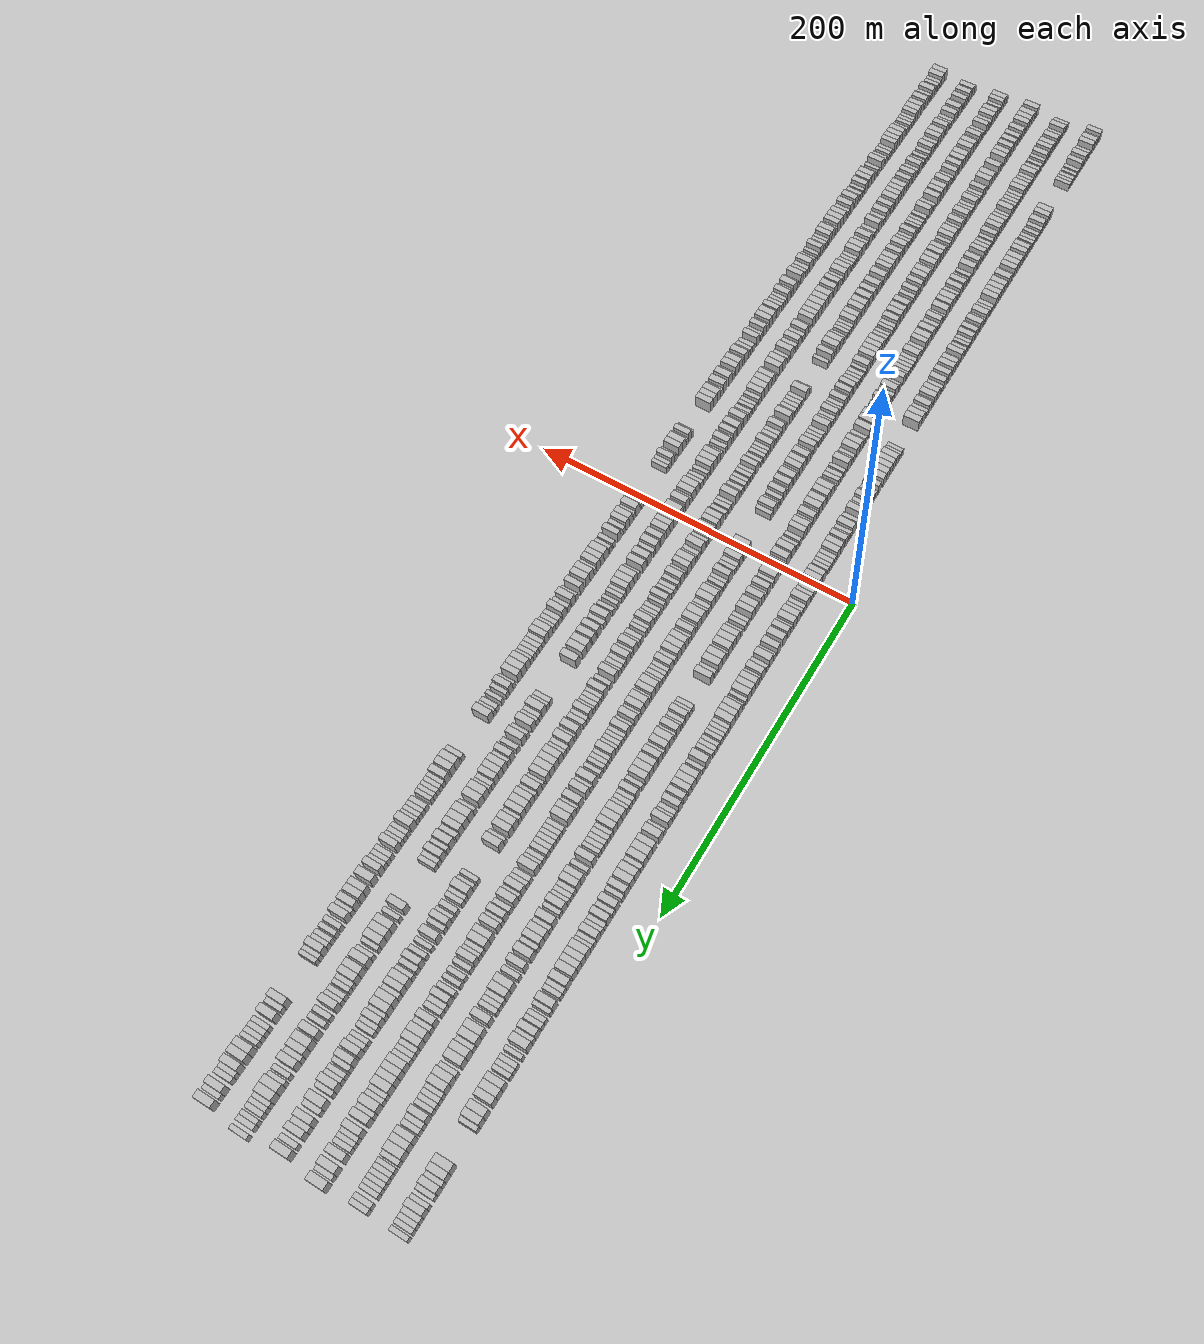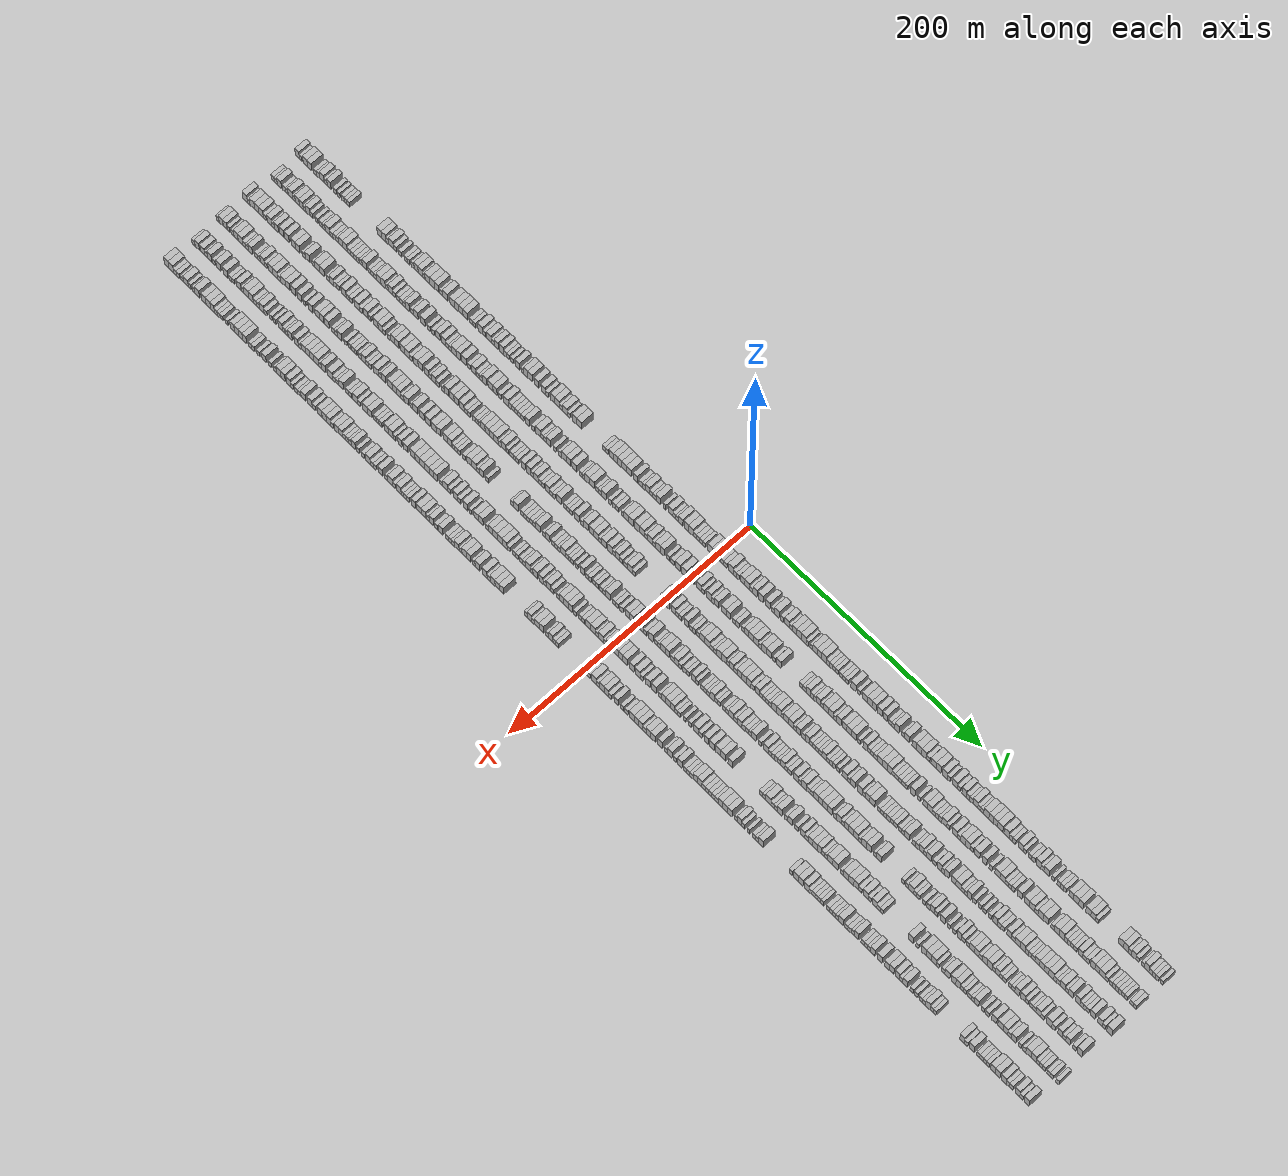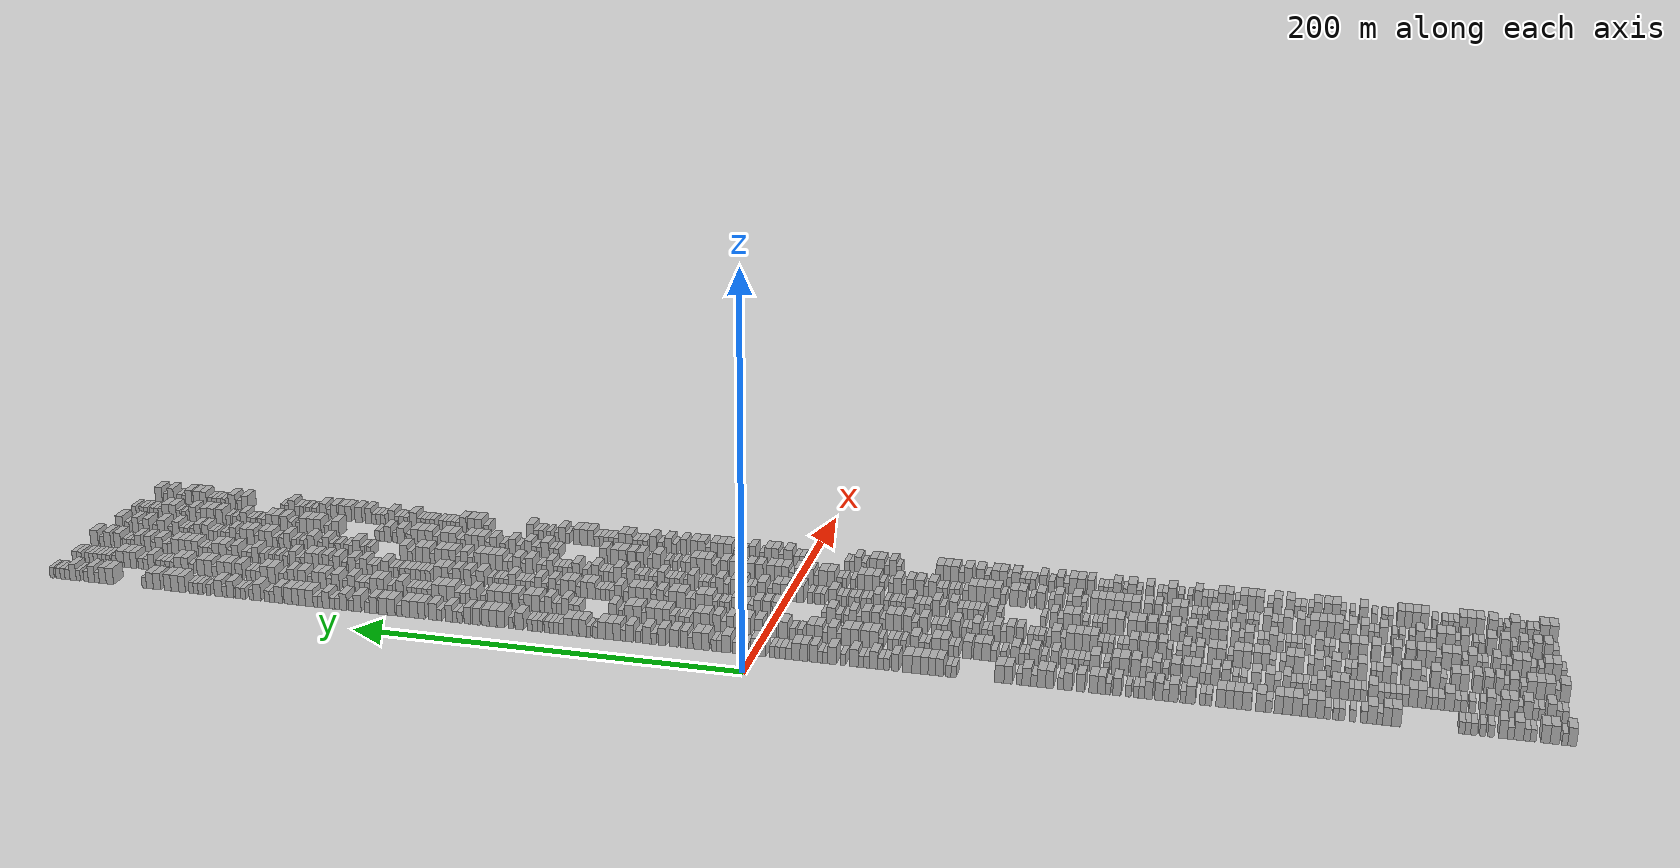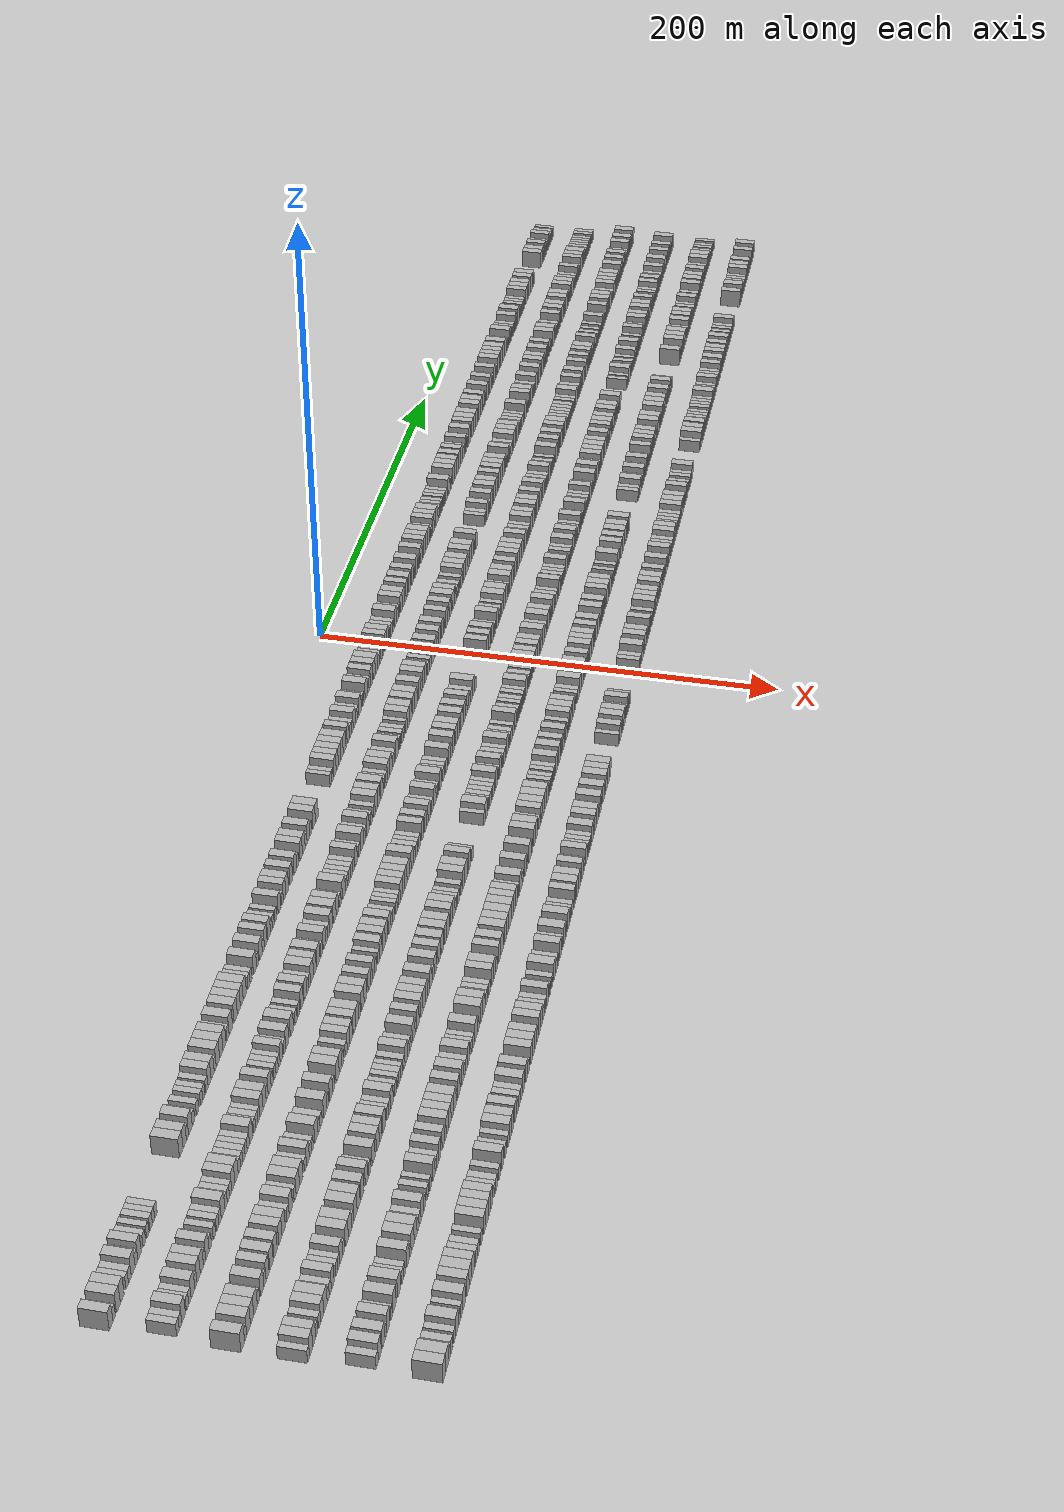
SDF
<sdf version="1.6">
 <world name="default">
  <scene>
   <sky><clouds><speed>12</speed></clouds></sky>
   <ambient>0.4 0.4 0.4 1</ambient>
   <background>0.7 0.7 0.7 1</background>
   <shadows>1</shadows>
  </scene>
  <gravity>0 0 -9.8066</gravity>
  <magnetic_field>6e-06 2.3e-05 -4.2e-05</magnetic_field>
  <physics default="0" name="default_physics" type="ode">
   <ode>
    <solver>
     <type>quick</type>
     <iters>10</iters>
     <sor>1.0</sor>
     <use_dynamic_moi_rescaling>0</use_dynamic_moi_rescaling>
    </solver>
    <constraints>
     <cfm>0</cfm>
     <erp>0.2</erp>
     <contact_max_correcting_vel>100</contact_max_correcting_vel>
     <contact_surface_layer>0.001</contact_surface_layer>
    </constraints>
   </ode>
   <max_step_size>0.004</max_step_size>
   <real_time_factor>1</real_time_factor>
   <real_time_update_rate>250</real_time_update_rate>
  </physics>
  <light name="sun" type="directional">
   <pose>0 0 10 0 0 0</pose>
   <diffuse>0.8 0.8 0.8 1</diffuse>
   <specular>0.2 0.2 0.2 1</specular>
   <attenuation>
    <range>1000</range>
    <constant>0.9</constant>
    <linear>0.01</linear>
    <quadratic>0.001</quadratic>
   </attenuation>
   <direction>-0.5 0.1 -0.9</direction>
  </light>
  <model name="building_1">
   <static>1</static>
   <pose>25.0000 -378.1050 0 0.000000 0.000000 0.000000</pose>
   <link name="link">
    <pose>0 0 4.50 0 0 0</pose>
    <collision name="collision"><geometry><box><size>10.0000 3.7900 9.0000</size></box></geometry></collision>
    <visual name="visual">
     <cast_shadows>0</cast_shadows>
     <geometry><box><size>10.0000 3.7900 9.0000</size></box></geometry>
     <material>
      <script>
       <uri>model://HANNAS_wall/materials/scripts</uri>
       <uri>model://HANNAS_wall/materials/textures</uri>
       <name>vrc/HANNAS_wall</name>
      </script>
     </material>
    </visual>
   </link>
  </model>
  <model name="building_2">
   <static>1</static>
   <pose>25.0000 -374.9689 0 0.000000 0.000000 0.000000</pose>
   <link name="link">
    <pose>0 0 3.00 0 0 0</pose>
    <collision name="collision"><geometry><box><size>10.0000 2.4822 6.0000</size></box></geometry></collision>
    <visual name="visual">
     <cast_shadows>0</cast_shadows>
     <geometry><box><size>10.0000 2.4822 6.0000</size></box></geometry>
     <material>
      <script>
       <uri>model://HANNAS_wall/materials/scripts</uri>
       <uri>model://HANNAS_wall/materials/textures</uri>
       <name>vrc/HANNAS_wall</name>
      </script>
     </material>
    </visual>
   </link>
  </model>
  <model name="building_3">
   <static>1</static>
   <pose>25.0000 -370.7063 0 0.000000 0.000000 0.000000</pose>
   <link name="link">
    <pose>0 0 4.50 0 0 0</pose>
    <collision name="collision"><geometry><box><size>10.0000 4.0431 9.0000</size></box></geometry></collision>
    <visual name="visual">
     <cast_shadows>0</cast_shadows>
     <geometry><box><size>10.0000 4.0431 9.0000</size></box></geometry>
     <material>
      <script>
       <uri>model://HANNAS_wall/materials/scripts</uri>
       <uri>model://HANNAS_wall/materials/textures</uri>
       <name>vrc/HANNAS_wall</name>
      </script>
     </material>
    </visual>
   </link>
  </model>
  <model name="building_4">
   <static>1</static>
   <pose>25.0000 -366.7180 0 0.000000 0.000000 0.000000</pose>
   <link name="link">
    <pose>0 0 4.50 0 0 0</pose>
    <collision name="collision"><geometry><box><size>10.0000 3.9334 9.0000</size></box></geometry></collision>
    <visual name="visual">
     <cast_shadows>0</cast_shadows>
     <geometry><box><size>10.0000 3.9334 9.0000</size></box></geometry>
     <material>
      <script>
       <uri>model://HANNAS_wall/materials/scripts</uri>
       <uri>model://HANNAS_wall/materials/textures</uri>
       <name>vrc/HANNAS_wall</name>
      </script>
     </material>
    </visual>
   </link>
  </model>
  <model name="building_5">
   <static>1</static>
   <pose>25.0000 -361.4553 0 0.000000 0.000000 0.000000</pose>
   <link name="link">
    <pose>0 0 3.00 0 0 0</pose>
    <collision name="collision"><geometry><box><size>10.0000 2.5922 6.0000</size></box></geometry></collision>
    <visual name="visual">
     <cast_shadows>0</cast_shadows>
     <geometry><box><size>10.0000 2.5922 6.0000</size></box></geometry>
     <material>
      <script>
       <uri>model://HANNAS_wall/materials/scripts</uri>
       <uri>model://HANNAS_wall/materials/textures</uri>
       <name>vrc/HANNAS_wall</name>
      </script>
     </material>
    </visual>
   </link>
  </model>
  <model name="building_6">
   <static>1</static>
   <pose>25.0000 -358.7461 0 0.000000 0.000000 0.000000</pose>
   <link name="link">
    <pose>0 0 3.00 0 0 0</pose>
    <collision name="collision"><geometry><box><size>10.0000 2.8261 6.0000</size></box></geometry></collision>
    <visual name="visual">
     <cast_shadows>0</cast_shadows>
     <geometry><box><size>10.0000 2.8261 6.0000</size></box></geometry>
     <material>
      <script>
       <uri>model://HANNAS_wall/materials/scripts</uri>
       <uri>model://HANNAS_wall/materials/textures</uri>
       <name>vrc/HANNAS_wall</name>
      </script>
     </material>
    </visual>
   </link>
  </model>
  <model name="building_7">
   <static>1</static>
   <pose>25.0000 -355.2564 0 0.000000 0.000000 0.000000</pose>
   <link name="link">
    <pose>0 0 4.50 0 0 0</pose>
    <collision name="collision"><geometry><box><size>10.0000 4.1533 9.0000</size></box></geometry></collision>
    <visual name="visual">
     <cast_shadows>0</cast_shadows>
     <geometry><box><size>10.0000 4.1533 9.0000</size></box></geometry>
     <material>
      <script>
       <uri>model://HANNAS_wall/materials/scripts</uri>
       <uri>model://HANNAS_wall/materials/textures</uri>
       <name>vrc/HANNAS_wall</name>
      </script>
     </material>
    </visual>
   </link>
  </model>
  <model name="building_8">
   <static>1</static>
   <pose>25.0000 -351.7290 0 0.000000 0.000000 0.000000</pose>
   <link name="link">
    <pose>0 0 3.00 0 0 0</pose>
    <collision name="collision"><geometry><box><size>10.0000 2.9015 6.0000</size></box></geometry></collision>
    <visual name="visual">
     <cast_shadows>0</cast_shadows>
     <geometry><box><size>10.0000 2.9015 6.0000</size></box></geometry>
     <material>
      <script>
       <uri>model://HANNAS_wall/materials/scripts</uri>
       <uri>model://HANNAS_wall/materials/textures</uri>
       <name>vrc/HANNAS_wall</name>
      </script>
     </material>
    </visual>
   </link>
  </model>
  <model name="building_9">
   <static>1</static>
   <pose>25.0000 -348.4734 0 0.000000 0.000000 0.000000</pose>
   <link name="link">
    <pose>0 0 4.50 0 0 0</pose>
    <collision name="collision"><geometry><box><size>10.0000 3.6097 9.0000</size></box></geometry></collision>
    <visual name="visual">
     <cast_shadows>0</cast_shadows>
     <geometry><box><size>10.0000 3.6097 9.0000</size></box></geometry>
     <material>
      <script>
       <uri>model://HANNAS_wall/materials/scripts</uri>
       <uri>model://HANNAS_wall/materials/textures</uri>
       <name>vrc/HANNAS_wall</name>
      </script>
     </material>
    </visual>
   </link>
  </model>
  <model name="building_10">
   <static>1</static>
   <pose>25.0000 -343.2628 0 0.000000 0.000000 0.000000</pose>
   <link name="link">
    <pose>0 0 3.00 0 0 0</pose>
    <collision name="collision"><geometry><box><size>10.0000 2.8115 6.0000</size></box></geometry></collision>
    <visual name="visual">
     <cast_shadows>0</cast_shadows>
     <geometry><box><size>10.0000 2.8115 6.0000</size></box></geometry>
     <material>
      <script>
       <uri>model://HANNAS_wall/materials/scripts</uri>
       <uri>model://HANNAS_wall/materials/textures</uri>
       <name>vrc/HANNAS_wall</name>
      </script>
     </material>
    </visual>
   </link>
  </model>
  <model name="building_11">
   <static>1</static>
   <pose>25.0000 -339.5802 0 0.000000 0.000000 0.000000</pose>
   <link name="link">
    <pose>0 0 3.00 0 0 0</pose>
    <collision name="collision"><geometry><box><size>10.0000 2.5537 6.0000</size></box></geometry></collision>
    <visual name="visual">
     <cast_shadows>0</cast_shadows>
     <geometry><box><size>10.0000 2.5537 6.0000</size></box></geometry>
     <material>
      <script>
       <uri>model://HANNAS_wall/materials/scripts</uri>
       <uri>model://HANNAS_wall/materials/textures</uri>
       <name>vrc/HANNAS_wall</name>
      </script>
     </material>
    </visual>
   </link>
  </model>
  <model name="building_12">
   <static>1</static>
   <pose>25.0000 -335.8862 0 0.000000 0.000000 0.000000</pose>
   <link name="link">
    <pose>0 0 3.00 0 0 0</pose>
    <collision name="collision"><geometry><box><size>10.0000 2.8342 6.0000</size></box></geometry></collision>
    <visual name="visual">
     <cast_shadows>0</cast_shadows>
     <geometry><box><size>10.0000 2.8342 6.0000</size></box></geometry>
     <material>
      <script>
       <uri>model://HANNAS_wall/materials/scripts</uri>
       <uri>model://HANNAS_wall/materials/textures</uri>
       <name>vrc/HANNAS_wall</name>
      </script>
     </material>
    </visual>
   </link>
  </model>
  <model name="building_13">
   <static>1</static>
   <pose>25.0000 -333.2497 0 0.000000 0.000000 0.000000</pose>
   <link name="link">
    <pose>0 0 3.00 0 0 0</pose>
    <collision name="collision"><geometry><box><size>10.0000 2.4389 6.0000</size></box></geometry></collision>
    <visual name="visual">
     <cast_shadows>0</cast_shadows>
     <geometry><box><size>10.0000 2.4389 6.0000</size></box></geometry>
     <material>
      <script>
       <uri>model://HANNAS_wall/materials/scripts</uri>
       <uri>model://HANNAS_wall/materials/textures</uri>
       <name>vrc/HANNAS_wall</name>
      </script>
     </material>
    </visual>
   </link>
  </model>
  <model name="building_14">
   <static>1</static>
   <pose>25.0000 -330.6634 0 0.000000 0.000000 0.000000</pose>
   <link name="link">
    <pose>0 0 3.00 0 0 0</pose>
    <collision name="collision"><geometry><box><size>10.0000 2.7336 6.0000</size></box></geometry></collision>
    <visual name="visual">
     <cast_shadows>0</cast_shadows>
     <geometry><box><size>10.0000 2.7336 6.0000</size></box></geometry>
     <material>
      <script>
       <uri>model://HANNAS_wall/materials/scripts</uri>
       <uri>model://HANNAS_wall/materials/textures</uri>
       <name>vrc/HANNAS_wall</name>
      </script>
     </material>
    </visual>
   </link>
  </model>
  <model name="building_15">
   <static>1</static>
   <pose>25.0000 -301.9476 0 0.000000 0.000000 0.000000</pose>
   <link name="link">
    <pose>0 0 4.50 0 0 0</pose>
    <collision name="collision"><geometry><box><size>10.0000 4.2327 9.0000</size></box></geometry></collision>
    <visual name="visual">
     <cast_shadows>0</cast_shadows>
     <geometry><box><size>10.0000 4.2327 9.0000</size></box></geometry>
     <material>
      <script>
       <uri>model://HANNAS_wall/materials/scripts</uri>
       <uri>model://HANNAS_wall/materials/textures</uri>
       <name>vrc/HANNAS_wall</name>
      </script>
     </material>
    </visual>
   </link>
  </model>
  <model name="building_16">
   <static>1</static>
   <pose>25.0000 -297.8743 0 0.000000 0.000000 0.000000</pose>
   <link name="link">
    <pose>0 0 4.50 0 0 0</pose>
    <collision name="collision"><geometry><box><size>10.0000 3.9139 9.0000</size></box></geometry></collision>
    <visual name="visual">
     <cast_shadows>0</cast_shadows>
     <geometry><box><size>10.0000 3.9139 9.0000</size></box></geometry>
     <material>
      <script>
       <uri>model://HANNAS_wall/materials/scripts</uri>
       <uri>model://HANNAS_wall/materials/textures</uri>
       <name>vrc/HANNAS_wall</name>
      </script>
     </material>
    </visual>
   </link>
  </model>
  <model name="building_17">
   <static>1</static>
   <pose>25.0000 -294.6431 0 0.000000 0.000000 0.000000</pose>
   <link name="link">
    <pose>0 0 3.00 0 0 0</pose>
    <collision name="collision"><geometry><box><size>10.0000 2.5486 6.0000</size></box></geometry></collision>
    <visual name="visual">
     <cast_shadows>0</cast_shadows>
     <geometry><box><size>10.0000 2.5486 6.0000</size></box></geometry>
     <material>
      <script>
       <uri>model://HANNAS_wall/materials/scripts</uri>
       <uri>model://HANNAS_wall/materials/textures</uri>
       <name>vrc/HANNAS_wall</name>
      </script>
     </material>
    </visual>
   </link>
  </model>
  <model name="building_18">
   <static>1</static>
   <pose>25.0000 -291.2424 0 0.000000 0.000000 0.000000</pose>
   <link name="link">
    <pose>0 0 4.50 0 0 0</pose>
    <collision name="collision"><geometry><box><size>10.0000 4.2528 9.0000</size></box></geometry></collision>
    <visual name="visual">
     <cast_shadows>0</cast_shadows>
     <geometry><box><size>10.0000 4.2528 9.0000</size></box></geometry>
     <material>
      <script>
       <uri>model://HANNAS_wall/materials/scripts</uri>
       <uri>model://HANNAS_wall/materials/textures</uri>
       <name>vrc/HANNAS_wall</name>
      </script>
     </material>
    </visual>
   </link>
  </model>
  <model name="building_19">
   <static>1</static>
   <pose>25.0000 -287.6211 0 0.000000 0.000000 0.000000</pose>
   <link name="link">
    <pose>0 0 3.00 0 0 0</pose>
    <collision name="collision"><geometry><box><size>10.0000 2.9899 6.0000</size></box></geometry></collision>
    <visual name="visual">
     <cast_shadows>0</cast_shadows>
     <geometry><box><size>10.0000 2.9899 6.0000</size></box></geometry>
     <material>
      <script>
       <uri>model://HANNAS_wall/materials/scripts</uri>
       <uri>model://HANNAS_wall/materials/textures</uri>
       <name>vrc/HANNAS_wall</name>
      </script>
     </material>
    </visual>
   </link>
  </model>
  <model name="building_20">
   <static>1</static>
   <pose>25.0000 -282.6733 0 0.000000 0.000000 0.000000</pose>
   <link name="link">
    <pose>0 0 3.00 0 0 0</pose>
    <collision name="collision"><geometry><box><size>10.0000 2.9058 6.0000</size></box></geometry></collision>
    <visual name="visual">
     <cast_shadows>0</cast_shadows>
     <geometry><box><size>10.0000 2.9058 6.0000</size></box></geometry>
     <material>
      <script>
       <uri>model://HANNAS_wall/materials/scripts</uri>
       <uri>model://HANNAS_wall/materials/textures</uri>
       <name>vrc/HANNAS_wall</name>
      </script>
     </material>
    </visual>
   </link>
  </model>
  <model name="building_21">
   <static>1</static>
   <pose>25.0000 -277.8482 0 0.000000 0.000000 0.000000</pose>
   <link name="link">
    <pose>0 0 3.00 0 0 0</pose>
    <collision name="collision"><geometry><box><size>10.0000 2.7444 6.0000</size></box></geometry></collision>
    <visual name="visual">
     <cast_shadows>0</cast_shadows>
     <geometry><box><size>10.0000 2.7444 6.0000</size></box></geometry>
     <material>
      <script>
       <uri>model://HANNAS_wall/materials/scripts</uri>
       <uri>model://HANNAS_wall/materials/textures</uri>
       <name>vrc/HANNAS_wall</name>
      </script>
     </material>
    </visual>
   </link>
  </model>
  <model name="building_22">
   <static>1</static>
   <pose>25.0000 -275.1647 0 0.000000 0.000000 0.000000</pose>
   <link name="link">
    <pose>0 0 3.00 0 0 0</pose>
    <collision name="collision"><geometry><box><size>10.0000 2.6225 6.0000</size></box></geometry></collision>
    <visual name="visual">
     <cast_shadows>0</cast_shadows>
     <geometry><box><size>10.0000 2.6225 6.0000</size></box></geometry>
     <material>
      <script>
       <uri>model://HANNAS_wall/materials/scripts</uri>
       <uri>model://HANNAS_wall/materials/textures</uri>
       <name>vrc/HANNAS_wall</name>
      </script>
     </material>
    </visual>
   </link>
  </model>
  <model name="building_23">
   <static>1</static>
   <pose>25.0000 -271.4260 0 0.000000 0.000000 0.000000</pose>
   <link name="link">
    <pose>0 0 3.00 0 0 0</pose>
    <collision name="collision"><geometry><box><size>10.0000 2.8548 6.0000</size></box></geometry></collision>
    <visual name="visual">
     <cast_shadows>0</cast_shadows>
     <geometry><box><size>10.0000 2.8548 6.0000</size></box></geometry>
     <material>
      <script>
       <uri>model://HANNAS_wall/materials/scripts</uri>
       <uri>model://HANNAS_wall/materials/textures</uri>
       <name>vrc/HANNAS_wall</name>
      </script>
     </material>
    </visual>
   </link>
  </model>
  <model name="building_24">
   <static>1</static>
   <pose>25.0000 -268.1516 0 0.000000 0.000000 0.000000</pose>
   <link name="link">
    <pose>0 0 4.50 0 0 0</pose>
    <collision name="collision"><geometry><box><size>10.0000 3.6940 9.0000</size></box></geometry></collision>
    <visual name="visual">
     <cast_shadows>0</cast_shadows>
     <geometry><box><size>10.0000 3.6940 9.0000</size></box></geometry>
     <material>
      <script>
       <uri>model://HANNAS_wall/materials/scripts</uri>
       <uri>model://HANNAS_wall/materials/textures</uri>
       <name>vrc/HANNAS_wall</name>
      </script>
     </material>
    </visual>
   </link>
  </model>
  <model name="building_25">
   <static>1</static>
   <pose>25.0000 -264.3917 0 0.000000 0.000000 0.000000</pose>
   <link name="link">
    <pose>0 0 4.50 0 0 0</pose>
    <collision name="collision"><geometry><box><size>10.0000 3.8258 9.0000</size></box></geometry></collision>
    <visual name="visual">
     <cast_shadows>0</cast_shadows>
     <geometry><box><size>10.0000 3.8258 9.0000</size></box></geometry>
     <material>
      <script>
       <uri>model://HANNAS_wall/materials/scripts</uri>
       <uri>model://HANNAS_wall/materials/textures</uri>
       <name>vrc/HANNAS_wall</name>
      </script>
     </material>
    </visual>
   </link>
  </model>
  <model name="building_26">
   <static>1</static>
   <pose>25.0000 -261.2390 0 0.000000 0.000000 0.000000</pose>
   <link name="link">
    <pose>0 0 3.00 0 0 0</pose>
    <collision name="collision"><geometry><box><size>10.0000 2.4795 6.0000</size></box></geometry></collision>
    <visual name="visual">
     <cast_shadows>0</cast_shadows>
     <geometry><box><size>10.0000 2.4795 6.0000</size></box></geometry>
     <material>
      <script>
       <uri>model://HANNAS_wall/materials/scripts</uri>
       <uri>model://HANNAS_wall/materials/textures</uri>
       <name>vrc/HANNAS_wall</name>
      </script>
     </material>
    </visual>
   </link>
  </model>
  <model name="building_27">
   <static>1</static>
   <pose>25.0000 -257.8551 0 0.000000 0.000000 0.000000</pose>
   <link name="link">
    <pose>0 0 4.50 0 0 0</pose>
    <collision name="collision"><geometry><box><size>10.0000 4.2885 9.0000</size></box></geometry></collision>
    <visual name="visual">
     <cast_shadows>0</cast_shadows>
     <geometry><box><size>10.0000 4.2885 9.0000</size></box></geometry>
     <material>
      <script>
       <uri>model://HANNAS_wall/materials/scripts</uri>
       <uri>model://HANNAS_wall/materials/textures</uri>
       <name>vrc/HANNAS_wall</name>
      </script>
     </material>
    </visual>
   </link>
  </model>
  <model name="building_28">
   <static>1</static>
   <pose>25.0000 -253.5966 0 0.000000 0.000000 0.000000</pose>
   <link name="link">
    <pose>0 0 4.50 0 0 0</pose>
    <collision name="collision"><geometry><box><size>10.0000 4.2284 9.0000</size></box></geometry></collision>
    <visual name="visual">
     <cast_shadows>0</cast_shadows>
     <geometry><box><size>10.0000 4.2284 9.0000</size></box></geometry>
     <material>
      <script>
       <uri>model://HANNAS_wall/materials/scripts</uri>
       <uri>model://HANNAS_wall/materials/textures</uri>
       <name>vrc/HANNAS_wall</name>
      </script>
     </material>
    </visual>
   </link>
  </model>
  <model name="building_29">
   <static>1</static>
   <pose>25.0000 -249.5386 0 0.000000 0.000000 0.000000</pose>
   <link name="link">
    <pose>0 0 4.50 0 0 0</pose>
    <collision name="collision"><geometry><box><size>10.0000 3.8877 9.0000</size></box></geometry></collision>
    <visual name="visual">
     <cast_shadows>0</cast_shadows>
     <geometry><box><size>10.0000 3.8877 9.0000</size></box></geometry>
     <material>
      <script>
       <uri>model://HANNAS_wall/materials/scripts</uri>
       <uri>model://HANNAS_wall/materials/textures</uri>
       <name>vrc/HANNAS_wall</name>
      </script>
     </material>
    </visual>
   </link>
  </model>
  <model name="building_30">
   <static>1</static>
   <pose>25.0000 -245.1325 0 0.000000 0.000000 0.000000</pose>
   <link name="link">
    <pose>0 0 3.00 0 0 0</pose>
    <collision name="collision"><geometry><box><size>10.0000 2.9245 6.0000</size></box></geometry></collision>
    <visual name="visual">
     <cast_shadows>0</cast_shadows>
     <geometry><box><size>10.0000 2.9245 6.0000</size></box></geometry>
     <material>
      <script>
       <uri>model://HANNAS_wall/materials/scripts</uri>
       <uri>model://HANNAS_wall/materials/textures</uri>
       <name>vrc/HANNAS_wall</name>
      </script>
     </material>
    </visual>
   </link>
  </model>
  <model name="building_31">
   <static>1</static>
   <pose>25.0000 -241.4509 0 0.000000 0.000000 0.000000</pose>
   <link name="link">
    <pose>0 0 4.50 0 0 0</pose>
    <collision name="collision"><geometry><box><size>10.0000 4.4386 9.0000</size></box></geometry></collision>
    <visual name="visual">
     <cast_shadows>0</cast_shadows>
     <geometry><box><size>10.0000 4.4386 9.0000</size></box></geometry>
     <material>
      <script>
       <uri>model://HANNAS_wall/materials/scripts</uri>
       <uri>model://HANNAS_wall/materials/textures</uri>
       <name>vrc/HANNAS_wall</name>
      </script>
     </material>
    </visual>
   </link>
  </model>
  <model name="building_32">
   <static>1</static>
   <pose>25.0000 -235.1560 0 0.000000 0.000000 0.000000</pose>
   <link name="link">
    <pose>0 0 4.50 0 0 0</pose>
    <collision name="collision"><geometry><box><size>10.0000 4.1512 9.0000</size></box></geometry></collision>
    <visual name="visual">
     <cast_shadows>0</cast_shadows>
     <geometry><box><size>10.0000 4.1512 9.0000</size></box></geometry>
     <material>
      <script>
       <uri>model://HANNAS_wall/materials/scripts</uri>
       <uri>model://HANNAS_wall/materials/textures</uri>
       <name>vrc/HANNAS_wall</name>
      </script>
     </material>
    </visual>
   </link>
  </model>
  <model name="building_33">
   <static>1</static>
   <pose>25.0000 -231.0909 0 0.000000 0.000000 0.000000</pose>
   <link name="link">
    <pose>0 0 4.50 0 0 0</pose>
    <collision name="collision"><geometry><box><size>10.0000 3.9792 9.0000</size></box></geometry></collision>
    <visual name="visual">
     <cast_shadows>0</cast_shadows>
     <geometry><box><size>10.0000 3.9792 9.0000</size></box></geometry>
     <material>
      <script>
       <uri>model://HANNAS_wall/materials/scripts</uri>
       <uri>model://HANNAS_wall/materials/textures</uri>
       <name>vrc/HANNAS_wall</name>
      </script>
     </material>
    </visual>
   </link>
  </model>
  <model name="building_34">
   <static>1</static>
   <pose>25.0000 -227.2338 0 0.000000 0.000000 0.000000</pose>
   <link name="link">
    <pose>0 0 4.50 0 0 0</pose>
    <collision name="collision"><geometry><box><size>10.0000 3.7350 9.0000</size></box></geometry></collision>
    <visual name="visual">
     <cast_shadows>0</cast_shadows>
     <geometry><box><size>10.0000 3.7350 9.0000</size></box></geometry>
     <material>
      <script>
       <uri>model://HANNAS_wall/materials/scripts</uri>
       <uri>model://HANNAS_wall/materials/textures</uri>
       <name>vrc/HANNAS_wall</name>
      </script>
     </material>
    </visual>
   </link>
  </model>
  <model name="building_35">
   <static>1</static>
   <pose>25.0000 -223.2722 0 0.000000 0.000000 0.000000</pose>
   <link name="link">
    <pose>0 0 4.50 0 0 0</pose>
    <collision name="collision"><geometry><box><size>10.0000 4.1880 9.0000</size></box></geometry></collision>
    <visual name="visual">
     <cast_shadows>0</cast_shadows>
     <geometry><box><size>10.0000 4.1880 9.0000</size></box></geometry>
     <material>
      <script>
       <uri>model://HANNAS_wall/materials/scripts</uri>
       <uri>model://HANNAS_wall/materials/textures</uri>
       <name>vrc/HANNAS_wall</name>
      </script>
     </material>
    </visual>
   </link>
  </model>
  <model name="building_36">
   <static>1</static>
   <pose>25.0000 -217.7304 0 0.000000 0.000000 0.000000</pose>
   <link name="link">
    <pose>0 0 3.00 0 0 0</pose>
    <collision name="collision"><geometry><box><size>10.0000 2.8956 6.0000</size></box></geometry></collision>
    <visual name="visual">
     <cast_shadows>0</cast_shadows>
     <geometry><box><size>10.0000 2.8956 6.0000</size></box></geometry>
     <material>
      <script>
       <uri>model://HANNAS_wall/materials/scripts</uri>
       <uri>model://HANNAS_wall/materials/textures</uri>
       <name>vrc/HANNAS_wall</name>
      </script>
     </material>
    </visual>
   </link>
  </model>
  <model name="building_37">
   <static>1</static>
   <pose>25.0000 -214.9912 0 0.000000 0.000000 0.000000</pose>
   <link name="link">
    <pose>0 0 3.00 0 0 0</pose>
    <collision name="collision"><geometry><box><size>10.0000 2.5828 6.0000</size></box></geometry></collision>
    <visual name="visual">
     <cast_shadows>0</cast_shadows>
     <geometry><box><size>10.0000 2.5828 6.0000</size></box></geometry>
     <material>
      <script>
       <uri>model://HANNAS_wall/materials/scripts</uri>
       <uri>model://HANNAS_wall/materials/textures</uri>
       <name>vrc/HANNAS_wall</name>
      </script>
     </material>
    </visual>
   </link>
  </model>
  <model name="building_38">
   <static>1</static>
   <pose>25.0000 -209.5487 0 0.000000 0.000000 0.000000</pose>
   <link name="link">
    <pose>0 0 4.50 0 0 0</pose>
    <collision name="collision"><geometry><box><size>10.0000 4.3022 9.0000</size></box></geometry></collision>
    <visual name="visual">
     <cast_shadows>0</cast_shadows>
     <geometry><box><size>10.0000 4.3022 9.0000</size></box></geometry>
     <material>
      <script>
       <uri>model://HANNAS_wall/materials/scripts</uri>
       <uri>model://HANNAS_wall/materials/textures</uri>
       <name>vrc/HANNAS_wall</name>
      </script>
     </material>
    </visual>
   </link>
  </model>
  <model name="building_39">
   <static>1</static>
   <pose>25.0000 -206.1032 0 0.000000 0.000000 0.000000</pose>
   <link name="link">
    <pose>0 0 3.00 0 0 0</pose>
    <collision name="collision"><geometry><box><size>10.0000 2.5889 6.0000</size></box></geometry></collision>
    <visual name="visual">
     <cast_shadows>0</cast_shadows>
     <geometry><box><size>10.0000 2.5889 6.0000</size></box></geometry>
     <material>
      <script>
       <uri>model://HANNAS_wall/materials/scripts</uri>
       <uri>model://HANNAS_wall/materials/textures</uri>
       <name>vrc/HANNAS_wall</name>
      </script>
     </material>
    </visual>
   </link>
  </model>
  <model name="building_40">
   <static>1</static>
   <pose>25.0000 -201.7070 0 0.000000 0.000000 0.000000</pose>
   <link name="link">
    <pose>0 0 4.50 0 0 0</pose>
    <collision name="collision"><geometry><box><size>10.0000 4.2035 9.0000</size></box></geometry></collision>
    <visual name="visual">
     <cast_shadows>0</cast_shadows>
     <geometry><box><size>10.0000 4.2035 9.0000</size></box></geometry>
     <material>
      <script>
       <uri>model://HANNAS_wall/materials/scripts</uri>
       <uri>model://HANNAS_wall/materials/textures</uri>
       <name>vrc/HANNAS_wall</name>
      </script>
     </material>
    </visual>
   </link>
  </model>
  <model name="building_41">
   <static>1</static>
   <pose>25.0000 -198.1767 0 0.000000 0.000000 0.000000</pose>
   <link name="link">
    <pose>0 0 3.00 0 0 0</pose>
    <collision name="collision"><geometry><box><size>10.0000 2.8569 6.0000</size></box></geometry></collision>
    <visual name="visual">
     <cast_shadows>0</cast_shadows>
     <geometry><box><size>10.0000 2.8569 6.0000</size></box></geometry>
     <material>
      <script>
       <uri>model://HANNAS_wall/materials/scripts</uri>
       <uri>model://HANNAS_wall/materials/textures</uri>
       <name>vrc/HANNAS_wall</name>
      </script>
     </material>
    </visual>
   </link>
  </model>
  <model name="building_42">
   <static>1</static>
   <pose>25.0000 -194.9257 0 0.000000 0.000000 0.000000</pose>
   <link name="link">
    <pose>0 0 4.50 0 0 0</pose>
    <collision name="collision"><geometry><box><size>10.0000 3.6452 9.0000</size></box></geometry></collision>
    <visual name="visual">
     <cast_shadows>0</cast_shadows>
     <geometry><box><size>10.0000 3.6452 9.0000</size></box></geometry>
     <material>
      <script>
       <uri>model://HANNAS_wall/materials/scripts</uri>
       <uri>model://HANNAS_wall/materials/textures</uri>
       <name>vrc/HANNAS_wall</name>
      </script>
     </material>
    </visual>
   </link>
  </model>
  <model name="building_43">
   <static>1</static>
   <pose>25.0000 -190.2338 0 0.000000 0.000000 0.000000</pose>
   <link name="link">
    <pose>0 0 4.50 0 0 0</pose>
    <collision name="collision"><geometry><box><size>10.0000 3.7387 9.0000</size></box></geometry></collision>
    <visual name="visual">
     <cast_shadows>0</cast_shadows>
     <geometry><box><size>10.0000 3.7387 9.0000</size></box></geometry>
     <material>
      <script>
       <uri>model://HANNAS_wall/materials/scripts</uri>
       <uri>model://HANNAS_wall/materials/textures</uri>
       <name>vrc/HANNAS_wall</name>
      </script>
     </material>
    </visual>
   </link>
  </model>
  <model name="building_44">
   <static>1</static>
   <pose>25.0000 -187.0339 0 0.000000 0.000000 0.000000</pose>
   <link name="link">
    <pose>0 0 3.00 0 0 0</pose>
    <collision name="collision"><geometry><box><size>10.0000 2.6612 6.0000</size></box></geometry></collision>
    <visual name="visual">
     <cast_shadows>0</cast_shadows>
     <geometry><box><size>10.0000 2.6612 6.0000</size></box></geometry>
     <material>
      <script>
       <uri>model://HANNAS_wall/materials/scripts</uri>
       <uri>model://HANNAS_wall/materials/textures</uri>
       <name>vrc/HANNAS_wall</name>
      </script>
     </material>
    </visual>
   </link>
  </model>
  <model name="building_45">
   <static>1</static>
   <pose>25.0000 -184.4426 0 0.000000 0.000000 0.000000</pose>
   <link name="link">
    <pose>0 0 3.00 0 0 0</pose>
    <collision name="collision"><geometry><box><size>10.0000 2.5213 6.0000</size></box></geometry></collision>
    <visual name="visual">
     <cast_shadows>0</cast_shadows>
     <geometry><box><size>10.0000 2.5213 6.0000</size></box></geometry>
     <material>
      <script>
       <uri>model://HANNAS_wall/materials/scripts</uri>
       <uri>model://HANNAS_wall/materials/textures</uri>
       <name>vrc/HANNAS_wall</name>
      </script>
     </material>
    </visual>
   </link>
  </model>
  <model name="building_46">
   <static>1</static>
   <pose>25.0000 -180.8359 0 0.000000 0.000000 0.000000</pose>
   <link name="link">
    <pose>0 0 3.00 0 0 0</pose>
    <collision name="collision"><geometry><box><size>10.0000 2.6920 6.0000</size></box></geometry></collision>
    <visual name="visual">
     <cast_shadows>0</cast_shadows>
     <geometry><box><size>10.0000 2.6920 6.0000</size></box></geometry>
     <material>
      <script>
       <uri>model://HANNAS_wall/materials/scripts</uri>
       <uri>model://HANNAS_wall/materials/textures</uri>
       <name>vrc/HANNAS_wall</name>
      </script>
     </material>
    </visual>
   </link>
  </model>
  <model name="building_47">
   <static>1</static>
   <pose>25.0000 -175.6081 0 0.000000 0.000000 0.000000</pose>
   <link name="link">
    <pose>0 0 4.50 0 0 0</pose>
    <collision name="collision"><geometry><box><size>10.0000 3.7636 9.0000</size></box></geometry></collision>
    <visual name="visual">
     <cast_shadows>0</cast_shadows>
     <geometry><box><size>10.0000 3.7636 9.0000</size></box></geometry>
     <material>
      <script>
       <uri>model://HANNAS_wall/materials/scripts</uri>
       <uri>model://HANNAS_wall/materials/textures</uri>
       <name>vrc/HANNAS_wall</name>
      </script>
     </material>
    </visual>
   </link>
  </model>
  <model name="building_48">
   <static>1</static>
   <pose>25.0000 -171.4597 0 0.000000 0.000000 0.000000</pose>
   <link name="link">
    <pose>0 0 3.00 0 0 0</pose>
    <collision name="collision"><geometry><box><size>10.0000 2.5333 6.0000</size></box></geometry></collision>
    <visual name="visual">
     <cast_shadows>0</cast_shadows>
     <geometry><box><size>10.0000 2.5333 6.0000</size></box></geometry>
     <material>
      <script>
       <uri>model://HANNAS_wall/materials/scripts</uri>
       <uri>model://HANNAS_wall/materials/textures</uri>
       <name>vrc/HANNAS_wall</name>
      </script>
     </material>
    </visual>
   </link>
  </model>
  <model name="building_49">
   <static>1</static>
   <pose>25.0000 -168.3847 0 0.000000 0.000000 0.000000</pose>
   <link name="link">
    <pose>0 0 4.50 0 0 0</pose>
    <collision name="collision"><geometry><box><size>10.0000 3.6165 9.0000</size></box></geometry></collision>
    <visual name="visual">
     <cast_shadows>0</cast_shadows>
     <geometry><box><size>10.0000 3.6165 9.0000</size></box></geometry>
     <material>
      <script>
       <uri>model://HANNAS_wall/materials/scripts</uri>
       <uri>model://HANNAS_wall/materials/textures</uri>
       <name>vrc/HANNAS_wall</name>
      </script>
     </material>
    </visual>
   </link>
  </model>
  <model name="building_50">
   <static>1</static>
   <pose>25.0000 -164.5679 0 0.000000 0.000000 0.000000</pose>
   <link name="link">
    <pose>0 0 4.50 0 0 0</pose>
    <collision name="collision"><geometry><box><size>10.0000 4.0173 9.0000</size></box></geometry></collision>
    <visual name="visual">
     <cast_shadows>0</cast_shadows>
     <geometry><box><size>10.0000 4.0173 9.0000</size></box></geometry>
     <material>
      <script>
       <uri>model://HANNAS_wall/materials/scripts</uri>
       <uri>model://HANNAS_wall/materials/textures</uri>
       <name>vrc/HANNAS_wall</name>
      </script>
     </material>
    </visual>
   </link>
  </model>
  <model name="building_51">
   <static>1</static>
   <pose>25.0000 -158.5867 0 0.000000 0.000000 0.000000</pose>
   <link name="link">
    <pose>0 0 4.50 0 0 0</pose>
    <collision name="collision"><geometry><box><size>10.0000 3.9451 9.0000</size></box></geometry></collision>
    <visual name="visual">
     <cast_shadows>0</cast_shadows>
     <geometry><box><size>10.0000 3.9451 9.0000</size></box></geometry>
     <material>
      <script>
       <uri>model://HANNAS_wall/materials/scripts</uri>
       <uri>model://HANNAS_wall/materials/textures</uri>
       <name>vrc/HANNAS_wall</name>
      </script>
     </material>
    </visual>
   </link>
  </model>
  <model name="building_52">
   <static>1</static>
   <pose>25.0000 -152.6099 0 0.000000 0.000000 0.000000</pose>
   <link name="link">
    <pose>0 0 4.50 0 0 0</pose>
    <collision name="collision"><geometry><box><size>10.0000 4.0085 9.0000</size></box></geometry></collision>
    <visual name="visual">
     <cast_shadows>0</cast_shadows>
     <geometry><box><size>10.0000 4.0085 9.0000</size></box></geometry>
     <material>
      <script>
       <uri>model://HANNAS_wall/materials/scripts</uri>
       <uri>model://HANNAS_wall/materials/textures</uri>
       <name>vrc/HANNAS_wall</name>
      </script>
     </material>
    </visual>
   </link>
  </model>
  <model name="building_53">
   <static>1</static>
   <pose>25.0000 -149.2317 0 0.000000 0.000000 0.000000</pose>
   <link name="link">
    <pose>0 0 3.00 0 0 0</pose>
    <collision name="collision"><geometry><box><size>10.0000 2.7478 6.0000</size></box></geometry></collision>
    <visual name="visual">
     <cast_shadows>0</cast_shadows>
     <geometry><box><size>10.0000 2.7478 6.0000</size></box></geometry>
     <material>
      <script>
       <uri>model://HANNAS_wall/materials/scripts</uri>
       <uri>model://HANNAS_wall/materials/textures</uri>
       <name>vrc/HANNAS_wall</name>
      </script>
     </material>
    </visual>
   </link>
  </model>
  <model name="building_54">
   <static>1</static>
   <pose>25.0000 -144.0198 0 0.000000 0.000000 0.000000</pose>
   <link name="link">
    <pose>0 0 4.50 0 0 0</pose>
    <collision name="collision"><geometry><box><size>10.0000 3.6759 9.0000</size></box></geometry></collision>
    <visual name="visual">
     <cast_shadows>0</cast_shadows>
     <geometry><box><size>10.0000 3.6759 9.0000</size></box></geometry>
     <material>
      <script>
       <uri>model://HANNAS_wall/materials/scripts</uri>
       <uri>model://HANNAS_wall/materials/textures</uri>
       <name>vrc/HANNAS_wall</name>
      </script>
     </material>
    </visual>
   </link>
  </model>
  <model name="building_55">
   <static>1</static>
   <pose>25.0000 -140.1416 0 0.000000 0.000000 0.000000</pose>
   <link name="link">
    <pose>0 0 4.50 0 0 0</pose>
    <collision name="collision"><geometry><box><size>10.0000 4.0806 9.0000</size></box></geometry></collision>
    <visual name="visual">
     <cast_shadows>0</cast_shadows>
     <geometry><box><size>10.0000 4.0806 9.0000</size></box></geometry>
     <material>
      <script>
       <uri>model://HANNAS_wall/materials/scripts</uri>
       <uri>model://HANNAS_wall/materials/textures</uri>
       <name>vrc/HANNAS_wall</name>
      </script>
     </material>
    </visual>
   </link>
  </model>
  <model name="building_56">
   <static>1</static>
   <pose>25.0000 -136.6434 0 0.000000 0.000000 0.000000</pose>
   <link name="link">
    <pose>0 0 3.00 0 0 0</pose>
    <collision name="collision"><geometry><box><size>10.0000 2.9158 6.0000</size></box></geometry></collision>
    <visual name="visual">
     <cast_shadows>0</cast_shadows>
     <geometry><box><size>10.0000 2.9158 6.0000</size></box></geometry>
     <material>
      <script>
       <uri>model://HANNAS_wall/materials/scripts</uri>
       <uri>model://HANNAS_wall/materials/textures</uri>
       <name>vrc/HANNAS_wall</name>
      </script>
     </material>
    </visual>
   </link>
  </model>
  <model name="building_57">
   <static>1</static>
   <pose>25.0000 -133.0781 0 0.000000 0.000000 0.000000</pose>
   <link name="link">
    <pose>0 0 4.50 0 0 0</pose>
    <collision name="collision"><geometry><box><size>10.0000 4.2148 9.0000</size></box></geometry></collision>
    <visual name="visual">
     <cast_shadows>0</cast_shadows>
     <geometry><box><size>10.0000 4.2148 9.0000</size></box></geometry>
     <material>
      <script>
       <uri>model://HANNAS_wall/materials/scripts</uri>
       <uri>model://HANNAS_wall/materials/textures</uri>
       <name>vrc/HANNAS_wall</name>
      </script>
     </material>
    </visual>
   </link>
  </model>
  <model name="building_58">
   <static>1</static>
   <pose>25.0000 -129.6807 0 0.000000 0.000000 0.000000</pose>
   <link name="link">
    <pose>0 0 3.00 0 0 0</pose>
    <collision name="collision"><geometry><box><size>10.0000 2.5800 6.0000</size></box></geometry></collision>
    <visual name="visual">
     <cast_shadows>0</cast_shadows>
     <geometry><box><size>10.0000 2.5800 6.0000</size></box></geometry>
     <material>
      <script>
       <uri>model://HANNAS_wall/materials/scripts</uri>
       <uri>model://HANNAS_wall/materials/textures</uri>
       <name>vrc/HANNAS_wall</name>
      </script>
     </material>
    </visual>
   </link>
  </model>
  <model name="building_59">
   <static>1</static>
   <pose>25.0000 -124.4407 0 0.000000 0.000000 0.000000</pose>
   <link name="link">
    <pose>0 0 4.50 0 0 0</pose>
    <collision name="collision"><geometry><box><size>10.0000 3.8999 9.0000</size></box></geometry></collision>
    <visual name="visual">
     <cast_shadows>0</cast_shadows>
     <geometry><box><size>10.0000 3.8999 9.0000</size></box></geometry>
     <material>
      <script>
       <uri>model://HANNAS_wall/materials/scripts</uri>
       <uri>model://HANNAS_wall/materials/textures</uri>
       <name>vrc/HANNAS_wall</name>
      </script>
     </material>
    </visual>
   </link>
  </model>
  <model name="building_60">
   <static>1</static>
   <pose>25.0000 -120.2640 0 0.000000 0.000000 0.000000</pose>
   <link name="link">
    <pose>0 0 4.50 0 0 0</pose>
    <collision name="collision"><geometry><box><size>10.0000 4.4536 9.0000</size></box></geometry></collision>
    <visual name="visual">
     <cast_shadows>0</cast_shadows>
     <geometry><box><size>10.0000 4.4536 9.0000</size></box></geometry>
     <material>
      <script>
       <uri>model://HANNAS_wall/materials/scripts</uri>
       <uri>model://HANNAS_wall/materials/textures</uri>
       <name>vrc/HANNAS_wall</name>
      </script>
     </material>
    </visual>
   </link>
  </model>
  <model name="building_61">
   <static>1</static>
   <pose>25.0000 -98.3337 0 0.000000 0.000000 0.000000</pose>
   <link name="link">
    <pose>0 0 3.00 0 0 0</pose>
    <collision name="collision"><geometry><box><size>10.0000 2.4690 6.0000</size></box></geometry></collision>
    <visual name="visual">
     <cast_shadows>0</cast_shadows>
     <geometry><box><size>10.0000 2.4690 6.0000</size></box></geometry>
     <material>
      <script>
       <uri>model://HANNAS_wall/materials/scripts</uri>
       <uri>model://HANNAS_wall/materials/textures</uri>
       <name>vrc/HANNAS_wall</name>
      </script>
     </material>
    </visual>
   </link>
  </model>
  <model name="building_62">
   <static>1</static>
   <pose>25.0000 -95.8067 0 0.000000 0.000000 0.000000</pose>
   <link name="link">
    <pose>0 0 3.00 0 0 0</pose>
    <collision name="collision"><geometry><box><size>10.0000 2.5849 6.0000</size></box></geometry></collision>
    <visual name="visual">
     <cast_shadows>0</cast_shadows>
     <geometry><box><size>10.0000 2.5849 6.0000</size></box></geometry>
     <material>
      <script>
       <uri>model://HANNAS_wall/materials/scripts</uri>
       <uri>model://HANNAS_wall/materials/textures</uri>
       <name>vrc/HANNAS_wall</name>
      </script>
     </material>
    </visual>
   </link>
  </model>
  <model name="building_63">
   <static>1</static>
   <pose>25.0000 -91.5826 0 0.000000 0.000000 0.000000</pose>
   <link name="link">
    <pose>0 0 4.50 0 0 0</pose>
    <collision name="collision"><geometry><box><size>10.0000 3.8632 9.0000</size></box></geometry></collision>
    <visual name="visual">
     <cast_shadows>0</cast_shadows>
     <geometry><box><size>10.0000 3.8632 9.0000</size></box></geometry>
     <material>
      <script>
       <uri>model://HANNAS_wall/materials/scripts</uri>
       <uri>model://HANNAS_wall/materials/textures</uri>
       <name>vrc/HANNAS_wall</name>
      </script>
     </material>
    </visual>
   </link>
  </model>
  <model name="building_64">
   <static>1</static>
   <pose>25.0000 -87.8321 0 0.000000 0.000000 0.000000</pose>
   <link name="link">
    <pose>0 0 4.50 0 0 0</pose>
    <collision name="collision"><geometry><box><size>10.0000 3.6378 9.0000</size></box></geometry></collision>
    <visual name="visual">
     <cast_shadows>0</cast_shadows>
     <geometry><box><size>10.0000 3.6378 9.0000</size></box></geometry>
     <material>
      <script>
       <uri>model://HANNAS_wall/materials/scripts</uri>
       <uri>model://HANNAS_wall/materials/textures</uri>
       <name>vrc/HANNAS_wall</name>
      </script>
     </material>
    </visual>
   </link>
  </model>
  <model name="building_65">
   <static>1</static>
   <pose>25.0000 -84.1062 0 0.000000 0.000000 0.000000</pose>
   <link name="link">
    <pose>0 0 4.50 0 0 0</pose>
    <collision name="collision"><geometry><box><size>10.0000 3.8140 9.0000</size></box></geometry></collision>
    <visual name="visual">
     <cast_shadows>0</cast_shadows>
     <geometry><box><size>10.0000 3.8140 9.0000</size></box></geometry>
     <material>
      <script>
       <uri>model://HANNAS_wall/materials/scripts</uri>
       <uri>model://HANNAS_wall/materials/textures</uri>
       <name>vrc/HANNAS_wall</name>
      </script>
     </material>
    </visual>
   </link>
  </model>
  <model name="building_66">
   <static>1</static>
   <pose>25.0000 -80.2050 0 0.000000 0.000000 0.000000</pose>
   <link name="link">
    <pose>0 0 4.50 0 0 0</pose>
    <collision name="collision"><geometry><box><size>10.0000 3.9883 9.0000</size></box></geometry></collision>
    <visual name="visual">
     <cast_shadows>0</cast_shadows>
     <geometry><box><size>10.0000 3.9883 9.0000</size></box></geometry>
     <material>
      <script>
       <uri>model://HANNAS_wall/materials/scripts</uri>
       <uri>model://HANNAS_wall/materials/textures</uri>
       <name>vrc/HANNAS_wall</name>
      </script>
     </material>
    </visual>
   </link>
  </model>
  <model name="building_67">
   <static>1</static>
   <pose>25.0000 -75.9671 0 0.000000 0.000000 0.000000</pose>
   <link name="link">
    <pose>0 0 4.50 0 0 0</pose>
    <collision name="collision"><geometry><box><size>10.0000 4.4875 9.0000</size></box></geometry></collision>
    <visual name="visual">
     <cast_shadows>0</cast_shadows>
     <geometry><box><size>10.0000 4.4875 9.0000</size></box></geometry>
     <material>
      <script>
       <uri>model://HANNAS_wall/materials/scripts</uri>
       <uri>model://HANNAS_wall/materials/textures</uri>
       <name>vrc/HANNAS_wall</name>
      </script>
     </material>
    </visual>
   </link>
  </model>
  <model name="building_68">
   <static>1</static>
   <pose>25.0000 -69.9114 0 0.000000 0.000000 0.000000</pose>
   <link name="link">
    <pose>0 0 4.50 0 0 0</pose>
    <collision name="collision"><geometry><box><size>10.0000 3.6240 9.0000</size></box></geometry></collision>
    <visual name="visual">
     <cast_shadows>0</cast_shadows>
     <geometry><box><size>10.0000 3.6240 9.0000</size></box></geometry>
     <material>
      <script>
       <uri>model://HANNAS_wall/materials/scripts</uri>
       <uri>model://HANNAS_wall/materials/textures</uri>
       <name>vrc/HANNAS_wall</name>
      </script>
     </material>
    </visual>
   </link>
  </model>
  <model name="building_69">
   <static>1</static>
   <pose>25.0000 -65.6644 0 0.000000 0.000000 0.000000</pose>
   <link name="link">
    <pose>0 0 3.00 0 0 0</pose>
    <collision name="collision"><geometry><box><size>10.0000 2.8700 6.0000</size></box></geometry></collision>
    <visual name="visual">
     <cast_shadows>0</cast_shadows>
     <geometry><box><size>10.0000 2.8700 6.0000</size></box></geometry>
     <material>
      <script>
       <uri>model://HANNAS_wall/materials/scripts</uri>
       <uri>model://HANNAS_wall/materials/textures</uri>
       <name>vrc/HANNAS_wall</name>
      </script>
     </material>
    </visual>
   </link>
  </model>
  <model name="building_70">
   <static>1</static>
   <pose>25.0000 -62.9235 0 0.000000 0.000000 0.000000</pose>
   <link name="link">
    <pose>0 0 3.00 0 0 0</pose>
    <collision name="collision"><geometry><box><size>10.0000 2.6117 6.0000</size></box></geometry></collision>
    <visual name="visual">
     <cast_shadows>0</cast_shadows>
     <geometry><box><size>10.0000 2.6117 6.0000</size></box></geometry>
     <material>
      <script>
       <uri>model://HANNAS_wall/materials/scripts</uri>
       <uri>model://HANNAS_wall/materials/textures</uri>
       <name>vrc/HANNAS_wall</name>
      </script>
     </material>
    </visual>
   </link>
  </model>
  <model name="building_71">
   <static>1</static>
   <pose>25.0000 -59.6170 0 0.000000 0.000000 0.000000</pose>
   <link name="link">
    <pose>0 0 4.50 0 0 0</pose>
    <collision name="collision"><geometry><box><size>10.0000 4.0014 9.0000</size></box></geometry></collision>
    <visual name="visual">
     <cast_shadows>0</cast_shadows>
     <geometry><box><size>10.0000 4.0014 9.0000</size></box></geometry>
     <material>
      <script>
       <uri>model://HANNAS_wall/materials/scripts</uri>
       <uri>model://HANNAS_wall/materials/textures</uri>
       <name>vrc/HANNAS_wall</name>
      </script>
     </material>
    </visual>
   </link>
  </model>
  <model name="building_72">
   <static>1</static>
   <pose>25.0000 -56.1926 0 0.000000 0.000000 0.000000</pose>
   <link name="link">
    <pose>0 0 3.00 0 0 0</pose>
    <collision name="collision"><geometry><box><size>10.0000 2.8475 6.0000</size></box></geometry></collision>
    <visual name="visual">
     <cast_shadows>0</cast_shadows>
     <geometry><box><size>10.0000 2.8475 6.0000</size></box></geometry>
     <material>
      <script>
       <uri>model://HANNAS_wall/materials/scripts</uri>
       <uri>model://HANNAS_wall/materials/textures</uri>
       <name>vrc/HANNAS_wall</name>
      </script>
     </material>
    </visual>
   </link>
  </model>
  <model name="building_73">
   <static>1</static>
   <pose>25.0000 -53.3509 0 0.000000 0.000000 0.000000</pose>
   <link name="link">
    <pose>0 0 3.00 0 0 0</pose>
    <collision name="collision"><geometry><box><size>10.0000 2.8359 6.0000</size></box></geometry></collision>
    <visual name="visual">
     <cast_shadows>0</cast_shadows>
     <geometry><box><size>10.0000 2.8359 6.0000</size></box></geometry>
     <material>
      <script>
       <uri>model://HANNAS_wall/materials/scripts</uri>
       <uri>model://HANNAS_wall/materials/textures</uri>
       <name>vrc/HANNAS_wall</name>
      </script>
     </material>
    </visual>
   </link>
  </model>
  <model name="building_74">
   <static>1</static>
   <pose>25.0000 -49.8692 0 0.000000 0.000000 0.000000</pose>
   <link name="link">
    <pose>0 0 4.50 0 0 0</pose>
    <collision name="collision"><geometry><box><size>10.0000 4.1274 9.0000</size></box></geometry></collision>
    <visual name="visual">
     <cast_shadows>0</cast_shadows>
     <geometry><box><size>10.0000 4.1274 9.0000</size></box></geometry>
     <material>
      <script>
       <uri>model://HANNAS_wall/materials/scripts</uri>
       <uri>model://HANNAS_wall/materials/textures</uri>
       <name>vrc/HANNAS_wall</name>
      </script>
     </material>
    </visual>
   </link>
  </model>
  <model name="building_75">
   <static>1</static>
   <pose>25.0000 -44.5020 0 0.000000 0.000000 0.000000</pose>
   <link name="link">
    <pose>0 0 3.00 0 0 0</pose>
    <collision name="collision"><geometry><box><size>10.0000 2.6070 6.0000</size></box></geometry></collision>
    <visual name="visual">
     <cast_shadows>0</cast_shadows>
     <geometry><box><size>10.0000 2.6070 6.0000</size></box></geometry>
     <material>
      <script>
       <uri>model://HANNAS_wall/materials/scripts</uri>
       <uri>model://HANNAS_wall/materials/textures</uri>
       <name>vrc/HANNAS_wall</name>
      </script>
     </material>
    </visual>
   </link>
  </model>
  <model name="building_76">
   <static>1</static>
   <pose>25.0000 -39.0857 0 0.000000 0.000000 0.000000</pose>
   <link name="link">
    <pose>0 0 4.50 0 0 0</pose>
    <collision name="collision"><geometry><box><size>10.0000 4.2257 9.0000</size></box></geometry></collision>
    <visual name="visual">
     <cast_shadows>0</cast_shadows>
     <geometry><box><size>10.0000 4.2257 9.0000</size></box></geometry>
     <material>
      <script>
       <uri>model://HANNAS_wall/materials/scripts</uri>
       <uri>model://HANNAS_wall/materials/textures</uri>
       <name>vrc/HANNAS_wall</name>
      </script>
     </material>
    </visual>
   </link>
  </model>
  <model name="building_77">
   <static>1</static>
   <pose>25.0000 -35.7250 0 0.000000 0.000000 0.000000</pose>
   <link name="link">
    <pose>0 0 3.00 0 0 0</pose>
    <collision name="collision"><geometry><box><size>10.0000 2.4957 6.0000</size></box></geometry></collision>
    <visual name="visual">
     <cast_shadows>0</cast_shadows>
     <geometry><box><size>10.0000 2.4957 6.0000</size></box></geometry>
     <material>
      <script>
       <uri>model://HANNAS_wall/materials/scripts</uri>
       <uri>model://HANNAS_wall/materials/textures</uri>
       <name>vrc/HANNAS_wall</name>
      </script>
     </material>
    </visual>
   </link>
  </model>
  <model name="building_78">
   <static>1</static>
   <pose>25.0000 -33.2164 0 0.000000 0.000000 0.000000</pose>
   <link name="link">
    <pose>0 0 3.00 0 0 0</pose>
    <collision name="collision"><geometry><box><size>10.0000 2.5214 6.0000</size></box></geometry></collision>
    <visual name="visual">
     <cast_shadows>0</cast_shadows>
     <geometry><box><size>10.0000 2.5214 6.0000</size></box></geometry>
     <material>
      <script>
       <uri>model://HANNAS_wall/materials/scripts</uri>
       <uri>model://HANNAS_wall/materials/textures</uri>
       <name>vrc/HANNAS_wall</name>
      </script>
     </material>
    </visual>
   </link>
  </model>
  <model name="building_79">
   <static>1</static>
   <pose>25.0000 -30.0578 0 0.000000 0.000000 0.000000</pose>
   <link name="link">
    <pose>0 0 4.50 0 0 0</pose>
    <collision name="collision"><geometry><box><size>10.0000 3.7959 9.0000</size></box></geometry></collision>
    <visual name="visual">
     <cast_shadows>0</cast_shadows>
     <geometry><box><size>10.0000 3.7959 9.0000</size></box></geometry>
     <material>
      <script>
       <uri>model://HANNAS_wall/materials/scripts</uri>
       <uri>model://HANNAS_wall/materials/textures</uri>
       <name>vrc/HANNAS_wall</name>
      </script>
     </material>
    </visual>
   </link>
  </model>
  <model name="building_80">
   <static>1</static>
   <pose>25.0000 -25.2141 0 0.000000 0.000000 0.000000</pose>
   <link name="link">
    <pose>0 0 4.50 0 0 0</pose>
    <collision name="collision"><geometry><box><size>10.0000 3.8916 9.0000</size></box></geometry></collision>
    <visual name="visual">
     <cast_shadows>0</cast_shadows>
     <geometry><box><size>10.0000 3.8916 9.0000</size></box></geometry>
     <material>
      <script>
       <uri>model://HANNAS_wall/materials/scripts</uri>
       <uri>model://HANNAS_wall/materials/textures</uri>
       <name>vrc/HANNAS_wall</name>
      </script>
     </material>
    </visual>
   </link>
  </model>
  <model name="building_81">
   <static>1</static>
   <pose>25.0000 -21.1624 0 0.000000 0.000000 0.000000</pose>
   <link name="link">
    <pose>0 0 4.50 0 0 0</pose>
    <collision name="collision"><geometry><box><size>10.0000 4.2118 9.0000</size></box></geometry></collision>
    <visual name="visual">
     <cast_shadows>0</cast_shadows>
     <geometry><box><size>10.0000 4.2118 9.0000</size></box></geometry>
     <material>
      <script>
       <uri>model://HANNAS_wall/materials/scripts</uri>
       <uri>model://HANNAS_wall/materials/textures</uri>
       <name>vrc/HANNAS_wall</name>
      </script>
     </material>
    </visual>
   </link>
  </model>
  <model name="building_82">
   <static>1</static>
   <pose>25.0000 -17.6665 0 0.000000 0.000000 0.000000</pose>
   <link name="link">
    <pose>0 0 3.00 0 0 0</pose>
    <collision name="collision"><geometry><box><size>10.0000 2.7800 6.0000</size></box></geometry></collision>
    <visual name="visual">
     <cast_shadows>0</cast_shadows>
     <geometry><box><size>10.0000 2.7800 6.0000</size></box></geometry>
     <material>
      <script>
       <uri>model://HANNAS_wall/materials/scripts</uri>
       <uri>model://HANNAS_wall/materials/textures</uri>
       <name>vrc/HANNAS_wall</name>
      </script>
     </material>
    </visual>
   </link>
  </model>
  <model name="building_83">
   <static>1</static>
   <pose>25.0000 -14.7814 0 0.000000 0.000000 0.000000</pose>
   <link name="link">
    <pose>0 0 3.00 0 0 0</pose>
    <collision name="collision"><geometry><box><size>10.0000 2.9902 6.0000</size></box></geometry></collision>
    <visual name="visual">
     <cast_shadows>0</cast_shadows>
     <geometry><box><size>10.0000 2.9902 6.0000</size></box></geometry>
     <material>
      <script>
       <uri>model://HANNAS_wall/materials/scripts</uri>
       <uri>model://HANNAS_wall/materials/textures</uri>
       <name>vrc/HANNAS_wall</name>
      </script>
     </material>
    </visual>
   </link>
  </model>
  <model name="building_84">
   <static>1</static>
   <pose>25.0000 -12.0228 0 0.000000 0.000000 0.000000</pose>
   <link name="link">
    <pose>0 0 3.00 0 0 0</pose>
    <collision name="collision"><geometry><box><size>10.0000 2.5269 6.0000</size></box></geometry></collision>
    <visual name="visual">
     <cast_shadows>0</cast_shadows>
     <geometry><box><size>10.0000 2.5269 6.0000</size></box></geometry>
     <material>
      <script>
       <uri>model://HANNAS_wall/materials/scripts</uri>
       <uri>model://HANNAS_wall/materials/textures</uri>
       <name>vrc/HANNAS_wall</name>
      </script>
     </material>
    </visual>
   </link>
  </model>
  <model name="building_85">
   <static>1</static>
   <pose>25.0000 -9.5092 0 0.000000 0.000000 0.000000</pose>
   <link name="link">
    <pose>0 0 3.00 0 0 0</pose>
    <collision name="collision"><geometry><box><size>10.0000 2.5003 6.0000</size></box></geometry></collision>
    <visual name="visual">
     <cast_shadows>0</cast_shadows>
     <geometry><box><size>10.0000 2.5003 6.0000</size></box></geometry>
     <material>
      <script>
       <uri>model://HANNAS_wall/materials/scripts</uri>
       <uri>model://HANNAS_wall/materials/textures</uri>
       <name>vrc/HANNAS_wall</name>
      </script>
     </material>
    </visual>
   </link>
  </model>
  <model name="building_86">
   <static>1</static>
   <pose>25.0000 -4.4101 0 0.000000 0.000000 0.000000</pose>
   <link name="link">
    <pose>0 0 4.50 0 0 0</pose>
    <collision name="collision"><geometry><box><size>10.0000 3.6980 9.0000</size></box></geometry></collision>
    <visual name="visual">
     <cast_shadows>0</cast_shadows>
     <geometry><box><size>10.0000 3.6980 9.0000</size></box></geometry>
     <material>
      <script>
       <uri>model://HANNAS_wall/materials/scripts</uri>
       <uri>model://HANNAS_wall/materials/textures</uri>
       <name>vrc/HANNAS_wall</name>
      </script>
     </material>
    </visual>
   </link>
  </model>
  <model name="building_87">
   <static>1</static>
   <pose>25.0000 -0.6515 0 0.000000 0.000000 0.000000</pose>
   <link name="link">
    <pose>0 0 4.50 0 0 0</pose>
    <collision name="collision"><geometry><box><size>10.0000 3.8193 9.0000</size></box></geometry></collision>
    <visual name="visual">
     <cast_shadows>0</cast_shadows>
     <geometry><box><size>10.0000 3.8193 9.0000</size></box></geometry>
     <material>
      <script>
       <uri>model://HANNAS_wall/materials/scripts</uri>
       <uri>model://HANNAS_wall/materials/textures</uri>
       <name>vrc/HANNAS_wall</name>
      </script>
     </material>
    </visual>
   </link>
  </model>
  <model name="building_88">
   <static>1</static>
   <pose>25.0000 3.5405 0 0.000000 0.000000 0.000000</pose>
   <link name="link">
    <pose>0 0 3.00 0 0 0</pose>
    <collision name="collision"><geometry><box><size>10.0000 2.5646 6.0000</size></box></geometry></collision>
    <visual name="visual">
     <cast_shadows>0</cast_shadows>
     <geometry><box><size>10.0000 2.5646 6.0000</size></box></geometry>
     <material>
      <script>
       <uri>model://HANNAS_wall/materials/scripts</uri>
       <uri>model://HANNAS_wall/materials/textures</uri>
       <name>vrc/HANNAS_wall</name>
      </script>
     </material>
    </visual>
   </link>
  </model>
  <model name="building_89">
   <static>1</static>
   <pose>25.0000 6.2380 0 0.000000 0.000000 0.000000</pose>
   <link name="link">
    <pose>0 0 3.00 0 0 0</pose>
    <collision name="collision"><geometry><box><size>10.0000 2.8306 6.0000</size></box></geometry></collision>
    <visual name="visual">
     <cast_shadows>0</cast_shadows>
     <geometry><box><size>10.0000 2.8306 6.0000</size></box></geometry>
     <material>
      <script>
       <uri>model://HANNAS_wall/materials/scripts</uri>
       <uri>model://HANNAS_wall/materials/textures</uri>
       <name>vrc/HANNAS_wall</name>
      </script>
     </material>
    </visual>
   </link>
  </model>
  <model name="building_90">
   <static>1</static>
   <pose>25.0000 9.1063 0 0.000000 0.000000 0.000000</pose>
   <link name="link">
    <pose>0 0 3.00 0 0 0</pose>
    <collision name="collision"><geometry><box><size>10.0000 2.9060 6.0000</size></box></geometry></collision>
    <visual name="visual">
     <cast_shadows>0</cast_shadows>
     <geometry><box><size>10.0000 2.9060 6.0000</size></box></geometry>
     <material>
      <script>
       <uri>model://HANNAS_wall/materials/scripts</uri>
       <uri>model://HANNAS_wall/materials/textures</uri>
       <name>vrc/HANNAS_wall</name>
      </script>
     </material>
    </visual>
   </link>
  </model>
  <model name="building_91">
   <static>1</static>
   <pose>25.0000 13.7722 0 0.000000 0.000000 0.000000</pose>
   <link name="link">
    <pose>0 0 4.50 0 0 0</pose>
    <collision name="collision"><geometry><box><size>10.0000 4.4259 9.0000</size></box></geometry></collision>
    <visual name="visual">
     <cast_shadows>0</cast_shadows>
     <geometry><box><size>10.0000 4.4259 9.0000</size></box></geometry>
     <material>
      <script>
       <uri>model://HANNAS_wall/materials/scripts</uri>
       <uri>model://HANNAS_wall/materials/textures</uri>
       <name>vrc/HANNAS_wall</name>
      </script>
     </material>
    </visual>
   </link>
  </model>
  <model name="building_92">
   <static>1</static>
   <pose>25.0000 17.3323 0 0.000000 0.000000 0.000000</pose>
   <link name="link">
    <pose>0 0 3.00 0 0 0</pose>
    <collision name="collision"><geometry><box><size>10.0000 2.6942 6.0000</size></box></geometry></collision>
    <visual name="visual">
     <cast_shadows>0</cast_shadows>
     <geometry><box><size>10.0000 2.6942 6.0000</size></box></geometry>
     <material>
      <script>
       <uri>model://HANNAS_wall/materials/scripts</uri>
       <uri>model://HANNAS_wall/materials/textures</uri>
       <name>vrc/HANNAS_wall</name>
      </script>
     </material>
    </visual>
   </link>
  </model>
  <model name="building_93">
   <static>1</static>
   <pose>25.0000 20.0000 0 0.000000 0.000000 0.000000</pose>
   <link name="link">
    <pose>0 0 3.00 0 0 0</pose>
    <collision name="collision"><geometry><box><size>10.0000 2.6412 6.0000</size></box></geometry></collision>
    <visual name="visual">
     <cast_shadows>0</cast_shadows>
     <geometry><box><size>10.0000 2.6412 6.0000</size></box></geometry>
     <material>
      <script>
       <uri>model://HANNAS_wall/materials/scripts</uri>
       <uri>model://HANNAS_wall/materials/textures</uri>
       <name>vrc/HANNAS_wall</name>
      </script>
     </material>
    </visual>
   </link>
  </model>
  <model name="building_94">
   <static>1</static>
   <pose>25.0000 24.2713 0 0.000000 0.000000 0.000000</pose>
   <link name="link">
    <pose>0 0 4.50 0 0 0</pose>
    <collision name="collision"><geometry><box><size>10.0000 3.9014 9.0000</size></box></geometry></collision>
    <visual name="visual">
     <cast_shadows>0</cast_shadows>
     <geometry><box><size>10.0000 3.9014 9.0000</size></box></geometry>
     <material>
      <script>
       <uri>model://HANNAS_wall/materials/scripts</uri>
       <uri>model://HANNAS_wall/materials/textures</uri>
       <name>vrc/HANNAS_wall</name>
      </script>
     </material>
    </visual>
   </link>
  </model>
  <model name="building_95">
   <static>1</static>
   <pose>25.0000 28.3381 0 0.000000 0.000000 0.000000</pose>
   <link name="link">
    <pose>0 0 4.50 0 0 0</pose>
    <collision name="collision"><geometry><box><size>10.0000 4.2322 9.0000</size></box></geometry></collision>
    <visual name="visual">
     <cast_shadows>0</cast_shadows>
     <geometry><box><size>10.0000 4.2322 9.0000</size></box></geometry>
     <material>
      <script>
       <uri>model://HANNAS_wall/materials/scripts</uri>
       <uri>model://HANNAS_wall/materials/textures</uri>
       <name>vrc/HANNAS_wall</name>
      </script>
     </material>
    </visual>
   </link>
  </model>
  <model name="building_96">
   <static>1</static>
   <pose>25.0000 31.8337 0 0.000000 0.000000 0.000000</pose>
   <link name="link">
    <pose>0 0 3.00 0 0 0</pose>
    <collision name="collision"><geometry><box><size>10.0000 2.7592 6.0000</size></box></geometry></collision>
    <visual name="visual">
     <cast_shadows>0</cast_shadows>
     <geometry><box><size>10.0000 2.7592 6.0000</size></box></geometry>
     <material>
      <script>
       <uri>model://HANNAS_wall/materials/scripts</uri>
       <uri>model://HANNAS_wall/materials/textures</uri>
       <name>vrc/HANNAS_wall</name>
      </script>
     </material>
    </visual>
   </link>
  </model>
  <model name="building_97">
   <static>1</static>
   <pose>25.0000 35.0362 0 0.000000 0.000000 0.000000</pose>
   <link name="link">
    <pose>0 0 4.50 0 0 0</pose>
    <collision name="collision"><geometry><box><size>10.0000 3.6457 9.0000</size></box></geometry></collision>
    <visual name="visual">
     <cast_shadows>0</cast_shadows>
     <geometry><box><size>10.0000 3.6457 9.0000</size></box></geometry>
     <material>
      <script>
       <uri>model://HANNAS_wall/materials/scripts</uri>
       <uri>model://HANNAS_wall/materials/textures</uri>
       <name>vrc/HANNAS_wall</name>
      </script>
     </material>
    </visual>
   </link>
  </model>
  <model name="building_98">
   <static>1</static>
   <pose>25.0000 40.0493 0 0.000000 0.000000 0.000000</pose>
   <link name="link">
    <pose>0 0 4.50 0 0 0</pose>
    <collision name="collision"><geometry><box><size>10.0000 4.3806 9.0000</size></box></geometry></collision>
    <visual name="visual">
     <cast_shadows>0</cast_shadows>
     <geometry><box><size>10.0000 4.3806 9.0000</size></box></geometry>
     <material>
      <script>
       <uri>model://HANNAS_wall/materials/scripts</uri>
       <uri>model://HANNAS_wall/materials/textures</uri>
       <name>vrc/HANNAS_wall</name>
      </script>
     </material>
    </visual>
   </link>
  </model>
  <model name="building_99">
   <static>1</static>
   <pose>25.0000 46.2346 0 0.000000 0.000000 0.000000</pose>
   <link name="link">
    <pose>0 0 4.50 0 0 0</pose>
    <collision name="collision"><geometry><box><size>10.0000 3.9900 9.0000</size></box></geometry></collision>
    <visual name="visual">
     <cast_shadows>0</cast_shadows>
     <geometry><box><size>10.0000 3.9900 9.0000</size></box></geometry>
     <material>
      <script>
       <uri>model://HANNAS_wall/materials/scripts</uri>
       <uri>model://HANNAS_wall/materials/textures</uri>
       <name>vrc/HANNAS_wall</name>
      </script>
     </material>
    </visual>
   </link>
  </model>
  <model name="building_100">
   <static>1</static>
   <pose>25.0000 50.5525 0 0.000000 0.000000 0.000000</pose>
   <link name="link">
    <pose>0 0 3.00 0 0 0</pose>
    <collision name="collision"><geometry><box><size>10.0000 2.6459 6.0000</size></box></geometry></collision>
    <visual name="visual">
     <cast_shadows>0</cast_shadows>
     <geometry><box><size>10.0000 2.6459 6.0000</size></box></geometry>
     <material>
      <script>
       <uri>model://HANNAS_wall/materials/scripts</uri>
       <uri>model://HANNAS_wall/materials/textures</uri>
       <name>vrc/HANNAS_wall</name>
      </script>
     </material>
    </visual>
   </link>
  </model>
  <model name="building_101">
   <static>1</static>
   <pose>25.0000 54.0810 0 0.000000 0.000000 0.000000</pose>
   <link name="link">
    <pose>0 0 4.50 0 0 0</pose>
    <collision name="collision"><geometry><box><size>10.0000 4.4110 9.0000</size></box></geometry></collision>
    <visual name="visual">
     <cast_shadows>0</cast_shadows>
     <geometry><box><size>10.0000 4.4110 9.0000</size></box></geometry>
     <material>
      <script>
       <uri>model://HANNAS_wall/materials/scripts</uri>
       <uri>model://HANNAS_wall/materials/textures</uri>
       <name>vrc/HANNAS_wall</name>
      </script>
     </material>
    </visual>
   </link>
  </model>
  <model name="building_102">
   <static>1</static>
   <pose>25.0000 58.6165 0 0.000000 0.000000 0.000000</pose>
   <link name="link">
    <pose>0 0 3.00 0 0 0</pose>
    <collision name="collision"><geometry><box><size>10.0000 2.6600 6.0000</size></box></geometry></collision>
    <visual name="visual">
     <cast_shadows>0</cast_shadows>
     <geometry><box><size>10.0000 2.6600 6.0000</size></box></geometry>
     <material>
      <script>
       <uri>model://HANNAS_wall/materials/scripts</uri>
       <uri>model://HANNAS_wall/materials/textures</uri>
       <name>vrc/HANNAS_wall</name>
      </script>
     </material>
    </visual>
   </link>
  </model>
  <model name="building_103">
   <static>1</static>
   <pose>25.0000 62.9309 0 0.000000 0.000000 0.000000</pose>
   <link name="link">
    <pose>0 0 4.50 0 0 0</pose>
    <collision name="collision"><geometry><box><size>10.0000 3.9688 9.0000</size></box></geometry></collision>
    <visual name="visual">
     <cast_shadows>0</cast_shadows>
     <geometry><box><size>10.0000 3.9688 9.0000</size></box></geometry>
     <material>
      <script>
       <uri>model://HANNAS_wall/materials/scripts</uri>
       <uri>model://HANNAS_wall/materials/textures</uri>
       <name>vrc/HANNAS_wall</name>
      </script>
     </material>
    </visual>
   </link>
  </model>
  <model name="building_104">
   <static>1</static>
   <pose>25.0000 66.2711 0 0.000000 0.000000 0.000000</pose>
   <link name="link">
    <pose>0 0 3.00 0 0 0</pose>
    <collision name="collision"><geometry><box><size>10.0000 2.7117 6.0000</size></box></geometry></collision>
    <visual name="visual">
     <cast_shadows>0</cast_shadows>
     <geometry><box><size>10.0000 2.7117 6.0000</size></box></geometry>
     <material>
      <script>
       <uri>model://HANNAS_wall/materials/scripts</uri>
       <uri>model://HANNAS_wall/materials/textures</uri>
       <name>vrc/HANNAS_wall</name>
      </script>
     </material>
    </visual>
   </link>
  </model>
  <model name="building_105">
   <static>1</static>
   <pose>25.0000 69.5205 0 0.000000 0.000000 0.000000</pose>
   <link name="link">
    <pose>0 0 4.50 0 0 0</pose>
    <collision name="collision"><geometry><box><size>10.0000 3.7871 9.0000</size></box></geometry></collision>
    <visual name="visual">
     <cast_shadows>0</cast_shadows>
     <geometry><box><size>10.0000 3.7871 9.0000</size></box></geometry>
     <material>
      <script>
       <uri>model://HANNAS_wall/materials/scripts</uri>
       <uri>model://HANNAS_wall/materials/textures</uri>
       <name>vrc/HANNAS_wall</name>
      </script>
     </material>
    </visual>
   </link>
  </model>
  <model name="building_106">
   <static>1</static>
   <pose>25.0000 73.2905 0 0.000000 0.000000 0.000000</pose>
   <link name="link">
    <pose>0 0 4.50 0 0 0</pose>
    <collision name="collision"><geometry><box><size>10.0000 3.7529 9.0000</size></box></geometry></collision>
    <visual name="visual">
     <cast_shadows>0</cast_shadows>
     <geometry><box><size>10.0000 3.7529 9.0000</size></box></geometry>
     <material>
      <script>
       <uri>model://HANNAS_wall/materials/scripts</uri>
       <uri>model://HANNAS_wall/materials/textures</uri>
       <name>vrc/HANNAS_wall</name>
      </script>
     </material>
    </visual>
   </link>
  </model>
  <model name="building_107">
   <static>1</static>
   <pose>25.0000 77.3061 0 0.000000 0.000000 0.000000</pose>
   <link name="link">
    <pose>0 0 4.50 0 0 0</pose>
    <collision name="collision"><geometry><box><size>10.0000 4.2783 9.0000</size></box></geometry></collision>
    <visual name="visual">
     <cast_shadows>0</cast_shadows>
     <geometry><box><size>10.0000 4.2783 9.0000</size></box></geometry>
     <material>
      <script>
       <uri>model://HANNAS_wall/materials/scripts</uri>
       <uri>model://HANNAS_wall/materials/textures</uri>
       <name>vrc/HANNAS_wall</name>
      </script>
     </material>
    </visual>
   </link>
  </model>
  <model name="building_108">
   <static>1</static>
   <pose>25.0000 80.6603 0 0.000000 0.000000 0.000000</pose>
   <link name="link">
    <pose>0 0 3.00 0 0 0</pose>
    <collision name="collision"><geometry><box><size>10.0000 2.4303 6.0000</size></box></geometry></collision>
    <visual name="visual">
     <cast_shadows>0</cast_shadows>
     <geometry><box><size>10.0000 2.4303 6.0000</size></box></geometry>
     <material>
      <script>
       <uri>model://HANNAS_wall/materials/scripts</uri>
       <uri>model://HANNAS_wall/materials/textures</uri>
       <name>vrc/HANNAS_wall</name>
      </script>
     </material>
    </visual>
   </link>
  </model>
  <model name="building_109">
   <static>1</static>
   <pose>25.0000 84.0819 0 0.000000 0.000000 0.000000</pose>
   <link name="link">
    <pose>0 0 3.00 0 0 0</pose>
    <collision name="collision"><geometry><box><size>10.0000 2.4129 6.0000</size></box></geometry></collision>
    <visual name="visual">
     <cast_shadows>0</cast_shadows>
     <geometry><box><size>10.0000 2.4129 6.0000</size></box></geometry>
     <material>
      <script>
       <uri>model://HANNAS_wall/materials/scripts</uri>
       <uri>model://HANNAS_wall/materials/textures</uri>
       <name>vrc/HANNAS_wall</name>
      </script>
     </material>
    </visual>
   </link>
  </model>
  <model name="building_110">
   <static>1</static>
   <pose>25.0000 87.1964 0 0.000000 0.000000 0.000000</pose>
   <link name="link">
    <pose>0 0 4.50 0 0 0</pose>
    <collision name="collision"><geometry><box><size>10.0000 3.8161 9.0000</size></box></geometry></collision>
    <visual name="visual">
     <cast_shadows>0</cast_shadows>
     <geometry><box><size>10.0000 3.8161 9.0000</size></box></geometry>
     <material>
      <script>
       <uri>model://HANNAS_wall/materials/scripts</uri>
       <uri>model://HANNAS_wall/materials/textures</uri>
       <name>vrc/HANNAS_wall</name>
      </script>
     </material>
    </visual>
   </link>
  </model>
  <model name="building_111">
   <static>1</static>
   <pose>25.0000 90.9120 0 0.000000 0.000000 0.000000</pose>
   <link name="link">
    <pose>0 0 4.50 0 0 0</pose>
    <collision name="collision"><geometry><box><size>10.0000 3.6151 9.0000</size></box></geometry></collision>
    <visual name="visual">
     <cast_shadows>0</cast_shadows>
     <geometry><box><size>10.0000 3.6151 9.0000</size></box></geometry>
     <material>
      <script>
       <uri>model://HANNAS_wall/materials/scripts</uri>
       <uri>model://HANNAS_wall/materials/textures</uri>
       <name>vrc/HANNAS_wall</name>
      </script>
     </material>
    </visual>
   </link>
  </model>
  <model name="building_112">
   <static>1</static>
   <pose>25.0000 94.9383 0 0.000000 0.000000 0.000000</pose>
   <link name="link">
    <pose>0 0 4.50 0 0 0</pose>
    <collision name="collision"><geometry><box><size>10.0000 4.4376 9.0000</size></box></geometry></collision>
    <visual name="visual">
     <cast_shadows>0</cast_shadows>
     <geometry><box><size>10.0000 4.4376 9.0000</size></box></geometry>
     <material>
      <script>
       <uri>model://HANNAS_wall/materials/scripts</uri>
       <uri>model://HANNAS_wall/materials/textures</uri>
       <name>vrc/HANNAS_wall</name>
      </script>
     </material>
    </visual>
   </link>
  </model>
  <model name="building_113">
   <static>1</static>
   <pose>25.0000 98.4319 0 0.000000 0.000000 0.000000</pose>
   <link name="link">
    <pose>0 0 3.00 0 0 0</pose>
    <collision name="collision"><geometry><box><size>10.0000 2.5497 6.0000</size></box></geometry></collision>
    <visual name="visual">
     <cast_shadows>0</cast_shadows>
     <geometry><box><size>10.0000 2.5497 6.0000</size></box></geometry>
     <material>
      <script>
       <uri>model://HANNAS_wall/materials/scripts</uri>
       <uri>model://HANNAS_wall/materials/textures</uri>
       <name>vrc/HANNAS_wall</name>
      </script>
     </material>
    </visual>
   </link>
  </model>
  <model name="building_114">
   <static>1</static>
   <pose>25.0000 100.9912 0 0.000000 0.000000 0.000000</pose>
   <link name="link">
    <pose>0 0 3.00 0 0 0</pose>
    <collision name="collision"><geometry><box><size>10.0000 2.5690 6.0000</size></box></geometry></collision>
    <visual name="visual">
     <cast_shadows>0</cast_shadows>
     <geometry><box><size>10.0000 2.5690 6.0000</size></box></geometry>
     <material>
      <script>
       <uri>model://HANNAS_wall/materials/scripts</uri>
       <uri>model://HANNAS_wall/materials/textures</uri>
       <name>vrc/HANNAS_wall</name>
      </script>
     </material>
    </visual>
   </link>
  </model>
  <model name="building_115">
   <static>1</static>
   <pose>25.0000 103.5014 0 0.000000 0.000000 0.000000</pose>
   <link name="link">
    <pose>0 0 3.00 0 0 0</pose>
    <collision name="collision"><geometry><box><size>10.0000 2.4514 6.0000</size></box></geometry></collision>
    <visual name="visual">
     <cast_shadows>0</cast_shadows>
     <geometry><box><size>10.0000 2.4514 6.0000</size></box></geometry>
     <material>
      <script>
       <uri>model://HANNAS_wall/materials/scripts</uri>
       <uri>model://HANNAS_wall/materials/textures</uri>
       <name>vrc/HANNAS_wall</name>
      </script>
     </material>
    </visual>
   </link>
  </model>
  <model name="building_116">
   <static>1</static>
   <pose>25.0000 106.0042 0 0.000000 0.000000 0.000000</pose>
   <link name="link">
    <pose>0 0 3.00 0 0 0</pose>
    <collision name="collision"><geometry><box><size>10.0000 2.5542 6.0000</size></box></geometry></collision>
    <visual name="visual">
     <cast_shadows>0</cast_shadows>
     <geometry><box><size>10.0000 2.5542 6.0000</size></box></geometry>
     <material>
      <script>
       <uri>model://HANNAS_wall/materials/scripts</uri>
       <uri>model://HANNAS_wall/materials/textures</uri>
       <name>vrc/HANNAS_wall</name>
      </script>
     </material>
    </visual>
   </link>
  </model>
  <model name="building_117">
   <static>1</static>
   <pose>25.0000 109.5421 0 0.000000 0.000000 0.000000</pose>
   <link name="link">
    <pose>0 0 3.00 0 0 0</pose>
    <collision name="collision"><geometry><box><size>10.0000 2.5216 6.0000</size></box></geometry></collision>
    <visual name="visual">
     <cast_shadows>0</cast_shadows>
     <geometry><box><size>10.0000 2.5216 6.0000</size></box></geometry>
     <material>
      <script>
       <uri>model://HANNAS_wall/materials/scripts</uri>
       <uri>model://HANNAS_wall/materials/textures</uri>
       <name>vrc/HANNAS_wall</name>
      </script>
     </material>
    </visual>
   </link>
  </model>
  <model name="building_118">
   <static>1</static>
   <pose>25.0000 112.2065 0 0.000000 0.000000 0.000000</pose>
   <link name="link">
    <pose>0 0 3.00 0 0 0</pose>
    <collision name="collision"><geometry><box><size>10.0000 2.8073 6.0000</size></box></geometry></collision>
    <visual name="visual">
     <cast_shadows>0</cast_shadows>
     <geometry><box><size>10.0000 2.8073 6.0000</size></box></geometry>
     <material>
      <script>
       <uri>model://HANNAS_wall/materials/scripts</uri>
       <uri>model://HANNAS_wall/materials/textures</uri>
       <name>vrc/HANNAS_wall</name>
      </script>
     </material>
    </visual>
   </link>
  </model>
  <model name="building_119">
   <static>1</static>
   <pose>25.0000 114.9241 0 0.000000 0.000000 0.000000</pose>
   <link name="link">
    <pose>0 0 3.00 0 0 0</pose>
    <collision name="collision"><geometry><box><size>10.0000 2.6278 6.0000</size></box></geometry></collision>
    <visual name="visual">
     <cast_shadows>0</cast_shadows>
     <geometry><box><size>10.0000 2.6278 6.0000</size></box></geometry>
     <material>
      <script>
       <uri>model://HANNAS_wall/materials/scripts</uri>
       <uri>model://HANNAS_wall/materials/textures</uri>
       <name>vrc/HANNAS_wall</name>
      </script>
     </material>
    </visual>
   </link>
  </model>
  <model name="building_120">
   <static>1</static>
   <pose>25.0000 120.4352 0 0.000000 0.000000 0.000000</pose>
   <link name="link">
    <pose>0 0 4.50 0 0 0</pose>
    <collision name="collision"><geometry><box><size>10.0000 4.3945 9.0000</size></box></geometry></collision>
    <visual name="visual">
     <cast_shadows>0</cast_shadows>
     <geometry><box><size>10.0000 4.3945 9.0000</size></box></geometry>
     <material>
      <script>
       <uri>model://HANNAS_wall/materials/scripts</uri>
       <uri>model://HANNAS_wall/materials/textures</uri>
       <name>vrc/HANNAS_wall</name>
      </script>
     </material>
    </visual>
   </link>
  </model>
  <model name="building_121">
   <static>1</static>
   <pose>25.0000 124.8749 0 0.000000 0.000000 0.000000</pose>
   <link name="link">
    <pose>0 0 3.00 0 0 0</pose>
    <collision name="collision"><geometry><box><size>10.0000 2.4849 6.0000</size></box></geometry></collision>
    <visual name="visual">
     <cast_shadows>0</cast_shadows>
     <geometry><box><size>10.0000 2.4849 6.0000</size></box></geometry>
     <material>
      <script>
       <uri>model://HANNAS_wall/materials/scripts</uri>
       <uri>model://HANNAS_wall/materials/textures</uri>
       <name>vrc/HANNAS_wall</name>
      </script>
     </material>
    </visual>
   </link>
  </model>
  <model name="building_122">
   <static>1</static>
   <pose>25.0000 130.1571 0 0.000000 0.000000 0.000000</pose>
   <link name="link">
    <pose>0 0 4.50 0 0 0</pose>
    <collision name="collision"><geometry><box><size>10.0000 4.0796 9.0000</size></box></geometry></collision>
    <visual name="visual">
     <cast_shadows>0</cast_shadows>
     <geometry><box><size>10.0000 4.0796 9.0000</size></box></geometry>
     <material>
      <script>
       <uri>model://HANNAS_wall/materials/scripts</uri>
       <uri>model://HANNAS_wall/materials/textures</uri>
       <name>vrc/HANNAS_wall</name>
      </script>
     </material>
    </visual>
   </link>
  </model>
  <model name="building_123">
   <static>1</static>
   <pose>25.0000 134.2813 0 0.000000 0.000000 0.000000</pose>
   <link name="link">
    <pose>0 0 4.50 0 0 0</pose>
    <collision name="collision"><geometry><box><size>10.0000 4.1688 9.0000</size></box></geometry></collision>
    <visual name="visual">
     <cast_shadows>0</cast_shadows>
     <geometry><box><size>10.0000 4.1688 9.0000</size></box></geometry>
     <material>
      <script>
       <uri>model://HANNAS_wall/materials/scripts</uri>
       <uri>model://HANNAS_wall/materials/textures</uri>
       <name>vrc/HANNAS_wall</name>
      </script>
     </material>
    </visual>
   </link>
  </model>
  <model name="building_124">
   <static>1</static>
   <pose>25.0000 138.2742 0 0.000000 0.000000 0.000000</pose>
   <link name="link">
    <pose>0 0 4.50 0 0 0</pose>
    <collision name="collision"><geometry><box><size>10.0000 3.8169 9.0000</size></box></geometry></collision>
    <visual name="visual">
     <cast_shadows>0</cast_shadows>
     <geometry><box><size>10.0000 3.8169 9.0000</size></box></geometry>
     <material>
      <script>
       <uri>model://HANNAS_wall/materials/scripts</uri>
       <uri>model://HANNAS_wall/materials/textures</uri>
       <name>vrc/HANNAS_wall</name>
      </script>
     </material>
    </visual>
   </link>
  </model>
  <model name="building_125">
   <static>1</static>
   <pose>25.0000 143.1167 0 0.000000 0.000000 0.000000</pose>
   <link name="link">
    <pose>0 0 4.50 0 0 0</pose>
    <collision name="collision"><geometry><box><size>10.0000 3.8682 9.0000</size></box></geometry></collision>
    <visual name="visual">
     <cast_shadows>0</cast_shadows>
     <geometry><box><size>10.0000 3.8682 9.0000</size></box></geometry>
     <material>
      <script>
       <uri>model://HANNAS_wall/materials/scripts</uri>
       <uri>model://HANNAS_wall/materials/textures</uri>
       <name>vrc/HANNAS_wall</name>
      </script>
     </material>
    </visual>
   </link>
  </model>
  <model name="building_126">
   <static>1</static>
   <pose>25.0000 147.8548 0 0.000000 0.000000 0.000000</pose>
   <link name="link">
    <pose>0 0 4.50 0 0 0</pose>
    <collision name="collision"><geometry><box><size>10.0000 3.6080 9.0000</size></box></geometry></collision>
    <visual name="visual">
     <cast_shadows>0</cast_shadows>
     <geometry><box><size>10.0000 3.6080 9.0000</size></box></geometry>
     <material>
      <script>
       <uri>model://HANNAS_wall/materials/scripts</uri>
       <uri>model://HANNAS_wall/materials/textures</uri>
       <name>vrc/HANNAS_wall</name>
      </script>
     </material>
    </visual>
   </link>
  </model>
  <model name="building_127">
   <static>1</static>
   <pose>25.0000 152.0460 0 0.000000 0.000000 0.000000</pose>
   <link name="link">
    <pose>0 0 3.00 0 0 0</pose>
    <collision name="collision"><geometry><box><size>10.0000 2.7743 6.0000</size></box></geometry></collision>
    <visual name="visual">
     <cast_shadows>0</cast_shadows>
     <geometry><box><size>10.0000 2.7743 6.0000</size></box></geometry>
     <material>
      <script>
       <uri>model://HANNAS_wall/materials/scripts</uri>
       <uri>model://HANNAS_wall/materials/textures</uri>
       <name>vrc/HANNAS_wall</name>
      </script>
     </material>
    </visual>
   </link>
  </model>
  <model name="building_128">
   <static>1</static>
   <pose>25.0000 154.6490 0 0.000000 0.000000 0.000000</pose>
   <link name="link">
    <pose>0 0 3.00 0 0 0</pose>
    <collision name="collision"><geometry><box><size>10.0000 2.4317 6.0000</size></box></geometry></collision>
    <visual name="visual">
     <cast_shadows>0</cast_shadows>
     <geometry><box><size>10.0000 2.4317 6.0000</size></box></geometry>
     <material>
      <script>
       <uri>model://HANNAS_wall/materials/scripts</uri>
       <uri>model://HANNAS_wall/materials/textures</uri>
       <name>vrc/HANNAS_wall</name>
      </script>
     </material>
    </visual>
   </link>
  </model>
  <model name="building_129">
   <static>1</static>
   <pose>25.0000 157.7374 0 0.000000 0.000000 0.000000</pose>
   <link name="link">
    <pose>0 0 4.50 0 0 0</pose>
    <collision name="collision"><geometry><box><size>10.0000 3.7451 9.0000</size></box></geometry></collision>
    <visual name="visual">
     <cast_shadows>0</cast_shadows>
     <geometry><box><size>10.0000 3.7451 9.0000</size></box></geometry>
     <material>
      <script>
       <uri>model://HANNAS_wall/materials/scripts</uri>
       <uri>model://HANNAS_wall/materials/textures</uri>
       <name>vrc/HANNAS_wall</name>
      </script>
     </material>
    </visual>
   </link>
  </model>
  <model name="building_130">
   <static>1</static>
   <pose>25.0000 162.9333 0 0.000000 0.000000 0.000000</pose>
   <link name="link">
    <pose>0 0 3.00 0 0 0</pose>
    <collision name="collision"><geometry><box><size>10.0000 2.6468 6.0000</size></box></geometry></collision>
    <visual name="visual">
     <cast_shadows>0</cast_shadows>
     <geometry><box><size>10.0000 2.6468 6.0000</size></box></geometry>
     <material>
      <script>
       <uri>model://HANNAS_wall/materials/scripts</uri>
       <uri>model://HANNAS_wall/materials/textures</uri>
       <name>vrc/HANNAS_wall</name>
      </script>
     </material>
    </visual>
   </link>
  </model>
  <model name="building_131">
   <static>1</static>
   <pose>25.0000 166.4300 0 0.000000 0.000000 0.000000</pose>
   <link name="link">
    <pose>0 0 4.50 0 0 0</pose>
    <collision name="collision"><geometry><box><size>10.0000 4.3466 9.0000</size></box></geometry></collision>
    <visual name="visual">
     <cast_shadows>0</cast_shadows>
     <geometry><box><size>10.0000 4.3466 9.0000</size></box></geometry>
     <material>
      <script>
       <uri>model://HANNAS_wall/materials/scripts</uri>
       <uri>model://HANNAS_wall/materials/textures</uri>
       <name>vrc/HANNAS_wall</name>
      </script>
     </material>
    </visual>
   </link>
  </model>
  <model name="building_132">
   <static>1</static>
   <pose>25.0000 172.4706 0 0.000000 0.000000 0.000000</pose>
   <link name="link">
    <pose>0 0 4.50 0 0 0</pose>
    <collision name="collision"><geometry><box><size>10.0000 3.7345 9.0000</size></box></geometry></collision>
    <visual name="visual">
     <cast_shadows>0</cast_shadows>
     <geometry><box><size>10.0000 3.7345 9.0000</size></box></geometry>
     <material>
      <script>
       <uri>model://HANNAS_wall/materials/scripts</uri>
       <uri>model://HANNAS_wall/materials/textures</uri>
       <name>vrc/HANNAS_wall</name>
      </script>
     </material>
    </visual>
   </link>
  </model>
  <model name="building_133">
   <static>1</static>
   <pose>25.0000 176.5784 0 0.000000 0.000000 0.000000</pose>
   <link name="link">
    <pose>0 0 4.50 0 0 0</pose>
    <collision name="collision"><geometry><box><size>10.0000 4.4811 9.0000</size></box></geometry></collision>
    <visual name="visual">
     <cast_shadows>0</cast_shadows>
     <geometry><box><size>10.0000 4.4811 9.0000</size></box></geometry>
     <material>
      <script>
       <uri>model://HANNAS_wall/materials/scripts</uri>
       <uri>model://HANNAS_wall/materials/textures</uri>
       <name>vrc/HANNAS_wall</name>
      </script>
     </material>
    </visual>
   </link>
  </model>
  <model name="building_134">
   <static>1</static>
   <pose>25.0000 180.9417 0 0.000000 0.000000 0.000000</pose>
   <link name="link">
    <pose>0 0 4.50 0 0 0</pose>
    <collision name="collision"><geometry><box><size>10.0000 4.2455 9.0000</size></box></geometry></collision>
    <visual name="visual">
     <cast_shadows>0</cast_shadows>
     <geometry><box><size>10.0000 4.2455 9.0000</size></box></geometry>
     <material>
      <script>
       <uri>model://HANNAS_wall/materials/scripts</uri>
       <uri>model://HANNAS_wall/materials/textures</uri>
       <name>vrc/HANNAS_wall</name>
      </script>
     </material>
    </visual>
   </link>
  </model>
  <model name="building_135">
   <static>1</static>
   <pose>25.0000 184.4481 0 0.000000 0.000000 0.000000</pose>
   <link name="link">
    <pose>0 0 3.00 0 0 0</pose>
    <collision name="collision"><geometry><box><size>10.0000 2.7674 6.0000</size></box></geometry></collision>
    <visual name="visual">
     <cast_shadows>0</cast_shadows>
     <geometry><box><size>10.0000 2.7674 6.0000</size></box></geometry>
     <material>
      <script>
       <uri>model://HANNAS_wall/materials/scripts</uri>
       <uri>model://HANNAS_wall/materials/textures</uri>
       <name>vrc/HANNAS_wall</name>
      </script>
     </material>
    </visual>
   </link>
  </model>
  <model name="building_136">
   <static>1</static>
   <pose>25.0000 189.0127 0 0.000000 0.000000 0.000000</pose>
   <link name="link">
    <pose>0 0 4.50 0 0 0</pose>
    <collision name="collision"><geometry><box><size>10.0000 4.3617 9.0000</size></box></geometry></collision>
    <visual name="visual">
     <cast_shadows>0</cast_shadows>
     <geometry><box><size>10.0000 4.3617 9.0000</size></box></geometry>
     <material>
      <script>
       <uri>model://HANNAS_wall/materials/scripts</uri>
       <uri>model://HANNAS_wall/materials/textures</uri>
       <name>vrc/HANNAS_wall</name>
      </script>
     </material>
    </visual>
   </link>
  </model>
  <model name="building_137">
   <static>1</static>
   <pose>25.0000 193.4229 0 0.000000 0.000000 0.000000</pose>
   <link name="link">
    <pose>0 0 4.50 0 0 0</pose>
    <collision name="collision"><geometry><box><size>10.0000 4.4588 9.0000</size></box></geometry></collision>
    <visual name="visual">
     <cast_shadows>0</cast_shadows>
     <geometry><box><size>10.0000 4.4588 9.0000</size></box></geometry>
     <material>
      <script>
       <uri>model://HANNAS_wall/materials/scripts</uri>
       <uri>model://HANNAS_wall/materials/textures</uri>
       <name>vrc/HANNAS_wall</name>
      </script>
     </material>
    </visual>
   </link>
  </model>
  <model name="building_138">
   <static>1</static>
   <pose>25.0000 198.6181 0 0.000000 0.000000 0.000000</pose>
   <link name="link">
    <pose>0 0 4.50 0 0 0</pose>
    <collision name="collision"><geometry><box><size>10.0000 3.9314 9.0000</size></box></geometry></collision>
    <visual name="visual">
     <cast_shadows>0</cast_shadows>
     <geometry><box><size>10.0000 3.9314 9.0000</size></box></geometry>
     <material>
      <script>
       <uri>model://HANNAS_wall/materials/scripts</uri>
       <uri>model://HANNAS_wall/materials/textures</uri>
       <name>vrc/HANNAS_wall</name>
      </script>
     </material>
    </visual>
   </link>
  </model>
  <model name="building_139">
   <static>1</static>
   <pose>25.0000 201.9120 0 0.000000 0.000000 0.000000</pose>
   <link name="link">
    <pose>0 0 3.00 0 0 0</pose>
    <collision name="collision"><geometry><box><size>10.0000 2.6564 6.0000</size></box></geometry></collision>
    <visual name="visual">
     <cast_shadows>0</cast_shadows>
     <geometry><box><size>10.0000 2.6564 6.0000</size></box></geometry>
     <material>
      <script>
       <uri>model://HANNAS_wall/materials/scripts</uri>
       <uri>model://HANNAS_wall/materials/textures</uri>
       <name>vrc/HANNAS_wall</name>
      </script>
     </material>
    </visual>
   </link>
  </model>
  <model name="building_140">
   <static>1</static>
   <pose>25.0000 207.2744 0 0.000000 0.000000 0.000000</pose>
   <link name="link">
    <pose>0 0 4.50 0 0 0</pose>
    <collision name="collision"><geometry><box><size>10.0000 4.0686 9.0000</size></box></geometry></collision>
    <visual name="visual">
     <cast_shadows>0</cast_shadows>
     <geometry><box><size>10.0000 4.0686 9.0000</size></box></geometry>
     <material>
      <script>
       <uri>model://HANNAS_wall/materials/scripts</uri>
       <uri>model://HANNAS_wall/materials/textures</uri>
       <name>vrc/HANNAS_wall</name>
      </script>
     </material>
    </visual>
   </link>
  </model>
  <model name="building_141">
   <static>1</static>
   <pose>25.0000 210.7159 0 0.000000 0.000000 0.000000</pose>
   <link name="link">
    <pose>0 0 3.00 0 0 0</pose>
    <collision name="collision"><geometry><box><size>10.0000 2.8144 6.0000</size></box></geometry></collision>
    <visual name="visual">
     <cast_shadows>0</cast_shadows>
     <geometry><box><size>10.0000 2.8144 6.0000</size></box></geometry>
     <material>
      <script>
       <uri>model://HANNAS_wall/materials/scripts</uri>
       <uri>model://HANNAS_wall/materials/textures</uri>
       <name>vrc/HANNAS_wall</name>
      </script>
     </material>
    </visual>
   </link>
  </model>
  <model name="building_142">
   <static>1</static>
   <pose>25.0000 215.0339 0 0.000000 0.000000 0.000000</pose>
   <link name="link">
    <pose>0 0 4.50 0 0 0</pose>
    <collision name="collision"><geometry><box><size>10.0000 3.8215 9.0000</size></box></geometry></collision>
    <visual name="visual">
     <cast_shadows>0</cast_shadows>
     <geometry><box><size>10.0000 3.8215 9.0000</size></box></geometry>
     <material>
      <script>
       <uri>model://HANNAS_wall/materials/scripts</uri>
       <uri>model://HANNAS_wall/materials/textures</uri>
       <name>vrc/HANNAS_wall</name>
      </script>
     </material>
    </visual>
   </link>
  </model>
  <model name="building_143">
   <static>1</static>
   <pose>25.0000 218.2984 0 0.000000 0.000000 0.000000</pose>
   <link name="link">
    <pose>0 0 3.00 0 0 0</pose>
    <collision name="collision"><geometry><box><size>10.0000 2.7076 6.0000</size></box></geometry></collision>
    <visual name="visual">
     <cast_shadows>0</cast_shadows>
     <geometry><box><size>10.0000 2.7076 6.0000</size></box></geometry>
     <material>
      <script>
       <uri>model://HANNAS_wall/materials/scripts</uri>
       <uri>model://HANNAS_wall/materials/textures</uri>
       <name>vrc/HANNAS_wall</name>
      </script>
     </material>
    </visual>
   </link>
  </model>
  <model name="building_144">
   <static>1</static>
   <pose>25.0000 221.1054 0 0.000000 0.000000 0.000000</pose>
   <link name="link">
    <pose>0 0 3.00 0 0 0</pose>
    <collision name="collision"><geometry><box><size>10.0000 2.9063 6.0000</size></box></geometry></collision>
    <visual name="visual">
     <cast_shadows>0</cast_shadows>
     <geometry><box><size>10.0000 2.9063 6.0000</size></box></geometry>
     <material>
      <script>
       <uri>model://HANNAS_wall/materials/scripts</uri>
       <uri>model://HANNAS_wall/materials/textures</uri>
       <name>vrc/HANNAS_wall</name>
      </script>
     </material>
    </visual>
   </link>
  </model>
  <model name="building_145">
   <static>1</static>
   <pose>25.0000 224.5507 0 0.000000 0.000000 0.000000</pose>
   <link name="link">
    <pose>0 0 4.50 0 0 0</pose>
    <collision name="collision"><geometry><box><size>10.0000 3.9844 9.0000</size></box></geometry></collision>
    <visual name="visual">
     <cast_shadows>0</cast_shadows>
     <geometry><box><size>10.0000 3.9844 9.0000</size></box></geometry>
     <material>
      <script>
       <uri>model://HANNAS_wall/materials/scripts</uri>
       <uri>model://HANNAS_wall/materials/textures</uri>
       <name>vrc/HANNAS_wall</name>
      </script>
     </material>
    </visual>
   </link>
  </model>
  <model name="building_146">
   <static>1</static>
   <pose>25.0000 227.8318 0 0.000000 0.000000 0.000000</pose>
   <link name="link">
    <pose>0 0 3.00 0 0 0</pose>
    <collision name="collision"><geometry><box><size>10.0000 2.5778 6.0000</size></box></geometry></collision>
    <visual name="visual">
     <cast_shadows>0</cast_shadows>
     <geometry><box><size>10.0000 2.5778 6.0000</size></box></geometry>
     <material>
      <script>
       <uri>model://HANNAS_wall/materials/scripts</uri>
       <uri>model://HANNAS_wall/materials/textures</uri>
       <name>vrc/HANNAS_wall</name>
      </script>
     </material>
    </visual>
   </link>
  </model>
  <model name="building_147">
   <static>1</static>
   <pose>25.0000 230.3638 0 0.000000 0.000000 0.000000</pose>
   <link name="link">
    <pose>0 0 3.00 0 0 0</pose>
    <collision name="collision"><geometry><box><size>10.0000 2.4862 6.0000</size></box></geometry></collision>
    <visual name="visual">
     <cast_shadows>0</cast_shadows>
     <geometry><box><size>10.0000 2.4862 6.0000</size></box></geometry>
     <material>
      <script>
       <uri>model://HANNAS_wall/materials/scripts</uri>
       <uri>model://HANNAS_wall/materials/textures</uri>
       <name>vrc/HANNAS_wall</name>
      </script>
     </material>
    </visual>
   </link>
  </model>
  <model name="building_148">
   <static>1</static>
   <pose>25.0000 233.7524 0 0.000000 0.000000 0.000000</pose>
   <link name="link">
    <pose>0 0 4.50 0 0 0</pose>
    <collision name="collision"><geometry><box><size>10.0000 4.2909 9.0000</size></box></geometry></collision>
    <visual name="visual">
     <cast_shadows>0</cast_shadows>
     <geometry><box><size>10.0000 4.2909 9.0000</size></box></geometry>
     <material>
      <script>
       <uri>model://HANNAS_wall/materials/scripts</uri>
       <uri>model://HANNAS_wall/materials/textures</uri>
       <name>vrc/HANNAS_wall</name>
      </script>
     </material>
    </visual>
   </link>
  </model>
  <model name="building_149">
   <static>1</static>
   <pose>25.0000 237.7661 0 0.000000 0.000000 0.000000</pose>
   <link name="link">
    <pose>0 0 4.50 0 0 0</pose>
    <collision name="collision"><geometry><box><size>10.0000 3.7366 9.0000</size></box></geometry></collision>
    <visual name="visual">
     <cast_shadows>0</cast_shadows>
     <geometry><box><size>10.0000 3.7366 9.0000</size></box></geometry>
     <material>
      <script>
       <uri>model://HANNAS_wall/materials/scripts</uri>
       <uri>model://HANNAS_wall/materials/textures</uri>
       <name>vrc/HANNAS_wall</name>
      </script>
     </material>
    </visual>
   </link>
  </model>
  <model name="building_150">
   <static>1</static>
   <pose>25.0000 241.4509 0 0.000000 0.000000 0.000000</pose>
   <link name="link">
    <pose>0 0 4.50 0 0 0</pose>
    <collision name="collision"><geometry><box><size>10.0000 3.6330 9.0000</size></box></geometry></collision>
    <visual name="visual">
     <cast_shadows>0</cast_shadows>
     <geometry><box><size>10.0000 3.6330 9.0000</size></box></geometry>
     <material>
      <script>
       <uri>model://HANNAS_wall/materials/scripts</uri>
       <uri>model://HANNAS_wall/materials/textures</uri>
       <name>vrc/HANNAS_wall</name>
      </script>
     </material>
    </visual>
   </link>
  </model>
  <model name="building_151">
   <static>1</static>
   <pose>25.0000 245.4624 0 0.000000 0.000000 0.000000</pose>
   <link name="link">
    <pose>0 0 4.50 0 0 0</pose>
    <collision name="collision"><geometry><box><size>10.0000 4.3900 9.0000</size></box></geometry></collision>
    <visual name="visual">
     <cast_shadows>0</cast_shadows>
     <geometry><box><size>10.0000 4.3900 9.0000</size></box></geometry>
     <material>
      <script>
       <uri>model://HANNAS_wall/materials/scripts</uri>
       <uri>model://HANNAS_wall/materials/textures</uri>
       <name>vrc/HANNAS_wall</name>
      </script>
     </material>
    </visual>
   </link>
  </model>
  <model name="building_152">
   <static>1</static>
   <pose>25.0000 250.8463 0 0.000000 0.000000 0.000000</pose>
   <link name="link">
    <pose>0 0 4.50 0 0 0</pose>
    <collision name="collision"><geometry><box><size>10.0000 4.3778 9.0000</size></box></geometry></collision>
    <visual name="visual">
     <cast_shadows>0</cast_shadows>
     <geometry><box><size>10.0000 4.3778 9.0000</size></box></geometry>
     <material>
      <script>
       <uri>model://HANNAS_wall/materials/scripts</uri>
       <uri>model://HANNAS_wall/materials/textures</uri>
       <name>vrc/HANNAS_wall</name>
      </script>
     </material>
    </visual>
   </link>
  </model>
  <model name="building_153">
   <static>1</static>
   <pose>25.0000 254.4375 0 0.000000 0.000000 0.000000</pose>
   <link name="link">
    <pose>0 0 3.00 0 0 0</pose>
    <collision name="collision"><geometry><box><size>10.0000 2.8047 6.0000</size></box></geometry></collision>
    <visual name="visual">
     <cast_shadows>0</cast_shadows>
     <geometry><box><size>10.0000 2.8047 6.0000</size></box></geometry>
     <material>
      <script>
       <uri>model://HANNAS_wall/materials/scripts</uri>
       <uri>model://HANNAS_wall/materials/textures</uri>
       <name>vrc/HANNAS_wall</name>
      </script>
     </material>
    </visual>
   </link>
  </model>
  <model name="building_154">
   <static>1</static>
   <pose>25.0000 257.1953 0 0.000000 0.000000 0.000000</pose>
   <link name="link">
    <pose>0 0 3.00 0 0 0</pose>
    <collision name="collision"><geometry><box><size>10.0000 2.7107 6.0000</size></box></geometry></collision>
    <visual name="visual">
     <cast_shadows>0</cast_shadows>
     <geometry><box><size>10.0000 2.7107 6.0000</size></box></geometry>
     <material>
      <script>
       <uri>model://HANNAS_wall/materials/scripts</uri>
       <uri>model://HANNAS_wall/materials/textures</uri>
       <name>vrc/HANNAS_wall</name>
      </script>
     </material>
    </visual>
   </link>
  </model>
  <model name="building_155">
   <static>1</static>
   <pose>25.0000 262.6709 0 0.000000 0.000000 0.000000</pose>
   <link name="link">
    <pose>0 0 4.50 0 0 0</pose>
    <collision name="collision"><geometry><box><size>10.0000 4.2405 9.0000</size></box></geometry></collision>
    <visual name="visual">
     <cast_shadows>0</cast_shadows>
     <geometry><box><size>10.0000 4.2405 9.0000</size></box></geometry>
     <material>
      <script>
       <uri>model://HANNAS_wall/materials/scripts</uri>
       <uri>model://HANNAS_wall/materials/textures</uri>
       <name>vrc/HANNAS_wall</name>
      </script>
     </material>
    </visual>
   </link>
  </model>
  <model name="building_156">
   <static>1</static>
   <pose>25.0000 266.0036 0 0.000000 0.000000 0.000000</pose>
   <link name="link">
    <pose>0 0 3.00 0 0 0</pose>
    <collision name="collision"><geometry><box><size>10.0000 2.4250 6.0000</size></box></geometry></collision>
    <visual name="visual">
     <cast_shadows>0</cast_shadows>
     <geometry><box><size>10.0000 2.4250 6.0000</size></box></geometry>
     <material>
      <script>
       <uri>model://HANNAS_wall/materials/scripts</uri>
       <uri>model://HANNAS_wall/materials/textures</uri>
       <name>vrc/HANNAS_wall</name>
      </script>
     </material>
    </visual>
   </link>
  </model>
  <model name="building_157">
   <static>1</static>
   <pose>25.0000 270.5727 0 0.000000 0.000000 0.000000</pose>
   <link name="link">
    <pose>0 0 3.00 0 0 0</pose>
    <collision name="collision"><geometry><box><size>10.0000 2.7131 6.0000</size></box></geometry></collision>
    <visual name="visual">
     <cast_shadows>0</cast_shadows>
     <geometry><box><size>10.0000 2.7131 6.0000</size></box></geometry>
     <material>
      <script>
       <uri>model://HANNAS_wall/materials/scripts</uri>
       <uri>model://HANNAS_wall/materials/textures</uri>
       <name>vrc/HANNAS_wall</name>
      </script>
     </material>
    </visual>
   </link>
  </model>
  <model name="building_158">
   <static>1</static>
   <pose>25.0000 273.3196 0 0.000000 0.000000 0.000000</pose>
   <link name="link">
    <pose>0 0 3.00 0 0 0</pose>
    <collision name="collision"><geometry><box><size>10.0000 2.7807 6.0000</size></box></geometry></collision>
    <visual name="visual">
     <cast_shadows>0</cast_shadows>
     <geometry><box><size>10.0000 2.7807 6.0000</size></box></geometry>
     <material>
      <script>
       <uri>model://HANNAS_wall/materials/scripts</uri>
       <uri>model://HANNAS_wall/materials/textures</uri>
       <name>vrc/HANNAS_wall</name>
      </script>
     </material>
    </visual>
   </link>
  </model>
  <model name="building_159">
   <static>1</static>
   <pose>25.0000 277.6788 0 0.000000 0.000000 0.000000</pose>
   <link name="link">
    <pose>0 0 4.50 0 0 0</pose>
    <collision name="collision"><geometry><box><size>10.0000 3.9378 9.0000</size></box></geometry></collision>
    <visual name="visual">
     <cast_shadows>0</cast_shadows>
     <geometry><box><size>10.0000 3.9378 9.0000</size></box></geometry>
     <material>
      <script>
       <uri>model://HANNAS_wall/materials/scripts</uri>
       <uri>model://HANNAS_wall/materials/textures</uri>
       <name>vrc/HANNAS_wall</name>
      </script>
     </material>
    </visual>
   </link>
  </model>
  <model name="building_160">
   <static>1</static>
   <pose>25.0000 280.9612 0 0.000000 0.000000 0.000000</pose>
   <link name="link">
    <pose>0 0 3.00 0 0 0</pose>
    <collision name="collision"><geometry><box><size>10.0000 2.6269 6.0000</size></box></geometry></collision>
    <visual name="visual">
     <cast_shadows>0</cast_shadows>
     <geometry><box><size>10.0000 2.6269 6.0000</size></box></geometry>
     <material>
      <script>
       <uri>model://HANNAS_wall/materials/scripts</uri>
       <uri>model://HANNAS_wall/materials/textures</uri>
       <name>vrc/HANNAS_wall</name>
      </script>
     </material>
    </visual>
   </link>
  </model>
  <model name="building_161">
   <static>1</static>
   <pose>25.0000 284.5030 0 0.000000 0.000000 0.000000</pose>
   <link name="link">
    <pose>0 0 4.50 0 0 0</pose>
    <collision name="collision"><geometry><box><size>10.0000 4.4567 9.0000</size></box></geometry></collision>
    <visual name="visual">
     <cast_shadows>0</cast_shadows>
     <geometry><box><size>10.0000 4.4567 9.0000</size></box></geometry>
     <material>
      <script>
       <uri>model://HANNAS_wall/materials/scripts</uri>
       <uri>model://HANNAS_wall/materials/textures</uri>
       <name>vrc/HANNAS_wall</name>
      </script>
     </material>
    </visual>
   </link>
  </model>
  <model name="building_162">
   <static>1</static>
   <pose>25.0000 289.9439 0 0.000000 0.000000 0.000000</pose>
   <link name="link">
    <pose>0 0 3.00 0 0 0</pose>
    <collision name="collision"><geometry><box><size>10.0000 2.4249 6.0000</size></box></geometry></collision>
    <visual name="visual">
     <cast_shadows>0</cast_shadows>
     <geometry><box><size>10.0000 2.4249 6.0000</size></box></geometry>
     <material>
      <script>
       <uri>model://HANNAS_wall/materials/scripts</uri>
       <uri>model://HANNAS_wall/materials/textures</uri>
       <name>vrc/HANNAS_wall</name>
      </script>
     </material>
    </visual>
   </link>
  </model>
  <model name="building_163">
   <static>1</static>
   <pose>25.0000 294.5246 0 0.000000 0.000000 0.000000</pose>
   <link name="link">
    <pose>0 0 3.00 0 0 0</pose>
    <collision name="collision"><geometry><box><size>10.0000 2.7366 6.0000</size></box></geometry></collision>
    <visual name="visual">
     <cast_shadows>0</cast_shadows>
     <geometry><box><size>10.0000 2.7366 6.0000</size></box></geometry>
     <material>
      <script>
       <uri>model://HANNAS_wall/materials/scripts</uri>
       <uri>model://HANNAS_wall/materials/textures</uri>
       <name>vrc/HANNAS_wall</name>
      </script>
     </material>
    </visual>
   </link>
  </model>
  <model name="building_164">
   <static>1</static>
   <pose>25.0000 297.2206 0 0.000000 0.000000 0.000000</pose>
   <link name="link">
    <pose>0 0 3.00 0 0 0</pose>
    <collision name="collision"><geometry><box><size>10.0000 2.6554 6.0000</size></box></geometry></collision>
    <visual name="visual">
     <cast_shadows>0</cast_shadows>
     <geometry><box><size>10.0000 2.6554 6.0000</size></box></geometry>
     <material>
      <script>
       <uri>model://HANNAS_wall/materials/scripts</uri>
       <uri>model://HANNAS_wall/materials/textures</uri>
       <name>vrc/HANNAS_wall</name>
      </script>
     </material>
    </visual>
   </link>
  </model>
  <model name="building_165">
   <static>1</static>
   <pose>25.0000 299.8441 0 0.000000 0.000000 0.000000</pose>
   <link name="link">
    <pose>0 0 3.00 0 0 0</pose>
    <collision name="collision"><geometry><box><size>10.0000 2.5915 6.0000</size></box></geometry></collision>
    <visual name="visual">
     <cast_shadows>0</cast_shadows>
     <geometry><box><size>10.0000 2.5915 6.0000</size></box></geometry>
     <material>
      <script>
       <uri>model://HANNAS_wall/materials/scripts</uri>
       <uri>model://HANNAS_wall/materials/textures</uri>
       <name>vrc/HANNAS_wall</name>
      </script>
     </material>
    </visual>
   </link>
  </model>
  <model name="building_166">
   <static>1</static>
   <pose>25.0000 305.0127 0 0.000000 0.000000 0.000000</pose>
   <link name="link">
    <pose>0 0 4.50 0 0 0</pose>
    <collision name="collision"><geometry><box><size>10.0000 3.7457 9.0000</size></box></geometry></collision>
    <visual name="visual">
     <cast_shadows>0</cast_shadows>
     <geometry><box><size>10.0000 3.7457 9.0000</size></box></geometry>
     <material>
      <script>
       <uri>model://HANNAS_wall/materials/scripts</uri>
       <uri>model://HANNAS_wall/materials/textures</uri>
       <name>vrc/HANNAS_wall</name>
      </script>
     </material>
    </visual>
   </link>
  </model>
  <model name="building_167">
   <static>1</static>
   <pose>25.0000 309.0588 0 0.000000 0.000000 0.000000</pose>
   <link name="link">
    <pose>0 0 4.50 0 0 0</pose>
    <collision name="collision"><geometry><box><size>10.0000 4.3464 9.0000</size></box></geometry></collision>
    <visual name="visual">
     <cast_shadows>0</cast_shadows>
     <geometry><box><size>10.0000 4.3464 9.0000</size></box></geometry>
     <material>
      <script>
       <uri>model://HANNAS_wall/materials/scripts</uri>
       <uri>model://HANNAS_wall/materials/textures</uri>
       <name>vrc/HANNAS_wall</name>
      </script>
     </material>
    </visual>
   </link>
  </model>
  <model name="building_168">
   <static>1</static>
   <pose>25.0000 313.1912 0 0.000000 0.000000 0.000000</pose>
   <link name="link">
    <pose>0 0 4.50 0 0 0</pose>
    <collision name="collision"><geometry><box><size>10.0000 3.9184 9.0000</size></box></geometry></collision>
    <visual name="visual">
     <cast_shadows>0</cast_shadows>
     <geometry><box><size>10.0000 3.9184 9.0000</size></box></geometry>
     <material>
      <script>
       <uri>model://HANNAS_wall/materials/scripts</uri>
       <uri>model://HANNAS_wall/materials/textures</uri>
       <name>vrc/HANNAS_wall</name>
      </script>
     </material>
    </visual>
   </link>
  </model>
  <model name="building_169">
   <static>1</static>
   <pose>25.0000 319.2604 0 0.000000 0.000000 0.000000</pose>
   <link name="link">
    <pose>0 0 4.50 0 0 0</pose>
    <collision name="collision"><geometry><box><size>10.0000 4.2201 9.0000</size></box></geometry></collision>
    <visual name="visual">
     <cast_shadows>0</cast_shadows>
     <geometry><box><size>10.0000 4.2201 9.0000</size></box></geometry>
     <material>
      <script>
       <uri>model://HANNAS_wall/materials/scripts</uri>
       <uri>model://HANNAS_wall/materials/textures</uri>
       <name>vrc/HANNAS_wall</name>
      </script>
     </material>
    </visual>
   </link>
  </model>
  <model name="building_170">
   <static>1</static>
   <pose>25.0000 323.3427 0 0.000000 0.000000 0.000000</pose>
   <link name="link">
    <pose>0 0 4.50 0 0 0</pose>
    <collision name="collision"><geometry><box><size>10.0000 3.9443 9.0000</size></box></geometry></collision>
    <visual name="visual">
     <cast_shadows>0</cast_shadows>
     <geometry><box><size>10.0000 3.9443 9.0000</size></box></geometry>
     <material>
      <script>
       <uri>model://HANNAS_wall/materials/scripts</uri>
       <uri>model://HANNAS_wall/materials/textures</uri>
       <name>vrc/HANNAS_wall</name>
      </script>
     </material>
    </visual>
   </link>
  </model>
  <model name="building_171">
   <static>1</static>
   <pose>25.0000 326.6043 0 0.000000 0.000000 0.000000</pose>
   <link name="link">
    <pose>0 0 3.00 0 0 0</pose>
    <collision name="collision"><geometry><box><size>10.0000 2.5790 6.0000</size></box></geometry></collision>
    <visual name="visual">
     <cast_shadows>0</cast_shadows>
     <geometry><box><size>10.0000 2.5790 6.0000</size></box></geometry>
     <material>
      <script>
       <uri>model://HANNAS_wall/materials/scripts</uri>
       <uri>model://HANNAS_wall/materials/textures</uri>
       <name>vrc/HANNAS_wall</name>
      </script>
     </material>
    </visual>
   </link>
  </model>
  <model name="building_172">
   <static>1</static>
   <pose>25.0000 346.3845 0 0.000000 0.000000 0.000000</pose>
   <link name="link">
    <pose>0 0 4.50 0 0 0</pose>
    <collision name="collision"><geometry><box><size>10.0000 4.3271 9.0000</size></box></geometry></collision>
    <visual name="visual">
     <cast_shadows>0</cast_shadows>
     <geometry><box><size>10.0000 4.3271 9.0000</size></box></geometry>
     <material>
      <script>
       <uri>model://HANNAS_wall/materials/scripts</uri>
       <uri>model://HANNAS_wall/materials/textures</uri>
       <name>vrc/HANNAS_wall</name>
      </script>
     </material>
    </visual>
   </link>
  </model>
  <model name="building_173">
   <static>1</static>
   <pose>25.0000 350.5135 0 0.000000 0.000000 0.000000</pose>
   <link name="link">
    <pose>0 0 4.50 0 0 0</pose>
    <collision name="collision"><geometry><box><size>10.0000 3.9310 9.0000</size></box></geometry></collision>
    <visual name="visual">
     <cast_shadows>0</cast_shadows>
     <geometry><box><size>10.0000 3.9310 9.0000</size></box></geometry>
     <material>
      <script>
       <uri>model://HANNAS_wall/materials/scripts</uri>
       <uri>model://HANNAS_wall/materials/textures</uri>
       <name>vrc/HANNAS_wall</name>
      </script>
     </material>
    </visual>
   </link>
  </model>
  <model name="building_174">
   <static>1</static>
   <pose>25.0000 353.8119 0 0.000000 0.000000 0.000000</pose>
   <link name="link">
    <pose>0 0 3.00 0 0 0</pose>
    <collision name="collision"><geometry><box><size>10.0000 2.6658 6.0000</size></box></geometry></collision>
    <visual name="visual">
     <cast_shadows>0</cast_shadows>
     <geometry><box><size>10.0000 2.6658 6.0000</size></box></geometry>
     <material>
      <script>
       <uri>model://HANNAS_wall/materials/scripts</uri>
       <uri>model://HANNAS_wall/materials/textures</uri>
       <name>vrc/HANNAS_wall</name>
      </script>
     </material>
    </visual>
   </link>
  </model>
  <model name="building_175">
   <static>1</static>
   <pose>25.0000 357.0023 0 0.000000 0.000000 0.000000</pose>
   <link name="link">
    <pose>0 0 4.50 0 0 0</pose>
    <collision name="collision"><geometry><box><size>10.0000 3.7150 9.0000</size></box></geometry></collision>
    <visual name="visual">
     <cast_shadows>0</cast_shadows>
     <geometry><box><size>10.0000 3.7150 9.0000</size></box></geometry>
     <material>
      <script>
       <uri>model://HANNAS_wall/materials/scripts</uri>
       <uri>model://HANNAS_wall/materials/textures</uri>
       <name>vrc/HANNAS_wall</name>
      </script>
     </material>
    </visual>
   </link>
  </model>
  <model name="building_176">
   <static>1</static>
   <pose>25.0000 360.1550 0 0.000000 0.000000 0.000000</pose>
   <link name="link">
    <pose>0 0 3.00 0 0 0</pose>
    <collision name="collision"><geometry><box><size>10.0000 2.5903 6.0000</size></box></geometry></collision>
    <visual name="visual">
     <cast_shadows>0</cast_shadows>
     <geometry><box><size>10.0000 2.5903 6.0000</size></box></geometry>
     <material>
      <script>
       <uri>model://HANNAS_wall/materials/scripts</uri>
       <uri>model://HANNAS_wall/materials/textures</uri>
       <name>vrc/HANNAS_wall</name>
      </script>
     </material>
    </visual>
   </link>
  </model>
  <model name="building_177">
   <static>1</static>
   <pose>25.0000 364.6773 0 0.000000 0.000000 0.000000</pose>
   <link name="link">
    <pose>0 0 3.00 0 0 0</pose>
    <collision name="collision"><geometry><box><size>10.0000 2.4544 6.0000</size></box></geometry></collision>
    <visual name="visual">
     <cast_shadows>0</cast_shadows>
     <geometry><box><size>10.0000 2.4544 6.0000</size></box></geometry>
     <material>
      <script>
       <uri>model://HANNAS_wall/materials/scripts</uri>
       <uri>model://HANNAS_wall/materials/textures</uri>
       <name>vrc/HANNAS_wall</name>
      </script>
     </material>
    </visual>
   </link>
  </model>
  <model name="building_178">
   <static>1</static>
   <pose>25.0000 367.7355 0 0.000000 0.000000 0.000000</pose>
   <link name="link">
    <pose>0 0 4.50 0 0 0</pose>
    <collision name="collision"><geometry><box><size>10.0000 3.6621 9.0000</size></box></geometry></collision>
    <visual name="visual">
     <cast_shadows>0</cast_shadows>
     <geometry><box><size>10.0000 3.6621 9.0000</size></box></geometry>
     <material>
      <script>
       <uri>model://HANNAS_wall/materials/scripts</uri>
       <uri>model://HANNAS_wall/materials/textures</uri>
       <name>vrc/HANNAS_wall</name>
      </script>
     </material>
    </visual>
   </link>
  </model>
  <model name="building_179">
   <static>1</static>
   <pose>25.0000 371.0319 0 0.000000 0.000000 0.000000</pose>
   <link name="link">
    <pose>0 0 3.00 0 0 0</pose>
    <collision name="collision"><geometry><box><size>10.0000 2.9308 6.0000</size></box></geometry></collision>
    <visual name="visual">
     <cast_shadows>0</cast_shadows>
     <geometry><box><size>10.0000 2.9308 6.0000</size></box></geometry>
     <material>
      <script>
       <uri>model://HANNAS_wall/materials/scripts</uri>
       <uri>model://HANNAS_wall/materials/textures</uri>
       <name>vrc/HANNAS_wall</name>
      </script>
     </material>
    </visual>
   </link>
  </model>
  <model name="building_180">
   <static>1</static>
   <pose>25.0000 373.7927 0 0.000000 0.000000 0.000000</pose>
   <link name="link">
    <pose>0 0 3.00 0 0 0</pose>
    <collision name="collision"><geometry><box><size>10.0000 2.5908 6.0000</size></box></geometry></collision>
    <visual name="visual">
     <cast_shadows>0</cast_shadows>
     <geometry><box><size>10.0000 2.5908 6.0000</size></box></geometry>
     <material>
      <script>
       <uri>model://HANNAS_wall/materials/scripts</uri>
       <uri>model://HANNAS_wall/materials/textures</uri>
       <name>vrc/HANNAS_wall</name>
      </script>
     </material>
    </visual>
   </link>
  </model>
  <model name="building_181">
   <static>1</static>
   <pose>25.0000 376.4055 0 0.000000 0.000000 0.000000</pose>
   <link name="link">
    <pose>0 0 3.00 0 0 0</pose>
    <collision name="collision"><geometry><box><size>10.0000 2.6347 6.0000</size></box></geometry></collision>
    <visual name="visual">
     <cast_shadows>0</cast_shadows>
     <geometry><box><size>10.0000 2.6347 6.0000</size></box></geometry>
     <material>
      <script>
       <uri>model://HANNAS_wall/materials/scripts</uri>
       <uri>model://HANNAS_wall/materials/textures</uri>
       <name>vrc/HANNAS_wall</name>
      </script>
     </material>
    </visual>
   </link>
  </model>
  <model name="building_182">
   <static>1</static>
   <pose>25.0000 379.9586 0 0.000000 0.000000 0.000000</pose>
   <link name="link">
    <pose>0 0 3.00 0 0 0</pose>
    <collision name="collision"><geometry><box><size>10.0000 2.4717 6.0000</size></box></geometry></collision>
    <visual name="visual">
     <cast_shadows>0</cast_shadows>
     <geometry><box><size>10.0000 2.4717 6.0000</size></box></geometry>
     <material>
      <script>
       <uri>model://HANNAS_wall/materials/scripts</uri>
       <uri>model://HANNAS_wall/materials/textures</uri>
       <name>vrc/HANNAS_wall</name>
      </script>
     </material>
    </visual>
   </link>
  </model>
  <model name="building_183">
   <static>1</static>
   <pose>47.0000 -376.5929 0 0.000000 0.000000 0.000000</pose>
   <link name="link">
    <pose>0 0 3.00 0 0 0</pose>
    <collision name="collision"><geometry><box><size>10.0000 2.8141 6.0000</size></box></geometry></collision>
    <visual name="visual">
     <cast_shadows>0</cast_shadows>
     <geometry><box><size>10.0000 2.8141 6.0000</size></box></geometry>
     <material>
      <script>
       <uri>model://HANNAS_wall/materials/scripts</uri>
       <uri>model://HANNAS_wall/materials/textures</uri>
       <name>vrc/HANNAS_wall</name>
      </script>
     </material>
    </visual>
   </link>
  </model>
  <model name="building_184">
   <static>1</static>
   <pose>47.0000 -373.8122 0 0.000000 0.000000 0.000000</pose>
   <link name="link">
    <pose>0 0 3.00 0 0 0</pose>
    <collision name="collision"><geometry><box><size>10.0000 2.7474 6.0000</size></box></geometry></collision>
    <visual name="visual">
     <cast_shadows>0</cast_shadows>
     <geometry><box><size>10.0000 2.7474 6.0000</size></box></geometry>
     <material>
      <script>
       <uri>model://HANNAS_wall/materials/scripts</uri>
       <uri>model://HANNAS_wall/materials/textures</uri>
       <name>vrc/HANNAS_wall</name>
      </script>
     </material>
    </visual>
   </link>
  </model>
  <model name="building_185">
   <static>1</static>
   <pose>47.0000 -370.4406 0 0.000000 0.000000 0.000000</pose>
   <link name="link">
    <pose>0 0 4.50 0 0 0</pose>
    <collision name="collision"><geometry><box><size>10.0000 3.9957 9.0000</size></box></geometry></collision>
    <visual name="visual">
     <cast_shadows>0</cast_shadows>
     <geometry><box><size>10.0000 3.9957 9.0000</size></box></geometry>
     <material>
      <script>
       <uri>model://HANNAS_wall/materials/scripts</uri>
       <uri>model://HANNAS_wall/materials/textures</uri>
       <name>vrc/HANNAS_wall</name>
      </script>
     </material>
    </visual>
   </link>
  </model>
  <model name="building_186">
   <static>1</static>
   <pose>47.0000 -366.1176 0 0.000000 0.000000 0.000000</pose>
   <link name="link">
    <pose>0 0 3.00 0 0 0</pose>
    <collision name="collision"><geometry><box><size>10.0000 2.6503 6.0000</size></box></geometry></collision>
    <visual name="visual">
     <cast_shadows>0</cast_shadows>
     <geometry><box><size>10.0000 2.6503 6.0000</size></box></geometry>
     <material>
      <script>
       <uri>model://HANNAS_wall/materials/scripts</uri>
       <uri>model://HANNAS_wall/materials/textures</uri>
       <name>vrc/HANNAS_wall</name>
      </script>
     </material>
    </visual>
   </link>
  </model>
  <model name="building_187">
   <static>1</static>
   <pose>47.0000 -363.5154 0 0.000000 0.000000 0.000000</pose>
   <link name="link">
    <pose>0 0 3.00 0 0 0</pose>
    <collision name="collision"><geometry><box><size>10.0000 2.5540 6.0000</size></box></geometry></collision>
    <visual name="visual">
     <cast_shadows>0</cast_shadows>
     <geometry><box><size>10.0000 2.5540 6.0000</size></box></geometry>
     <material>
      <script>
       <uri>model://HANNAS_wall/materials/scripts</uri>
       <uri>model://HANNAS_wall/materials/textures</uri>
       <name>vrc/HANNAS_wall</name>
      </script>
     </material>
    </visual>
   </link>
  </model>
  <model name="building_188">
   <static>1</static>
   <pose>47.0000 -360.1445 0 0.000000 0.000000 0.000000</pose>
   <link name="link">
    <pose>0 0 4.50 0 0 0</pose>
    <collision name="collision"><geometry><box><size>10.0000 4.1879 9.0000</size></box></geometry></collision>
    <visual name="visual">
     <cast_shadows>0</cast_shadows>
     <geometry><box><size>10.0000 4.1879 9.0000</size></box></geometry>
     <material>
      <script>
       <uri>model://HANNAS_wall/materials/scripts</uri>
       <uri>model://HANNAS_wall/materials/textures</uri>
       <name>vrc/HANNAS_wall</name>
      </script>
     </material>
    </visual>
   </link>
  </model>
  <model name="building_189">
   <static>1</static>
   <pose>47.0000 -356.8498 0 0.000000 0.000000 0.000000</pose>
   <link name="link">
    <pose>0 0 3.00 0 0 0</pose>
    <collision name="collision"><geometry><box><size>10.0000 2.4014 6.0000</size></box></geometry></collision>
    <visual name="visual">
     <cast_shadows>0</cast_shadows>
     <geometry><box><size>10.0000 2.4014 6.0000</size></box></geometry>
     <material>
      <script>
       <uri>model://HANNAS_wall/materials/scripts</uri>
       <uri>model://HANNAS_wall/materials/textures</uri>
       <name>vrc/HANNAS_wall</name>
      </script>
     </material>
    </visual>
   </link>
  </model>
  <model name="building_190">
   <static>1</static>
   <pose>47.0000 -353.7454 0 0.000000 0.000000 0.000000</pose>
   <link name="link">
    <pose>0 0 4.50 0 0 0</pose>
    <collision name="collision"><geometry><box><size>10.0000 3.8075 9.0000</size></box></geometry></collision>
    <visual name="visual">
     <cast_shadows>0</cast_shadows>
     <geometry><box><size>10.0000 3.8075 9.0000</size></box></geometry>
     <material>
      <script>
       <uri>model://HANNAS_wall/materials/scripts</uri>
       <uri>model://HANNAS_wall/materials/textures</uri>
       <name>vrc/HANNAS_wall</name>
      </script>
     </material>
    </visual>
   </link>
  </model>
  <model name="building_191">
   <static>1</static>
   <pose>47.0000 -350.0384 0 0.000000 0.000000 0.000000</pose>
   <link name="link">
    <pose>0 0 4.50 0 0 0</pose>
    <collision name="collision"><geometry><box><size>10.0000 3.6065 9.0000</size></box></geometry></collision>
    <visual name="visual">
     <cast_shadows>0</cast_shadows>
     <geometry><box><size>10.0000 3.6065 9.0000</size></box></geometry>
     <material>
      <script>
       <uri>model://HANNAS_wall/materials/scripts</uri>
       <uri>model://HANNAS_wall/materials/textures</uri>
       <name>vrc/HANNAS_wall</name>
      </script>
     </material>
    </visual>
   </link>
  </model>
  <model name="building_192">
   <static>1</static>
   <pose>47.0000 -346.9836 0 0.000000 0.000000 0.000000</pose>
   <link name="link">
    <pose>0 0 3.00 0 0 0</pose>
    <collision name="collision"><geometry><box><size>10.0000 2.5031 6.0000</size></box></geometry></collision>
    <visual name="visual">
     <cast_shadows>0</cast_shadows>
     <geometry><box><size>10.0000 2.5031 6.0000</size></box></geometry>
     <material>
      <script>
       <uri>model://HANNAS_wall/materials/scripts</uri>
       <uri>model://HANNAS_wall/materials/textures</uri>
       <name>vrc/HANNAS_wall</name>
      </script>
     </material>
    </visual>
   </link>
  </model>
  <model name="building_193">
   <static>1</static>
   <pose>47.0000 -343.7967 0 0.000000 0.000000 0.000000</pose>
   <link name="link">
    <pose>0 0 4.50 0 0 0</pose>
    <collision name="collision"><geometry><box><size>10.0000 3.8705 9.0000</size></box></geometry></collision>
    <visual name="visual">
     <cast_shadows>0</cast_shadows>
     <geometry><box><size>10.0000 3.8705 9.0000</size></box></geometry>
     <material>
      <script>
       <uri>model://HANNAS_wall/materials/scripts</uri>
       <uri>model://HANNAS_wall/materials/textures</uri>
       <name>vrc/HANNAS_wall</name>
      </script>
     </material>
    </visual>
   </link>
  </model>
  <model name="building_194">
   <static>1</static>
   <pose>47.0000 -340.5161 0 0.000000 0.000000 0.000000</pose>
   <link name="link">
    <pose>0 0 3.00 0 0 0</pose>
    <collision name="collision"><geometry><box><size>10.0000 2.6908 6.0000</size></box></geometry></collision>
    <visual name="visual">
     <cast_shadows>0</cast_shadows>
     <geometry><box><size>10.0000 2.6908 6.0000</size></box></geometry>
     <material>
      <script>
       <uri>model://HANNAS_wall/materials/scripts</uri>
       <uri>model://HANNAS_wall/materials/textures</uri>
       <name>vrc/HANNAS_wall</name>
      </script>
     </material>
    </visual>
   </link>
  </model>
  <model name="building_195">
   <static>1</static>
   <pose>47.0000 -335.7900 0 0.000000 0.000000 0.000000</pose>
   <link name="link">
    <pose>0 0 3.00 0 0 0</pose>
    <collision name="collision"><geometry><box><size>10.0000 2.7614 6.0000</size></box></geometry></collision>
    <visual name="visual">
     <cast_shadows>0</cast_shadows>
     <geometry><box><size>10.0000 2.7614 6.0000</size></box></geometry>
     <material>
      <script>
       <uri>model://HANNAS_wall/materials/scripts</uri>
       <uri>model://HANNAS_wall/materials/textures</uri>
       <name>vrc/HANNAS_wall</name>
      </script>
     </material>
    </visual>
   </link>
  </model>
  <model name="building_196">
   <static>1</static>
   <pose>47.0000 -331.9772 0 0.000000 0.000000 0.000000</pose>
   <link name="link">
    <pose>0 0 3.00 0 0 0</pose>
    <collision name="collision"><geometry><box><size>10.0000 2.8640 6.0000</size></box></geometry></collision>
    <visual name="visual">
     <cast_shadows>0</cast_shadows>
     <geometry><box><size>10.0000 2.8640 6.0000</size></box></geometry>
     <material>
      <script>
       <uri>model://HANNAS_wall/materials/scripts</uri>
       <uri>model://HANNAS_wall/materials/textures</uri>
       <name>vrc/HANNAS_wall</name>
      </script>
     </material>
    </visual>
   </link>
  </model>
  <model name="building_197">
   <static>1</static>
   <pose>47.0000 -329.1670 0 0.000000 0.000000 0.000000</pose>
   <link name="link">
    <pose>0 0 3.00 0 0 0</pose>
    <collision name="collision"><geometry><box><size>10.0000 2.7566 6.0000</size></box></geometry></collision>
    <visual name="visual">
     <cast_shadows>0</cast_shadows>
     <geometry><box><size>10.0000 2.7566 6.0000</size></box></geometry>
     <material>
      <script>
       <uri>model://HANNAS_wall/materials/scripts</uri>
       <uri>model://HANNAS_wall/materials/textures</uri>
       <name>vrc/HANNAS_wall</name>
      </script>
     </material>
    </visual>
   </link>
  </model>
  <model name="building_198">
   <static>1</static>
   <pose>47.0000 -325.6067 0 0.000000 0.000000 0.000000</pose>
   <link name="link">
    <pose>0 0 4.50 0 0 0</pose>
    <collision name="collision"><geometry><box><size>10.0000 4.3640 9.0000</size></box></geometry></collision>
    <visual name="visual">
     <cast_shadows>0</cast_shadows>
     <geometry><box><size>10.0000 4.3640 9.0000</size></box></geometry>
     <material>
      <script>
       <uri>model://HANNAS_wall/materials/scripts</uri>
       <uri>model://HANNAS_wall/materials/textures</uri>
       <name>vrc/HANNAS_wall</name>
      </script>
     </material>
    </visual>
   </link>
  </model>
  <model name="building_199">
   <static>1</static>
   <pose>47.0000 -322.0253 0 0.000000 0.000000 0.000000</pose>
   <link name="link">
    <pose>0 0 3.00 0 0 0</pose>
    <collision name="collision"><geometry><box><size>10.0000 2.7988 6.0000</size></box></geometry></collision>
    <visual name="visual">
     <cast_shadows>0</cast_shadows>
     <geometry><box><size>10.0000 2.7988 6.0000</size></box></geometry>
     <material>
      <script>
       <uri>model://HANNAS_wall/materials/scripts</uri>
       <uri>model://HANNAS_wall/materials/textures</uri>
       <name>vrc/HANNAS_wall</name>
      </script>
     </material>
    </visual>
   </link>
  </model>
  <model name="building_200">
   <static>1</static>
   <pose>47.0000 -319.2879 0 0.000000 0.000000 0.000000</pose>
   <link name="link">
    <pose>0 0 3.00 0 0 0</pose>
    <collision name="collision"><geometry><box><size>10.0000 2.6759 6.0000</size></box></geometry></collision>
    <visual name="visual">
     <cast_shadows>0</cast_shadows>
     <geometry><box><size>10.0000 2.6759 6.0000</size></box></geometry>
     <material>
      <script>
       <uri>model://HANNAS_wall/materials/scripts</uri>
       <uri>model://HANNAS_wall/materials/textures</uri>
       <name>vrc/HANNAS_wall</name>
      </script>
     </material>
    </visual>
   </link>
  </model>
  <model name="building_201">
   <static>1</static>
   <pose>47.0000 -316.6080 0 0.000000 0.000000 0.000000</pose>
   <link name="link">
    <pose>0 0 3.00 0 0 0</pose>
    <collision name="collision"><geometry><box><size>10.0000 2.6839 6.0000</size></box></geometry></collision>
    <visual name="visual">
     <cast_shadows>0</cast_shadows>
     <geometry><box><size>10.0000 2.6839 6.0000</size></box></geometry>
     <material>
      <script>
       <uri>model://HANNAS_wall/materials/scripts</uri>
       <uri>model://HANNAS_wall/materials/textures</uri>
       <name>vrc/HANNAS_wall</name>
      </script>
     </material>
    </visual>
   </link>
  </model>
  <model name="building_202">
   <static>1</static>
   <pose>47.0000 -313.3685 0 0.000000 0.000000 0.000000</pose>
   <link name="link">
    <pose>0 0 4.50 0 0 0</pose>
    <collision name="collision"><geometry><box><size>10.0000 3.7951 9.0000</size></box></geometry></collision>
    <visual name="visual">
     <cast_shadows>0</cast_shadows>
     <geometry><box><size>10.0000 3.7951 9.0000</size></box></geometry>
     <material>
      <script>
       <uri>model://HANNAS_wall/materials/scripts</uri>
       <uri>model://HANNAS_wall/materials/textures</uri>
       <name>vrc/HANNAS_wall</name>
      </script>
     </material>
    </visual>
   </link>
  </model>
  <model name="building_203">
   <static>1</static>
   <pose>47.0000 -309.4746 0 0.000000 0.000000 0.000000</pose>
   <link name="link">
    <pose>0 0 4.50 0 0 0</pose>
    <collision name="collision"><geometry><box><size>10.0000 3.9927 9.0000</size></box></geometry></collision>
    <visual name="visual">
     <cast_shadows>0</cast_shadows>
     <geometry><box><size>10.0000 3.9927 9.0000</size></box></geometry>
     <material>
      <script>
       <uri>model://HANNAS_wall/materials/scripts</uri>
       <uri>model://HANNAS_wall/materials/textures</uri>
       <name>vrc/HANNAS_wall</name>
      </script>
     </material>
    </visual>
   </link>
  </model>
  <model name="building_204">
   <static>1</static>
   <pose>47.0000 -306.0009 0 0.000000 0.000000 0.000000</pose>
   <link name="link">
    <pose>0 0 3.00 0 0 0</pose>
    <collision name="collision"><geometry><box><size>10.0000 2.9547 6.0000</size></box></geometry></collision>
    <visual name="visual">
     <cast_shadows>0</cast_shadows>
     <geometry><box><size>10.0000 2.9547 6.0000</size></box></geometry>
     <material>
      <script>
       <uri>model://HANNAS_wall/materials/scripts</uri>
       <uri>model://HANNAS_wall/materials/textures</uri>
       <name>vrc/HANNAS_wall</name>
      </script>
     </material>
    </visual>
   </link>
  </model>
  <model name="building_205">
   <static>1</static>
   <pose>47.0000 -303.2029 0 0.000000 0.000000 0.000000</pose>
   <link name="link">
    <pose>0 0 3.00 0 0 0</pose>
    <collision name="collision"><geometry><box><size>10.0000 2.6412 6.0000</size></box></geometry></collision>
    <visual name="visual">
     <cast_shadows>0</cast_shadows>
     <geometry><box><size>10.0000 2.6412 6.0000</size></box></geometry>
     <material>
      <script>
       <uri>model://HANNAS_wall/materials/scripts</uri>
       <uri>model://HANNAS_wall/materials/textures</uri>
       <name>vrc/HANNAS_wall</name>
      </script>
     </material>
    </visual>
   </link>
  </model>
  <model name="building_206">
   <static>1</static>
   <pose>47.0000 -300.4270 0 0.000000 0.000000 0.000000</pose>
   <link name="link">
    <pose>0 0 3.00 0 0 0</pose>
    <collision name="collision"><geometry><box><size>10.0000 2.9106 6.0000</size></box></geometry></collision>
    <visual name="visual">
     <cast_shadows>0</cast_shadows>
     <geometry><box><size>10.0000 2.9106 6.0000</size></box></geometry>
     <material>
      <script>
       <uri>model://HANNAS_wall/materials/scripts</uri>
       <uri>model://HANNAS_wall/materials/textures</uri>
       <name>vrc/HANNAS_wall</name>
      </script>
     </material>
    </visual>
   </link>
  </model>
  <model name="building_207">
   <static>1</static>
   <pose>47.0000 -297.7063 0 0.000000 0.000000 0.000000</pose>
   <link name="link">
    <pose>0 0 3.00 0 0 0</pose>
    <collision name="collision"><geometry><box><size>10.0000 2.5308 6.0000</size></box></geometry></collision>
    <visual name="visual">
     <cast_shadows>0</cast_shadows>
     <geometry><box><size>10.0000 2.5308 6.0000</size></box></geometry>
     <material>
      <script>
       <uri>model://HANNAS_wall/materials/scripts</uri>
       <uri>model://HANNAS_wall/materials/textures</uri>
       <name>vrc/HANNAS_wall</name>
      </script>
     </material>
    </visual>
   </link>
  </model>
  <model name="building_208">
   <static>1</static>
   <pose>47.0000 -294.9989 0 0.000000 0.000000 0.000000</pose>
   <link name="link">
    <pose>0 0 3.00 0 0 0</pose>
    <collision name="collision"><geometry><box><size>10.0000 2.8839 6.0000</size></box></geometry></collision>
    <visual name="visual">
     <cast_shadows>0</cast_shadows>
     <geometry><box><size>10.0000 2.8839 6.0000</size></box></geometry>
     <material>
      <script>
       <uri>model://HANNAS_wall/materials/scripts</uri>
       <uri>model://HANNAS_wall/materials/textures</uri>
       <name>vrc/HANNAS_wall</name>
      </script>
     </material>
    </visual>
   </link>
  </model>
  <model name="building_209">
   <static>1</static>
   <pose>47.0000 -291.4283 0 0.000000 0.000000 0.000000</pose>
   <link name="link">
    <pose>0 0 4.50 0 0 0</pose>
    <collision name="collision"><geometry><box><size>10.0000 4.2573 9.0000</size></box></geometry></collision>
    <visual name="visual">
     <cast_shadows>0</cast_shadows>
     <geometry><box><size>10.0000 4.2573 9.0000</size></box></geometry>
     <material>
      <script>
       <uri>model://HANNAS_wall/materials/scripts</uri>
       <uri>model://HANNAS_wall/materials/textures</uri>
       <name>vrc/HANNAS_wall</name>
      </script>
     </material>
    </visual>
   </link>
  </model>
  <model name="building_210">
   <static>1</static>
   <pose>47.0000 -287.0543 0 0.000000 0.000000 0.000000</pose>
   <link name="link">
    <pose>0 0 3.00 0 0 0</pose>
    <collision name="collision"><geometry><box><size>10.0000 2.4906 6.0000</size></box></geometry></collision>
    <visual name="visual">
     <cast_shadows>0</cast_shadows>
     <geometry><box><size>10.0000 2.4906 6.0000</size></box></geometry>
     <material>
      <script>
       <uri>model://HANNAS_wall/materials/scripts</uri>
       <uri>model://HANNAS_wall/materials/textures</uri>
       <name>vrc/HANNAS_wall</name>
      </script>
     </material>
    </visual>
   </link>
  </model>
  <model name="building_211">
   <static>1</static>
   <pose>47.0000 -284.3472 0 0.000000 0.000000 0.000000</pose>
   <link name="link">
    <pose>0 0 3.00 0 0 0</pose>
    <collision name="collision"><geometry><box><size>10.0000 2.9237 6.0000</size></box></geometry></collision>
    <visual name="visual">
     <cast_shadows>0</cast_shadows>
     <geometry><box><size>10.0000 2.9237 6.0000</size></box></geometry>
     <material>
      <script>
       <uri>model://HANNAS_wall/materials/scripts</uri>
       <uri>model://HANNAS_wall/materials/textures</uri>
       <name>vrc/HANNAS_wall</name>
      </script>
     </material>
    </visual>
   </link>
  </model>
  <model name="building_212">
   <static>1</static>
   <pose>47.0000 -281.6513 0 0.000000 0.000000 0.000000</pose>
   <link name="link">
    <pose>0 0 3.00 0 0 0</pose>
    <collision name="collision"><geometry><box><size>10.0000 2.4682 6.0000</size></box></geometry></collision>
    <visual name="visual">
     <cast_shadows>0</cast_shadows>
     <geometry><box><size>10.0000 2.4682 6.0000</size></box></geometry>
     <material>
      <script>
       <uri>model://HANNAS_wall/materials/scripts</uri>
       <uri>model://HANNAS_wall/materials/textures</uri>
       <name>vrc/HANNAS_wall</name>
      </script>
     </material>
    </visual>
   </link>
  </model>
  <model name="building_213">
   <static>1</static>
   <pose>47.0000 -278.3862 0 0.000000 0.000000 0.000000</pose>
   <link name="link">
    <pose>0 0 4.50 0 0 0</pose>
    <collision name="collision"><geometry><box><size>10.0000 4.0619 9.0000</size></box></geometry></collision>
    <visual name="visual">
     <cast_shadows>0</cast_shadows>
     <geometry><box><size>10.0000 4.0619 9.0000</size></box></geometry>
     <material>
      <script>
       <uri>model://HANNAS_wall/materials/scripts</uri>
       <uri>model://HANNAS_wall/materials/textures</uri>
       <name>vrc/HANNAS_wall</name>
      </script>
     </material>
    </visual>
   </link>
  </model>
  <model name="building_214">
   <static>1</static>
   <pose>47.0000 -274.3533 0 0.000000 0.000000 0.000000</pose>
   <link name="link">
    <pose>0 0 4.50 0 0 0</pose>
    <collision name="collision"><geometry><box><size>10.0000 4.0040 9.0000</size></box></geometry></collision>
    <visual name="visual">
     <cast_shadows>0</cast_shadows>
     <geometry><box><size>10.0000 4.0040 9.0000</size></box></geometry>
     <material>
      <script>
       <uri>model://HANNAS_wall/materials/scripts</uri>
       <uri>model://HANNAS_wall/materials/textures</uri>
       <name>vrc/HANNAS_wall</name>
      </script>
     </material>
    </visual>
   </link>
  </model>
  <model name="building_215">
   <static>1</static>
   <pose>47.0000 -271.0222 0 0.000000 0.000000 0.000000</pose>
   <link name="link">
    <pose>0 0 3.00 0 0 0</pose>
    <collision name="collision"><geometry><box><size>10.0000 2.6580 6.0000</size></box></geometry></collision>
    <visual name="visual">
     <cast_shadows>0</cast_shadows>
     <geometry><box><size>10.0000 2.6580 6.0000</size></box></geometry>
     <material>
      <script>
       <uri>model://HANNAS_wall/materials/scripts</uri>
       <uri>model://HANNAS_wall/materials/textures</uri>
       <name>vrc/HANNAS_wall</name>
      </script>
     </material>
    </visual>
   </link>
  </model>
  <model name="building_216">
   <static>1</static>
   <pose>47.0000 -267.7546 0 0.000000 0.000000 0.000000</pose>
   <link name="link">
    <pose>0 0 4.50 0 0 0</pose>
    <collision name="collision"><geometry><box><size>10.0000 3.8773 9.0000</size></box></geometry></collision>
    <visual name="visual">
     <cast_shadows>0</cast_shadows>
     <geometry><box><size>10.0000 3.8773 9.0000</size></box></geometry>
     <material>
      <script>
       <uri>model://HANNAS_wall/materials/scripts</uri>
       <uri>model://HANNAS_wall/materials/textures</uri>
       <name>vrc/HANNAS_wall</name>
      </script>
     </material>
    </visual>
   </link>
  </model>
  <model name="building_217">
   <static>1</static>
   <pose>47.0000 -264.4437 0 0.000000 0.000000 0.000000</pose>
   <link name="link">
    <pose>0 0 3.00 0 0 0</pose>
    <collision name="collision"><geometry><box><size>10.0000 2.7444 6.0000</size></box></geometry></collision>
    <visual name="visual">
     <cast_shadows>0</cast_shadows>
     <geometry><box><size>10.0000 2.7444 6.0000</size></box></geometry>
     <material>
      <script>
       <uri>model://HANNAS_wall/materials/scripts</uri>
       <uri>model://HANNAS_wall/materials/textures</uri>
       <name>vrc/HANNAS_wall</name>
      </script>
     </material>
    </visual>
   </link>
  </model>
  <model name="building_218">
   <static>1</static>
   <pose>47.0000 -260.7362 0 0.000000 0.000000 0.000000</pose>
   <link name="link">
    <pose>0 0 3.00 0 0 0</pose>
    <collision name="collision"><geometry><box><size>10.0000 2.6706 6.0000</size></box></geometry></collision>
    <visual name="visual">
     <cast_shadows>0</cast_shadows>
     <geometry><box><size>10.0000 2.6706 6.0000</size></box></geometry>
     <material>
      <script>
       <uri>model://HANNAS_wall/materials/scripts</uri>
       <uri>model://HANNAS_wall/materials/textures</uri>
       <name>vrc/HANNAS_wall</name>
      </script>
     </material>
    </visual>
   </link>
  </model>
  <model name="building_219">
   <static>1</static>
   <pose>47.0000 -257.9116 0 0.000000 0.000000 0.000000</pose>
   <link name="link">
    <pose>0 0 3.00 0 0 0</pose>
    <collision name="collision"><geometry><box><size>10.0000 2.9785 6.0000</size></box></geometry></collision>
    <visual name="visual">
     <cast_shadows>0</cast_shadows>
     <geometry><box><size>10.0000 2.9785 6.0000</size></box></geometry>
     <material>
      <script>
       <uri>model://HANNAS_wall/materials/scripts</uri>
       <uri>model://HANNAS_wall/materials/textures</uri>
       <name>vrc/HANNAS_wall</name>
      </script>
     </material>
    </visual>
   </link>
  </model>
  <model name="building_220">
   <static>1</static>
   <pose>47.0000 -255.1877 0 0.000000 0.000000 0.000000</pose>
   <link name="link">
    <pose>0 0 3.00 0 0 0</pose>
    <collision name="collision"><geometry><box><size>10.0000 2.4693 6.0000</size></box></geometry></collision>
    <visual name="visual">
     <cast_shadows>0</cast_shadows>
     <geometry><box><size>10.0000 2.4693 6.0000</size></box></geometry>
     <material>
      <script>
       <uri>model://HANNAS_wall/materials/scripts</uri>
       <uri>model://HANNAS_wall/materials/textures</uri>
       <name>vrc/HANNAS_wall</name>
      </script>
     </material>
    </visual>
   </link>
  </model>
  <model name="building_221">
   <static>1</static>
   <pose>47.0000 -252.1338 0 0.000000 0.000000 0.000000</pose>
   <link name="link">
    <pose>0 0 4.50 0 0 0</pose>
    <collision name="collision"><geometry><box><size>10.0000 3.6384 9.0000</size></box></geometry></collision>
    <visual name="visual">
     <cast_shadows>0</cast_shadows>
     <geometry><box><size>10.0000 3.6384 9.0000</size></box></geometry>
     <material>
      <script>
       <uri>model://HANNAS_wall/materials/scripts</uri>
       <uri>model://HANNAS_wall/materials/textures</uri>
       <name>vrc/HANNAS_wall</name>
      </script>
     </material>
    </visual>
   </link>
  </model>
  <model name="building_222">
   <static>1</static>
   <pose>47.0000 -247.8571 0 0.000000 0.000000 0.000000</pose>
   <link name="link">
    <pose>0 0 3.00 0 0 0</pose>
    <collision name="collision"><geometry><box><size>10.0000 2.9151 6.0000</size></box></geometry></collision>
    <visual name="visual">
     <cast_shadows>0</cast_shadows>
     <geometry><box><size>10.0000 2.9151 6.0000</size></box></geometry>
     <material>
      <script>
       <uri>model://HANNAS_wall/materials/scripts</uri>
       <uri>model://HANNAS_wall/materials/textures</uri>
       <name>vrc/HANNAS_wall</name>
      </script>
     </material>
    </visual>
   </link>
  </model>
  <model name="building_223">
   <static>1</static>
   <pose>47.0000 -244.3204 0 0.000000 0.000000 0.000000</pose>
   <link name="link">
    <pose>0 0 4.50 0 0 0</pose>
    <collision name="collision"><geometry><box><size>10.0000 4.1583 9.0000</size></box></geometry></collision>
    <visual name="visual">
     <cast_shadows>0</cast_shadows>
     <geometry><box><size>10.0000 4.1583 9.0000</size></box></geometry>
     <material>
      <script>
       <uri>model://HANNAS_wall/materials/scripts</uri>
       <uri>model://HANNAS_wall/materials/textures</uri>
       <name>vrc/HANNAS_wall</name>
      </script>
     </material>
    </visual>
   </link>
  </model>
  <model name="building_224">
   <static>1</static>
   <pose>47.0000 -238.0239 0 0.000000 0.000000 0.000000</pose>
   <link name="link">
    <pose>0 0 4.50 0 0 0</pose>
    <collision name="collision"><geometry><box><size>10.0000 4.4346 9.0000</size></box></geometry></collision>
    <visual name="visual">
     <cast_shadows>0</cast_shadows>
     <geometry><box><size>10.0000 4.4346 9.0000</size></box></geometry>
     <material>
      <script>
       <uri>model://HANNAS_wall/materials/scripts</uri>
       <uri>model://HANNAS_wall/materials/textures</uri>
       <name>vrc/HANNAS_wall</name>
      </script>
     </material>
    </visual>
   </link>
  </model>
  <model name="building_225">
   <static>1</static>
   <pose>47.0000 -232.3604 0 0.000000 0.000000 0.000000</pose>
   <link name="link">
    <pose>0 0 3.00 0 0 0</pose>
    <collision name="collision"><geometry><box><size>10.0000 2.8925 6.0000</size></box></geometry></collision>
    <visual name="visual">
     <cast_shadows>0</cast_shadows>
     <geometry><box><size>10.0000 2.8925 6.0000</size></box></geometry>
     <material>
      <script>
       <uri>model://HANNAS_wall/materials/scripts</uri>
       <uri>model://HANNAS_wall/materials/textures</uri>
       <name>vrc/HANNAS_wall</name>
      </script>
     </material>
    </visual>
   </link>
  </model>
  <model name="building_226">
   <static>1</static>
   <pose>47.0000 -228.4913 0 0.000000 0.000000 0.000000</pose>
   <link name="link">
    <pose>0 0 3.00 0 0 0</pose>
    <collision name="collision"><geometry><box><size>10.0000 2.8457 6.0000</size></box></geometry></collision>
    <visual name="visual">
     <cast_shadows>0</cast_shadows>
     <geometry><box><size>10.0000 2.8457 6.0000</size></box></geometry>
     <material>
      <script>
       <uri>model://HANNAS_wall/materials/scripts</uri>
       <uri>model://HANNAS_wall/materials/textures</uri>
       <name>vrc/HANNAS_wall</name>
      </script>
     </material>
    </visual>
   </link>
  </model>
  <model name="building_227">
   <static>1</static>
   <pose>47.0000 -224.1055 0 0.000000 0.000000 0.000000</pose>
   <link name="link">
    <pose>0 0 4.50 0 0 0</pose>
    <collision name="collision"><geometry><box><size>10.0000 3.9258 9.0000</size></box></geometry></collision>
    <visual name="visual">
     <cast_shadows>0</cast_shadows>
     <geometry><box><size>10.0000 3.9258 9.0000</size></box></geometry>
     <material>
      <script>
       <uri>model://HANNAS_wall/materials/scripts</uri>
       <uri>model://HANNAS_wall/materials/textures</uri>
       <name>vrc/HANNAS_wall</name>
      </script>
     </material>
    </visual>
   </link>
  </model>
  <model name="building_228">
   <static>1</static>
   <pose>47.0000 -219.1646 0 0.000000 0.000000 0.000000</pose>
   <link name="link">
    <pose>0 0 4.50 0 0 0</pose>
    <collision name="collision"><geometry><box><size>10.0000 3.9560 9.0000</size></box></geometry></collision>
    <visual name="visual">
     <cast_shadows>0</cast_shadows>
     <geometry><box><size>10.0000 3.9560 9.0000</size></box></geometry>
     <material>
      <script>
       <uri>model://HANNAS_wall/materials/scripts</uri>
       <uri>model://HANNAS_wall/materials/textures</uri>
       <name>vrc/HANNAS_wall</name>
      </script>
     </material>
    </visual>
   </link>
  </model>
  <model name="building_229">
   <static>1</static>
   <pose>47.0000 -215.8999 0 0.000000 0.000000 0.000000</pose>
   <link name="link">
    <pose>0 0 3.00 0 0 0</pose>
    <collision name="collision"><geometry><box><size>10.0000 2.5735 6.0000</size></box></geometry></collision>
    <visual name="visual">
     <cast_shadows>0</cast_shadows>
     <geometry><box><size>10.0000 2.5735 6.0000</size></box></geometry>
     <material>
      <script>
       <uri>model://HANNAS_wall/materials/scripts</uri>
       <uri>model://HANNAS_wall/materials/textures</uri>
       <name>vrc/HANNAS_wall</name>
      </script>
     </material>
    </visual>
   </link>
  </model>
  <model name="building_230">
   <static>1</static>
   <pose>47.0000 -213.3289 0 0.000000 0.000000 0.000000</pose>
   <link name="link">
    <pose>0 0 3.00 0 0 0</pose>
    <collision name="collision"><geometry><box><size>10.0000 2.5684 6.0000</size></box></geometry></collision>
    <visual name="visual">
     <cast_shadows>0</cast_shadows>
     <geometry><box><size>10.0000 2.5684 6.0000</size></box></geometry>
     <material>
      <script>
       <uri>model://HANNAS_wall/materials/scripts</uri>
       <uri>model://HANNAS_wall/materials/textures</uri>
       <name>vrc/HANNAS_wall</name>
      </script>
     </material>
    </visual>
   </link>
  </model>
  <model name="building_231">
   <static>1</static>
   <pose>47.0000 -209.7952 0 0.000000 0.000000 0.000000</pose>
   <link name="link">
    <pose>0 0 4.50 0 0 0</pose>
    <collision name="collision"><geometry><box><size>10.0000 4.4989 9.0000</size></box></geometry></collision>
    <visual name="visual">
     <cast_shadows>0</cast_shadows>
     <geometry><box><size>10.0000 4.4989 9.0000</size></box></geometry>
     <material>
      <script>
       <uri>model://HANNAS_wall/materials/scripts</uri>
       <uri>model://HANNAS_wall/materials/textures</uri>
       <name>vrc/HANNAS_wall</name>
      </script>
     </material>
    </visual>
   </link>
  </model>
  <model name="building_232">
   <static>1</static>
   <pose>47.0000 -205.6938 0 0.000000 0.000000 0.000000</pose>
   <link name="link">
    <pose>0 0 4.50 0 0 0</pose>
    <collision name="collision"><geometry><box><size>10.0000 3.7041 9.0000</size></box></geometry></collision>
    <visual name="visual">
     <cast_shadows>0</cast_shadows>
     <geometry><box><size>10.0000 3.7041 9.0000</size></box></geometry>
     <material>
      <script>
       <uri>model://HANNAS_wall/materials/scripts</uri>
       <uri>model://HANNAS_wall/materials/textures</uri>
       <name>vrc/HANNAS_wall</name>
      </script>
     </material>
    </visual>
   </link>
  </model>
  <model name="building_233">
   <static>1</static>
   <pose>47.0000 -200.6023 0 0.000000 0.000000 0.000000</pose>
   <link name="link">
    <pose>0 0 4.50 0 0 0</pose>
    <collision name="collision"><geometry><box><size>10.0000 4.4789 9.0000</size></box></geometry></collision>
    <visual name="visual">
     <cast_shadows>0</cast_shadows>
     <geometry><box><size>10.0000 4.4789 9.0000</size></box></geometry>
     <material>
      <script>
       <uri>model://HANNAS_wall/materials/scripts</uri>
       <uri>model://HANNAS_wall/materials/textures</uri>
       <name>vrc/HANNAS_wall</name>
      </script>
     </material>
    </visual>
   </link>
  </model>
  <model name="building_234">
   <static>1</static>
   <pose>47.0000 -195.9925 0 0.000000 0.000000 0.000000</pose>
   <link name="link">
    <pose>0 0 3.00 0 0 0</pose>
    <collision name="collision"><geometry><box><size>10.0000 2.7408 6.0000</size></box></geometry></collision>
    <visual name="visual">
     <cast_shadows>0</cast_shadows>
     <geometry><box><size>10.0000 2.7408 6.0000</size></box></geometry>
     <material>
      <script>
       <uri>model://HANNAS_wall/materials/scripts</uri>
       <uri>model://HANNAS_wall/materials/textures</uri>
       <name>vrc/HANNAS_wall</name>
      </script>
     </material>
    </visual>
   </link>
  </model>
  <model name="building_235">
   <static>1</static>
   <pose>47.0000 -191.6322 0 0.000000 0.000000 0.000000</pose>
   <link name="link">
    <pose>0 0 4.50 0 0 0</pose>
    <collision name="collision"><geometry><box><size>10.0000 3.9798 9.0000</size></box></geometry></collision>
    <visual name="visual">
     <cast_shadows>0</cast_shadows>
     <geometry><box><size>10.0000 3.9798 9.0000</size></box></geometry>
     <material>
      <script>
       <uri>model://HANNAS_wall/materials/scripts</uri>
       <uri>model://HANNAS_wall/materials/textures</uri>
       <name>vrc/HANNAS_wall</name>
      </script>
     </material>
    </visual>
   </link>
  </model>
  <model name="building_236">
   <static>1</static>
   <pose>47.0000 -188.2505 0 0.000000 0.000000 0.000000</pose>
   <link name="link">
    <pose>0 0 3.00 0 0 0</pose>
    <collision name="collision"><geometry><box><size>10.0000 2.7835 6.0000</size></box></geometry></collision>
    <visual name="visual">
     <cast_shadows>0</cast_shadows>
     <geometry><box><size>10.0000 2.7835 6.0000</size></box></geometry>
     <material>
      <script>
       <uri>model://HANNAS_wall/materials/scripts</uri>
       <uri>model://HANNAS_wall/materials/textures</uri>
       <name>vrc/HANNAS_wall</name>
      </script>
     </material>
    </visual>
   </link>
  </model>
  <model name="building_237">
   <static>1</static>
   <pose>47.0000 -185.4579 0 0.000000 0.000000 0.000000</pose>
   <link name="link">
    <pose>0 0 3.00 0 0 0</pose>
    <collision name="collision"><geometry><box><size>10.0000 2.8017 6.0000</size></box></geometry></collision>
    <visual name="visual">
     <cast_shadows>0</cast_shadows>
     <geometry><box><size>10.0000 2.8017 6.0000</size></box></geometry>
     <material>
      <script>
       <uri>model://HANNAS_wall/materials/scripts</uri>
       <uri>model://HANNAS_wall/materials/textures</uri>
       <name>vrc/HANNAS_wall</name>
      </script>
     </material>
    </visual>
   </link>
  </model>
  <model name="building_238">
   <static>1</static>
   <pose>47.0000 -181.8846 0 0.000000 0.000000 0.000000</pose>
   <link name="link">
    <pose>0 0 4.50 0 0 0</pose>
    <collision name="collision"><geometry><box><size>10.0000 4.3451 9.0000</size></box></geometry></collision>
    <visual name="visual">
     <cast_shadows>0</cast_shadows>
     <geometry><box><size>10.0000 4.3451 9.0000</size></box></geometry>
     <material>
      <script>
       <uri>model://HANNAS_wall/materials/scripts</uri>
       <uri>model://HANNAS_wall/materials/textures</uri>
       <name>vrc/HANNAS_wall</name>
      </script>
     </material>
    </visual>
   </link>
  </model>
  <model name="building_239">
   <static>1</static>
   <pose>47.0000 -176.4771 0 0.000000 0.000000 0.000000</pose>
   <link name="link">
    <pose>0 0 4.50 0 0 0</pose>
    <collision name="collision"><geometry><box><size>10.0000 4.4699 9.0000</size></box></geometry></collision>
    <visual name="visual">
     <cast_shadows>0</cast_shadows>
     <geometry><box><size>10.0000 4.4699 9.0000</size></box></geometry>
     <material>
      <script>
       <uri>model://HANNAS_wall/materials/scripts</uri>
       <uri>model://HANNAS_wall/materials/textures</uri>
       <name>vrc/HANNAS_wall</name>
      </script>
     </material>
    </visual>
   </link>
  </model>
  <model name="building_240">
   <static>1</static>
   <pose>47.0000 -172.4099 0 0.000000 0.000000 0.000000</pose>
   <link name="link">
    <pose>0 0 4.50 0 0 0</pose>
    <collision name="collision"><geometry><box><size>10.0000 3.6645 9.0000</size></box></geometry></collision>
    <visual name="visual">
     <cast_shadows>0</cast_shadows>
     <geometry><box><size>10.0000 3.6645 9.0000</size></box></geometry>
     <material>
      <script>
       <uri>model://HANNAS_wall/materials/scripts</uri>
       <uri>model://HANNAS_wall/materials/textures</uri>
       <name>vrc/HANNAS_wall</name>
      </script>
     </material>
    </visual>
   </link>
  </model>
  <model name="building_241">
   <static>1</static>
   <pose>47.0000 -168.1392 0 0.000000 0.000000 0.000000</pose>
   <link name="link">
    <pose>0 0 3.00 0 0 0</pose>
    <collision name="collision"><geometry><box><size>10.0000 2.8770 6.0000</size></box></geometry></collision>
    <visual name="visual">
     <cast_shadows>0</cast_shadows>
     <geometry><box><size>10.0000 2.8770 6.0000</size></box></geometry>
     <material>
      <script>
       <uri>model://HANNAS_wall/materials/scripts</uri>
       <uri>model://HANNAS_wall/materials/textures</uri>
       <name>vrc/HANNAS_wall</name>
      </script>
     </material>
    </visual>
   </link>
  </model>
  <model name="building_242">
   <static>1</static>
   <pose>47.0000 -162.4541 0 0.000000 0.000000 0.000000</pose>
   <link name="link">
    <pose>0 0 4.50 0 0 0</pose>
    <collision name="collision"><geometry><box><size>10.0000 4.4931 9.0000</size></box></geometry></collision>
    <visual name="visual">
     <cast_shadows>0</cast_shadows>
     <geometry><box><size>10.0000 4.4931 9.0000</size></box></geometry>
     <material>
      <script>
       <uri>model://HANNAS_wall/materials/scripts</uri>
       <uri>model://HANNAS_wall/materials/textures</uri>
       <name>vrc/HANNAS_wall</name>
      </script>
     </material>
    </visual>
   </link>
  </model>
  <model name="building_243">
   <static>1</static>
   <pose>47.0000 -158.8077 0 0.000000 0.000000 0.000000</pose>
   <link name="link">
    <pose>0 0 3.00 0 0 0</pose>
    <collision name="collision"><geometry><box><size>10.0000 2.7997 6.0000</size></box></geometry></collision>
    <visual name="visual">
     <cast_shadows>0</cast_shadows>
     <geometry><box><size>10.0000 2.7997 6.0000</size></box></geometry>
     <material>
      <script>
       <uri>model://HANNAS_wall/materials/scripts</uri>
       <uri>model://HANNAS_wall/materials/textures</uri>
       <name>vrc/HANNAS_wall</name>
      </script>
     </material>
    </visual>
   </link>
  </model>
  <model name="building_244">
   <static>1</static>
   <pose>47.0000 -156.0555 0 0.000000 0.000000 0.000000</pose>
   <link name="link">
    <pose>0 0 3.00 0 0 0</pose>
    <collision name="collision"><geometry><box><size>10.0000 2.7047 6.0000</size></box></geometry></collision>
    <visual name="visual">
     <cast_shadows>0</cast_shadows>
     <geometry><box><size>10.0000 2.7047 6.0000</size></box></geometry>
     <material>
      <script>
       <uri>model://HANNAS_wall/materials/scripts</uri>
       <uri>model://HANNAS_wall/materials/textures</uri>
       <name>vrc/HANNAS_wall</name>
      </script>
     </material>
    </visual>
   </link>
  </model>
  <model name="building_245">
   <static>1</static>
   <pose>47.0000 -153.3363 0 0.000000 0.000000 0.000000</pose>
   <link name="link">
    <pose>0 0 3.00 0 0 0</pose>
    <collision name="collision"><geometry><box><size>10.0000 2.7337 6.0000</size></box></geometry></collision>
    <visual name="visual">
     <cast_shadows>0</cast_shadows>
     <geometry><box><size>10.0000 2.7337 6.0000</size></box></geometry>
     <material>
      <script>
       <uri>model://HANNAS_wall/materials/scripts</uri>
       <uri>model://HANNAS_wall/materials/textures</uri>
       <name>vrc/HANNAS_wall</name>
      </script>
     </material>
    </visual>
   </link>
  </model>
  <model name="building_246">
   <static>1</static>
   <pose>47.0000 -150.5230 0 0.000000 0.000000 0.000000</pose>
   <link name="link">
    <pose>0 0 3.00 0 0 0</pose>
    <collision name="collision"><geometry><box><size>10.0000 2.8929 6.0000</size></box></geometry></collision>
    <visual name="visual">
     <cast_shadows>0</cast_shadows>
     <geometry><box><size>10.0000 2.8929 6.0000</size></box></geometry>
     <material>
      <script>
       <uri>model://HANNAS_wall/materials/scripts</uri>
       <uri>model://HANNAS_wall/materials/textures</uri>
       <name>vrc/HANNAS_wall</name>
      </script>
     </material>
    </visual>
   </link>
  </model>
  <model name="building_247">
   <static>1</static>
   <pose>47.0000 -147.6600 0 0.000000 0.000000 0.000000</pose>
   <link name="link">
    <pose>0 0 3.00 0 0 0</pose>
    <collision name="collision"><geometry><box><size>10.0000 2.8329 6.0000</size></box></geometry></collision>
    <visual name="visual">
     <cast_shadows>0</cast_shadows>
     <geometry><box><size>10.0000 2.8329 6.0000</size></box></geometry>
     <material>
      <script>
       <uri>model://HANNAS_wall/materials/scripts</uri>
       <uri>model://HANNAS_wall/materials/textures</uri>
       <name>vrc/HANNAS_wall</name>
      </script>
     </material>
    </visual>
   </link>
  </model>
  <model name="building_248">
   <static>1</static>
   <pose>47.0000 -143.4014 0 0.000000 0.000000 0.000000</pose>
   <link name="link">
    <pose>0 0 4.50 0 0 0</pose>
    <collision name="collision"><geometry><box><size>10.0000 3.6844 9.0000</size></box></geometry></collision>
    <visual name="visual">
     <cast_shadows>0</cast_shadows>
     <geometry><box><size>10.0000 3.6844 9.0000</size></box></geometry>
     <material>
      <script>
       <uri>model://HANNAS_wall/materials/scripts</uri>
       <uri>model://HANNAS_wall/materials/textures</uri>
       <name>vrc/HANNAS_wall</name>
      </script>
     </material>
    </visual>
   </link>
  </model>
  <model name="building_249">
   <static>1</static>
   <pose>47.0000 -138.1746 0 0.000000 0.000000 0.000000</pose>
   <link name="link">
    <pose>0 0 3.00 0 0 0</pose>
    <collision name="collision"><geometry><box><size>10.0000 2.7692 6.0000</size></box></geometry></collision>
    <visual name="visual">
     <cast_shadows>0</cast_shadows>
     <geometry><box><size>10.0000 2.7692 6.0000</size></box></geometry>
     <material>
      <script>
       <uri>model://HANNAS_wall/materials/scripts</uri>
       <uri>model://HANNAS_wall/materials/textures</uri>
       <name>vrc/HANNAS_wall</name>
      </script>
     </material>
    </visual>
   </link>
  </model>
  <model name="building_250">
   <static>1</static>
   <pose>47.0000 -133.5662 0 0.000000 0.000000 0.000000</pose>
   <link name="link">
    <pose>0 0 4.50 0 0 0</pose>
    <collision name="collision"><geometry><box><size>10.0000 4.4476 9.0000</size></box></geometry></collision>
    <visual name="visual">
     <cast_shadows>0</cast_shadows>
     <geometry><box><size>10.0000 4.4476 9.0000</size></box></geometry>
     <material>
      <script>
       <uri>model://HANNAS_wall/materials/scripts</uri>
       <uri>model://HANNAS_wall/materials/textures</uri>
       <name>vrc/HANNAS_wall</name>
      </script>
     </material>
    </visual>
   </link>
  </model>
  <model name="building_251">
   <static>1</static>
   <pose>47.0000 -130.0336 0 0.000000 0.000000 0.000000</pose>
   <link name="link">
    <pose>0 0 3.00 0 0 0</pose>
    <collision name="collision"><geometry><box><size>10.0000 2.6177 6.0000</size></box></geometry></collision>
    <visual name="visual">
     <cast_shadows>0</cast_shadows>
     <geometry><box><size>10.0000 2.6177 6.0000</size></box></geometry>
     <material>
      <script>
       <uri>model://HANNAS_wall/materials/scripts</uri>
       <uri>model://HANNAS_wall/materials/textures</uri>
       <name>vrc/HANNAS_wall</name>
      </script>
     </material>
    </visual>
   </link>
  </model>
  <model name="building_252">
   <static>1</static>
   <pose>47.0000 -127.4500 0 0.000000 0.000000 0.000000</pose>
   <link name="link">
    <pose>0 0 3.00 0 0 0</pose>
    <collision name="collision"><geometry><box><size>10.0000 2.5495 6.0000</size></box></geometry></collision>
    <visual name="visual">
     <cast_shadows>0</cast_shadows>
     <geometry><box><size>10.0000 2.5495 6.0000</size></box></geometry>
     <material>
      <script>
       <uri>model://HANNAS_wall/materials/scripts</uri>
       <uri>model://HANNAS_wall/materials/textures</uri>
       <name>vrc/HANNAS_wall</name>
      </script>
     </material>
    </visual>
   </link>
  </model>
  <model name="building_253">
   <static>1</static>
   <pose>47.0000 -124.1946 0 0.000000 0.000000 0.000000</pose>
   <link name="link">
    <pose>0 0 4.50 0 0 0</pose>
    <collision name="collision"><geometry><box><size>10.0000 3.9613 9.0000</size></box></geometry></collision>
    <visual name="visual">
     <cast_shadows>0</cast_shadows>
     <geometry><box><size>10.0000 3.9613 9.0000</size></box></geometry>
     <material>
      <script>
       <uri>model://HANNAS_wall/materials/scripts</uri>
       <uri>model://HANNAS_wall/materials/textures</uri>
       <name>vrc/HANNAS_wall</name>
      </script>
     </material>
    </visual>
   </link>
  </model>
  <model name="building_254">
   <static>1</static>
   <pose>47.0000 -118.8224 0 0.000000 0.000000 0.000000</pose>
   <link name="link">
    <pose>0 0 3.00 0 0 0</pose>
    <collision name="collision"><geometry><box><size>10.0000 2.7830 6.0000</size></box></geometry></collision>
    <visual name="visual">
     <cast_shadows>0</cast_shadows>
     <geometry><box><size>10.0000 2.7830 6.0000</size></box></geometry>
     <material>
      <script>
       <uri>model://HANNAS_wall/materials/scripts</uri>
       <uri>model://HANNAS_wall/materials/textures</uri>
       <name>vrc/HANNAS_wall</name>
      </script>
     </material>
    </visual>
   </link>
  </model>
  <model name="building_255">
   <static>1</static>
   <pose>47.0000 -113.9640 0 0.000000 0.000000 0.000000</pose>
   <link name="link">
    <pose>0 0 3.00 0 0 0</pose>
    <collision name="collision"><geometry><box><size>10.0000 2.9338 6.0000</size></box></geometry></collision>
    <visual name="visual">
     <cast_shadows>0</cast_shadows>
     <geometry><box><size>10.0000 2.9338 6.0000</size></box></geometry>
     <material>
      <script>
       <uri>model://HANNAS_wall/materials/scripts</uri>
       <uri>model://HANNAS_wall/materials/textures</uri>
       <name>vrc/HANNAS_wall</name>
      </script>
     </material>
    </visual>
   </link>
  </model>
  <model name="building_256">
   <static>1</static>
   <pose>47.0000 -110.3376 0 0.000000 0.000000 0.000000</pose>
   <link name="link">
    <pose>0 0 4.50 0 0 0</pose>
    <collision name="collision"><geometry><box><size>10.0000 4.3189 9.0000</size></box></geometry></collision>
    <visual name="visual">
     <cast_shadows>0</cast_shadows>
     <geometry><box><size>10.0000 4.3189 9.0000</size></box></geometry>
     <material>
      <script>
       <uri>model://HANNAS_wall/materials/scripts</uri>
       <uri>model://HANNAS_wall/materials/textures</uri>
       <name>vrc/HANNAS_wall</name>
      </script>
     </material>
    </visual>
   </link>
  </model>
  <model name="building_257">
   <static>1</static>
   <pose>47.0000 -106.2372 0 0.000000 0.000000 0.000000</pose>
   <link name="link">
    <pose>0 0 4.50 0 0 0</pose>
    <collision name="collision"><geometry><box><size>10.0000 3.8820 9.0000</size></box></geometry></collision>
    <visual name="visual">
     <cast_shadows>0</cast_shadows>
     <geometry><box><size>10.0000 3.8820 9.0000</size></box></geometry>
     <material>
      <script>
       <uri>model://HANNAS_wall/materials/scripts</uri>
       <uri>model://HANNAS_wall/materials/textures</uri>
       <name>vrc/HANNAS_wall</name>
      </script>
     </material>
    </visual>
   </link>
  </model>
  <model name="building_258">
   <static>1</static>
   <pose>47.0000 -101.0920 0 0.000000 0.000000 0.000000</pose>
   <link name="link">
    <pose>0 0 4.50 0 0 0</pose>
    <collision name="collision"><geometry><box><size>10.0000 4.4083 9.0000</size></box></geometry></collision>
    <visual name="visual">
     <cast_shadows>0</cast_shadows>
     <geometry><box><size>10.0000 4.4083 9.0000</size></box></geometry>
     <material>
      <script>
       <uri>model://HANNAS_wall/materials/scripts</uri>
       <uri>model://HANNAS_wall/materials/textures</uri>
       <name>vrc/HANNAS_wall</name>
      </script>
     </material>
    </visual>
   </link>
  </model>
  <model name="building_259">
   <static>1</static>
   <pose>47.0000 -95.6122 0 0.000000 0.000000 0.000000</pose>
   <link name="link">
    <pose>0 0 3.00 0 0 0</pose>
    <collision name="collision"><geometry><box><size>10.0000 2.5513 6.0000</size></box></geometry></collision>
    <visual name="visual">
     <cast_shadows>0</cast_shadows>
     <geometry><box><size>10.0000 2.5513 6.0000</size></box></geometry>
     <material>
      <script>
       <uri>model://HANNAS_wall/materials/scripts</uri>
       <uri>model://HANNAS_wall/materials/textures</uri>
       <name>vrc/HANNAS_wall</name>
      </script>
     </material>
    </visual>
   </link>
  </model>
  <model name="building_260">
   <static>1</static>
   <pose>47.0000 -93.0770 0 0.000000 0.000000 0.000000</pose>
   <link name="link">
    <pose>0 0 3.00 0 0 0</pose>
    <collision name="collision"><geometry><box><size>10.0000 2.5191 6.0000</size></box></geometry></collision>
    <visual name="visual">
     <cast_shadows>0</cast_shadows>
     <geometry><box><size>10.0000 2.5191 6.0000</size></box></geometry>
     <material>
      <script>
       <uri>model://HANNAS_wall/materials/scripts</uri>
       <uri>model://HANNAS_wall/materials/textures</uri>
       <name>vrc/HANNAS_wall</name>
      </script>
     </material>
    </visual>
   </link>
  </model>
  <model name="building_261">
   <static>1</static>
   <pose>47.0000 -89.8196 0 0.000000 0.000000 0.000000</pose>
   <link name="link">
    <pose>0 0 4.50 0 0 0</pose>
    <collision name="collision"><geometry><box><size>10.0000 3.9958 9.0000</size></box></geometry></collision>
    <visual name="visual">
     <cast_shadows>0</cast_shadows>
     <geometry><box><size>10.0000 3.9958 9.0000</size></box></geometry>
     <material>
      <script>
       <uri>model://HANNAS_wall/materials/scripts</uri>
       <uri>model://HANNAS_wall/materials/textures</uri>
       <name>vrc/HANNAS_wall</name>
      </script>
     </material>
    </visual>
   </link>
  </model>
  <model name="building_262">
   <static>1</static>
   <pose>47.0000 -85.6539 0 0.000000 0.000000 0.000000</pose>
   <link name="link">
    <pose>0 0 4.50 0 0 0</pose>
    <collision name="collision"><geometry><box><size>10.0000 4.3356 9.0000</size></box></geometry></collision>
    <visual name="visual">
     <cast_shadows>0</cast_shadows>
     <geometry><box><size>10.0000 4.3356 9.0000</size></box></geometry>
     <material>
      <script>
       <uri>model://HANNAS_wall/materials/scripts</uri>
       <uri>model://HANNAS_wall/materials/textures</uri>
       <name>vrc/HANNAS_wall</name>
      </script>
     </material>
    </visual>
   </link>
  </model>
  <model name="building_263">
   <static>1</static>
   <pose>47.0000 -81.2703 0 0.000000 0.000000 0.000000</pose>
   <link name="link">
    <pose>0 0 3.00 0 0 0</pose>
    <collision name="collision"><geometry><box><size>10.0000 2.4315 6.0000</size></box></geometry></collision>
    <visual name="visual">
     <cast_shadows>0</cast_shadows>
     <geometry><box><size>10.0000 2.4315 6.0000</size></box></geometry>
     <material>
      <script>
       <uri>model://HANNAS_wall/materials/scripts</uri>
       <uri>model://HANNAS_wall/materials/textures</uri>
       <name>vrc/HANNAS_wall</name>
      </script>
     </material>
    </visual>
   </link>
  </model>
  <model name="building_264">
   <static>1</static>
   <pose>47.0000 -78.6425 0 0.000000 0.000000 0.000000</pose>
   <link name="link">
    <pose>0 0 3.00 0 0 0</pose>
    <collision name="collision"><geometry><box><size>10.0000 2.8242 6.0000</size></box></geometry></collision>
    <visual name="visual">
     <cast_shadows>0</cast_shadows>
     <geometry><box><size>10.0000 2.8242 6.0000</size></box></geometry>
     <material>
      <script>
       <uri>model://HANNAS_wall/materials/scripts</uri>
       <uri>model://HANNAS_wall/materials/textures</uri>
       <name>vrc/HANNAS_wall</name>
      </script>
     </material>
    </visual>
   </link>
  </model>
  <model name="building_265">
   <static>1</static>
   <pose>47.0000 -75.0842 0 0.000000 0.000000 0.000000</pose>
   <link name="link">
    <pose>0 0 4.50 0 0 0</pose>
    <collision name="collision"><geometry><box><size>10.0000 4.2925 9.0000</size></box></geometry></collision>
    <visual name="visual">
     <cast_shadows>0</cast_shadows>
     <geometry><box><size>10.0000 4.2925 9.0000</size></box></geometry>
     <material>
      <script>
       <uri>model://HANNAS_wall/materials/scripts</uri>
       <uri>model://HANNAS_wall/materials/textures</uri>
       <name>vrc/HANNAS_wall</name>
      </script>
     </material>
    </visual>
   </link>
  </model>
  <model name="building_266">
   <static>1</static>
   <pose>47.0000 -69.6702 0 0.000000 0.000000 0.000000</pose>
   <link name="link">
    <pose>0 0 3.00 0 0 0</pose>
    <collision name="collision"><geometry><box><size>10.0000 2.5355 6.0000</size></box></geometry></collision>
    <visual name="visual">
     <cast_shadows>0</cast_shadows>
     <geometry><box><size>10.0000 2.5355 6.0000</size></box></geometry>
     <material>
      <script>
       <uri>model://HANNAS_wall/materials/scripts</uri>
       <uri>model://HANNAS_wall/materials/textures</uri>
       <name>vrc/HANNAS_wall</name>
      </script>
     </material>
    </visual>
   </link>
  </model>
  <model name="building_267">
   <static>1</static>
   <pose>47.0000 -65.9192 0 0.000000 0.000000 0.000000</pose>
   <link name="link">
    <pose>0 0 3.00 0 0 0</pose>
    <collision name="collision"><geometry><box><size>10.0000 2.9664 6.0000</size></box></geometry></collision>
    <visual name="visual">
     <cast_shadows>0</cast_shadows>
     <geometry><box><size>10.0000 2.9664 6.0000</size></box></geometry>
     <material>
      <script>
       <uri>model://HANNAS_wall/materials/scripts</uri>
       <uri>model://HANNAS_wall/materials/textures</uri>
       <name>vrc/HANNAS_wall</name>
      </script>
     </material>
    </visual>
   </link>
  </model>
  <model name="building_268">
   <static>1</static>
   <pose>47.0000 -63.0057 0 0.000000 0.000000 0.000000</pose>
   <link name="link">
    <pose>0 0 3.00 0 0 0</pose>
    <collision name="collision"><geometry><box><size>10.0000 2.8607 6.0000</size></box></geometry></collision>
    <visual name="visual">
     <cast_shadows>0</cast_shadows>
     <geometry><box><size>10.0000 2.8607 6.0000</size></box></geometry>
     <material>
      <script>
       <uri>model://HANNAS_wall/materials/scripts</uri>
       <uri>model://HANNAS_wall/materials/textures</uri>
       <name>vrc/HANNAS_wall</name>
      </script>
     </material>
    </visual>
   </link>
  </model>
  <model name="building_269">
   <static>1</static>
   <pose>47.0000 -58.3316 0 0.000000 0.000000 0.000000</pose>
   <link name="link">
    <pose>0 0 3.00 0 0 0</pose>
    <collision name="collision"><geometry><box><size>10.0000 2.4875 6.0000</size></box></geometry></collision>
    <visual name="visual">
     <cast_shadows>0</cast_shadows>
     <geometry><box><size>10.0000 2.4875 6.0000</size></box></geometry>
     <material>
      <script>
       <uri>model://HANNAS_wall/materials/scripts</uri>
       <uri>model://HANNAS_wall/materials/textures</uri>
       <name>vrc/HANNAS_wall</name>
      </script>
     </material>
    </visual>
   </link>
  </model>
  <model name="building_270">
   <static>1</static>
   <pose>47.0000 -54.9782 0 0.000000 0.000000 0.000000</pose>
   <link name="link">
    <pose>0 0 4.50 0 0 0</pose>
    <collision name="collision"><geometry><box><size>10.0000 4.2192 9.0000</size></box></geometry></collision>
    <visual name="visual">
     <cast_shadows>0</cast_shadows>
     <geometry><box><size>10.0000 4.2192 9.0000</size></box></geometry>
     <material>
      <script>
       <uri>model://HANNAS_wall/materials/scripts</uri>
       <uri>model://HANNAS_wall/materials/textures</uri>
       <name>vrc/HANNAS_wall</name>
      </script>
     </material>
    </visual>
   </link>
  </model>
  <model name="building_271">
   <static>1</static>
   <pose>47.0000 -50.6393 0 0.000000 0.000000 0.000000</pose>
   <link name="link">
    <pose>0 0 4.50 0 0 0</pose>
    <collision name="collision"><geometry><box><size>10.0000 4.4588 9.0000</size></box></geometry></collision>
    <visual name="visual">
     <cast_shadows>0</cast_shadows>
     <geometry><box><size>10.0000 4.4588 9.0000</size></box></geometry>
     <material>
      <script>
       <uri>model://HANNAS_wall/materials/scripts</uri>
       <uri>model://HANNAS_wall/materials/textures</uri>
       <name>vrc/HANNAS_wall</name>
      </script>
     </material>
    </visual>
   </link>
  </model>
  <model name="building_272">
   <static>1</static>
   <pose>47.0000 -45.2971 0 0.000000 0.000000 0.000000</pose>
   <link name="link">
    <pose>0 0 4.50 0 0 0</pose>
    <collision name="collision"><geometry><box><size>10.0000 4.2255 9.0000</size></box></geometry></collision>
    <visual name="visual">
     <cast_shadows>0</cast_shadows>
     <geometry><box><size>10.0000 4.2255 9.0000</size></box></geometry>
     <material>
      <script>
       <uri>model://HANNAS_wall/materials/scripts</uri>
       <uri>model://HANNAS_wall/materials/textures</uri>
       <name>vrc/HANNAS_wall</name>
      </script>
     </material>
    </visual>
   </link>
  </model>
  <model name="building_273">
   <static>1</static>
   <pose>47.0000 -41.0392 0 0.000000 0.000000 0.000000</pose>
   <link name="link">
    <pose>0 0 4.50 0 0 0</pose>
    <collision name="collision"><geometry><box><size>10.0000 4.2903 9.0000</size></box></geometry></collision>
    <visual name="visual">
     <cast_shadows>0</cast_shadows>
     <geometry><box><size>10.0000 4.2903 9.0000</size></box></geometry>
     <material>
      <script>
       <uri>model://HANNAS_wall/materials/scripts</uri>
       <uri>model://HANNAS_wall/materials/textures</uri>
       <name>vrc/HANNAS_wall</name>
      </script>
     </material>
    </visual>
   </link>
  </model>
  <model name="building_274">
   <static>1</static>
   <pose>47.0000 -37.5330 0 0.000000 0.000000 0.000000</pose>
   <link name="link">
    <pose>0 0 3.00 0 0 0</pose>
    <collision name="collision"><geometry><box><size>10.0000 2.7222 6.0000</size></box></geometry></collision>
    <visual name="visual">
     <cast_shadows>0</cast_shadows>
     <geometry><box><size>10.0000 2.7222 6.0000</size></box></geometry>
     <material>
      <script>
       <uri>model://HANNAS_wall/materials/scripts</uri>
       <uri>model://HANNAS_wall/materials/textures</uri>
       <name>vrc/HANNAS_wall</name>
      </script>
     </material>
    </visual>
   </link>
  </model>
  <model name="building_275">
   <static>1</static>
   <pose>47.0000 -34.0485 0 0.000000 0.000000 0.000000</pose>
   <link name="link">
    <pose>0 0 4.50 0 0 0</pose>
    <collision name="collision"><geometry><box><size>10.0000 4.2469 9.0000</size></box></geometry></collision>
    <visual name="visual">
     <cast_shadows>0</cast_shadows>
     <geometry><box><size>10.0000 4.2469 9.0000</size></box></geometry>
     <material>
      <script>
       <uri>model://HANNAS_wall/materials/scripts</uri>
       <uri>model://HANNAS_wall/materials/textures</uri>
       <name>vrc/HANNAS_wall</name>
      </script>
     </material>
    </visual>
   </link>
  </model>
  <model name="building_276">
   <static>1</static>
   <pose>47.0000 -30.4924 0 0.000000 0.000000 0.000000</pose>
   <link name="link">
    <pose>0 0 3.00 0 0 0</pose>
    <collision name="collision"><geometry><box><size>10.0000 2.8653 6.0000</size></box></geometry></collision>
    <visual name="visual">
     <cast_shadows>0</cast_shadows>
     <geometry><box><size>10.0000 2.8653 6.0000</size></box></geometry>
     <material>
      <script>
       <uri>model://HANNAS_wall/materials/scripts</uri>
       <uri>model://HANNAS_wall/materials/textures</uri>
       <name>vrc/HANNAS_wall</name>
      </script>
     </material>
    </visual>
   </link>
  </model>
  <model name="building_277">
   <static>1</static>
   <pose>47.0000 -27.0646 0 0.000000 0.000000 0.000000</pose>
   <link name="link">
    <pose>0 0 4.50 0 0 0</pose>
    <collision name="collision"><geometry><box><size>10.0000 3.9904 9.0000</size></box></geometry></collision>
    <visual name="visual">
     <cast_shadows>0</cast_shadows>
     <geometry><box><size>10.0000 3.9904 9.0000</size></box></geometry>
     <material>
      <script>
       <uri>model://HANNAS_wall/materials/scripts</uri>
       <uri>model://HANNAS_wall/materials/textures</uri>
       <name>vrc/HANNAS_wall</name>
      </script>
     </material>
    </visual>
   </link>
  </model>
  <model name="building_278">
   <static>1</static>
   <pose>47.0000 -23.1747 0 0.000000 0.000000 0.000000</pose>
   <link name="link">
    <pose>0 0 4.50 0 0 0</pose>
    <collision name="collision"><geometry><box><size>10.0000 3.7893 9.0000</size></box></geometry></collision>
    <visual name="visual">
     <cast_shadows>0</cast_shadows>
     <geometry><box><size>10.0000 3.7893 9.0000</size></box></geometry>
     <material>
      <script>
       <uri>model://HANNAS_wall/materials/scripts</uri>
       <uri>model://HANNAS_wall/materials/textures</uri>
       <name>vrc/HANNAS_wall</name>
      </script>
     </material>
    </visual>
   </link>
  </model>
  <model name="building_279">
   <static>1</static>
   <pose>47.0000 -17.9212 0 0.000000 0.000000 0.000000</pose>
   <link name="link">
    <pose>0 0 3.00 0 0 0</pose>
    <collision name="collision"><geometry><box><size>10.0000 2.7177 6.0000</size></box></geometry></collision>
    <visual name="visual">
     <cast_shadows>0</cast_shadows>
     <geometry><box><size>10.0000 2.7177 6.0000</size></box></geometry>
     <material>
      <script>
       <uri>model://HANNAS_wall/materials/scripts</uri>
       <uri>model://HANNAS_wall/materials/textures</uri>
       <name>vrc/HANNAS_wall</name>
      </script>
     </material>
    </visual>
   </link>
  </model>
  <model name="building_280">
   <static>1</static>
   <pose>47.0000 -14.1083 0 0.000000 0.000000 0.000000</pose>
   <link name="link">
    <pose>0 0 3.00 0 0 0</pose>
    <collision name="collision"><geometry><box><size>10.0000 2.9080 6.0000</size></box></geometry></collision>
    <visual name="visual">
     <cast_shadows>0</cast_shadows>
     <geometry><box><size>10.0000 2.9080 6.0000</size></box></geometry>
     <material>
      <script>
       <uri>model://HANNAS_wall/materials/scripts</uri>
       <uri>model://HANNAS_wall/materials/textures</uri>
       <name>vrc/HANNAS_wall</name>
      </script>
     </material>
    </visual>
   </link>
  </model>
  <model name="building_281">
   <static>1</static>
   <pose>47.0000 -9.4201 0 0.000000 0.000000 0.000000</pose>
   <link name="link">
    <pose>0 0 4.50 0 0 0</pose>
    <collision name="collision"><geometry><box><size>10.0000 4.4684 9.0000</size></box></geometry></collision>
    <visual name="visual">
     <cast_shadows>0</cast_shadows>
     <geometry><box><size>10.0000 4.4684 9.0000</size></box></geometry>
     <material>
      <script>
       <uri>model://HANNAS_wall/materials/scripts</uri>
       <uri>model://HANNAS_wall/materials/textures</uri>
       <name>vrc/HANNAS_wall</name>
      </script>
     </material>
    </visual>
   </link>
  </model>
  <model name="building_282">
   <static>1</static>
   <pose>47.0000 -3.9870 0 0.000000 0.000000 0.000000</pose>
   <link name="link">
    <pose>0 0 4.50 0 0 0</pose>
    <collision name="collision"><geometry><box><size>10.0000 4.3979 9.0000</size></box></geometry></collision>
    <visual name="visual">
     <cast_shadows>0</cast_shadows>
     <geometry><box><size>10.0000 4.3979 9.0000</size></box></geometry>
     <material>
      <script>
       <uri>model://HANNAS_wall/materials/scripts</uri>
       <uri>model://HANNAS_wall/materials/textures</uri>
       <name>vrc/HANNAS_wall</name>
      </script>
     </material>
    </visual>
   </link>
  </model>
  <model name="building_283">
   <static>1</static>
   <pose>47.0000 -0.3960 0 0.000000 0.000000 0.000000</pose>
   <link name="link">
    <pose>0 0 3.00 0 0 0</pose>
    <collision name="collision"><geometry><box><size>10.0000 2.7841 6.0000</size></box></geometry></collision>
    <visual name="visual">
     <cast_shadows>0</cast_shadows>
     <geometry><box><size>10.0000 2.7841 6.0000</size></box></geometry>
     <material>
      <script>
       <uri>model://HANNAS_wall/materials/scripts</uri>
       <uri>model://HANNAS_wall/materials/textures</uri>
       <name>vrc/HANNAS_wall</name>
      </script>
     </material>
    </visual>
   </link>
  </model>
  <model name="building_284">
   <static>1</static>
   <pose>47.0000 3.0926 0 0.000000 0.000000 0.000000</pose>
   <link name="link">
    <pose>0 0 4.50 0 0 0</pose>
    <collision name="collision"><geometry><box><size>10.0000 4.1931 9.0000</size></box></geometry></collision>
    <visual name="visual">
     <cast_shadows>0</cast_shadows>
     <geometry><box><size>10.0000 4.1931 9.0000</size></box></geometry>
     <material>
      <script>
       <uri>model://HANNAS_wall/materials/scripts</uri>
       <uri>model://HANNAS_wall/materials/textures</uri>
       <name>vrc/HANNAS_wall</name>
      </script>
     </material>
    </visual>
   </link>
  </model>
  <model name="building_285">
   <static>1</static>
   <pose>47.0000 9.3101 0 0.000000 0.000000 0.000000</pose>
   <link name="link">
    <pose>0 0 4.50 0 0 0</pose>
    <collision name="collision"><geometry><box><size>10.0000 4.2417 9.0000</size></box></geometry></collision>
    <visual name="visual">
     <cast_shadows>0</cast_shadows>
     <geometry><box><size>10.0000 4.2417 9.0000</size></box></geometry>
     <material>
      <script>
       <uri>model://HANNAS_wall/materials/scripts</uri>
       <uri>model://HANNAS_wall/materials/textures</uri>
       <name>vrc/HANNAS_wall</name>
      </script>
     </material>
    </visual>
   </link>
  </model>
  <model name="building_286">
   <static>1</static>
   <pose>47.0000 12.6645 0 0.000000 0.000000 0.000000</pose>
   <link name="link">
    <pose>0 0 3.00 0 0 0</pose>
    <collision name="collision"><geometry><box><size>10.0000 2.4671 6.0000</size></box></geometry></collision>
    <visual name="visual">
     <cast_shadows>0</cast_shadows>
     <geometry><box><size>10.0000 2.4671 6.0000</size></box></geometry>
     <material>
      <script>
       <uri>model://HANNAS_wall/materials/scripts</uri>
       <uri>model://HANNAS_wall/materials/textures</uri>
       <name>vrc/HANNAS_wall</name>
      </script>
     </material>
    </visual>
   </link>
  </model>
  <model name="building_287">
   <static>1</static>
   <pose>47.0000 17.7781 0 0.000000 0.000000 0.000000</pose>
   <link name="link">
    <pose>0 0 4.50 0 0 0</pose>
    <collision name="collision"><geometry><box><size>10.0000 3.7601 9.0000</size></box></geometry></collision>
    <visual name="visual">
     <cast_shadows>0</cast_shadows>
     <geometry><box><size>10.0000 3.7601 9.0000</size></box></geometry>
     <material>
      <script>
       <uri>model://HANNAS_wall/materials/scripts</uri>
       <uri>model://HANNAS_wall/materials/textures</uri>
       <name>vrc/HANNAS_wall</name>
      </script>
     </material>
    </visual>
   </link>
  </model>
  <model name="building_288">
   <static>1</static>
   <pose>47.0000 21.0905 0 0.000000 0.000000 0.000000</pose>
   <link name="link">
    <pose>0 0 3.00 0 0 0</pose>
    <collision name="collision"><geometry><box><size>10.0000 2.8648 6.0000</size></box></geometry></collision>
    <visual name="visual">
     <cast_shadows>0</cast_shadows>
     <geometry><box><size>10.0000 2.8648 6.0000</size></box></geometry>
     <material>
      <script>
       <uri>model://HANNAS_wall/materials/scripts</uri>
       <uri>model://HANNAS_wall/materials/textures</uri>
       <name>vrc/HANNAS_wall</name>
      </script>
     </material>
    </visual>
   </link>
  </model>
  <model name="building_289">
   <static>1</static>
   <pose>47.0000 24.5270 0 0.000000 0.000000 0.000000</pose>
   <link name="link">
    <pose>0 0 4.50 0 0 0</pose>
    <collision name="collision"><geometry><box><size>10.0000 4.0083 9.0000</size></box></geometry></collision>
    <visual name="visual">
     <cast_shadows>0</cast_shadows>
     <geometry><box><size>10.0000 4.0083 9.0000</size></box></geometry>
     <material>
      <script>
       <uri>model://HANNAS_wall/materials/scripts</uri>
       <uri>model://HANNAS_wall/materials/textures</uri>
       <name>vrc/HANNAS_wall</name>
      </script>
     </material>
    </visual>
   </link>
  </model>
  <model name="building_290">
   <static>1</static>
   <pose>47.0000 30.7119 0 0.000000 0.000000 0.000000</pose>
   <link name="link">
    <pose>0 0 4.50 0 0 0</pose>
    <collision name="collision"><geometry><box><size>10.0000 4.3614 9.0000</size></box></geometry></collision>
    <visual name="visual">
     <cast_shadows>0</cast_shadows>
     <geometry><box><size>10.0000 4.3614 9.0000</size></box></geometry>
     <material>
      <script>
       <uri>model://HANNAS_wall/materials/scripts</uri>
       <uri>model://HANNAS_wall/materials/textures</uri>
       <name>vrc/HANNAS_wall</name>
      </script>
     </material>
    </visual>
   </link>
  </model>
  <model name="building_291">
   <static>1</static>
   <pose>47.0000 34.6973 0 0.000000 0.000000 0.000000</pose>
   <link name="link">
    <pose>0 0 4.50 0 0 0</pose>
    <collision name="collision"><geometry><box><size>10.0000 3.6093 9.0000</size></box></geometry></collision>
    <visual name="visual">
     <cast_shadows>0</cast_shadows>
     <geometry><box><size>10.0000 3.6093 9.0000</size></box></geometry>
     <material>
      <script>
       <uri>model://HANNAS_wall/materials/scripts</uri>
       <uri>model://HANNAS_wall/materials/textures</uri>
       <name>vrc/HANNAS_wall</name>
      </script>
     </material>
    </visual>
   </link>
  </model>
  <model name="building_292">
   <static>1</static>
   <pose>47.0000 39.8232 0 0.000000 0.000000 0.000000</pose>
   <link name="link">
    <pose>0 0 3.00 0 0 0</pose>
    <collision name="collision"><geometry><box><size>10.0000 2.6424 6.0000</size></box></geometry></collision>
    <visual name="visual">
     <cast_shadows>0</cast_shadows>
     <geometry><box><size>10.0000 2.6424 6.0000</size></box></geometry>
     <material>
      <script>
       <uri>model://HANNAS_wall/materials/scripts</uri>
       <uri>model://HANNAS_wall/materials/textures</uri>
       <name>vrc/HANNAS_wall</name>
      </script>
     </material>
    </visual>
   </link>
  </model>
  <model name="building_293">
   <static>1</static>
   <pose>47.0000 42.6439 0 0.000000 0.000000 0.000000</pose>
   <link name="link">
    <pose>0 0 3.00 0 0 0</pose>
    <collision name="collision"><geometry><box><size>10.0000 2.9992 6.0000</size></box></geometry></collision>
    <visual name="visual">
     <cast_shadows>0</cast_shadows>
     <geometry><box><size>10.0000 2.9992 6.0000</size></box></geometry>
     <material>
      <script>
       <uri>model://HANNAS_wall/materials/scripts</uri>
       <uri>model://HANNAS_wall/materials/textures</uri>
       <name>vrc/HANNAS_wall</name>
      </script>
     </material>
    </visual>
   </link>
  </model>
  <model name="building_294">
   <static>1</static>
   <pose>47.0000 47.5963 0 0.000000 0.000000 0.000000</pose>
   <link name="link">
    <pose>0 0 3.00 0 0 0</pose>
    <collision name="collision"><geometry><box><size>10.0000 2.9055 6.0000</size></box></geometry></collision>
    <visual name="visual">
     <cast_shadows>0</cast_shadows>
     <geometry><box><size>10.0000 2.9055 6.0000</size></box></geometry>
     <material>
      <script>
       <uri>model://HANNAS_wall/materials/scripts</uri>
       <uri>model://HANNAS_wall/materials/textures</uri>
       <name>vrc/HANNAS_wall</name>
      </script>
     </material>
    </visual>
   </link>
  </model>
  <model name="building_295">
   <static>1</static>
   <pose>47.0000 50.8690 0 0.000000 0.000000 0.000000</pose>
   <link name="link">
    <pose>0 0 4.50 0 0 0</pose>
    <collision name="collision"><geometry><box><size>10.0000 3.6399 9.0000</size></box></geometry></collision>
    <visual name="visual">
     <cast_shadows>0</cast_shadows>
     <geometry><box><size>10.0000 3.6399 9.0000</size></box></geometry>
     <material>
      <script>
       <uri>model://HANNAS_wall/materials/scripts</uri>
       <uri>model://HANNAS_wall/materials/textures</uri>
       <name>vrc/HANNAS_wall</name>
      </script>
     </material>
    </visual>
   </link>
  </model>
  <model name="building_296">
   <static>1</static>
   <pose>47.0000 54.7414 0 0.000000 0.000000 0.000000</pose>
   <link name="link">
    <pose>0 0 4.50 0 0 0</pose>
    <collision name="collision"><geometry><box><size>10.0000 4.1049 9.0000</size></box></geometry></collision>
    <visual name="visual">
     <cast_shadows>0</cast_shadows>
     <geometry><box><size>10.0000 4.1049 9.0000</size></box></geometry>
     <material>
      <script>
       <uri>model://HANNAS_wall/materials/scripts</uri>
       <uri>model://HANNAS_wall/materials/textures</uri>
       <name>vrc/HANNAS_wall</name>
      </script>
     </material>
    </visual>
   </link>
  </model>
  <model name="building_297">
   <static>1</static>
   <pose>47.0000 59.0244 0 0.000000 0.000000 0.000000</pose>
   <link name="link">
    <pose>0 0 4.50 0 0 0</pose>
    <collision name="collision"><geometry><box><size>10.0000 4.4610 9.0000</size></box></geometry></collision>
    <visual name="visual">
     <cast_shadows>0</cast_shadows>
     <geometry><box><size>10.0000 4.4610 9.0000</size></box></geometry>
     <material>
      <script>
       <uri>model://HANNAS_wall/materials/scripts</uri>
       <uri>model://HANNAS_wall/materials/textures</uri>
       <name>vrc/HANNAS_wall</name>
      </script>
     </material>
    </visual>
   </link>
  </model>
  <model name="building_298">
   <static>1</static>
   <pose>47.0000 62.5370 0 0.000000 0.000000 0.000000</pose>
   <link name="link">
    <pose>0 0 3.00 0 0 0</pose>
    <collision name="collision"><geometry><box><size>10.0000 2.5642 6.0000</size></box></geometry></collision>
    <visual name="visual">
     <cast_shadows>0</cast_shadows>
     <geometry><box><size>10.0000 2.5642 6.0000</size></box></geometry>
     <material>
      <script>
       <uri>model://HANNAS_wall/materials/scripts</uri>
       <uri>model://HANNAS_wall/materials/textures</uri>
       <name>vrc/HANNAS_wall</name>
      </script>
     </material>
    </visual>
   </link>
  </model>
  <model name="building_299">
   <static>1</static>
   <pose>47.0000 65.9339 0 0.000000 0.000000 0.000000</pose>
   <link name="link">
    <pose>0 0 4.50 0 0 0</pose>
    <collision name="collision"><geometry><box><size>10.0000 4.2296 9.0000</size></box></geometry></collision>
    <visual name="visual">
     <cast_shadows>0</cast_shadows>
     <geometry><box><size>10.0000 4.2296 9.0000</size></box></geometry>
     <material>
      <script>
       <uri>model://HANNAS_wall/materials/scripts</uri>
       <uri>model://HANNAS_wall/materials/textures</uri>
       <name>vrc/HANNAS_wall</name>
      </script>
     </material>
    </visual>
   </link>
  </model>
  <model name="building_300">
   <static>1</static>
   <pose>47.0000 70.2361 0 0.000000 0.000000 0.000000</pose>
   <link name="link">
    <pose>0 0 4.50 0 0 0</pose>
    <collision name="collision"><geometry><box><size>10.0000 4.3748 9.0000</size></box></geometry></collision>
    <visual name="visual">
     <cast_shadows>0</cast_shadows>
     <geometry><box><size>10.0000 4.3748 9.0000</size></box></geometry>
     <material>
      <script>
       <uri>model://HANNAS_wall/materials/scripts</uri>
       <uri>model://HANNAS_wall/materials/textures</uri>
       <name>vrc/HANNAS_wall</name>
      </script>
     </material>
    </visual>
   </link>
  </model>
  <model name="building_301">
   <static>1</static>
   <pose>47.0000 74.6556 0 0.000000 0.000000 0.000000</pose>
   <link name="link">
    <pose>0 0 3.00 0 0 0</pose>
    <collision name="collision"><geometry><box><size>10.0000 2.4643 6.0000</size></box></geometry></collision>
    <visual name="visual">
     <cast_shadows>0</cast_shadows>
     <geometry><box><size>10.0000 2.4643 6.0000</size></box></geometry>
     <material>
      <script>
       <uri>model://HANNAS_wall/materials/scripts</uri>
       <uri>model://HANNAS_wall/materials/textures</uri>
       <name>vrc/HANNAS_wall</name>
      </script>
     </material>
    </visual>
   </link>
  </model>
  <model name="building_302">
   <static>1</static>
   <pose>47.0000 78.8226 0 0.000000 0.000000 0.000000</pose>
   <link name="link">
    <pose>0 0 4.50 0 0 0</pose>
    <collision name="collision"><geometry><box><size>10.0000 3.8697 9.0000</size></box></geometry></collision>
    <visual name="visual">
     <cast_shadows>0</cast_shadows>
     <geometry><box><size>10.0000 3.8697 9.0000</size></box></geometry>
     <material>
      <script>
       <uri>model://HANNAS_wall/materials/scripts</uri>
       <uri>model://HANNAS_wall/materials/textures</uri>
       <name>vrc/HANNAS_wall</name>
      </script>
     </material>
    </visual>
   </link>
  </model>
  <model name="building_303">
   <static>1</static>
   <pose>47.0000 97.9336 0 0.000000 0.000000 0.000000</pose>
   <link name="link">
    <pose>0 0 3.00 0 0 0</pose>
    <collision name="collision"><geometry><box><size>10.0000 2.7841 6.0000</size></box></geometry></collision>
    <visual name="visual">
     <cast_shadows>0</cast_shadows>
     <geometry><box><size>10.0000 2.7841 6.0000</size></box></geometry>
     <material>
      <script>
       <uri>model://HANNAS_wall/materials/scripts</uri>
       <uri>model://HANNAS_wall/materials/textures</uri>
       <name>vrc/HANNAS_wall</name>
      </script>
     </material>
    </visual>
   </link>
  </model>
  <model name="building_304">
   <static>1</static>
   <pose>47.0000 100.8034 0 0.000000 0.000000 0.000000</pose>
   <link name="link">
    <pose>0 0 3.00 0 0 0</pose>
    <collision name="collision"><geometry><box><size>10.0000 2.9554 6.0000</size></box></geometry></collision>
    <visual name="visual">
     <cast_shadows>0</cast_shadows>
     <geometry><box><size>10.0000 2.9554 6.0000</size></box></geometry>
     <material>
      <script>
       <uri>model://HANNAS_wall/materials/scripts</uri>
       <uri>model://HANNAS_wall/materials/textures</uri>
       <name>vrc/HANNAS_wall</name>
      </script>
     </material>
    </visual>
   </link>
  </model>
  <model name="building_305">
   <static>1</static>
   <pose>47.0000 104.1253 0 0.000000 0.000000 0.000000</pose>
   <link name="link">
    <pose>0 0 4.50 0 0 0</pose>
    <collision name="collision"><geometry><box><size>10.0000 3.6886 9.0000</size></box></geometry></collision>
    <visual name="visual">
     <cast_shadows>0</cast_shadows>
     <geometry><box><size>10.0000 3.6886 9.0000</size></box></geometry>
     <material>
      <script>
       <uri>model://HANNAS_wall/materials/scripts</uri>
       <uri>model://HANNAS_wall/materials/textures</uri>
       <name>vrc/HANNAS_wall</name>
      </script>
     </material>
    </visual>
   </link>
  </model>
  <model name="building_306">
   <static>1</static>
   <pose>47.0000 107.2910 0 0.000000 0.000000 0.000000</pose>
   <link name="link">
    <pose>0 0 3.00 0 0 0</pose>
    <collision name="collision"><geometry><box><size>10.0000 2.6428 6.0000</size></box></geometry></collision>
    <visual name="visual">
     <cast_shadows>0</cast_shadows>
     <geometry><box><size>10.0000 2.6428 6.0000</size></box></geometry>
     <material>
      <script>
       <uri>model://HANNAS_wall/materials/scripts</uri>
       <uri>model://HANNAS_wall/materials/textures</uri>
       <name>vrc/HANNAS_wall</name>
      </script>
     </material>
    </visual>
   </link>
  </model>
  <model name="building_307">
   <static>1</static>
   <pose>47.0000 109.8154 0 0.000000 0.000000 0.000000</pose>
   <link name="link">
    <pose>0 0 3.00 0 0 0</pose>
    <collision name="collision"><geometry><box><size>10.0000 2.4059 6.0000</size></box></geometry></collision>
    <visual name="visual">
     <cast_shadows>0</cast_shadows>
     <geometry><box><size>10.0000 2.4059 6.0000</size></box></geometry>
     <material>
      <script>
       <uri>model://HANNAS_wall/materials/scripts</uri>
       <uri>model://HANNAS_wall/materials/textures</uri>
       <name>vrc/HANNAS_wall</name>
      </script>
     </material>
    </visual>
   </link>
  </model>
  <model name="building_308">
   <static>1</static>
   <pose>47.0000 112.9786 0 0.000000 0.000000 0.000000</pose>
   <link name="link">
    <pose>0 0 4.50 0 0 0</pose>
    <collision name="collision"><geometry><box><size>10.0000 3.9204 9.0000</size></box></geometry></collision>
    <visual name="visual">
     <cast_shadows>0</cast_shadows>
     <geometry><box><size>10.0000 3.9204 9.0000</size></box></geometry>
     <material>
      <script>
       <uri>model://HANNAS_wall/materials/scripts</uri>
       <uri>model://HANNAS_wall/materials/textures</uri>
       <name>vrc/HANNAS_wall</name>
      </script>
     </material>
    </visual>
   </link>
  </model>
  <model name="building_309">
   <static>1</static>
   <pose>47.0000 116.2169 0 0.000000 0.000000 0.000000</pose>
   <link name="link">
    <pose>0 0 3.00 0 0 0</pose>
    <collision name="collision"><geometry><box><size>10.0000 2.5563 6.0000</size></box></geometry></collision>
    <visual name="visual">
     <cast_shadows>0</cast_shadows>
     <geometry><box><size>10.0000 2.5563 6.0000</size></box></geometry>
     <material>
      <script>
       <uri>model://HANNAS_wall/materials/scripts</uri>
       <uri>model://HANNAS_wall/materials/textures</uri>
       <name>vrc/HANNAS_wall</name>
      </script>
     </material>
    </visual>
   </link>
  </model>
  <model name="building_310">
   <static>1</static>
   <pose>47.0000 119.6557 0 0.000000 0.000000 0.000000</pose>
   <link name="link">
    <pose>0 0 4.50 0 0 0</pose>
    <collision name="collision"><geometry><box><size>10.0000 4.3212 9.0000</size></box></geometry></collision>
    <visual name="visual">
     <cast_shadows>0</cast_shadows>
     <geometry><box><size>10.0000 4.3212 9.0000</size></box></geometry>
     <material>
      <script>
       <uri>model://HANNAS_wall/materials/scripts</uri>
       <uri>model://HANNAS_wall/materials/textures</uri>
       <name>vrc/HANNAS_wall</name>
      </script>
     </material>
    </visual>
   </link>
  </model>
  <model name="building_311">
   <static>1</static>
   <pose>47.0000 123.8716 0 0.000000 0.000000 0.000000</pose>
   <link name="link">
    <pose>0 0 4.50 0 0 0</pose>
    <collision name="collision"><geometry><box><size>10.0000 4.1107 9.0000</size></box></geometry></collision>
    <visual name="visual">
     <cast_shadows>0</cast_shadows>
     <geometry><box><size>10.0000 4.1107 9.0000</size></box></geometry>
     <material>
      <script>
       <uri>model://HANNAS_wall/materials/scripts</uri>
       <uri>model://HANNAS_wall/materials/textures</uri>
       <name>vrc/HANNAS_wall</name>
      </script>
     </material>
    </visual>
   </link>
  </model>
  <model name="building_312">
   <static>1</static>
   <pose>47.0000 127.2758 0 0.000000 0.000000 0.000000</pose>
   <link name="link">
    <pose>0 0 3.00 0 0 0</pose>
    <collision name="collision"><geometry><box><size>10.0000 2.6977 6.0000</size></box></geometry></collision>
    <visual name="visual">
     <cast_shadows>0</cast_shadows>
     <geometry><box><size>10.0000 2.6977 6.0000</size></box></geometry>
     <material>
      <script>
       <uri>model://HANNAS_wall/materials/scripts</uri>
       <uri>model://HANNAS_wall/materials/textures</uri>
       <name>vrc/HANNAS_wall</name>
      </script>
     </material>
    </visual>
   </link>
  </model>
  <model name="building_313">
   <static>1</static>
   <pose>47.0000 130.5267 0 0.000000 0.000000 0.000000</pose>
   <link name="link">
    <pose>0 0 4.50 0 0 0</pose>
    <collision name="collision"><geometry><box><size>10.0000 3.8042 9.0000</size></box></geometry></collision>
    <visual name="visual">
     <cast_shadows>0</cast_shadows>
     <geometry><box><size>10.0000 3.8042 9.0000</size></box></geometry>
     <material>
      <script>
       <uri>model://HANNAS_wall/materials/scripts</uri>
       <uri>model://HANNAS_wall/materials/textures</uri>
       <name>vrc/HANNAS_wall</name>
      </script>
     </material>
    </visual>
   </link>
  </model>
  <model name="building_314">
   <static>1</static>
   <pose>47.0000 135.3966 0 0.000000 0.000000 0.000000</pose>
   <link name="link">
    <pose>0 0 4.50 0 0 0</pose>
    <collision name="collision"><geometry><box><size>10.0000 3.9356 9.0000</size></box></geometry></collision>
    <visual name="visual">
     <cast_shadows>0</cast_shadows>
     <geometry><box><size>10.0000 3.9356 9.0000</size></box></geometry>
     <material>
      <script>
       <uri>model://HANNAS_wall/materials/scripts</uri>
       <uri>model://HANNAS_wall/materials/textures</uri>
       <name>vrc/HANNAS_wall</name>
      </script>
     </material>
    </visual>
   </link>
  </model>
  <model name="building_315">
   <static>1</static>
   <pose>47.0000 139.4670 0 0.000000 0.000000 0.000000</pose>
   <link name="link">
    <pose>0 0 4.50 0 0 0</pose>
    <collision name="collision"><geometry><box><size>10.0000 4.2050 9.0000</size></box></geometry></collision>
    <visual name="visual">
     <cast_shadows>0</cast_shadows>
     <geometry><box><size>10.0000 4.2050 9.0000</size></box></geometry>
     <material>
      <script>
       <uri>model://HANNAS_wall/materials/scripts</uri>
       <uri>model://HANNAS_wall/materials/textures</uri>
       <name>vrc/HANNAS_wall</name>
      </script>
     </material>
    </visual>
   </link>
  </model>
  <model name="building_316">
   <static>1</static>
   <pose>47.0000 143.6495 0 0.000000 0.000000 0.000000</pose>
   <link name="link">
    <pose>0 0 4.50 0 0 0</pose>
    <collision name="collision"><geometry><box><size>10.0000 4.1600 9.0000</size></box></geometry></collision>
    <visual name="visual">
     <cast_shadows>0</cast_shadows>
     <geometry><box><size>10.0000 4.1600 9.0000</size></box></geometry>
     <material>
      <script>
       <uri>model://HANNAS_wall/materials/scripts</uri>
       <uri>model://HANNAS_wall/materials/textures</uri>
       <name>vrc/HANNAS_wall</name>
      </script>
     </material>
    </visual>
   </link>
  </model>
  <model name="building_317">
   <static>1</static>
   <pose>47.0000 148.0072 0 0.000000 0.000000 0.000000</pose>
   <link name="link">
    <pose>0 0 3.00 0 0 0</pose>
    <collision name="collision"><geometry><box><size>10.0000 2.5553 6.0000</size></box></geometry></collision>
    <visual name="visual">
     <cast_shadows>0</cast_shadows>
     <geometry><box><size>10.0000 2.5553 6.0000</size></box></geometry>
     <material>
      <script>
       <uri>model://HANNAS_wall/materials/scripts</uri>
       <uri>model://HANNAS_wall/materials/textures</uri>
       <name>vrc/HANNAS_wall</name>
      </script>
     </material>
    </visual>
   </link>
  </model>
  <model name="building_318">
   <static>1</static>
   <pose>47.0000 153.2004 0 0.000000 0.000000 0.000000</pose>
   <link name="link">
    <pose>0 0 4.50 0 0 0</pose>
    <collision name="collision"><geometry><box><size>10.0000 3.8312 9.0000</size></box></geometry></collision>
    <visual name="visual">
     <cast_shadows>0</cast_shadows>
     <geometry><box><size>10.0000 3.8312 9.0000</size></box></geometry>
     <material>
      <script>
       <uri>model://HANNAS_wall/materials/scripts</uri>
       <uri>model://HANNAS_wall/materials/textures</uri>
       <name>vrc/HANNAS_wall</name>
      </script>
     </material>
    </visual>
   </link>
  </model>
  <model name="building_319">
   <static>1</static>
   <pose>47.0000 156.4069 0 0.000000 0.000000 0.000000</pose>
   <link name="link">
    <pose>0 0 3.00 0 0 0</pose>
    <collision name="collision"><geometry><box><size>10.0000 2.5818 6.0000</size></box></geometry></collision>
    <visual name="visual">
     <cast_shadows>0</cast_shadows>
     <geometry><box><size>10.0000 2.5818 6.0000</size></box></geometry>
     <material>
      <script>
       <uri>model://HANNAS_wall/materials/scripts</uri>
       <uri>model://HANNAS_wall/materials/textures</uri>
       <name>vrc/HANNAS_wall</name>
      </script>
     </material>
    </visual>
   </link>
  </model>
  <model name="building_320">
   <static>1</static>
   <pose>47.0000 159.1098 0 0.000000 0.000000 0.000000</pose>
   <link name="link">
    <pose>0 0 3.00 0 0 0</pose>
    <collision name="collision"><geometry><box><size>10.0000 2.8239 6.0000</size></box></geometry></collision>
    <visual name="visual">
     <cast_shadows>0</cast_shadows>
     <geometry><box><size>10.0000 2.8239 6.0000</size></box></geometry>
     <material>
      <script>
       <uri>model://HANNAS_wall/materials/scripts</uri>
       <uri>model://HANNAS_wall/materials/textures</uri>
       <name>vrc/HANNAS_wall</name>
      </script>
     </material>
    </visual>
   </link>
  </model>
  <model name="building_321">
   <static>1</static>
   <pose>47.0000 161.9942 0 0.000000 0.000000 0.000000</pose>
   <link name="link">
    <pose>0 0 3.00 0 0 0</pose>
    <collision name="collision"><geometry><box><size>10.0000 2.9449 6.0000</size></box></geometry></collision>
    <visual name="visual">
     <cast_shadows>0</cast_shadows>
     <geometry><box><size>10.0000 2.9449 6.0000</size></box></geometry>
     <material>
      <script>
       <uri>model://HANNAS_wall/materials/scripts</uri>
       <uri>model://HANNAS_wall/materials/textures</uri>
       <name>vrc/HANNAS_wall</name>
      </script>
     </material>
    </visual>
   </link>
  </model>
  <model name="building_322">
   <static>1</static>
   <pose>47.0000 165.6176 0 0.000000 0.000000 0.000000</pose>
   <link name="link">
    <pose>0 0 4.50 0 0 0</pose>
    <collision name="collision"><geometry><box><size>10.0000 4.3020 9.0000</size></box></geometry></collision>
    <visual name="visual">
     <cast_shadows>0</cast_shadows>
     <geometry><box><size>10.0000 4.3020 9.0000</size></box></geometry>
     <material>
      <script>
       <uri>model://HANNAS_wall/materials/scripts</uri>
       <uri>model://HANNAS_wall/materials/textures</uri>
       <name>vrc/HANNAS_wall</name>
      </script>
     </material>
    </visual>
   </link>
  </model>
  <model name="building_323">
   <static>1</static>
   <pose>47.0000 169.8721 0 0.000000 0.000000 0.000000</pose>
   <link name="link">
    <pose>0 0 4.50 0 0 0</pose>
    <collision name="collision"><geometry><box><size>10.0000 4.2071 9.0000</size></box></geometry></collision>
    <visual name="visual">
     <cast_shadows>0</cast_shadows>
     <geometry><box><size>10.0000 4.2071 9.0000</size></box></geometry>
     <material>
      <script>
       <uri>model://HANNAS_wall/materials/scripts</uri>
       <uri>model://HANNAS_wall/materials/textures</uri>
       <name>vrc/HANNAS_wall</name>
      </script>
     </material>
    </visual>
   </link>
  </model>
  <model name="building_324">
   <static>1</static>
   <pose>47.0000 173.9677 0 0.000000 0.000000 0.000000</pose>
   <link name="link">
    <pose>0 0 4.50 0 0 0</pose>
    <collision name="collision"><geometry><box><size>10.0000 3.9841 9.0000</size></box></geometry></collision>
    <visual name="visual">
     <cast_shadows>0</cast_shadows>
     <geometry><box><size>10.0000 3.9841 9.0000</size></box></geometry>
     <material>
      <script>
       <uri>model://HANNAS_wall/materials/scripts</uri>
       <uri>model://HANNAS_wall/materials/textures</uri>
       <name>vrc/HANNAS_wall</name>
      </script>
     </material>
    </visual>
   </link>
  </model>
  <model name="building_325">
   <static>1</static>
   <pose>47.0000 177.2437 0 0.000000 0.000000 0.000000</pose>
   <link name="link">
    <pose>0 0 3.00 0 0 0</pose>
    <collision name="collision"><geometry><box><size>10.0000 2.5679 6.0000</size></box></geometry></collision>
    <visual name="visual">
     <cast_shadows>0</cast_shadows>
     <geometry><box><size>10.0000 2.5679 6.0000</size></box></geometry>
     <material>
      <script>
       <uri>model://HANNAS_wall/materials/scripts</uri>
       <uri>model://HANNAS_wall/materials/textures</uri>
       <name>vrc/HANNAS_wall</name>
      </script>
     </material>
    </visual>
   </link>
  </model>
  <model name="building_326">
   <static>1</static>
   <pose>47.0000 179.9818 0 0.000000 0.000000 0.000000</pose>
   <link name="link">
    <pose>0 0 3.00 0 0 0</pose>
    <collision name="collision"><geometry><box><size>10.0000 2.9085 6.0000</size></box></geometry></collision>
    <visual name="visual">
     <cast_shadows>0</cast_shadows>
     <geometry><box><size>10.0000 2.9085 6.0000</size></box></geometry>
     <material>
      <script>
       <uri>model://HANNAS_wall/materials/scripts</uri>
       <uri>model://HANNAS_wall/materials/textures</uri>
       <name>vrc/HANNAS_wall</name>
      </script>
     </material>
    </visual>
   </link>
  </model>
  <model name="building_327">
   <static>1</static>
   <pose>47.0000 182.8384 0 0.000000 0.000000 0.000000</pose>
   <link name="link">
    <pose>0 0 3.00 0 0 0</pose>
    <collision name="collision"><geometry><box><size>10.0000 2.8046 6.0000</size></box></geometry></collision>
    <visual name="visual">
     <cast_shadows>0</cast_shadows>
     <geometry><box><size>10.0000 2.8046 6.0000</size></box></geometry>
     <material>
      <script>
       <uri>model://HANNAS_wall/materials/scripts</uri>
       <uri>model://HANNAS_wall/materials/textures</uri>
       <name>vrc/HANNAS_wall</name>
      </script>
     </material>
    </visual>
   </link>
  </model>
  <model name="building_328">
   <static>1</static>
   <pose>47.0000 185.6945 0 0.000000 0.000000 0.000000</pose>
   <link name="link">
    <pose>0 0 3.00 0 0 0</pose>
    <collision name="collision"><geometry><box><size>10.0000 2.9077 6.0000</size></box></geometry></collision>
    <visual name="visual">
     <cast_shadows>0</cast_shadows>
     <geometry><box><size>10.0000 2.9077 6.0000</size></box></geometry>
     <material>
      <script>
       <uri>model://HANNAS_wall/materials/scripts</uri>
       <uri>model://HANNAS_wall/materials/textures</uri>
       <name>vrc/HANNAS_wall</name>
      </script>
     </material>
    </visual>
   </link>
  </model>
  <model name="building_329">
   <static>1</static>
   <pose>47.0000 188.3561 0 0.000000 0.000000 0.000000</pose>
   <link name="link">
    <pose>0 0 3.00 0 0 0</pose>
    <collision name="collision"><geometry><box><size>10.0000 2.4154 6.0000</size></box></geometry></collision>
    <visual name="visual">
     <cast_shadows>0</cast_shadows>
     <geometry><box><size>10.0000 2.4154 6.0000</size></box></geometry>
     <material>
      <script>
       <uri>model://HANNAS_wall/materials/scripts</uri>
       <uri>model://HANNAS_wall/materials/textures</uri>
       <name>vrc/HANNAS_wall</name>
      </script>
     </material>
    </visual>
   </link>
  </model>
  <model name="building_330">
   <static>1</static>
   <pose>47.0000 193.5827 0 0.000000 0.000000 0.000000</pose>
   <link name="link">
    <pose>0 0 4.50 0 0 0</pose>
    <collision name="collision"><geometry><box><size>10.0000 4.0378 9.0000</size></box></geometry></collision>
    <visual name="visual">
     <cast_shadows>0</cast_shadows>
     <geometry><box><size>10.0000 4.0378 9.0000</size></box></geometry>
     <material>
      <script>
       <uri>model://HANNAS_wall/materials/scripts</uri>
       <uri>model://HANNAS_wall/materials/textures</uri>
       <name>vrc/HANNAS_wall</name>
      </script>
     </material>
    </visual>
   </link>
  </model>
  <model name="building_331">
   <static>1</static>
   <pose>47.0000 198.9672 0 0.000000 0.000000 0.000000</pose>
   <link name="link">
    <pose>0 0 3.00 0 0 0</pose>
    <collision name="collision"><geometry><box><size>10.0000 2.7313 6.0000</size></box></geometry></collision>
    <visual name="visual">
     <cast_shadows>0</cast_shadows>
     <geometry><box><size>10.0000 2.7313 6.0000</size></box></geometry>
     <material>
      <script>
       <uri>model://HANNAS_wall/materials/scripts</uri>
       <uri>model://HANNAS_wall/materials/textures</uri>
       <name>vrc/HANNAS_wall</name>
      </script>
     </material>
    </visual>
   </link>
  </model>
  <model name="building_332">
   <static>1</static>
   <pose>47.0000 204.1896 0 0.000000 0.000000 0.000000</pose>
   <link name="link">
    <pose>0 0 4.50 0 0 0</pose>
    <collision name="collision"><geometry><box><size>10.0000 3.7135 9.0000</size></box></geometry></collision>
    <visual name="visual">
     <cast_shadows>0</cast_shadows>
     <geometry><box><size>10.0000 3.7135 9.0000</size></box></geometry>
     <material>
      <script>
       <uri>model://HANNAS_wall/materials/scripts</uri>
       <uri>model://HANNAS_wall/materials/textures</uri>
       <name>vrc/HANNAS_wall</name>
      </script>
     </material>
    </visual>
   </link>
  </model>
  <model name="building_333">
   <static>1</static>
   <pose>47.0000 208.0893 0 0.000000 0.000000 0.000000</pose>
   <link name="link">
    <pose>0 0 4.50 0 0 0</pose>
    <collision name="collision"><geometry><box><size>10.0000 4.0860 9.0000</size></box></geometry></collision>
    <visual name="visual">
     <cast_shadows>0</cast_shadows>
     <geometry><box><size>10.0000 4.0860 9.0000</size></box></geometry>
     <material>
      <script>
       <uri>model://HANNAS_wall/materials/scripts</uri>
       <uri>model://HANNAS_wall/materials/textures</uri>
       <name>vrc/HANNAS_wall</name>
      </script>
     </material>
    </visual>
   </link>
  </model>
  <model name="building_334">
   <static>1</static>
   <pose>47.0000 211.5347 0 0.000000 0.000000 0.000000</pose>
   <link name="link">
    <pose>0 0 3.00 0 0 0</pose>
    <collision name="collision"><geometry><box><size>10.0000 2.8046 6.0000</size></box></geometry></collision>
    <visual name="visual">
     <cast_shadows>0</cast_shadows>
     <geometry><box><size>10.0000 2.8046 6.0000</size></box></geometry>
     <material>
      <script>
       <uri>model://HANNAS_wall/materials/scripts</uri>
       <uri>model://HANNAS_wall/materials/textures</uri>
       <name>vrc/HANNAS_wall</name>
      </script>
     </material>
    </visual>
   </link>
  </model>
  <model name="building_335">
   <static>1</static>
   <pose>47.0000 214.3137 0 0.000000 0.000000 0.000000</pose>
   <link name="link">
    <pose>0 0 3.00 0 0 0</pose>
    <collision name="collision"><geometry><box><size>10.0000 2.7535 6.0000</size></box></geometry></collision>
    <visual name="visual">
     <cast_shadows>0</cast_shadows>
     <geometry><box><size>10.0000 2.7535 6.0000</size></box></geometry>
     <material>
      <script>
       <uri>model://HANNAS_wall/materials/scripts</uri>
       <uri>model://HANNAS_wall/materials/textures</uri>
       <name>vrc/HANNAS_wall</name>
      </script>
     </material>
    </visual>
   </link>
  </model>
  <model name="building_336">
   <static>1</static>
   <pose>47.0000 217.0659 0 0.000000 0.000000 0.000000</pose>
   <link name="link">
    <pose>0 0 3.00 0 0 0</pose>
    <collision name="collision"><geometry><box><size>10.0000 2.7509 6.0000</size></box></geometry></collision>
    <visual name="visual">
     <cast_shadows>0</cast_shadows>
     <geometry><box><size>10.0000 2.7509 6.0000</size></box></geometry>
     <material>
      <script>
       <uri>model://HANNAS_wall/materials/scripts</uri>
       <uri>model://HANNAS_wall/materials/textures</uri>
       <name>vrc/HANNAS_wall</name>
      </script>
     </material>
    </visual>
   </link>
  </model>
  <model name="building_337">
   <static>1</static>
   <pose>47.0000 220.5057 0 0.000000 0.000000 0.000000</pose>
   <link name="link">
    <pose>0 0 4.50 0 0 0</pose>
    <collision name="collision"><geometry><box><size>10.0000 4.1287 9.0000</size></box></geometry></collision>
    <visual name="visual">
     <cast_shadows>0</cast_shadows>
     <geometry><box><size>10.0000 4.1287 9.0000</size></box></geometry>
     <material>
      <script>
       <uri>model://HANNAS_wall/materials/scripts</uri>
       <uri>model://HANNAS_wall/materials/textures</uri>
       <name>vrc/HANNAS_wall</name>
      </script>
     </material>
    </visual>
   </link>
  </model>
  <model name="building_338">
   <static>1</static>
   <pose>47.0000 223.8541 0 0.000000 0.000000 0.000000</pose>
   <link name="link">
    <pose>0 0 3.00 0 0 0</pose>
    <collision name="collision"><geometry><box><size>10.0000 2.5680 6.0000</size></box></geometry></collision>
    <visual name="visual">
     <cast_shadows>0</cast_shadows>
     <geometry><box><size>10.0000 2.5680 6.0000</size></box></geometry>
     <material>
      <script>
       <uri>model://HANNAS_wall/materials/scripts</uri>
       <uri>model://HANNAS_wall/materials/textures</uri>
       <name>vrc/HANNAS_wall</name>
      </script>
     </material>
    </visual>
   </link>
  </model>
  <model name="building_339">
   <static>1</static>
   <pose>47.0000 229.2867 0 0.000000 0.000000 0.000000</pose>
   <link name="link">
    <pose>0 0 4.50 0 0 0</pose>
    <collision name="collision"><geometry><box><size>10.0000 4.2973 9.0000</size></box></geometry></collision>
    <visual name="visual">
     <cast_shadows>0</cast_shadows>
     <geometry><box><size>10.0000 4.2973 9.0000</size></box></geometry>
     <material>
      <script>
       <uri>model://HANNAS_wall/materials/scripts</uri>
       <uri>model://HANNAS_wall/materials/textures</uri>
       <name>vrc/HANNAS_wall</name>
      </script>
     </material>
    </visual>
   </link>
  </model>
  <model name="building_340">
   <static>1</static>
   <pose>47.0000 232.9302 0 0.000000 0.000000 0.000000</pose>
   <link name="link">
    <pose>0 0 3.00 0 0 0</pose>
    <collision name="collision"><geometry><box><size>10.0000 2.9897 6.0000</size></box></geometry></collision>
    <visual name="visual">
     <cast_shadows>0</cast_shadows>
     <geometry><box><size>10.0000 2.9897 6.0000</size></box></geometry>
     <material>
      <script>
       <uri>model://HANNAS_wall/materials/scripts</uri>
       <uri>model://HANNAS_wall/materials/textures</uri>
       <name>vrc/HANNAS_wall</name>
      </script>
     </material>
    </visual>
   </link>
  </model>
  <model name="building_341">
   <static>1</static>
   <pose>47.0000 236.4864 0 0.000000 0.000000 0.000000</pose>
   <link name="link">
    <pose>0 0 4.50 0 0 0</pose>
    <collision name="collision"><geometry><box><size>10.0000 4.1226 9.0000</size></box></geometry></collision>
    <visual name="visual">
     <cast_shadows>0</cast_shadows>
     <geometry><box><size>10.0000 4.1226 9.0000</size></box></geometry>
     <material>
      <script>
       <uri>model://HANNAS_wall/materials/scripts</uri>
       <uri>model://HANNAS_wall/materials/textures</uri>
       <name>vrc/HANNAS_wall</name>
      </script>
     </material>
    </visual>
   </link>
  </model>
  <model name="building_342">
   <static>1</static>
   <pose>47.0000 240.4655 0 0.000000 0.000000 0.000000</pose>
   <link name="link">
    <pose>0 0 4.50 0 0 0</pose>
    <collision name="collision"><geometry><box><size>10.0000 3.8357 9.0000</size></box></geometry></collision>
    <visual name="visual">
     <cast_shadows>0</cast_shadows>
     <geometry><box><size>10.0000 3.8357 9.0000</size></box></geometry>
     <material>
      <script>
       <uri>model://HANNAS_wall/materials/scripts</uri>
       <uri>model://HANNAS_wall/materials/textures</uri>
       <name>vrc/HANNAS_wall</name>
      </script>
     </material>
    </visual>
   </link>
  </model>
  <model name="building_343">
   <static>1</static>
   <pose>47.0000 243.6950 0 0.000000 0.000000 0.000000</pose>
   <link name="link">
    <pose>0 0 3.00 0 0 0</pose>
    <collision name="collision"><geometry><box><size>10.0000 2.6233 6.0000</size></box></geometry></collision>
    <visual name="visual">
     <cast_shadows>0</cast_shadows>
     <geometry><box><size>10.0000 2.6233 6.0000</size></box></geometry>
     <material>
      <script>
       <uri>model://HANNAS_wall/materials/scripts</uri>
       <uri>model://HANNAS_wall/materials/textures</uri>
       <name>vrc/HANNAS_wall</name>
      </script>
     </material>
    </visual>
   </link>
  </model>
  <model name="building_344">
   <static>1</static>
   <pose>47.0000 248.2404 0 0.000000 0.000000 0.000000</pose>
   <link name="link">
    <pose>0 0 4.50 0 0 0</pose>
    <collision name="collision"><geometry><box><size>10.0000 4.4675 9.0000</size></box></geometry></collision>
    <visual name="visual">
     <cast_shadows>0</cast_shadows>
     <geometry><box><size>10.0000 4.4675 9.0000</size></box></geometry>
     <material>
      <script>
       <uri>model://HANNAS_wall/materials/scripts</uri>
       <uri>model://HANNAS_wall/materials/textures</uri>
       <name>vrc/HANNAS_wall</name>
      </script>
     </material>
    </visual>
   </link>
  </model>
  <model name="building_345">
   <static>1</static>
   <pose>47.0000 254.3691 0 0.000000 0.000000 0.000000</pose>
   <link name="link">
    <pose>0 0 4.50 0 0 0</pose>
    <collision name="collision"><geometry><box><size>10.0000 3.7899 9.0000</size></box></geometry></collision>
    <visual name="visual">
     <cast_shadows>0</cast_shadows>
     <geometry><box><size>10.0000 3.7899 9.0000</size></box></geometry>
     <material>
      <script>
       <uri>model://HANNAS_wall/materials/scripts</uri>
       <uri>model://HANNAS_wall/materials/textures</uri>
       <name>vrc/HANNAS_wall</name>
      </script>
     </material>
    </visual>
   </link>
  </model>
  <model name="building_346">
   <static>1</static>
   <pose>47.0000 259.7249 0 0.000000 0.000000 0.000000</pose>
   <link name="link">
    <pose>0 0 3.00 0 0 0</pose>
    <collision name="collision"><geometry><box><size>10.0000 2.9216 6.0000</size></box></geometry></collision>
    <visual name="visual">
     <cast_shadows>0</cast_shadows>
     <geometry><box><size>10.0000 2.9216 6.0000</size></box></geometry>
     <material>
      <script>
       <uri>model://HANNAS_wall/materials/scripts</uri>
       <uri>model://HANNAS_wall/materials/textures</uri>
       <name>vrc/HANNAS_wall</name>
      </script>
     </material>
    </visual>
   </link>
  </model>
  <model name="building_347">
   <static>1</static>
   <pose>47.0000 265.3459 0 0.000000 0.000000 0.000000</pose>
   <link name="link">
    <pose>0 0 4.50 0 0 0</pose>
    <collision name="collision"><geometry><box><size>10.0000 4.3204 9.0000</size></box></geometry></collision>
    <visual name="visual">
     <cast_shadows>0</cast_shadows>
     <geometry><box><size>10.0000 4.3204 9.0000</size></box></geometry>
     <material>
      <script>
       <uri>model://HANNAS_wall/materials/scripts</uri>
       <uri>model://HANNAS_wall/materials/textures</uri>
       <name>vrc/HANNAS_wall</name>
      </script>
     </material>
    </visual>
   </link>
  </model>
  <model name="building_348">
   <static>1</static>
   <pose>47.0000 269.6058 0 0.000000 0.000000 0.000000</pose>
   <link name="link">
    <pose>0 0 4.50 0 0 0</pose>
    <collision name="collision"><geometry><box><size>10.0000 4.1992 9.0000</size></box></geometry></collision>
    <visual name="visual">
     <cast_shadows>0</cast_shadows>
     <geometry><box><size>10.0000 4.1992 9.0000</size></box></geometry>
     <material>
      <script>
       <uri>model://HANNAS_wall/materials/scripts</uri>
       <uri>model://HANNAS_wall/materials/textures</uri>
       <name>vrc/HANNAS_wall</name>
      </script>
     </material>
    </visual>
   </link>
  </model>
  <model name="building_349">
   <static>1</static>
   <pose>47.0000 273.0787 0 0.000000 0.000000 0.000000</pose>
   <link name="link">
    <pose>0 0 3.00 0 0 0</pose>
    <collision name="collision"><geometry><box><size>10.0000 2.7467 6.0000</size></box></geometry></collision>
    <visual name="visual">
     <cast_shadows>0</cast_shadows>
     <geometry><box><size>10.0000 2.7467 6.0000</size></box></geometry>
     <material>
      <script>
       <uri>model://HANNAS_wall/materials/scripts</uri>
       <uri>model://HANNAS_wall/materials/textures</uri>
       <name>vrc/HANNAS_wall</name>
      </script>
     </material>
    </visual>
   </link>
  </model>
  <model name="building_350">
   <static>1</static>
   <pose>47.0000 275.8010 0 0.000000 0.000000 0.000000</pose>
   <link name="link">
    <pose>0 0 3.00 0 0 0</pose>
    <collision name="collision"><geometry><box><size>10.0000 2.6977 6.0000</size></box></geometry></collision>
    <visual name="visual">
     <cast_shadows>0</cast_shadows>
     <geometry><box><size>10.0000 2.6977 6.0000</size></box></geometry>
     <material>
      <script>
       <uri>model://HANNAS_wall/materials/scripts</uri>
       <uri>model://HANNAS_wall/materials/textures</uri>
       <name>vrc/HANNAS_wall</name>
      </script>
     </material>
    </visual>
   </link>
  </model>
  <model name="building_351">
   <static>1</static>
   <pose>47.0000 278.5294 0 0.000000 0.000000 0.000000</pose>
   <link name="link">
    <pose>0 0 3.00 0 0 0</pose>
    <collision name="collision"><geometry><box><size>10.0000 2.7592 6.0000</size></box></geometry></collision>
    <visual name="visual">
     <cast_shadows>0</cast_shadows>
     <geometry><box><size>10.0000 2.7592 6.0000</size></box></geometry>
     <material>
      <script>
       <uri>model://HANNAS_wall/materials/scripts</uri>
       <uri>model://HANNAS_wall/materials/textures</uri>
       <name>vrc/HANNAS_wall</name>
      </script>
     </material>
    </visual>
   </link>
  </model>
  <model name="building_352">
   <static>1</static>
   <pose>47.0000 283.9142 0 0.000000 0.000000 0.000000</pose>
   <link name="link">
    <pose>0 0 4.50 0 0 0</pose>
    <collision name="collision"><geometry><box><size>10.0000 4.0104 9.0000</size></box></geometry></collision>
    <visual name="visual">
     <cast_shadows>0</cast_shadows>
     <geometry><box><size>10.0000 4.0104 9.0000</size></box></geometry>
     <material>
      <script>
       <uri>model://HANNAS_wall/materials/scripts</uri>
       <uri>model://HANNAS_wall/materials/textures</uri>
       <name>vrc/HANNAS_wall</name>
      </script>
     </material>
    </visual>
   </link>
  </model>
  <model name="building_353">
   <static>1</static>
   <pose>47.0000 290.0331 0 0.000000 0.000000 0.000000</pose>
   <link name="link">
    <pose>0 0 4.50 0 0 0</pose>
    <collision name="collision"><geometry><box><size>10.0000 4.2275 9.0000</size></box></geometry></collision>
    <visual name="visual">
     <cast_shadows>0</cast_shadows>
     <geometry><box><size>10.0000 4.2275 9.0000</size></box></geometry>
     <material>
      <script>
       <uri>model://HANNAS_wall/materials/scripts</uri>
       <uri>model://HANNAS_wall/materials/textures</uri>
       <name>vrc/HANNAS_wall</name>
      </script>
     </material>
    </visual>
   </link>
  </model>
  <model name="building_354">
   <static>1</static>
   <pose>47.0000 294.3021 0 0.000000 0.000000 0.000000</pose>
   <link name="link">
    <pose>0 0 4.50 0 0 0</pose>
    <collision name="collision"><geometry><box><size>10.0000 4.3106 9.0000</size></box></geometry></collision>
    <visual name="visual">
     <cast_shadows>0</cast_shadows>
     <geometry><box><size>10.0000 4.3106 9.0000</size></box></geometry>
     <material>
      <script>
       <uri>model://HANNAS_wall/materials/scripts</uri>
       <uri>model://HANNAS_wall/materials/textures</uri>
       <name>vrc/HANNAS_wall</name>
      </script>
     </material>
    </visual>
   </link>
  </model>
  <model name="building_355">
   <static>1</static>
   <pose>47.0000 297.9314 0 0.000000 0.000000 0.000000</pose>
   <link name="link">
    <pose>0 0 3.00 0 0 0</pose>
    <collision name="collision"><geometry><box><size>10.0000 2.9480 6.0000</size></box></geometry></collision>
    <visual name="visual">
     <cast_shadows>0</cast_shadows>
     <geometry><box><size>10.0000 2.9480 6.0000</size></box></geometry>
     <material>
      <script>
       <uri>model://HANNAS_wall/materials/scripts</uri>
       <uri>model://HANNAS_wall/materials/textures</uri>
       <name>vrc/HANNAS_wall</name>
      </script>
     </material>
    </visual>
   </link>
  </model>
  <model name="building_356">
   <static>1</static>
   <pose>47.0000 301.5041 0 0.000000 0.000000 0.000000</pose>
   <link name="link">
    <pose>0 0 4.50 0 0 0</pose>
    <collision name="collision"><geometry><box><size>10.0000 4.1974 9.0000</size></box></geometry></collision>
    <visual name="visual">
     <cast_shadows>0</cast_shadows>
     <geometry><box><size>10.0000 4.1974 9.0000</size></box></geometry>
     <material>
      <script>
       <uri>model://HANNAS_wall/materials/scripts</uri>
       <uri>model://HANNAS_wall/materials/textures</uri>
       <name>vrc/HANNAS_wall</name>
      </script>
     </material>
    </visual>
   </link>
  </model>
  <model name="building_357">
   <static>1</static>
   <pose>47.0000 305.8285 0 0.000000 0.000000 0.000000</pose>
   <link name="link">
    <pose>0 0 4.50 0 0 0</pose>
    <collision name="collision"><geometry><box><size>10.0000 4.4513 9.0000</size></box></geometry></collision>
    <visual name="visual">
     <cast_shadows>0</cast_shadows>
     <geometry><box><size>10.0000 4.4513 9.0000</size></box></geometry>
     <material>
      <script>
       <uri>model://HANNAS_wall/materials/scripts</uri>
       <uri>model://HANNAS_wall/materials/textures</uri>
       <name>vrc/HANNAS_wall</name>
      </script>
     </material>
    </visual>
   </link>
  </model>
  <model name="building_358">
   <static>1</static>
   <pose>47.0000 311.5046 0 0.000000 0.000000 0.000000</pose>
   <link name="link">
    <pose>0 0 3.00 0 0 0</pose>
    <collision name="collision"><geometry><box><size>10.0000 2.9008 6.0000</size></box></geometry></collision>
    <visual name="visual">
     <cast_shadows>0</cast_shadows>
     <geometry><box><size>10.0000 2.9008 6.0000</size></box></geometry>
     <material>
      <script>
       <uri>model://HANNAS_wall/materials/scripts</uri>
       <uri>model://HANNAS_wall/materials/textures</uri>
       <name>vrc/HANNAS_wall</name>
      </script>
     </material>
    </visual>
   </link>
  </model>
  <model name="building_359">
   <static>1</static>
   <pose>47.0000 314.9943 0 0.000000 0.000000 0.000000</pose>
   <link name="link">
    <pose>0 0 4.50 0 0 0</pose>
    <collision name="collision"><geometry><box><size>10.0000 4.0788 9.0000</size></box></geometry></collision>
    <visual name="visual">
     <cast_shadows>0</cast_shadows>
     <geometry><box><size>10.0000 4.0788 9.0000</size></box></geometry>
     <material>
      <script>
       <uri>model://HANNAS_wall/materials/scripts</uri>
       <uri>model://HANNAS_wall/materials/textures</uri>
       <name>vrc/HANNAS_wall</name>
      </script>
     </material>
    </visual>
   </link>
  </model>
  <model name="building_360">
   <static>1</static>
   <pose>47.0000 319.1360 0 0.000000 0.000000 0.000000</pose>
   <link name="link">
    <pose>0 0 4.50 0 0 0</pose>
    <collision name="collision"><geometry><box><size>10.0000 4.2045 9.0000</size></box></geometry></collision>
    <visual name="visual">
     <cast_shadows>0</cast_shadows>
     <geometry><box><size>10.0000 4.2045 9.0000</size></box></geometry>
     <material>
      <script>
       <uri>model://HANNAS_wall/materials/scripts</uri>
       <uri>model://HANNAS_wall/materials/textures</uri>
       <name>vrc/HANNAS_wall</name>
      </script>
     </material>
    </visual>
   </link>
  </model>
  <model name="building_361">
   <static>1</static>
   <pose>47.0000 322.4687 0 0.000000 0.000000 0.000000</pose>
   <link name="link">
    <pose>0 0 3.00 0 0 0</pose>
    <collision name="collision"><geometry><box><size>10.0000 2.4609 6.0000</size></box></geometry></collision>
    <visual name="visual">
     <cast_shadows>0</cast_shadows>
     <geometry><box><size>10.0000 2.4609 6.0000</size></box></geometry>
     <material>
      <script>
       <uri>model://HANNAS_wall/materials/scripts</uri>
       <uri>model://HANNAS_wall/materials/textures</uri>
       <name>vrc/HANNAS_wall</name>
      </script>
     </material>
    </visual>
   </link>
  </model>
  <model name="building_362">
   <static>1</static>
   <pose>47.0000 325.0698 0 0.000000 0.000000 0.000000</pose>
   <link name="link">
    <pose>0 0 3.00 0 0 0</pose>
    <collision name="collision"><geometry><box><size>10.0000 2.7413 6.0000</size></box></geometry></collision>
    <visual name="visual">
     <cast_shadows>0</cast_shadows>
     <geometry><box><size>10.0000 2.7413 6.0000</size></box></geometry>
     <material>
      <script>
       <uri>model://HANNAS_wall/materials/scripts</uri>
       <uri>model://HANNAS_wall/materials/textures</uri>
       <name>vrc/HANNAS_wall</name>
      </script>
     </material>
    </visual>
   </link>
  </model>
  <model name="building_363">
   <static>1</static>
   <pose>47.0000 327.7784 0 0.000000 0.000000 0.000000</pose>
   <link name="link">
    <pose>0 0 3.00 0 0 0</pose>
    <collision name="collision"><geometry><box><size>10.0000 2.6760 6.0000</size></box></geometry></collision>
    <visual name="visual">
     <cast_shadows>0</cast_shadows>
     <geometry><box><size>10.0000 2.6760 6.0000</size></box></geometry>
     <material>
      <script>
       <uri>model://HANNAS_wall/materials/scripts</uri>
       <uri>model://HANNAS_wall/materials/textures</uri>
       <name>vrc/HANNAS_wall</name>
      </script>
     </material>
    </visual>
   </link>
  </model>
  <model name="building_364">
   <static>1</static>
   <pose>47.0000 330.4328 0 0.000000 0.000000 0.000000</pose>
   <link name="link">
    <pose>0 0 3.00 0 0 0</pose>
    <collision name="collision"><geometry><box><size>10.0000 2.6329 6.0000</size></box></geometry></collision>
    <visual name="visual">
     <cast_shadows>0</cast_shadows>
     <geometry><box><size>10.0000 2.6329 6.0000</size></box></geometry>
     <material>
      <script>
       <uri>model://HANNAS_wall/materials/scripts</uri>
       <uri>model://HANNAS_wall/materials/textures</uri>
       <name>vrc/HANNAS_wall</name>
      </script>
     </material>
    </visual>
   </link>
  </model>
  <model name="building_365">
   <static>1</static>
   <pose>47.0000 334.5962 0 0.000000 0.000000 0.000000</pose>
   <link name="link">
    <pose>0 0 4.50 0 0 0</pose>
    <collision name="collision"><geometry><box><size>10.0000 3.6938 9.0000</size></box></geometry></collision>
    <visual name="visual">
     <cast_shadows>0</cast_shadows>
     <geometry><box><size>10.0000 3.6938 9.0000</size></box></geometry>
     <material>
      <script>
       <uri>model://HANNAS_wall/materials/scripts</uri>
       <uri>model://HANNAS_wall/materials/textures</uri>
       <name>vrc/HANNAS_wall</name>
      </script>
     </material>
    </visual>
   </link>
  </model>
  <model name="building_366">
   <static>1</static>
   <pose>47.0000 337.8680 0 0.000000 0.000000 0.000000</pose>
   <link name="link">
    <pose>0 0 3.00 0 0 0</pose>
    <collision name="collision"><geometry><box><size>10.0000 2.8497 6.0000</size></box></geometry></collision>
    <visual name="visual">
     <cast_shadows>0</cast_shadows>
     <geometry><box><size>10.0000 2.8497 6.0000</size></box></geometry>
     <material>
      <script>
       <uri>model://HANNAS_wall/materials/scripts</uri>
       <uri>model://HANNAS_wall/materials/textures</uri>
       <name>vrc/HANNAS_wall</name>
      </script>
     </material>
    </visual>
   </link>
  </model>
  <model name="building_367">
   <static>1</static>
   <pose>47.0000 340.7197 0 0.000000 0.000000 0.000000</pose>
   <link name="link">
    <pose>0 0 3.00 0 0 0</pose>
    <collision name="collision"><geometry><box><size>10.0000 2.8536 6.0000</size></box></geometry></collision>
    <visual name="visual">
     <cast_shadows>0</cast_shadows>
     <geometry><box><size>10.0000 2.8536 6.0000</size></box></geometry>
     <material>
      <script>
       <uri>model://HANNAS_wall/materials/scripts</uri>
       <uri>model://HANNAS_wall/materials/textures</uri>
       <name>vrc/HANNAS_wall</name>
      </script>
     </material>
    </visual>
   </link>
  </model>
  <model name="building_368">
   <static>1</static>
   <pose>47.0000 344.9619 0 0.000000 0.000000 0.000000</pose>
   <link name="link">
    <pose>0 0 4.50 0 0 0</pose>
    <collision name="collision"><geometry><box><size>10.0000 3.6309 9.0000</size></box></geometry></collision>
    <visual name="visual">
     <cast_shadows>0</cast_shadows>
     <geometry><box><size>10.0000 3.6309 9.0000</size></box></geometry>
     <material>
      <script>
       <uri>model://HANNAS_wall/materials/scripts</uri>
       <uri>model://HANNAS_wall/materials/textures</uri>
       <name>vrc/HANNAS_wall</name>
      </script>
     </material>
    </visual>
   </link>
  </model>
  <model name="building_369">
   <static>1</static>
   <pose>47.0000 348.6462 0 0.000000 0.000000 0.000000</pose>
   <link name="link">
    <pose>0 0 4.50 0 0 0</pose>
    <collision name="collision"><geometry><box><size>10.0000 3.7378 9.0000</size></box></geometry></collision>
    <visual name="visual">
     <cast_shadows>0</cast_shadows>
     <geometry><box><size>10.0000 3.7378 9.0000</size></box></geometry>
     <material>
      <script>
       <uri>model://HANNAS_wall/materials/scripts</uri>
       <uri>model://HANNAS_wall/materials/textures</uri>
       <name>vrc/HANNAS_wall</name>
      </script>
     </material>
    </visual>
   </link>
  </model>
  <model name="building_370">
   <static>1</static>
   <pose>47.0000 352.7530 0 0.000000 0.000000 0.000000</pose>
   <link name="link">
    <pose>0 0 4.50 0 0 0</pose>
    <collision name="collision"><geometry><box><size>10.0000 4.4757 9.0000</size></box></geometry></collision>
    <visual name="visual">
     <cast_shadows>0</cast_shadows>
     <geometry><box><size>10.0000 4.4757 9.0000</size></box></geometry>
     <material>
      <script>
       <uri>model://HANNAS_wall/materials/scripts</uri>
       <uri>model://HANNAS_wall/materials/textures</uri>
       <name>vrc/HANNAS_wall</name>
      </script>
     </material>
    </visual>
   </link>
  </model>
  <model name="building_371">
   <static>1</static>
   <pose>47.0000 356.2957 0 0.000000 0.000000 0.000000</pose>
   <link name="link">
    <pose>0 0 3.00 0 0 0</pose>
    <collision name="collision"><geometry><box><size>10.0000 2.6097 6.0000</size></box></geometry></collision>
    <visual name="visual">
     <cast_shadows>0</cast_shadows>
     <geometry><box><size>10.0000 2.6097 6.0000</size></box></geometry>
     <material>
      <script>
       <uri>model://HANNAS_wall/materials/scripts</uri>
       <uri>model://HANNAS_wall/materials/textures</uri>
       <name>vrc/HANNAS_wall</name>
      </script>
     </material>
    </visual>
   </link>
  </model>
  <model name="building_372">
   <static>1</static>
   <pose>47.0000 359.8105 0 0.000000 0.000000 0.000000</pose>
   <link name="link">
    <pose>0 0 3.00 0 0 0</pose>
    <collision name="collision"><geometry><box><size>10.0000 2.4199 6.0000</size></box></geometry></collision>
    <visual name="visual">
     <cast_shadows>0</cast_shadows>
     <geometry><box><size>10.0000 2.4199 6.0000</size></box></geometry>
     <material>
      <script>
       <uri>model://HANNAS_wall/materials/scripts</uri>
       <uri>model://HANNAS_wall/materials/textures</uri>
       <name>vrc/HANNAS_wall</name>
      </script>
     </material>
    </visual>
   </link>
  </model>
  <model name="building_373">
   <static>1</static>
   <pose>47.0000 362.2854 0 0.000000 0.000000 0.000000</pose>
   <link name="link">
    <pose>0 0 3.00 0 0 0</pose>
    <collision name="collision"><geometry><box><size>10.0000 2.5298 6.0000</size></box></geometry></collision>
    <visual name="visual">
     <cast_shadows>0</cast_shadows>
     <geometry><box><size>10.0000 2.5298 6.0000</size></box></geometry>
     <material>
      <script>
       <uri>model://HANNAS_wall/materials/scripts</uri>
       <uri>model://HANNAS_wall/materials/textures</uri>
       <name>vrc/HANNAS_wall</name>
      </script>
     </material>
    </visual>
   </link>
  </model>
  <model name="building_374">
   <static>1</static>
   <pose>47.0000 364.7953 0 0.000000 0.000000 0.000000</pose>
   <link name="link">
    <pose>0 0 3.00 0 0 0</pose>
    <collision name="collision"><geometry><box><size>10.0000 2.4902 6.0000</size></box></geometry></collision>
    <visual name="visual">
     <cast_shadows>0</cast_shadows>
     <geometry><box><size>10.0000 2.4902 6.0000</size></box></geometry>
     <material>
      <script>
       <uri>model://HANNAS_wall/materials/scripts</uri>
       <uri>model://HANNAS_wall/materials/textures</uri>
       <name>vrc/HANNAS_wall</name>
      </script>
     </material>
    </visual>
   </link>
  </model>
  <model name="building_375">
   <static>1</static>
   <pose>47.0000 367.3271 0 0.000000 0.000000 0.000000</pose>
   <link name="link">
    <pose>0 0 3.00 0 0 0</pose>
    <collision name="collision"><geometry><box><size>10.0000 2.5733 6.0000</size></box></geometry></collision>
    <visual name="visual">
     <cast_shadows>0</cast_shadows>
     <geometry><box><size>10.0000 2.5733 6.0000</size></box></geometry>
     <material>
      <script>
       <uri>model://HANNAS_wall/materials/scripts</uri>
       <uri>model://HANNAS_wall/materials/textures</uri>
       <name>vrc/HANNAS_wall</name>
      </script>
     </material>
    </visual>
   </link>
  </model>
  <model name="building_376">
   <static>1</static>
   <pose>47.0000 369.8233 0 0.000000 0.000000 0.000000</pose>
   <link name="link">
    <pose>0 0 3.00 0 0 0</pose>
    <collision name="collision"><geometry><box><size>10.0000 2.4193 6.0000</size></box></geometry></collision>
    <visual name="visual">
     <cast_shadows>0</cast_shadows>
     <geometry><box><size>10.0000 2.4193 6.0000</size></box></geometry>
     <material>
      <script>
       <uri>model://HANNAS_wall/materials/scripts</uri>
       <uri>model://HANNAS_wall/materials/textures</uri>
       <name>vrc/HANNAS_wall</name>
      </script>
     </material>
    </visual>
   </link>
  </model>
  <model name="building_377">
   <static>1</static>
   <pose>47.0000 372.2966 0 0.000000 0.000000 0.000000</pose>
   <link name="link">
    <pose>0 0 3.00 0 0 0</pose>
    <collision name="collision"><geometry><box><size>10.0000 2.5273 6.0000</size></box></geometry></collision>
    <visual name="visual">
     <cast_shadows>0</cast_shadows>
     <geometry><box><size>10.0000 2.5273 6.0000</size></box></geometry>
     <material>
      <script>
       <uri>model://HANNAS_wall/materials/scripts</uri>
       <uri>model://HANNAS_wall/materials/textures</uri>
       <name>vrc/HANNAS_wall</name>
      </script>
     </material>
    </visual>
   </link>
  </model>
  <model name="building_378">
   <static>1</static>
   <pose>47.0000 376.9718 0 0.000000 0.000000 0.000000</pose>
   <link name="link">
    <pose>0 0 3.00 0 0 0</pose>
    <collision name="collision"><geometry><box><size>10.0000 2.8231 6.0000</size></box></geometry></collision>
    <visual name="visual">
     <cast_shadows>0</cast_shadows>
     <geometry><box><size>10.0000 2.8231 6.0000</size></box></geometry>
     <material>
      <script>
       <uri>model://HANNAS_wall/materials/scripts</uri>
       <uri>model://HANNAS_wall/materials/textures</uri>
       <name>vrc/HANNAS_wall</name>
      </script>
     </material>
    </visual>
   </link>
  </model>
  <model name="building_379">
   <static>1</static>
   <pose>47.0000 379.7643 0 0.000000 0.000000 0.000000</pose>
   <link name="link">
    <pose>0 0 3.00 0 0 0</pose>
    <collision name="collision"><geometry><box><size>10.0000 2.7619 6.0000</size></box></geometry></collision>
    <visual name="visual">
     <cast_shadows>0</cast_shadows>
     <geometry><box><size>10.0000 2.7619 6.0000</size></box></geometry>
     <material>
      <script>
       <uri>model://HANNAS_wall/materials/scripts</uri>
       <uri>model://HANNAS_wall/materials/textures</uri>
       <name>vrc/HANNAS_wall</name>
      </script>
     </material>
    </visual>
   </link>
  </model>
  <model name="building_380">
   <static>1</static>
   <pose>69.0000 -377.8755 0 0.000000 0.000000 0.000000</pose>
   <link name="link">
    <pose>0 0 4.50 0 0 0</pose>
    <collision name="collision"><geometry><box><size>10.0000 4.2490 9.0000</size></box></geometry></collision>
    <visual name="visual">
     <cast_shadows>0</cast_shadows>
     <geometry><box><size>10.0000 4.2490 9.0000</size></box></geometry>
     <material>
      <script>
       <uri>model://HANNAS_wall/materials/scripts</uri>
       <uri>model://HANNAS_wall/materials/textures</uri>
       <name>vrc/HANNAS_wall</name>
      </script>
     </material>
    </visual>
   </link>
  </model>
  <model name="building_381">
   <static>1</static>
   <pose>69.0000 -374.5032 0 0.000000 0.000000 0.000000</pose>
   <link name="link">
    <pose>0 0 3.00 0 0 0</pose>
    <collision name="collision"><geometry><box><size>10.0000 2.4957 6.0000</size></box></geometry></collision>
    <visual name="visual">
     <cast_shadows>0</cast_shadows>
     <geometry><box><size>10.0000 2.4957 6.0000</size></box></geometry>
     <material>
      <script>
       <uri>model://HANNAS_wall/materials/scripts</uri>
       <uri>model://HANNAS_wall/materials/textures</uri>
       <name>vrc/HANNAS_wall</name>
      </script>
     </material>
    </visual>
   </link>
  </model>
  <model name="building_382">
   <static>1</static>
   <pose>69.0000 -371.0847 0 0.000000 0.000000 0.000000</pose>
   <link name="link">
    <pose>0 0 4.50 0 0 0</pose>
    <collision name="collision"><geometry><box><size>10.0000 4.3414 9.0000</size></box></geometry></collision>
    <visual name="visual">
     <cast_shadows>0</cast_shadows>
     <geometry><box><size>10.0000 4.3414 9.0000</size></box></geometry>
     <material>
      <script>
       <uri>model://HANNAS_wall/materials/scripts</uri>
       <uri>model://HANNAS_wall/materials/textures</uri>
       <name>vrc/HANNAS_wall</name>
      </script>
     </material>
    </visual>
   </link>
  </model>
  <model name="building_383">
   <static>1</static>
   <pose>69.0000 -366.9522 0 0.000000 0.000000 0.000000</pose>
   <link name="link">
    <pose>0 0 4.50 0 0 0</pose>
    <collision name="collision"><geometry><box><size>10.0000 3.9236 9.0000</size></box></geometry></collision>
    <visual name="visual">
     <cast_shadows>0</cast_shadows>
     <geometry><box><size>10.0000 3.9236 9.0000</size></box></geometry>
     <material>
      <script>
       <uri>model://HANNAS_wall/materials/scripts</uri>
       <uri>model://HANNAS_wall/materials/textures</uri>
       <name>vrc/HANNAS_wall</name>
      </script>
     </material>
    </visual>
   </link>
  </model>
  <model name="building_384">
   <static>1</static>
   <pose>69.0000 -362.9010 0 0.000000 0.000000 0.000000</pose>
   <link name="link">
    <pose>0 0 4.50 0 0 0</pose>
    <collision name="collision"><geometry><box><size>10.0000 4.1787 9.0000</size></box></geometry></collision>
    <visual name="visual">
     <cast_shadows>0</cast_shadows>
     <geometry><box><size>10.0000 4.1787 9.0000</size></box></geometry>
     <material>
      <script>
       <uri>model://HANNAS_wall/materials/scripts</uri>
       <uri>model://HANNAS_wall/materials/textures</uri>
       <name>vrc/HANNAS_wall</name>
      </script>
     </material>
    </visual>
   </link>
  </model>
  <model name="building_385">
   <static>1</static>
   <pose>69.0000 -359.4708 0 0.000000 0.000000 0.000000</pose>
   <link name="link">
    <pose>0 0 3.00 0 0 0</pose>
    <collision name="collision"><geometry><box><size>10.0000 2.6817 6.0000</size></box></geometry></collision>
    <visual name="visual">
     <cast_shadows>0</cast_shadows>
     <geometry><box><size>10.0000 2.6817 6.0000</size></box></geometry>
     <material>
      <script>
       <uri>model://HANNAS_wall/materials/scripts</uri>
       <uri>model://HANNAS_wall/materials/textures</uri>
       <name>vrc/HANNAS_wall</name>
      </script>
     </material>
    </visual>
   </link>
  </model>
  <model name="building_386">
   <static>1</static>
   <pose>69.0000 -355.0882 0 0.000000 0.000000 0.000000</pose>
   <link name="link">
    <pose>0 0 4.50 0 0 0</pose>
    <collision name="collision"><geometry><box><size>10.0000 4.0835 9.0000</size></box></geometry></collision>
    <visual name="visual">
     <cast_shadows>0</cast_shadows>
     <geometry><box><size>10.0000 4.0835 9.0000</size></box></geometry>
     <material>
      <script>
       <uri>model://HANNAS_wall/materials/scripts</uri>
       <uri>model://HANNAS_wall/materials/textures</uri>
       <name>vrc/HANNAS_wall</name>
      </script>
     </material>
    </visual>
   </link>
  </model>
  <model name="building_387">
   <static>1</static>
   <pose>69.0000 -351.7425 0 0.000000 0.000000 0.000000</pose>
   <link name="link">
    <pose>0 0 3.00 0 0 0</pose>
    <collision name="collision"><geometry><box><size>10.0000 2.6080 6.0000</size></box></geometry></collision>
    <visual name="visual">
     <cast_shadows>0</cast_shadows>
     <geometry><box><size>10.0000 2.6080 6.0000</size></box></geometry>
     <material>
      <script>
       <uri>model://HANNAS_wall/materials/scripts</uri>
       <uri>model://HANNAS_wall/materials/textures</uri>
       <name>vrc/HANNAS_wall</name>
      </script>
     </material>
    </visual>
   </link>
  </model>
  <model name="building_388">
   <static>1</static>
   <pose>69.0000 -348.6059 0 0.000000 0.000000 0.000000</pose>
   <link name="link">
    <pose>0 0 4.50 0 0 0</pose>
    <collision name="collision"><geometry><box><size>10.0000 3.6652 9.0000</size></box></geometry></collision>
    <visual name="visual">
     <cast_shadows>0</cast_shadows>
     <geometry><box><size>10.0000 3.6652 9.0000</size></box></geometry>
     <material>
      <script>
       <uri>model://HANNAS_wall/materials/scripts</uri>
       <uri>model://HANNAS_wall/materials/textures</uri>
       <name>vrc/HANNAS_wall</name>
      </script>
     </material>
    </visual>
   </link>
  </model>
  <model name="building_389">
   <static>1</static>
   <pose>69.0000 -343.7368 0 0.000000 0.000000 0.000000</pose>
   <link name="link">
    <pose>0 0 4.50 0 0 0</pose>
    <collision name="collision"><geometry><box><size>10.0000 4.0730 9.0000</size></box></geometry></collision>
    <visual name="visual">
     <cast_shadows>0</cast_shadows>
     <geometry><box><size>10.0000 4.0730 9.0000</size></box></geometry>
     <material>
      <script>
       <uri>model://HANNAS_wall/materials/scripts</uri>
       <uri>model://HANNAS_wall/materials/textures</uri>
       <name>vrc/HANNAS_wall</name>
      </script>
     </material>
    </visual>
   </link>
  </model>
  <model name="building_390">
   <static>1</static>
   <pose>69.0000 -338.7135 0 0.000000 0.000000 0.000000</pose>
   <link name="link">
    <pose>0 0 4.50 0 0 0</pose>
    <collision name="collision"><geometry><box><size>10.0000 3.9736 9.0000</size></box></geometry></collision>
    <visual name="visual">
     <cast_shadows>0</cast_shadows>
     <geometry><box><size>10.0000 3.9736 9.0000</size></box></geometry>
     <material>
      <script>
       <uri>model://HANNAS_wall/materials/scripts</uri>
       <uri>model://HANNAS_wall/materials/textures</uri>
       <name>vrc/HANNAS_wall</name>
      </script>
     </material>
    </visual>
   </link>
  </model>
  <model name="building_391">
   <static>1</static>
   <pose>69.0000 -332.7956 0 0.000000 0.000000 0.000000</pose>
   <link name="link">
    <pose>0 0 4.50 0 0 0</pose>
    <collision name="collision"><geometry><box><size>10.0000 3.8622 9.0000</size></box></geometry></collision>
    <visual name="visual">
     <cast_shadows>0</cast_shadows>
     <geometry><box><size>10.0000 3.8622 9.0000</size></box></geometry>
     <material>
      <script>
       <uri>model://HANNAS_wall/materials/scripts</uri>
       <uri>model://HANNAS_wall/materials/textures</uri>
       <name>vrc/HANNAS_wall</name>
      </script>
     </material>
    </visual>
   </link>
  </model>
  <model name="building_392">
   <static>1</static>
   <pose>69.0000 -328.8381 0 0.000000 0.000000 0.000000</pose>
   <link name="link">
    <pose>0 0 4.50 0 0 0</pose>
    <collision name="collision"><geometry><box><size>10.0000 4.0526 9.0000</size></box></geometry></collision>
    <visual name="visual">
     <cast_shadows>0</cast_shadows>
     <geometry><box><size>10.0000 4.0526 9.0000</size></box></geometry>
     <material>
      <script>
       <uri>model://HANNAS_wall/materials/scripts</uri>
       <uri>model://HANNAS_wall/materials/textures</uri>
       <name>vrc/HANNAS_wall</name>
      </script>
     </material>
    </visual>
   </link>
  </model>
  <model name="building_393">
   <static>1</static>
   <pose>69.0000 -323.3308 0 0.000000 0.000000 0.000000</pose>
   <link name="link">
    <pose>0 0 3.00 0 0 0</pose>
    <collision name="collision"><geometry><box><size>10.0000 2.9620 6.0000</size></box></geometry></collision>
    <visual name="visual">
     <cast_shadows>0</cast_shadows>
     <geometry><box><size>10.0000 2.9620 6.0000</size></box></geometry>
     <material>
      <script>
       <uri>model://HANNAS_wall/materials/scripts</uri>
       <uri>model://HANNAS_wall/materials/textures</uri>
       <name>vrc/HANNAS_wall</name>
      </script>
     </material>
    </visual>
   </link>
  </model>
  <model name="building_394">
   <static>1</static>
   <pose>69.0000 -319.7080 0 0.000000 0.000000 0.000000</pose>
   <link name="link">
    <pose>0 0 4.50 0 0 0</pose>
    <collision name="collision"><geometry><box><size>10.0000 4.2837 9.0000</size></box></geometry></collision>
    <visual name="visual">
     <cast_shadows>0</cast_shadows>
     <geometry><box><size>10.0000 4.2837 9.0000</size></box></geometry>
     <material>
      <script>
       <uri>model://HANNAS_wall/materials/scripts</uri>
       <uri>model://HANNAS_wall/materials/textures</uri>
       <name>vrc/HANNAS_wall</name>
      </script>
     </material>
    </visual>
   </link>
  </model>
  <model name="building_395">
   <static>1</static>
   <pose>69.0000 -314.2879 0 0.000000 0.000000 0.000000</pose>
   <link name="link">
    <pose>0 0 3.00 0 0 0</pose>
    <collision name="collision"><geometry><box><size>10.0000 2.5566 6.0000</size></box></geometry></collision>
    <visual name="visual">
     <cast_shadows>0</cast_shadows>
     <geometry><box><size>10.0000 2.5566 6.0000</size></box></geometry>
     <material>
      <script>
       <uri>model://HANNAS_wall/materials/scripts</uri>
       <uri>model://HANNAS_wall/materials/textures</uri>
       <name>vrc/HANNAS_wall</name>
      </script>
     </material>
    </visual>
   </link>
  </model>
  <model name="building_396">
   <static>1</static>
   <pose>69.0000 -310.7682 0 0.000000 0.000000 0.000000</pose>
   <link name="link">
    <pose>0 0 4.50 0 0 0</pose>
    <collision name="collision"><geometry><box><size>10.0000 4.4829 9.0000</size></box></geometry></collision>
    <visual name="visual">
     <cast_shadows>0</cast_shadows>
     <geometry><box><size>10.0000 4.4829 9.0000</size></box></geometry>
     <material>
      <script>
       <uri>model://HANNAS_wall/materials/scripts</uri>
       <uri>model://HANNAS_wall/materials/textures</uri>
       <name>vrc/HANNAS_wall</name>
      </script>
     </material>
    </visual>
   </link>
  </model>
  <model name="building_397">
   <static>1</static>
   <pose>69.0000 -306.3504 0 0.000000 0.000000 0.000000</pose>
   <link name="link">
    <pose>0 0 4.50 0 0 0</pose>
    <collision name="collision"><geometry><box><size>10.0000 4.3526 9.0000</size></box></geometry></collision>
    <visual name="visual">
     <cast_shadows>0</cast_shadows>
     <geometry><box><size>10.0000 4.3526 9.0000</size></box></geometry>
     <material>
      <script>
       <uri>model://HANNAS_wall/materials/scripts</uri>
       <uri>model://HANNAS_wall/materials/textures</uri>
       <name>vrc/HANNAS_wall</name>
      </script>
     </material>
    </visual>
   </link>
  </model>
  <model name="building_398">
   <static>1</static>
   <pose>69.0000 -300.7966 0 0.000000 0.000000 0.000000</pose>
   <link name="link">
    <pose>0 0 3.00 0 0 0</pose>
    <collision name="collision"><geometry><box><size>10.0000 2.7549 6.0000</size></box></geometry></collision>
    <visual name="visual">
     <cast_shadows>0</cast_shadows>
     <geometry><box><size>10.0000 2.7549 6.0000</size></box></geometry>
     <material>
      <script>
       <uri>model://HANNAS_wall/materials/scripts</uri>
       <uri>model://HANNAS_wall/materials/textures</uri>
       <name>vrc/HANNAS_wall</name>
      </script>
     </material>
    </visual>
   </link>
  </model>
  <model name="building_399">
   <static>1</static>
   <pose>69.0000 -297.5424 0 0.000000 0.000000 0.000000</pose>
   <link name="link">
    <pose>0 0 4.50 0 0 0</pose>
    <collision name="collision"><geometry><box><size>10.0000 3.7535 9.0000</size></box></geometry></collision>
    <visual name="visual">
     <cast_shadows>0</cast_shadows>
     <geometry><box><size>10.0000 3.7535 9.0000</size></box></geometry>
     <material>
      <script>
       <uri>model://HANNAS_wall/materials/scripts</uri>
       <uri>model://HANNAS_wall/materials/textures</uri>
       <name>vrc/HANNAS_wall</name>
      </script>
     </material>
    </visual>
   </link>
  </model>
  <model name="building_400">
   <static>1</static>
   <pose>69.0000 -294.2379 0 0.000000 0.000000 0.000000</pose>
   <link name="link">
    <pose>0 0 3.00 0 0 0</pose>
    <collision name="collision"><geometry><box><size>10.0000 2.8555 6.0000</size></box></geometry></collision>
    <visual name="visual">
     <cast_shadows>0</cast_shadows>
     <geometry><box><size>10.0000 2.8555 6.0000</size></box></geometry>
     <material>
      <script>
       <uri>model://HANNAS_wall/materials/scripts</uri>
       <uri>model://HANNAS_wall/materials/textures</uri>
       <name>vrc/HANNAS_wall</name>
      </script>
     </material>
    </visual>
   </link>
  </model>
  <model name="building_401">
   <static>1</static>
   <pose>69.0000 -291.5991 0 0.000000 0.000000 0.000000</pose>
   <link name="link">
    <pose>0 0 3.00 0 0 0</pose>
    <collision name="collision"><geometry><box><size>10.0000 2.4220 6.0000</size></box></geometry></collision>
    <visual name="visual">
     <cast_shadows>0</cast_shadows>
     <geometry><box><size>10.0000 2.4220 6.0000</size></box></geometry>
     <material>
      <script>
       <uri>model://HANNAS_wall/materials/scripts</uri>
       <uri>model://HANNAS_wall/materials/textures</uri>
       <name>vrc/HANNAS_wall</name>
      </script>
     </material>
    </visual>
   </link>
  </model>
  <model name="building_402">
   <static>1</static>
   <pose>69.0000 -286.2253 0 0.000000 0.000000 0.000000</pose>
   <link name="link">
    <pose>0 0 4.50 0 0 0</pose>
    <collision name="collision"><geometry><box><size>10.0000 4.3257 9.0000</size></box></geometry></collision>
    <visual name="visual">
     <cast_shadows>0</cast_shadows>
     <geometry><box><size>10.0000 4.3257 9.0000</size></box></geometry>
     <material>
      <script>
       <uri>model://HANNAS_wall/materials/scripts</uri>
       <uri>model://HANNAS_wall/materials/textures</uri>
       <name>vrc/HANNAS_wall</name>
      </script>
     </material>
    </visual>
   </link>
  </model>
  <model name="building_403">
   <static>1</static>
   <pose>69.0000 -282.6853 0 0.000000 0.000000 0.000000</pose>
   <link name="link">
    <pose>0 0 3.00 0 0 0</pose>
    <collision name="collision"><geometry><box><size>10.0000 2.7541 6.0000</size></box></geometry></collision>
    <visual name="visual">
     <cast_shadows>0</cast_shadows>
     <geometry><box><size>10.0000 2.7541 6.0000</size></box></geometry>
     <material>
      <script>
       <uri>model://HANNAS_wall/materials/scripts</uri>
       <uri>model://HANNAS_wall/materials/textures</uri>
       <name>vrc/HANNAS_wall</name>
      </script>
     </material>
    </visual>
   </link>
  </model>
  <model name="building_404">
   <static>1</static>
   <pose>69.0000 -279.8288 0 0.000000 0.000000 0.000000</pose>
   <link name="link">
    <pose>0 0 3.00 0 0 0</pose>
    <collision name="collision"><geometry><box><size>10.0000 2.9590 6.0000</size></box></geometry></collision>
    <visual name="visual">
     <cast_shadows>0</cast_shadows>
     <geometry><box><size>10.0000 2.9590 6.0000</size></box></geometry>
     <material>
      <script>
       <uri>model://HANNAS_wall/materials/scripts</uri>
       <uri>model://HANNAS_wall/materials/textures</uri>
       <name>vrc/HANNAS_wall</name>
      </script>
     </material>
    </visual>
   </link>
  </model>
  <model name="building_405">
   <static>1</static>
   <pose>69.0000 -274.1212 0 0.000000 0.000000 0.000000</pose>
   <link name="link">
    <pose>0 0 4.50 0 0 0</pose>
    <collision name="collision"><geometry><box><size>10.0000 4.4562 9.0000</size></box></geometry></collision>
    <visual name="visual">
     <cast_shadows>0</cast_shadows>
     <geometry><box><size>10.0000 4.4562 9.0000</size></box></geometry>
     <material>
      <script>
       <uri>model://HANNAS_wall/materials/scripts</uri>
       <uri>model://HANNAS_wall/materials/textures</uri>
       <name>vrc/HANNAS_wall</name>
      </script>
     </material>
    </visual>
   </link>
  </model>
  <model name="building_406">
   <static>1</static>
   <pose>69.0000 -270.5060 0 0.000000 0.000000 0.000000</pose>
   <link name="link">
    <pose>0 0 3.00 0 0 0</pose>
    <collision name="collision"><geometry><box><size>10.0000 2.7742 6.0000</size></box></geometry></collision>
    <visual name="visual">
     <cast_shadows>0</cast_shadows>
     <geometry><box><size>10.0000 2.7742 6.0000</size></box></geometry>
     <material>
      <script>
       <uri>model://HANNAS_wall/materials/scripts</uri>
       <uri>model://HANNAS_wall/materials/textures</uri>
       <name>vrc/HANNAS_wall</name>
      </script>
     </material>
    </visual>
   </link>
  </model>
  <model name="building_407">
   <static>1</static>
   <pose>69.0000 -266.0202 0 0.000000 0.000000 0.000000</pose>
   <link name="link">
    <pose>0 0 4.50 0 0 0</pose>
    <collision name="collision"><geometry><box><size>10.0000 4.1973 9.0000</size></box></geometry></collision>
    <visual name="visual">
     <cast_shadows>0</cast_shadows>
     <geometry><box><size>10.0000 4.1973 9.0000</size></box></geometry>
     <material>
      <script>
       <uri>model://HANNAS_wall/materials/scripts</uri>
       <uri>model://HANNAS_wall/materials/textures</uri>
       <name>vrc/HANNAS_wall</name>
      </script>
     </material>
    </visual>
   </link>
  </model>
  <model name="building_408">
   <static>1</static>
   <pose>69.0000 -262.5447 0 0.000000 0.000000 0.000000</pose>
   <link name="link">
    <pose>0 0 3.00 0 0 0</pose>
    <collision name="collision"><geometry><box><size>10.0000 2.7537 6.0000</size></box></geometry></collision>
    <visual name="visual">
     <cast_shadows>0</cast_shadows>
     <geometry><box><size>10.0000 2.7537 6.0000</size></box></geometry>
     <material>
      <script>
       <uri>model://HANNAS_wall/materials/scripts</uri>
       <uri>model://HANNAS_wall/materials/textures</uri>
       <name>vrc/HANNAS_wall</name>
      </script>
     </material>
    </visual>
   </link>
  </model>
  <model name="building_409">
   <static>1</static>
   <pose>69.0000 -256.9286 0 0.000000 0.000000 0.000000</pose>
   <link name="link">
    <pose>0 0 4.50 0 0 0</pose>
    <collision name="collision"><geometry><box><size>10.0000 4.4786 9.0000</size></box></geometry></collision>
    <visual name="visual">
     <cast_shadows>0</cast_shadows>
     <geometry><box><size>10.0000 4.4786 9.0000</size></box></geometry>
     <material>
      <script>
       <uri>model://HANNAS_wall/materials/scripts</uri>
       <uri>model://HANNAS_wall/materials/textures</uri>
       <name>vrc/HANNAS_wall</name>
      </script>
     </material>
    </visual>
   </link>
  </model>
  <model name="building_410">
   <static>1</static>
   <pose>69.0000 -252.7612 0 0.000000 0.000000 0.000000</pose>
   <link name="link">
    <pose>0 0 4.50 0 0 0</pose>
    <collision name="collision"><geometry><box><size>10.0000 3.8561 9.0000</size></box></geometry></collision>
    <visual name="visual">
     <cast_shadows>0</cast_shadows>
     <geometry><box><size>10.0000 3.8561 9.0000</size></box></geometry>
     <material>
      <script>
       <uri>model://HANNAS_wall/materials/scripts</uri>
       <uri>model://HANNAS_wall/materials/textures</uri>
       <name>vrc/HANNAS_wall</name>
      </script>
     </material>
    </visual>
   </link>
  </model>
  <model name="building_411">
   <static>1</static>
   <pose>69.0000 -249.4516 0 0.000000 0.000000 0.000000</pose>
   <link name="link">
    <pose>0 0 3.00 0 0 0</pose>
    <collision name="collision"><geometry><box><size>10.0000 2.7631 6.0000</size></box></geometry></collision>
    <visual name="visual">
     <cast_shadows>0</cast_shadows>
     <geometry><box><size>10.0000 2.7631 6.0000</size></box></geometry>
     <material>
      <script>
       <uri>model://HANNAS_wall/materials/scripts</uri>
       <uri>model://HANNAS_wall/materials/textures</uri>
       <name>vrc/HANNAS_wall</name>
      </script>
     </material>
    </visual>
   </link>
  </model>
  <model name="building_412">
   <static>1</static>
   <pose>69.0000 -244.5830 0 0.000000 0.000000 0.000000</pose>
   <link name="link">
    <pose>0 0 3.00 0 0 0</pose>
    <collision name="collision"><geometry><box><size>10.0000 2.9741 6.0000</size></box></geometry></collision>
    <visual name="visual">
     <cast_shadows>0</cast_shadows>
     <geometry><box><size>10.0000 2.9741 6.0000</size></box></geometry>
     <material>
      <script>
       <uri>model://HANNAS_wall/materials/scripts</uri>
       <uri>model://HANNAS_wall/materials/textures</uri>
       <name>vrc/HANNAS_wall</name>
      </script>
     </material>
    </visual>
   </link>
  </model>
  <model name="building_413">
   <static>1</static>
   <pose>69.0000 -241.2700 0 0.000000 0.000000 0.000000</pose>
   <link name="link">
    <pose>0 0 4.50 0 0 0</pose>
    <collision name="collision"><geometry><box><size>10.0000 3.6518 9.0000</size></box></geometry></collision>
    <visual name="visual">
     <cast_shadows>0</cast_shadows>
     <geometry><box><size>10.0000 3.6518 9.0000</size></box></geometry>
     <material>
      <script>
       <uri>model://HANNAS_wall/materials/scripts</uri>
       <uri>model://HANNAS_wall/materials/textures</uri>
       <name>vrc/HANNAS_wall</name>
      </script>
     </material>
    </visual>
   </link>
  </model>
  <model name="building_414">
   <static>1</static>
   <pose>69.0000 -237.5199 0 0.000000 0.000000 0.000000</pose>
   <link name="link">
    <pose>0 0 4.50 0 0 0</pose>
    <collision name="collision"><geometry><box><size>10.0000 3.8486 9.0000</size></box></geometry></collision>
    <visual name="visual">
     <cast_shadows>0</cast_shadows>
     <geometry><box><size>10.0000 3.8486 9.0000</size></box></geometry>
     <material>
      <script>
       <uri>model://HANNAS_wall/materials/scripts</uri>
       <uri>model://HANNAS_wall/materials/textures</uri>
       <name>vrc/HANNAS_wall</name>
      </script>
     </material>
    </visual>
   </link>
  </model>
  <model name="building_415">
   <static>1</static>
   <pose>69.0000 -232.6314 0 0.000000 0.000000 0.000000</pose>
   <link name="link">
    <pose>0 0 4.50 0 0 0</pose>
    <collision name="collision"><geometry><box><size>10.0000 3.9283 9.0000</size></box></geometry></collision>
    <visual name="visual">
     <cast_shadows>0</cast_shadows>
     <geometry><box><size>10.0000 3.9283 9.0000</size></box></geometry>
     <material>
      <script>
       <uri>model://HANNAS_wall/materials/scripts</uri>
       <uri>model://HANNAS_wall/materials/textures</uri>
       <name>vrc/HANNAS_wall</name>
      </script>
     </material>
    </visual>
   </link>
  </model>
  <model name="building_416">
   <static>1</static>
   <pose>69.0000 -228.4266 0 0.000000 0.000000 0.000000</pose>
   <link name="link">
    <pose>0 0 4.50 0 0 0</pose>
    <collision name="collision"><geometry><box><size>10.0000 4.4813 9.0000</size></box></geometry></collision>
    <visual name="visual">
     <cast_shadows>0</cast_shadows>
     <geometry><box><size>10.0000 4.4813 9.0000</size></box></geometry>
     <material>
      <script>
       <uri>model://HANNAS_wall/materials/scripts</uri>
       <uri>model://HANNAS_wall/materials/textures</uri>
       <name>vrc/HANNAS_wall</name>
      </script>
     </material>
    </visual>
   </link>
  </model>
  <model name="building_417">
   <static>1</static>
   <pose>69.0000 -224.8665 0 0.000000 0.000000 0.000000</pose>
   <link name="link">
    <pose>0 0 3.00 0 0 0</pose>
    <collision name="collision"><geometry><box><size>10.0000 2.6389 6.0000</size></box></geometry></collision>
    <visual name="visual">
     <cast_shadows>0</cast_shadows>
     <geometry><box><size>10.0000 2.6389 6.0000</size></box></geometry>
     <material>
      <script>
       <uri>model://HANNAS_wall/materials/scripts</uri>
       <uri>model://HANNAS_wall/materials/textures</uri>
       <name>vrc/HANNAS_wall</name>
      </script>
     </material>
    </visual>
   </link>
  </model>
  <model name="building_418">
   <static>1</static>
   <pose>69.0000 -220.3851 0 0.000000 0.000000 0.000000</pose>
   <link name="link">
    <pose>0 0 4.50 0 0 0</pose>
    <collision name="collision"><geometry><box><size>10.0000 4.3240 9.0000</size></box></geometry></collision>
    <visual name="visual">
     <cast_shadows>0</cast_shadows>
     <geometry><box><size>10.0000 4.3240 9.0000</size></box></geometry>
     <material>
      <script>
       <uri>model://HANNAS_wall/materials/scripts</uri>
       <uri>model://HANNAS_wall/materials/textures</uri>
       <name>vrc/HANNAS_wall</name>
      </script>
     </material>
    </visual>
   </link>
  </model>
  <model name="building_419">
   <static>1</static>
   <pose>69.0000 -216.1902 0 0.000000 0.000000 0.000000</pose>
   <link name="link">
    <pose>0 0 4.50 0 0 0</pose>
    <collision name="collision"><geometry><box><size>10.0000 4.0659 9.0000</size></box></geometry></collision>
    <visual name="visual">
     <cast_shadows>0</cast_shadows>
     <geometry><box><size>10.0000 4.0659 9.0000</size></box></geometry>
     <material>
      <script>
       <uri>model://HANNAS_wall/materials/scripts</uri>
       <uri>model://HANNAS_wall/materials/textures</uri>
       <name>vrc/HANNAS_wall</name>
      </script>
     </material>
    </visual>
   </link>
  </model>
  <model name="building_420">
   <static>1</static>
   <pose>69.0000 -210.2936 0 0.000000 0.000000 0.000000</pose>
   <link name="link">
    <pose>0 0 4.50 0 0 0</pose>
    <collision name="collision"><geometry><box><size>10.0000 3.7272 9.0000</size></box></geometry></collision>
    <visual name="visual">
     <cast_shadows>0</cast_shadows>
     <geometry><box><size>10.0000 3.7272 9.0000</size></box></geometry>
     <material>
      <script>
       <uri>model://HANNAS_wall/materials/scripts</uri>
       <uri>model://HANNAS_wall/materials/textures</uri>
       <name>vrc/HANNAS_wall</name>
      </script>
     </material>
    </visual>
   </link>
  </model>
  <model name="building_421">
   <static>1</static>
   <pose>69.0000 -207.0754 0 0.000000 0.000000 0.000000</pose>
   <link name="link">
    <pose>0 0 3.00 0 0 0</pose>
    <collision name="collision"><geometry><box><size>10.0000 2.7093 6.0000</size></box></geometry></collision>
    <visual name="visual">
     <cast_shadows>0</cast_shadows>
     <geometry><box><size>10.0000 2.7093 6.0000</size></box></geometry>
     <material>
      <script>
       <uri>model://HANNAS_wall/materials/scripts</uri>
       <uri>model://HANNAS_wall/materials/textures</uri>
       <name>vrc/HANNAS_wall</name>
      </script>
     </material>
    </visual>
   </link>
  </model>
  <model name="building_422">
   <static>1</static>
   <pose>69.0000 -203.8623 0 0.000000 0.000000 0.000000</pose>
   <link name="link">
    <pose>0 0 4.50 0 0 0</pose>
    <collision name="collision"><geometry><box><size>10.0000 3.7169 9.0000</size></box></geometry></collision>
    <visual name="visual">
     <cast_shadows>0</cast_shadows>
     <geometry><box><size>10.0000 3.7169 9.0000</size></box></geometry>
     <material>
      <script>
       <uri>model://HANNAS_wall/materials/scripts</uri>
       <uri>model://HANNAS_wall/materials/textures</uri>
       <name>vrc/HANNAS_wall</name>
      </script>
     </material>
    </visual>
   </link>
  </model>
  <model name="building_423">
   <static>1</static>
   <pose>69.0000 -200.5273 0 0.000000 0.000000 0.000000</pose>
   <link name="link">
    <pose>0 0 3.00 0 0 0</pose>
    <collision name="collision"><geometry><box><size>10.0000 2.9530 6.0000</size></box></geometry></collision>
    <visual name="visual">
     <cast_shadows>0</cast_shadows>
     <geometry><box><size>10.0000 2.9530 6.0000</size></box></geometry>
     <material>
      <script>
       <uri>model://HANNAS_wall/materials/scripts</uri>
       <uri>model://HANNAS_wall/materials/textures</uri>
       <name>vrc/HANNAS_wall</name>
      </script>
     </material>
    </visual>
   </link>
  </model>
  <model name="building_424">
   <static>1</static>
   <pose>69.0000 -195.7962 0 0.000000 0.000000 0.000000</pose>
   <link name="link">
    <pose>0 0 3.00 0 0 0</pose>
    <collision name="collision"><geometry><box><size>10.0000 2.5092 6.0000</size></box></geometry></collision>
    <visual name="visual">
     <cast_shadows>0</cast_shadows>
     <geometry><box><size>10.0000 2.5092 6.0000</size></box></geometry>
     <material>
      <script>
       <uri>model://HANNAS_wall/materials/scripts</uri>
       <uri>model://HANNAS_wall/materials/textures</uri>
       <name>vrc/HANNAS_wall</name>
      </script>
     </material>
    </visual>
   </link>
  </model>
  <model name="building_425">
   <static>1</static>
   <pose>69.0000 -192.4754 0 0.000000 0.000000 0.000000</pose>
   <link name="link">
    <pose>0 0 4.50 0 0 0</pose>
    <collision name="collision"><geometry><box><size>10.0000 4.1324 9.0000</size></box></geometry></collision>
    <visual name="visual">
     <cast_shadows>0</cast_shadows>
     <geometry><box><size>10.0000 4.1324 9.0000</size></box></geometry>
     <material>
      <script>
       <uri>model://HANNAS_wall/materials/scripts</uri>
       <uri>model://HANNAS_wall/materials/textures</uri>
       <name>vrc/HANNAS_wall</name>
      </script>
     </material>
    </visual>
   </link>
  </model>
  <model name="building_426">
   <static>1</static>
   <pose>69.0000 -187.4682 0 0.000000 0.000000 0.000000</pose>
   <link name="link">
    <pose>0 0 4.50 0 0 0</pose>
    <collision name="collision"><geometry><box><size>10.0000 3.8821 9.0000</size></box></geometry></collision>
    <visual name="visual">
     <cast_shadows>0</cast_shadows>
     <geometry><box><size>10.0000 3.8821 9.0000</size></box></geometry>
     <material>
      <script>
       <uri>model://HANNAS_wall/materials/scripts</uri>
       <uri>model://HANNAS_wall/materials/textures</uri>
       <name>vrc/HANNAS_wall</name>
      </script>
     </material>
    </visual>
   </link>
  </model>
  <model name="building_427">
   <static>1</static>
   <pose>69.0000 -183.5435 0 0.000000 0.000000 0.000000</pose>
   <link name="link">
    <pose>0 0 4.50 0 0 0</pose>
    <collision name="collision"><geometry><box><size>10.0000 3.9672 9.0000</size></box></geometry></collision>
    <visual name="visual">
     <cast_shadows>0</cast_shadows>
     <geometry><box><size>10.0000 3.9672 9.0000</size></box></geometry>
     <material>
      <script>
       <uri>model://HANNAS_wall/materials/scripts</uri>
       <uri>model://HANNAS_wall/materials/textures</uri>
       <name>vrc/HANNAS_wall</name>
      </script>
     </material>
    </visual>
   </link>
  </model>
  <model name="building_428">
   <static>1</static>
   <pose>69.0000 -178.5054 0 0.000000 0.000000 0.000000</pose>
   <link name="link">
    <pose>0 0 4.50 0 0 0</pose>
    <collision name="collision"><geometry><box><size>10.0000 4.1091 9.0000</size></box></geometry></collision>
    <visual name="visual">
     <cast_shadows>0</cast_shadows>
     <geometry><box><size>10.0000 4.1091 9.0000</size></box></geometry>
     <material>
      <script>
       <uri>model://HANNAS_wall/materials/scripts</uri>
       <uri>model://HANNAS_wall/materials/textures</uri>
       <name>vrc/HANNAS_wall</name>
      </script>
     </material>
    </visual>
   </link>
  </model>
  <model name="building_429">
   <static>1</static>
   <pose>69.0000 -174.9589 0 0.000000 0.000000 0.000000</pose>
   <link name="link">
    <pose>0 0 3.00 0 0 0</pose>
    <collision name="collision"><geometry><box><size>10.0000 2.9839 6.0000</size></box></geometry></collision>
    <visual name="visual">
     <cast_shadows>0</cast_shadows>
     <geometry><box><size>10.0000 2.9839 6.0000</size></box></geometry>
     <material>
      <script>
       <uri>model://HANNAS_wall/materials/scripts</uri>
       <uri>model://HANNAS_wall/materials/textures</uri>
       <name>vrc/HANNAS_wall</name>
      </script>
     </material>
    </visual>
   </link>
  </model>
  <model name="building_430">
   <static>1</static>
   <pose>69.0000 -172.1698 0 0.000000 0.000000 0.000000</pose>
   <link name="link">
    <pose>0 0 3.00 0 0 0</pose>
    <collision name="collision"><geometry><box><size>10.0000 2.5944 6.0000</size></box></geometry></collision>
    <visual name="visual">
     <cast_shadows>0</cast_shadows>
     <geometry><box><size>10.0000 2.5944 6.0000</size></box></geometry>
     <material>
      <script>
       <uri>model://HANNAS_wall/materials/scripts</uri>
       <uri>model://HANNAS_wall/materials/textures</uri>
       <name>vrc/HANNAS_wall</name>
      </script>
     </material>
    </visual>
   </link>
  </model>
  <model name="building_431">
   <static>1</static>
   <pose>69.0000 -167.6559 0 0.000000 0.000000 0.000000</pose>
   <link name="link">
    <pose>0 0 3.00 0 0 0</pose>
    <collision name="collision"><geometry><box><size>10.0000 2.4333 6.0000</size></box></geometry></collision>
    <visual name="visual">
     <cast_shadows>0</cast_shadows>
     <geometry><box><size>10.0000 2.4333 6.0000</size></box></geometry>
     <material>
      <script>
       <uri>model://HANNAS_wall/materials/scripts</uri>
       <uri>model://HANNAS_wall/materials/textures</uri>
       <name>vrc/HANNAS_wall</name>
      </script>
     </material>
    </visual>
   </link>
  </model>
  <model name="building_432">
   <static>1</static>
   <pose>69.0000 -165.1497 0 0.000000 0.000000 0.000000</pose>
   <link name="link">
    <pose>0 0 3.00 0 0 0</pose>
    <collision name="collision"><geometry><box><size>10.0000 2.5789 6.0000</size></box></geometry></collision>
    <visual name="visual">
     <cast_shadows>0</cast_shadows>
     <geometry><box><size>10.0000 2.5789 6.0000</size></box></geometry>
     <material>
      <script>
       <uri>model://HANNAS_wall/materials/scripts</uri>
       <uri>model://HANNAS_wall/materials/textures</uri>
       <name>vrc/HANNAS_wall</name>
      </script>
     </material>
    </visual>
   </link>
  </model>
  <model name="building_433">
   <static>1</static>
   <pose>69.0000 -162.6021 0 0.000000 0.000000 0.000000</pose>
   <link name="link">
    <pose>0 0 3.00 0 0 0</pose>
    <collision name="collision"><geometry><box><size>10.0000 2.5164 6.0000</size></box></geometry></collision>
    <visual name="visual">
     <cast_shadows>0</cast_shadows>
     <geometry><box><size>10.0000 2.5164 6.0000</size></box></geometry>
     <material>
      <script>
       <uri>model://HANNAS_wall/materials/scripts</uri>
       <uri>model://HANNAS_wall/materials/textures</uri>
       <name>vrc/HANNAS_wall</name>
      </script>
     </material>
    </visual>
   </link>
  </model>
  <model name="building_434">
   <static>1</static>
   <pose>69.0000 -159.4597 0 0.000000 0.000000 0.000000</pose>
   <link name="link">
    <pose>0 0 4.50 0 0 0</pose>
    <collision name="collision"><geometry><box><size>10.0000 3.7684 9.0000</size></box></geometry></collision>
    <visual name="visual">
     <cast_shadows>0</cast_shadows>
     <geometry><box><size>10.0000 3.7684 9.0000</size></box></geometry>
     <material>
      <script>
       <uri>model://HANNAS_wall/materials/scripts</uri>
       <uri>model://HANNAS_wall/materials/textures</uri>
       <name>vrc/HANNAS_wall</name>
      </script>
     </material>
    </visual>
   </link>
  </model>
  <model name="building_435">
   <static>1</static>
   <pose>69.0000 -155.7160 0 0.000000 0.000000 0.000000</pose>
   <link name="link">
    <pose>0 0 4.50 0 0 0</pose>
    <collision name="collision"><geometry><box><size>10.0000 3.7190 9.0000</size></box></geometry></collision>
    <visual name="visual">
     <cast_shadows>0</cast_shadows>
     <geometry><box><size>10.0000 3.7190 9.0000</size></box></geometry>
     <material>
      <script>
       <uri>model://HANNAS_wall/materials/scripts</uri>
       <uri>model://HANNAS_wall/materials/textures</uri>
       <name>vrc/HANNAS_wall</name>
      </script>
     </material>
    </visual>
   </link>
  </model>
  <model name="building_436">
   <static>1</static>
   <pose>69.0000 -151.9419 0 0.000000 0.000000 0.000000</pose>
   <link name="link">
    <pose>0 0 4.50 0 0 0</pose>
    <collision name="collision"><geometry><box><size>10.0000 3.8292 9.0000</size></box></geometry></collision>
    <visual name="visual">
     <cast_shadows>0</cast_shadows>
     <geometry><box><size>10.0000 3.8292 9.0000</size></box></geometry>
     <material>
      <script>
       <uri>model://HANNAS_wall/materials/scripts</uri>
       <uri>model://HANNAS_wall/materials/textures</uri>
       <name>vrc/HANNAS_wall</name>
      </script>
     </material>
    </visual>
   </link>
  </model>
  <model name="building_437">
   <static>1</static>
   <pose>69.0000 -147.9425 0 0.000000 0.000000 0.000000</pose>
   <link name="link">
    <pose>0 0 4.50 0 0 0</pose>
    <collision name="collision"><geometry><box><size>10.0000 4.1696 9.0000</size></box></geometry></collision>
    <visual name="visual">
     <cast_shadows>0</cast_shadows>
     <geometry><box><size>10.0000 4.1696 9.0000</size></box></geometry>
     <material>
      <script>
       <uri>model://HANNAS_wall/materials/scripts</uri>
       <uri>model://HANNAS_wall/materials/textures</uri>
       <name>vrc/HANNAS_wall</name>
      </script>
     </material>
    </visual>
   </link>
  </model>
  <model name="building_438">
   <static>1</static>
   <pose>69.0000 -144.4810 0 0.000000 0.000000 0.000000</pose>
   <link name="link">
    <pose>0 0 3.00 0 0 0</pose>
    <collision name="collision"><geometry><box><size>10.0000 2.7535 6.0000</size></box></geometry></collision>
    <visual name="visual">
     <cast_shadows>0</cast_shadows>
     <geometry><box><size>10.0000 2.7535 6.0000</size></box></geometry>
     <material>
      <script>
       <uri>model://HANNAS_wall/materials/scripts</uri>
       <uri>model://HANNAS_wall/materials/textures</uri>
       <name>vrc/HANNAS_wall</name>
      </script>
     </material>
    </visual>
   </link>
  </model>
  <model name="building_439">
   <static>1</static>
   <pose>69.0000 -140.9079 0 0.000000 0.000000 0.000000</pose>
   <link name="link">
    <pose>0 0 4.50 0 0 0</pose>
    <collision name="collision"><geometry><box><size>10.0000 4.3927 9.0000</size></box></geometry></collision>
    <visual name="visual">
     <cast_shadows>0</cast_shadows>
     <geometry><box><size>10.0000 4.3927 9.0000</size></box></geometry>
     <material>
      <script>
       <uri>model://HANNAS_wall/materials/scripts</uri>
       <uri>model://HANNAS_wall/materials/textures</uri>
       <name>vrc/HANNAS_wall</name>
      </script>
     </material>
    </visual>
   </link>
  </model>
  <model name="building_440">
   <static>1</static>
   <pose>69.0000 -137.4814 0 0.000000 0.000000 0.000000</pose>
   <link name="link">
    <pose>0 0 3.00 0 0 0</pose>
    <collision name="collision"><geometry><box><size>10.0000 2.4604 6.0000</size></box></geometry></collision>
    <visual name="visual">
     <cast_shadows>0</cast_shadows>
     <geometry><box><size>10.0000 2.4604 6.0000</size></box></geometry>
     <material>
      <script>
       <uri>model://HANNAS_wall/materials/scripts</uri>
       <uri>model://HANNAS_wall/materials/textures</uri>
       <name>vrc/HANNAS_wall</name>
      </script>
     </material>
    </visual>
   </link>
  </model>
  <model name="building_441">
   <static>1</static>
   <pose>69.0000 -133.7708 0 0.000000 0.000000 0.000000</pose>
   <link name="link">
    <pose>0 0 3.00 0 0 0</pose>
    <collision name="collision"><geometry><box><size>10.0000 2.9607 6.0000</size></box></geometry></collision>
    <visual name="visual">
     <cast_shadows>0</cast_shadows>
     <geometry><box><size>10.0000 2.9607 6.0000</size></box></geometry>
     <material>
      <script>
       <uri>model://HANNAS_wall/materials/scripts</uri>
       <uri>model://HANNAS_wall/materials/textures</uri>
       <name>vrc/HANNAS_wall</name>
      </script>
     </material>
    </visual>
   </link>
  </model>
  <model name="building_442">
   <static>1</static>
   <pose>69.0000 -131.0648 0 0.000000 0.000000 0.000000</pose>
   <link name="link">
    <pose>0 0 3.00 0 0 0</pose>
    <collision name="collision"><geometry><box><size>10.0000 2.4513 6.0000</size></box></geometry></collision>
    <visual name="visual">
     <cast_shadows>0</cast_shadows>
     <geometry><box><size>10.0000 2.4513 6.0000</size></box></geometry>
     <material>
      <script>
       <uri>model://HANNAS_wall/materials/scripts</uri>
       <uri>model://HANNAS_wall/materials/textures</uri>
       <name>vrc/HANNAS_wall</name>
      </script>
     </material>
    </visual>
   </link>
  </model>
  <model name="building_443">
   <static>1</static>
   <pose>69.0000 -128.4711 0 0.000000 0.000000 0.000000</pose>
   <link name="link">
    <pose>0 0 3.00 0 0 0</pose>
    <collision name="collision"><geometry><box><size>10.0000 2.7361 6.0000</size></box></geometry></collision>
    <visual name="visual">
     <cast_shadows>0</cast_shadows>
     <geometry><box><size>10.0000 2.7361 6.0000</size></box></geometry>
     <material>
      <script>
       <uri>model://HANNAS_wall/materials/scripts</uri>
       <uri>model://HANNAS_wall/materials/textures</uri>
       <name>vrc/HANNAS_wall</name>
      </script>
     </material>
    </visual>
   </link>
  </model>
  <model name="building_444">
   <static>1</static>
   <pose>69.0000 -123.2670 0 0.000000 0.000000 0.000000</pose>
   <link name="link">
    <pose>0 0 4.50 0 0 0</pose>
    <collision name="collision"><geometry><box><size>10.0000 3.6721 9.0000</size></box></geometry></collision>
    <visual name="visual">
     <cast_shadows>0</cast_shadows>
     <geometry><box><size>10.0000 3.6721 9.0000</size></box></geometry>
     <material>
      <script>
       <uri>model://HANNAS_wall/materials/scripts</uri>
       <uri>model://HANNAS_wall/materials/textures</uri>
       <name>vrc/HANNAS_wall</name>
      </script>
     </material>
    </visual>
   </link>
  </model>
  <model name="building_445">
   <static>1</static>
   <pose>69.0000 -118.5284 0 0.000000 0.000000 0.000000</pose>
   <link name="link">
    <pose>0 0 4.50 0 0 0</pose>
    <collision name="collision"><geometry><box><size>10.0000 3.8051 9.0000</size></box></geometry></collision>
    <visual name="visual">
     <cast_shadows>0</cast_shadows>
     <geometry><box><size>10.0000 3.8051 9.0000</size></box></geometry>
     <material>
      <script>
       <uri>model://HANNAS_wall/materials/scripts</uri>
       <uri>model://HANNAS_wall/materials/textures</uri>
       <name>vrc/HANNAS_wall</name>
      </script>
     </material>
    </visual>
   </link>
  </model>
  <model name="building_446">
   <static>1</static>
   <pose>69.0000 -115.2201 0 0.000000 0.000000 0.000000</pose>
   <link name="link">
    <pose>0 0 3.00 0 0 0</pose>
    <collision name="collision"><geometry><box><size>10.0000 2.8115 6.0000</size></box></geometry></collision>
    <visual name="visual">
     <cast_shadows>0</cast_shadows>
     <geometry><box><size>10.0000 2.8115 6.0000</size></box></geometry>
     <material>
      <script>
       <uri>model://HANNAS_wall/materials/scripts</uri>
       <uri>model://HANNAS_wall/materials/textures</uri>
       <name>vrc/HANNAS_wall</name>
      </script>
     </material>
    </visual>
   </link>
  </model>
  <model name="building_447">
   <static>1</static>
   <pose>69.0000 -111.8711 0 0.000000 0.000000 0.000000</pose>
   <link name="link">
    <pose>0 0 4.50 0 0 0</pose>
    <collision name="collision"><geometry><box><size>10.0000 3.8865 9.0000</size></box></geometry></collision>
    <visual name="visual">
     <cast_shadows>0</cast_shadows>
     <geometry><box><size>10.0000 3.8865 9.0000</size></box></geometry>
     <material>
      <script>
       <uri>model://HANNAS_wall/materials/scripts</uri>
       <uri>model://HANNAS_wall/materials/textures</uri>
       <name>vrc/HANNAS_wall</name>
      </script>
     </material>
    </visual>
   </link>
  </model>
  <model name="building_448">
   <static>1</static>
   <pose>69.0000 -108.5573 0 0.000000 0.000000 0.000000</pose>
   <link name="link">
    <pose>0 0 3.00 0 0 0</pose>
    <collision name="collision"><geometry><box><size>10.0000 2.7411 6.0000</size></box></geometry></collision>
    <visual name="visual">
     <cast_shadows>0</cast_shadows>
     <geometry><box><size>10.0000 2.7411 6.0000</size></box></geometry>
     <material>
      <script>
       <uri>model://HANNAS_wall/materials/scripts</uri>
       <uri>model://HANNAS_wall/materials/textures</uri>
       <name>vrc/HANNAS_wall</name>
      </script>
     </material>
    </visual>
   </link>
  </model>
  <model name="building_449">
   <static>1</static>
   <pose>69.0000 -105.8271 0 0.000000 0.000000 0.000000</pose>
   <link name="link">
    <pose>0 0 3.00 0 0 0</pose>
    <collision name="collision"><geometry><box><size>10.0000 2.7194 6.0000</size></box></geometry></collision>
    <visual name="visual">
     <cast_shadows>0</cast_shadows>
     <geometry><box><size>10.0000 2.7194 6.0000</size></box></geometry>
     <material>
      <script>
       <uri>model://HANNAS_wall/materials/scripts</uri>
       <uri>model://HANNAS_wall/materials/textures</uri>
       <name>vrc/HANNAS_wall</name>
      </script>
     </material>
    </visual>
   </link>
  </model>
  <model name="building_450">
   <static>1</static>
   <pose>69.0000 -101.5396 0 0.000000 0.000000 0.000000</pose>
   <link name="link">
    <pose>0 0 4.50 0 0 0</pose>
    <collision name="collision"><geometry><box><size>10.0000 3.8555 9.0000</size></box></geometry></collision>
    <visual name="visual">
     <cast_shadows>0</cast_shadows>
     <geometry><box><size>10.0000 3.8555 9.0000</size></box></geometry>
     <material>
      <script>
       <uri>model://HANNAS_wall/materials/scripts</uri>
       <uri>model://HANNAS_wall/materials/textures</uri>
       <name>vrc/HANNAS_wall</name>
      </script>
     </material>
    </visual>
   </link>
  </model>
  <model name="building_451">
   <static>1</static>
   <pose>69.0000 -98.3170 0 0.000000 0.000000 0.000000</pose>
   <link name="link">
    <pose>0 0 3.00 0 0 0</pose>
    <collision name="collision"><geometry><box><size>10.0000 2.5897 6.0000</size></box></geometry></collision>
    <visual name="visual">
     <cast_shadows>0</cast_shadows>
     <geometry><box><size>10.0000 2.5897 6.0000</size></box></geometry>
     <material>
      <script>
       <uri>model://HANNAS_wall/materials/scripts</uri>
       <uri>model://HANNAS_wall/materials/textures</uri>
       <name>vrc/HANNAS_wall</name>
      </script>
     </material>
    </visual>
   </link>
  </model>
  <model name="building_452">
   <static>1</static>
   <pose>69.0000 -95.8036 0 0.000000 0.000000 0.000000</pose>
   <link name="link">
    <pose>0 0 3.00 0 0 0</pose>
    <collision name="collision"><geometry><box><size>10.0000 2.4370 6.0000</size></box></geometry></collision>
    <visual name="visual">
     <cast_shadows>0</cast_shadows>
     <geometry><box><size>10.0000 2.4370 6.0000</size></box></geometry>
     <material>
      <script>
       <uri>model://HANNAS_wall/materials/scripts</uri>
       <uri>model://HANNAS_wall/materials/textures</uri>
       <name>vrc/HANNAS_wall</name>
      </script>
     </material>
    </visual>
   </link>
  </model>
  <model name="building_453">
   <static>1</static>
   <pose>69.0000 -91.4556 0 0.000000 0.000000 0.000000</pose>
   <link name="link">
    <pose>0 0 4.50 0 0 0</pose>
    <collision name="collision"><geometry><box><size>10.0000 4.2592 9.0000</size></box></geometry></collision>
    <visual name="visual">
     <cast_shadows>0</cast_shadows>
     <geometry><box><size>10.0000 4.2592 9.0000</size></box></geometry>
     <material>
      <script>
       <uri>model://HANNAS_wall/materials/scripts</uri>
       <uri>model://HANNAS_wall/materials/textures</uri>
       <name>vrc/HANNAS_wall</name>
      </script>
     </material>
    </visual>
   </link>
  </model>
  <model name="building_454">
   <static>1</static>
   <pose>69.0000 -85.9478 0 0.000000 0.000000 0.000000</pose>
   <link name="link">
    <pose>0 0 3.00 0 0 0</pose>
    <collision name="collision"><geometry><box><size>10.0000 2.7563 6.0000</size></box></geometry></collision>
    <visual name="visual">
     <cast_shadows>0</cast_shadows>
     <geometry><box><size>10.0000 2.7563 6.0000</size></box></geometry>
     <material>
      <script>
       <uri>model://HANNAS_wall/materials/scripts</uri>
       <uri>model://HANNAS_wall/materials/textures</uri>
       <name>vrc/HANNAS_wall</name>
      </script>
     </material>
    </visual>
   </link>
  </model>
  <model name="building_455">
   <static>1</static>
   <pose>69.0000 -83.2926 0 0.000000 0.000000 0.000000</pose>
   <link name="link">
    <pose>0 0 3.00 0 0 0</pose>
    <collision name="collision"><geometry><box><size>10.0000 2.5541 6.0000</size></box></geometry></collision>
    <visual name="visual">
     <cast_shadows>0</cast_shadows>
     <geometry><box><size>10.0000 2.5541 6.0000</size></box></geometry>
     <material>
      <script>
       <uri>model://HANNAS_wall/materials/scripts</uri>
       <uri>model://HANNAS_wall/materials/textures</uri>
       <name>vrc/HANNAS_wall</name>
      </script>
     </material>
    </visual>
   </link>
  </model>
  <model name="building_456">
   <static>1</static>
   <pose>69.0000 -80.6539 0 0.000000 0.000000 0.000000</pose>
   <link name="link">
    <pose>0 0 3.00 0 0 0</pose>
    <collision name="collision"><geometry><box><size>10.0000 2.7233 6.0000</size></box></geometry></collision>
    <visual name="visual">
     <cast_shadows>0</cast_shadows>
     <geometry><box><size>10.0000 2.7233 6.0000</size></box></geometry>
     <material>
      <script>
       <uri>model://HANNAS_wall/materials/scripts</uri>
       <uri>model://HANNAS_wall/materials/textures</uri>
       <name>vrc/HANNAS_wall</name>
      </script>
     </material>
    </visual>
   </link>
  </model>
  <model name="building_457">
   <static>1</static>
   <pose>69.0000 -75.3205 0 0.000000 0.000000 0.000000</pose>
   <link name="link">
    <pose>0 0 4.50 0 0 0</pose>
    <collision name="collision"><geometry><box><size>10.0000 3.9436 9.0000</size></box></geometry></collision>
    <visual name="visual">
     <cast_shadows>0</cast_shadows>
     <geometry><box><size>10.0000 3.9436 9.0000</size></box></geometry>
     <material>
      <script>
       <uri>model://HANNAS_wall/materials/scripts</uri>
       <uri>model://HANNAS_wall/materials/textures</uri>
       <name>vrc/HANNAS_wall</name>
      </script>
     </material>
    </visual>
   </link>
  </model>
  <model name="building_458">
   <static>1</static>
   <pose>69.0000 -70.9180 0 0.000000 0.000000 0.000000</pose>
   <link name="link">
    <pose>0 0 3.00 0 0 0</pose>
    <collision name="collision"><geometry><box><size>10.0000 2.8612 6.0000</size></box></geometry></collision>
    <visual name="visual">
     <cast_shadows>0</cast_shadows>
     <geometry><box><size>10.0000 2.8612 6.0000</size></box></geometry>
     <material>
      <script>
       <uri>model://HANNAS_wall/materials/scripts</uri>
       <uri>model://HANNAS_wall/materials/textures</uri>
       <name>vrc/HANNAS_wall</name>
      </script>
     </material>
    </visual>
   </link>
  </model>
  <model name="building_459">
   <static>1</static>
   <pose>69.0000 -67.3473 0 0.000000 0.000000 0.000000</pose>
   <link name="link">
    <pose>0 0 4.50 0 0 0</pose>
    <collision name="collision"><geometry><box><size>10.0000 4.2803 9.0000</size></box></geometry></collision>
    <visual name="visual">
     <cast_shadows>0</cast_shadows>
     <geometry><box><size>10.0000 4.2803 9.0000</size></box></geometry>
     <material>
      <script>
       <uri>model://HANNAS_wall/materials/scripts</uri>
       <uri>model://HANNAS_wall/materials/textures</uri>
       <name>vrc/HANNAS_wall</name>
      </script>
     </material>
    </visual>
   </link>
  </model>
  <model name="building_460">
   <static>1</static>
   <pose>69.0000 -62.2696 0 0.000000 0.000000 0.000000</pose>
   <link name="link">
    <pose>0 0 4.50 0 0 0</pose>
    <collision name="collision"><geometry><box><size>10.0000 3.8750 9.0000</size></box></geometry></collision>
    <visual name="visual">
     <cast_shadows>0</cast_shadows>
     <geometry><box><size>10.0000 3.8750 9.0000</size></box></geometry>
     <material>
      <script>
       <uri>model://HANNAS_wall/materials/scripts</uri>
       <uri>model://HANNAS_wall/materials/textures</uri>
       <name>vrc/HANNAS_wall</name>
      </script>
     </material>
    </visual>
   </link>
  </model>
  <model name="building_461">
   <static>1</static>
   <pose>69.0000 -58.2773 0 0.000000 0.000000 0.000000</pose>
   <link name="link">
    <pose>0 0 4.50 0 0 0</pose>
    <collision name="collision"><geometry><box><size>10.0000 4.1096 9.0000</size></box></geometry></collision>
    <visual name="visual">
     <cast_shadows>0</cast_shadows>
     <geometry><box><size>10.0000 4.1096 9.0000</size></box></geometry>
     <material>
      <script>
       <uri>model://HANNAS_wall/materials/scripts</uri>
       <uri>model://HANNAS_wall/materials/textures</uri>
       <name>vrc/HANNAS_wall</name>
      </script>
     </material>
    </visual>
   </link>
  </model>
  <model name="building_462">
   <static>1</static>
   <pose>69.0000 -54.7621 0 0.000000 0.000000 0.000000</pose>
   <link name="link">
    <pose>0 0 3.00 0 0 0</pose>
    <collision name="collision"><geometry><box><size>10.0000 2.9209 6.0000</size></box></geometry></collision>
    <visual name="visual">
     <cast_shadows>0</cast_shadows>
     <geometry><box><size>10.0000 2.9209 6.0000</size></box></geometry>
     <material>
      <script>
       <uri>model://HANNAS_wall/materials/scripts</uri>
       <uri>model://HANNAS_wall/materials/textures</uri>
       <name>vrc/HANNAS_wall</name>
      </script>
     </material>
    </visual>
   </link>
  </model>
  <model name="building_463">
   <static>1</static>
   <pose>69.0000 -51.1682 0 0.000000 0.000000 0.000000</pose>
   <link name="link">
    <pose>0 0 4.50 0 0 0</pose>
    <collision name="collision"><geometry><box><size>10.0000 4.2669 9.0000</size></box></geometry></collision>
    <visual name="visual">
     <cast_shadows>0</cast_shadows>
     <geometry><box><size>10.0000 4.2669 9.0000</size></box></geometry>
     <material>
      <script>
       <uri>model://HANNAS_wall/materials/scripts</uri>
       <uri>model://HANNAS_wall/materials/textures</uri>
       <name>vrc/HANNAS_wall</name>
      </script>
     </material>
    </visual>
   </link>
  </model>
  <model name="building_464">
   <static>1</static>
   <pose>69.0000 -45.9624 0 0.000000 0.000000 0.000000</pose>
   <link name="link">
    <pose>0 0 4.50 0 0 0</pose>
    <collision name="collision"><geometry><box><size>10.0000 4.1447 9.0000</size></box></geometry></collision>
    <visual name="visual">
     <cast_shadows>0</cast_shadows>
     <geometry><box><size>10.0000 4.1447 9.0000</size></box></geometry>
     <material>
      <script>
       <uri>model://HANNAS_wall/materials/scripts</uri>
       <uri>model://HANNAS_wall/materials/textures</uri>
       <name>vrc/HANNAS_wall</name>
      </script>
     </material>
    </visual>
   </link>
  </model>
  <model name="building_465">
   <static>1</static>
   <pose>69.0000 -42.6324 0 0.000000 0.000000 0.000000</pose>
   <link name="link">
    <pose>0 0 3.00 0 0 0</pose>
    <collision name="collision"><geometry><box><size>10.0000 2.5153 6.0000</size></box></geometry></collision>
    <visual name="visual">
     <cast_shadows>0</cast_shadows>
     <geometry><box><size>10.0000 2.5153 6.0000</size></box></geometry>
     <material>
      <script>
       <uri>model://HANNAS_wall/materials/scripts</uri>
       <uri>model://HANNAS_wall/materials/textures</uri>
       <name>vrc/HANNAS_wall</name>
      </script>
     </material>
    </visual>
   </link>
  </model>
  <model name="building_466">
   <static>1</static>
   <pose>69.0000 -39.4976 0 0.000000 0.000000 0.000000</pose>
   <link name="link">
    <pose>0 0 4.50 0 0 0</pose>
    <collision name="collision"><geometry><box><size>10.0000 3.7543 9.0000</size></box></geometry></collision>
    <visual name="visual">
     <cast_shadows>0</cast_shadows>
     <geometry><box><size>10.0000 3.7543 9.0000</size></box></geometry>
     <material>
      <script>
       <uri>model://HANNAS_wall/materials/scripts</uri>
       <uri>model://HANNAS_wall/materials/textures</uri>
       <name>vrc/HANNAS_wall</name>
      </script>
     </material>
    </visual>
   </link>
  </model>
  <model name="building_467">
   <static>1</static>
   <pose>69.0000 -36.1339 0 0.000000 0.000000 0.000000</pose>
   <link name="link">
    <pose>0 0 3.00 0 0 0</pose>
    <collision name="collision"><geometry><box><size>10.0000 2.9730 6.0000</size></box></geometry></collision>
    <visual name="visual">
     <cast_shadows>0</cast_shadows>
     <geometry><box><size>10.0000 2.9730 6.0000</size></box></geometry>
     <material>
      <script>
       <uri>model://HANNAS_wall/materials/scripts</uri>
       <uri>model://HANNAS_wall/materials/textures</uri>
       <name>vrc/HANNAS_wall</name>
      </script>
     </material>
    </visual>
   </link>
  </model>
  <model name="building_468">
   <static>1</static>
   <pose>69.0000 -32.1517 0 0.000000 0.000000 0.000000</pose>
   <link name="link">
    <pose>0 0 3.00 0 0 0</pose>
    <collision name="collision"><geometry><box><size>10.0000 2.9915 6.0000</size></box></geometry></collision>
    <visual name="visual">
     <cast_shadows>0</cast_shadows>
     <geometry><box><size>10.0000 2.9915 6.0000</size></box></geometry>
     <material>
      <script>
       <uri>model://HANNAS_wall/materials/scripts</uri>
       <uri>model://HANNAS_wall/materials/textures</uri>
       <name>vrc/HANNAS_wall</name>
      </script>
     </material>
    </visual>
   </link>
  </model>
  <model name="building_469">
   <static>1</static>
   <pose>69.0000 -28.4690 0 0.000000 0.000000 0.000000</pose>
   <link name="link">
    <pose>0 0 4.50 0 0 0</pose>
    <collision name="collision"><geometry><box><size>10.0000 4.3738 9.0000</size></box></geometry></collision>
    <visual name="visual">
     <cast_shadows>0</cast_shadows>
     <geometry><box><size>10.0000 4.3738 9.0000</size></box></geometry>
     <material>
      <script>
       <uri>model://HANNAS_wall/materials/scripts</uri>
       <uri>model://HANNAS_wall/materials/textures</uri>
       <name>vrc/HANNAS_wall</name>
      </script>
     </material>
    </visual>
   </link>
  </model>
  <model name="building_470">
   <static>1</static>
   <pose>69.0000 -24.8319 0 0.000000 0.000000 0.000000</pose>
   <link name="link">
    <pose>0 0 3.00 0 0 0</pose>
    <collision name="collision"><geometry><box><size>10.0000 2.9002 6.0000</size></box></geometry></collision>
    <visual name="visual">
     <cast_shadows>0</cast_shadows>
     <geometry><box><size>10.0000 2.9002 6.0000</size></box></geometry>
     <material>
      <script>
       <uri>model://HANNAS_wall/materials/scripts</uri>
       <uri>model://HANNAS_wall/materials/textures</uri>
       <name>vrc/HANNAS_wall</name>
      </script>
     </material>
    </visual>
   </link>
  </model>
  <model name="building_471">
   <static>1</static>
   <pose>69.0000 0.1345 0 0.000000 0.000000 0.000000</pose>
   <link name="link">
    <pose>0 0 4.50 0 0 0</pose>
    <collision name="collision"><geometry><box><size>10.0000 3.6775 9.0000</size></box></geometry></collision>
    <visual name="visual">
     <cast_shadows>0</cast_shadows>
     <geometry><box><size>10.0000 3.6775 9.0000</size></box></geometry>
     <material>
      <script>
       <uri>model://HANNAS_wall/materials/scripts</uri>
       <uri>model://HANNAS_wall/materials/textures</uri>
       <name>vrc/HANNAS_wall</name>
      </script>
     </material>
    </visual>
   </link>
  </model>
  <model name="building_472">
   <static>1</static>
   <pose>69.0000 4.8861 0 0.000000 0.000000 0.000000</pose>
   <link name="link">
    <pose>0 0 4.50 0 0 0</pose>
    <collision name="collision"><geometry><box><size>10.0000 3.8257 9.0000</size></box></geometry></collision>
    <visual name="visual">
     <cast_shadows>0</cast_shadows>
     <geometry><box><size>10.0000 3.8257 9.0000</size></box></geometry>
     <material>
      <script>
       <uri>model://HANNAS_wall/materials/scripts</uri>
       <uri>model://HANNAS_wall/materials/textures</uri>
       <name>vrc/HANNAS_wall</name>
      </script>
     </material>
    </visual>
   </link>
  </model>
  <model name="building_473">
   <static>1</static>
   <pose>69.0000 9.7690 0 0.000000 0.000000 0.000000</pose>
   <link name="link">
    <pose>0 0 4.50 0 0 0</pose>
    <collision name="collision"><geometry><box><size>10.0000 3.9402 9.0000</size></box></geometry></collision>
    <visual name="visual">
     <cast_shadows>0</cast_shadows>
     <geometry><box><size>10.0000 3.9402 9.0000</size></box></geometry>
     <material>
      <script>
       <uri>model://HANNAS_wall/materials/scripts</uri>
       <uri>model://HANNAS_wall/materials/textures</uri>
       <name>vrc/HANNAS_wall</name>
      </script>
     </material>
    </visual>
   </link>
  </model>
  <model name="building_474">
   <static>1</static>
   <pose>69.0000 13.1865 0 0.000000 0.000000 0.000000</pose>
   <link name="link">
    <pose>0 0 3.00 0 0 0</pose>
    <collision name="collision"><geometry><box><size>10.0000 2.8950 6.0000</size></box></geometry></collision>
    <visual name="visual">
     <cast_shadows>0</cast_shadows>
     <geometry><box><size>10.0000 2.8950 6.0000</size></box></geometry>
     <material>
      <script>
       <uri>model://HANNAS_wall/materials/scripts</uri>
       <uri>model://HANNAS_wall/materials/textures</uri>
       <name>vrc/HANNAS_wall</name>
      </script>
     </material>
    </visual>
   </link>
  </model>
  <model name="building_475">
   <static>1</static>
   <pose>69.0000 15.9695 0 0.000000 0.000000 0.000000</pose>
   <link name="link">
    <pose>0 0 3.00 0 0 0</pose>
    <collision name="collision"><geometry><box><size>10.0000 2.6710 6.0000</size></box></geometry></collision>
    <visual name="visual">
     <cast_shadows>0</cast_shadows>
     <geometry><box><size>10.0000 2.6710 6.0000</size></box></geometry>
     <material>
      <script>
       <uri>model://HANNAS_wall/materials/scripts</uri>
       <uri>model://HANNAS_wall/materials/textures</uri>
       <name>vrc/HANNAS_wall</name>
      </script>
     </material>
    </visual>
   </link>
  </model>
  <model name="building_476">
   <static>1</static>
   <pose>69.0000 21.2442 0 0.000000 0.000000 0.000000</pose>
   <link name="link">
    <pose>0 0 4.50 0 0 0</pose>
    <collision name="collision"><geometry><box><size>10.0000 3.8783 9.0000</size></box></geometry></collision>
    <visual name="visual">
     <cast_shadows>0</cast_shadows>
     <geometry><box><size>10.0000 3.8783 9.0000</size></box></geometry>
     <material>
      <script>
       <uri>model://HANNAS_wall/materials/scripts</uri>
       <uri>model://HANNAS_wall/materials/textures</uri>
       <name>vrc/HANNAS_wall</name>
      </script>
     </material>
    </visual>
   </link>
  </model>
  <model name="building_477">
   <static>1</static>
   <pose>69.0000 25.4248 0 0.000000 0.000000 0.000000</pose>
   <link name="link">
    <pose>0 0 3.00 0 0 0</pose>
    <collision name="collision"><geometry><box><size>10.0000 2.4829 6.0000</size></box></geometry></collision>
    <visual name="visual">
     <cast_shadows>0</cast_shadows>
     <geometry><box><size>10.0000 2.4829 6.0000</size></box></geometry>
     <material>
      <script>
       <uri>model://HANNAS_wall/materials/scripts</uri>
       <uri>model://HANNAS_wall/materials/textures</uri>
       <name>vrc/HANNAS_wall</name>
      </script>
     </material>
    </visual>
   </link>
  </model>
  <model name="building_478">
   <static>1</static>
   <pose>69.0000 28.0345 0 0.000000 0.000000 0.000000</pose>
   <link name="link">
    <pose>0 0 3.00 0 0 0</pose>
    <collision name="collision"><geometry><box><size>10.0000 2.7366 6.0000</size></box></geometry></collision>
    <visual name="visual">
     <cast_shadows>0</cast_shadows>
     <geometry><box><size>10.0000 2.7366 6.0000</size></box></geometry>
     <material>
      <script>
       <uri>model://HANNAS_wall/materials/scripts</uri>
       <uri>model://HANNAS_wall/materials/textures</uri>
       <name>vrc/HANNAS_wall</name>
      </script>
     </material>
    </visual>
   </link>
  </model>
  <model name="building_479">
   <static>1</static>
   <pose>69.0000 31.7368 0 0.000000 0.000000 0.000000</pose>
   <link name="link">
    <pose>0 0 3.00 0 0 0</pose>
    <collision name="collision"><geometry><box><size>10.0000 2.6680 6.0000</size></box></geometry></collision>
    <visual name="visual">
     <cast_shadows>0</cast_shadows>
     <geometry><box><size>10.0000 2.6680 6.0000</size></box></geometry>
     <material>
      <script>
       <uri>model://HANNAS_wall/materials/scripts</uri>
       <uri>model://HANNAS_wall/materials/textures</uri>
       <name>vrc/HANNAS_wall</name>
      </script>
     </material>
    </visual>
   </link>
  </model>
  <model name="building_480">
   <static>1</static>
   <pose>69.0000 35.2413 0 0.000000 0.000000 0.000000</pose>
   <link name="link">
    <pose>0 0 4.50 0 0 0</pose>
    <collision name="collision"><geometry><box><size>10.0000 4.3409 9.0000</size></box></geometry></collision>
    <visual name="visual">
     <cast_shadows>0</cast_shadows>
     <geometry><box><size>10.0000 4.3409 9.0000</size></box></geometry>
     <material>
      <script>
       <uri>model://HANNAS_wall/materials/scripts</uri>
       <uri>model://HANNAS_wall/materials/textures</uri>
       <name>vrc/HANNAS_wall</name>
      </script>
     </material>
    </visual>
   </link>
  </model>
  <model name="building_481">
   <static>1</static>
   <pose>69.0000 39.6285 0 0.000000 0.000000 0.000000</pose>
   <link name="link">
    <pose>0 0 4.50 0 0 0</pose>
    <collision name="collision"><geometry><box><size>10.0000 4.4334 9.0000</size></box></geometry></collision>
    <visual name="visual">
     <cast_shadows>0</cast_shadows>
     <geometry><box><size>10.0000 4.4334 9.0000</size></box></geometry>
     <material>
      <script>
       <uri>model://HANNAS_wall/materials/scripts</uri>
       <uri>model://HANNAS_wall/materials/textures</uri>
       <name>vrc/HANNAS_wall</name>
      </script>
     </material>
    </visual>
   </link>
  </model>
  <model name="building_482">
   <static>1</static>
   <pose>69.0000 43.2462 0 0.000000 0.000000 0.000000</pose>
   <link name="link">
    <pose>0 0 3.00 0 0 0</pose>
    <collision name="collision"><geometry><box><size>10.0000 2.8020 6.0000</size></box></geometry></collision>
    <visual name="visual">
     <cast_shadows>0</cast_shadows>
     <geometry><box><size>10.0000 2.8020 6.0000</size></box></geometry>
     <material>
      <script>
       <uri>model://HANNAS_wall/materials/scripts</uri>
       <uri>model://HANNAS_wall/materials/textures</uri>
       <name>vrc/HANNAS_wall</name>
      </script>
     </material>
    </visual>
   </link>
  </model>
  <model name="building_483">
   <static>1</static>
   <pose>69.0000 46.0537 0 0.000000 0.000000 0.000000</pose>
   <link name="link">
    <pose>0 0 3.00 0 0 0</pose>
    <collision name="collision"><geometry><box><size>10.0000 2.8128 6.0000</size></box></geometry></collision>
    <visual name="visual">
     <cast_shadows>0</cast_shadows>
     <geometry><box><size>10.0000 2.8128 6.0000</size></box></geometry>
     <material>
      <script>
       <uri>model://HANNAS_wall/materials/scripts</uri>
       <uri>model://HANNAS_wall/materials/textures</uri>
       <name>vrc/HANNAS_wall</name>
      </script>
     </material>
    </visual>
   </link>
  </model>
  <model name="building_484">
   <static>1</static>
   <pose>69.0000 49.7054 0 0.000000 0.000000 0.000000</pose>
   <link name="link">
    <pose>0 0 4.50 0 0 0</pose>
    <collision name="collision"><geometry><box><size>10.0000 4.4907 9.0000</size></box></geometry></collision>
    <visual name="visual">
     <cast_shadows>0</cast_shadows>
     <geometry><box><size>10.0000 4.4907 9.0000</size></box></geometry>
     <material>
      <script>
       <uri>model://HANNAS_wall/materials/scripts</uri>
       <uri>model://HANNAS_wall/materials/textures</uri>
       <name>vrc/HANNAS_wall</name>
      </script>
     </material>
    </visual>
   </link>
  </model>
  <model name="building_485">
   <static>1</static>
   <pose>69.0000 54.0877 0 0.000000 0.000000 0.000000</pose>
   <link name="link">
    <pose>0 0 4.50 0 0 0</pose>
    <collision name="collision"><geometry><box><size>10.0000 4.2738 9.0000</size></box></geometry></collision>
    <visual name="visual">
     <cast_shadows>0</cast_shadows>
     <geometry><box><size>10.0000 4.2738 9.0000</size></box></geometry>
     <material>
      <script>
       <uri>model://HANNAS_wall/materials/scripts</uri>
       <uri>model://HANNAS_wall/materials/textures</uri>
       <name>vrc/HANNAS_wall</name>
      </script>
     </material>
    </visual>
   </link>
  </model>
  <model name="building_486">
   <static>1</static>
   <pose>69.0000 57.4595 0 0.000000 0.000000 0.000000</pose>
   <link name="link">
    <pose>0 0 3.00 0 0 0</pose>
    <collision name="collision"><geometry><box><size>10.0000 2.4698 6.0000</size></box></geometry></collision>
    <visual name="visual">
     <cast_shadows>0</cast_shadows>
     <geometry><box><size>10.0000 2.4698 6.0000</size></box></geometry>
     <material>
      <script>
       <uri>model://HANNAS_wall/materials/scripts</uri>
       <uri>model://HANNAS_wall/materials/textures</uri>
       <name>vrc/HANNAS_wall</name>
      </script>
     </material>
    </visual>
   </link>
  </model>
  <model name="building_487">
   <static>1</static>
   <pose>69.0000 60.6821 0 0.000000 0.000000 0.000000</pose>
   <link name="link">
    <pose>0 0 4.50 0 0 0</pose>
    <collision name="collision"><geometry><box><size>10.0000 3.9754 9.0000</size></box></geometry></collision>
    <visual name="visual">
     <cast_shadows>0</cast_shadows>
     <geometry><box><size>10.0000 3.9754 9.0000</size></box></geometry>
     <material>
      <script>
       <uri>model://HANNAS_wall/materials/scripts</uri>
       <uri>model://HANNAS_wall/materials/textures</uri>
       <name>vrc/HANNAS_wall</name>
      </script>
     </material>
    </visual>
   </link>
  </model>
  <model name="building_488">
   <static>1</static>
   <pose>69.0000 64.1218 0 0.000000 0.000000 0.000000</pose>
   <link name="link">
    <pose>0 0 3.00 0 0 0</pose>
    <collision name="collision"><geometry><box><size>10.0000 2.9040 6.0000</size></box></geometry></collision>
    <visual name="visual">
     <cast_shadows>0</cast_shadows>
     <geometry><box><size>10.0000 2.9040 6.0000</size></box></geometry>
     <material>
      <script>
       <uri>model://HANNAS_wall/materials/scripts</uri>
       <uri>model://HANNAS_wall/materials/textures</uri>
       <name>vrc/HANNAS_wall</name>
      </script>
     </material>
    </visual>
   </link>
  </model>
  <model name="building_489">
   <static>1</static>
   <pose>69.0000 67.5158 0 0.000000 0.000000 0.000000</pose>
   <link name="link">
    <pose>0 0 4.50 0 0 0</pose>
    <collision name="collision"><geometry><box><size>10.0000 3.8841 9.0000</size></box></geometry></collision>
    <visual name="visual">
     <cast_shadows>0</cast_shadows>
     <geometry><box><size>10.0000 3.8841 9.0000</size></box></geometry>
     <material>
      <script>
       <uri>model://HANNAS_wall/materials/scripts</uri>
       <uri>model://HANNAS_wall/materials/textures</uri>
       <name>vrc/HANNAS_wall</name>
      </script>
     </material>
    </visual>
   </link>
  </model>
  <model name="building_490">
   <static>1</static>
   <pose>69.0000 71.5062 0 0.000000 0.000000 0.000000</pose>
   <link name="link">
    <pose>0 0 4.50 0 0 0</pose>
    <collision name="collision"><geometry><box><size>10.0000 4.0966 9.0000</size></box></geometry></collision>
    <visual name="visual">
     <cast_shadows>0</cast_shadows>
     <geometry><box><size>10.0000 4.0966 9.0000</size></box></geometry>
     <material>
      <script>
       <uri>model://HANNAS_wall/materials/scripts</uri>
       <uri>model://HANNAS_wall/materials/textures</uri>
       <name>vrc/HANNAS_wall</name>
      </script>
     </material>
    </visual>
   </link>
  </model>
  <model name="building_491">
   <static>1</static>
   <pose>69.0000 75.5100 0 0.000000 0.000000 0.000000</pose>
   <link name="link">
    <pose>0 0 4.50 0 0 0</pose>
    <collision name="collision"><geometry><box><size>10.0000 3.9109 9.0000</size></box></geometry></collision>
    <visual name="visual">
     <cast_shadows>0</cast_shadows>
     <geometry><box><size>10.0000 3.9109 9.0000</size></box></geometry>
     <material>
      <script>
       <uri>model://HANNAS_wall/materials/scripts</uri>
       <uri>model://HANNAS_wall/materials/textures</uri>
       <name>vrc/HANNAS_wall</name>
      </script>
     </material>
    </visual>
   </link>
  </model>
  <model name="building_492">
   <static>1</static>
   <pose>69.0000 78.8278 0 0.000000 0.000000 0.000000</pose>
   <link name="link">
    <pose>0 0 3.00 0 0 0</pose>
    <collision name="collision"><geometry><box><size>10.0000 2.7247 6.0000</size></box></geometry></collision>
    <visual name="visual">
     <cast_shadows>0</cast_shadows>
     <geometry><box><size>10.0000 2.7247 6.0000</size></box></geometry>
     <material>
      <script>
       <uri>model://HANNAS_wall/materials/scripts</uri>
       <uri>model://HANNAS_wall/materials/textures</uri>
       <name>vrc/HANNAS_wall</name>
      </script>
     </material>
    </visual>
   </link>
  </model>
  <model name="building_493">
   <static>1</static>
   <pose>69.0000 83.0787 0 0.000000 0.000000 0.000000</pose>
   <link name="link">
    <pose>0 0 4.50 0 0 0</pose>
    <collision name="collision"><geometry><box><size>10.0000 3.7770 9.0000</size></box></geometry></collision>
    <visual name="visual">
     <cast_shadows>0</cast_shadows>
     <geometry><box><size>10.0000 3.7770 9.0000</size></box></geometry>
     <material>
      <script>
       <uri>model://HANNAS_wall/materials/scripts</uri>
       <uri>model://HANNAS_wall/materials/textures</uri>
       <name>vrc/HANNAS_wall</name>
      </script>
     </material>
    </visual>
   </link>
  </model>
  <model name="building_494">
   <static>1</static>
   <pose>69.0000 86.2685 0 0.000000 0.000000 0.000000</pose>
   <link name="link">
    <pose>0 0 3.00 0 0 0</pose>
    <collision name="collision"><geometry><box><size>10.0000 2.6026 6.0000</size></box></geometry></collision>
    <visual name="visual">
     <cast_shadows>0</cast_shadows>
     <geometry><box><size>10.0000 2.6026 6.0000</size></box></geometry>
     <material>
      <script>
       <uri>model://HANNAS_wall/materials/scripts</uri>
       <uri>model://HANNAS_wall/materials/textures</uri>
       <name>vrc/HANNAS_wall</name>
      </script>
     </material>
    </visual>
   </link>
  </model>
  <model name="building_495">
   <static>1</static>
   <pose>69.0000 88.7732 0 0.000000 0.000000 0.000000</pose>
   <link name="link">
    <pose>0 0 3.00 0 0 0</pose>
    <collision name="collision"><geometry><box><size>10.0000 2.4070 6.0000</size></box></geometry></collision>
    <visual name="visual">
     <cast_shadows>0</cast_shadows>
     <geometry><box><size>10.0000 2.4070 6.0000</size></box></geometry>
     <material>
      <script>
       <uri>model://HANNAS_wall/materials/scripts</uri>
       <uri>model://HANNAS_wall/materials/textures</uri>
       <name>vrc/HANNAS_wall</name>
      </script>
     </material>
    </visual>
   </link>
  </model>
  <model name="building_496">
   <static>1</static>
   <pose>69.0000 91.3836 0 0.000000 0.000000 0.000000</pose>
   <link name="link">
    <pose>0 0 3.00 0 0 0</pose>
    <collision name="collision"><geometry><box><size>10.0000 2.8139 6.0000</size></box></geometry></collision>
    <visual name="visual">
     <cast_shadows>0</cast_shadows>
     <geometry><box><size>10.0000 2.8139 6.0000</size></box></geometry>
     <material>
      <script>
       <uri>model://HANNAS_wall/materials/scripts</uri>
       <uri>model://HANNAS_wall/materials/textures</uri>
       <name>vrc/HANNAS_wall</name>
      </script>
     </material>
    </visual>
   </link>
  </model>
  <model name="building_497">
   <static>1</static>
   <pose>69.0000 94.1307 0 0.000000 0.000000 0.000000</pose>
   <link name="link">
    <pose>0 0 3.00 0 0 0</pose>
    <collision name="collision"><geometry><box><size>10.0000 2.6803 6.0000</size></box></geometry></collision>
    <visual name="visual">
     <cast_shadows>0</cast_shadows>
     <geometry><box><size>10.0000 2.6803 6.0000</size></box></geometry>
     <material>
      <script>
       <uri>model://HANNAS_wall/materials/scripts</uri>
       <uri>model://HANNAS_wall/materials/textures</uri>
       <name>vrc/HANNAS_wall</name>
      </script>
     </material>
    </visual>
   </link>
  </model>
  <model name="building_498">
   <static>1</static>
   <pose>69.0000 97.6403 0 0.000000 0.000000 0.000000</pose>
   <link name="link">
    <pose>0 0 4.50 0 0 0</pose>
    <collision name="collision"><geometry><box><size>10.0000 4.3389 9.0000</size></box></geometry></collision>
    <visual name="visual">
     <cast_shadows>0</cast_shadows>
     <geometry><box><size>10.0000 4.3389 9.0000</size></box></geometry>
     <material>
      <script>
       <uri>model://HANNAS_wall/materials/scripts</uri>
       <uri>model://HANNAS_wall/materials/textures</uri>
       <name>vrc/HANNAS_wall</name>
      </script>
     </material>
    </visual>
   </link>
  </model>
  <model name="building_499">
   <static>1</static>
   <pose>69.0000 101.6382 0 0.000000 0.000000 0.000000</pose>
   <link name="link">
    <pose>0 0 4.50 0 0 0</pose>
    <collision name="collision"><geometry><box><size>10.0000 3.6570 9.0000</size></box></geometry></collision>
    <visual name="visual">
     <cast_shadows>0</cast_shadows>
     <geometry><box><size>10.0000 3.6570 9.0000</size></box></geometry>
     <material>
      <script>
       <uri>model://HANNAS_wall/materials/scripts</uri>
       <uri>model://HANNAS_wall/materials/textures</uri>
       <name>vrc/HANNAS_wall</name>
      </script>
     </material>
    </visual>
   </link>
  </model>
  <model name="building_500">
   <static>1</static>
   <pose>69.0000 104.6734 0 0.000000 0.000000 0.000000</pose>
   <link name="link">
    <pose>0 0 3.00 0 0 0</pose>
    <collision name="collision"><geometry><box><size>10.0000 2.4134 6.0000</size></box></geometry></collision>
    <visual name="visual">
     <cast_shadows>0</cast_shadows>
     <geometry><box><size>10.0000 2.4134 6.0000</size></box></geometry>
     <material>
      <script>
       <uri>model://HANNAS_wall/materials/scripts</uri>
       <uri>model://HANNAS_wall/materials/textures</uri>
       <name>vrc/HANNAS_wall</name>
      </script>
     </material>
    </visual>
   </link>
  </model>
  <model name="building_501">
   <static>1</static>
   <pose>69.0000 107.9299 0 0.000000 0.000000 0.000000</pose>
   <link name="link">
    <pose>0 0 4.50 0 0 0</pose>
    <collision name="collision"><geometry><box><size>10.0000 4.0996 9.0000</size></box></geometry></collision>
    <visual name="visual">
     <cast_shadows>0</cast_shadows>
     <geometry><box><size>10.0000 4.0996 9.0000</size></box></geometry>
     <material>
      <script>
       <uri>model://HANNAS_wall/materials/scripts</uri>
       <uri>model://HANNAS_wall/materials/textures</uri>
       <name>vrc/HANNAS_wall</name>
      </script>
     </material>
    </visual>
   </link>
  </model>
  <model name="building_502">
   <static>1</static>
   <pose>69.0000 112.0343 0 0.000000 0.000000 0.000000</pose>
   <link name="link">
    <pose>0 0 4.50 0 0 0</pose>
    <collision name="collision"><geometry><box><size>10.0000 4.1093 9.0000</size></box></geometry></collision>
    <visual name="visual">
     <cast_shadows>0</cast_shadows>
     <geometry><box><size>10.0000 4.1093 9.0000</size></box></geometry>
     <material>
      <script>
       <uri>model://HANNAS_wall/materials/scripts</uri>
       <uri>model://HANNAS_wall/materials/textures</uri>
       <name>vrc/HANNAS_wall</name>
      </script>
     </material>
    </visual>
   </link>
  </model>
  <model name="building_503">
   <static>1</static>
   <pose>69.0000 115.4100 0 0.000000 0.000000 0.000000</pose>
   <link name="link">
    <pose>0 0 3.00 0 0 0</pose>
    <collision name="collision"><geometry><box><size>10.0000 2.6420 6.0000</size></box></geometry></collision>
    <visual name="visual">
     <cast_shadows>0</cast_shadows>
     <geometry><box><size>10.0000 2.6420 6.0000</size></box></geometry>
     <material>
      <script>
       <uri>model://HANNAS_wall/materials/scripts</uri>
       <uri>model://HANNAS_wall/materials/textures</uri>
       <name>vrc/HANNAS_wall</name>
      </script>
     </material>
    </visual>
   </link>
  </model>
  <model name="building_504">
   <static>1</static>
   <pose>69.0000 118.6356 0 0.000000 0.000000 0.000000</pose>
   <link name="link">
    <pose>0 0 4.50 0 0 0</pose>
    <collision name="collision"><geometry><box><size>10.0000 3.8091 9.0000</size></box></geometry></collision>
    <visual name="visual">
     <cast_shadows>0</cast_shadows>
     <geometry><box><size>10.0000 3.8091 9.0000</size></box></geometry>
     <material>
      <script>
       <uri>model://HANNAS_wall/materials/scripts</uri>
       <uri>model://HANNAS_wall/materials/textures</uri>
       <name>vrc/HANNAS_wall</name>
      </script>
     </material>
    </visual>
   </link>
  </model>
  <model name="building_505">
   <static>1</static>
   <pose>69.0000 122.9273 0 0.000000 0.000000 0.000000</pose>
   <link name="link">
    <pose>0 0 3.00 0 0 0</pose>
    <collision name="collision"><geometry><box><size>10.0000 2.7743 6.0000</size></box></geometry></collision>
    <visual name="visual">
     <cast_shadows>0</cast_shadows>
     <geometry><box><size>10.0000 2.7743 6.0000</size></box></geometry>
     <material>
      <script>
       <uri>model://HANNAS_wall/materials/scripts</uri>
       <uri>model://HANNAS_wall/materials/textures</uri>
       <name>vrc/HANNAS_wall</name>
      </script>
     </material>
    </visual>
   </link>
  </model>
  <model name="building_506">
   <static>1</static>
   <pose>69.0000 126.2650 0 0.000000 0.000000 0.000000</pose>
   <link name="link">
    <pose>0 0 4.50 0 0 0</pose>
    <collision name="collision"><geometry><box><size>10.0000 3.9011 9.0000</size></box></geometry></collision>
    <visual name="visual">
     <cast_shadows>0</cast_shadows>
     <geometry><box><size>10.0000 3.9011 9.0000</size></box></geometry>
     <material>
      <script>
       <uri>model://HANNAS_wall/materials/scripts</uri>
       <uri>model://HANNAS_wall/materials/textures</uri>
       <name>vrc/HANNAS_wall</name>
      </script>
     </material>
    </visual>
   </link>
  </model>
  <model name="building_507">
   <static>1</static>
   <pose>69.0000 129.4544 0 0.000000 0.000000 0.000000</pose>
   <link name="link">
    <pose>0 0 3.00 0 0 0</pose>
    <collision name="collision"><geometry><box><size>10.0000 2.4777 6.0000</size></box></geometry></collision>
    <visual name="visual">
     <cast_shadows>0</cast_shadows>
     <geometry><box><size>10.0000 2.4777 6.0000</size></box></geometry>
     <material>
      <script>
       <uri>model://HANNAS_wall/materials/scripts</uri>
       <uri>model://HANNAS_wall/materials/textures</uri>
       <name>vrc/HANNAS_wall</name>
      </script>
     </material>
    </visual>
   </link>
  </model>
  <model name="building_508">
   <static>1</static>
   <pose>69.0000 131.8938 0 0.000000 0.000000 0.000000</pose>
   <link name="link">
    <pose>0 0 3.00 0 0 0</pose>
    <collision name="collision"><geometry><box><size>10.0000 2.4010 6.0000</size></box></geometry></collision>
    <visual name="visual">
     <cast_shadows>0</cast_shadows>
     <geometry><box><size>10.0000 2.4010 6.0000</size></box></geometry>
     <material>
      <script>
       <uri>model://HANNAS_wall/materials/scripts</uri>
       <uri>model://HANNAS_wall/materials/textures</uri>
       <name>vrc/HANNAS_wall</name>
      </script>
     </material>
    </visual>
   </link>
  </model>
  <model name="building_509">
   <static>1</static>
   <pose>69.0000 134.4599 0 0.000000 0.000000 0.000000</pose>
   <link name="link">
    <pose>0 0 3.00 0 0 0</pose>
    <collision name="collision"><geometry><box><size>10.0000 2.7312 6.0000</size></box></geometry></collision>
    <visual name="visual">
     <cast_shadows>0</cast_shadows>
     <geometry><box><size>10.0000 2.7312 6.0000</size></box></geometry>
     <material>
      <script>
       <uri>model://HANNAS_wall/materials/scripts</uri>
       <uri>model://HANNAS_wall/materials/textures</uri>
       <name>vrc/HANNAS_wall</name>
      </script>
     </material>
    </visual>
   </link>
  </model>
  <model name="building_510">
   <static>1</static>
   <pose>69.0000 137.2923 0 0.000000 0.000000 0.000000</pose>
   <link name="link">
    <pose>0 0 3.00 0 0 0</pose>
    <collision name="collision"><geometry><box><size>10.0000 2.9337 6.0000</size></box></geometry></collision>
    <visual name="visual">
     <cast_shadows>0</cast_shadows>
     <geometry><box><size>10.0000 2.9337 6.0000</size></box></geometry>
     <material>
      <script>
       <uri>model://HANNAS_wall/materials/scripts</uri>
       <uri>model://HANNAS_wall/materials/textures</uri>
       <name>vrc/HANNAS_wall</name>
      </script>
     </material>
    </visual>
   </link>
  </model>
  <model name="building_511">
   <static>1</static>
   <pose>69.0000 140.7223 0 0.000000 0.000000 0.000000</pose>
   <link name="link">
    <pose>0 0 4.50 0 0 0</pose>
    <collision name="collision"><geometry><box><size>10.0000 3.9262 9.0000</size></box></geometry></collision>
    <visual name="visual">
     <cast_shadows>0</cast_shadows>
     <geometry><box><size>10.0000 3.9262 9.0000</size></box></geometry>
     <material>
      <script>
       <uri>model://HANNAS_wall/materials/scripts</uri>
       <uri>model://HANNAS_wall/materials/textures</uri>
       <name>vrc/HANNAS_wall</name>
      </script>
     </material>
    </visual>
   </link>
  </model>
  <model name="building_512">
   <static>1</static>
   <pose>69.0000 143.9236 0 0.000000 0.000000 0.000000</pose>
   <link name="link">
    <pose>0 0 3.00 0 0 0</pose>
    <collision name="collision"><geometry><box><size>10.0000 2.4765 6.0000</size></box></geometry></collision>
    <visual name="visual">
     <cast_shadows>0</cast_shadows>
     <geometry><box><size>10.0000 2.4765 6.0000</size></box></geometry>
     <material>
      <script>
       <uri>model://HANNAS_wall/materials/scripts</uri>
       <uri>model://HANNAS_wall/materials/textures</uri>
       <name>vrc/HANNAS_wall</name>
      </script>
     </material>
    </visual>
   </link>
  </model>
  <model name="building_513">
   <static>1</static>
   <pose>69.0000 146.5229 0 0.000000 0.000000 0.000000</pose>
   <link name="link">
    <pose>0 0 3.00 0 0 0</pose>
    <collision name="collision"><geometry><box><size>10.0000 2.7221 6.0000</size></box></geometry></collision>
    <visual name="visual">
     <cast_shadows>0</cast_shadows>
     <geometry><box><size>10.0000 2.7221 6.0000</size></box></geometry>
     <material>
      <script>
       <uri>model://HANNAS_wall/materials/scripts</uri>
       <uri>model://HANNAS_wall/materials/textures</uri>
       <name>vrc/HANNAS_wall</name>
      </script>
     </material>
    </visual>
   </link>
  </model>
  <model name="building_514">
   <static>1</static>
   <pose>69.0000 149.1416 0 0.000000 0.000000 0.000000</pose>
   <link name="link">
    <pose>0 0 3.00 0 0 0</pose>
    <collision name="collision"><geometry><box><size>10.0000 2.5153 6.0000</size></box></geometry></collision>
    <visual name="visual">
     <cast_shadows>0</cast_shadows>
     <geometry><box><size>10.0000 2.5153 6.0000</size></box></geometry>
     <material>
      <script>
       <uri>model://HANNAS_wall/materials/scripts</uri>
       <uri>model://HANNAS_wall/materials/textures</uri>
       <name>vrc/HANNAS_wall</name>
      </script>
     </material>
    </visual>
   </link>
  </model>
  <model name="building_515">
   <static>1</static>
   <pose>69.0000 152.6792 0 0.000000 0.000000 0.000000</pose>
   <link name="link">
    <pose>0 0 3.00 0 0 0</pose>
    <collision name="collision"><geometry><box><size>10.0000 2.5599 6.0000</size></box></geometry></collision>
    <visual name="visual">
     <cast_shadows>0</cast_shadows>
     <geometry><box><size>10.0000 2.5599 6.0000</size></box></geometry>
     <material>
      <script>
       <uri>model://HANNAS_wall/materials/scripts</uri>
       <uri>model://HANNAS_wall/materials/textures</uri>
       <name>vrc/HANNAS_wall</name>
      </script>
     </material>
    </visual>
   </link>
  </model>
  <model name="building_516">
   <static>1</static>
   <pose>69.0000 158.1787 0 0.000000 0.000000 0.000000</pose>
   <link name="link">
    <pose>0 0 4.50 0 0 0</pose>
    <collision name="collision"><geometry><box><size>10.0000 4.4390 9.0000</size></box></geometry></collision>
    <visual name="visual">
     <cast_shadows>0</cast_shadows>
     <geometry><box><size>10.0000 4.4390 9.0000</size></box></geometry>
     <material>
      <script>
       <uri>model://HANNAS_wall/materials/scripts</uri>
       <uri>model://HANNAS_wall/materials/textures</uri>
       <name>vrc/HANNAS_wall</name>
      </script>
     </material>
    </visual>
   </link>
  </model>
  <model name="building_517">
   <static>1</static>
   <pose>69.0000 161.8031 0 0.000000 0.000000 0.000000</pose>
   <link name="link">
    <pose>0 0 3.00 0 0 0</pose>
    <collision name="collision"><geometry><box><size>10.0000 2.8098 6.0000</size></box></geometry></collision>
    <visual name="visual">
     <cast_shadows>0</cast_shadows>
     <geometry><box><size>10.0000 2.8098 6.0000</size></box></geometry>
     <material>
      <script>
       <uri>model://HANNAS_wall/materials/scripts</uri>
       <uri>model://HANNAS_wall/materials/textures</uri>
       <name>vrc/HANNAS_wall</name>
      </script>
     </material>
    </visual>
   </link>
  </model>
  <model name="building_518">
   <static>1</static>
   <pose>69.0000 165.1833 0 0.000000 0.000000 0.000000</pose>
   <link name="link">
    <pose>0 0 4.50 0 0 0</pose>
    <collision name="collision"><geometry><box><size>10.0000 3.9505 9.0000</size></box></geometry></collision>
    <visual name="visual">
     <cast_shadows>0</cast_shadows>
     <geometry><box><size>10.0000 3.9505 9.0000</size></box></geometry>
     <material>
      <script>
       <uri>model://HANNAS_wall/materials/scripts</uri>
       <uri>model://HANNAS_wall/materials/textures</uri>
       <name>vrc/HANNAS_wall</name>
      </script>
     </material>
    </visual>
   </link>
  </model>
  <model name="building_519">
   <static>1</static>
   <pose>69.0000 171.2466 0 0.000000 0.000000 0.000000</pose>
   <link name="link">
    <pose>0 0 4.50 0 0 0</pose>
    <collision name="collision"><geometry><box><size>10.0000 4.1762 9.0000</size></box></geometry></collision>
    <visual name="visual">
     <cast_shadows>0</cast_shadows>
     <geometry><box><size>10.0000 4.1762 9.0000</size></box></geometry>
     <material>
      <script>
       <uri>model://HANNAS_wall/materials/scripts</uri>
       <uri>model://HANNAS_wall/materials/textures</uri>
       <name>vrc/HANNAS_wall</name>
      </script>
     </material>
    </visual>
   </link>
  </model>
  <model name="building_520">
   <static>1</static>
   <pose>69.0000 174.6282 0 0.000000 0.000000 0.000000</pose>
   <link name="link">
    <pose>0 0 3.00 0 0 0</pose>
    <collision name="collision"><geometry><box><size>10.0000 2.5870 6.0000</size></box></geometry></collision>
    <visual name="visual">
     <cast_shadows>0</cast_shadows>
     <geometry><box><size>10.0000 2.5870 6.0000</size></box></geometry>
     <material>
      <script>
       <uri>model://HANNAS_wall/materials/scripts</uri>
       <uri>model://HANNAS_wall/materials/textures</uri>
       <name>vrc/HANNAS_wall</name>
      </script>
     </material>
    </visual>
   </link>
  </model>
  <model name="building_521">
   <static>1</static>
   <pose>69.0000 177.7960 0 0.000000 0.000000 0.000000</pose>
   <link name="link">
    <pose>0 0 4.50 0 0 0</pose>
    <collision name="collision"><geometry><box><size>10.0000 3.7487 9.0000</size></box></geometry></collision>
    <visual name="visual">
     <cast_shadows>0</cast_shadows>
     <geometry><box><size>10.0000 3.7487 9.0000</size></box></geometry>
     <material>
      <script>
       <uri>model://HANNAS_wall/materials/scripts</uri>
       <uri>model://HANNAS_wall/materials/textures</uri>
       <name>vrc/HANNAS_wall</name>
      </script>
     </material>
    </visual>
   </link>
  </model>
  <model name="building_522">
   <static>1</static>
   <pose>69.0000 181.8358 0 0.000000 0.000000 0.000000</pose>
   <link name="link">
    <pose>0 0 4.50 0 0 0</pose>
    <collision name="collision"><geometry><box><size>10.0000 4.3308 9.0000</size></box></geometry></collision>
    <visual name="visual">
     <cast_shadows>0</cast_shadows>
     <geometry><box><size>10.0000 4.3308 9.0000</size></box></geometry>
     <material>
      <script>
       <uri>model://HANNAS_wall/materials/scripts</uri>
       <uri>model://HANNAS_wall/materials/textures</uri>
       <name>vrc/HANNAS_wall</name>
      </script>
     </material>
    </visual>
   </link>
  </model>
  <model name="building_523">
   <static>1</static>
   <pose>69.0000 187.4161 0 0.000000 0.000000 0.000000</pose>
   <link name="link">
    <pose>0 0 3.00 0 0 0</pose>
    <collision name="collision"><geometry><box><size>10.0000 2.8300 6.0000</size></box></geometry></collision>
    <visual name="visual">
     <cast_shadows>0</cast_shadows>
     <geometry><box><size>10.0000 2.8300 6.0000</size></box></geometry>
     <material>
      <script>
       <uri>model://HANNAS_wall/materials/scripts</uri>
       <uri>model://HANNAS_wall/materials/textures</uri>
       <name>vrc/HANNAS_wall</name>
      </script>
     </material>
    </visual>
   </link>
  </model>
  <model name="building_524">
   <static>1</static>
   <pose>69.0000 190.2018 0 0.000000 0.000000 0.000000</pose>
   <link name="link">
    <pose>0 0 3.00 0 0 0</pose>
    <collision name="collision"><geometry><box><size>10.0000 2.7413 6.0000</size></box></geometry></collision>
    <visual name="visual">
     <cast_shadows>0</cast_shadows>
     <geometry><box><size>10.0000 2.7413 6.0000</size></box></geometry>
     <material>
      <script>
       <uri>model://HANNAS_wall/materials/scripts</uri>
       <uri>model://HANNAS_wall/materials/textures</uri>
       <name>vrc/HANNAS_wall</name>
      </script>
     </material>
    </visual>
   </link>
  </model>
  <model name="building_525">
   <static>1</static>
   <pose>69.0000 192.8396 0 0.000000 0.000000 0.000000</pose>
   <link name="link">
    <pose>0 0 3.00 0 0 0</pose>
    <collision name="collision"><geometry><box><size>10.0000 2.5343 6.0000</size></box></geometry></collision>
    <visual name="visual">
     <cast_shadows>0</cast_shadows>
     <geometry><box><size>10.0000 2.5343 6.0000</size></box></geometry>
     <material>
      <script>
       <uri>model://HANNAS_wall/materials/scripts</uri>
       <uri>model://HANNAS_wall/materials/textures</uri>
       <name>vrc/HANNAS_wall</name>
      </script>
     </material>
    </visual>
   </link>
  </model>
  <model name="building_526">
   <static>1</static>
   <pose>69.0000 195.5848 0 0.000000 0.000000 0.000000</pose>
   <link name="link">
    <pose>0 0 3.00 0 0 0</pose>
    <collision name="collision"><geometry><box><size>10.0000 2.9562 6.0000</size></box></geometry></collision>
    <visual name="visual">
     <cast_shadows>0</cast_shadows>
     <geometry><box><size>10.0000 2.9562 6.0000</size></box></geometry>
     <material>
      <script>
       <uri>model://HANNAS_wall/materials/scripts</uri>
       <uri>model://HANNAS_wall/materials/textures</uri>
       <name>vrc/HANNAS_wall</name>
      </script>
     </material>
    </visual>
   </link>
  </model>
  <model name="building_527">
   <static>1</static>
   <pose>69.0000 198.5457 0 0.000000 0.000000 0.000000</pose>
   <link name="link">
    <pose>0 0 3.00 0 0 0</pose>
    <collision name="collision"><geometry><box><size>10.0000 2.9655 6.0000</size></box></geometry></collision>
    <visual name="visual">
     <cast_shadows>0</cast_shadows>
     <geometry><box><size>10.0000 2.9655 6.0000</size></box></geometry>
     <material>
      <script>
       <uri>model://HANNAS_wall/materials/scripts</uri>
       <uri>model://HANNAS_wall/materials/textures</uri>
       <name>vrc/HANNAS_wall</name>
      </script>
     </material>
    </visual>
   </link>
  </model>
  <model name="building_528">
   <static>1</static>
   <pose>69.0000 201.4957 0 0.000000 0.000000 0.000000</pose>
   <link name="link">
    <pose>0 0 3.00 0 0 0</pose>
    <collision name="collision"><geometry><box><size>10.0000 2.9346 6.0000</size></box></geometry></collision>
    <visual name="visual">
     <cast_shadows>0</cast_shadows>
     <geometry><box><size>10.0000 2.9346 6.0000</size></box></geometry>
     <material>
      <script>
       <uri>model://HANNAS_wall/materials/scripts</uri>
       <uri>model://HANNAS_wall/materials/textures</uri>
       <name>vrc/HANNAS_wall</name>
      </script>
     </material>
    </visual>
   </link>
  </model>
  <model name="building_529">
   <static>1</static>
   <pose>69.0000 205.3035 0 0.000000 0.000000 0.000000</pose>
   <link name="link">
    <pose>0 0 3.00 0 0 0</pose>
    <collision name="collision"><geometry><box><size>10.0000 2.6810 6.0000</size></box></geometry></collision>
    <visual name="visual">
     <cast_shadows>0</cast_shadows>
     <geometry><box><size>10.0000 2.6810 6.0000</size></box></geometry>
     <material>
      <script>
       <uri>model://HANNAS_wall/materials/scripts</uri>
       <uri>model://HANNAS_wall/materials/textures</uri>
       <name>vrc/HANNAS_wall</name>
      </script>
     </material>
    </visual>
   </link>
  </model>
  <model name="building_530">
   <static>1</static>
   <pose>69.0000 207.9451 0 0.000000 0.000000 0.000000</pose>
   <link name="link">
    <pose>0 0 3.00 0 0 0</pose>
    <collision name="collision"><geometry><box><size>10.0000 2.6021 6.0000</size></box></geometry></collision>
    <visual name="visual">
     <cast_shadows>0</cast_shadows>
     <geometry><box><size>10.0000 2.6021 6.0000</size></box></geometry>
     <material>
      <script>
       <uri>model://HANNAS_wall/materials/scripts</uri>
       <uri>model://HANNAS_wall/materials/textures</uri>
       <name>vrc/HANNAS_wall</name>
      </script>
     </material>
    </visual>
   </link>
  </model>
  <model name="building_531">
   <static>1</static>
   <pose>69.0000 211.4233 0 0.000000 0.000000 0.000000</pose>
   <link name="link">
    <pose>0 0 4.50 0 0 0</pose>
    <collision name="collision"><geometry><box><size>10.0000 4.3544 9.0000</size></box></geometry></collision>
    <visual name="visual">
     <cast_shadows>0</cast_shadows>
     <geometry><box><size>10.0000 4.3544 9.0000</size></box></geometry>
     <material>
      <script>
       <uri>model://HANNAS_wall/materials/scripts</uri>
       <uri>model://HANNAS_wall/materials/textures</uri>
       <name>vrc/HANNAS_wall</name>
      </script>
     </material>
    </visual>
   </link>
  </model>
  <model name="building_532">
   <static>1</static>
   <pose>69.0000 217.0845 0 0.000000 0.000000 0.000000</pose>
   <link name="link">
    <pose>0 0 3.00 0 0 0</pose>
    <collision name="collision"><geometry><box><size>10.0000 2.9681 6.0000</size></box></geometry></collision>
    <visual name="visual">
     <cast_shadows>0</cast_shadows>
     <geometry><box><size>10.0000 2.9681 6.0000</size></box></geometry>
     <material>
      <script>
       <uri>model://HANNAS_wall/materials/scripts</uri>
       <uri>model://HANNAS_wall/materials/textures</uri>
       <name>vrc/HANNAS_wall</name>
      </script>
     </material>
    </visual>
   </link>
  </model>
  <model name="building_533">
   <static>1</static>
   <pose>69.0000 220.0539 0 0.000000 0.000000 0.000000</pose>
   <link name="link">
    <pose>0 0 3.00 0 0 0</pose>
    <collision name="collision"><geometry><box><size>10.0000 2.9706 6.0000</size></box></geometry></collision>
    <visual name="visual">
     <cast_shadows>0</cast_shadows>
     <geometry><box><size>10.0000 2.9706 6.0000</size></box></geometry>
     <material>
      <script>
       <uri>model://HANNAS_wall/materials/scripts</uri>
       <uri>model://HANNAS_wall/materials/textures</uri>
       <name>vrc/HANNAS_wall</name>
      </script>
     </material>
    </visual>
   </link>
  </model>
  <model name="building_534">
   <static>1</static>
   <pose>69.0000 223.5251 0 0.000000 0.000000 0.000000</pose>
   <link name="link">
    <pose>0 0 4.50 0 0 0</pose>
    <collision name="collision"><geometry><box><size>10.0000 3.9718 9.0000</size></box></geometry></collision>
    <visual name="visual">
     <cast_shadows>0</cast_shadows>
     <geometry><box><size>10.0000 3.9718 9.0000</size></box></geometry>
     <material>
      <script>
       <uri>model://HANNAS_wall/materials/scripts</uri>
       <uri>model://HANNAS_wall/materials/textures</uri>
       <name>vrc/HANNAS_wall</name>
      </script>
     </material>
    </visual>
   </link>
  </model>
  <model name="building_535">
   <static>1</static>
   <pose>69.0000 226.7565 0 0.000000 0.000000 0.000000</pose>
   <link name="link">
    <pose>0 0 3.00 0 0 0</pose>
    <collision name="collision"><geometry><box><size>10.0000 2.4909 6.0000</size></box></geometry></collision>
    <visual name="visual">
     <cast_shadows>0</cast_shadows>
     <geometry><box><size>10.0000 2.4909 6.0000</size></box></geometry>
     <material>
      <script>
       <uri>model://HANNAS_wall/materials/scripts</uri>
       <uri>model://HANNAS_wall/materials/textures</uri>
       <name>vrc/HANNAS_wall</name>
      </script>
     </material>
    </visual>
   </link>
  </model>
  <model name="building_536">
   <static>1</static>
   <pose>69.0000 230.0955 0 0.000000 0.000000 0.000000</pose>
   <link name="link">
    <pose>0 0 4.50 0 0 0</pose>
    <collision name="collision"><geometry><box><size>10.0000 4.1871 9.0000</size></box></geometry></collision>
    <visual name="visual">
     <cast_shadows>0</cast_shadows>
     <geometry><box><size>10.0000 4.1871 9.0000</size></box></geometry>
     <material>
      <script>
       <uri>model://HANNAS_wall/materials/scripts</uri>
       <uri>model://HANNAS_wall/materials/textures</uri>
       <name>vrc/HANNAS_wall</name>
      </script>
     </material>
    </visual>
   </link>
  </model>
  <model name="building_537">
   <static>1</static>
   <pose>69.0000 234.6012 0 0.000000 0.000000 0.000000</pose>
   <link name="link">
    <pose>0 0 3.00 0 0 0</pose>
    <collision name="collision"><geometry><box><size>10.0000 2.8245 6.0000</size></box></geometry></collision>
    <visual name="visual">
     <cast_shadows>0</cast_shadows>
     <geometry><box><size>10.0000 2.8245 6.0000</size></box></geometry>
     <material>
      <script>
       <uri>model://HANNAS_wall/materials/scripts</uri>
       <uri>model://HANNAS_wall/materials/textures</uri>
       <name>vrc/HANNAS_wall</name>
      </script>
     </material>
    </visual>
   </link>
  </model>
  <model name="building_538">
   <static>1</static>
   <pose>69.0000 238.8495 0 0.000000 0.000000 0.000000</pose>
   <link name="link">
    <pose>0 0 4.50 0 0 0</pose>
    <collision name="collision"><geometry><box><size>10.0000 3.6720 9.0000</size></box></geometry></collision>
    <visual name="visual">
     <cast_shadows>0</cast_shadows>
     <geometry><box><size>10.0000 3.6720 9.0000</size></box></geometry>
     <material>
      <script>
       <uri>model://HANNAS_wall/materials/scripts</uri>
       <uri>model://HANNAS_wall/materials/textures</uri>
       <name>vrc/HANNAS_wall</name>
      </script>
     </material>
    </visual>
   </link>
  </model>
  <model name="building_539">
   <static>1</static>
   <pose>69.0000 241.9078 0 0.000000 0.000000 0.000000</pose>
   <link name="link">
    <pose>0 0 3.00 0 0 0</pose>
    <collision name="collision"><geometry><box><size>10.0000 2.4446 6.0000</size></box></geometry></collision>
    <visual name="visual">
     <cast_shadows>0</cast_shadows>
     <geometry><box><size>10.0000 2.4446 6.0000</size></box></geometry>
     <material>
      <script>
       <uri>model://HANNAS_wall/materials/scripts</uri>
       <uri>model://HANNAS_wall/materials/textures</uri>
       <name>vrc/HANNAS_wall</name>
      </script>
     </material>
    </visual>
   </link>
  </model>
  <model name="building_540">
   <static>1</static>
   <pose>69.0000 244.9694 0 0.000000 0.000000 0.000000</pose>
   <link name="link">
    <pose>0 0 4.50 0 0 0</pose>
    <collision name="collision"><geometry><box><size>10.0000 3.6786 9.0000</size></box></geometry></collision>
    <visual name="visual">
     <cast_shadows>0</cast_shadows>
     <geometry><box><size>10.0000 3.6786 9.0000</size></box></geometry>
     <material>
      <script>
       <uri>model://HANNAS_wall/materials/scripts</uri>
       <uri>model://HANNAS_wall/materials/textures</uri>
       <name>vrc/HANNAS_wall</name>
      </script>
     </material>
    </visual>
   </link>
  </model>
  <model name="building_541">
   <static>1</static>
   <pose>69.0000 250.6720 0 0.000000 0.000000 0.000000</pose>
   <link name="link">
    <pose>0 0 4.50 0 0 0</pose>
    <collision name="collision"><geometry><box><size>10.0000 3.7267 9.0000</size></box></geometry></collision>
    <visual name="visual">
     <cast_shadows>0</cast_shadows>
     <geometry><box><size>10.0000 3.7267 9.0000</size></box></geometry>
     <material>
      <script>
       <uri>model://HANNAS_wall/materials/scripts</uri>
       <uri>model://HANNAS_wall/materials/textures</uri>
       <name>vrc/HANNAS_wall</name>
      </script>
     </material>
    </visual>
   </link>
  </model>
  <model name="building_542">
   <static>1</static>
   <pose>69.0000 254.7562 0 0.000000 0.000000 0.000000</pose>
   <link name="link">
    <pose>0 0 4.50 0 0 0</pose>
    <collision name="collision"><geometry><box><size>10.0000 4.4416 9.0000</size></box></geometry></collision>
    <visual name="visual">
     <cast_shadows>0</cast_shadows>
     <geometry><box><size>10.0000 4.4416 9.0000</size></box></geometry>
     <material>
      <script>
       <uri>model://HANNAS_wall/materials/scripts</uri>
       <uri>model://HANNAS_wall/materials/textures</uri>
       <name>vrc/HANNAS_wall</name>
      </script>
     </material>
    </visual>
   </link>
  </model>
  <model name="building_543">
   <static>1</static>
   <pose>69.0000 258.3042 0 0.000000 0.000000 0.000000</pose>
   <link name="link">
    <pose>0 0 3.00 0 0 0</pose>
    <collision name="collision"><geometry><box><size>10.0000 2.6544 6.0000</size></box></geometry></collision>
    <visual name="visual">
     <cast_shadows>0</cast_shadows>
     <geometry><box><size>10.0000 2.6544 6.0000</size></box></geometry>
     <material>
      <script>
       <uri>model://HANNAS_wall/materials/scripts</uri>
       <uri>model://HANNAS_wall/materials/textures</uri>
       <name>vrc/HANNAS_wall</name>
      </script>
     </material>
    </visual>
   </link>
  </model>
  <model name="building_544">
   <static>1</static>
   <pose>69.0000 260.8668 0 0.000000 0.000000 0.000000</pose>
   <link name="link">
    <pose>0 0 3.00 0 0 0</pose>
    <collision name="collision"><geometry><box><size>10.0000 2.4708 6.0000</size></box></geometry></collision>
    <visual name="visual">
     <cast_shadows>0</cast_shadows>
     <geometry><box><size>10.0000 2.4708 6.0000</size></box></geometry>
     <material>
      <script>
       <uri>model://HANNAS_wall/materials/scripts</uri>
       <uri>model://HANNAS_wall/materials/textures</uri>
       <name>vrc/HANNAS_wall</name>
      </script>
     </material>
    </visual>
   </link>
  </model>
  <model name="building_545">
   <static>1</static>
   <pose>69.0000 263.9348 0 0.000000 0.000000 0.000000</pose>
   <link name="link">
    <pose>0 0 4.50 0 0 0</pose>
    <collision name="collision"><geometry><box><size>10.0000 3.6653 9.0000</size></box></geometry></collision>
    <visual name="visual">
     <cast_shadows>0</cast_shadows>
     <geometry><box><size>10.0000 3.6653 9.0000</size></box></geometry>
     <material>
      <script>
       <uri>model://HANNAS_wall/materials/scripts</uri>
       <uri>model://HANNAS_wall/materials/textures</uri>
       <name>vrc/HANNAS_wall</name>
      </script>
     </material>
    </visual>
   </link>
  </model>
  <model name="building_546">
   <static>1</static>
   <pose>69.0000 268.1363 0 0.000000 0.000000 0.000000</pose>
   <link name="link">
    <pose>0 0 3.00 0 0 0</pose>
    <collision name="collision"><geometry><box><size>10.0000 2.7375 6.0000</size></box></geometry></collision>
    <visual name="visual">
     <cast_shadows>0</cast_shadows>
     <geometry><box><size>10.0000 2.7375 6.0000</size></box></geometry>
     <material>
      <script>
       <uri>model://HANNAS_wall/materials/scripts</uri>
       <uri>model://HANNAS_wall/materials/textures</uri>
       <name>vrc/HANNAS_wall</name>
      </script>
     </material>
    </visual>
   </link>
  </model>
  <model name="building_547">
   <static>1</static>
   <pose>69.0000 272.9491 0 0.000000 0.000000 0.000000</pose>
   <link name="link">
    <pose>0 0 3.00 0 0 0</pose>
    <collision name="collision"><geometry><box><size>10.0000 2.8881 6.0000</size></box></geometry></collision>
    <visual name="visual">
     <cast_shadows>0</cast_shadows>
     <geometry><box><size>10.0000 2.8881 6.0000</size></box></geometry>
     <material>
      <script>
       <uri>model://HANNAS_wall/materials/scripts</uri>
       <uri>model://HANNAS_wall/materials/textures</uri>
       <name>vrc/HANNAS_wall</name>
      </script>
     </material>
    </visual>
   </link>
  </model>
  <model name="building_548">
   <static>1</static>
   <pose>69.0000 276.6926 0 0.000000 0.000000 0.000000</pose>
   <link name="link">
    <pose>0 0 3.00 0 0 0</pose>
    <collision name="collision"><geometry><box><size>10.0000 2.5990 6.0000</size></box></geometry></collision>
    <visual name="visual">
     <cast_shadows>0</cast_shadows>
     <geometry><box><size>10.0000 2.5990 6.0000</size></box></geometry>
     <material>
      <script>
       <uri>model://HANNAS_wall/materials/scripts</uri>
       <uri>model://HANNAS_wall/materials/textures</uri>
       <name>vrc/HANNAS_wall</name>
      </script>
     </material>
    </visual>
   </link>
  </model>
  <model name="building_549">
   <static>1</static>
   <pose>69.0000 281.3944 0 0.000000 0.000000 0.000000</pose>
   <link name="link">
    <pose>0 0 3.00 0 0 0</pose>
    <collision name="collision"><geometry><box><size>10.0000 2.8046 6.0000</size></box></geometry></collision>
    <visual name="visual">
     <cast_shadows>0</cast_shadows>
     <geometry><box><size>10.0000 2.8046 6.0000</size></box></geometry>
     <material>
      <script>
       <uri>model://HANNAS_wall/materials/scripts</uri>
       <uri>model://HANNAS_wall/materials/textures</uri>
       <name>vrc/HANNAS_wall</name>
      </script>
     </material>
    </visual>
   </link>
  </model>
  <model name="building_550">
   <static>1</static>
   <pose>69.0000 285.6413 0 0.000000 0.000000 0.000000</pose>
   <link name="link">
    <pose>0 0 4.50 0 0 0</pose>
    <collision name="collision"><geometry><box><size>10.0000 3.6891 9.0000</size></box></geometry></collision>
    <visual name="visual">
     <cast_shadows>0</cast_shadows>
     <geometry><box><size>10.0000 3.6891 9.0000</size></box></geometry>
     <material>
      <script>
       <uri>model://HANNAS_wall/materials/scripts</uri>
       <uri>model://HANNAS_wall/materials/textures</uri>
       <name>vrc/HANNAS_wall</name>
      </script>
     </material>
    </visual>
   </link>
  </model>
  <model name="building_551">
   <static>1</static>
   <pose>69.0000 288.9842 0 0.000000 0.000000 0.000000</pose>
   <link name="link">
    <pose>0 0 3.00 0 0 0</pose>
    <collision name="collision"><geometry><box><size>10.0000 2.9966 6.0000</size></box></geometry></collision>
    <visual name="visual">
     <cast_shadows>0</cast_shadows>
     <geometry><box><size>10.0000 2.9966 6.0000</size></box></geometry>
     <material>
      <script>
       <uri>model://HANNAS_wall/materials/scripts</uri>
       <uri>model://HANNAS_wall/materials/textures</uri>
       <name>vrc/HANNAS_wall</name>
      </script>
     </material>
    </visual>
   </link>
  </model>
  <model name="building_552">
   <static>1</static>
   <pose>69.0000 291.9766 0 0.000000 0.000000 0.000000</pose>
   <link name="link">
    <pose>0 0 3.00 0 0 0</pose>
    <collision name="collision"><geometry><box><size>10.0000 2.9882 6.0000</size></box></geometry></collision>
    <visual name="visual">
     <cast_shadows>0</cast_shadows>
     <geometry><box><size>10.0000 2.9882 6.0000</size></box></geometry>
     <material>
      <script>
       <uri>model://HANNAS_wall/materials/scripts</uri>
       <uri>model://HANNAS_wall/materials/textures</uri>
       <name>vrc/HANNAS_wall</name>
      </script>
     </material>
    </visual>
   </link>
  </model>
  <model name="building_553">
   <static>1</static>
   <pose>69.0000 297.3817 0 0.000000 0.000000 0.000000</pose>
   <link name="link">
    <pose>0 0 4.50 0 0 0</pose>
    <collision name="collision"><geometry><box><size>10.0000 3.8218 9.0000</size></box></geometry></collision>
    <visual name="visual">
     <cast_shadows>0</cast_shadows>
     <geometry><box><size>10.0000 3.8218 9.0000</size></box></geometry>
     <material>
      <script>
       <uri>model://HANNAS_wall/materials/scripts</uri>
       <uri>model://HANNAS_wall/materials/textures</uri>
       <name>vrc/HANNAS_wall</name>
      </script>
     </material>
    </visual>
   </link>
  </model>
  <model name="building_554">
   <static>1</static>
   <pose>69.0000 300.7805 0 0.000000 0.000000 0.000000</pose>
   <link name="link">
    <pose>0 0 3.00 0 0 0</pose>
    <collision name="collision"><geometry><box><size>10.0000 2.9759 6.0000</size></box></geometry></collision>
    <visual name="visual">
     <cast_shadows>0</cast_shadows>
     <geometry><box><size>10.0000 2.9759 6.0000</size></box></geometry>
     <material>
      <script>
       <uri>model://HANNAS_wall/materials/scripts</uri>
       <uri>model://HANNAS_wall/materials/textures</uri>
       <name>vrc/HANNAS_wall</name>
      </script>
     </material>
    </visual>
   </link>
  </model>
  <model name="building_555">
   <static>1</static>
   <pose>69.0000 304.4614 0 0.000000 0.000000 0.000000</pose>
   <link name="link">
    <pose>0 0 4.50 0 0 0</pose>
    <collision name="collision"><geometry><box><size>10.0000 4.3859 9.0000</size></box></geometry></collision>
    <visual name="visual">
     <cast_shadows>0</cast_shadows>
     <geometry><box><size>10.0000 4.3859 9.0000</size></box></geometry>
     <material>
      <script>
       <uri>model://HANNAS_wall/materials/scripts</uri>
       <uri>model://HANNAS_wall/materials/textures</uri>
       <name>vrc/HANNAS_wall</name>
      </script>
     </material>
    </visual>
   </link>
  </model>
  <model name="building_556">
   <static>1</static>
   <pose>69.0000 308.6796 0 0.000000 0.000000 0.000000</pose>
   <link name="link">
    <pose>0 0 4.50 0 0 0</pose>
    <collision name="collision"><geometry><box><size>10.0000 4.0504 9.0000</size></box></geometry></collision>
    <visual name="visual">
     <cast_shadows>0</cast_shadows>
     <geometry><box><size>10.0000 4.0504 9.0000</size></box></geometry>
     <material>
      <script>
       <uri>model://HANNAS_wall/materials/scripts</uri>
       <uri>model://HANNAS_wall/materials/textures</uri>
       <name>vrc/HANNAS_wall</name>
      </script>
     </material>
    </visual>
   </link>
  </model>
  <model name="building_557">
   <static>1</static>
   <pose>69.0000 312.0686 0 0.000000 0.000000 0.000000</pose>
   <link name="link">
    <pose>0 0 3.00 0 0 0</pose>
    <collision name="collision"><geometry><box><size>10.0000 2.7276 6.0000</size></box></geometry></collision>
    <visual name="visual">
     <cast_shadows>0</cast_shadows>
     <geometry><box><size>10.0000 2.7276 6.0000</size></box></geometry>
     <material>
      <script>
       <uri>model://HANNAS_wall/materials/scripts</uri>
       <uri>model://HANNAS_wall/materials/textures</uri>
       <name>vrc/HANNAS_wall</name>
      </script>
     </material>
    </visual>
   </link>
  </model>
  <model name="building_558">
   <static>1</static>
   <pose>69.0000 314.7876 0 0.000000 0.000000 0.000000</pose>
   <link name="link">
    <pose>0 0 3.00 0 0 0</pose>
    <collision name="collision"><geometry><box><size>10.0000 2.7105 6.0000</size></box></geometry></collision>
    <visual name="visual">
     <cast_shadows>0</cast_shadows>
     <geometry><box><size>10.0000 2.7105 6.0000</size></box></geometry>
     <material>
      <script>
       <uri>model://HANNAS_wall/materials/scripts</uri>
       <uri>model://HANNAS_wall/materials/textures</uri>
       <name>vrc/HANNAS_wall</name>
      </script>
     </material>
    </visual>
   </link>
  </model>
  <model name="building_559">
   <static>1</static>
   <pose>69.0000 317.5079 0 0.000000 0.000000 0.000000</pose>
   <link name="link">
    <pose>0 0 3.00 0 0 0</pose>
    <collision name="collision"><geometry><box><size>10.0000 2.7302 6.0000</size></box></geometry></collision>
    <visual name="visual">
     <cast_shadows>0</cast_shadows>
     <geometry><box><size>10.0000 2.7302 6.0000</size></box></geometry>
     <material>
      <script>
       <uri>model://HANNAS_wall/materials/scripts</uri>
       <uri>model://HANNAS_wall/materials/textures</uri>
       <name>vrc/HANNAS_wall</name>
      </script>
     </material>
    </visual>
   </link>
  </model>
  <model name="building_560">
   <static>1</static>
   <pose>69.0000 320.8101 0 0.000000 0.000000 0.000000</pose>
   <link name="link">
    <pose>0 0 4.50 0 0 0</pose>
    <collision name="collision"><geometry><box><size>10.0000 3.8742 9.0000</size></box></geometry></collision>
    <visual name="visual">
     <cast_shadows>0</cast_shadows>
     <geometry><box><size>10.0000 3.8742 9.0000</size></box></geometry>
     <material>
      <script>
       <uri>model://HANNAS_wall/materials/scripts</uri>
       <uri>model://HANNAS_wall/materials/textures</uri>
       <name>vrc/HANNAS_wall</name>
      </script>
     </material>
    </visual>
   </link>
  </model>
  <model name="building_561">
   <static>1</static>
   <pose>69.0000 324.6138 0 0.000000 0.000000 0.000000</pose>
   <link name="link">
    <pose>0 0 4.50 0 0 0</pose>
    <collision name="collision"><geometry><box><size>10.0000 3.7332 9.0000</size></box></geometry></collision>
    <visual name="visual">
     <cast_shadows>0</cast_shadows>
     <geometry><box><size>10.0000 3.7332 9.0000</size></box></geometry>
     <material>
      <script>
       <uri>model://HANNAS_wall/materials/scripts</uri>
       <uri>model://HANNAS_wall/materials/textures</uri>
       <name>vrc/HANNAS_wall</name>
      </script>
     </material>
    </visual>
   </link>
  </model>
  <model name="building_562">
   <static>1</static>
   <pose>69.0000 328.3791 0 0.000000 0.000000 0.000000</pose>
   <link name="link">
    <pose>0 0 4.50 0 0 0</pose>
    <collision name="collision"><geometry><box><size>10.0000 3.7975 9.0000</size></box></geometry></collision>
    <visual name="visual">
     <cast_shadows>0</cast_shadows>
     <geometry><box><size>10.0000 3.7975 9.0000</size></box></geometry>
     <material>
      <script>
       <uri>model://HANNAS_wall/materials/scripts</uri>
       <uri>model://HANNAS_wall/materials/textures</uri>
       <name>vrc/HANNAS_wall</name>
      </script>
     </material>
    </visual>
   </link>
  </model>
  <model name="building_563">
   <static>1</static>
   <pose>69.0000 332.4353 0 0.000000 0.000000 0.000000</pose>
   <link name="link">
    <pose>0 0 4.50 0 0 0</pose>
    <collision name="collision"><geometry><box><size>10.0000 4.3149 9.0000</size></box></geometry></collision>
    <visual name="visual">
     <cast_shadows>0</cast_shadows>
     <geometry><box><size>10.0000 4.3149 9.0000</size></box></geometry>
     <material>
      <script>
       <uri>model://HANNAS_wall/materials/scripts</uri>
       <uri>model://HANNAS_wall/materials/textures</uri>
       <name>vrc/HANNAS_wall</name>
      </script>
     </material>
    </visual>
   </link>
  </model>
  <model name="building_564">
   <static>1</static>
   <pose>69.0000 335.8473 0 0.000000 0.000000 0.000000</pose>
   <link name="link">
    <pose>0 0 3.00 0 0 0</pose>
    <collision name="collision"><geometry><box><size>10.0000 2.5091 6.0000</size></box></geometry></collision>
    <visual name="visual">
     <cast_shadows>0</cast_shadows>
     <geometry><box><size>10.0000 2.5091 6.0000</size></box></geometry>
     <material>
      <script>
       <uri>model://HANNAS_wall/materials/scripts</uri>
       <uri>model://HANNAS_wall/materials/textures</uri>
       <name>vrc/HANNAS_wall</name>
      </script>
     </material>
    </visual>
   </link>
  </model>
  <model name="building_565">
   <static>1</static>
   <pose>69.0000 338.4538 0 0.000000 0.000000 0.000000</pose>
   <link name="link">
    <pose>0 0 3.00 0 0 0</pose>
    <collision name="collision"><geometry><box><size>10.0000 2.7039 6.0000</size></box></geometry></collision>
    <visual name="visual">
     <cast_shadows>0</cast_shadows>
     <geometry><box><size>10.0000 2.7039 6.0000</size></box></geometry>
     <material>
      <script>
       <uri>model://HANNAS_wall/materials/scripts</uri>
       <uri>model://HANNAS_wall/materials/textures</uri>
       <name>vrc/HANNAS_wall</name>
      </script>
     </material>
    </visual>
   </link>
  </model>
  <model name="building_566">
   <static>1</static>
   <pose>69.0000 341.9878 0 0.000000 0.000000 0.000000</pose>
   <link name="link">
    <pose>0 0 4.50 0 0 0</pose>
    <collision name="collision"><geometry><box><size>10.0000 4.3642 9.0000</size></box></geometry></collision>
    <visual name="visual">
     <cast_shadows>0</cast_shadows>
     <geometry><box><size>10.0000 4.3642 9.0000</size></box></geometry>
     <material>
      <script>
       <uri>model://HANNAS_wall/materials/scripts</uri>
       <uri>model://HANNAS_wall/materials/textures</uri>
       <name>vrc/HANNAS_wall</name>
      </script>
     </material>
    </visual>
   </link>
  </model>
  <model name="building_567">
   <static>1</static>
   <pose>69.0000 345.4879 0 0.000000 0.000000 0.000000</pose>
   <link name="link">
    <pose>0 0 3.00 0 0 0</pose>
    <collision name="collision"><geometry><box><size>10.0000 2.6359 6.0000</size></box></geometry></collision>
    <visual name="visual">
     <cast_shadows>0</cast_shadows>
     <geometry><box><size>10.0000 2.6359 6.0000</size></box></geometry>
     <material>
      <script>
       <uri>model://HANNAS_wall/materials/scripts</uri>
       <uri>model://HANNAS_wall/materials/textures</uri>
       <name>vrc/HANNAS_wall</name>
      </script>
     </material>
    </visual>
   </link>
  </model>
  <model name="building_568">
   <static>1</static>
   <pose>69.0000 348.7294 0 0.000000 0.000000 0.000000</pose>
   <link name="link">
    <pose>0 0 4.50 0 0 0</pose>
    <collision name="collision"><geometry><box><size>10.0000 3.8472 9.0000</size></box></geometry></collision>
    <visual name="visual">
     <cast_shadows>0</cast_shadows>
     <geometry><box><size>10.0000 3.8472 9.0000</size></box></geometry>
     <material>
      <script>
       <uri>model://HANNAS_wall/materials/scripts</uri>
       <uri>model://HANNAS_wall/materials/textures</uri>
       <name>vrc/HANNAS_wall</name>
      </script>
     </material>
    </visual>
   </link>
  </model>
  <model name="building_569">
   <static>1</static>
   <pose>69.0000 354.4915 0 0.000000 0.000000 0.000000</pose>
   <link name="link">
    <pose>0 0 4.50 0 0 0</pose>
    <collision name="collision"><geometry><box><size>10.0000 3.6770 9.0000</size></box></geometry></collision>
    <visual name="visual">
     <cast_shadows>0</cast_shadows>
     <geometry><box><size>10.0000 3.6770 9.0000</size></box></geometry>
     <material>
      <script>
       <uri>model://HANNAS_wall/materials/scripts</uri>
       <uri>model://HANNAS_wall/materials/textures</uri>
       <name>vrc/HANNAS_wall</name>
      </script>
     </material>
    </visual>
   </link>
  </model>
  <model name="building_570">
   <static>1</static>
   <pose>69.0000 357.5581 0 0.000000 0.000000 0.000000</pose>
   <link name="link">
    <pose>0 0 3.00 0 0 0</pose>
    <collision name="collision"><geometry><box><size>10.0000 2.4563 6.0000</size></box></geometry></collision>
    <visual name="visual">
     <cast_shadows>0</cast_shadows>
     <geometry><box><size>10.0000 2.4563 6.0000</size></box></geometry>
     <material>
      <script>
       <uri>model://HANNAS_wall/materials/scripts</uri>
       <uri>model://HANNAS_wall/materials/textures</uri>
       <name>vrc/HANNAS_wall</name>
      </script>
     </material>
    </visual>
   </link>
  </model>
  <model name="building_571">
   <static>1</static>
   <pose>69.0000 360.0138 0 0.000000 0.000000 0.000000</pose>
   <link name="link">
    <pose>0 0 3.00 0 0 0</pose>
    <collision name="collision"><geometry><box><size>10.0000 2.4550 6.0000</size></box></geometry></collision>
    <visual name="visual">
     <cast_shadows>0</cast_shadows>
     <geometry><box><size>10.0000 2.4550 6.0000</size></box></geometry>
     <material>
      <script>
       <uri>model://HANNAS_wall/materials/scripts</uri>
       <uri>model://HANNAS_wall/materials/textures</uri>
       <name>vrc/HANNAS_wall</name>
      </script>
     </material>
    </visual>
   </link>
  </model>
  <model name="building_572">
   <static>1</static>
   <pose>69.0000 362.5620 0 0.000000 0.000000 0.000000</pose>
   <link name="link">
    <pose>0 0 3.00 0 0 0</pose>
    <collision name="collision"><geometry><box><size>10.0000 2.6414 6.0000</size></box></geometry></collision>
    <visual name="visual">
     <cast_shadows>0</cast_shadows>
     <geometry><box><size>10.0000 2.6414 6.0000</size></box></geometry>
     <material>
      <script>
       <uri>model://HANNAS_wall/materials/scripts</uri>
       <uri>model://HANNAS_wall/materials/textures</uri>
       <name>vrc/HANNAS_wall</name>
      </script>
     </material>
    </visual>
   </link>
  </model>
  <model name="building_573">
   <static>1</static>
   <pose>69.0000 366.8743 0 0.000000 0.000000 0.000000</pose>
   <link name="link">
    <pose>0 0 4.50 0 0 0</pose>
    <collision name="collision"><geometry><box><size>10.0000 3.9832 9.0000</size></box></geometry></collision>
    <visual name="visual">
     <cast_shadows>0</cast_shadows>
     <geometry><box><size>10.0000 3.9832 9.0000</size></box></geometry>
     <material>
      <script>
       <uri>model://HANNAS_wall/materials/scripts</uri>
       <uri>model://HANNAS_wall/materials/textures</uri>
       <name>vrc/HANNAS_wall</name>
      </script>
     </material>
    </visual>
   </link>
  </model>
  <model name="building_574">
   <static>1</static>
   <pose>69.0000 372.8976 0 0.000000 0.000000 0.000000</pose>
   <link name="link">
    <pose>0 0 4.50 0 0 0</pose>
    <collision name="collision"><geometry><box><size>10.0000 4.0634 9.0000</size></box></geometry></collision>
    <visual name="visual">
     <cast_shadows>0</cast_shadows>
     <geometry><box><size>10.0000 4.0634 9.0000</size></box></geometry>
     <material>
      <script>
       <uri>model://HANNAS_wall/materials/scripts</uri>
       <uri>model://HANNAS_wall/materials/textures</uri>
       <name>vrc/HANNAS_wall</name>
      </script>
     </material>
    </visual>
   </link>
  </model>
  <model name="building_575">
   <static>1</static>
   <pose>69.0000 376.2203 0 0.000000 0.000000 0.000000</pose>
   <link name="link">
    <pose>0 0 3.00 0 0 0</pose>
    <collision name="collision"><geometry><box><size>10.0000 2.5820 6.0000</size></box></geometry></collision>
    <visual name="visual">
     <cast_shadows>0</cast_shadows>
     <geometry><box><size>10.0000 2.5820 6.0000</size></box></geometry>
     <material>
      <script>
       <uri>model://HANNAS_wall/materials/scripts</uri>
       <uri>model://HANNAS_wall/materials/textures</uri>
       <name>vrc/HANNAS_wall</name>
      </script>
     </material>
    </visual>
   </link>
  </model>
  <model name="building_576">
   <static>1</static>
   <pose>69.0000 380.7478 0 0.000000 0.000000 0.000000</pose>
   <link name="link">
    <pose>0 0 4.50 0 0 0</pose>
    <collision name="collision"><geometry><box><size>10.0000 4.4731 9.0000</size></box></geometry></collision>
    <visual name="visual">
     <cast_shadows>0</cast_shadows>
     <geometry><box><size>10.0000 4.4731 9.0000</size></box></geometry>
     <material>
      <script>
       <uri>model://HANNAS_wall/materials/scripts</uri>
       <uri>model://HANNAS_wall/materials/textures</uri>
       <name>vrc/HANNAS_wall</name>
      </script>
     </material>
    </visual>
   </link>
  </model>
  <model name="building_577">
   <static>1</static>
   <pose>91.0000 -378.7236 0 0.000000 0.000000 0.000000</pose>
   <link name="link">
    <pose>0 0 3.00 0 0 0</pose>
    <collision name="collision"><geometry><box><size>10.0000 2.5529 6.0000</size></box></geometry></collision>
    <visual name="visual">
     <cast_shadows>0</cast_shadows>
     <geometry><box><size>10.0000 2.5529 6.0000</size></box></geometry>
     <material>
      <script>
       <uri>model://HANNAS_wall/materials/scripts</uri>
       <uri>model://HANNAS_wall/materials/textures</uri>
       <name>vrc/HANNAS_wall</name>
      </script>
     </material>
    </visual>
   </link>
  </model>
  <model name="building_578">
   <static>1</static>
   <pose>91.0000 -375.4800 0 0.000000 0.000000 0.000000</pose>
   <link name="link">
    <pose>0 0 4.50 0 0 0</pose>
    <collision name="collision"><geometry><box><size>10.0000 3.9341 9.0000</size></box></geometry></collision>
    <visual name="visual">
     <cast_shadows>0</cast_shadows>
     <geometry><box><size>10.0000 3.9341 9.0000</size></box></geometry>
     <material>
      <script>
       <uri>model://HANNAS_wall/materials/scripts</uri>
       <uri>model://HANNAS_wall/materials/textures</uri>
       <name>vrc/HANNAS_wall</name>
      </script>
     </material>
    </visual>
   </link>
  </model>
  <model name="building_579">
   <static>1</static>
   <pose>91.0000 -371.7043 0 0.000000 0.000000 0.000000</pose>
   <link name="link">
    <pose>0 0 4.50 0 0 0</pose>
    <collision name="collision"><geometry><box><size>10.0000 3.6174 9.0000</size></box></geometry></collision>
    <visual name="visual">
     <cast_shadows>0</cast_shadows>
     <geometry><box><size>10.0000 3.6174 9.0000</size></box></geometry>
     <material>
      <script>
       <uri>model://HANNAS_wall/materials/scripts</uri>
       <uri>model://HANNAS_wall/materials/textures</uri>
       <name>vrc/HANNAS_wall</name>
      </script>
     </material>
    </visual>
   </link>
  </model>
  <model name="building_580">
   <static>1</static>
   <pose>91.0000 -368.6200 0 0.000000 0.000000 0.000000</pose>
   <link name="link">
    <pose>0 0 3.00 0 0 0</pose>
    <collision name="collision"><geometry><box><size>10.0000 2.5512 6.0000</size></box></geometry></collision>
    <visual name="visual">
     <cast_shadows>0</cast_shadows>
     <geometry><box><size>10.0000 2.5512 6.0000</size></box></geometry>
     <material>
      <script>
       <uri>model://HANNAS_wall/materials/scripts</uri>
       <uri>model://HANNAS_wall/materials/textures</uri>
       <name>vrc/HANNAS_wall</name>
      </script>
     </material>
    </visual>
   </link>
  </model>
  <model name="building_581">
   <static>1</static>
   <pose>91.0000 -364.9505 0 0.000000 0.000000 0.000000</pose>
   <link name="link">
    <pose>0 0 3.00 0 0 0</pose>
    <collision name="collision"><geometry><box><size>10.0000 2.7877 6.0000</size></box></geometry></collision>
    <visual name="visual">
     <cast_shadows>0</cast_shadows>
     <geometry><box><size>10.0000 2.7877 6.0000</size></box></geometry>
     <material>
      <script>
       <uri>model://HANNAS_wall/materials/scripts</uri>
       <uri>model://HANNAS_wall/materials/textures</uri>
       <name>vrc/HANNAS_wall</name>
      </script>
     </material>
    </visual>
   </link>
  </model>
  <model name="building_582">
   <static>1</static>
   <pose>91.0000 -361.6066 0 0.000000 0.000000 0.000000</pose>
   <link name="link">
    <pose>0 0 4.50 0 0 0</pose>
    <collision name="collision"><geometry><box><size>10.0000 3.9001 9.0000</size></box></geometry></collision>
    <visual name="visual">
     <cast_shadows>0</cast_shadows>
     <geometry><box><size>10.0000 3.9001 9.0000</size></box></geometry>
     <material>
      <script>
       <uri>model://HANNAS_wall/materials/scripts</uri>
       <uri>model://HANNAS_wall/materials/textures</uri>
       <name>vrc/HANNAS_wall</name>
      </script>
     </material>
    </visual>
   </link>
  </model>
  <model name="building_583">
   <static>1</static>
   <pose>91.0000 -357.4960 0 0.000000 0.000000 0.000000</pose>
   <link name="link">
    <pose>0 0 4.50 0 0 0</pose>
    <collision name="collision"><geometry><box><size>10.0000 4.3210 9.0000</size></box></geometry></collision>
    <visual name="visual">
     <cast_shadows>0</cast_shadows>
     <geometry><box><size>10.0000 4.3210 9.0000</size></box></geometry>
     <material>
      <script>
       <uri>model://HANNAS_wall/materials/scripts</uri>
       <uri>model://HANNAS_wall/materials/textures</uri>
       <name>vrc/HANNAS_wall</name>
      </script>
     </material>
    </visual>
   </link>
  </model>
  <model name="building_584">
   <static>1</static>
   <pose>91.0000 -353.9823 0 0.000000 0.000000 0.000000</pose>
   <link name="link">
    <pose>0 0 3.00 0 0 0</pose>
    <collision name="collision"><geometry><box><size>10.0000 2.7064 6.0000</size></box></geometry></collision>
    <visual name="visual">
     <cast_shadows>0</cast_shadows>
     <geometry><box><size>10.0000 2.7064 6.0000</size></box></geometry>
     <material>
      <script>
       <uri>model://HANNAS_wall/materials/scripts</uri>
       <uri>model://HANNAS_wall/materials/textures</uri>
       <name>vrc/HANNAS_wall</name>
      </script>
     </material>
    </visual>
   </link>
  </model>
  <model name="building_585">
   <static>1</static>
   <pose>91.0000 -351.2836 0 0.000000 0.000000 0.000000</pose>
   <link name="link">
    <pose>0 0 3.00 0 0 0</pose>
    <collision name="collision"><geometry><box><size>10.0000 2.6911 6.0000</size></box></geometry></collision>
    <visual name="visual">
     <cast_shadows>0</cast_shadows>
     <geometry><box><size>10.0000 2.6911 6.0000</size></box></geometry>
     <material>
      <script>
       <uri>model://HANNAS_wall/materials/scripts</uri>
       <uri>model://HANNAS_wall/materials/textures</uri>
       <name>vrc/HANNAS_wall</name>
      </script>
     </material>
    </visual>
   </link>
  </model>
  <model name="building_586">
   <static>1</static>
   <pose>91.0000 -348.1216 0 0.000000 0.000000 0.000000</pose>
   <link name="link">
    <pose>0 0 4.50 0 0 0</pose>
    <collision name="collision"><geometry><box><size>10.0000 3.6330 9.0000</size></box></geometry></collision>
    <visual name="visual">
     <cast_shadows>0</cast_shadows>
     <geometry><box><size>10.0000 3.6330 9.0000</size></box></geometry>
     <material>
      <script>
       <uri>model://HANNAS_wall/materials/scripts</uri>
       <uri>model://HANNAS_wall/materials/textures</uri>
       <name>vrc/HANNAS_wall</name>
      </script>
     </material>
    </visual>
   </link>
  </model>
  <model name="building_587">
   <static>1</static>
   <pose>91.0000 -342.9197 0 0.000000 0.000000 0.000000</pose>
   <link name="link">
    <pose>0 0 3.00 0 0 0</pose>
    <collision name="collision"><geometry><box><size>10.0000 2.7709 6.0000</size></box></geometry></collision>
    <visual name="visual">
     <cast_shadows>0</cast_shadows>
     <geometry><box><size>10.0000 2.7709 6.0000</size></box></geometry>
     <material>
      <script>
       <uri>model://HANNAS_wall/materials/scripts</uri>
       <uri>model://HANNAS_wall/materials/textures</uri>
       <name>vrc/HANNAS_wall</name>
      </script>
     </material>
    </visual>
   </link>
  </model>
  <model name="building_588">
   <static>1</static>
   <pose>91.0000 -340.3031 0 0.000000 0.000000 0.000000</pose>
   <link name="link">
    <pose>0 0 3.00 0 0 0</pose>
    <collision name="collision"><geometry><box><size>10.0000 2.4623 6.0000</size></box></geometry></collision>
    <visual name="visual">
     <cast_shadows>0</cast_shadows>
     <geometry><box><size>10.0000 2.4623 6.0000</size></box></geometry>
     <material>
      <script>
       <uri>model://HANNAS_wall/materials/scripts</uri>
       <uri>model://HANNAS_wall/materials/textures</uri>
       <name>vrc/HANNAS_wall</name>
      </script>
     </material>
    </visual>
   </link>
  </model>
  <model name="building_589">
   <static>1</static>
   <pose>91.0000 -337.0806 0 0.000000 0.000000 0.000000</pose>
   <link name="link">
    <pose>0 0 4.50 0 0 0</pose>
    <collision name="collision"><geometry><box><size>10.0000 3.9828 9.0000</size></box></geometry></collision>
    <visual name="visual">
     <cast_shadows>0</cast_shadows>
     <geometry><box><size>10.0000 3.9828 9.0000</size></box></geometry>
     <material>
      <script>
       <uri>model://HANNAS_wall/materials/scripts</uri>
       <uri>model://HANNAS_wall/materials/textures</uri>
       <name>vrc/HANNAS_wall</name>
      </script>
     </material>
    </visual>
   </link>
  </model>
  <model name="building_590">
   <static>1</static>
   <pose>91.0000 -333.8537 0 0.000000 0.000000 0.000000</pose>
   <link name="link">
    <pose>0 0 3.00 0 0 0</pose>
    <collision name="collision"><geometry><box><size>10.0000 2.4710 6.0000</size></box></geometry></collision>
    <visual name="visual">
     <cast_shadows>0</cast_shadows>
     <geometry><box><size>10.0000 2.4710 6.0000</size></box></geometry>
     <material>
      <script>
       <uri>model://HANNAS_wall/materials/scripts</uri>
       <uri>model://HANNAS_wall/materials/textures</uri>
       <name>vrc/HANNAS_wall</name>
      </script>
     </material>
    </visual>
   </link>
  </model>
  <model name="building_591">
   <static>1</static>
   <pose>91.0000 -329.5565 0 0.000000 0.000000 0.000000</pose>
   <link name="link">
    <pose>0 0 4.50 0 0 0</pose>
    <collision name="collision"><geometry><box><size>10.0000 4.1235 9.0000</size></box></geometry></collision>
    <visual name="visual">
     <cast_shadows>0</cast_shadows>
     <geometry><box><size>10.0000 4.1235 9.0000</size></box></geometry>
     <material>
      <script>
       <uri>model://HANNAS_wall/materials/scripts</uri>
       <uri>model://HANNAS_wall/materials/textures</uri>
       <name>vrc/HANNAS_wall</name>
      </script>
     </material>
    </visual>
   </link>
  </model>
  <model name="building_592">
   <static>1</static>
   <pose>91.0000 -325.2464 0 0.000000 0.000000 0.000000</pose>
   <link name="link">
    <pose>0 0 4.50 0 0 0</pose>
    <collision name="collision"><geometry><box><size>10.0000 4.4966 9.0000</size></box></geometry></collision>
    <visual name="visual">
     <cast_shadows>0</cast_shadows>
     <geometry><box><size>10.0000 4.4966 9.0000</size></box></geometry>
     <material>
      <script>
       <uri>model://HANNAS_wall/materials/scripts</uri>
       <uri>model://HANNAS_wall/materials/textures</uri>
       <name>vrc/HANNAS_wall</name>
      </script>
     </material>
    </visual>
   </link>
  </model>
  <model name="building_593">
   <static>1</static>
   <pose>91.0000 -321.5573 0 0.000000 0.000000 0.000000</pose>
   <link name="link">
    <pose>0 0 3.00 0 0 0</pose>
    <collision name="collision"><geometry><box><size>10.0000 2.8816 6.0000</size></box></geometry></collision>
    <visual name="visual">
     <cast_shadows>0</cast_shadows>
     <geometry><box><size>10.0000 2.8816 6.0000</size></box></geometry>
     <material>
      <script>
       <uri>model://HANNAS_wall/materials/scripts</uri>
       <uri>model://HANNAS_wall/materials/textures</uri>
       <name>vrc/HANNAS_wall</name>
      </script>
     </material>
    </visual>
   </link>
  </model>
  <model name="building_594">
   <static>1</static>
   <pose>91.0000 -317.8878 0 0.000000 0.000000 0.000000</pose>
   <link name="link">
    <pose>0 0 4.50 0 0 0</pose>
    <collision name="collision"><geometry><box><size>10.0000 4.4574 9.0000</size></box></geometry></collision>
    <visual name="visual">
     <cast_shadows>0</cast_shadows>
     <geometry><box><size>10.0000 4.4574 9.0000</size></box></geometry>
     <material>
      <script>
       <uri>model://HANNAS_wall/materials/scripts</uri>
       <uri>model://HANNAS_wall/materials/textures</uri>
       <name>vrc/HANNAS_wall</name>
      </script>
     </material>
    </visual>
   </link>
  </model>
  <model name="building_595">
   <static>1</static>
   <pose>91.0000 -313.5810 0 0.000000 0.000000 0.000000</pose>
   <link name="link">
    <pose>0 0 4.50 0 0 0</pose>
    <collision name="collision"><geometry><box><size>10.0000 4.1562 9.0000</size></box></geometry></collision>
    <visual name="visual">
     <cast_shadows>0</cast_shadows>
     <geometry><box><size>10.0000 4.1562 9.0000</size></box></geometry>
     <material>
      <script>
       <uri>model://HANNAS_wall/materials/scripts</uri>
       <uri>model://HANNAS_wall/materials/textures</uri>
       <name>vrc/HANNAS_wall</name>
      </script>
     </material>
    </visual>
   </link>
  </model>
  <model name="building_596">
   <static>1</static>
   <pose>91.0000 -308.3937 0 0.000000 0.000000 0.000000</pose>
   <link name="link">
    <pose>0 0 4.50 0 0 0</pose>
    <collision name="collision"><geometry><box><size>10.0000 4.2185 9.0000</size></box></geometry></collision>
    <visual name="visual">
     <cast_shadows>0</cast_shadows>
     <geometry><box><size>10.0000 4.2185 9.0000</size></box></geometry>
     <material>
      <script>
       <uri>model://HANNAS_wall/materials/scripts</uri>
       <uri>model://HANNAS_wall/materials/textures</uri>
       <name>vrc/HANNAS_wall</name>
      </script>
     </material>
    </visual>
   </link>
  </model>
  <model name="building_597">
   <static>1</static>
   <pose>91.0000 -302.3483 0 0.000000 0.000000 0.000000</pose>
   <link name="link">
    <pose>0 0 4.50 0 0 0</pose>
    <collision name="collision"><geometry><box><size>10.0000 3.8724 9.0000</size></box></geometry></collision>
    <visual name="visual">
     <cast_shadows>0</cast_shadows>
     <geometry><box><size>10.0000 3.8724 9.0000</size></box></geometry>
     <material>
      <script>
       <uri>model://HANNAS_wall/materials/scripts</uri>
       <uri>model://HANNAS_wall/materials/textures</uri>
       <name>vrc/HANNAS_wall</name>
      </script>
     </material>
    </visual>
   </link>
  </model>
  <model name="building_598">
   <static>1</static>
   <pose>91.0000 -298.0229 0 0.000000 0.000000 0.000000</pose>
   <link name="link">
    <pose>0 0 3.00 0 0 0</pose>
    <collision name="collision"><geometry><box><size>10.0000 2.7784 6.0000</size></box></geometry></collision>
    <visual name="visual">
     <cast_shadows>0</cast_shadows>
     <geometry><box><size>10.0000 2.7784 6.0000</size></box></geometry>
     <material>
      <script>
       <uri>model://HANNAS_wall/materials/scripts</uri>
       <uri>model://HANNAS_wall/materials/textures</uri>
       <name>vrc/HANNAS_wall</name>
      </script>
     </material>
    </visual>
   </link>
  </model>
  <model name="building_599">
   <static>1</static>
   <pose>91.0000 -292.5048 0 0.000000 0.000000 0.000000</pose>
   <link name="link">
    <pose>0 0 4.50 0 0 0</pose>
    <collision name="collision"><geometry><box><size>10.0000 4.2577 9.0000</size></box></geometry></collision>
    <visual name="visual">
     <cast_shadows>0</cast_shadows>
     <geometry><box><size>10.0000 4.2577 9.0000</size></box></geometry>
     <material>
      <script>
       <uri>model://HANNAS_wall/materials/scripts</uri>
       <uri>model://HANNAS_wall/materials/textures</uri>
       <name>vrc/HANNAS_wall</name>
      </script>
     </material>
    </visual>
   </link>
  </model>
  <model name="building_600">
   <static>1</static>
   <pose>91.0000 -286.3013 0 0.000000 0.000000 0.000000</pose>
   <link name="link">
    <pose>0 0 4.50 0 0 0</pose>
    <collision name="collision"><geometry><box><size>10.0000 4.1492 9.0000</size></box></geometry></collision>
    <visual name="visual">
     <cast_shadows>0</cast_shadows>
     <geometry><box><size>10.0000 4.1492 9.0000</size></box></geometry>
     <material>
      <script>
       <uri>model://HANNAS_wall/materials/scripts</uri>
       <uri>model://HANNAS_wall/materials/textures</uri>
       <name>vrc/HANNAS_wall</name>
      </script>
     </material>
    </visual>
   </link>
  </model>
  <model name="building_601">
   <static>1</static>
   <pose>91.0000 -282.3535 0 0.000000 0.000000 0.000000</pose>
   <link name="link">
    <pose>0 0 4.50 0 0 0</pose>
    <collision name="collision"><geometry><box><size>10.0000 3.7464 9.0000</size></box></geometry></collision>
    <visual name="visual">
     <cast_shadows>0</cast_shadows>
     <geometry><box><size>10.0000 3.7464 9.0000</size></box></geometry>
     <material>
      <script>
       <uri>model://HANNAS_wall/materials/scripts</uri>
       <uri>model://HANNAS_wall/materials/textures</uri>
       <name>vrc/HANNAS_wall</name>
      </script>
     </material>
    </visual>
   </link>
  </model>
  <model name="building_602">
   <static>1</static>
   <pose>91.0000 -277.3489 0 0.000000 0.000000 0.000000</pose>
   <link name="link">
    <pose>0 0 4.50 0 0 0</pose>
    <collision name="collision"><geometry><box><size>10.0000 4.2627 9.0000</size></box></geometry></collision>
    <visual name="visual">
     <cast_shadows>0</cast_shadows>
     <geometry><box><size>10.0000 4.2627 9.0000</size></box></geometry>
     <material>
      <script>
       <uri>model://HANNAS_wall/materials/scripts</uri>
       <uri>model://HANNAS_wall/materials/textures</uri>
       <name>vrc/HANNAS_wall</name>
      </script>
     </material>
    </visual>
   </link>
  </model>
  <model name="building_603">
   <static>1</static>
   <pose>91.0000 -271.9342 0 0.000000 0.000000 0.000000</pose>
   <link name="link">
    <pose>0 0 3.00 0 0 0</pose>
    <collision name="collision"><geometry><box><size>10.0000 2.5668 6.0000</size></box></geometry></collision>
    <visual name="visual">
     <cast_shadows>0</cast_shadows>
     <geometry><box><size>10.0000 2.5668 6.0000</size></box></geometry>
     <material>
      <script>
       <uri>model://HANNAS_wall/materials/scripts</uri>
       <uri>model://HANNAS_wall/materials/textures</uri>
       <name>vrc/HANNAS_wall</name>
      </script>
     </material>
    </visual>
   </link>
  </model>
  <model name="building_604">
   <static>1</static>
   <pose>91.0000 -269.2758 0 0.000000 0.000000 0.000000</pose>
   <link name="link">
    <pose>0 0 3.00 0 0 0</pose>
    <collision name="collision"><geometry><box><size>10.0000 2.7500 6.0000</size></box></geometry></collision>
    <visual name="visual">
     <cast_shadows>0</cast_shadows>
     <geometry><box><size>10.0000 2.7500 6.0000</size></box></geometry>
     <material>
      <script>
       <uri>model://HANNAS_wall/materials/scripts</uri>
       <uri>model://HANNAS_wall/materials/textures</uri>
       <name>vrc/HANNAS_wall</name>
      </script>
     </material>
    </visual>
   </link>
  </model>
  <model name="building_605">
   <static>1</static>
   <pose>91.0000 -265.8341 0 0.000000 0.000000 0.000000</pose>
   <link name="link">
    <pose>0 0 4.50 0 0 0</pose>
    <collision name="collision"><geometry><box><size>10.0000 4.1334 9.0000</size></box></geometry></collision>
    <visual name="visual">
     <cast_shadows>0</cast_shadows>
     <geometry><box><size>10.0000 4.1334 9.0000</size></box></geometry>
     <material>
      <script>
       <uri>model://HANNAS_wall/materials/scripts</uri>
       <uri>model://HANNAS_wall/materials/textures</uri>
       <name>vrc/HANNAS_wall</name>
      </script>
     </material>
    </visual>
   </link>
  </model>
  <model name="building_606">
   <static>1</static>
   <pose>91.0000 -260.2867 0 0.000000 0.000000 0.000000</pose>
   <link name="link">
    <pose>0 0 3.00 0 0 0</pose>
    <collision name="collision"><geometry><box><size>10.0000 2.9616 6.0000</size></box></geometry></collision>
    <visual name="visual">
     <cast_shadows>0</cast_shadows>
     <geometry><box><size>10.0000 2.9616 6.0000</size></box></geometry>
     <material>
      <script>
       <uri>model://HANNAS_wall/materials/scripts</uri>
       <uri>model://HANNAS_wall/materials/textures</uri>
       <name>vrc/HANNAS_wall</name>
      </script>
     </material>
    </visual>
   </link>
  </model>
  <model name="building_607">
   <static>1</static>
   <pose>91.0000 -256.5291 0 0.000000 0.000000 0.000000</pose>
   <link name="link">
    <pose>0 0 3.00 0 0 0</pose>
    <collision name="collision"><geometry><box><size>10.0000 2.5535 6.0000</size></box></geometry></collision>
    <visual name="visual">
     <cast_shadows>0</cast_shadows>
     <geometry><box><size>10.0000 2.5535 6.0000</size></box></geometry>
     <material>
      <script>
       <uri>model://HANNAS_wall/materials/scripts</uri>
       <uri>model://HANNAS_wall/materials/textures</uri>
       <name>vrc/HANNAS_wall</name>
      </script>
     </material>
    </visual>
   </link>
  </model>
  <model name="building_608">
   <static>1</static>
   <pose>91.0000 -253.7678 0 0.000000 0.000000 0.000000</pose>
   <link name="link">
    <pose>0 0 3.00 0 0 0</pose>
    <collision name="collision"><geometry><box><size>10.0000 2.9691 6.0000</size></box></geometry></collision>
    <visual name="visual">
     <cast_shadows>0</cast_shadows>
     <geometry><box><size>10.0000 2.9691 6.0000</size></box></geometry>
     <material>
      <script>
       <uri>model://HANNAS_wall/materials/scripts</uri>
       <uri>model://HANNAS_wall/materials/textures</uri>
       <name>vrc/HANNAS_wall</name>
      </script>
     </material>
    </visual>
   </link>
  </model>
  <model name="building_609">
   <static>1</static>
   <pose>91.0000 -251.0777 0 0.000000 0.000000 0.000000</pose>
   <link name="link">
    <pose>0 0 3.00 0 0 0</pose>
    <collision name="collision"><geometry><box><size>10.0000 2.4110 6.0000</size></box></geometry></collision>
    <visual name="visual">
     <cast_shadows>0</cast_shadows>
     <geometry><box><size>10.0000 2.4110 6.0000</size></box></geometry>
     <material>
      <script>
       <uri>model://HANNAS_wall/materials/scripts</uri>
       <uri>model://HANNAS_wall/materials/textures</uri>
       <name>vrc/HANNAS_wall</name>
      </script>
     </material>
    </visual>
   </link>
  </model>
  <model name="building_610">
   <static>1</static>
   <pose>91.0000 -247.3742 0 0.000000 0.000000 0.000000</pose>
   <link name="link">
    <pose>0 0 3.00 0 0 0</pose>
    <collision name="collision"><geometry><box><size>10.0000 2.9961 6.0000</size></box></geometry></collision>
    <visual name="visual">
     <cast_shadows>0</cast_shadows>
     <geometry><box><size>10.0000 2.9961 6.0000</size></box></geometry>
     <material>
      <script>
       <uri>model://HANNAS_wall/materials/scripts</uri>
       <uri>model://HANNAS_wall/materials/textures</uri>
       <name>vrc/HANNAS_wall</name>
      </script>
     </material>
    </visual>
   </link>
  </model>
  <model name="building_611">
   <static>1</static>
   <pose>91.0000 -243.8881 0 0.000000 0.000000 0.000000</pose>
   <link name="link">
    <pose>0 0 4.50 0 0 0</pose>
    <collision name="collision"><geometry><box><size>10.0000 3.9760 9.0000</size></box></geometry></collision>
    <visual name="visual">
     <cast_shadows>0</cast_shadows>
     <geometry><box><size>10.0000 3.9760 9.0000</size></box></geometry>
     <material>
      <script>
       <uri>model://HANNAS_wall/materials/scripts</uri>
       <uri>model://HANNAS_wall/materials/textures</uri>
       <name>vrc/HANNAS_wall</name>
      </script>
     </material>
    </visual>
   </link>
  </model>
  <model name="building_612">
   <static>1</static>
   <pose>91.0000 -240.6509 0 0.000000 0.000000 0.000000</pose>
   <link name="link">
    <pose>0 0 3.00 0 0 0</pose>
    <collision name="collision"><geometry><box><size>10.0000 2.4986 6.0000</size></box></geometry></collision>
    <visual name="visual">
     <cast_shadows>0</cast_shadows>
     <geometry><box><size>10.0000 2.4986 6.0000</size></box></geometry>
     <material>
      <script>
       <uri>model://HANNAS_wall/materials/scripts</uri>
       <uri>model://HANNAS_wall/materials/textures</uri>
       <name>vrc/HANNAS_wall</name>
      </script>
     </material>
    </visual>
   </link>
  </model>
  <model name="building_613">
   <static>1</static>
   <pose>91.0000 -237.9534 0 0.000000 0.000000 0.000000</pose>
   <link name="link">
    <pose>0 0 3.00 0 0 0</pose>
    <collision name="collision"><geometry><box><size>10.0000 2.8962 6.0000</size></box></geometry></collision>
    <visual name="visual">
     <cast_shadows>0</cast_shadows>
     <geometry><box><size>10.0000 2.8962 6.0000</size></box></geometry>
     <material>
      <script>
       <uri>model://HANNAS_wall/materials/scripts</uri>
       <uri>model://HANNAS_wall/materials/textures</uri>
       <name>vrc/HANNAS_wall</name>
      </script>
     </material>
    </visual>
   </link>
  </model>
  <model name="building_614">
   <static>1</static>
   <pose>91.0000 -232.3264 0 0.000000 0.000000 0.000000</pose>
   <link name="link">
    <pose>0 0 4.50 0 0 0</pose>
    <collision name="collision"><geometry><box><size>10.0000 4.3578 9.0000</size></box></geometry></collision>
    <visual name="visual">
     <cast_shadows>0</cast_shadows>
     <geometry><box><size>10.0000 4.3578 9.0000</size></box></geometry>
     <material>
      <script>
       <uri>model://HANNAS_wall/materials/scripts</uri>
       <uri>model://HANNAS_wall/materials/textures</uri>
       <name>vrc/HANNAS_wall</name>
      </script>
     </material>
    </visual>
   </link>
  </model>
  <model name="building_615">
   <static>1</static>
   <pose>91.0000 -228.8420 0 0.000000 0.000000 0.000000</pose>
   <link name="link">
    <pose>0 0 3.00 0 0 0</pose>
    <collision name="collision"><geometry><box><size>10.0000 2.6111 6.0000</size></box></geometry></collision>
    <visual name="visual">
     <cast_shadows>0</cast_shadows>
     <geometry><box><size>10.0000 2.6111 6.0000</size></box></geometry>
     <material>
      <script>
       <uri>model://HANNAS_wall/materials/scripts</uri>
       <uri>model://HANNAS_wall/materials/textures</uri>
       <name>vrc/HANNAS_wall</name>
      </script>
     </material>
    </visual>
   </link>
  </model>
  <model name="building_616">
   <static>1</static>
   <pose>91.0000 -225.6134 0 0.000000 0.000000 0.000000</pose>
   <link name="link">
    <pose>0 0 4.50 0 0 0</pose>
    <collision name="collision"><geometry><box><size>10.0000 3.8460 9.0000</size></box></geometry></collision>
    <visual name="visual">
     <cast_shadows>0</cast_shadows>
     <geometry><box><size>10.0000 3.8460 9.0000</size></box></geometry>
     <material>
      <script>
       <uri>model://HANNAS_wall/materials/scripts</uri>
       <uri>model://HANNAS_wall/materials/textures</uri>
       <name>vrc/HANNAS_wall</name>
      </script>
     </material>
    </visual>
   </link>
  </model>
  <model name="building_617">
   <static>1</static>
   <pose>91.0000 -219.6248 0 0.000000 0.000000 0.000000</pose>
   <link name="link">
    <pose>0 0 4.50 0 0 0</pose>
    <collision name="collision"><geometry><box><size>10.0000 4.1311 9.0000</size></box></geometry></collision>
    <visual name="visual">
     <cast_shadows>0</cast_shadows>
     <geometry><box><size>10.0000 4.1311 9.0000</size></box></geometry>
     <material>
      <script>
       <uri>model://HANNAS_wall/materials/scripts</uri>
       <uri>model://HANNAS_wall/materials/textures</uri>
       <name>vrc/HANNAS_wall</name>
      </script>
     </material>
    </visual>
   </link>
  </model>
  <model name="building_618">
   <static>1</static>
   <pose>91.0000 -215.5722 0 0.000000 0.000000 0.000000</pose>
   <link name="link">
    <pose>0 0 4.50 0 0 0</pose>
    <collision name="collision"><geometry><box><size>10.0000 3.9739 9.0000</size></box></geometry></collision>
    <visual name="visual">
     <cast_shadows>0</cast_shadows>
     <geometry><box><size>10.0000 3.9739 9.0000</size></box></geometry>
     <material>
      <script>
       <uri>model://HANNAS_wall/materials/scripts</uri>
       <uri>model://HANNAS_wall/materials/textures</uri>
       <name>vrc/HANNAS_wall</name>
      </script>
     </material>
    </visual>
   </link>
  </model>
  <model name="building_619">
   <static>1</static>
   <pose>91.0000 -211.7579 0 0.000000 0.000000 0.000000</pose>
   <link name="link">
    <pose>0 0 4.50 0 0 0</pose>
    <collision name="collision"><geometry><box><size>10.0000 3.6548 9.0000</size></box></geometry></collision>
    <visual name="visual">
     <cast_shadows>0</cast_shadows>
     <geometry><box><size>10.0000 3.6548 9.0000</size></box></geometry>
     <material>
      <script>
       <uri>model://HANNAS_wall/materials/scripts</uri>
       <uri>model://HANNAS_wall/materials/textures</uri>
       <name>vrc/HANNAS_wall</name>
      </script>
     </material>
    </visual>
   </link>
  </model>
  <model name="building_620">
   <static>1</static>
   <pose>91.0000 -208.4548 0 0.000000 0.000000 0.000000</pose>
   <link name="link">
    <pose>0 0 3.00 0 0 0</pose>
    <collision name="collision"><geometry><box><size>10.0000 2.9514 6.0000</size></box></geometry></collision>
    <visual name="visual">
     <cast_shadows>0</cast_shadows>
     <geometry><box><size>10.0000 2.9514 6.0000</size></box></geometry>
     <material>
      <script>
       <uri>model://HANNAS_wall/materials/scripts</uri>
       <uri>model://HANNAS_wall/materials/textures</uri>
       <name>vrc/HANNAS_wall</name>
      </script>
     </material>
    </visual>
   </link>
  </model>
  <model name="building_621">
   <static>1</static>
   <pose>91.0000 -204.7466 0 0.000000 0.000000 0.000000</pose>
   <link name="link">
    <pose>0 0 4.50 0 0 0</pose>
    <collision name="collision"><geometry><box><size>10.0000 4.4648 9.0000</size></box></geometry></collision>
    <visual name="visual">
     <cast_shadows>0</cast_shadows>
     <geometry><box><size>10.0000 4.4648 9.0000</size></box></geometry>
     <material>
      <script>
       <uri>model://HANNAS_wall/materials/scripts</uri>
       <uri>model://HANNAS_wall/materials/textures</uri>
       <name>vrc/HANNAS_wall</name>
      </script>
     </material>
    </visual>
   </link>
  </model>
  <model name="building_622">
   <static>1</static>
   <pose>91.0000 -200.2985 0 0.000000 0.000000 0.000000</pose>
   <link name="link">
    <pose>0 0 3.00 0 0 0</pose>
    <collision name="collision"><geometry><box><size>10.0000 2.4315 6.0000</size></box></geometry></collision>
    <visual name="visual">
     <cast_shadows>0</cast_shadows>
     <geometry><box><size>10.0000 2.4315 6.0000</size></box></geometry>
     <material>
      <script>
       <uri>model://HANNAS_wall/materials/scripts</uri>
       <uri>model://HANNAS_wall/materials/textures</uri>
       <name>vrc/HANNAS_wall</name>
      </script>
     </material>
    </visual>
   </link>
  </model>
  <model name="building_623">
   <static>1</static>
   <pose>91.0000 -196.8566 0 0.000000 0.000000 0.000000</pose>
   <link name="link">
    <pose>0 0 4.50 0 0 0</pose>
    <collision name="collision"><geometry><box><size>10.0000 4.4523 9.0000</size></box></geometry></collision>
    <visual name="visual">
     <cast_shadows>0</cast_shadows>
     <geometry><box><size>10.0000 4.4523 9.0000</size></box></geometry>
     <material>
      <script>
       <uri>model://HANNAS_wall/materials/scripts</uri>
       <uri>model://HANNAS_wall/materials/textures</uri>
       <name>vrc/HANNAS_wall</name>
      </script>
     </material>
    </visual>
   </link>
  </model>
  <model name="building_624">
   <static>1</static>
   <pose>91.0000 -190.6196 0 0.000000 0.000000 0.000000</pose>
   <link name="link">
    <pose>0 0 4.50 0 0 0</pose>
    <collision name="collision"><geometry><box><size>10.0000 4.0217 9.0000</size></box></geometry></collision>
    <visual name="visual">
     <cast_shadows>0</cast_shadows>
     <geometry><box><size>10.0000 4.0217 9.0000</size></box></geometry>
     <material>
      <script>
       <uri>model://HANNAS_wall/materials/scripts</uri>
       <uri>model://HANNAS_wall/materials/textures</uri>
       <name>vrc/HANNAS_wall</name>
      </script>
     </material>
    </visual>
   </link>
  </model>
  <model name="building_625">
   <static>1</static>
   <pose>91.0000 -185.3649 0 0.000000 0.000000 0.000000</pose>
   <link name="link">
    <pose>0 0 4.50 0 0 0</pose>
    <collision name="collision"><geometry><box><size>10.0000 4.4876 9.0000</size></box></geometry></collision>
    <visual name="visual">
     <cast_shadows>0</cast_shadows>
     <geometry><box><size>10.0000 4.4876 9.0000</size></box></geometry>
     <material>
      <script>
       <uri>model://HANNAS_wall/materials/scripts</uri>
       <uri>model://HANNAS_wall/materials/textures</uri>
       <name>vrc/HANNAS_wall</name>
      </script>
     </material>
    </visual>
   </link>
  </model>
  <model name="building_626">
   <static>1</static>
   <pose>91.0000 -179.9483 0 0.000000 0.000000 0.000000</pose>
   <link name="link">
    <pose>0 0 4.50 0 0 0</pose>
    <collision name="collision"><geometry><box><size>10.0000 4.3456 9.0000</size></box></geometry></collision>
    <visual name="visual">
     <cast_shadows>0</cast_shadows>
     <geometry><box><size>10.0000 4.3456 9.0000</size></box></geometry>
     <material>
      <script>
       <uri>model://HANNAS_wall/materials/scripts</uri>
       <uri>model://HANNAS_wall/materials/textures</uri>
       <name>vrc/HANNAS_wall</name>
      </script>
     </material>
    </visual>
   </link>
  </model>
  <model name="building_627">
   <static>1</static>
   <pose>91.0000 -175.6586 0 0.000000 0.000000 0.000000</pose>
   <link name="link">
    <pose>0 0 4.50 0 0 0</pose>
    <collision name="collision"><geometry><box><size>10.0000 4.2337 9.0000</size></box></geometry></collision>
    <visual name="visual">
     <cast_shadows>0</cast_shadows>
     <geometry><box><size>10.0000 4.2337 9.0000</size></box></geometry>
     <material>
      <script>
       <uri>model://HANNAS_wall/materials/scripts</uri>
       <uri>model://HANNAS_wall/materials/textures</uri>
       <name>vrc/HANNAS_wall</name>
      </script>
     </material>
    </visual>
   </link>
  </model>
  <model name="building_628">
   <static>1</static>
   <pose>91.0000 -169.5216 0 0.000000 0.000000 0.000000</pose>
   <link name="link">
    <pose>0 0 4.50 0 0 0</pose>
    <collision name="collision"><geometry><box><size>10.0000 4.0404 9.0000</size></box></geometry></collision>
    <visual name="visual">
     <cast_shadows>0</cast_shadows>
     <geometry><box><size>10.0000 4.0404 9.0000</size></box></geometry>
     <material>
      <script>
       <uri>model://HANNAS_wall/materials/scripts</uri>
       <uri>model://HANNAS_wall/materials/textures</uri>
       <name>vrc/HANNAS_wall</name>
      </script>
     </material>
    </visual>
   </link>
  </model>
  <model name="building_629">
   <static>1</static>
   <pose>91.0000 -165.5064 0 0.000000 0.000000 0.000000</pose>
   <link name="link">
    <pose>0 0 4.50 0 0 0</pose>
    <collision name="collision"><geometry><box><size>10.0000 3.9899 9.0000</size></box></geometry></collision>
    <visual name="visual">
     <cast_shadows>0</cast_shadows>
     <geometry><box><size>10.0000 3.9899 9.0000</size></box></geometry>
     <material>
      <script>
       <uri>model://HANNAS_wall/materials/scripts</uri>
       <uri>model://HANNAS_wall/materials/textures</uri>
       <name>vrc/HANNAS_wall</name>
      </script>
     </material>
    </visual>
   </link>
  </model>
  <model name="building_630">
   <static>1</static>
   <pose>91.0000 -162.2946 0 0.000000 0.000000 0.000000</pose>
   <link name="link">
    <pose>0 0 3.00 0 0 0</pose>
    <collision name="collision"><geometry><box><size>10.0000 2.4337 6.0000</size></box></geometry></collision>
    <visual name="visual">
     <cast_shadows>0</cast_shadows>
     <geometry><box><size>10.0000 2.4337 6.0000</size></box></geometry>
     <material>
      <script>
       <uri>model://HANNAS_wall/materials/scripts</uri>
       <uri>model://HANNAS_wall/materials/textures</uri>
       <name>vrc/HANNAS_wall</name>
      </script>
     </material>
    </visual>
   </link>
  </model>
  <model name="building_631">
   <static>1</static>
   <pose>91.0000 -159.7884 0 0.000000 0.000000 0.000000</pose>
   <link name="link">
    <pose>0 0 3.00 0 0 0</pose>
    <collision name="collision"><geometry><box><size>10.0000 2.5787 6.0000</size></box></geometry></collision>
    <visual name="visual">
     <cast_shadows>0</cast_shadows>
     <geometry><box><size>10.0000 2.5787 6.0000</size></box></geometry>
     <material>
      <script>
       <uri>model://HANNAS_wall/materials/scripts</uri>
       <uri>model://HANNAS_wall/materials/textures</uri>
       <name>vrc/HANNAS_wall</name>
      </script>
     </material>
    </visual>
   </link>
  </model>
  <model name="building_632">
   <static>1</static>
   <pose>91.0000 -157.2615 0 0.000000 0.000000 0.000000</pose>
   <link name="link">
    <pose>0 0 3.00 0 0 0</pose>
    <collision name="collision"><geometry><box><size>10.0000 2.4750 6.0000</size></box></geometry></collision>
    <visual name="visual">
     <cast_shadows>0</cast_shadows>
     <geometry><box><size>10.0000 2.4750 6.0000</size></box></geometry>
     <material>
      <script>
       <uri>model://HANNAS_wall/materials/scripts</uri>
       <uri>model://HANNAS_wall/materials/textures</uri>
       <name>vrc/HANNAS_wall</name>
      </script>
     </material>
    </visual>
   </link>
  </model>
  <model name="building_633">
   <static>1</static>
   <pose>91.0000 -152.5520 0 0.000000 0.000000 0.000000</pose>
   <link name="link">
    <pose>0 0 3.00 0 0 0</pose>
    <collision name="collision"><geometry><box><size>10.0000 2.9441 6.0000</size></box></geometry></collision>
    <visual name="visual">
     <cast_shadows>0</cast_shadows>
     <geometry><box><size>10.0000 2.9441 6.0000</size></box></geometry>
     <material>
      <script>
       <uri>model://HANNAS_wall/materials/scripts</uri>
       <uri>model://HANNAS_wall/materials/textures</uri>
       <name>vrc/HANNAS_wall</name>
      </script>
     </material>
    </visual>
   </link>
  </model>
  <model name="building_634">
   <static>1</static>
   <pose>91.0000 -148.0857 0 0.000000 0.000000 0.000000</pose>
   <link name="link">
    <pose>0 0 4.50 0 0 0</pose>
    <collision name="collision"><geometry><box><size>10.0000 3.9885 9.0000</size></box></geometry></collision>
    <visual name="visual">
     <cast_shadows>0</cast_shadows>
     <geometry><box><size>10.0000 3.9885 9.0000</size></box></geometry>
     <material>
      <script>
       <uri>model://HANNAS_wall/materials/scripts</uri>
       <uri>model://HANNAS_wall/materials/textures</uri>
       <name>vrc/HANNAS_wall</name>
      </script>
     </material>
    </visual>
   </link>
  </model>
  <model name="building_635">
   <static>1</static>
   <pose>91.0000 -143.8581 0 0.000000 0.000000 0.000000</pose>
   <link name="link">
    <pose>0 0 4.50 0 0 0</pose>
    <collision name="collision"><geometry><box><size>10.0000 4.4666 9.0000</size></box></geometry></collision>
    <visual name="visual">
     <cast_shadows>0</cast_shadows>
     <geometry><box><size>10.0000 4.4666 9.0000</size></box></geometry>
     <material>
      <script>
       <uri>model://HANNAS_wall/materials/scripts</uri>
       <uri>model://HANNAS_wall/materials/textures</uri>
       <name>vrc/HANNAS_wall</name>
      </script>
     </material>
    </visual>
   </link>
  </model>
  <model name="building_636">
   <static>1</static>
   <pose>91.0000 -140.1616 0 0.000000 0.000000 0.000000</pose>
   <link name="link">
    <pose>0 0 3.00 0 0 0</pose>
    <collision name="collision"><geometry><box><size>10.0000 2.9263 6.0000</size></box></geometry></collision>
    <visual name="visual">
     <cast_shadows>0</cast_shadows>
     <geometry><box><size>10.0000 2.9263 6.0000</size></box></geometry>
     <material>
      <script>
       <uri>model://HANNAS_wall/materials/scripts</uri>
       <uri>model://HANNAS_wall/materials/textures</uri>
       <name>vrc/HANNAS_wall</name>
      </script>
     </material>
    </visual>
   </link>
  </model>
  <model name="building_637">
   <static>1</static>
   <pose>91.0000 -136.8978 0 0.000000 0.000000 0.000000</pose>
   <link name="link">
    <pose>0 0 4.50 0 0 0</pose>
    <collision name="collision"><geometry><box><size>10.0000 3.6014 9.0000</size></box></geometry></collision>
    <visual name="visual">
     <cast_shadows>0</cast_shadows>
     <geometry><box><size>10.0000 3.6014 9.0000</size></box></geometry>
     <material>
      <script>
       <uri>model://HANNAS_wall/materials/scripts</uri>
       <uri>model://HANNAS_wall/materials/textures</uri>
       <name>vrc/HANNAS_wall</name>
      </script>
     </material>
    </visual>
   </link>
  </model>
  <model name="building_638">
   <static>1</static>
   <pose>91.0000 -131.7656 0 0.000000 0.000000 0.000000</pose>
   <link name="link">
    <pose>0 0 3.00 0 0 0</pose>
    <collision name="collision"><geometry><box><size>10.0000 2.6628 6.0000</size></box></geometry></collision>
    <visual name="visual">
     <cast_shadows>0</cast_shadows>
     <geometry><box><size>10.0000 2.6628 6.0000</size></box></geometry>
     <material>
      <script>
       <uri>model://HANNAS_wall/materials/scripts</uri>
       <uri>model://HANNAS_wall/materials/textures</uri>
       <name>vrc/HANNAS_wall</name>
      </script>
     </material>
    </visual>
   </link>
  </model>
  <model name="building_639">
   <static>1</static>
   <pose>91.0000 -109.6894 0 0.000000 0.000000 0.000000</pose>
   <link name="link">
    <pose>0 0 3.00 0 0 0</pose>
    <collision name="collision"><geometry><box><size>10.0000 2.4965 6.0000</size></box></geometry></collision>
    <visual name="visual">
     <cast_shadows>0</cast_shadows>
     <geometry><box><size>10.0000 2.4965 6.0000</size></box></geometry>
     <material>
      <script>
       <uri>model://HANNAS_wall/materials/scripts</uri>
       <uri>model://HANNAS_wall/materials/textures</uri>
       <name>vrc/HANNAS_wall</name>
      </script>
     </material>
    </visual>
   </link>
  </model>
  <model name="building_640">
   <static>1</static>
   <pose>91.0000 -106.2002 0 0.000000 0.000000 0.000000</pose>
   <link name="link">
    <pose>0 0 4.50 0 0 0</pose>
    <collision name="collision"><geometry><box><size>10.0000 4.4820 9.0000</size></box></geometry></collision>
    <visual name="visual">
     <cast_shadows>0</cast_shadows>
     <geometry><box><size>10.0000 4.4820 9.0000</size></box></geometry>
     <material>
      <script>
       <uri>model://HANNAS_wall/materials/scripts</uri>
       <uri>model://HANNAS_wall/materials/textures</uri>
       <name>vrc/HANNAS_wall</name>
      </script>
     </material>
    </visual>
   </link>
  </model>
  <model name="building_641">
   <static>1</static>
   <pose>91.0000 -100.6351 0 0.000000 0.000000 0.000000</pose>
   <link name="link">
    <pose>0 0 3.00 0 0 0</pose>
    <collision name="collision"><geometry><box><size>10.0000 2.6483 6.0000</size></box></geometry></collision>
    <visual name="visual">
     <cast_shadows>0</cast_shadows>
     <geometry><box><size>10.0000 2.6483 6.0000</size></box></geometry>
     <material>
      <script>
       <uri>model://HANNAS_wall/materials/scripts</uri>
       <uri>model://HANNAS_wall/materials/textures</uri>
       <name>vrc/HANNAS_wall</name>
      </script>
     </material>
    </visual>
   </link>
  </model>
  <model name="building_642">
   <static>1</static>
   <pose>91.0000 -97.9629 0 0.000000 0.000000 0.000000</pose>
   <link name="link">
    <pose>0 0 3.00 0 0 0</pose>
    <collision name="collision"><geometry><box><size>10.0000 2.6959 6.0000</size></box></geometry></collision>
    <visual name="visual">
     <cast_shadows>0</cast_shadows>
     <geometry><box><size>10.0000 2.6959 6.0000</size></box></geometry>
     <material>
      <script>
       <uri>model://HANNAS_wall/materials/scripts</uri>
       <uri>model://HANNAS_wall/materials/textures</uri>
       <name>vrc/HANNAS_wall</name>
      </script>
     </material>
    </visual>
   </link>
  </model>
  <model name="building_643">
   <static>1</static>
   <pose>91.0000 -95.1738 0 0.000000 0.000000 0.000000</pose>
   <link name="link">
    <pose>0 0 3.00 0 0 0</pose>
    <collision name="collision"><geometry><box><size>10.0000 2.8823 6.0000</size></box></geometry></collision>
    <visual name="visual">
     <cast_shadows>0</cast_shadows>
     <geometry><box><size>10.0000 2.8823 6.0000</size></box></geometry>
     <material>
      <script>
       <uri>model://HANNAS_wall/materials/scripts</uri>
       <uri>model://HANNAS_wall/materials/textures</uri>
       <name>vrc/HANNAS_wall</name>
      </script>
     </material>
    </visual>
   </link>
  </model>
  <model name="building_644">
   <static>1</static>
   <pose>91.0000 -92.3657 0 0.000000 0.000000 0.000000</pose>
   <link name="link">
    <pose>0 0 3.00 0 0 0</pose>
    <collision name="collision"><geometry><box><size>10.0000 2.7340 6.0000</size></box></geometry></collision>
    <visual name="visual">
     <cast_shadows>0</cast_shadows>
     <geometry><box><size>10.0000 2.7340 6.0000</size></box></geometry>
     <material>
      <script>
       <uri>model://HANNAS_wall/materials/scripts</uri>
       <uri>model://HANNAS_wall/materials/textures</uri>
       <name>vrc/HANNAS_wall</name>
      </script>
     </material>
    </visual>
   </link>
  </model>
  <model name="building_645">
   <static>1</static>
   <pose>91.0000 -89.7164 0 0.000000 0.000000 0.000000</pose>
   <link name="link">
    <pose>0 0 3.00 0 0 0</pose>
    <collision name="collision"><geometry><box><size>10.0000 2.5647 6.0000</size></box></geometry></collision>
    <visual name="visual">
     <cast_shadows>0</cast_shadows>
     <geometry><box><size>10.0000 2.5647 6.0000</size></box></geometry>
     <material>
      <script>
       <uri>model://HANNAS_wall/materials/scripts</uri>
       <uri>model://HANNAS_wall/materials/textures</uri>
       <name>vrc/HANNAS_wall</name>
      </script>
     </material>
    </visual>
   </link>
  </model>
  <model name="building_646">
   <static>1</static>
   <pose>91.0000 -86.3577 0 0.000000 0.000000 0.000000</pose>
   <link name="link">
    <pose>0 0 4.50 0 0 0</pose>
    <collision name="collision"><geometry><box><size>10.0000 4.1526 9.0000</size></box></geometry></collision>
    <visual name="visual">
     <cast_shadows>0</cast_shadows>
     <geometry><box><size>10.0000 4.1526 9.0000</size></box></geometry>
     <material>
      <script>
       <uri>model://HANNAS_wall/materials/scripts</uri>
       <uri>model://HANNAS_wall/materials/textures</uri>
       <name>vrc/HANNAS_wall</name>
      </script>
     </material>
    </visual>
   </link>
  </model>
  <model name="building_647">
   <static>1</static>
   <pose>91.0000 -80.8911 0 0.000000 0.000000 0.000000</pose>
   <link name="link">
    <pose>0 0 3.00 0 0 0</pose>
    <collision name="collision"><geometry><box><size>10.0000 2.7808 6.0000</size></box></geometry></collision>
    <visual name="visual">
     <cast_shadows>0</cast_shadows>
     <geometry><box><size>10.0000 2.7808 6.0000</size></box></geometry>
     <material>
      <script>
       <uri>model://HANNAS_wall/materials/scripts</uri>
       <uri>model://HANNAS_wall/materials/textures</uri>
       <name>vrc/HANNAS_wall</name>
      </script>
     </material>
    </visual>
   </link>
  </model>
  <model name="building_648">
   <static>1</static>
   <pose>91.0000 -77.5793 0 0.000000 0.000000 0.000000</pose>
   <link name="link">
    <pose>0 0 4.50 0 0 0</pose>
    <collision name="collision"><geometry><box><size>10.0000 3.8427 9.0000</size></box></geometry></collision>
    <visual name="visual">
     <cast_shadows>0</cast_shadows>
     <geometry><box><size>10.0000 3.8427 9.0000</size></box></geometry>
     <material>
      <script>
       <uri>model://HANNAS_wall/materials/scripts</uri>
       <uri>model://HANNAS_wall/materials/textures</uri>
       <name>vrc/HANNAS_wall</name>
      </script>
     </material>
    </visual>
   </link>
  </model>
  <model name="building_649">
   <static>1</static>
   <pose>91.0000 -73.2296 0 0.000000 0.000000 0.000000</pose>
   <link name="link">
    <pose>0 0 3.00 0 0 0</pose>
    <collision name="collision"><geometry><box><size>10.0000 2.8567 6.0000</size></box></geometry></collision>
    <visual name="visual">
     <cast_shadows>0</cast_shadows>
     <geometry><box><size>10.0000 2.8567 6.0000</size></box></geometry>
     <material>
      <script>
       <uri>model://HANNAS_wall/materials/scripts</uri>
       <uri>model://HANNAS_wall/materials/textures</uri>
       <name>vrc/HANNAS_wall</name>
      </script>
     </material>
    </visual>
   </link>
  </model>
  <model name="building_650">
   <static>1</static>
   <pose>91.0000 -70.3840 0 0.000000 0.000000 0.000000</pose>
   <link name="link">
    <pose>0 0 3.00 0 0 0</pose>
    <collision name="collision"><geometry><box><size>10.0000 2.8347 6.0000</size></box></geometry></collision>
    <visual name="visual">
     <cast_shadows>0</cast_shadows>
     <geometry><box><size>10.0000 2.8347 6.0000</size></box></geometry>
     <material>
      <script>
       <uri>model://HANNAS_wall/materials/scripts</uri>
       <uri>model://HANNAS_wall/materials/textures</uri>
       <name>vrc/HANNAS_wall</name>
      </script>
     </material>
    </visual>
   </link>
  </model>
  <model name="building_651">
   <static>1</static>
   <pose>91.0000 -67.6231 0 0.000000 0.000000 0.000000</pose>
   <link name="link">
    <pose>0 0 3.00 0 0 0</pose>
    <collision name="collision"><geometry><box><size>10.0000 2.6871 6.0000</size></box></geometry></collision>
    <visual name="visual">
     <cast_shadows>0</cast_shadows>
     <geometry><box><size>10.0000 2.6871 6.0000</size></box></geometry>
     <material>
      <script>
       <uri>model://HANNAS_wall/materials/scripts</uri>
       <uri>model://HANNAS_wall/materials/textures</uri>
       <name>vrc/HANNAS_wall</name>
      </script>
     </material>
    </visual>
   </link>
  </model>
  <model name="building_652">
   <static>1</static>
   <pose>91.0000 -64.1847 0 0.000000 0.000000 0.000000</pose>
   <link name="link">
    <pose>0 0 4.50 0 0 0</pose>
    <collision name="collision"><geometry><box><size>10.0000 4.1896 9.0000</size></box></geometry></collision>
    <visual name="visual">
     <cast_shadows>0</cast_shadows>
     <geometry><box><size>10.0000 4.1896 9.0000</size></box></geometry>
     <material>
      <script>
       <uri>model://HANNAS_wall/materials/scripts</uri>
       <uri>model://HANNAS_wall/materials/textures</uri>
       <name>vrc/HANNAS_wall</name>
      </script>
     </material>
    </visual>
   </link>
  </model>
  <model name="building_653">
   <static>1</static>
   <pose>91.0000 -60.8591 0 0.000000 0.000000 0.000000</pose>
   <link name="link">
    <pose>0 0 3.00 0 0 0</pose>
    <collision name="collision"><geometry><box><size>10.0000 2.4617 6.0000</size></box></geometry></collision>
    <visual name="visual">
     <cast_shadows>0</cast_shadows>
     <geometry><box><size>10.0000 2.4617 6.0000</size></box></geometry>
     <material>
      <script>
       <uri>model://HANNAS_wall/materials/scripts</uri>
       <uri>model://HANNAS_wall/materials/textures</uri>
       <name>vrc/HANNAS_wall</name>
      </script>
     </material>
    </visual>
   </link>
  </model>
  <model name="building_654">
   <static>1</static>
   <pose>91.0000 -58.4278 0 0.000000 0.000000 0.000000</pose>
   <link name="link">
    <pose>0 0 3.00 0 0 0</pose>
    <collision name="collision"><geometry><box><size>10.0000 2.4009 6.0000</size></box></geometry></collision>
    <visual name="visual">
     <cast_shadows>0</cast_shadows>
     <geometry><box><size>10.0000 2.4009 6.0000</size></box></geometry>
     <material>
      <script>
       <uri>model://HANNAS_wall/materials/scripts</uri>
       <uri>model://HANNAS_wall/materials/textures</uri>
       <name>vrc/HANNAS_wall</name>
      </script>
     </material>
    </visual>
   </link>
  </model>
  <model name="building_655">
   <static>1</static>
   <pose>91.0000 -55.8279 0 0.000000 0.000000 0.000000</pose>
   <link name="link">
    <pose>0 0 3.00 0 0 0</pose>
    <collision name="collision"><geometry><box><size>10.0000 2.7987 6.0000</size></box></geometry></collision>
    <visual name="visual">
     <cast_shadows>0</cast_shadows>
     <geometry><box><size>10.0000 2.7987 6.0000</size></box></geometry>
     <material>
      <script>
       <uri>model://HANNAS_wall/materials/scripts</uri>
       <uri>model://HANNAS_wall/materials/textures</uri>
       <name>vrc/HANNAS_wall</name>
      </script>
     </material>
    </visual>
   </link>
  </model>
  <model name="building_656">
   <static>1</static>
   <pose>91.0000 -52.1252 0 0.000000 0.000000 0.000000</pose>
   <link name="link">
    <pose>0 0 3.00 0 0 0</pose>
    <collision name="collision"><geometry><box><size>10.0000 2.6067 6.0000</size></box></geometry></collision>
    <visual name="visual">
     <cast_shadows>0</cast_shadows>
     <geometry><box><size>10.0000 2.6067 6.0000</size></box></geometry>
     <material>
      <script>
       <uri>model://HANNAS_wall/materials/scripts</uri>
       <uri>model://HANNAS_wall/materials/textures</uri>
       <name>vrc/HANNAS_wall</name>
      </script>
     </material>
    </visual>
   </link>
  </model>
  <model name="building_657">
   <static>1</static>
   <pose>91.0000 -47.0164 0 0.000000 0.000000 0.000000</pose>
   <link name="link">
    <pose>0 0 4.50 0 0 0</pose>
    <collision name="collision"><geometry><box><size>10.0000 3.6109 9.0000</size></box></geometry></collision>
    <visual name="visual">
     <cast_shadows>0</cast_shadows>
     <geometry><box><size>10.0000 3.6109 9.0000</size></box></geometry>
     <material>
      <script>
       <uri>model://HANNAS_wall/materials/scripts</uri>
       <uri>model://HANNAS_wall/materials/textures</uri>
       <name>vrc/HANNAS_wall</name>
      </script>
     </material>
    </visual>
   </link>
  </model>
  <model name="building_658">
   <static>1</static>
   <pose>91.0000 -43.0022 0 0.000000 0.000000 0.000000</pose>
   <link name="link">
    <pose>0 0 3.00 0 0 0</pose>
    <collision name="collision"><geometry><box><size>10.0000 2.4174 6.0000</size></box></geometry></collision>
    <visual name="visual">
     <cast_shadows>0</cast_shadows>
     <geometry><box><size>10.0000 2.4174 6.0000</size></box></geometry>
     <material>
      <script>
       <uri>model://HANNAS_wall/materials/scripts</uri>
       <uri>model://HANNAS_wall/materials/textures</uri>
       <name>vrc/HANNAS_wall</name>
      </script>
     </material>
    </visual>
   </link>
  </model>
  <model name="building_659">
   <static>1</static>
   <pose>91.0000 -40.3811 0 0.000000 0.000000 0.000000</pose>
   <link name="link">
    <pose>0 0 3.00 0 0 0</pose>
    <collision name="collision"><geometry><box><size>10.0000 2.8250 6.0000</size></box></geometry></collision>
    <visual name="visual">
     <cast_shadows>0</cast_shadows>
     <geometry><box><size>10.0000 2.8250 6.0000</size></box></geometry>
     <material>
      <script>
       <uri>model://HANNAS_wall/materials/scripts</uri>
       <uri>model://HANNAS_wall/materials/textures</uri>
       <name>vrc/HANNAS_wall</name>
      </script>
     </material>
    </visual>
   </link>
  </model>
  <model name="building_660">
   <static>1</static>
   <pose>91.0000 -36.7195 0 0.000000 0.000000 0.000000</pose>
   <link name="link">
    <pose>0 0 3.00 0 0 0</pose>
    <collision name="collision"><geometry><box><size>10.0000 2.4981 6.0000</size></box></geometry></collision>
    <visual name="visual">
     <cast_shadows>0</cast_shadows>
     <geometry><box><size>10.0000 2.4981 6.0000</size></box></geometry>
     <material>
      <script>
       <uri>model://HANNAS_wall/materials/scripts</uri>
       <uri>model://HANNAS_wall/materials/textures</uri>
       <name>vrc/HANNAS_wall</name>
      </script>
     </material>
    </visual>
   </link>
  </model>
  <model name="building_661">
   <static>1</static>
   <pose>91.0000 -34.0339 0 0.000000 0.000000 0.000000</pose>
   <link name="link">
    <pose>0 0 3.00 0 0 0</pose>
    <collision name="collision"><geometry><box><size>10.0000 2.8731 6.0000</size></box></geometry></collision>
    <visual name="visual">
     <cast_shadows>0</cast_shadows>
     <geometry><box><size>10.0000 2.8731 6.0000</size></box></geometry>
     <material>
      <script>
       <uri>model://HANNAS_wall/materials/scripts</uri>
       <uri>model://HANNAS_wall/materials/textures</uri>
       <name>vrc/HANNAS_wall</name>
      </script>
     </material>
    </visual>
   </link>
  </model>
  <model name="building_662">
   <static>1</static>
   <pose>91.0000 -30.2234 0 0.000000 0.000000 0.000000</pose>
   <link name="link">
    <pose>0 0 3.00 0 0 0</pose>
    <collision name="collision"><geometry><box><size>10.0000 2.7480 6.0000</size></box></geometry></collision>
    <visual name="visual">
     <cast_shadows>0</cast_shadows>
     <geometry><box><size>10.0000 2.7480 6.0000</size></box></geometry>
     <material>
      <script>
       <uri>model://HANNAS_wall/materials/scripts</uri>
       <uri>model://HANNAS_wall/materials/textures</uri>
       <name>vrc/HANNAS_wall</name>
      </script>
     </material>
    </visual>
   </link>
  </model>
  <model name="building_663">
   <static>1</static>
   <pose>91.0000 -27.6344 0 0.000000 0.000000 0.000000</pose>
   <link name="link">
    <pose>0 0 3.00 0 0 0</pose>
    <collision name="collision"><geometry><box><size>10.0000 2.4300 6.0000</size></box></geometry></collision>
    <visual name="visual">
     <cast_shadows>0</cast_shadows>
     <geometry><box><size>10.0000 2.4300 6.0000</size></box></geometry>
     <material>
      <script>
       <uri>model://HANNAS_wall/materials/scripts</uri>
       <uri>model://HANNAS_wall/materials/textures</uri>
       <name>vrc/HANNAS_wall</name>
      </script>
     </material>
    </visual>
   </link>
  </model>
  <model name="building_664">
   <static>1</static>
   <pose>91.0000 -24.2932 0 0.000000 0.000000 0.000000</pose>
   <link name="link">
    <pose>0 0 4.50 0 0 0</pose>
    <collision name="collision"><geometry><box><size>10.0000 4.2524 9.0000</size></box></geometry></collision>
    <visual name="visual">
     <cast_shadows>0</cast_shadows>
     <geometry><box><size>10.0000 4.2524 9.0000</size></box></geometry>
     <material>
      <script>
       <uri>model://HANNAS_wall/materials/scripts</uri>
       <uri>model://HANNAS_wall/materials/textures</uri>
       <name>vrc/HANNAS_wall</name>
      </script>
     </material>
    </visual>
   </link>
  </model>
  <model name="building_665">
   <static>1</static>
   <pose>91.0000 -18.9390 0 0.000000 0.000000 0.000000</pose>
   <link name="link">
    <pose>0 0 3.00 0 0 0</pose>
    <collision name="collision"><geometry><box><size>10.0000 2.4559 6.0000</size></box></geometry></collision>
    <visual name="visual">
     <cast_shadows>0</cast_shadows>
     <geometry><box><size>10.0000 2.4559 6.0000</size></box></geometry>
     <material>
      <script>
       <uri>model://HANNAS_wall/materials/scripts</uri>
       <uri>model://HANNAS_wall/materials/textures</uri>
       <name>vrc/HANNAS_wall</name>
      </script>
     </material>
    </visual>
   </link>
  </model>
  <model name="building_666">
   <static>1</static>
   <pose>91.0000 -16.2807 0 0.000000 0.000000 0.000000</pose>
   <link name="link">
    <pose>0 0 3.00 0 0 0</pose>
    <collision name="collision"><geometry><box><size>10.0000 2.8607 6.0000</size></box></geometry></collision>
    <visual name="visual">
     <cast_shadows>0</cast_shadows>
     <geometry><box><size>10.0000 2.8607 6.0000</size></box></geometry>
     <material>
      <script>
       <uri>model://HANNAS_wall/materials/scripts</uri>
       <uri>model://HANNAS_wall/materials/textures</uri>
       <name>vrc/HANNAS_wall</name>
      </script>
     </material>
    </visual>
   </link>
  </model>
  <model name="building_667">
   <static>1</static>
   <pose>91.0000 -12.4613 0 0.000000 0.000000 0.000000</pose>
   <link name="link">
    <pose>0 0 3.00 0 0 0</pose>
    <collision name="collision"><geometry><box><size>10.0000 2.7781 6.0000</size></box></geometry></collision>
    <visual name="visual">
     <cast_shadows>0</cast_shadows>
     <geometry><box><size>10.0000 2.7781 6.0000</size></box></geometry>
     <material>
      <script>
       <uri>model://HANNAS_wall/materials/scripts</uri>
       <uri>model://HANNAS_wall/materials/textures</uri>
       <name>vrc/HANNAS_wall</name>
      </script>
     </material>
    </visual>
   </link>
  </model>
  <model name="building_668">
   <static>1</static>
   <pose>91.0000 -7.0805 0 0.000000 0.000000 0.000000</pose>
   <link name="link">
    <pose>0 0 4.50 0 0 0</pose>
    <collision name="collision"><geometry><box><size>10.0000 3.9834 9.0000</size></box></geometry></collision>
    <visual name="visual">
     <cast_shadows>0</cast_shadows>
     <geometry><box><size>10.0000 3.9834 9.0000</size></box></geometry>
     <material>
      <script>
       <uri>model://HANNAS_wall/materials/scripts</uri>
       <uri>model://HANNAS_wall/materials/textures</uri>
       <name>vrc/HANNAS_wall</name>
      </script>
     </material>
    </visual>
   </link>
  </model>
  <model name="building_669">
   <static>1</static>
   <pose>91.0000 -3.2698 0 0.000000 0.000000 0.000000</pose>
   <link name="link">
    <pose>0 0 4.50 0 0 0</pose>
    <collision name="collision"><geometry><box><size>10.0000 3.6381 9.0000</size></box></geometry></collision>
    <visual name="visual">
     <cast_shadows>0</cast_shadows>
     <geometry><box><size>10.0000 3.6381 9.0000</size></box></geometry>
     <material>
      <script>
       <uri>model://HANNAS_wall/materials/scripts</uri>
       <uri>model://HANNAS_wall/materials/textures</uri>
       <name>vrc/HANNAS_wall</name>
      </script>
     </material>
    </visual>
   </link>
  </model>
  <model name="building_670">
   <static>1</static>
   <pose>91.0000 1.4695 0 0.000000 0.000000 0.000000</pose>
   <link name="link">
    <pose>0 0 4.50 0 0 0</pose>
    <collision name="collision"><geometry><box><size>10.0000 3.8405 9.0000</size></box></geometry></collision>
    <visual name="visual">
     <cast_shadows>0</cast_shadows>
     <geometry><box><size>10.0000 3.8405 9.0000</size></box></geometry>
     <material>
      <script>
       <uri>model://HANNAS_wall/materials/scripts</uri>
       <uri>model://HANNAS_wall/materials/textures</uri>
       <name>vrc/HANNAS_wall</name>
      </script>
     </material>
    </visual>
   </link>
  </model>
  <model name="building_671">
   <static>1</static>
   <pose>91.0000 5.2664 0 0.000000 0.000000 0.000000</pose>
   <link name="link">
    <pose>0 0 4.50 0 0 0</pose>
    <collision name="collision"><geometry><box><size>10.0000 3.7534 9.0000</size></box></geometry></collision>
    <visual name="visual">
     <cast_shadows>0</cast_shadows>
     <geometry><box><size>10.0000 3.7534 9.0000</size></box></geometry>
     <material>
      <script>
       <uri>model://HANNAS_wall/materials/scripts</uri>
       <uri>model://HANNAS_wall/materials/textures</uri>
       <name>vrc/HANNAS_wall</name>
      </script>
     </material>
    </visual>
   </link>
  </model>
  <model name="building_672">
   <static>1</static>
   <pose>91.0000 8.5474 0 0.000000 0.000000 0.000000</pose>
   <link name="link">
    <pose>0 0 3.00 0 0 0</pose>
    <collision name="collision"><geometry><box><size>10.0000 2.8087 6.0000</size></box></geometry></collision>
    <visual name="visual">
     <cast_shadows>0</cast_shadows>
     <geometry><box><size>10.0000 2.8087 6.0000</size></box></geometry>
     <material>
      <script>
       <uri>model://HANNAS_wall/materials/scripts</uri>
       <uri>model://HANNAS_wall/materials/textures</uri>
       <name>vrc/HANNAS_wall</name>
      </script>
     </material>
    </visual>
   </link>
  </model>
  <model name="building_673">
   <static>1</static>
   <pose>91.0000 13.1581 0 0.000000 0.000000 0.000000</pose>
   <link name="link">
    <pose>0 0 4.50 0 0 0</pose>
    <collision name="collision"><geometry><box><size>10.0000 4.4125 9.0000</size></box></geometry></collision>
    <visual name="visual">
     <cast_shadows>0</cast_shadows>
     <geometry><box><size>10.0000 4.4125 9.0000</size></box></geometry>
     <material>
      <script>
       <uri>model://HANNAS_wall/materials/scripts</uri>
       <uri>model://HANNAS_wall/materials/textures</uri>
       <name>vrc/HANNAS_wall</name>
      </script>
     </material>
    </visual>
   </link>
  </model>
  <model name="building_674">
   <static>1</static>
   <pose>91.0000 17.7296 0 0.000000 0.000000 0.000000</pose>
   <link name="link">
    <pose>0 0 3.00 0 0 0</pose>
    <collision name="collision"><geometry><box><size>10.0000 2.7305 6.0000</size></box></geometry></collision>
    <visual name="visual">
     <cast_shadows>0</cast_shadows>
     <geometry><box><size>10.0000 2.7305 6.0000</size></box></geometry>
     <material>
      <script>
       <uri>model://HANNAS_wall/materials/scripts</uri>
       <uri>model://HANNAS_wall/materials/textures</uri>
       <name>vrc/HANNAS_wall</name>
      </script>
     </material>
    </visual>
   </link>
  </model>
  <model name="building_675">
   <static>1</static>
   <pose>91.0000 20.3663 0 0.000000 0.000000 0.000000</pose>
   <link name="link">
    <pose>0 0 3.00 0 0 0</pose>
    <collision name="collision"><geometry><box><size>10.0000 2.5430 6.0000</size></box></geometry></collision>
    <visual name="visual">
     <cast_shadows>0</cast_shadows>
     <geometry><box><size>10.0000 2.5430 6.0000</size></box></geometry>
     <material>
      <script>
       <uri>model://HANNAS_wall/materials/scripts</uri>
       <uri>model://HANNAS_wall/materials/textures</uri>
       <name>vrc/HANNAS_wall</name>
      </script>
     </material>
    </visual>
   </link>
  </model>
  <model name="building_676">
   <static>1</static>
   <pose>91.0000 23.8106 0 0.000000 0.000000 0.000000</pose>
   <link name="link">
    <pose>0 0 4.50 0 0 0</pose>
    <collision name="collision"><geometry><box><size>10.0000 4.3457 9.0000</size></box></geometry></collision>
    <visual name="visual">
     <cast_shadows>0</cast_shadows>
     <geometry><box><size>10.0000 4.3457 9.0000</size></box></geometry>
     <material>
      <script>
       <uri>model://HANNAS_wall/materials/scripts</uri>
       <uri>model://HANNAS_wall/materials/textures</uri>
       <name>vrc/HANNAS_wall</name>
      </script>
     </material>
    </visual>
   </link>
  </model>
  <model name="building_677">
   <static>1</static>
   <pose>91.0000 27.8287 0 0.000000 0.000000 0.000000</pose>
   <link name="link">
    <pose>0 0 4.50 0 0 0</pose>
    <collision name="collision"><geometry><box><size>10.0000 3.6906 9.0000</size></box></geometry></collision>
    <visual name="visual">
     <cast_shadows>0</cast_shadows>
     <geometry><box><size>10.0000 3.6906 9.0000</size></box></geometry>
     <material>
      <script>
       <uri>model://HANNAS_wall/materials/scripts</uri>
       <uri>model://HANNAS_wall/materials/textures</uri>
       <name>vrc/HANNAS_wall</name>
      </script>
     </material>
    </visual>
   </link>
  </model>
  <model name="building_678">
   <static>1</static>
   <pose>91.0000 32.1381 0 0.000000 0.000000 0.000000</pose>
   <link name="link">
    <pose>0 0 3.00 0 0 0</pose>
    <collision name="collision"><geometry><box><size>10.0000 2.9281 6.0000</size></box></geometry></collision>
    <visual name="visual">
     <cast_shadows>0</cast_shadows>
     <geometry><box><size>10.0000 2.9281 6.0000</size></box></geometry>
     <material>
      <script>
       <uri>model://HANNAS_wall/materials/scripts</uri>
       <uri>model://HANNAS_wall/materials/textures</uri>
       <name>vrc/HANNAS_wall</name>
      </script>
     </material>
    </visual>
   </link>
  </model>
  <model name="building_679">
   <static>1</static>
   <pose>91.0000 35.6266 0 0.000000 0.000000 0.000000</pose>
   <link name="link">
    <pose>0 0 4.50 0 0 0</pose>
    <collision name="collision"><geometry><box><size>10.0000 4.0490 9.0000</size></box></geometry></collision>
    <visual name="visual">
     <cast_shadows>0</cast_shadows>
     <geometry><box><size>10.0000 4.0490 9.0000</size></box></geometry>
     <material>
      <script>
       <uri>model://HANNAS_wall/materials/scripts</uri>
       <uri>model://HANNAS_wall/materials/textures</uri>
       <name>vrc/HANNAS_wall</name>
      </script>
     </material>
    </visual>
   </link>
  </model>
  <model name="building_680">
   <static>1</static>
   <pose>91.0000 39.0452 0 0.000000 0.000000 0.000000</pose>
   <link name="link">
    <pose>0 0 3.00 0 0 0</pose>
    <collision name="collision"><geometry><box><size>10.0000 2.7884 6.0000</size></box></geometry></collision>
    <visual name="visual">
     <cast_shadows>0</cast_shadows>
     <geometry><box><size>10.0000 2.7884 6.0000</size></box></geometry>
     <material>
      <script>
       <uri>model://HANNAS_wall/materials/scripts</uri>
       <uri>model://HANNAS_wall/materials/textures</uri>
       <name>vrc/HANNAS_wall</name>
      </script>
     </material>
    </visual>
   </link>
  </model>
  <model name="building_681">
   <static>1</static>
   <pose>91.0000 42.9386 0 0.000000 0.000000 0.000000</pose>
   <link name="link">
    <pose>0 0 3.00 0 0 0</pose>
    <collision name="collision"><geometry><box><size>10.0000 2.9983 6.0000</size></box></geometry></collision>
    <visual name="visual">
     <cast_shadows>0</cast_shadows>
     <geometry><box><size>10.0000 2.9983 6.0000</size></box></geometry>
     <material>
      <script>
       <uri>model://HANNAS_wall/materials/scripts</uri>
       <uri>model://HANNAS_wall/materials/textures</uri>
       <name>vrc/HANNAS_wall</name>
      </script>
     </material>
    </visual>
   </link>
  </model>
  <model name="building_682">
   <static>1</static>
   <pose>91.0000 45.6671 0 0.000000 0.000000 0.000000</pose>
   <link name="link">
    <pose>0 0 3.00 0 0 0</pose>
    <collision name="collision"><geometry><box><size>10.0000 2.4587 6.0000</size></box></geometry></collision>
    <visual name="visual">
     <cast_shadows>0</cast_shadows>
     <geometry><box><size>10.0000 2.4587 6.0000</size></box></geometry>
     <material>
      <script>
       <uri>model://HANNAS_wall/materials/scripts</uri>
       <uri>model://HANNAS_wall/materials/textures</uri>
       <name>vrc/HANNAS_wall</name>
      </script>
     </material>
    </visual>
   </link>
  </model>
  <model name="building_683">
   <static>1</static>
   <pose>91.0000 50.7326 0 0.000000 0.000000 0.000000</pose>
   <link name="link">
    <pose>0 0 4.50 0 0 0</pose>
    <collision name="collision"><geometry><box><size>10.0000 3.6724 9.0000</size></box></geometry></collision>
    <visual name="visual">
     <cast_shadows>0</cast_shadows>
     <geometry><box><size>10.0000 3.6724 9.0000</size></box></geometry>
     <material>
      <script>
       <uri>model://HANNAS_wall/materials/scripts</uri>
       <uri>model://HANNAS_wall/materials/textures</uri>
       <name>vrc/HANNAS_wall</name>
      </script>
     </material>
    </visual>
   </link>
  </model>
  <model name="building_684">
   <static>1</static>
   <pose>91.0000 53.7698 0 0.000000 0.000000 0.000000</pose>
   <link name="link">
    <pose>0 0 3.00 0 0 0</pose>
    <collision name="collision"><geometry><box><size>10.0000 2.4019 6.0000</size></box></geometry></collision>
    <visual name="visual">
     <cast_shadows>0</cast_shadows>
     <geometry><box><size>10.0000 2.4019 6.0000</size></box></geometry>
     <material>
      <script>
       <uri>model://HANNAS_wall/materials/scripts</uri>
       <uri>model://HANNAS_wall/materials/textures</uri>
       <name>vrc/HANNAS_wall</name>
      </script>
     </material>
    </visual>
   </link>
  </model>
  <model name="building_685">
   <static>1</static>
   <pose>91.0000 58.3557 0 0.000000 0.000000 0.000000</pose>
   <link name="link">
    <pose>0 0 3.00 0 0 0</pose>
    <collision name="collision"><geometry><box><size>10.0000 2.7699 6.0000</size></box></geometry></collision>
    <visual name="visual">
     <cast_shadows>0</cast_shadows>
     <geometry><box><size>10.0000 2.7699 6.0000</size></box></geometry>
     <material>
      <script>
       <uri>model://HANNAS_wall/materials/scripts</uri>
       <uri>model://HANNAS_wall/materials/textures</uri>
       <name>vrc/HANNAS_wall</name>
      </script>
     </material>
    </visual>
   </link>
  </model>
  <model name="building_686">
   <static>1</static>
   <pose>91.0000 60.9653 0 0.000000 0.000000 0.000000</pose>
   <link name="link">
    <pose>0 0 3.00 0 0 0</pose>
    <collision name="collision"><geometry><box><size>10.0000 2.4493 6.0000</size></box></geometry></collision>
    <visual name="visual">
     <cast_shadows>0</cast_shadows>
     <geometry><box><size>10.0000 2.4493 6.0000</size></box></geometry>
     <material>
      <script>
       <uri>model://HANNAS_wall/materials/scripts</uri>
       <uri>model://HANNAS_wall/materials/textures</uri>
       <name>vrc/HANNAS_wall</name>
      </script>
     </material>
    </visual>
   </link>
  </model>
  <model name="building_687">
   <static>1</static>
   <pose>91.0000 63.5681 0 0.000000 0.000000 0.000000</pose>
   <link name="link">
    <pose>0 0 3.00 0 0 0</pose>
    <collision name="collision"><geometry><box><size>10.0000 2.7565 6.0000</size></box></geometry></collision>
    <visual name="visual">
     <cast_shadows>0</cast_shadows>
     <geometry><box><size>10.0000 2.7565 6.0000</size></box></geometry>
     <material>
      <script>
       <uri>model://HANNAS_wall/materials/scripts</uri>
       <uri>model://HANNAS_wall/materials/textures</uri>
       <name>vrc/HANNAS_wall</name>
      </script>
     </material>
    </visual>
   </link>
  </model>
  <model name="building_688">
   <static>1</static>
   <pose>91.0000 66.9084 0 0.000000 0.000000 0.000000</pose>
   <link name="link">
    <pose>0 0 4.50 0 0 0</pose>
    <collision name="collision"><geometry><box><size>10.0000 3.9240 9.0000</size></box></geometry></collision>
    <visual name="visual">
     <cast_shadows>0</cast_shadows>
     <geometry><box><size>10.0000 3.9240 9.0000</size></box></geometry>
     <material>
      <script>
       <uri>model://HANNAS_wall/materials/scripts</uri>
       <uri>model://HANNAS_wall/materials/textures</uri>
       <name>vrc/HANNAS_wall</name>
      </script>
     </material>
    </visual>
   </link>
  </model>
  <model name="building_689">
   <static>1</static>
   <pose>91.0000 70.1219 0 0.000000 0.000000 0.000000</pose>
   <link name="link">
    <pose>0 0 3.00 0 0 0</pose>
    <collision name="collision"><geometry><box><size>10.0000 2.5031 6.0000</size></box></geometry></collision>
    <visual name="visual">
     <cast_shadows>0</cast_shadows>
     <geometry><box><size>10.0000 2.5031 6.0000</size></box></geometry>
     <material>
      <script>
       <uri>model://HANNAS_wall/materials/scripts</uri>
       <uri>model://HANNAS_wall/materials/textures</uri>
       <name>vrc/HANNAS_wall</name>
      </script>
     </material>
    </visual>
   </link>
  </model>
  <model name="building_690">
   <static>1</static>
   <pose>91.0000 72.6134 0 0.000000 0.000000 0.000000</pose>
   <link name="link">
    <pose>0 0 3.00 0 0 0</pose>
    <collision name="collision"><geometry><box><size>10.0000 2.4798 6.0000</size></box></geometry></collision>
    <visual name="visual">
     <cast_shadows>0</cast_shadows>
     <geometry><box><size>10.0000 2.4798 6.0000</size></box></geometry>
     <material>
      <script>
       <uri>model://HANNAS_wall/materials/scripts</uri>
       <uri>model://HANNAS_wall/materials/textures</uri>
       <name>vrc/HANNAS_wall</name>
      </script>
     </material>
    </visual>
   </link>
  </model>
  <model name="building_691">
   <static>1</static>
   <pose>91.0000 77.3318 0 0.000000 0.000000 0.000000</pose>
   <link name="link">
    <pose>0 0 3.00 0 0 0</pose>
    <collision name="collision"><geometry><box><size>10.0000 2.9570 6.0000</size></box></geometry></collision>
    <visual name="visual">
     <cast_shadows>0</cast_shadows>
     <geometry><box><size>10.0000 2.9570 6.0000</size></box></geometry>
     <material>
      <script>
       <uri>model://HANNAS_wall/materials/scripts</uri>
       <uri>model://HANNAS_wall/materials/textures</uri>
       <name>vrc/HANNAS_wall</name>
      </script>
     </material>
    </visual>
   </link>
  </model>
  <model name="building_692">
   <static>1</static>
   <pose>91.0000 80.1085 0 0.000000 0.000000 0.000000</pose>
   <link name="link">
    <pose>0 0 3.00 0 0 0</pose>
    <collision name="collision"><geometry><box><size>10.0000 2.5963 6.0000</size></box></geometry></collision>
    <visual name="visual">
     <cast_shadows>0</cast_shadows>
     <geometry><box><size>10.0000 2.5963 6.0000</size></box></geometry>
     <material>
      <script>
       <uri>model://HANNAS_wall/materials/scripts</uri>
       <uri>model://HANNAS_wall/materials/textures</uri>
       <name>vrc/HANNAS_wall</name>
      </script>
     </material>
    </visual>
   </link>
  </model>
  <model name="building_693">
   <static>1</static>
   <pose>91.0000 83.5472 0 0.000000 0.000000 0.000000</pose>
   <link name="link">
    <pose>0 0 4.50 0 0 0</pose>
    <collision name="collision"><geometry><box><size>10.0000 4.2810 9.0000</size></box></geometry></collision>
    <visual name="visual">
     <cast_shadows>0</cast_shadows>
     <geometry><box><size>10.0000 4.2810 9.0000</size></box></geometry>
     <material>
      <script>
       <uri>model://HANNAS_wall/materials/scripts</uri>
       <uri>model://HANNAS_wall/materials/textures</uri>
       <name>vrc/HANNAS_wall</name>
      </script>
     </material>
    </visual>
   </link>
  </model>
  <model name="building_694">
   <static>1</static>
   <pose>91.0000 87.1353 0 0.000000 0.000000 0.000000</pose>
   <link name="link">
    <pose>0 0 3.00 0 0 0</pose>
    <collision name="collision"><geometry><box><size>10.0000 2.8952 6.0000</size></box></geometry></collision>
    <visual name="visual">
     <cast_shadows>0</cast_shadows>
     <geometry><box><size>10.0000 2.8952 6.0000</size></box></geometry>
     <material>
      <script>
       <uri>model://HANNAS_wall/materials/scripts</uri>
       <uri>model://HANNAS_wall/materials/textures</uri>
       <name>vrc/HANNAS_wall</name>
      </script>
     </material>
    </visual>
   </link>
  </model>
  <model name="building_695">
   <static>1</static>
   <pose>91.0000 90.6201 0 0.000000 0.000000 0.000000</pose>
   <link name="link">
    <pose>0 0 4.50 0 0 0</pose>
    <collision name="collision"><geometry><box><size>10.0000 4.0743 9.0000</size></box></geometry></collision>
    <visual name="visual">
     <cast_shadows>0</cast_shadows>
     <geometry><box><size>10.0000 4.0743 9.0000</size></box></geometry>
     <material>
      <script>
       <uri>model://HANNAS_wall/materials/scripts</uri>
       <uri>model://HANNAS_wall/materials/textures</uri>
       <name>vrc/HANNAS_wall</name>
      </script>
     </material>
    </visual>
   </link>
  </model>
  <model name="building_696">
   <static>1</static>
   <pose>91.0000 94.0602 0 0.000000 0.000000 0.000000</pose>
   <link name="link">
    <pose>0 0 3.00 0 0 0</pose>
    <collision name="collision"><geometry><box><size>10.0000 2.8060 6.0000</size></box></geometry></collision>
    <visual name="visual">
     <cast_shadows>0</cast_shadows>
     <geometry><box><size>10.0000 2.8060 6.0000</size></box></geometry>
     <material>
      <script>
       <uri>model://HANNAS_wall/materials/scripts</uri>
       <uri>model://HANNAS_wall/materials/textures</uri>
       <name>vrc/HANNAS_wall</name>
      </script>
     </material>
    </visual>
   </link>
  </model>
  <model name="building_697">
   <static>1</static>
   <pose>91.0000 96.8893 0 0.000000 0.000000 0.000000</pose>
   <link name="link">
    <pose>0 0 3.00 0 0 0</pose>
    <collision name="collision"><geometry><box><size>10.0000 2.8521 6.0000</size></box></geometry></collision>
    <visual name="visual">
     <cast_shadows>0</cast_shadows>
     <geometry><box><size>10.0000 2.8521 6.0000</size></box></geometry>
     <material>
      <script>
       <uri>model://HANNAS_wall/materials/scripts</uri>
       <uri>model://HANNAS_wall/materials/textures</uri>
       <name>vrc/HANNAS_wall</name>
      </script>
     </material>
    </visual>
   </link>
  </model>
  <model name="building_698">
   <static>1</static>
   <pose>91.0000 99.5656 0 0.000000 0.000000 0.000000</pose>
   <link name="link">
    <pose>0 0 3.00 0 0 0</pose>
    <collision name="collision"><geometry><box><size>10.0000 2.5006 6.0000</size></box></geometry></collision>
    <visual name="visual">
     <cast_shadows>0</cast_shadows>
     <geometry><box><size>10.0000 2.5006 6.0000</size></box></geometry>
     <material>
      <script>
       <uri>model://HANNAS_wall/materials/scripts</uri>
       <uri>model://HANNAS_wall/materials/textures</uri>
       <name>vrc/HANNAS_wall</name>
      </script>
     </material>
    </visual>
   </link>
  </model>
  <model name="building_699">
   <static>1</static>
   <pose>91.0000 102.8325 0 0.000000 0.000000 0.000000</pose>
   <link name="link">
    <pose>0 0 4.50 0 0 0</pose>
    <collision name="collision"><geometry><box><size>10.0000 4.0331 9.0000</size></box></geometry></collision>
    <visual name="visual">
     <cast_shadows>0</cast_shadows>
     <geometry><box><size>10.0000 4.0331 9.0000</size></box></geometry>
     <material>
      <script>
       <uri>model://HANNAS_wall/materials/scripts</uri>
       <uri>model://HANNAS_wall/materials/textures</uri>
       <name>vrc/HANNAS_wall</name>
      </script>
     </material>
    </visual>
   </link>
  </model>
  <model name="building_700">
   <static>1</static>
   <pose>91.0000 108.2322 0 0.000000 0.000000 0.000000</pose>
   <link name="link">
    <pose>0 0 3.00 0 0 0</pose>
    <collision name="collision"><geometry><box><size>10.0000 2.7662 6.0000</size></box></geometry></collision>
    <visual name="visual">
     <cast_shadows>0</cast_shadows>
     <geometry><box><size>10.0000 2.7662 6.0000</size></box></geometry>
     <material>
      <script>
       <uri>model://HANNAS_wall/materials/scripts</uri>
       <uri>model://HANNAS_wall/materials/textures</uri>
       <name>vrc/HANNAS_wall</name>
      </script>
     </material>
    </visual>
   </link>
  </model>
  <model name="building_701">
   <static>1</static>
   <pose>91.0000 113.5698 0 0.000000 0.000000 0.000000</pose>
   <link name="link">
    <pose>0 0 4.50 0 0 0</pose>
    <collision name="collision"><geometry><box><size>10.0000 3.9090 9.0000</size></box></geometry></collision>
    <visual name="visual">
     <cast_shadows>0</cast_shadows>
     <geometry><box><size>10.0000 3.9090 9.0000</size></box></geometry>
     <material>
      <script>
       <uri>model://HANNAS_wall/materials/scripts</uri>
       <uri>model://HANNAS_wall/materials/textures</uri>
       <name>vrc/HANNAS_wall</name>
      </script>
     </material>
    </visual>
   </link>
  </model>
  <model name="building_702">
   <static>1</static>
   <pose>91.0000 116.7594 0 0.000000 0.000000 0.000000</pose>
   <link name="link">
    <pose>0 0 3.00 0 0 0</pose>
    <collision name="collision"><geometry><box><size>10.0000 2.4703 6.0000</size></box></geometry></collision>
    <visual name="visual">
     <cast_shadows>0</cast_shadows>
     <geometry><box><size>10.0000 2.4703 6.0000</size></box></geometry>
     <material>
      <script>
       <uri>model://HANNAS_wall/materials/scripts</uri>
       <uri>model://HANNAS_wall/materials/textures</uri>
       <name>vrc/HANNAS_wall</name>
      </script>
     </material>
    </visual>
   </link>
  </model>
  <model name="building_703">
   <static>1</static>
   <pose>91.0000 119.4203 0 0.000000 0.000000 0.000000</pose>
   <link name="link">
    <pose>0 0 3.00 0 0 0</pose>
    <collision name="collision"><geometry><box><size>10.0000 2.8514 6.0000</size></box></geometry></collision>
    <visual name="visual">
     <cast_shadows>0</cast_shadows>
     <geometry><box><size>10.0000 2.8514 6.0000</size></box></geometry>
     <material>
      <script>
       <uri>model://HANNAS_wall/materials/scripts</uri>
       <uri>model://HANNAS_wall/materials/textures</uri>
       <name>vrc/HANNAS_wall</name>
      </script>
     </material>
    </visual>
   </link>
  </model>
  <model name="building_704">
   <static>1</static>
   <pose>91.0000 122.1571 0 0.000000 0.000000 0.000000</pose>
   <link name="link">
    <pose>0 0 3.00 0 0 0</pose>
    <collision name="collision"><geometry><box><size>10.0000 2.6221 6.0000</size></box></geometry></collision>
    <visual name="visual">
     <cast_shadows>0</cast_shadows>
     <geometry><box><size>10.0000 2.6221 6.0000</size></box></geometry>
     <material>
      <script>
       <uri>model://HANNAS_wall/materials/scripts</uri>
       <uri>model://HANNAS_wall/materials/textures</uri>
       <name>vrc/HANNAS_wall</name>
      </script>
     </material>
    </visual>
   </link>
  </model>
  <model name="building_705">
   <static>1</static>
   <pose>91.0000 124.7547 0 0.000000 0.000000 0.000000</pose>
   <link name="link">
    <pose>0 0 3.00 0 0 0</pose>
    <collision name="collision"><geometry><box><size>10.0000 2.5730 6.0000</size></box></geometry></collision>
    <visual name="visual">
     <cast_shadows>0</cast_shadows>
     <geometry><box><size>10.0000 2.5730 6.0000</size></box></geometry>
     <material>
      <script>
       <uri>model://HANNAS_wall/materials/scripts</uri>
       <uri>model://HANNAS_wall/materials/textures</uri>
       <name>vrc/HANNAS_wall</name>
      </script>
     </material>
    </visual>
   </link>
  </model>
  <model name="building_706">
   <static>1</static>
   <pose>91.0000 127.8874 0 0.000000 0.000000 0.000000</pose>
   <link name="link">
    <pose>0 0 4.50 0 0 0</pose>
    <collision name="collision"><geometry><box><size>10.0000 3.6925 9.0000</size></box></geometry></collision>
    <visual name="visual">
     <cast_shadows>0</cast_shadows>
     <geometry><box><size>10.0000 3.6925 9.0000</size></box></geometry>
     <material>
      <script>
       <uri>model://HANNAS_wall/materials/scripts</uri>
       <uri>model://HANNAS_wall/materials/textures</uri>
       <name>vrc/HANNAS_wall</name>
      </script>
     </material>
    </visual>
   </link>
  </model>
  <model name="building_707">
   <static>1</static>
   <pose>91.0000 131.0198 0 0.000000 0.000000 0.000000</pose>
   <link name="link">
    <pose>0 0 3.00 0 0 0</pose>
    <collision name="collision"><geometry><box><size>10.0000 2.5723 6.0000</size></box></geometry></collision>
    <visual name="visual">
     <cast_shadows>0</cast_shadows>
     <geometry><box><size>10.0000 2.5723 6.0000</size></box></geometry>
     <material>
      <script>
       <uri>model://HANNAS_wall/materials/scripts</uri>
       <uri>model://HANNAS_wall/materials/textures</uri>
       <name>vrc/HANNAS_wall</name>
      </script>
     </material>
    </visual>
   </link>
  </model>
  <model name="building_708">
   <static>1</static>
   <pose>91.0000 133.7971 0 0.000000 0.000000 0.000000</pose>
   <link name="link">
    <pose>0 0 3.00 0 0 0</pose>
    <collision name="collision"><geometry><box><size>10.0000 2.9824 6.0000</size></box></geometry></collision>
    <visual name="visual">
     <cast_shadows>0</cast_shadows>
     <geometry><box><size>10.0000 2.9824 6.0000</size></box></geometry>
     <material>
      <script>
       <uri>model://HANNAS_wall/materials/scripts</uri>
       <uri>model://HANNAS_wall/materials/textures</uri>
       <name>vrc/HANNAS_wall</name>
      </script>
     </material>
    </visual>
   </link>
  </model>
  <model name="building_709">
   <static>1</static>
   <pose>91.0000 139.3948 0 0.000000 0.000000 0.000000</pose>
   <link name="link">
    <pose>0 0 4.50 0 0 0</pose>
    <collision name="collision"><geometry><box><size>10.0000 4.2129 9.0000</size></box></geometry></collision>
    <visual name="visual">
     <cast_shadows>0</cast_shadows>
     <geometry><box><size>10.0000 4.2129 9.0000</size></box></geometry>
     <material>
      <script>
       <uri>model://HANNAS_wall/materials/scripts</uri>
       <uri>model://HANNAS_wall/materials/textures</uri>
       <name>vrc/HANNAS_wall</name>
      </script>
     </material>
    </visual>
   </link>
  </model>
  <model name="building_710">
   <static>1</static>
   <pose>91.0000 142.7893 0 0.000000 0.000000 0.000000</pose>
   <link name="link">
    <pose>0 0 3.00 0 0 0</pose>
    <collision name="collision"><geometry><box><size>10.0000 2.5761 6.0000</size></box></geometry></collision>
    <visual name="visual">
     <cast_shadows>0</cast_shadows>
     <geometry><box><size>10.0000 2.5761 6.0000</size></box></geometry>
     <material>
      <script>
       <uri>model://HANNAS_wall/materials/scripts</uri>
       <uri>model://HANNAS_wall/materials/textures</uri>
       <name>vrc/HANNAS_wall</name>
      </script>
     </material>
    </visual>
   </link>
  </model>
  <model name="building_711">
   <static>1</static>
   <pose>91.0000 146.2632 0 0.000000 0.000000 0.000000</pose>
   <link name="link">
    <pose>0 0 4.50 0 0 0</pose>
    <collision name="collision"><geometry><box><size>10.0000 4.3718 9.0000</size></box></geometry></collision>
    <visual name="visual">
     <cast_shadows>0</cast_shadows>
     <geometry><box><size>10.0000 4.3718 9.0000</size></box></geometry>
     <material>
      <script>
       <uri>model://HANNAS_wall/materials/scripts</uri>
       <uri>model://HANNAS_wall/materials/textures</uri>
       <name>vrc/HANNAS_wall</name>
      </script>
     </material>
    </visual>
   </link>
  </model>
  <model name="building_712">
   <static>1</static>
   <pose>91.0000 149.8657 0 0.000000 0.000000 0.000000</pose>
   <link name="link">
    <pose>0 0 3.00 0 0 0</pose>
    <collision name="collision"><geometry><box><size>10.0000 2.8332 6.0000</size></box></geometry></collision>
    <visual name="visual">
     <cast_shadows>0</cast_shadows>
     <geometry><box><size>10.0000 2.8332 6.0000</size></box></geometry>
     <material>
      <script>
       <uri>model://HANNAS_wall/materials/scripts</uri>
       <uri>model://HANNAS_wall/materials/textures</uri>
       <name>vrc/HANNAS_wall</name>
      </script>
     </material>
    </visual>
   </link>
  </model>
  <model name="building_713">
   <static>1</static>
   <pose>91.0000 152.7267 0 0.000000 0.000000 0.000000</pose>
   <link name="link">
    <pose>0 0 3.00 0 0 0</pose>
    <collision name="collision"><geometry><box><size>10.0000 2.8889 6.0000</size></box></geometry></collision>
    <visual name="visual">
     <cast_shadows>0</cast_shadows>
     <geometry><box><size>10.0000 2.8889 6.0000</size></box></geometry>
     <material>
      <script>
       <uri>model://HANNAS_wall/materials/scripts</uri>
       <uri>model://HANNAS_wall/materials/textures</uri>
       <name>vrc/HANNAS_wall</name>
      </script>
     </material>
    </visual>
   </link>
  </model>
  <model name="building_714">
   <static>1</static>
   <pose>91.0000 156.1874 0 0.000000 0.000000 0.000000</pose>
   <link name="link">
    <pose>0 0 4.50 0 0 0</pose>
    <collision name="collision"><geometry><box><size>10.0000 4.0325 9.0000</size></box></geometry></collision>
    <visual name="visual">
     <cast_shadows>0</cast_shadows>
     <geometry><box><size>10.0000 4.0325 9.0000</size></box></geometry>
     <material>
      <script>
       <uri>model://HANNAS_wall/materials/scripts</uri>
       <uri>model://HANNAS_wall/materials/textures</uri>
       <name>vrc/HANNAS_wall</name>
      </script>
     </material>
    </visual>
   </link>
  </model>
  <model name="building_715">
   <static>1</static>
   <pose>91.0000 160.1653 0 0.000000 0.000000 0.000000</pose>
   <link name="link">
    <pose>0 0 4.50 0 0 0</pose>
    <collision name="collision"><geometry><box><size>10.0000 3.9233 9.0000</size></box></geometry></collision>
    <visual name="visual">
     <cast_shadows>0</cast_shadows>
     <geometry><box><size>10.0000 3.9233 9.0000</size></box></geometry>
     <material>
      <script>
       <uri>model://HANNAS_wall/materials/scripts</uri>
       <uri>model://HANNAS_wall/materials/textures</uri>
       <name>vrc/HANNAS_wall</name>
      </script>
     </material>
    </visual>
   </link>
  </model>
  <model name="building_716">
   <static>1</static>
   <pose>91.0000 164.2886 0 0.000000 0.000000 0.000000</pose>
   <link name="link">
    <pose>0 0 4.50 0 0 0</pose>
    <collision name="collision"><geometry><box><size>10.0000 4.3233 9.0000</size></box></geometry></collision>
    <visual name="visual">
     <cast_shadows>0</cast_shadows>
     <geometry><box><size>10.0000 4.3233 9.0000</size></box></geometry>
     <material>
      <script>
       <uri>model://HANNAS_wall/materials/scripts</uri>
       <uri>model://HANNAS_wall/materials/textures</uri>
       <name>vrc/HANNAS_wall</name>
      </script>
     </material>
    </visual>
   </link>
  </model>
  <model name="building_717">
   <static>1</static>
   <pose>91.0000 168.2828 0 0.000000 0.000000 0.000000</pose>
   <link name="link">
    <pose>0 0 4.50 0 0 0</pose>
    <collision name="collision"><geometry><box><size>10.0000 3.6650 9.0000</size></box></geometry></collision>
    <visual name="visual">
     <cast_shadows>0</cast_shadows>
     <geometry><box><size>10.0000 3.6650 9.0000</size></box></geometry>
     <material>
      <script>
       <uri>model://HANNAS_wall/materials/scripts</uri>
       <uri>model://HANNAS_wall/materials/textures</uri>
       <name>vrc/HANNAS_wall</name>
      </script>
     </material>
    </visual>
   </link>
  </model>
  <model name="building_718">
   <static>1</static>
   <pose>91.0000 172.4530 0 0.000000 0.000000 0.000000</pose>
   <link name="link">
    <pose>0 0 3.00 0 0 0</pose>
    <collision name="collision"><geometry><box><size>10.0000 2.6755 6.0000</size></box></geometry></collision>
    <visual name="visual">
     <cast_shadows>0</cast_shadows>
     <geometry><box><size>10.0000 2.6755 6.0000</size></box></geometry>
     <material>
      <script>
       <uri>model://HANNAS_wall/materials/scripts</uri>
       <uri>model://HANNAS_wall/materials/textures</uri>
       <name>vrc/HANNAS_wall</name>
      </script>
     </material>
    </visual>
   </link>
  </model>
  <model name="building_719">
   <static>1</static>
   <pose>91.0000 175.8249 0 0.000000 0.000000 0.000000</pose>
   <link name="link">
    <pose>0 0 4.50 0 0 0</pose>
    <collision name="collision"><geometry><box><size>10.0000 4.0683 9.0000</size></box></geometry></collision>
    <visual name="visual">
     <cast_shadows>0</cast_shadows>
     <geometry><box><size>10.0000 4.0683 9.0000</size></box></geometry>
     <material>
      <script>
       <uri>model://HANNAS_wall/materials/scripts</uri>
       <uri>model://HANNAS_wall/materials/textures</uri>
       <name>vrc/HANNAS_wall</name>
      </script>
     </material>
    </visual>
   </link>
  </model>
  <model name="building_720">
   <static>1</static>
   <pose>91.0000 179.2675 0 0.000000 0.000000 0.000000</pose>
   <link name="link">
    <pose>0 0 3.00 0 0 0</pose>
    <collision name="collision"><geometry><box><size>10.0000 2.8168 6.0000</size></box></geometry></collision>
    <visual name="visual">
     <cast_shadows>0</cast_shadows>
     <geometry><box><size>10.0000 2.8168 6.0000</size></box></geometry>
     <material>
      <script>
       <uri>model://HANNAS_wall/materials/scripts</uri>
       <uri>model://HANNAS_wall/materials/textures</uri>
       <name>vrc/HANNAS_wall</name>
      </script>
     </material>
    </visual>
   </link>
  </model>
  <model name="building_721">
   <static>1</static>
   <pose>91.0000 182.4978 0 0.000000 0.000000 0.000000</pose>
   <link name="link">
    <pose>0 0 4.50 0 0 0</pose>
    <collision name="collision"><geometry><box><size>10.0000 3.6439 9.0000</size></box></geometry></collision>
    <visual name="visual">
     <cast_shadows>0</cast_shadows>
     <geometry><box><size>10.0000 3.6439 9.0000</size></box></geometry>
     <material>
      <script>
       <uri>model://HANNAS_wall/materials/scripts</uri>
       <uri>model://HANNAS_wall/materials/textures</uri>
       <name>vrc/HANNAS_wall</name>
      </script>
     </material>
    </visual>
   </link>
  </model>
  <model name="building_722">
   <static>1</static>
   <pose>91.0000 186.4746 0 0.000000 0.000000 0.000000</pose>
   <link name="link">
    <pose>0 0 4.50 0 0 0</pose>
    <collision name="collision"><geometry><box><size>10.0000 4.3098 9.0000</size></box></geometry></collision>
    <visual name="visual">
     <cast_shadows>0</cast_shadows>
     <geometry><box><size>10.0000 4.3098 9.0000</size></box></geometry>
     <material>
      <script>
       <uri>model://HANNAS_wall/materials/scripts</uri>
       <uri>model://HANNAS_wall/materials/textures</uri>
       <name>vrc/HANNAS_wall</name>
      </script>
     </material>
    </visual>
   </link>
  </model>
  <model name="building_723">
   <static>1</static>
   <pose>91.0000 190.5279 0 0.000000 0.000000 0.000000</pose>
   <link name="link">
    <pose>0 0 4.50 0 0 0</pose>
    <collision name="collision"><geometry><box><size>10.0000 3.7968 9.0000</size></box></geometry></collision>
    <visual name="visual">
     <cast_shadows>0</cast_shadows>
     <geometry><box><size>10.0000 3.7968 9.0000</size></box></geometry>
     <material>
      <script>
       <uri>model://HANNAS_wall/materials/scripts</uri>
       <uri>model://HANNAS_wall/materials/textures</uri>
       <name>vrc/HANNAS_wall</name>
      </script>
     </material>
    </visual>
   </link>
  </model>
  <model name="building_724">
   <static>1</static>
   <pose>91.0000 193.8318 0 0.000000 0.000000 0.000000</pose>
   <link name="link">
    <pose>0 0 3.00 0 0 0</pose>
    <collision name="collision"><geometry><box><size>10.0000 2.8111 6.0000</size></box></geometry></collision>
    <visual name="visual">
     <cast_shadows>0</cast_shadows>
     <geometry><box><size>10.0000 2.8111 6.0000</size></box></geometry>
     <material>
      <script>
       <uri>model://HANNAS_wall/materials/scripts</uri>
       <uri>model://HANNAS_wall/materials/textures</uri>
       <name>vrc/HANNAS_wall</name>
      </script>
     </material>
    </visual>
   </link>
  </model>
  <model name="building_725">
   <static>1</static>
   <pose>91.0000 197.3106 0 0.000000 0.000000 0.000000</pose>
   <link name="link">
    <pose>0 0 4.50 0 0 0</pose>
    <collision name="collision"><geometry><box><size>10.0000 4.1465 9.0000</size></box></geometry></collision>
    <visual name="visual">
     <cast_shadows>0</cast_shadows>
     <geometry><box><size>10.0000 4.1465 9.0000</size></box></geometry>
     <material>
      <script>
       <uri>model://HANNAS_wall/materials/scripts</uri>
       <uri>model://HANNAS_wall/materials/textures</uri>
       <name>vrc/HANNAS_wall</name>
      </script>
     </material>
    </visual>
   </link>
  </model>
  <model name="building_726">
   <static>1</static>
   <pose>91.0000 201.3864 0 0.000000 0.000000 0.000000</pose>
   <link name="link">
    <pose>0 0 4.50 0 0 0</pose>
    <collision name="collision"><geometry><box><size>10.0000 4.0050 9.0000</size></box></geometry></collision>
    <visual name="visual">
     <cast_shadows>0</cast_shadows>
     <geometry><box><size>10.0000 4.0050 9.0000</size></box></geometry>
     <material>
      <script>
       <uri>model://HANNAS_wall/materials/scripts</uri>
       <uri>model://HANNAS_wall/materials/textures</uri>
       <name>vrc/HANNAS_wall</name>
      </script>
     </material>
    </visual>
   </link>
  </model>
  <model name="building_727">
   <static>1</static>
   <pose>91.0000 206.7208 0 0.000000 0.000000 0.000000</pose>
   <link name="link">
    <pose>0 0 3.00 0 0 0</pose>
    <collision name="collision"><geometry><box><size>10.0000 2.6639 6.0000</size></box></geometry></collision>
    <visual name="visual">
     <cast_shadows>0</cast_shadows>
     <geometry><box><size>10.0000 2.6639 6.0000</size></box></geometry>
     <material>
      <script>
       <uri>model://HANNAS_wall/materials/scripts</uri>
       <uri>model://HANNAS_wall/materials/textures</uri>
       <name>vrc/HANNAS_wall</name>
      </script>
     </material>
    </visual>
   </link>
  </model>
  <model name="building_728">
   <static>1</static>
   <pose>91.0000 210.2033 0 0.000000 0.000000 0.000000</pose>
   <link name="link">
    <pose>0 0 4.50 0 0 0</pose>
    <collision name="collision"><geometry><box><size>10.0000 4.3011 9.0000</size></box></geometry></collision>
    <visual name="visual">
     <cast_shadows>0</cast_shadows>
     <geometry><box><size>10.0000 4.3011 9.0000</size></box></geometry>
     <material>
      <script>
       <uri>model://HANNAS_wall/materials/scripts</uri>
       <uri>model://HANNAS_wall/materials/textures</uri>
       <name>vrc/HANNAS_wall</name>
      </script>
     </material>
    </visual>
   </link>
  </model>
  <model name="building_729">
   <static>1</static>
   <pose>91.0000 230.3441 0 0.000000 0.000000 0.000000</pose>
   <link name="link">
    <pose>0 0 3.00 0 0 0</pose>
    <collision name="collision"><geometry><box><size>10.0000 2.6601 6.0000</size></box></geometry></collision>
    <visual name="visual">
     <cast_shadows>0</cast_shadows>
     <geometry><box><size>10.0000 2.6601 6.0000</size></box></geometry>
     <material>
      <script>
       <uri>model://HANNAS_wall/materials/scripts</uri>
       <uri>model://HANNAS_wall/materials/textures</uri>
       <name>vrc/HANNAS_wall</name>
      </script>
     </material>
    </visual>
   </link>
  </model>
  <model name="building_730">
   <static>1</static>
   <pose>91.0000 233.9556 0 0.000000 0.000000 0.000000</pose>
   <link name="link">
    <pose>0 0 3.00 0 0 0</pose>
    <collision name="collision"><geometry><box><size>10.0000 2.5629 6.0000</size></box></geometry></collision>
    <visual name="visual">
     <cast_shadows>0</cast_shadows>
     <geometry><box><size>10.0000 2.5629 6.0000</size></box></geometry>
     <material>
      <script>
       <uri>model://HANNAS_wall/materials/scripts</uri>
       <uri>model://HANNAS_wall/materials/textures</uri>
       <name>vrc/HANNAS_wall</name>
      </script>
     </material>
    </visual>
   </link>
  </model>
  <model name="building_731">
   <static>1</static>
   <pose>91.0000 237.4260 0 0.000000 0.000000 0.000000</pose>
   <link name="link">
    <pose>0 0 4.50 0 0 0</pose>
    <collision name="collision"><geometry><box><size>10.0000 4.3779 9.0000</size></box></geometry></collision>
    <visual name="visual">
     <cast_shadows>0</cast_shadows>
     <geometry><box><size>10.0000 4.3779 9.0000</size></box></geometry>
     <material>
      <script>
       <uri>model://HANNAS_wall/materials/scripts</uri>
       <uri>model://HANNAS_wall/materials/textures</uri>
       <name>vrc/HANNAS_wall</name>
      </script>
     </material>
    </visual>
   </link>
  </model>
  <model name="building_732">
   <static>1</static>
   <pose>91.0000 240.8261 0 0.000000 0.000000 0.000000</pose>
   <link name="link">
    <pose>0 0 3.00 0 0 0</pose>
    <collision name="collision"><geometry><box><size>10.0000 2.4224 6.0000</size></box></geometry></collision>
    <visual name="visual">
     <cast_shadows>0</cast_shadows>
     <geometry><box><size>10.0000 2.4224 6.0000</size></box></geometry>
     <material>
      <script>
       <uri>model://HANNAS_wall/materials/scripts</uri>
       <uri>model://HANNAS_wall/materials/textures</uri>
       <name>vrc/HANNAS_wall</name>
      </script>
     </material>
    </visual>
   </link>
  </model>
  <model name="building_733">
   <static>1</static>
   <pose>91.0000 243.3907 0 0.000000 0.000000 0.000000</pose>
   <link name="link">
    <pose>0 0 3.00 0 0 0</pose>
    <collision name="collision"><geometry><box><size>10.0000 2.7069 6.0000</size></box></geometry></collision>
    <visual name="visual">
     <cast_shadows>0</cast_shadows>
     <geometry><box><size>10.0000 2.7069 6.0000</size></box></geometry>
     <material>
      <script>
       <uri>model://HANNAS_wall/materials/scripts</uri>
       <uri>model://HANNAS_wall/materials/textures</uri>
       <name>vrc/HANNAS_wall</name>
      </script>
     </material>
    </visual>
   </link>
  </model>
  <model name="building_734">
   <static>1</static>
   <pose>91.0000 248.2250 0 0.000000 0.000000 0.000000</pose>
   <link name="link">
    <pose>0 0 3.00 0 0 0</pose>
    <collision name="collision"><geometry><box><size>10.0000 2.9616 6.0000</size></box></geometry></collision>
    <visual name="visual">
     <cast_shadows>0</cast_shadows>
     <geometry><box><size>10.0000 2.9616 6.0000</size></box></geometry>
     <material>
      <script>
       <uri>model://HANNAS_wall/materials/scripts</uri>
       <uri>model://HANNAS_wall/materials/textures</uri>
       <name>vrc/HANNAS_wall</name>
      </script>
     </material>
    </visual>
   </link>
  </model>
  <model name="building_735">
   <static>1</static>
   <pose>91.0000 252.0262 0 0.000000 0.000000 0.000000</pose>
   <link name="link">
    <pose>0 0 3.00 0 0 0</pose>
    <collision name="collision"><geometry><box><size>10.0000 2.6408 6.0000</size></box></geometry></collision>
    <visual name="visual">
     <cast_shadows>0</cast_shadows>
     <geometry><box><size>10.0000 2.6408 6.0000</size></box></geometry>
     <material>
      <script>
       <uri>model://HANNAS_wall/materials/scripts</uri>
       <uri>model://HANNAS_wall/materials/textures</uri>
       <name>vrc/HANNAS_wall</name>
      </script>
     </material>
    </visual>
   </link>
  </model>
  <model name="building_736">
   <static>1</static>
   <pose>91.0000 255.2136 0 0.000000 0.000000 0.000000</pose>
   <link name="link">
    <pose>0 0 4.50 0 0 0</pose>
    <collision name="collision"><geometry><box><size>10.0000 3.7342 9.0000</size></box></geometry></collision>
    <visual name="visual">
     <cast_shadows>0</cast_shadows>
     <geometry><box><size>10.0000 3.7342 9.0000</size></box></geometry>
     <material>
      <script>
       <uri>model://HANNAS_wall/materials/scripts</uri>
       <uri>model://HANNAS_wall/materials/textures</uri>
       <name>vrc/HANNAS_wall</name>
      </script>
     </material>
    </visual>
   </link>
  </model>
  <model name="building_737">
   <static>1</static>
   <pose>91.0000 258.4247 0 0.000000 0.000000 0.000000</pose>
   <link name="link">
    <pose>0 0 3.00 0 0 0</pose>
    <collision name="collision"><geometry><box><size>10.0000 2.6878 6.0000</size></box></geometry></collision>
    <visual name="visual">
     <cast_shadows>0</cast_shadows>
     <geometry><box><size>10.0000 2.6878 6.0000</size></box></geometry>
     <material>
      <script>
       <uri>model://HANNAS_wall/materials/scripts</uri>
       <uri>model://HANNAS_wall/materials/textures</uri>
       <name>vrc/HANNAS_wall</name>
      </script>
     </material>
    </visual>
   </link>
  </model>
  <model name="building_738">
   <static>1</static>
   <pose>91.0000 263.8253 0 0.000000 0.000000 0.000000</pose>
   <link name="link">
    <pose>0 0 4.50 0 0 0</pose>
    <collision name="collision"><geometry><box><size>10.0000 4.1136 9.0000</size></box></geometry></collision>
    <visual name="visual">
     <cast_shadows>0</cast_shadows>
     <geometry><box><size>10.0000 4.1136 9.0000</size></box></geometry>
     <material>
      <script>
       <uri>model://HANNAS_wall/materials/scripts</uri>
       <uri>model://HANNAS_wall/materials/textures</uri>
       <name>vrc/HANNAS_wall</name>
      </script>
     </material>
    </visual>
   </link>
  </model>
  <model name="building_739">
   <static>1</static>
   <pose>91.0000 269.1252 0 0.000000 0.000000 0.000000</pose>
   <link name="link">
    <pose>0 0 3.00 0 0 0</pose>
    <collision name="collision"><geometry><box><size>10.0000 2.4861 6.0000</size></box></geometry></collision>
    <visual name="visual">
     <cast_shadows>0</cast_shadows>
     <geometry><box><size>10.0000 2.4861 6.0000</size></box></geometry>
     <material>
      <script>
       <uri>model://HANNAS_wall/materials/scripts</uri>
       <uri>model://HANNAS_wall/materials/textures</uri>
       <name>vrc/HANNAS_wall</name>
      </script>
     </material>
    </visual>
   </link>
  </model>
  <model name="building_740">
   <static>1</static>
   <pose>91.0000 273.7017 0 0.000000 0.000000 0.000000</pose>
   <link name="link">
    <pose>0 0 3.00 0 0 0</pose>
    <collision name="collision"><geometry><box><size>10.0000 2.6669 6.0000</size></box></geometry></collision>
    <visual name="visual">
     <cast_shadows>0</cast_shadows>
     <geometry><box><size>10.0000 2.6669 6.0000</size></box></geometry>
     <material>
      <script>
       <uri>model://HANNAS_wall/materials/scripts</uri>
       <uri>model://HANNAS_wall/materials/textures</uri>
       <name>vrc/HANNAS_wall</name>
      </script>
     </material>
    </visual>
   </link>
  </model>
  <model name="building_741">
   <static>1</static>
   <pose>91.0000 277.8735 0 0.000000 0.000000 0.000000</pose>
   <link name="link">
    <pose>0 0 4.50 0 0 0</pose>
    <collision name="collision"><geometry><box><size>10.0000 3.6767 9.0000</size></box></geometry></collision>
    <visual name="visual">
     <cast_shadows>0</cast_shadows>
     <geometry><box><size>10.0000 3.6767 9.0000</size></box></geometry>
     <material>
      <script>
       <uri>model://HANNAS_wall/materials/scripts</uri>
       <uri>model://HANNAS_wall/materials/textures</uri>
       <name>vrc/HANNAS_wall</name>
      </script>
     </material>
    </visual>
   </link>
  </model>
  <model name="building_742">
   <static>1</static>
   <pose>91.0000 281.1867 0 0.000000 0.000000 0.000000</pose>
   <link name="link">
    <pose>0 0 3.00 0 0 0</pose>
    <collision name="collision"><geometry><box><size>10.0000 2.9497 6.0000</size></box></geometry></collision>
    <visual name="visual">
     <cast_shadows>0</cast_shadows>
     <geometry><box><size>10.0000 2.9497 6.0000</size></box></geometry>
     <material>
      <script>
       <uri>model://HANNAS_wall/materials/scripts</uri>
       <uri>model://HANNAS_wall/materials/textures</uri>
       <name>vrc/HANNAS_wall</name>
      </script>
     </material>
    </visual>
   </link>
  </model>
  <model name="building_743">
   <static>1</static>
   <pose>91.0000 285.0460 0 0.000000 0.000000 0.000000</pose>
   <link name="link">
    <pose>0 0 3.00 0 0 0</pose>
    <collision name="collision"><geometry><box><size>10.0000 2.7689 6.0000</size></box></geometry></collision>
    <visual name="visual">
     <cast_shadows>0</cast_shadows>
     <geometry><box><size>10.0000 2.7689 6.0000</size></box></geometry>
     <material>
      <script>
       <uri>model://HANNAS_wall/materials/scripts</uri>
       <uri>model://HANNAS_wall/materials/textures</uri>
       <name>vrc/HANNAS_wall</name>
      </script>
     </material>
    </visual>
   </link>
  </model>
  <model name="building_744">
   <static>1</static>
   <pose>91.0000 288.5570 0 0.000000 0.000000 0.000000</pose>
   <link name="link">
    <pose>0 0 4.50 0 0 0</pose>
    <collision name="collision"><geometry><box><size>10.0000 4.2532 9.0000</size></box></geometry></collision>
    <visual name="visual">
     <cast_shadows>0</cast_shadows>
     <geometry><box><size>10.0000 4.2532 9.0000</size></box></geometry>
     <material>
      <script>
       <uri>model://HANNAS_wall/materials/scripts</uri>
       <uri>model://HANNAS_wall/materials/textures</uri>
       <name>vrc/HANNAS_wall</name>
      </script>
     </material>
    </visual>
   </link>
  </model>
  <model name="building_745">
   <static>1</static>
   <pose>91.0000 292.4993 0 0.000000 0.000000 0.000000</pose>
   <link name="link">
    <pose>0 0 4.50 0 0 0</pose>
    <collision name="collision"><geometry><box><size>10.0000 3.6313 9.0000</size></box></geometry></collision>
    <visual name="visual">
     <cast_shadows>0</cast_shadows>
     <geometry><box><size>10.0000 3.6313 9.0000</size></box></geometry>
     <material>
      <script>
       <uri>model://HANNAS_wall/materials/scripts</uri>
       <uri>model://HANNAS_wall/materials/textures</uri>
       <name>vrc/HANNAS_wall</name>
      </script>
     </material>
    </visual>
   </link>
  </model>
  <model name="building_746">
   <static>1</static>
   <pose>91.0000 295.7418 0 0.000000 0.000000 0.000000</pose>
   <link name="link">
    <pose>0 0 3.00 0 0 0</pose>
    <collision name="collision"><geometry><box><size>10.0000 2.8537 6.0000</size></box></geometry></collision>
    <visual name="visual">
     <cast_shadows>0</cast_shadows>
     <geometry><box><size>10.0000 2.8537 6.0000</size></box></geometry>
     <material>
      <script>
       <uri>model://HANNAS_wall/materials/scripts</uri>
       <uri>model://HANNAS_wall/materials/textures</uri>
       <name>vrc/HANNAS_wall</name>
      </script>
     </material>
    </visual>
   </link>
  </model>
  <model name="building_747">
   <static>1</static>
   <pose>91.0000 299.2914 0 0.000000 0.000000 0.000000</pose>
   <link name="link">
    <pose>0 0 4.50 0 0 0</pose>
    <collision name="collision"><geometry><box><size>10.0000 4.2456 9.0000</size></box></geometry></collision>
    <visual name="visual">
     <cast_shadows>0</cast_shadows>
     <geometry><box><size>10.0000 4.2456 9.0000</size></box></geometry>
     <material>
      <script>
       <uri>model://HANNAS_wall/materials/scripts</uri>
       <uri>model://HANNAS_wall/materials/textures</uri>
       <name>vrc/HANNAS_wall</name>
      </script>
     </material>
    </visual>
   </link>
  </model>
  <model name="building_748">
   <static>1</static>
   <pose>91.0000 303.4832 0 0.000000 0.000000 0.000000</pose>
   <link name="link">
    <pose>0 0 4.50 0 0 0</pose>
    <collision name="collision"><geometry><box><size>10.0000 4.1380 9.0000</size></box></geometry></collision>
    <visual name="visual">
     <cast_shadows>0</cast_shadows>
     <geometry><box><size>10.0000 4.1380 9.0000</size></box></geometry>
     <material>
      <script>
       <uri>model://HANNAS_wall/materials/scripts</uri>
       <uri>model://HANNAS_wall/materials/textures</uri>
       <name>vrc/HANNAS_wall</name>
      </script>
     </material>
    </visual>
   </link>
  </model>
  <model name="building_749">
   <static>1</static>
   <pose>91.0000 306.8108 0 0.000000 0.000000 0.000000</pose>
   <link name="link">
    <pose>0 0 3.00 0 0 0</pose>
    <collision name="collision"><geometry><box><size>10.0000 2.5172 6.0000</size></box></geometry></collision>
    <visual name="visual">
     <cast_shadows>0</cast_shadows>
     <geometry><box><size>10.0000 2.5172 6.0000</size></box></geometry>
     <material>
      <script>
       <uri>model://HANNAS_wall/materials/scripts</uri>
       <uri>model://HANNAS_wall/materials/textures</uri>
       <name>vrc/HANNAS_wall</name>
      </script>
     </material>
    </visual>
   </link>
  </model>
  <model name="building_750">
   <static>1</static>
   <pose>91.0000 309.8726 0 0.000000 0.000000 0.000000</pose>
   <link name="link">
    <pose>0 0 4.50 0 0 0</pose>
    <collision name="collision"><geometry><box><size>10.0000 3.6064 9.0000</size></box></geometry></collision>
    <visual name="visual">
     <cast_shadows>0</cast_shadows>
     <geometry><box><size>10.0000 3.6064 9.0000</size></box></geometry>
     <material>
      <script>
       <uri>model://HANNAS_wall/materials/scripts</uri>
       <uri>model://HANNAS_wall/materials/textures</uri>
       <name>vrc/HANNAS_wall</name>
      </script>
     </material>
    </visual>
   </link>
  </model>
  <model name="building_751">
   <static>1</static>
   <pose>91.0000 312.9448 0 0.000000 0.000000 0.000000</pose>
   <link name="link">
    <pose>0 0 3.00 0 0 0</pose>
    <collision name="collision"><geometry><box><size>10.0000 2.5381 6.0000</size></box></geometry></collision>
    <visual name="visual">
     <cast_shadows>0</cast_shadows>
     <geometry><box><size>10.0000 2.5381 6.0000</size></box></geometry>
     <material>
      <script>
       <uri>model://HANNAS_wall/materials/scripts</uri>
       <uri>model://HANNAS_wall/materials/textures</uri>
       <name>vrc/HANNAS_wall</name>
      </script>
     </material>
    </visual>
   </link>
  </model>
  <model name="building_752">
   <static>1</static>
   <pose>91.0000 315.6144 0 0.000000 0.000000 0.000000</pose>
   <link name="link">
    <pose>0 0 3.00 0 0 0</pose>
    <collision name="collision"><geometry><box><size>10.0000 2.8011 6.0000</size></box></geometry></collision>
    <visual name="visual">
     <cast_shadows>0</cast_shadows>
     <geometry><box><size>10.0000 2.8011 6.0000</size></box></geometry>
     <material>
      <script>
       <uri>model://HANNAS_wall/materials/scripts</uri>
       <uri>model://HANNAS_wall/materials/textures</uri>
       <name>vrc/HANNAS_wall</name>
      </script>
     </material>
    </visual>
   </link>
  </model>
  <model name="building_753">
   <static>1</static>
   <pose>91.0000 320.2498 0 0.000000 0.000000 0.000000</pose>
   <link name="link">
    <pose>0 0 3.00 0 0 0</pose>
    <collision name="collision"><geometry><box><size>10.0000 2.4697 6.0000</size></box></geometry></collision>
    <visual name="visual">
     <cast_shadows>0</cast_shadows>
     <geometry><box><size>10.0000 2.4697 6.0000</size></box></geometry>
     <material>
      <script>
       <uri>model://HANNAS_wall/materials/scripts</uri>
       <uri>model://HANNAS_wall/materials/textures</uri>
       <name>vrc/HANNAS_wall</name>
      </script>
     </material>
    </visual>
   </link>
  </model>
  <model name="building_754">
   <static>1</static>
   <pose>91.0000 322.9322 0 0.000000 0.000000 0.000000</pose>
   <link name="link">
    <pose>0 0 3.00 0 0 0</pose>
    <collision name="collision"><geometry><box><size>10.0000 2.8950 6.0000</size></box></geometry></collision>
    <visual name="visual">
     <cast_shadows>0</cast_shadows>
     <geometry><box><size>10.0000 2.8950 6.0000</size></box></geometry>
     <material>
      <script>
       <uri>model://HANNAS_wall/materials/scripts</uri>
       <uri>model://HANNAS_wall/materials/textures</uri>
       <name>vrc/HANNAS_wall</name>
      </script>
     </material>
    </visual>
   </link>
  </model>
  <model name="building_755">
   <static>1</static>
   <pose>91.0000 326.2585 0 0.000000 0.000000 0.000000</pose>
   <link name="link">
    <pose>0 0 4.50 0 0 0</pose>
    <collision name="collision"><geometry><box><size>10.0000 3.7576 9.0000</size></box></geometry></collision>
    <visual name="visual">
     <cast_shadows>0</cast_shadows>
     <geometry><box><size>10.0000 3.7576 9.0000</size></box></geometry>
     <material>
      <script>
       <uri>model://HANNAS_wall/materials/scripts</uri>
       <uri>model://HANNAS_wall/materials/textures</uri>
       <name>vrc/HANNAS_wall</name>
      </script>
     </material>
    </visual>
   </link>
  </model>
  <model name="building_756">
   <static>1</static>
   <pose>91.0000 331.0062 0 0.000000 0.000000 0.000000</pose>
   <link name="link">
    <pose>0 0 4.50 0 0 0</pose>
    <collision name="collision"><geometry><box><size>10.0000 3.7378 9.0000</size></box></geometry></collision>
    <visual name="visual">
     <cast_shadows>0</cast_shadows>
     <geometry><box><size>10.0000 3.7378 9.0000</size></box></geometry>
     <material>
      <script>
       <uri>model://HANNAS_wall/materials/scripts</uri>
       <uri>model://HANNAS_wall/materials/textures</uri>
       <name>vrc/HANNAS_wall</name>
      </script>
     </material>
    </visual>
   </link>
  </model>
  <model name="building_757">
   <static>1</static>
   <pose>91.0000 334.2347 0 0.000000 0.000000 0.000000</pose>
   <link name="link">
    <pose>0 0 3.00 0 0 0</pose>
    <collision name="collision"><geometry><box><size>10.0000 2.7194 6.0000</size></box></geometry></collision>
    <visual name="visual">
     <cast_shadows>0</cast_shadows>
     <geometry><box><size>10.0000 2.7194 6.0000</size></box></geometry>
     <material>
      <script>
       <uri>model://HANNAS_wall/materials/scripts</uri>
       <uri>model://HANNAS_wall/materials/textures</uri>
       <name>vrc/HANNAS_wall</name>
      </script>
     </material>
    </visual>
   </link>
  </model>
  <model name="building_758">
   <static>1</static>
   <pose>91.0000 337.9305 0 0.000000 0.000000 0.000000</pose>
   <link name="link">
    <pose>0 0 3.00 0 0 0</pose>
    <collision name="collision"><geometry><box><size>10.0000 2.6721 6.0000</size></box></geometry></collision>
    <visual name="visual">
     <cast_shadows>0</cast_shadows>
     <geometry><box><size>10.0000 2.6721 6.0000</size></box></geometry>
     <material>
      <script>
       <uri>model://HANNAS_wall/materials/scripts</uri>
       <uri>model://HANNAS_wall/materials/textures</uri>
       <name>vrc/HANNAS_wall</name>
      </script>
     </material>
    </visual>
   </link>
  </model>
  <model name="building_759">
   <static>1</static>
   <pose>91.0000 340.5727 0 0.000000 0.000000 0.000000</pose>
   <link name="link">
    <pose>0 0 3.00 0 0 0</pose>
    <collision name="collision"><geometry><box><size>10.0000 2.6123 6.0000</size></box></geometry></collision>
    <visual name="visual">
     <cast_shadows>0</cast_shadows>
     <geometry><box><size>10.0000 2.6123 6.0000</size></box></geometry>
     <material>
      <script>
       <uri>model://HANNAS_wall/materials/scripts</uri>
       <uri>model://HANNAS_wall/materials/textures</uri>
       <name>vrc/HANNAS_wall</name>
      </script>
     </material>
    </visual>
   </link>
  </model>
  <model name="building_760">
   <static>1</static>
   <pose>91.0000 343.8841 0 0.000000 0.000000 0.000000</pose>
   <link name="link">
    <pose>0 0 4.50 0 0 0</pose>
    <collision name="collision"><geometry><box><size>10.0000 4.0105 9.0000</size></box></geometry></collision>
    <visual name="visual">
     <cast_shadows>0</cast_shadows>
     <geometry><box><size>10.0000 4.0105 9.0000</size></box></geometry>
     <material>
      <script>
       <uri>model://HANNAS_wall/materials/scripts</uri>
       <uri>model://HANNAS_wall/materials/textures</uri>
       <name>vrc/HANNAS_wall</name>
      </script>
     </material>
    </visual>
   </link>
  </model>
  <model name="building_761">
   <static>1</static>
   <pose>91.0000 347.2176 0 0.000000 0.000000 0.000000</pose>
   <link name="link">
    <pose>0 0 3.00 0 0 0</pose>
    <collision name="collision"><geometry><box><size>10.0000 2.6565 6.0000</size></box></geometry></collision>
    <visual name="visual">
     <cast_shadows>0</cast_shadows>
     <geometry><box><size>10.0000 2.6565 6.0000</size></box></geometry>
     <material>
      <script>
       <uri>model://HANNAS_wall/materials/scripts</uri>
       <uri>model://HANNAS_wall/materials/textures</uri>
       <name>vrc/HANNAS_wall</name>
      </script>
     </material>
    </visual>
   </link>
  </model>
  <model name="building_762">
   <static>1</static>
   <pose>91.0000 352.7737 0 0.000000 0.000000 0.000000</pose>
   <link name="link">
    <pose>0 0 4.50 0 0 0</pose>
    <collision name="collision"><geometry><box><size>10.0000 4.4558 9.0000</size></box></geometry></collision>
    <visual name="visual">
     <cast_shadows>0</cast_shadows>
     <geometry><box><size>10.0000 4.4558 9.0000</size></box></geometry>
     <material>
      <script>
       <uri>model://HANNAS_wall/materials/scripts</uri>
       <uri>model://HANNAS_wall/materials/textures</uri>
       <name>vrc/HANNAS_wall</name>
      </script>
     </material>
    </visual>
   </link>
  </model>
  <model name="building_763">
   <static>1</static>
   <pose>91.0000 356.4696 0 0.000000 0.000000 0.000000</pose>
   <link name="link">
    <pose>0 0 3.00 0 0 0</pose>
    <collision name="collision"><geometry><box><size>10.0000 2.9359 6.0000</size></box></geometry></collision>
    <visual name="visual">
     <cast_shadows>0</cast_shadows>
     <geometry><box><size>10.0000 2.9359 6.0000</size></box></geometry>
     <material>
      <script>
       <uri>model://HANNAS_wall/materials/scripts</uri>
       <uri>model://HANNAS_wall/materials/textures</uri>
       <name>vrc/HANNAS_wall</name>
      </script>
     </material>
    </visual>
   </link>
  </model>
  <model name="building_764">
   <static>1</static>
   <pose>91.0000 361.7782 0 0.000000 0.000000 0.000000</pose>
   <link name="link">
    <pose>0 0 4.50 0 0 0</pose>
    <collision name="collision"><geometry><box><size>10.0000 3.6814 9.0000</size></box></geometry></collision>
    <visual name="visual">
     <cast_shadows>0</cast_shadows>
     <geometry><box><size>10.0000 3.6814 9.0000</size></box></geometry>
     <material>
      <script>
       <uri>model://HANNAS_wall/materials/scripts</uri>
       <uri>model://HANNAS_wall/materials/textures</uri>
       <name>vrc/HANNAS_wall</name>
      </script>
     </material>
    </visual>
   </link>
  </model>
  <model name="building_765">
   <static>1</static>
   <pose>91.0000 365.1084 0 0.000000 0.000000 0.000000</pose>
   <link name="link">
    <pose>0 0 3.00 0 0 0</pose>
    <collision name="collision"><geometry><box><size>10.0000 2.9790 6.0000</size></box></geometry></collision>
    <visual name="visual">
     <cast_shadows>0</cast_shadows>
     <geometry><box><size>10.0000 2.9790 6.0000</size></box></geometry>
     <material>
      <script>
       <uri>model://HANNAS_wall/materials/scripts</uri>
       <uri>model://HANNAS_wall/materials/textures</uri>
       <name>vrc/HANNAS_wall</name>
      </script>
     </material>
    </visual>
   </link>
  </model>
  <model name="building_766">
   <static>1</static>
   <pose>91.0000 368.3986 0 0.000000 0.000000 0.000000</pose>
   <link name="link">
    <pose>0 0 4.50 0 0 0</pose>
    <collision name="collision"><geometry><box><size>10.0000 3.6014 9.0000</size></box></geometry></collision>
    <visual name="visual">
     <cast_shadows>0</cast_shadows>
     <geometry><box><size>10.0000 3.6014 9.0000</size></box></geometry>
     <material>
      <script>
       <uri>model://HANNAS_wall/materials/scripts</uri>
       <uri>model://HANNAS_wall/materials/textures</uri>
       <name>vrc/HANNAS_wall</name>
      </script>
     </material>
    </visual>
   </link>
  </model>
  <model name="building_767">
   <static>1</static>
   <pose>91.0000 373.5945 0 0.000000 0.000000 0.000000</pose>
   <link name="link">
    <pose>0 0 3.00 0 0 0</pose>
    <collision name="collision"><geometry><box><size>10.0000 2.7905 6.0000</size></box></geometry></collision>
    <visual name="visual">
     <cast_shadows>0</cast_shadows>
     <geometry><box><size>10.0000 2.7905 6.0000</size></box></geometry>
     <material>
      <script>
       <uri>model://HANNAS_wall/materials/scripts</uri>
       <uri>model://HANNAS_wall/materials/textures</uri>
       <name>vrc/HANNAS_wall</name>
      </script>
     </material>
    </visual>
   </link>
  </model>
  <model name="building_768">
   <static>1</static>
   <pose>91.0000 378.1013 0 0.000000 0.000000 0.000000</pose>
   <link name="link">
    <pose>0 0 4.50 0 0 0</pose>
    <collision name="collision"><geometry><box><size>10.0000 4.2231 9.0000</size></box></geometry></collision>
    <visual name="visual">
     <cast_shadows>0</cast_shadows>
     <geometry><box><size>10.0000 4.2231 9.0000</size></box></geometry>
     <material>
      <script>
       <uri>model://HANNAS_wall/materials/scripts</uri>
       <uri>model://HANNAS_wall/materials/textures</uri>
       <name>vrc/HANNAS_wall</name>
      </script>
     </material>
    </visual>
   </link>
  </model>
  <model name="building_769">
   <static>1</static>
   <pose>113.0000 -376.5120 0 0.000000 0.000000 0.000000</pose>
   <link name="link">
    <pose>0 0 3.00 0 0 0</pose>
    <collision name="collision"><geometry><box><size>10.0000 2.9760 6.0000</size></box></geometry></collision>
    <visual name="visual">
     <cast_shadows>0</cast_shadows>
     <geometry><box><size>10.0000 2.9760 6.0000</size></box></geometry>
     <material>
      <script>
       <uri>model://HANNAS_wall/materials/scripts</uri>
       <uri>model://HANNAS_wall/materials/textures</uri>
       <name>vrc/HANNAS_wall</name>
      </script>
     </material>
    </visual>
   </link>
  </model>
  <model name="building_770">
   <static>1</static>
   <pose>113.0000 -373.0404 0 0.000000 0.000000 0.000000</pose>
   <link name="link">
    <pose>0 0 4.50 0 0 0</pose>
    <collision name="collision"><geometry><box><size>10.0000 3.9673 9.0000</size></box></geometry></collision>
    <visual name="visual">
     <cast_shadows>0</cast_shadows>
     <geometry><box><size>10.0000 3.9673 9.0000</size></box></geometry>
     <material>
      <script>
       <uri>model://HANNAS_wall/materials/scripts</uri>
       <uri>model://HANNAS_wall/materials/textures</uri>
       <name>vrc/HANNAS_wall</name>
      </script>
     </material>
    </visual>
   </link>
  </model>
  <model name="building_771">
   <static>1</static>
   <pose>113.0000 -368.0447 0 0.000000 0.000000 0.000000</pose>
   <link name="link">
    <pose>0 0 4.50 0 0 0</pose>
    <collision name="collision"><geometry><box><size>10.0000 4.0239 9.0000</size></box></geometry></collision>
    <visual name="visual">
     <cast_shadows>0</cast_shadows>
     <geometry><box><size>10.0000 4.0239 9.0000</size></box></geometry>
     <material>
      <script>
       <uri>model://HANNAS_wall/materials/scripts</uri>
       <uri>model://HANNAS_wall/materials/textures</uri>
       <name>vrc/HANNAS_wall</name>
      </script>
     </material>
    </visual>
   </link>
  </model>
  <model name="building_772">
   <static>1</static>
   <pose>113.0000 -364.7873 0 0.000000 0.000000 0.000000</pose>
   <link name="link">
    <pose>0 0 3.00 0 0 0</pose>
    <collision name="collision"><geometry><box><size>10.0000 2.4910 6.0000</size></box></geometry></collision>
    <visual name="visual">
     <cast_shadows>0</cast_shadows>
     <geometry><box><size>10.0000 2.4910 6.0000</size></box></geometry>
     <material>
      <script>
       <uri>model://HANNAS_wall/materials/scripts</uri>
       <uri>model://HANNAS_wall/materials/textures</uri>
       <name>vrc/HANNAS_wall</name>
      </script>
     </material>
    </visual>
   </link>
  </model>
  <model name="building_773">
   <static>1</static>
   <pose>113.0000 -361.5930 0 0.000000 0.000000 0.000000</pose>
   <link name="link">
    <pose>0 0 4.50 0 0 0</pose>
    <collision name="collision"><geometry><box><size>10.0000 3.8975 9.0000</size></box></geometry></collision>
    <visual name="visual">
     <cast_shadows>0</cast_shadows>
     <geometry><box><size>10.0000 3.8975 9.0000</size></box></geometry>
     <material>
      <script>
       <uri>model://HANNAS_wall/materials/scripts</uri>
       <uri>model://HANNAS_wall/materials/textures</uri>
       <name>vrc/HANNAS_wall</name>
      </script>
     </material>
    </visual>
   </link>
  </model>
  <model name="building_774">
   <static>1</static>
   <pose>113.0000 -357.4413 0 0.000000 0.000000 0.000000</pose>
   <link name="link">
    <pose>0 0 3.00 0 0 0</pose>
    <collision name="collision"><geometry><box><size>10.0000 2.4059 6.0000</size></box></geometry></collision>
    <visual name="visual">
     <cast_shadows>0</cast_shadows>
     <geometry><box><size>10.0000 2.4059 6.0000</size></box></geometry>
     <material>
      <script>
       <uri>model://HANNAS_wall/materials/scripts</uri>
       <uri>model://HANNAS_wall/materials/textures</uri>
       <name>vrc/HANNAS_wall</name>
      </script>
     </material>
    </visual>
   </link>
  </model>
  <model name="building_775">
   <static>1</static>
   <pose>113.0000 -353.0574 0 0.000000 0.000000 0.000000</pose>
   <link name="link">
    <pose>0 0 4.50 0 0 0</pose>
    <collision name="collision"><geometry><box><size>10.0000 4.3620 9.0000</size></box></geometry></collision>
    <visual name="visual">
     <cast_shadows>0</cast_shadows>
     <geometry><box><size>10.0000 4.3620 9.0000</size></box></geometry>
     <material>
      <script>
       <uri>model://HANNAS_wall/materials/scripts</uri>
       <uri>model://HANNAS_wall/materials/textures</uri>
       <name>vrc/HANNAS_wall</name>
      </script>
     </material>
    </visual>
   </link>
  </model>
  <model name="building_776">
   <static>1</static>
   <pose>113.0000 -346.7268 0 0.000000 0.000000 0.000000</pose>
   <link name="link">
    <pose>0 0 4.50 0 0 0</pose>
    <collision name="collision"><geometry><box><size>10.0000 4.2990 9.0000</size></box></geometry></collision>
    <visual name="visual">
     <cast_shadows>0</cast_shadows>
     <geometry><box><size>10.0000 4.2990 9.0000</size></box></geometry>
     <material>
      <script>
       <uri>model://HANNAS_wall/materials/scripts</uri>
       <uri>model://HANNAS_wall/materials/textures</uri>
       <name>vrc/HANNAS_wall</name>
      </script>
     </material>
    </visual>
   </link>
  </model>
  <model name="building_777">
   <static>1</static>
   <pose>113.0000 -342.1666 0 0.000000 0.000000 0.000000</pose>
   <link name="link">
    <pose>0 0 3.00 0 0 0</pose>
    <collision name="collision"><geometry><box><size>10.0000 2.8213 6.0000</size></box></geometry></collision>
    <visual name="visual">
     <cast_shadows>0</cast_shadows>
     <geometry><box><size>10.0000 2.8213 6.0000</size></box></geometry>
     <material>
      <script>
       <uri>model://HANNAS_wall/materials/scripts</uri>
       <uri>model://HANNAS_wall/materials/textures</uri>
       <name>vrc/HANNAS_wall</name>
      </script>
     </material>
    </visual>
   </link>
  </model>
  <model name="building_778">
   <static>1</static>
   <pose>113.0000 -339.4813 0 0.000000 0.000000 0.000000</pose>
   <link name="link">
    <pose>0 0 3.00 0 0 0</pose>
    <collision name="collision"><geometry><box><size>10.0000 2.5494 6.0000</size></box></geometry></collision>
    <visual name="visual">
     <cast_shadows>0</cast_shadows>
     <geometry><box><size>10.0000 2.5494 6.0000</size></box></geometry>
     <material>
      <script>
       <uri>model://HANNAS_wall/materials/scripts</uri>
       <uri>model://HANNAS_wall/materials/textures</uri>
       <name>vrc/HANNAS_wall</name>
      </script>
     </material>
    </visual>
   </link>
  </model>
  <model name="building_779">
   <static>1</static>
   <pose>113.0000 -334.2210 0 0.000000 0.000000 0.000000</pose>
   <link name="link">
    <pose>0 0 4.50 0 0 0</pose>
    <collision name="collision"><geometry><box><size>10.0000 3.9711 9.0000</size></box></geometry></collision>
    <visual name="visual">
     <cast_shadows>0</cast_shadows>
     <geometry><box><size>10.0000 3.9711 9.0000</size></box></geometry>
     <material>
      <script>
       <uri>model://HANNAS_wall/materials/scripts</uri>
       <uri>model://HANNAS_wall/materials/textures</uri>
       <name>vrc/HANNAS_wall</name>
      </script>
     </material>
    </visual>
   </link>
  </model>
  <model name="building_780">
   <static>1</static>
   <pose>113.0000 -330.9307 0 0.000000 0.000000 0.000000</pose>
   <link name="link">
    <pose>0 0 3.00 0 0 0</pose>
    <collision name="collision"><geometry><box><size>10.0000 2.6094 6.0000</size></box></geometry></collision>
    <visual name="visual">
     <cast_shadows>0</cast_shadows>
     <geometry><box><size>10.0000 2.6094 6.0000</size></box></geometry>
     <material>
      <script>
       <uri>model://HANNAS_wall/materials/scripts</uri>
       <uri>model://HANNAS_wall/materials/textures</uri>
       <name>vrc/HANNAS_wall</name>
      </script>
     </material>
    </visual>
   </link>
  </model>
  <model name="building_781">
   <static>1</static>
   <pose>113.0000 -327.3932 0 0.000000 0.000000 0.000000</pose>
   <link name="link">
    <pose>0 0 4.50 0 0 0</pose>
    <collision name="collision"><geometry><box><size>10.0000 4.4658 9.0000</size></box></geometry></collision>
    <visual name="visual">
     <cast_shadows>0</cast_shadows>
     <geometry><box><size>10.0000 4.4658 9.0000</size></box></geometry>
     <material>
      <script>
       <uri>model://HANNAS_wall/materials/scripts</uri>
       <uri>model://HANNAS_wall/materials/textures</uri>
       <name>vrc/HANNAS_wall</name>
      </script>
     </material>
    </visual>
   </link>
  </model>
  <model name="building_782">
   <static>1</static>
   <pose>113.0000 -323.0804 0 0.000000 0.000000 0.000000</pose>
   <link name="link">
    <pose>0 0 4.50 0 0 0</pose>
    <collision name="collision"><geometry><box><size>10.0000 4.1597 9.0000</size></box></geometry></collision>
    <visual name="visual">
     <cast_shadows>0</cast_shadows>
     <geometry><box><size>10.0000 4.1597 9.0000</size></box></geometry>
     <material>
      <script>
       <uri>model://HANNAS_wall/materials/scripts</uri>
       <uri>model://HANNAS_wall/materials/textures</uri>
       <name>vrc/HANNAS_wall</name>
      </script>
     </material>
    </visual>
   </link>
  </model>
  <model name="building_783">
   <static>1</static>
   <pose>113.0000 -319.5192 0 0.000000 0.000000 0.000000</pose>
   <link name="link">
    <pose>0 0 3.00 0 0 0</pose>
    <collision name="collision"><geometry><box><size>10.0000 2.9627 6.0000</size></box></geometry></collision>
    <visual name="visual">
     <cast_shadows>0</cast_shadows>
     <geometry><box><size>10.0000 2.9627 6.0000</size></box></geometry>
     <material>
      <script>
       <uri>model://HANNAS_wall/materials/scripts</uri>
       <uri>model://HANNAS_wall/materials/textures</uri>
       <name>vrc/HANNAS_wall</name>
      </script>
     </material>
    </visual>
   </link>
  </model>
  <model name="building_784">
   <static>1</static>
   <pose>113.0000 -316.5920 0 0.000000 0.000000 0.000000</pose>
   <link name="link">
    <pose>0 0 3.00 0 0 0</pose>
    <collision name="collision"><geometry><box><size>10.0000 2.8918 6.0000</size></box></geometry></collision>
    <visual name="visual">
     <cast_shadows>0</cast_shadows>
     <geometry><box><size>10.0000 2.8918 6.0000</size></box></geometry>
     <material>
      <script>
       <uri>model://HANNAS_wall/materials/scripts</uri>
       <uri>model://HANNAS_wall/materials/textures</uri>
       <name>vrc/HANNAS_wall</name>
      </script>
     </material>
    </visual>
   </link>
  </model>
  <model name="building_785">
   <static>1</static>
   <pose>113.0000 -313.1194 0 0.000000 0.000000 0.000000</pose>
   <link name="link">
    <pose>0 0 4.50 0 0 0</pose>
    <collision name="collision"><geometry><box><size>10.0000 4.0535 9.0000</size></box></geometry></collision>
    <visual name="visual">
     <cast_shadows>0</cast_shadows>
     <geometry><box><size>10.0000 4.0535 9.0000</size></box></geometry>
     <material>
      <script>
       <uri>model://HANNAS_wall/materials/scripts</uri>
       <uri>model://HANNAS_wall/materials/textures</uri>
       <name>vrc/HANNAS_wall</name>
      </script>
     </material>
    </visual>
   </link>
  </model>
  <model name="building_786">
   <static>1</static>
   <pose>113.0000 -309.6021 0 0.000000 0.000000 0.000000</pose>
   <link name="link">
    <pose>0 0 3.00 0 0 0</pose>
    <collision name="collision"><geometry><box><size>10.0000 2.9811 6.0000</size></box></geometry></collision>
    <visual name="visual">
     <cast_shadows>0</cast_shadows>
     <geometry><box><size>10.0000 2.9811 6.0000</size></box></geometry>
     <material>
      <script>
       <uri>model://HANNAS_wall/materials/scripts</uri>
       <uri>model://HANNAS_wall/materials/textures</uri>
       <name>vrc/HANNAS_wall</name>
      </script>
     </material>
    </visual>
   </link>
  </model>
  <model name="building_787">
   <static>1</static>
   <pose>113.0000 -304.7137 0 0.000000 0.000000 0.000000</pose>
   <link name="link">
    <pose>0 0 3.00 0 0 0</pose>
    <collision name="collision"><geometry><box><size>10.0000 2.7955 6.0000</size></box></geometry></collision>
    <visual name="visual">
     <cast_shadows>0</cast_shadows>
     <geometry><box><size>10.0000 2.7955 6.0000</size></box></geometry>
     <material>
      <script>
       <uri>model://HANNAS_wall/materials/scripts</uri>
       <uri>model://HANNAS_wall/materials/textures</uri>
       <name>vrc/HANNAS_wall</name>
      </script>
     </material>
    </visual>
   </link>
  </model>
  <model name="building_788">
   <static>1</static>
   <pose>113.0000 -301.0955 0 0.000000 0.000000 0.000000</pose>
   <link name="link">
    <pose>0 0 3.00 0 0 0</pose>
    <collision name="collision"><geometry><box><size>10.0000 2.4411 6.0000</size></box></geometry></collision>
    <visual name="visual">
     <cast_shadows>0</cast_shadows>
     <geometry><box><size>10.0000 2.4411 6.0000</size></box></geometry>
     <material>
      <script>
       <uri>model://HANNAS_wall/materials/scripts</uri>
       <uri>model://HANNAS_wall/materials/textures</uri>
       <name>vrc/HANNAS_wall</name>
      </script>
     </material>
    </visual>
   </link>
  </model>
  <model name="building_789">
   <static>1</static>
   <pose>113.0000 -295.9185 0 0.000000 0.000000 0.000000</pose>
   <link name="link">
    <pose>0 0 4.50 0 0 0</pose>
    <collision name="collision"><geometry><box><size>10.0000 3.9128 9.0000</size></box></geometry></collision>
    <visual name="visual">
     <cast_shadows>0</cast_shadows>
     <geometry><box><size>10.0000 3.9128 9.0000</size></box></geometry>
     <material>
      <script>
       <uri>model://HANNAS_wall/materials/scripts</uri>
       <uri>model://HANNAS_wall/materials/textures</uri>
       <name>vrc/HANNAS_wall</name>
      </script>
     </material>
    </visual>
   </link>
  </model>
  <model name="building_790">
   <static>1</static>
   <pose>113.0000 -292.7520 0 0.000000 0.000000 0.000000</pose>
   <link name="link">
    <pose>0 0 3.00 0 0 0</pose>
    <collision name="collision"><geometry><box><size>10.0000 2.4202 6.0000</size></box></geometry></collision>
    <visual name="visual">
     <cast_shadows>0</cast_shadows>
     <geometry><box><size>10.0000 2.4202 6.0000</size></box></geometry>
     <material>
      <script>
       <uri>model://HANNAS_wall/materials/scripts</uri>
       <uri>model://HANNAS_wall/materials/textures</uri>
       <name>vrc/HANNAS_wall</name>
      </script>
     </material>
    </visual>
   </link>
  </model>
  <model name="building_791">
   <static>1</static>
   <pose>113.0000 -290.1467 0 0.000000 0.000000 0.000000</pose>
   <link name="link">
    <pose>0 0 3.00 0 0 0</pose>
    <collision name="collision"><geometry><box><size>10.0000 2.7904 6.0000</size></box></geometry></collision>
    <visual name="visual">
     <cast_shadows>0</cast_shadows>
     <geometry><box><size>10.0000 2.7904 6.0000</size></box></geometry>
     <material>
      <script>
       <uri>model://HANNAS_wall/materials/scripts</uri>
       <uri>model://HANNAS_wall/materials/textures</uri>
       <name>vrc/HANNAS_wall</name>
      </script>
     </material>
    </visual>
   </link>
  </model>
  <model name="building_792">
   <static>1</static>
   <pose>113.0000 -286.9002 0 0.000000 0.000000 0.000000</pose>
   <link name="link">
    <pose>0 0 4.50 0 0 0</pose>
    <collision name="collision"><geometry><box><size>10.0000 3.7025 9.0000</size></box></geometry></collision>
    <visual name="visual">
     <cast_shadows>0</cast_shadows>
     <geometry><box><size>10.0000 3.7025 9.0000</size></box></geometry>
     <material>
      <script>
       <uri>model://HANNAS_wall/materials/scripts</uri>
       <uri>model://HANNAS_wall/materials/textures</uri>
       <name>vrc/HANNAS_wall</name>
      </script>
     </material>
    </visual>
   </link>
  </model>
  <model name="building_793">
   <static>1</static>
   <pose>113.0000 -281.2324 0 0.000000 0.000000 0.000000</pose>
   <link name="link">
    <pose>0 0 4.50 0 0 0</pose>
    <collision name="collision"><geometry><box><size>10.0000 3.6332 9.0000</size></box></geometry></collision>
    <visual name="visual">
     <cast_shadows>0</cast_shadows>
     <geometry><box><size>10.0000 3.6332 9.0000</size></box></geometry>
     <material>
      <script>
       <uri>model://HANNAS_wall/materials/scripts</uri>
       <uri>model://HANNAS_wall/materials/textures</uri>
       <name>vrc/HANNAS_wall</name>
      </script>
     </material>
    </visual>
   </link>
  </model>
  <model name="building_794">
   <static>1</static>
   <pose>113.0000 -278.0063 0 0.000000 0.000000 0.000000</pose>
   <link name="link">
    <pose>0 0 3.00 0 0 0</pose>
    <collision name="collision"><geometry><box><size>10.0000 2.8189 6.0000</size></box></geometry></collision>
    <visual name="visual">
     <cast_shadows>0</cast_shadows>
     <geometry><box><size>10.0000 2.8189 6.0000</size></box></geometry>
     <material>
      <script>
       <uri>model://HANNAS_wall/materials/scripts</uri>
       <uri>model://HANNAS_wall/materials/textures</uri>
       <name>vrc/HANNAS_wall</name>
      </script>
     </material>
    </visual>
   </link>
  </model>
  <model name="building_795">
   <static>1</static>
   <pose>113.0000 -274.5603 0 0.000000 0.000000 0.000000</pose>
   <link name="link">
    <pose>0 0 4.50 0 0 0</pose>
    <collision name="collision"><geometry><box><size>10.0000 4.0732 9.0000</size></box></geometry></collision>
    <visual name="visual">
     <cast_shadows>0</cast_shadows>
     <geometry><box><size>10.0000 4.0732 9.0000</size></box></geometry>
     <material>
      <script>
       <uri>model://HANNAS_wall/materials/scripts</uri>
       <uri>model://HANNAS_wall/materials/textures</uri>
       <name>vrc/HANNAS_wall</name>
      </script>
     </material>
    </visual>
   </link>
  </model>
  <model name="building_796">
   <static>1</static>
   <pose>113.0000 -270.6630 0 0.000000 0.000000 0.000000</pose>
   <link name="link">
    <pose>0 0 4.50 0 0 0</pose>
    <collision name="collision"><geometry><box><size>10.0000 3.7212 9.0000</size></box></geometry></collision>
    <visual name="visual">
     <cast_shadows>0</cast_shadows>
     <geometry><box><size>10.0000 3.7212 9.0000</size></box></geometry>
     <material>
      <script>
       <uri>model://HANNAS_wall/materials/scripts</uri>
       <uri>model://HANNAS_wall/materials/textures</uri>
       <name>vrc/HANNAS_wall</name>
      </script>
     </material>
    </visual>
   </link>
  </model>
  <model name="building_797">
   <static>1</static>
   <pose>113.0000 -266.9327 0 0.000000 0.000000 0.000000</pose>
   <link name="link">
    <pose>0 0 4.50 0 0 0</pose>
    <collision name="collision"><geometry><box><size>10.0000 3.7394 9.0000</size></box></geometry></collision>
    <visual name="visual">
     <cast_shadows>0</cast_shadows>
     <geometry><box><size>10.0000 3.7394 9.0000</size></box></geometry>
     <material>
      <script>
       <uri>model://HANNAS_wall/materials/scripts</uri>
       <uri>model://HANNAS_wall/materials/textures</uri>
       <name>vrc/HANNAS_wall</name>
      </script>
     </material>
    </visual>
   </link>
  </model>
  <model name="building_798">
   <static>1</static>
   <pose>113.0000 -262.8630 0 0.000000 0.000000 0.000000</pose>
   <link name="link">
    <pose>0 0 4.50 0 0 0</pose>
    <collision name="collision"><geometry><box><size>10.0000 4.4001 9.0000</size></box></geometry></collision>
    <visual name="visual">
     <cast_shadows>0</cast_shadows>
     <geometry><box><size>10.0000 4.4001 9.0000</size></box></geometry>
     <material>
      <script>
       <uri>model://HANNAS_wall/materials/scripts</uri>
       <uri>model://HANNAS_wall/materials/textures</uri>
       <name>vrc/HANNAS_wall</name>
      </script>
     </material>
    </visual>
   </link>
  </model>
  <model name="building_799">
   <static>1</static>
   <pose>113.0000 -259.4391 0 0.000000 0.000000 0.000000</pose>
   <link name="link">
    <pose>0 0 3.00 0 0 0</pose>
    <collision name="collision"><geometry><box><size>10.0000 2.4477 6.0000</size></box></geometry></collision>
    <visual name="visual">
     <cast_shadows>0</cast_shadows>
     <geometry><box><size>10.0000 2.4477 6.0000</size></box></geometry>
     <material>
      <script>
       <uri>model://HANNAS_wall/materials/scripts</uri>
       <uri>model://HANNAS_wall/materials/textures</uri>
       <name>vrc/HANNAS_wall</name>
      </script>
     </material>
    </visual>
   </link>
  </model>
  <model name="building_800">
   <static>1</static>
   <pose>113.0000 -256.2355 0 0.000000 0.000000 0.000000</pose>
   <link name="link">
    <pose>0 0 4.50 0 0 0</pose>
    <collision name="collision"><geometry><box><size>10.0000 3.9595 9.0000</size></box></geometry></collision>
    <visual name="visual">
     <cast_shadows>0</cast_shadows>
     <geometry><box><size>10.0000 3.9595 9.0000</size></box></geometry>
     <material>
      <script>
       <uri>model://HANNAS_wall/materials/scripts</uri>
       <uri>model://HANNAS_wall/materials/textures</uri>
       <name>vrc/HANNAS_wall</name>
      </script>
     </material>
    </visual>
   </link>
  </model>
  <model name="building_801">
   <static>1</static>
   <pose>113.0000 -250.0374 0 0.000000 0.000000 0.000000</pose>
   <link name="link">
    <pose>0 0 4.50 0 0 0</pose>
    <collision name="collision"><geometry><box><size>10.0000 4.4367 9.0000</size></box></geometry></collision>
    <visual name="visual">
     <cast_shadows>0</cast_shadows>
     <geometry><box><size>10.0000 4.4367 9.0000</size></box></geometry>
     <material>
      <script>
       <uri>model://HANNAS_wall/materials/scripts</uri>
       <uri>model://HANNAS_wall/materials/textures</uri>
       <name>vrc/HANNAS_wall</name>
      </script>
     </material>
    </visual>
   </link>
  </model>
  <model name="building_802">
   <static>1</static>
   <pose>113.0000 -246.4676 0 0.000000 0.000000 0.000000</pose>
   <link name="link">
    <pose>0 0 3.00 0 0 0</pose>
    <collision name="collision"><geometry><box><size>10.0000 2.7029 6.0000</size></box></geometry></collision>
    <visual name="visual">
     <cast_shadows>0</cast_shadows>
     <geometry><box><size>10.0000 2.7029 6.0000</size></box></geometry>
     <material>
      <script>
       <uri>model://HANNAS_wall/materials/scripts</uri>
       <uri>model://HANNAS_wall/materials/textures</uri>
       <name>vrc/HANNAS_wall</name>
      </script>
     </material>
    </visual>
   </link>
  </model>
  <model name="building_803">
   <static>1</static>
   <pose>113.0000 -243.6189 0 0.000000 0.000000 0.000000</pose>
   <link name="link">
    <pose>0 0 3.00 0 0 0</pose>
    <collision name="collision"><geometry><box><size>10.0000 2.9946 6.0000</size></box></geometry></collision>
    <visual name="visual">
     <cast_shadows>0</cast_shadows>
     <geometry><box><size>10.0000 2.9946 6.0000</size></box></geometry>
     <material>
      <script>
       <uri>model://HANNAS_wall/materials/scripts</uri>
       <uri>model://HANNAS_wall/materials/textures</uri>
       <name>vrc/HANNAS_wall</name>
      </script>
     </material>
    </visual>
   </link>
  </model>
  <model name="building_804">
   <static>1</static>
   <pose>113.0000 -240.0661 0 0.000000 0.000000 0.000000</pose>
   <link name="link">
    <pose>0 0 4.50 0 0 0</pose>
    <collision name="collision"><geometry><box><size>10.0000 4.1108 9.0000</size></box></geometry></collision>
    <visual name="visual">
     <cast_shadows>0</cast_shadows>
     <geometry><box><size>10.0000 4.1108 9.0000</size></box></geometry>
     <material>
      <script>
       <uri>model://HANNAS_wall/materials/scripts</uri>
       <uri>model://HANNAS_wall/materials/textures</uri>
       <name>vrc/HANNAS_wall</name>
      </script>
     </material>
    </visual>
   </link>
  </model>
  <model name="building_805">
   <static>1</static>
   <pose>113.0000 -234.5644 0 0.000000 0.000000 0.000000</pose>
   <link name="link">
    <pose>0 0 3.00 0 0 0</pose>
    <collision name="collision"><geometry><box><size>10.0000 2.8927 6.0000</size></box></geometry></collision>
    <visual name="visual">
     <cast_shadows>0</cast_shadows>
     <geometry><box><size>10.0000 2.8927 6.0000</size></box></geometry>
     <material>
      <script>
       <uri>model://HANNAS_wall/materials/scripts</uri>
       <uri>model://HANNAS_wall/materials/textures</uri>
       <name>vrc/HANNAS_wall</name>
      </script>
     </material>
    </visual>
   </link>
  </model>
  <model name="building_806">
   <static>1</static>
   <pose>113.0000 -231.8495 0 0.000000 0.000000 0.000000</pose>
   <link name="link">
    <pose>0 0 3.00 0 0 0</pose>
    <collision name="collision"><geometry><box><size>10.0000 2.5369 6.0000</size></box></geometry></collision>
    <visual name="visual">
     <cast_shadows>0</cast_shadows>
     <geometry><box><size>10.0000 2.5369 6.0000</size></box></geometry>
     <material>
      <script>
       <uri>model://HANNAS_wall/materials/scripts</uri>
       <uri>model://HANNAS_wall/materials/textures</uri>
       <name>vrc/HANNAS_wall</name>
      </script>
     </material>
    </visual>
   </link>
  </model>
  <model name="building_807">
   <static>1</static>
   <pose>113.0000 -227.3758 0 0.000000 0.000000 0.000000</pose>
   <link name="link">
    <pose>0 0 4.50 0 0 0</pose>
    <collision name="collision"><geometry><box><size>10.0000 4.4105 9.0000</size></box></geometry></collision>
    <visual name="visual">
     <cast_shadows>0</cast_shadows>
     <geometry><box><size>10.0000 4.4105 9.0000</size></box></geometry>
     <material>
      <script>
       <uri>model://HANNAS_wall/materials/scripts</uri>
       <uri>model://HANNAS_wall/materials/textures</uri>
       <name>vrc/HANNAS_wall</name>
      </script>
     </material>
    </visual>
   </link>
  </model>
  <model name="building_808">
   <static>1</static>
   <pose>113.0000 -223.7570 0 0.000000 0.000000 0.000000</pose>
   <link name="link">
    <pose>0 0 3.00 0 0 0</pose>
    <collision name="collision"><geometry><box><size>10.0000 2.8272 6.0000</size></box></geometry></collision>
    <visual name="visual">
     <cast_shadows>0</cast_shadows>
     <geometry><box><size>10.0000 2.8272 6.0000</size></box></geometry>
     <material>
      <script>
       <uri>model://HANNAS_wall/materials/scripts</uri>
       <uri>model://HANNAS_wall/materials/textures</uri>
       <name>vrc/HANNAS_wall</name>
      </script>
     </material>
    </visual>
   </link>
  </model>
  <model name="building_809">
   <static>1</static>
   <pose>113.0000 -218.1139 0 0.000000 0.000000 0.000000</pose>
   <link name="link">
    <pose>0 0 4.50 0 0 0</pose>
    <collision name="collision"><geometry><box><size>10.0000 4.4590 9.0000</size></box></geometry></collision>
    <visual name="visual">
     <cast_shadows>0</cast_shadows>
     <geometry><box><size>10.0000 4.4590 9.0000</size></box></geometry>
     <material>
      <script>
       <uri>model://HANNAS_wall/materials/scripts</uri>
       <uri>model://HANNAS_wall/materials/textures</uri>
       <name>vrc/HANNAS_wall</name>
      </script>
     </material>
    </visual>
   </link>
  </model>
  <model name="building_810">
   <static>1</static>
   <pose>113.0000 -213.8503 0 0.000000 0.000000 0.000000</pose>
   <link name="link">
    <pose>0 0 4.50 0 0 0</pose>
    <collision name="collision"><geometry><box><size>10.0000 4.0682 9.0000</size></box></geometry></collision>
    <visual name="visual">
     <cast_shadows>0</cast_shadows>
     <geometry><box><size>10.0000 4.0682 9.0000</size></box></geometry>
     <material>
      <script>
       <uri>model://HANNAS_wall/materials/scripts</uri>
       <uri>model://HANNAS_wall/materials/textures</uri>
       <name>vrc/HANNAS_wall</name>
      </script>
     </material>
    </visual>
   </link>
  </model>
  <model name="building_811">
   <static>1</static>
   <pose>113.0000 -209.4883 0 0.000000 0.000000 0.000000</pose>
   <link name="link">
    <pose>0 0 3.00 0 0 0</pose>
    <collision name="collision"><geometry><box><size>10.0000 2.6559 6.0000</size></box></geometry></collision>
    <visual name="visual">
     <cast_shadows>0</cast_shadows>
     <geometry><box><size>10.0000 2.6559 6.0000</size></box></geometry>
     <material>
      <script>
       <uri>model://HANNAS_wall/materials/scripts</uri>
       <uri>model://HANNAS_wall/materials/textures</uri>
       <name>vrc/HANNAS_wall</name>
      </script>
     </material>
    </visual>
   </link>
  </model>
  <model name="building_812">
   <static>1</static>
   <pose>113.0000 -206.8536 0 0.000000 0.000000 0.000000</pose>
   <link name="link">
    <pose>0 0 3.00 0 0 0</pose>
    <collision name="collision"><geometry><box><size>10.0000 2.6135 6.0000</size></box></geometry></collision>
    <visual name="visual">
     <cast_shadows>0</cast_shadows>
     <geometry><box><size>10.0000 2.6135 6.0000</size></box></geometry>
     <material>
      <script>
       <uri>model://HANNAS_wall/materials/scripts</uri>
       <uri>model://HANNAS_wall/materials/textures</uri>
       <name>vrc/HANNAS_wall</name>
      </script>
     </material>
    </visual>
   </link>
  </model>
  <model name="building_813">
   <static>1</static>
   <pose>113.0000 -204.1734 0 0.000000 0.000000 0.000000</pose>
   <link name="link">
    <pose>0 0 3.00 0 0 0</pose>
    <collision name="collision"><geometry><box><size>10.0000 2.7469 6.0000</size></box></geometry></collision>
    <visual name="visual">
     <cast_shadows>0</cast_shadows>
     <geometry><box><size>10.0000 2.7469 6.0000</size></box></geometry>
     <material>
      <script>
       <uri>model://HANNAS_wall/materials/scripts</uri>
       <uri>model://HANNAS_wall/materials/textures</uri>
       <name>vrc/HANNAS_wall</name>
      </script>
     </material>
    </visual>
   </link>
  </model>
  <model name="building_814">
   <static>1</static>
   <pose>113.0000 -198.9384 0 0.000000 0.000000 0.000000</pose>
   <link name="link">
    <pose>0 0 4.50 0 0 0</pose>
    <collision name="collision"><geometry><box><size>10.0000 3.7233 9.0000</size></box></geometry></collision>
    <visual name="visual">
     <cast_shadows>0</cast_shadows>
     <geometry><box><size>10.0000 3.7233 9.0000</size></box></geometry>
     <material>
      <script>
       <uri>model://HANNAS_wall/materials/scripts</uri>
       <uri>model://HANNAS_wall/materials/textures</uri>
       <name>vrc/HANNAS_wall</name>
      </script>
     </material>
    </visual>
   </link>
  </model>
  <model name="building_815">
   <static>1</static>
   <pose>113.0000 -194.8934 0 0.000000 0.000000 0.000000</pose>
   <link name="link">
    <pose>0 0 4.50 0 0 0</pose>
    <collision name="collision"><geometry><box><size>10.0000 4.3667 9.0000</size></box></geometry></collision>
    <visual name="visual">
     <cast_shadows>0</cast_shadows>
     <geometry><box><size>10.0000 4.3667 9.0000</size></box></geometry>
     <material>
      <script>
       <uri>model://HANNAS_wall/materials/scripts</uri>
       <uri>model://HANNAS_wall/materials/textures</uri>
       <name>vrc/HANNAS_wall</name>
      </script>
     </material>
    </visual>
   </link>
  </model>
  <model name="building_816">
   <static>1</static>
   <pose>113.0000 -191.4887 0 0.000000 0.000000 0.000000</pose>
   <link name="link">
    <pose>0 0 3.00 0 0 0</pose>
    <collision name="collision"><geometry><box><size>10.0000 2.4426 6.0000</size></box></geometry></collision>
    <visual name="visual">
     <cast_shadows>0</cast_shadows>
     <geometry><box><size>10.0000 2.4426 6.0000</size></box></geometry>
     <material>
      <script>
       <uri>model://HANNAS_wall/materials/scripts</uri>
       <uri>model://HANNAS_wall/materials/textures</uri>
       <name>vrc/HANNAS_wall</name>
      </script>
     </material>
    </visual>
   </link>
  </model>
  <model name="building_817">
   <static>1</static>
   <pose>113.0000 -186.4352 0 0.000000 0.000000 0.000000</pose>
   <link name="link">
    <pose>0 0 4.50 0 0 0</pose>
    <collision name="collision"><geometry><box><size>10.0000 3.6644 9.0000</size></box></geometry></collision>
    <visual name="visual">
     <cast_shadows>0</cast_shadows>
     <geometry><box><size>10.0000 3.6644 9.0000</size></box></geometry>
     <material>
      <script>
       <uri>model://HANNAS_wall/materials/scripts</uri>
       <uri>model://HANNAS_wall/materials/textures</uri>
       <name>vrc/HANNAS_wall</name>
      </script>
     </material>
    </visual>
   </link>
  </model>
  <model name="building_818">
   <static>1</static>
   <pose>113.0000 -181.4667 0 0.000000 0.000000 0.000000</pose>
   <link name="link">
    <pose>0 0 4.50 0 0 0</pose>
    <collision name="collision"><geometry><box><size>10.0000 4.2726 9.0000</size></box></geometry></collision>
    <visual name="visual">
     <cast_shadows>0</cast_shadows>
     <geometry><box><size>10.0000 4.2726 9.0000</size></box></geometry>
     <material>
      <script>
       <uri>model://HANNAS_wall/materials/scripts</uri>
       <uri>model://HANNAS_wall/materials/textures</uri>
       <name>vrc/HANNAS_wall</name>
      </script>
     </material>
    </visual>
   </link>
  </model>
  <model name="building_819">
   <static>1</static>
   <pose>113.0000 -175.1232 0 0.000000 0.000000 0.000000</pose>
   <link name="link">
    <pose>0 0 4.50 0 0 0</pose>
    <collision name="collision"><geometry><box><size>10.0000 4.4143 9.0000</size></box></geometry></collision>
    <visual name="visual">
     <cast_shadows>0</cast_shadows>
     <geometry><box><size>10.0000 4.4143 9.0000</size></box></geometry>
     <material>
      <script>
       <uri>model://HANNAS_wall/materials/scripts</uri>
       <uri>model://HANNAS_wall/materials/textures</uri>
       <name>vrc/HANNAS_wall</name>
      </script>
     </material>
    </visual>
   </link>
  </model>
  <model name="building_820">
   <static>1</static>
   <pose>113.0000 -170.8399 0 0.000000 0.000000 0.000000</pose>
   <link name="link">
    <pose>0 0 4.50 0 0 0</pose>
    <collision name="collision"><geometry><box><size>10.0000 4.1524 9.0000</size></box></geometry></collision>
    <visual name="visual">
     <cast_shadows>0</cast_shadows>
     <geometry><box><size>10.0000 4.1524 9.0000</size></box></geometry>
     <material>
      <script>
       <uri>model://HANNAS_wall/materials/scripts</uri>
       <uri>model://HANNAS_wall/materials/textures</uri>
       <name>vrc/HANNAS_wall</name>
      </script>
     </material>
    </visual>
   </link>
  </model>
  <model name="building_821">
   <static>1</static>
   <pose>113.0000 -166.5519 0 0.000000 0.000000 0.000000</pose>
   <link name="link">
    <pose>0 0 4.50 0 0 0</pose>
    <collision name="collision"><geometry><box><size>10.0000 4.4236 9.0000</size></box></geometry></collision>
    <visual name="visual">
     <cast_shadows>0</cast_shadows>
     <geometry><box><size>10.0000 4.4236 9.0000</size></box></geometry>
     <material>
      <script>
       <uri>model://HANNAS_wall/materials/scripts</uri>
       <uri>model://HANNAS_wall/materials/textures</uri>
       <name>vrc/HANNAS_wall</name>
      </script>
     </material>
    </visual>
   </link>
  </model>
  <model name="building_822">
   <static>1</static>
   <pose>113.0000 -162.1482 0 0.000000 0.000000 0.000000</pose>
   <link name="link">
    <pose>0 0 4.50 0 0 0</pose>
    <collision name="collision"><geometry><box><size>10.0000 4.3838 9.0000</size></box></geometry></collision>
    <visual name="visual">
     <cast_shadows>0</cast_shadows>
     <geometry><box><size>10.0000 4.3838 9.0000</size></box></geometry>
     <material>
      <script>
       <uri>model://HANNAS_wall/materials/scripts</uri>
       <uri>model://HANNAS_wall/materials/textures</uri>
       <name>vrc/HANNAS_wall</name>
      </script>
     </material>
    </visual>
   </link>
  </model>
  <model name="building_823">
   <static>1</static>
   <pose>113.0000 -158.1034 0 0.000000 0.000000 0.000000</pose>
   <link name="link">
    <pose>0 0 4.50 0 0 0</pose>
    <collision name="collision"><geometry><box><size>10.0000 3.7057 9.0000</size></box></geometry></collision>
    <visual name="visual">
     <cast_shadows>0</cast_shadows>
     <geometry><box><size>10.0000 3.7057 9.0000</size></box></geometry>
     <material>
      <script>
       <uri>model://HANNAS_wall/materials/scripts</uri>
       <uri>model://HANNAS_wall/materials/textures</uri>
       <name>vrc/HANNAS_wall</name>
      </script>
     </material>
    </visual>
   </link>
  </model>
  <model name="building_824">
   <static>1</static>
   <pose>113.0000 -154.4006 0 0.000000 0.000000 0.000000</pose>
   <link name="link">
    <pose>0 0 4.50 0 0 0</pose>
    <collision name="collision"><geometry><box><size>10.0000 3.7001 9.0000</size></box></geometry></collision>
    <visual name="visual">
     <cast_shadows>0</cast_shadows>
     <geometry><box><size>10.0000 3.7001 9.0000</size></box></geometry>
     <material>
      <script>
       <uri>model://HANNAS_wall/materials/scripts</uri>
       <uri>model://HANNAS_wall/materials/textures</uri>
       <name>vrc/HANNAS_wall</name>
      </script>
     </material>
    </visual>
   </link>
  </model>
  <model name="building_825">
   <static>1</static>
   <pose>113.0000 -149.1745 0 0.000000 0.000000 0.000000</pose>
   <link name="link">
    <pose>0 0 3.00 0 0 0</pose>
    <collision name="collision"><geometry><box><size>10.0000 2.7520 6.0000</size></box></geometry></collision>
    <visual name="visual">
     <cast_shadows>0</cast_shadows>
     <geometry><box><size>10.0000 2.7520 6.0000</size></box></geometry>
     <material>
      <script>
       <uri>model://HANNAS_wall/materials/scripts</uri>
       <uri>model://HANNAS_wall/materials/textures</uri>
       <name>vrc/HANNAS_wall</name>
      </script>
     </material>
    </visual>
   </link>
  </model>
  <model name="building_826">
   <static>1</static>
   <pose>113.0000 -145.5636 0 0.000000 0.000000 0.000000</pose>
   <link name="link">
    <pose>0 0 4.50 0 0 0</pose>
    <collision name="collision"><geometry><box><size>10.0000 4.4698 9.0000</size></box></geometry></collision>
    <visual name="visual">
     <cast_shadows>0</cast_shadows>
     <geometry><box><size>10.0000 4.4698 9.0000</size></box></geometry>
     <material>
      <script>
       <uri>model://HANNAS_wall/materials/scripts</uri>
       <uri>model://HANNAS_wall/materials/textures</uri>
       <name>vrc/HANNAS_wall</name>
      </script>
     </material>
    </visual>
   </link>
  </model>
  <model name="building_827">
   <static>1</static>
   <pose>113.0000 -141.9126 0 0.000000 0.000000 0.000000</pose>
   <link name="link">
    <pose>0 0 3.00 0 0 0</pose>
    <collision name="collision"><geometry><box><size>10.0000 2.8323 6.0000</size></box></geometry></collision>
    <visual name="visual">
     <cast_shadows>0</cast_shadows>
     <geometry><box><size>10.0000 2.8323 6.0000</size></box></geometry>
     <material>
      <script>
       <uri>model://HANNAS_wall/materials/scripts</uri>
       <uri>model://HANNAS_wall/materials/textures</uri>
       <name>vrc/HANNAS_wall</name>
      </script>
     </material>
    </visual>
   </link>
  </model>
  <model name="building_828">
   <static>1</static>
   <pose>113.0000 -136.4732 0 0.000000 0.000000 0.000000</pose>
   <link name="link">
    <pose>0 0 4.50 0 0 0</pose>
    <collision name="collision"><geometry><box><size>10.0000 4.0464 9.0000</size></box></geometry></collision>
    <visual name="visual">
     <cast_shadows>0</cast_shadows>
     <geometry><box><size>10.0000 4.0464 9.0000</size></box></geometry>
     <material>
      <script>
       <uri>model://HANNAS_wall/materials/scripts</uri>
       <uri>model://HANNAS_wall/materials/textures</uri>
       <name>vrc/HANNAS_wall</name>
      </script>
     </material>
    </visual>
   </link>
  </model>
  <model name="building_829">
   <static>1</static>
   <pose>113.0000 -133.0011 0 0.000000 0.000000 0.000000</pose>
   <link name="link">
    <pose>0 0 3.00 0 0 0</pose>
    <collision name="collision"><geometry><box><size>10.0000 2.8979 6.0000</size></box></geometry></collision>
    <visual name="visual">
     <cast_shadows>0</cast_shadows>
     <geometry><box><size>10.0000 2.8979 6.0000</size></box></geometry>
     <material>
      <script>
       <uri>model://HANNAS_wall/materials/scripts</uri>
       <uri>model://HANNAS_wall/materials/textures</uri>
       <name>vrc/HANNAS_wall</name>
      </script>
     </material>
    </visual>
   </link>
  </model>
  <model name="building_830">
   <static>1</static>
   <pose>113.0000 -127.4015 0 0.000000 0.000000 0.000000</pose>
   <link name="link">
    <pose>0 0 4.50 0 0 0</pose>
    <collision name="collision"><geometry><box><size>10.0000 4.3014 9.0000</size></box></geometry></collision>
    <visual name="visual">
     <cast_shadows>0</cast_shadows>
     <geometry><box><size>10.0000 4.3014 9.0000</size></box></geometry>
     <material>
      <script>
       <uri>model://HANNAS_wall/materials/scripts</uri>
       <uri>model://HANNAS_wall/materials/textures</uri>
       <name>vrc/HANNAS_wall</name>
      </script>
     </material>
    </visual>
   </link>
  </model>
  <model name="building_831">
   <static>1</static>
   <pose>113.0000 -123.0321 0 0.000000 0.000000 0.000000</pose>
   <link name="link">
    <pose>0 0 3.00 0 0 0</pose>
    <collision name="collision"><geometry><box><size>10.0000 2.4374 6.0000</size></box></geometry></collision>
    <visual name="visual">
     <cast_shadows>0</cast_shadows>
     <geometry><box><size>10.0000 2.4374 6.0000</size></box></geometry>
     <material>
      <script>
       <uri>model://HANNAS_wall/materials/scripts</uri>
       <uri>model://HANNAS_wall/materials/textures</uri>
       <name>vrc/HANNAS_wall</name>
      </script>
     </material>
    </visual>
   </link>
  </model>
  <model name="building_832">
   <static>1</static>
   <pose>113.0000 -117.7915 0 0.000000 0.000000 0.000000</pose>
   <link name="link">
    <pose>0 0 4.50 0 0 0</pose>
    <collision name="collision"><geometry><box><size>10.0000 4.0438 9.0000</size></box></geometry></collision>
    <visual name="visual">
     <cast_shadows>0</cast_shadows>
     <geometry><box><size>10.0000 4.0438 9.0000</size></box></geometry>
     <material>
      <script>
       <uri>model://HANNAS_wall/materials/scripts</uri>
       <uri>model://HANNAS_wall/materials/textures</uri>
       <name>vrc/HANNAS_wall</name>
      </script>
     </material>
    </visual>
   </link>
  </model>
  <model name="building_833">
   <static>1</static>
   <pose>113.0000 -113.6832 0 0.000000 0.000000 0.000000</pose>
   <link name="link">
    <pose>0 0 4.50 0 0 0</pose>
    <collision name="collision"><geometry><box><size>10.0000 4.1727 9.0000</size></box></geometry></collision>
    <visual name="visual">
     <cast_shadows>0</cast_shadows>
     <geometry><box><size>10.0000 4.1727 9.0000</size></box></geometry>
     <material>
      <script>
       <uri>model://HANNAS_wall/materials/scripts</uri>
       <uri>model://HANNAS_wall/materials/textures</uri>
       <name>vrc/HANNAS_wall</name>
      </script>
     </material>
    </visual>
   </link>
  </model>
  <model name="building_834">
   <static>1</static>
   <pose>113.0000 -108.2224 0 0.000000 0.000000 0.000000</pose>
   <link name="link">
    <pose>0 0 3.00 0 0 0</pose>
    <collision name="collision"><geometry><box><size>10.0000 2.7489 6.0000</size></box></geometry></collision>
    <visual name="visual">
     <cast_shadows>0</cast_shadows>
     <geometry><box><size>10.0000 2.7489 6.0000</size></box></geometry>
     <material>
      <script>
       <uri>model://HANNAS_wall/materials/scripts</uri>
       <uri>model://HANNAS_wall/materials/textures</uri>
       <name>vrc/HANNAS_wall</name>
      </script>
     </material>
    </visual>
   </link>
  </model>
  <model name="building_835">
   <static>1</static>
   <pose>113.0000 -104.9455 0 0.000000 0.000000 0.000000</pose>
   <link name="link">
    <pose>0 0 4.50 0 0 0</pose>
    <collision name="collision"><geometry><box><size>10.0000 3.8048 9.0000</size></box></geometry></collision>
    <visual name="visual">
     <cast_shadows>0</cast_shadows>
     <geometry><box><size>10.0000 3.8048 9.0000</size></box></geometry>
     <material>
      <script>
       <uri>model://HANNAS_wall/materials/scripts</uri>
       <uri>model://HANNAS_wall/materials/textures</uri>
       <name>vrc/HANNAS_wall</name>
      </script>
     </material>
    </visual>
   </link>
  </model>
  <model name="building_836">
   <static>1</static>
   <pose>113.0000 -100.9341 0 0.000000 0.000000 0.000000</pose>
   <link name="link">
    <pose>0 0 4.50 0 0 0</pose>
    <collision name="collision"><geometry><box><size>10.0000 4.2181 9.0000</size></box></geometry></collision>
    <visual name="visual">
     <cast_shadows>0</cast_shadows>
     <geometry><box><size>10.0000 4.2181 9.0000</size></box></geometry>
     <material>
      <script>
       <uri>model://HANNAS_wall/materials/scripts</uri>
       <uri>model://HANNAS_wall/materials/textures</uri>
       <name>vrc/HANNAS_wall</name>
      </script>
     </material>
    </visual>
   </link>
  </model>
  <model name="building_837">
   <static>1</static>
   <pose>113.0000 -96.5921 0 0.000000 0.000000 0.000000</pose>
   <link name="link">
    <pose>0 0 4.50 0 0 0</pose>
    <collision name="collision"><geometry><box><size>10.0000 4.4660 9.0000</size></box></geometry></collision>
    <visual name="visual">
     <cast_shadows>0</cast_shadows>
     <geometry><box><size>10.0000 4.4660 9.0000</size></box></geometry>
     <material>
      <script>
       <uri>model://HANNAS_wall/materials/scripts</uri>
       <uri>model://HANNAS_wall/materials/textures</uri>
       <name>vrc/HANNAS_wall</name>
      </script>
     </material>
    </visual>
   </link>
  </model>
  <model name="building_838">
   <static>1</static>
   <pose>113.0000 -92.2905 0 0.000000 0.000000 0.000000</pose>
   <link name="link">
    <pose>0 0 4.50 0 0 0</pose>
    <collision name="collision"><geometry><box><size>10.0000 4.1372 9.0000</size></box></geometry></collision>
    <visual name="visual">
     <cast_shadows>0</cast_shadows>
     <geometry><box><size>10.0000 4.1372 9.0000</size></box></geometry>
     <material>
      <script>
       <uri>model://HANNAS_wall/materials/scripts</uri>
       <uri>model://HANNAS_wall/materials/textures</uri>
       <name>vrc/HANNAS_wall</name>
      </script>
     </material>
    </visual>
   </link>
  </model>
  <model name="building_839">
   <static>1</static>
   <pose>113.0000 -88.8385 0 0.000000 0.000000 0.000000</pose>
   <link name="link">
    <pose>0 0 3.00 0 0 0</pose>
    <collision name="collision"><geometry><box><size>10.0000 2.7670 6.0000</size></box></geometry></collision>
    <visual name="visual">
     <cast_shadows>0</cast_shadows>
     <geometry><box><size>10.0000 2.7670 6.0000</size></box></geometry>
     <material>
      <script>
       <uri>model://HANNAS_wall/materials/scripts</uri>
       <uri>model://HANNAS_wall/materials/textures</uri>
       <name>vrc/HANNAS_wall</name>
      </script>
     </material>
    </visual>
   </link>
  </model>
  <model name="building_840">
   <static>1</static>
   <pose>113.0000 -84.1738 0 0.000000 0.000000 0.000000</pose>
   <link name="link">
    <pose>0 0 3.00 0 0 0</pose>
    <collision name="collision"><geometry><box><size>10.0000 2.5624 6.0000</size></box></geometry></collision>
    <visual name="visual">
     <cast_shadows>0</cast_shadows>
     <geometry><box><size>10.0000 2.5624 6.0000</size></box></geometry>
     <material>
      <script>
       <uri>model://HANNAS_wall/materials/scripts</uri>
       <uri>model://HANNAS_wall/materials/textures</uri>
       <name>vrc/HANNAS_wall</name>
      </script>
     </material>
    </visual>
   </link>
  </model>
  <model name="building_841">
   <static>1</static>
   <pose>113.0000 -81.5839 0 0.000000 0.000000 0.000000</pose>
   <link name="link">
    <pose>0 0 3.00 0 0 0</pose>
    <collision name="collision"><geometry><box><size>10.0000 2.6174 6.0000</size></box></geometry></collision>
    <visual name="visual">
     <cast_shadows>0</cast_shadows>
     <geometry><box><size>10.0000 2.6174 6.0000</size></box></geometry>
     <material>
      <script>
       <uri>model://HANNAS_wall/materials/scripts</uri>
       <uri>model://HANNAS_wall/materials/textures</uri>
       <name>vrc/HANNAS_wall</name>
      </script>
     </material>
    </visual>
   </link>
  </model>
  <model name="building_842">
   <static>1</static>
   <pose>113.0000 -77.9615 0 0.000000 0.000000 0.000000</pose>
   <link name="link">
    <pose>0 0 3.00 0 0 0</pose>
    <collision name="collision"><geometry><box><size>10.0000 2.6276 6.0000</size></box></geometry></collision>
    <visual name="visual">
     <cast_shadows>0</cast_shadows>
     <geometry><box><size>10.0000 2.6276 6.0000</size></box></geometry>
     <material>
      <script>
       <uri>model://HANNAS_wall/materials/scripts</uri>
       <uri>model://HANNAS_wall/materials/textures</uri>
       <name>vrc/HANNAS_wall</name>
      </script>
     </material>
    </visual>
   </link>
  </model>
  <model name="building_843">
   <static>1</static>
   <pose>113.0000 -75.2230 0 0.000000 0.000000 0.000000</pose>
   <link name="link">
    <pose>0 0 3.00 0 0 0</pose>
    <collision name="collision"><geometry><box><size>10.0000 2.8494 6.0000</size></box></geometry></collision>
    <visual name="visual">
     <cast_shadows>0</cast_shadows>
     <geometry><box><size>10.0000 2.8494 6.0000</size></box></geometry>
     <material>
      <script>
       <uri>model://HANNAS_wall/materials/scripts</uri>
       <uri>model://HANNAS_wall/materials/textures</uri>
       <name>vrc/HANNAS_wall</name>
      </script>
     </material>
    </visual>
   </link>
  </model>
  <model name="building_844">
   <static>1</static>
   <pose>113.0000 -71.6987 0 0.000000 0.000000 0.000000</pose>
   <link name="link">
    <pose>0 0 4.50 0 0 0</pose>
    <collision name="collision"><geometry><box><size>10.0000 4.1992 9.0000</size></box></geometry></collision>
    <visual name="visual">
     <cast_shadows>0</cast_shadows>
     <geometry><box><size>10.0000 4.1992 9.0000</size></box></geometry>
     <material>
      <script>
       <uri>model://HANNAS_wall/materials/scripts</uri>
       <uri>model://HANNAS_wall/materials/textures</uri>
       <name>vrc/HANNAS_wall</name>
      </script>
     </material>
    </visual>
   </link>
  </model>
  <model name="building_845">
   <static>1</static>
   <pose>113.0000 -68.3842 0 0.000000 0.000000 0.000000</pose>
   <link name="link">
    <pose>0 0 3.00 0 0 0</pose>
    <collision name="collision"><geometry><box><size>10.0000 2.4298 6.0000</size></box></geometry></collision>
    <visual name="visual">
     <cast_shadows>0</cast_shadows>
     <geometry><box><size>10.0000 2.4298 6.0000</size></box></geometry>
     <material>
      <script>
       <uri>model://HANNAS_wall/materials/scripts</uri>
       <uri>model://HANNAS_wall/materials/textures</uri>
       <name>vrc/HANNAS_wall</name>
      </script>
     </material>
    </visual>
   </link>
  </model>
  <model name="building_846">
   <static>1</static>
   <pose>113.0000 -65.0013 0 0.000000 0.000000 0.000000</pose>
   <link name="link">
    <pose>0 0 4.50 0 0 0</pose>
    <collision name="collision"><geometry><box><size>10.0000 4.3359 9.0000</size></box></geometry></collision>
    <visual name="visual">
     <cast_shadows>0</cast_shadows>
     <geometry><box><size>10.0000 4.3359 9.0000</size></box></geometry>
     <material>
      <script>
       <uri>model://HANNAS_wall/materials/scripts</uri>
       <uri>model://HANNAS_wall/materials/textures</uri>
       <name>vrc/HANNAS_wall</name>
      </script>
     </material>
    </visual>
   </link>
  </model>
  <model name="building_847">
   <static>1</static>
   <pose>113.0000 -60.0083 0 0.000000 0.000000 0.000000</pose>
   <link name="link">
    <pose>0 0 4.50 0 0 0</pose>
    <collision name="collision"><geometry><box><size>10.0000 3.6501 9.0000</size></box></geometry></collision>
    <visual name="visual">
     <cast_shadows>0</cast_shadows>
     <geometry><box><size>10.0000 3.6501 9.0000</size></box></geometry>
     <material>
      <script>
       <uri>model://HANNAS_wall/materials/scripts</uri>
       <uri>model://HANNAS_wall/materials/textures</uri>
       <name>vrc/HANNAS_wall</name>
      </script>
     </material>
    </visual>
   </link>
  </model>
  <model name="building_848">
   <static>1</static>
   <pose>113.0000 -56.8560 0 0.000000 0.000000 0.000000</pose>
   <link name="link">
    <pose>0 0 3.00 0 0 0</pose>
    <collision name="collision"><geometry><box><size>10.0000 2.6545 6.0000</size></box></geometry></collision>
    <visual name="visual">
     <cast_shadows>0</cast_shadows>
     <geometry><box><size>10.0000 2.6545 6.0000</size></box></geometry>
     <material>
      <script>
       <uri>model://HANNAS_wall/materials/scripts</uri>
       <uri>model://HANNAS_wall/materials/textures</uri>
       <name>vrc/HANNAS_wall</name>
      </script>
     </material>
    </visual>
   </link>
  </model>
  <model name="building_849">
   <static>1</static>
   <pose>113.0000 -53.4936 0 0.000000 0.000000 0.000000</pose>
   <link name="link">
    <pose>0 0 4.50 0 0 0</pose>
    <collision name="collision"><geometry><box><size>10.0000 4.0704 9.0000</size></box></geometry></collision>
    <visual name="visual">
     <cast_shadows>0</cast_shadows>
     <geometry><box><size>10.0000 4.0704 9.0000</size></box></geometry>
     <material>
      <script>
       <uri>model://HANNAS_wall/materials/scripts</uri>
       <uri>model://HANNAS_wall/materials/textures</uri>
       <name>vrc/HANNAS_wall</name>
      </script>
     </material>
    </visual>
   </link>
  </model>
  <model name="building_850">
   <static>1</static>
   <pose>113.0000 -49.9912 0 0.000000 0.000000 0.000000</pose>
   <link name="link">
    <pose>0 0 3.00 0 0 0</pose>
    <collision name="collision"><geometry><box><size>10.0000 2.9344 6.0000</size></box></geometry></collision>
    <visual name="visual">
     <cast_shadows>0</cast_shadows>
     <geometry><box><size>10.0000 2.9344 6.0000</size></box></geometry>
     <material>
      <script>
       <uri>model://HANNAS_wall/materials/scripts</uri>
       <uri>model://HANNAS_wall/materials/textures</uri>
       <name>vrc/HANNAS_wall</name>
      </script>
     </material>
    </visual>
   </link>
  </model>
  <model name="building_851">
   <static>1</static>
   <pose>113.0000 -45.1682 0 0.000000 0.000000 0.000000</pose>
   <link name="link">
    <pose>0 0 3.00 0 0 0</pose>
    <collision name="collision"><geometry><box><size>10.0000 2.7115 6.0000</size></box></geometry></collision>
    <visual name="visual">
     <cast_shadows>0</cast_shadows>
     <geometry><box><size>10.0000 2.7115 6.0000</size></box></geometry>
     <material>
      <script>
       <uri>model://HANNAS_wall/materials/scripts</uri>
       <uri>model://HANNAS_wall/materials/textures</uri>
       <name>vrc/HANNAS_wall</name>
      </script>
     </material>
    </visual>
   </link>
  </model>
  <model name="building_852">
   <static>1</static>
   <pose>113.0000 -41.9796 0 0.000000 0.000000 0.000000</pose>
   <link name="link">
    <pose>0 0 4.50 0 0 0</pose>
    <collision name="collision"><geometry><box><size>10.0000 3.6657 9.0000</size></box></geometry></collision>
    <visual name="visual">
     <cast_shadows>0</cast_shadows>
     <geometry><box><size>10.0000 3.6657 9.0000</size></box></geometry>
     <material>
      <script>
       <uri>model://HANNAS_wall/materials/scripts</uri>
       <uri>model://HANNAS_wall/materials/textures</uri>
       <name>vrc/HANNAS_wall</name>
      </script>
     </material>
    </visual>
   </link>
  </model>
  <model name="building_853">
   <static>1</static>
   <pose>113.0000 -38.0155 0 0.000000 0.000000 0.000000</pose>
   <link name="link">
    <pose>0 0 4.50 0 0 0</pose>
    <collision name="collision"><geometry><box><size>10.0000 4.2626 9.0000</size></box></geometry></collision>
    <visual name="visual">
     <cast_shadows>0</cast_shadows>
     <geometry><box><size>10.0000 4.2626 9.0000</size></box></geometry>
     <material>
      <script>
       <uri>model://HANNAS_wall/materials/scripts</uri>
       <uri>model://HANNAS_wall/materials/textures</uri>
       <name>vrc/HANNAS_wall</name>
      </script>
     </material>
    </visual>
   </link>
  </model>
  <model name="building_854">
   <static>1</static>
   <pose>113.0000 -34.0452 0 0.000000 0.000000 0.000000</pose>
   <link name="link">
    <pose>0 0 4.50 0 0 0</pose>
    <collision name="collision"><geometry><box><size>10.0000 3.6779 9.0000</size></box></geometry></collision>
    <visual name="visual">
     <cast_shadows>0</cast_shadows>
     <geometry><box><size>10.0000 3.6779 9.0000</size></box></geometry>
     <material>
      <script>
       <uri>model://HANNAS_wall/materials/scripts</uri>
       <uri>model://HANNAS_wall/materials/textures</uri>
       <name>vrc/HANNAS_wall</name>
      </script>
     </material>
    </visual>
   </link>
  </model>
  <model name="building_855">
   <static>1</static>
   <pose>113.0000 -29.9156 0 0.000000 0.000000 0.000000</pose>
   <link name="link">
    <pose>0 0 3.00 0 0 0</pose>
    <collision name="collision"><geometry><box><size>10.0000 2.5812 6.0000</size></box></geometry></collision>
    <visual name="visual">
     <cast_shadows>0</cast_shadows>
     <geometry><box><size>10.0000 2.5812 6.0000</size></box></geometry>
     <material>
      <script>
       <uri>model://HANNAS_wall/materials/scripts</uri>
       <uri>model://HANNAS_wall/materials/textures</uri>
       <name>vrc/HANNAS_wall</name>
      </script>
     </material>
    </visual>
   </link>
  </model>
  <model name="building_856">
   <static>1</static>
   <pose>113.0000 -25.4234 0 0.000000 0.000000 0.000000</pose>
   <link name="link">
    <pose>0 0 3.00 0 0 0</pose>
    <collision name="collision"><geometry><box><size>10.0000 2.4033 6.0000</size></box></geometry></collision>
    <visual name="visual">
     <cast_shadows>0</cast_shadows>
     <geometry><box><size>10.0000 2.4033 6.0000</size></box></geometry>
     <material>
      <script>
       <uri>model://HANNAS_wall/materials/scripts</uri>
       <uri>model://HANNAS_wall/materials/textures</uri>
       <name>vrc/HANNAS_wall</name>
      </script>
     </material>
    </visual>
   </link>
  </model>
  <model name="building_857">
   <static>1</static>
   <pose>113.0000 -22.7824 0 0.000000 0.000000 0.000000</pose>
   <link name="link">
    <pose>0 0 3.00 0 0 0</pose>
    <collision name="collision"><geometry><box><size>10.0000 2.8788 6.0000</size></box></geometry></collision>
    <visual name="visual">
     <cast_shadows>0</cast_shadows>
     <geometry><box><size>10.0000 2.8788 6.0000</size></box></geometry>
     <material>
      <script>
       <uri>model://HANNAS_wall/materials/scripts</uri>
       <uri>model://HANNAS_wall/materials/textures</uri>
       <name>vrc/HANNAS_wall</name>
      </script>
     </material>
    </visual>
   </link>
  </model>
  <model name="building_858">
   <static>1</static>
   <pose>113.0000 -18.2509 0 0.000000 0.000000 0.000000</pose>
   <link name="link">
    <pose>0 0 4.50 0 0 0</pose>
    <collision name="collision"><geometry><box><size>10.0000 4.1841 9.0000</size></box></geometry></collision>
    <visual name="visual">
     <cast_shadows>0</cast_shadows>
     <geometry><box><size>10.0000 4.1841 9.0000</size></box></geometry>
     <material>
      <script>
       <uri>model://HANNAS_wall/materials/scripts</uri>
       <uri>model://HANNAS_wall/materials/textures</uri>
       <name>vrc/HANNAS_wall</name>
      </script>
     </material>
    </visual>
   </link>
  </model>
  <model name="building_859">
   <static>1</static>
   <pose>113.0000 -13.9482 0 0.000000 0.000000 0.000000</pose>
   <link name="link">
    <pose>0 0 4.50 0 0 0</pose>
    <collision name="collision"><geometry><box><size>10.0000 4.4214 9.0000</size></box></geometry></collision>
    <visual name="visual">
     <cast_shadows>0</cast_shadows>
     <geometry><box><size>10.0000 4.4214 9.0000</size></box></geometry>
     <material>
      <script>
       <uri>model://HANNAS_wall/materials/scripts</uri>
       <uri>model://HANNAS_wall/materials/textures</uri>
       <name>vrc/HANNAS_wall</name>
      </script>
     </material>
    </visual>
   </link>
  </model>
  <model name="building_860">
   <static>1</static>
   <pose>113.0000 -10.4506 0 0.000000 0.000000 0.000000</pose>
   <link name="link">
    <pose>0 0 3.00 0 0 0</pose>
    <collision name="collision"><geometry><box><size>10.0000 2.5736 6.0000</size></box></geometry></collision>
    <visual name="visual">
     <cast_shadows>0</cast_shadows>
     <geometry><box><size>10.0000 2.5736 6.0000</size></box></geometry>
     <material>
      <script>
       <uri>model://HANNAS_wall/materials/scripts</uri>
       <uri>model://HANNAS_wall/materials/textures</uri>
       <name>vrc/HANNAS_wall</name>
      </script>
     </material>
    </visual>
   </link>
  </model>
  <model name="building_861">
   <static>1</static>
   <pose>113.0000 -7.0500 0 0.000000 0.000000 0.000000</pose>
   <link name="link">
    <pose>0 0 4.50 0 0 0</pose>
    <collision name="collision"><geometry><box><size>10.0000 4.2276 9.0000</size></box></geometry></collision>
    <visual name="visual">
     <cast_shadows>0</cast_shadows>
     <geometry><box><size>10.0000 4.2276 9.0000</size></box></geometry>
     <material>
      <script>
       <uri>model://HANNAS_wall/materials/scripts</uri>
       <uri>model://HANNAS_wall/materials/textures</uri>
       <name>vrc/HANNAS_wall</name>
      </script>
     </material>
    </visual>
   </link>
  </model>
  <model name="building_862">
   <static>1</static>
   <pose>113.0000 -3.7148 0 0.000000 0.000000 0.000000</pose>
   <link name="link">
    <pose>0 0 3.00 0 0 0</pose>
    <collision name="collision"><geometry><box><size>10.0000 2.4429 6.0000</size></box></geometry></collision>
    <visual name="visual">
     <cast_shadows>0</cast_shadows>
     <geometry><box><size>10.0000 2.4429 6.0000</size></box></geometry>
     <material>
      <script>
       <uri>model://HANNAS_wall/materials/scripts</uri>
       <uri>model://HANNAS_wall/materials/textures</uri>
       <name>vrc/HANNAS_wall</name>
      </script>
     </material>
    </visual>
   </link>
  </model>
  <model name="building_863">
   <static>1</static>
   <pose>113.0000 -0.5901 0 0.000000 0.000000 0.000000</pose>
   <link name="link">
    <pose>0 0 4.50 0 0 0</pose>
    <collision name="collision"><geometry><box><size>10.0000 3.8064 9.0000</size></box></geometry></collision>
    <visual name="visual">
     <cast_shadows>0</cast_shadows>
     <geometry><box><size>10.0000 3.8064 9.0000</size></box></geometry>
     <material>
      <script>
       <uri>model://HANNAS_wall/materials/scripts</uri>
       <uri>model://HANNAS_wall/materials/textures</uri>
       <name>vrc/HANNAS_wall</name>
      </script>
     </material>
    </visual>
   </link>
  </model>
  <model name="building_864">
   <static>1</static>
   <pose>113.0000 2.7539 0 0.000000 0.000000 0.000000</pose>
   <link name="link">
    <pose>0 0 3.00 0 0 0</pose>
    <collision name="collision"><geometry><box><size>10.0000 2.8817 6.0000</size></box></geometry></collision>
    <visual name="visual">
     <cast_shadows>0</cast_shadows>
     <geometry><box><size>10.0000 2.8817 6.0000</size></box></geometry>
     <material>
      <script>
       <uri>model://HANNAS_wall/materials/scripts</uri>
       <uri>model://HANNAS_wall/materials/textures</uri>
       <name>vrc/HANNAS_wall</name>
      </script>
     </material>
    </visual>
   </link>
  </model>
  <model name="building_865">
   <static>1</static>
   <pose>113.0000 6.3063 0 0.000000 0.000000 0.000000</pose>
   <link name="link">
    <pose>0 0 4.50 0 0 0</pose>
    <collision name="collision"><geometry><box><size>10.0000 4.2231 9.0000</size></box></geometry></collision>
    <visual name="visual">
     <cast_shadows>0</cast_shadows>
     <geometry><box><size>10.0000 4.2231 9.0000</size></box></geometry>
     <material>
      <script>
       <uri>model://HANNAS_wall/materials/scripts</uri>
       <uri>model://HANNAS_wall/materials/textures</uri>
       <name>vrc/HANNAS_wall</name>
      </script>
     </material>
    </visual>
   </link>
  </model>
  <model name="building_866">
   <static>1</static>
   <pose>113.0000 10.2472 0 0.000000 0.000000 0.000000</pose>
   <link name="link">
    <pose>0 0 4.50 0 0 0</pose>
    <collision name="collision"><geometry><box><size>10.0000 3.6586 9.0000</size></box></geometry></collision>
    <visual name="visual">
     <cast_shadows>0</cast_shadows>
     <geometry><box><size>10.0000 3.6586 9.0000</size></box></geometry>
     <material>
      <script>
       <uri>model://HANNAS_wall/materials/scripts</uri>
       <uri>model://HANNAS_wall/materials/textures</uri>
       <name>vrc/HANNAS_wall</name>
      </script>
     </material>
    </visual>
   </link>
  </model>
  <model name="building_867">
   <static>1</static>
   <pose>113.0000 14.1046 0 0.000000 0.000000 0.000000</pose>
   <link name="link">
    <pose>0 0 4.50 0 0 0</pose>
    <collision name="collision"><geometry><box><size>10.0000 4.0563 9.0000</size></box></geometry></collision>
    <visual name="visual">
     <cast_shadows>0</cast_shadows>
     <geometry><box><size>10.0000 4.0563 9.0000</size></box></geometry>
     <material>
      <script>
       <uri>model://HANNAS_wall/materials/scripts</uri>
       <uri>model://HANNAS_wall/materials/textures</uri>
       <name>vrc/HANNAS_wall</name>
      </script>
     </material>
    </visual>
   </link>
  </model>
  <model name="building_868">
   <static>1</static>
   <pose>113.0000 20.0534 0 0.000000 0.000000 0.000000</pose>
   <link name="link">
    <pose>0 0 4.50 0 0 0</pose>
    <collision name="collision"><geometry><box><size>10.0000 3.8412 9.0000</size></box></geometry></collision>
    <visual name="visual">
     <cast_shadows>0</cast_shadows>
     <geometry><box><size>10.0000 3.8412 9.0000</size></box></geometry>
     <material>
      <script>
       <uri>model://HANNAS_wall/materials/scripts</uri>
       <uri>model://HANNAS_wall/materials/textures</uri>
       <name>vrc/HANNAS_wall</name>
      </script>
     </material>
    </visual>
   </link>
  </model>
  <model name="building_869">
   <static>1</static>
   <pose>113.0000 25.1283 0 0.000000 0.000000 0.000000</pose>
   <link name="link">
    <pose>0 0 4.50 0 0 0</pose>
    <collision name="collision"><geometry><box><size>10.0000 4.3086 9.0000</size></box></geometry></collision>
    <visual name="visual">
     <cast_shadows>0</cast_shadows>
     <geometry><box><size>10.0000 4.3086 9.0000</size></box></geometry>
     <material>
      <script>
       <uri>model://HANNAS_wall/materials/scripts</uri>
       <uri>model://HANNAS_wall/materials/textures</uri>
       <name>vrc/HANNAS_wall</name>
      </script>
     </material>
    </visual>
   </link>
  </model>
  <model name="building_870">
   <static>1</static>
   <pose>113.0000 28.5638 0 0.000000 0.000000 0.000000</pose>
   <link name="link">
    <pose>0 0 3.00 0 0 0</pose>
    <collision name="collision"><geometry><box><size>10.0000 2.5622 6.0000</size></box></geometry></collision>
    <visual name="visual">
     <cast_shadows>0</cast_shadows>
     <geometry><box><size>10.0000 2.5622 6.0000</size></box></geometry>
     <material>
      <script>
       <uri>model://HANNAS_wall/materials/scripts</uri>
       <uri>model://HANNAS_wall/materials/textures</uri>
       <name>vrc/HANNAS_wall</name>
      </script>
     </material>
    </visual>
   </link>
  </model>
  <model name="building_871">
   <static>1</static>
   <pose>113.0000 34.0221 0 0.000000 0.000000 0.000000</pose>
   <link name="link">
    <pose>0 0 4.50 0 0 0</pose>
    <collision name="collision"><geometry><box><size>10.0000 4.3545 9.0000</size></box></geometry></collision>
    <visual name="visual">
     <cast_shadows>0</cast_shadows>
     <geometry><box><size>10.0000 4.3545 9.0000</size></box></geometry>
     <material>
      <script>
       <uri>model://HANNAS_wall/materials/scripts</uri>
       <uri>model://HANNAS_wall/materials/textures</uri>
       <name>vrc/HANNAS_wall</name>
      </script>
     </material>
    </visual>
   </link>
  </model>
  <model name="building_872">
   <static>1</static>
   <pose>113.0000 39.2818 0 0.000000 0.000000 0.000000</pose>
   <link name="link">
    <pose>0 0 4.50 0 0 0</pose>
    <collision name="collision"><geometry><box><size>10.0000 4.1649 9.0000</size></box></geometry></collision>
    <visual name="visual">
     <cast_shadows>0</cast_shadows>
     <geometry><box><size>10.0000 4.1649 9.0000</size></box></geometry>
     <material>
      <script>
       <uri>model://HANNAS_wall/materials/scripts</uri>
       <uri>model://HANNAS_wall/materials/textures</uri>
       <name>vrc/HANNAS_wall</name>
      </script>
     </material>
    </visual>
   </link>
  </model>
  <model name="building_873">
   <static>1</static>
   <pose>113.0000 44.7479 0 0.000000 0.000000 0.000000</pose>
   <link name="link">
    <pose>0 0 3.00 0 0 0</pose>
    <collision name="collision"><geometry><box><size>10.0000 2.7672 6.0000</size></box></geometry></collision>
    <visual name="visual">
     <cast_shadows>0</cast_shadows>
     <geometry><box><size>10.0000 2.7672 6.0000</size></box></geometry>
     <material>
      <script>
       <uri>model://HANNAS_wall/materials/scripts</uri>
       <uri>model://HANNAS_wall/materials/textures</uri>
       <name>vrc/HANNAS_wall</name>
      </script>
     </material>
    </visual>
   </link>
  </model>
  <model name="building_874">
   <static>1</static>
   <pose>113.0000 47.9868 0 0.000000 0.000000 0.000000</pose>
   <link name="link">
    <pose>0 0 4.50 0 0 0</pose>
    <collision name="collision"><geometry><box><size>10.0000 3.7106 9.0000</size></box></geometry></collision>
    <visual name="visual">
     <cast_shadows>0</cast_shadows>
     <geometry><box><size>10.0000 3.7106 9.0000</size></box></geometry>
     <material>
      <script>
       <uri>model://HANNAS_wall/materials/scripts</uri>
       <uri>model://HANNAS_wall/materials/textures</uri>
       <name>vrc/HANNAS_wall</name>
      </script>
     </material>
    </visual>
   </link>
  </model>
  <model name="building_875">
   <static>1</static>
   <pose>113.0000 51.9077 0 0.000000 0.000000 0.000000</pose>
   <link name="link">
    <pose>0 0 4.50 0 0 0</pose>
    <collision name="collision"><geometry><box><size>10.0000 4.1312 9.0000</size></box></geometry></collision>
    <visual name="visual">
     <cast_shadows>0</cast_shadows>
     <geometry><box><size>10.0000 4.1312 9.0000</size></box></geometry>
     <material>
      <script>
       <uri>model://HANNAS_wall/materials/scripts</uri>
       <uri>model://HANNAS_wall/materials/textures</uri>
       <name>vrc/HANNAS_wall</name>
      </script>
     </material>
    </visual>
   </link>
  </model>
  <model name="building_876">
   <static>1</static>
   <pose>113.0000 55.8192 0 0.000000 0.000000 0.000000</pose>
   <link name="link">
    <pose>0 0 4.50 0 0 0</pose>
    <collision name="collision"><geometry><box><size>10.0000 3.6919 9.0000</size></box></geometry></collision>
    <visual name="visual">
     <cast_shadows>0</cast_shadows>
     <geometry><box><size>10.0000 3.6919 9.0000</size></box></geometry>
     <material>
      <script>
       <uri>model://HANNAS_wall/materials/scripts</uri>
       <uri>model://HANNAS_wall/materials/textures</uri>
       <name>vrc/HANNAS_wall</name>
      </script>
     </material>
    </visual>
   </link>
  </model>
  <model name="building_877">
   <static>1</static>
   <pose>113.0000 58.8852 0 0.000000 0.000000 0.000000</pose>
   <link name="link">
    <pose>0 0 3.00 0 0 0</pose>
    <collision name="collision"><geometry><box><size>10.0000 2.4401 6.0000</size></box></geometry></collision>
    <visual name="visual">
     <cast_shadows>0</cast_shadows>
     <geometry><box><size>10.0000 2.4401 6.0000</size></box></geometry>
     <material>
      <script>
       <uri>model://HANNAS_wall/materials/scripts</uri>
       <uri>model://HANNAS_wall/materials/textures</uri>
       <name>vrc/HANNAS_wall</name>
      </script>
     </material>
    </visual>
   </link>
  </model>
  <model name="building_878">
   <static>1</static>
   <pose>113.0000 61.4410 0 0.000000 0.000000 0.000000</pose>
   <link name="link">
    <pose>0 0 3.00 0 0 0</pose>
    <collision name="collision"><geometry><box><size>10.0000 2.6716 6.0000</size></box></geometry></collision>
    <visual name="visual">
     <cast_shadows>0</cast_shadows>
     <geometry><box><size>10.0000 2.6716 6.0000</size></box></geometry>
     <material>
      <script>
       <uri>model://HANNAS_wall/materials/scripts</uri>
       <uri>model://HANNAS_wall/materials/textures</uri>
       <name>vrc/HANNAS_wall</name>
      </script>
     </material>
    </visual>
   </link>
  </model>
  <model name="building_879">
   <static>1</static>
   <pose>113.0000 66.0149 0 0.000000 0.000000 0.000000</pose>
   <link name="link">
    <pose>0 0 3.00 0 0 0</pose>
    <collision name="collision"><geometry><box><size>10.0000 2.4762 6.0000</size></box></geometry></collision>
    <visual name="visual">
     <cast_shadows>0</cast_shadows>
     <geometry><box><size>10.0000 2.4762 6.0000</size></box></geometry>
     <material>
      <script>
       <uri>model://HANNAS_wall/materials/scripts</uri>
       <uri>model://HANNAS_wall/materials/textures</uri>
       <name>vrc/HANNAS_wall</name>
      </script>
     </material>
    </visual>
   </link>
  </model>
  <model name="building_880">
   <static>1</static>
   <pose>113.0000 70.5360 0 0.000000 0.000000 0.000000</pose>
   <link name="link">
    <pose>0 0 3.00 0 0 0</pose>
    <collision name="collision"><geometry><box><size>10.0000 2.5661 6.0000</size></box></geometry></collision>
    <visual name="visual">
     <cast_shadows>0</cast_shadows>
     <geometry><box><size>10.0000 2.5661 6.0000</size></box></geometry>
     <material>
      <script>
       <uri>model://HANNAS_wall/materials/scripts</uri>
       <uri>model://HANNAS_wall/materials/textures</uri>
       <name>vrc/HANNAS_wall</name>
      </script>
     </material>
    </visual>
   </link>
  </model>
  <model name="building_881">
   <static>1</static>
   <pose>113.0000 76.0263 0 0.000000 0.000000 0.000000</pose>
   <link name="link">
    <pose>0 0 4.50 0 0 0</pose>
    <collision name="collision"><geometry><box><size>10.0000 4.4145 9.0000</size></box></geometry></collision>
    <visual name="visual">
     <cast_shadows>0</cast_shadows>
     <geometry><box><size>10.0000 4.4145 9.0000</size></box></geometry>
     <material>
      <script>
       <uri>model://HANNAS_wall/materials/scripts</uri>
       <uri>model://HANNAS_wall/materials/textures</uri>
       <name>vrc/HANNAS_wall</name>
      </script>
     </material>
    </visual>
   </link>
  </model>
  <model name="building_882">
   <static>1</static>
   <pose>113.0000 79.7125 0 0.000000 0.000000 0.000000</pose>
   <link name="link">
    <pose>0 0 3.00 0 0 0</pose>
    <collision name="collision"><geometry><box><size>10.0000 2.9577 6.0000</size></box></geometry></collision>
    <visual name="visual">
     <cast_shadows>0</cast_shadows>
     <geometry><box><size>10.0000 2.9577 6.0000</size></box></geometry>
     <material>
      <script>
       <uri>model://HANNAS_wall/materials/scripts</uri>
       <uri>model://HANNAS_wall/materials/textures</uri>
       <name>vrc/HANNAS_wall</name>
      </script>
     </material>
    </visual>
   </link>
  </model>
  <model name="building_883">
   <static>1</static>
   <pose>113.0000 85.1012 0 0.000000 0.000000 0.000000</pose>
   <link name="link">
    <pose>0 0 4.50 0 0 0</pose>
    <collision name="collision"><geometry><box><size>10.0000 3.8198 9.0000</size></box></geometry></collision>
    <visual name="visual">
     <cast_shadows>0</cast_shadows>
     <geometry><box><size>10.0000 3.8198 9.0000</size></box></geometry>
     <material>
      <script>
       <uri>model://HANNAS_wall/materials/scripts</uri>
       <uri>model://HANNAS_wall/materials/textures</uri>
       <name>vrc/HANNAS_wall</name>
      </script>
     </material>
    </visual>
   </link>
  </model>
  <model name="building_884">
   <static>1</static>
   <pose>113.0000 90.0246 0 0.000000 0.000000 0.000000</pose>
   <link name="link">
    <pose>0 0 4.50 0 0 0</pose>
    <collision name="collision"><geometry><box><size>10.0000 4.0268 9.0000</size></box></geometry></collision>
    <visual name="visual">
     <cast_shadows>0</cast_shadows>
     <geometry><box><size>10.0000 4.0268 9.0000</size></box></geometry>
     <material>
      <script>
       <uri>model://HANNAS_wall/materials/scripts</uri>
       <uri>model://HANNAS_wall/materials/textures</uri>
       <name>vrc/HANNAS_wall</name>
      </script>
     </material>
    </visual>
   </link>
  </model>
  <model name="building_885">
   <static>1</static>
   <pose>113.0000 95.2373 0 0.000000 0.000000 0.000000</pose>
   <link name="link">
    <pose>0 0 4.50 0 0 0</pose>
    <collision name="collision"><geometry><box><size>10.0000 4.3986 9.0000</size></box></geometry></collision>
    <visual name="visual">
     <cast_shadows>0</cast_shadows>
     <geometry><box><size>10.0000 4.3986 9.0000</size></box></geometry>
     <material>
      <script>
       <uri>model://HANNAS_wall/materials/scripts</uri>
       <uri>model://HANNAS_wall/materials/textures</uri>
       <name>vrc/HANNAS_wall</name>
      </script>
     </material>
    </visual>
   </link>
  </model>
  <model name="building_886">
   <static>1</static>
   <pose>113.0000 99.5436 0 0.000000 0.000000 0.000000</pose>
   <link name="link">
    <pose>0 0 4.50 0 0 0</pose>
    <collision name="collision"><geometry><box><size>10.0000 4.2140 9.0000</size></box></geometry></collision>
    <visual name="visual">
     <cast_shadows>0</cast_shadows>
     <geometry><box><size>10.0000 4.2140 9.0000</size></box></geometry>
     <material>
      <script>
       <uri>model://HANNAS_wall/materials/scripts</uri>
       <uri>model://HANNAS_wall/materials/textures</uri>
       <name>vrc/HANNAS_wall</name>
      </script>
     </material>
    </visual>
   </link>
  </model>
  <model name="building_887">
   <static>1</static>
   <pose>113.0000 105.7502 0 0.000000 0.000000 0.000000</pose>
   <link name="link">
    <pose>0 0 4.50 0 0 0</pose>
    <collision name="collision"><geometry><box><size>10.0000 4.1991 9.0000</size></box></geometry></collision>
    <visual name="visual">
     <cast_shadows>0</cast_shadows>
     <geometry><box><size>10.0000 4.1991 9.0000</size></box></geometry>
     <material>
      <script>
       <uri>model://HANNAS_wall/materials/scripts</uri>
       <uri>model://HANNAS_wall/materials/textures</uri>
       <name>vrc/HANNAS_wall</name>
      </script>
     </material>
    </visual>
   </link>
  </model>
  <model name="building_888">
   <static>1</static>
   <pose>113.0000 132.1061 0 0.000000 0.000000 0.000000</pose>
   <link name="link">
    <pose>0 0 3.00 0 0 0</pose>
    <collision name="collision"><geometry><box><size>10.0000 2.8375 6.0000</size></box></geometry></collision>
    <visual name="visual">
     <cast_shadows>0</cast_shadows>
     <geometry><box><size>10.0000 2.8375 6.0000</size></box></geometry>
     <material>
      <script>
       <uri>model://HANNAS_wall/materials/scripts</uri>
       <uri>model://HANNAS_wall/materials/textures</uri>
       <name>vrc/HANNAS_wall</name>
      </script>
     </material>
    </visual>
   </link>
  </model>
  <model name="building_889">
   <static>1</static>
   <pose>113.0000 134.8638 0 0.000000 0.000000 0.000000</pose>
   <link name="link">
    <pose>0 0 3.00 0 0 0</pose>
    <collision name="collision"><geometry><box><size>10.0000 2.6779 6.0000</size></box></geometry></collision>
    <visual name="visual">
     <cast_shadows>0</cast_shadows>
     <geometry><box><size>10.0000 2.6779 6.0000</size></box></geometry>
     <material>
      <script>
       <uri>model://HANNAS_wall/materials/scripts</uri>
       <uri>model://HANNAS_wall/materials/textures</uri>
       <name>vrc/HANNAS_wall</name>
      </script>
     </material>
    </visual>
   </link>
  </model>
  <model name="building_890">
   <static>1</static>
   <pose>113.0000 138.4421 0 0.000000 0.000000 0.000000</pose>
   <link name="link">
    <pose>0 0 4.50 0 0 0</pose>
    <collision name="collision"><geometry><box><size>10.0000 4.4789 9.0000</size></box></geometry></collision>
    <visual name="visual">
     <cast_shadows>0</cast_shadows>
     <geometry><box><size>10.0000 4.4789 9.0000</size></box></geometry>
     <material>
      <script>
       <uri>model://HANNAS_wall/materials/scripts</uri>
       <uri>model://HANNAS_wall/materials/textures</uri>
       <name>vrc/HANNAS_wall</name>
      </script>
     </material>
    </visual>
   </link>
  </model>
  <model name="building_891">
   <static>1</static>
   <pose>113.0000 142.0110 0 0.000000 0.000000 0.000000</pose>
   <link name="link">
    <pose>0 0 3.00 0 0 0</pose>
    <collision name="collision"><geometry><box><size>10.0000 2.6589 6.0000</size></box></geometry></collision>
    <visual name="visual">
     <cast_shadows>0</cast_shadows>
     <geometry><box><size>10.0000 2.6589 6.0000</size></box></geometry>
     <material>
      <script>
       <uri>model://HANNAS_wall/materials/scripts</uri>
       <uri>model://HANNAS_wall/materials/textures</uri>
       <name>vrc/HANNAS_wall</name>
      </script>
     </material>
    </visual>
   </link>
  </model>
  <model name="building_892">
   <static>1</static>
   <pose>113.0000 144.7371 0 0.000000 0.000000 0.000000</pose>
   <link name="link">
    <pose>0 0 3.00 0 0 0</pose>
    <collision name="collision"><geometry><box><size>10.0000 2.7932 6.0000</size></box></geometry></collision>
    <visual name="visual">
     <cast_shadows>0</cast_shadows>
     <geometry><box><size>10.0000 2.7932 6.0000</size></box></geometry>
     <material>
      <script>
       <uri>model://HANNAS_wall/materials/scripts</uri>
       <uri>model://HANNAS_wall/materials/textures</uri>
       <name>vrc/HANNAS_wall</name>
      </script>
     </material>
    </visual>
   </link>
  </model>
  <model name="building_893">
   <static>1</static>
   <pose>113.0000 148.1540 0 0.000000 0.000000 0.000000</pose>
   <link name="link">
    <pose>0 0 4.50 0 0 0</pose>
    <collision name="collision"><geometry><box><size>10.0000 4.0405 9.0000</size></box></geometry></collision>
    <visual name="visual">
     <cast_shadows>0</cast_shadows>
     <geometry><box><size>10.0000 4.0405 9.0000</size></box></geometry>
     <material>
      <script>
       <uri>model://HANNAS_wall/materials/scripts</uri>
       <uri>model://HANNAS_wall/materials/textures</uri>
       <name>vrc/HANNAS_wall</name>
      </script>
     </material>
    </visual>
   </link>
  </model>
  <model name="building_894">
   <static>1</static>
   <pose>113.0000 153.6663 0 0.000000 0.000000 0.000000</pose>
   <link name="link">
    <pose>0 0 3.00 0 0 0</pose>
    <collision name="collision"><geometry><box><size>10.0000 2.9842 6.0000</size></box></geometry></collision>
    <visual name="visual">
     <cast_shadows>0</cast_shadows>
     <geometry><box><size>10.0000 2.9842 6.0000</size></box></geometry>
     <material>
      <script>
       <uri>model://HANNAS_wall/materials/scripts</uri>
       <uri>model://HANNAS_wall/materials/textures</uri>
       <name>vrc/HANNAS_wall</name>
      </script>
     </material>
    </visual>
   </link>
  </model>
  <model name="building_895">
   <static>1</static>
   <pose>113.0000 157.1352 0 0.000000 0.000000 0.000000</pose>
   <link name="link">
    <pose>0 0 4.50 0 0 0</pose>
    <collision name="collision"><geometry><box><size>10.0000 3.9537 9.0000</size></box></geometry></collision>
    <visual name="visual">
     <cast_shadows>0</cast_shadows>
     <geometry><box><size>10.0000 3.9537 9.0000</size></box></geometry>
     <material>
      <script>
       <uri>model://HANNAS_wall/materials/scripts</uri>
       <uri>model://HANNAS_wall/materials/textures</uri>
       <name>vrc/HANNAS_wall</name>
      </script>
     </material>
    </visual>
   </link>
  </model>
  <model name="building_896">
   <static>1</static>
   <pose>113.0000 162.5770 0 0.000000 0.000000 0.000000</pose>
   <link name="link">
    <pose>0 0 3.00 0 0 0</pose>
    <collision name="collision"><geometry><box><size>10.0000 2.9298 6.0000</size></box></geometry></collision>
    <visual name="visual">
     <cast_shadows>0</cast_shadows>
     <geometry><box><size>10.0000 2.9298 6.0000</size></box></geometry>
     <material>
      <script>
       <uri>model://HANNAS_wall/materials/scripts</uri>
       <uri>model://HANNAS_wall/materials/textures</uri>
       <name>vrc/HANNAS_wall</name>
      </script>
     </material>
    </visual>
   </link>
  </model>
  <model name="building_897">
   <static>1</static>
   <pose>113.0000 167.8822 0 0.000000 0.000000 0.000000</pose>
   <link name="link">
    <pose>0 0 4.50 0 0 0</pose>
    <collision name="collision"><geometry><box><size>10.0000 3.6807 9.0000</size></box></geometry></collision>
    <visual name="visual">
     <cast_shadows>0</cast_shadows>
     <geometry><box><size>10.0000 3.6807 9.0000</size></box></geometry>
     <material>
      <script>
       <uri>model://HANNAS_wall/materials/scripts</uri>
       <uri>model://HANNAS_wall/materials/textures</uri>
       <name>vrc/HANNAS_wall</name>
      </script>
     </material>
    </visual>
   </link>
  </model>
  <model name="building_898">
   <static>1</static>
   <pose>113.0000 171.1848 0 0.000000 0.000000 0.000000</pose>
   <link name="link">
    <pose>0 0 3.00 0 0 0</pose>
    <collision name="collision"><geometry><box><size>10.0000 2.9245 6.0000</size></box></geometry></collision>
    <visual name="visual">
     <cast_shadows>0</cast_shadows>
     <geometry><box><size>10.0000 2.9245 6.0000</size></box></geometry>
     <material>
      <script>
       <uri>model://HANNAS_wall/materials/scripts</uri>
       <uri>model://HANNAS_wall/materials/textures</uri>
       <name>vrc/HANNAS_wall</name>
      </script>
     </material>
    </visual>
   </link>
  </model>
  <model name="building_899">
   <static>1</static>
   <pose>113.0000 174.5812 0 0.000000 0.000000 0.000000</pose>
   <link name="link">
    <pose>0 0 4.50 0 0 0</pose>
    <collision name="collision"><geometry><box><size>10.0000 3.8681 9.0000</size></box></geometry></collision>
    <visual name="visual">
     <cast_shadows>0</cast_shadows>
     <geometry><box><size>10.0000 3.8681 9.0000</size></box></geometry>
     <material>
      <script>
       <uri>model://HANNAS_wall/materials/scripts</uri>
       <uri>model://HANNAS_wall/materials/textures</uri>
       <name>vrc/HANNAS_wall</name>
      </script>
     </material>
    </visual>
   </link>
  </model>
  <model name="building_900">
   <static>1</static>
   <pose>113.0000 178.3941 0 0.000000 0.000000 0.000000</pose>
   <link name="link">
    <pose>0 0 4.50 0 0 0</pose>
    <collision name="collision"><geometry><box><size>10.0000 3.7578 9.0000</size></box></geometry></collision>
    <visual name="visual">
     <cast_shadows>0</cast_shadows>
     <geometry><box><size>10.0000 3.7578 9.0000</size></box></geometry>
     <material>
      <script>
       <uri>model://HANNAS_wall/materials/scripts</uri>
       <uri>model://HANNAS_wall/materials/textures</uri>
       <name>vrc/HANNAS_wall</name>
      </script>
     </material>
    </visual>
   </link>
  </model>
  <model name="building_901">
   <static>1</static>
   <pose>113.0000 182.1465 0 0.000000 0.000000 0.000000</pose>
   <link name="link">
    <pose>0 0 4.50 0 0 0</pose>
    <collision name="collision"><geometry><box><size>10.0000 3.7469 9.0000</size></box></geometry></collision>
    <visual name="visual">
     <cast_shadows>0</cast_shadows>
     <geometry><box><size>10.0000 3.7469 9.0000</size></box></geometry>
     <material>
      <script>
       <uri>model://HANNAS_wall/materials/scripts</uri>
       <uri>model://HANNAS_wall/materials/textures</uri>
       <name>vrc/HANNAS_wall</name>
      </script>
     </material>
    </visual>
   </link>
  </model>
  <model name="building_902">
   <static>1</static>
   <pose>113.0000 185.3722 0 0.000000 0.000000 0.000000</pose>
   <link name="link">
    <pose>0 0 3.00 0 0 0</pose>
    <collision name="collision"><geometry><box><size>10.0000 2.7045 6.0000</size></box></geometry></collision>
    <visual name="visual">
     <cast_shadows>0</cast_shadows>
     <geometry><box><size>10.0000 2.7045 6.0000</size></box></geometry>
     <material>
      <script>
       <uri>model://HANNAS_wall/materials/scripts</uri>
       <uri>model://HANNAS_wall/materials/textures</uri>
       <name>vrc/HANNAS_wall</name>
      </script>
     </material>
    </visual>
   </link>
  </model>
  <model name="building_903">
   <static>1</static>
   <pose>113.0000 187.9306 0 0.000000 0.000000 0.000000</pose>
   <link name="link">
    <pose>0 0 3.00 0 0 0</pose>
    <collision name="collision"><geometry><box><size>10.0000 2.4123 6.0000</size></box></geometry></collision>
    <visual name="visual">
     <cast_shadows>0</cast_shadows>
     <geometry><box><size>10.0000 2.4123 6.0000</size></box></geometry>
     <material>
      <script>
       <uri>model://HANNAS_wall/materials/scripts</uri>
       <uri>model://HANNAS_wall/materials/textures</uri>
       <name>vrc/HANNAS_wall</name>
      </script>
     </material>
    </visual>
   </link>
  </model>
  <model name="building_904">
   <static>1</static>
   <pose>113.0000 191.3226 0 0.000000 0.000000 0.000000</pose>
   <link name="link">
    <pose>0 0 4.50 0 0 0</pose>
    <collision name="collision"><geometry><box><size>10.0000 4.3717 9.0000</size></box></geometry></collision>
    <visual name="visual">
     <cast_shadows>0</cast_shadows>
     <geometry><box><size>10.0000 4.3717 9.0000</size></box></geometry>
     <material>
      <script>
       <uri>model://HANNAS_wall/materials/scripts</uri>
       <uri>model://HANNAS_wall/materials/textures</uri>
       <name>vrc/HANNAS_wall</name>
      </script>
     </material>
    </visual>
   </link>
  </model>
  <model name="building_905">
   <static>1</static>
   <pose>113.0000 195.7240 0 0.000000 0.000000 0.000000</pose>
   <link name="link">
    <pose>0 0 4.50 0 0 0</pose>
    <collision name="collision"><geometry><box><size>10.0000 4.4310 9.0000</size></box></geometry></collision>
    <visual name="visual">
     <cast_shadows>0</cast_shadows>
     <geometry><box><size>10.0000 4.4310 9.0000</size></box></geometry>
     <material>
      <script>
       <uri>model://HANNAS_wall/materials/scripts</uri>
       <uri>model://HANNAS_wall/materials/textures</uri>
       <name>vrc/HANNAS_wall</name>
      </script>
     </material>
    </visual>
   </link>
  </model>
  <model name="building_906">
   <static>1</static>
   <pose>113.0000 201.2776 0 0.000000 0.000000 0.000000</pose>
   <link name="link">
    <pose>0 0 3.00 0 0 0</pose>
    <collision name="collision"><geometry><box><size>10.0000 2.6762 6.0000</size></box></geometry></collision>
    <visual name="visual">
     <cast_shadows>0</cast_shadows>
     <geometry><box><size>10.0000 2.6762 6.0000</size></box></geometry>
     <material>
      <script>
       <uri>model://HANNAS_wall/materials/scripts</uri>
       <uri>model://HANNAS_wall/materials/textures</uri>
       <name>vrc/HANNAS_wall</name>
      </script>
     </material>
    </visual>
   </link>
  </model>
  <model name="building_907">
   <static>1</static>
   <pose>113.0000 204.8418 0 0.000000 0.000000 0.000000</pose>
   <link name="link">
    <pose>0 0 4.50 0 0 0</pose>
    <collision name="collision"><geometry><box><size>10.0000 4.4522 9.0000</size></box></geometry></collision>
    <visual name="visual">
     <cast_shadows>0</cast_shadows>
     <geometry><box><size>10.0000 4.4522 9.0000</size></box></geometry>
     <material>
      <script>
       <uri>model://HANNAS_wall/materials/scripts</uri>
       <uri>model://HANNAS_wall/materials/textures</uri>
       <name>vrc/HANNAS_wall</name>
      </script>
     </material>
    </visual>
   </link>
  </model>
  <model name="building_908">
   <static>1</static>
   <pose>113.0000 209.2295 0 0.000000 0.000000 0.000000</pose>
   <link name="link">
    <pose>0 0 4.50 0 0 0</pose>
    <collision name="collision"><geometry><box><size>10.0000 4.3233 9.0000</size></box></geometry></collision>
    <visual name="visual">
     <cast_shadows>0</cast_shadows>
     <geometry><box><size>10.0000 4.3233 9.0000</size></box></geometry>
     <material>
      <script>
       <uri>model://HANNAS_wall/materials/scripts</uri>
       <uri>model://HANNAS_wall/materials/textures</uri>
       <name>vrc/HANNAS_wall</name>
      </script>
     </material>
    </visual>
   </link>
  </model>
  <model name="building_909">
   <static>1</static>
   <pose>113.0000 213.3185 0 0.000000 0.000000 0.000000</pose>
   <link name="link">
    <pose>0 0 4.50 0 0 0</pose>
    <collision name="collision"><geometry><box><size>10.0000 3.8548 9.0000</size></box></geometry></collision>
    <visual name="visual">
     <cast_shadows>0</cast_shadows>
     <geometry><box><size>10.0000 3.8548 9.0000</size></box></geometry>
     <material>
      <script>
       <uri>model://HANNAS_wall/materials/scripts</uri>
       <uri>model://HANNAS_wall/materials/textures</uri>
       <name>vrc/HANNAS_wall</name>
      </script>
     </material>
    </visual>
   </link>
  </model>
  <model name="building_910">
   <static>1</static>
   <pose>113.0000 216.7417 0 0.000000 0.000000 0.000000</pose>
   <link name="link">
    <pose>0 0 3.00 0 0 0</pose>
    <collision name="collision"><geometry><box><size>10.0000 2.9916 6.0000</size></box></geometry></collision>
    <visual name="visual">
     <cast_shadows>0</cast_shadows>
     <geometry><box><size>10.0000 2.9916 6.0000</size></box></geometry>
     <material>
      <script>
       <uri>model://HANNAS_wall/materials/scripts</uri>
       <uri>model://HANNAS_wall/materials/textures</uri>
       <name>vrc/HANNAS_wall</name>
      </script>
     </material>
    </visual>
   </link>
  </model>
  <model name="building_911">
   <static>1</static>
   <pose>113.0000 221.3790 0 0.000000 0.000000 0.000000</pose>
   <link name="link">
    <pose>0 0 4.50 0 0 0</pose>
    <collision name="collision"><geometry><box><size>10.0000 4.2830 9.0000</size></box></geometry></collision>
    <visual name="visual">
     <cast_shadows>0</cast_shadows>
     <geometry><box><size>10.0000 4.2830 9.0000</size></box></geometry>
     <material>
      <script>
       <uri>model://HANNAS_wall/materials/scripts</uri>
       <uri>model://HANNAS_wall/materials/textures</uri>
       <name>vrc/HANNAS_wall</name>
      </script>
     </material>
    </visual>
   </link>
  </model>
  <model name="building_912">
   <static>1</static>
   <pose>113.0000 224.7806 0 0.000000 0.000000 0.000000</pose>
   <link name="link">
    <pose>0 0 3.00 0 0 0</pose>
    <collision name="collision"><geometry><box><size>10.0000 2.5202 6.0000</size></box></geometry></collision>
    <visual name="visual">
     <cast_shadows>0</cast_shadows>
     <geometry><box><size>10.0000 2.5202 6.0000</size></box></geometry>
     <material>
      <script>
       <uri>model://HANNAS_wall/materials/scripts</uri>
       <uri>model://HANNAS_wall/materials/textures</uri>
       <name>vrc/HANNAS_wall</name>
      </script>
     </material>
    </visual>
   </link>
  </model>
  <model name="building_913">
   <static>1</static>
   <pose>113.0000 228.9974 0 0.000000 0.000000 0.000000</pose>
   <link name="link">
    <pose>0 0 4.50 0 0 0</pose>
    <collision name="collision"><geometry><box><size>10.0000 3.9135 9.0000</size></box></geometry></collision>
    <visual name="visual">
     <cast_shadows>0</cast_shadows>
     <geometry><box><size>10.0000 3.9135 9.0000</size></box></geometry>
     <material>
      <script>
       <uri>model://HANNAS_wall/materials/scripts</uri>
       <uri>model://HANNAS_wall/materials/textures</uri>
       <name>vrc/HANNAS_wall</name>
      </script>
     </material>
    </visual>
   </link>
  </model>
  <model name="building_914">
   <static>1</static>
   <pose>113.0000 232.3144 0 0.000000 0.000000 0.000000</pose>
   <link name="link">
    <pose>0 0 3.00 0 0 0</pose>
    <collision name="collision"><geometry><box><size>10.0000 2.7204 6.0000</size></box></geometry></collision>
    <visual name="visual">
     <cast_shadows>0</cast_shadows>
     <geometry><box><size>10.0000 2.7204 6.0000</size></box></geometry>
     <material>
      <script>
       <uri>model://HANNAS_wall/materials/scripts</uri>
       <uri>model://HANNAS_wall/materials/textures</uri>
       <name>vrc/HANNAS_wall</name>
      </script>
     </material>
    </visual>
   </link>
  </model>
  <model name="building_915">
   <static>1</static>
   <pose>113.0000 235.0636 0 0.000000 0.000000 0.000000</pose>
   <link name="link">
    <pose>0 0 3.00 0 0 0</pose>
    <collision name="collision"><geometry><box><size>10.0000 2.7780 6.0000</size></box></geometry></collision>
    <visual name="visual">
     <cast_shadows>0</cast_shadows>
     <geometry><box><size>10.0000 2.7780 6.0000</size></box></geometry>
     <material>
      <script>
       <uri>model://HANNAS_wall/materials/scripts</uri>
       <uri>model://HANNAS_wall/materials/textures</uri>
       <name>vrc/HANNAS_wall</name>
      </script>
     </material>
    </visual>
   </link>
  </model>
  <model name="building_916">
   <static>1</static>
   <pose>113.0000 259.7278 0 0.000000 0.000000 0.000000</pose>
   <link name="link">
    <pose>0 0 4.50 0 0 0</pose>
    <collision name="collision"><geometry><box><size>10.0000 4.1835 9.0000</size></box></geometry></collision>
    <visual name="visual">
     <cast_shadows>0</cast_shadows>
     <geometry><box><size>10.0000 4.1835 9.0000</size></box></geometry>
     <material>
      <script>
       <uri>model://HANNAS_wall/materials/scripts</uri>
       <uri>model://HANNAS_wall/materials/textures</uri>
       <name>vrc/HANNAS_wall</name>
      </script>
     </material>
    </visual>
   </link>
  </model>
  <model name="building_917">
   <static>1</static>
   <pose>113.0000 265.0925 0 0.000000 0.000000 0.000000</pose>
   <link name="link">
    <pose>0 0 3.00 0 0 0</pose>
    <collision name="collision"><geometry><box><size>10.0000 2.5460 6.0000</size></box></geometry></collision>
    <visual name="visual">
     <cast_shadows>0</cast_shadows>
     <geometry><box><size>10.0000 2.5460 6.0000</size></box></geometry>
     <material>
      <script>
       <uri>model://HANNAS_wall/materials/scripts</uri>
       <uri>model://HANNAS_wall/materials/textures</uri>
       <name>vrc/HANNAS_wall</name>
      </script>
     </material>
    </visual>
   </link>
  </model>
  <model name="building_918">
   <static>1</static>
   <pose>113.0000 270.4456 0 0.000000 0.000000 0.000000</pose>
   <link name="link">
    <pose>0 0 4.50 0 0 0</pose>
    <collision name="collision"><geometry><box><size>10.0000 4.1601 9.0000</size></box></geometry></collision>
    <visual name="visual">
     <cast_shadows>0</cast_shadows>
     <geometry><box><size>10.0000 4.1601 9.0000</size></box></geometry>
     <material>
      <script>
       <uri>model://HANNAS_wall/materials/scripts</uri>
       <uri>model://HANNAS_wall/materials/textures</uri>
       <name>vrc/HANNAS_wall</name>
      </script>
     </material>
    </visual>
   </link>
  </model>
  <model name="building_919">
   <static>1</static>
   <pose>113.0000 274.6491 0 0.000000 0.000000 0.000000</pose>
   <link name="link">
    <pose>0 0 4.50 0 0 0</pose>
    <collision name="collision"><geometry><box><size>10.0000 4.2469 9.0000</size></box></geometry></collision>
    <visual name="visual">
     <cast_shadows>0</cast_shadows>
     <geometry><box><size>10.0000 4.2469 9.0000</size></box></geometry>
     <material>
      <script>
       <uri>model://HANNAS_wall/materials/scripts</uri>
       <uri>model://HANNAS_wall/materials/textures</uri>
       <name>vrc/HANNAS_wall</name>
      </script>
     </material>
    </visual>
   </link>
  </model>
  <model name="building_920">
   <static>1</static>
   <pose>113.0000 278.8948 0 0.000000 0.000000 0.000000</pose>
   <link name="link">
    <pose>0 0 4.50 0 0 0</pose>
    <collision name="collision"><geometry><box><size>10.0000 4.2445 9.0000</size></box></geometry></collision>
    <visual name="visual">
     <cast_shadows>0</cast_shadows>
     <geometry><box><size>10.0000 4.2445 9.0000</size></box></geometry>
     <material>
      <script>
       <uri>model://HANNAS_wall/materials/scripts</uri>
       <uri>model://HANNAS_wall/materials/textures</uri>
       <name>vrc/HANNAS_wall</name>
      </script>
     </material>
    </visual>
   </link>
  </model>
  <model name="building_921">
   <static>1</static>
   <pose>113.0000 282.2194 0 0.000000 0.000000 0.000000</pose>
   <link name="link">
    <pose>0 0 3.00 0 0 0</pose>
    <collision name="collision"><geometry><box><size>10.0000 2.4048 6.0000</size></box></geometry></collision>
    <visual name="visual">
     <cast_shadows>0</cast_shadows>
     <geometry><box><size>10.0000 2.4048 6.0000</size></box></geometry>
     <material>
      <script>
       <uri>model://HANNAS_wall/materials/scripts</uri>
       <uri>model://HANNAS_wall/materials/textures</uri>
       <name>vrc/HANNAS_wall</name>
      </script>
     </material>
    </visual>
   </link>
  </model>
  <model name="building_922">
   <static>1</static>
   <pose>113.0000 286.7843 0 0.000000 0.000000 0.000000</pose>
   <link name="link">
    <pose>0 0 3.00 0 0 0</pose>
    <collision name="collision"><geometry><box><size>10.0000 2.7249 6.0000</size></box></geometry></collision>
    <visual name="visual">
     <cast_shadows>0</cast_shadows>
     <geometry><box><size>10.0000 2.7249 6.0000</size></box></geometry>
     <material>
      <script>
       <uri>model://HANNAS_wall/materials/scripts</uri>
       <uri>model://HANNAS_wall/materials/textures</uri>
       <name>vrc/HANNAS_wall</name>
      </script>
     </material>
    </visual>
   </link>
  </model>
  <model name="building_923">
   <static>1</static>
   <pose>113.0000 290.2626 0 0.000000 0.000000 0.000000</pose>
   <link name="link">
    <pose>0 0 4.50 0 0 0</pose>
    <collision name="collision"><geometry><box><size>10.0000 4.2319 9.0000</size></box></geometry></collision>
    <visual name="visual">
     <cast_shadows>0</cast_shadows>
     <geometry><box><size>10.0000 4.2319 9.0000</size></box></geometry>
     <material>
      <script>
       <uri>model://HANNAS_wall/materials/scripts</uri>
       <uri>model://HANNAS_wall/materials/textures</uri>
       <name>vrc/HANNAS_wall</name>
      </script>
     </material>
    </visual>
   </link>
  </model>
  <model name="building_924">
   <static>1</static>
   <pose>113.0000 295.3542 0 0.000000 0.000000 0.000000</pose>
   <link name="link">
    <pose>0 0 4.50 0 0 0</pose>
    <collision name="collision"><geometry><box><size>10.0000 3.9513 9.0000</size></box></geometry></collision>
    <visual name="visual">
     <cast_shadows>0</cast_shadows>
     <geometry><box><size>10.0000 3.9513 9.0000</size></box></geometry>
     <material>
      <script>
       <uri>model://HANNAS_wall/materials/scripts</uri>
       <uri>model://HANNAS_wall/materials/textures</uri>
       <name>vrc/HANNAS_wall</name>
      </script>
     </material>
    </visual>
   </link>
  </model>
  <model name="building_925">
   <static>1</static>
   <pose>113.0000 299.2859 0 0.000000 0.000000 0.000000</pose>
   <link name="link">
    <pose>0 0 4.50 0 0 0</pose>
    <collision name="collision"><geometry><box><size>10.0000 3.9122 9.0000</size></box></geometry></collision>
    <visual name="visual">
     <cast_shadows>0</cast_shadows>
     <geometry><box><size>10.0000 3.9122 9.0000</size></box></geometry>
     <material>
      <script>
       <uri>model://HANNAS_wall/materials/scripts</uri>
       <uri>model://HANNAS_wall/materials/textures</uri>
       <name>vrc/HANNAS_wall</name>
      </script>
     </material>
    </visual>
   </link>
  </model>
  <model name="building_926">
   <static>1</static>
   <pose>113.0000 302.5495 0 0.000000 0.000000 0.000000</pose>
   <link name="link">
    <pose>0 0 3.00 0 0 0</pose>
    <collision name="collision"><geometry><box><size>10.0000 2.6150 6.0000</size></box></geometry></collision>
    <visual name="visual">
     <cast_shadows>0</cast_shadows>
     <geometry><box><size>10.0000 2.6150 6.0000</size></box></geometry>
     <material>
      <script>
       <uri>model://HANNAS_wall/materials/scripts</uri>
       <uri>model://HANNAS_wall/materials/textures</uri>
       <name>vrc/HANNAS_wall</name>
      </script>
     </material>
    </visual>
   </link>
  </model>
  <model name="building_927">
   <static>1</static>
   <pose>113.0000 305.1120 0 0.000000 0.000000 0.000000</pose>
   <link name="link">
    <pose>0 0 3.00 0 0 0</pose>
    <collision name="collision"><geometry><box><size>10.0000 2.5100 6.0000</size></box></geometry></collision>
    <visual name="visual">
     <cast_shadows>0</cast_shadows>
     <geometry><box><size>10.0000 2.5100 6.0000</size></box></geometry>
     <material>
      <script>
       <uri>model://HANNAS_wall/materials/scripts</uri>
       <uri>model://HANNAS_wall/materials/textures</uri>
       <name>vrc/HANNAS_wall</name>
      </script>
     </material>
    </visual>
   </link>
  </model>
  <model name="building_928">
   <static>1</static>
   <pose>113.0000 308.7537 0 0.000000 0.000000 0.000000</pose>
   <link name="link">
    <pose>0 0 3.00 0 0 0</pose>
    <collision name="collision"><geometry><box><size>10.0000 2.7732 6.0000</size></box></geometry></collision>
    <visual name="visual">
     <cast_shadows>0</cast_shadows>
     <geometry><box><size>10.0000 2.7732 6.0000</size></box></geometry>
     <material>
      <script>
       <uri>model://HANNAS_wall/materials/scripts</uri>
       <uri>model://HANNAS_wall/materials/textures</uri>
       <name>vrc/HANNAS_wall</name>
      </script>
     </material>
    </visual>
   </link>
  </model>
  <model name="building_929">
   <static>1</static>
   <pose>113.0000 311.4155 0 0.000000 0.000000 0.000000</pose>
   <link name="link">
    <pose>0 0 3.00 0 0 0</pose>
    <collision name="collision"><geometry><box><size>10.0000 2.5504 6.0000</size></box></geometry></collision>
    <visual name="visual">
     <cast_shadows>0</cast_shadows>
     <geometry><box><size>10.0000 2.5504 6.0000</size></box></geometry>
     <material>
      <script>
       <uri>model://HANNAS_wall/materials/scripts</uri>
       <uri>model://HANNAS_wall/materials/textures</uri>
       <name>vrc/HANNAS_wall</name>
      </script>
     </material>
    </visual>
   </link>
  </model>
  <model name="building_930">
   <static>1</static>
   <pose>113.0000 314.5971 0 0.000000 0.000000 0.000000</pose>
   <link name="link">
    <pose>0 0 4.50 0 0 0</pose>
    <collision name="collision"><geometry><box><size>10.0000 3.8128 9.0000</size></box></geometry></collision>
    <visual name="visual">
     <cast_shadows>0</cast_shadows>
     <geometry><box><size>10.0000 3.8128 9.0000</size></box></geometry>
     <material>
      <script>
       <uri>model://HANNAS_wall/materials/scripts</uri>
       <uri>model://HANNAS_wall/materials/textures</uri>
       <name>vrc/HANNAS_wall</name>
      </script>
     </material>
    </visual>
   </link>
  </model>
  <model name="building_931">
   <static>1</static>
   <pose>113.0000 319.9580 0 0.000000 0.000000 0.000000</pose>
   <link name="link">
    <pose>0 0 3.00 0 0 0</pose>
    <collision name="collision"><geometry><box><size>10.0000 2.9091 6.0000</size></box></geometry></collision>
    <visual name="visual">
     <cast_shadows>0</cast_shadows>
     <geometry><box><size>10.0000 2.9091 6.0000</size></box></geometry>
     <material>
      <script>
       <uri>model://HANNAS_wall/materials/scripts</uri>
       <uri>model://HANNAS_wall/materials/textures</uri>
       <name>vrc/HANNAS_wall</name>
      </script>
     </material>
    </visual>
   </link>
  </model>
  <model name="building_932">
   <static>1</static>
   <pose>113.0000 323.8371 0 0.000000 0.000000 0.000000</pose>
   <link name="link">
    <pose>0 0 3.00 0 0 0</pose>
    <collision name="collision"><geometry><box><size>10.0000 2.8490 6.0000</size></box></geometry></collision>
    <visual name="visual">
     <cast_shadows>0</cast_shadows>
     <geometry><box><size>10.0000 2.8490 6.0000</size></box></geometry>
     <material>
      <script>
       <uri>model://HANNAS_wall/materials/scripts</uri>
       <uri>model://HANNAS_wall/materials/textures</uri>
       <name>vrc/HANNAS_wall</name>
      </script>
     </material>
    </visual>
   </link>
  </model>
  <model name="building_933">
   <static>1</static>
   <pose>113.0000 329.3076 0 0.000000 0.000000 0.000000</pose>
   <link name="link">
    <pose>0 0 4.50 0 0 0</pose>
    <collision name="collision"><geometry><box><size>10.0000 4.0919 9.0000</size></box></geometry></collision>
    <visual name="visual">
     <cast_shadows>0</cast_shadows>
     <geometry><box><size>10.0000 4.0919 9.0000</size></box></geometry>
     <material>
      <script>
       <uri>model://HANNAS_wall/materials/scripts</uri>
       <uri>model://HANNAS_wall/materials/textures</uri>
       <name>vrc/HANNAS_wall</name>
      </script>
     </material>
    </visual>
   </link>
  </model>
  <model name="building_934">
   <static>1</static>
   <pose>113.0000 334.5837 0 0.000000 0.000000 0.000000</pose>
   <link name="link">
    <pose>0 0 4.50 0 0 0</pose>
    <collision name="collision"><geometry><box><size>10.0000 4.4603 9.0000</size></box></geometry></collision>
    <visual name="visual">
     <cast_shadows>0</cast_shadows>
     <geometry><box><size>10.0000 4.4603 9.0000</size></box></geometry>
     <material>
      <script>
       <uri>model://HANNAS_wall/materials/scripts</uri>
       <uri>model://HANNAS_wall/materials/textures</uri>
       <name>vrc/HANNAS_wall</name>
      </script>
     </material>
    </visual>
   </link>
  </model>
  <model name="building_935">
   <static>1</static>
   <pose>113.0000 338.6759 0 0.000000 0.000000 0.000000</pose>
   <link name="link">
    <pose>0 0 4.50 0 0 0</pose>
    <collision name="collision"><geometry><box><size>10.0000 3.7241 9.0000</size></box></geometry></collision>
    <visual name="visual">
     <cast_shadows>0</cast_shadows>
     <geometry><box><size>10.0000 3.7241 9.0000</size></box></geometry>
     <material>
      <script>
       <uri>model://HANNAS_wall/materials/scripts</uri>
       <uri>model://HANNAS_wall/materials/textures</uri>
       <name>vrc/HANNAS_wall</name>
      </script>
     </material>
    </visual>
   </link>
  </model>
  <model name="building_936">
   <static>1</static>
   <pose>113.0000 342.0283 0 0.000000 0.000000 0.000000</pose>
   <link name="link">
    <pose>0 0 3.00 0 0 0</pose>
    <collision name="collision"><geometry><box><size>10.0000 2.9809 6.0000</size></box></geometry></collision>
    <visual name="visual">
     <cast_shadows>0</cast_shadows>
     <geometry><box><size>10.0000 2.9809 6.0000</size></box></geometry>
     <material>
      <script>
       <uri>model://HANNAS_wall/materials/scripts</uri>
       <uri>model://HANNAS_wall/materials/textures</uri>
       <name>vrc/HANNAS_wall</name>
      </script>
     </material>
    </visual>
   </link>
  </model>
  <model name="building_937">
   <static>1</static>
   <pose>113.0000 345.5189 0 0.000000 0.000000 0.000000</pose>
   <link name="link">
    <pose>0 0 4.50 0 0 0</pose>
    <collision name="collision"><geometry><box><size>10.0000 4.0003 9.0000</size></box></geometry></collision>
    <visual name="visual">
     <cast_shadows>0</cast_shadows>
     <geometry><box><size>10.0000 4.0003 9.0000</size></box></geometry>
     <material>
      <script>
       <uri>model://HANNAS_wall/materials/scripts</uri>
       <uri>model://HANNAS_wall/materials/textures</uri>
       <name>vrc/HANNAS_wall</name>
      </script>
     </material>
    </visual>
   </link>
  </model>
  <model name="building_938">
   <static>1</static>
   <pose>113.0000 350.8404 0 0.000000 0.000000 0.000000</pose>
   <link name="link">
    <pose>0 0 3.00 0 0 0</pose>
    <collision name="collision"><geometry><box><size>10.0000 2.6426 6.0000</size></box></geometry></collision>
    <visual name="visual">
     <cast_shadows>0</cast_shadows>
     <geometry><box><size>10.0000 2.6426 6.0000</size></box></geometry>
     <material>
      <script>
       <uri>model://HANNAS_wall/materials/scripts</uri>
       <uri>model://HANNAS_wall/materials/textures</uri>
       <name>vrc/HANNAS_wall</name>
      </script>
     </material>
    </visual>
   </link>
  </model>
  <model name="building_939">
   <static>1</static>
   <pose>113.0000 354.3960 0 0.000000 0.000000 0.000000</pose>
   <link name="link">
    <pose>0 0 3.00 0 0 0</pose>
    <collision name="collision"><geometry><box><size>10.0000 2.4686 6.0000</size></box></geometry></collision>
    <visual name="visual">
     <cast_shadows>0</cast_shadows>
     <geometry><box><size>10.0000 2.4686 6.0000</size></box></geometry>
     <material>
      <script>
       <uri>model://HANNAS_wall/materials/scripts</uri>
       <uri>model://HANNAS_wall/materials/textures</uri>
       <name>vrc/HANNAS_wall</name>
      </script>
     </material>
    </visual>
   </link>
  </model>
  <model name="building_940">
   <static>1</static>
   <pose>113.0000 357.7544 0 0.000000 0.000000 0.000000</pose>
   <link name="link">
    <pose>0 0 4.50 0 0 0</pose>
    <collision name="collision"><geometry><box><size>10.0000 4.2484 9.0000</size></box></geometry></collision>
    <visual name="visual">
     <cast_shadows>0</cast_shadows>
     <geometry><box><size>10.0000 4.2484 9.0000</size></box></geometry>
     <material>
      <script>
       <uri>model://HANNAS_wall/materials/scripts</uri>
       <uri>model://HANNAS_wall/materials/textures</uri>
       <name>vrc/HANNAS_wall</name>
      </script>
     </material>
    </visual>
   </link>
  </model>
  <model name="building_941">
   <static>1</static>
   <pose>113.0000 362.0644 0 0.000000 0.000000 0.000000</pose>
   <link name="link">
    <pose>0 0 4.50 0 0 0</pose>
    <collision name="collision"><geometry><box><size>10.0000 4.3715 9.0000</size></box></geometry></collision>
    <visual name="visual">
     <cast_shadows>0</cast_shadows>
     <geometry><box><size>10.0000 4.3715 9.0000</size></box></geometry>
     <material>
      <script>
       <uri>model://HANNAS_wall/materials/scripts</uri>
       <uri>model://HANNAS_wall/materials/textures</uri>
       <name>vrc/HANNAS_wall</name>
      </script>
     </material>
    </visual>
   </link>
  </model>
  <model name="building_942">
   <static>1</static>
   <pose>113.0000 365.4634 0 0.000000 0.000000 0.000000</pose>
   <link name="link">
    <pose>0 0 3.00 0 0 0</pose>
    <collision name="collision"><geometry><box><size>10.0000 2.4265 6.0000</size></box></geometry></collision>
    <visual name="visual">
     <cast_shadows>0</cast_shadows>
     <geometry><box><size>10.0000 2.4265 6.0000</size></box></geometry>
     <material>
      <script>
       <uri>model://HANNAS_wall/materials/scripts</uri>
       <uri>model://HANNAS_wall/materials/textures</uri>
       <name>vrc/HANNAS_wall</name>
      </script>
     </material>
    </visual>
   </link>
  </model>
  <model name="building_943">
   <static>1</static>
   <pose>113.0000 367.9598 0 0.000000 0.000000 0.000000</pose>
   <link name="link">
    <pose>0 0 3.00 0 0 0</pose>
    <collision name="collision"><geometry><box><size>10.0000 2.5663 6.0000</size></box></geometry></collision>
    <visual name="visual">
     <cast_shadows>0</cast_shadows>
     <geometry><box><size>10.0000 2.5663 6.0000</size></box></geometry>
     <material>
      <script>
       <uri>model://HANNAS_wall/materials/scripts</uri>
       <uri>model://HANNAS_wall/materials/textures</uri>
       <name>vrc/HANNAS_wall</name>
      </script>
     </material>
    </visual>
   </link>
  </model>
  <model name="building_944">
   <static>1</static>
   <pose>113.0000 370.6290 0 0.000000 0.000000 0.000000</pose>
   <link name="link">
    <pose>0 0 3.00 0 0 0</pose>
    <collision name="collision"><geometry><box><size>10.0000 2.7721 6.0000</size></box></geometry></collision>
    <visual name="visual">
     <cast_shadows>0</cast_shadows>
     <geometry><box><size>10.0000 2.7721 6.0000</size></box></geometry>
     <material>
      <script>
       <uri>model://HANNAS_wall/materials/scripts</uri>
       <uri>model://HANNAS_wall/materials/textures</uri>
       <name>vrc/HANNAS_wall</name>
      </script>
     </material>
    </visual>
   </link>
  </model>
  <model name="building_945">
   <static>1</static>
   <pose>113.0000 374.2965 0 0.000000 0.000000 0.000000</pose>
   <link name="link">
    <pose>0 0 3.00 0 0 0</pose>
    <collision name="collision"><geometry><box><size>10.0000 2.5628 6.0000</size></box></geometry></collision>
    <visual name="visual">
     <cast_shadows>0</cast_shadows>
     <geometry><box><size>10.0000 2.5628 6.0000</size></box></geometry>
     <material>
      <script>
       <uri>model://HANNAS_wall/materials/scripts</uri>
       <uri>model://HANNAS_wall/materials/textures</uri>
       <name>vrc/HANNAS_wall</name>
      </script>
     </material>
    </visual>
   </link>
  </model>
  <model name="building_946">
   <static>1</static>
   <pose>113.0000 376.9746 0 0.000000 0.000000 0.000000</pose>
   <link name="link">
    <pose>0 0 3.00 0 0 0</pose>
    <collision name="collision"><geometry><box><size>10.0000 2.7936 6.0000</size></box></geometry></collision>
    <visual name="visual">
     <cast_shadows>0</cast_shadows>
     <geometry><box><size>10.0000 2.7936 6.0000</size></box></geometry>
     <material>
      <script>
       <uri>model://HANNAS_wall/materials/scripts</uri>
       <uri>model://HANNAS_wall/materials/textures</uri>
       <name>vrc/HANNAS_wall</name>
      </script>
     </material>
    </visual>
   </link>
  </model>
  <model name="building_947">
   <static>1</static>
   <pose>113.0000 381.7028 0 0.000000 0.000000 0.000000</pose>
   <link name="link">
    <pose>0 0 3.00 0 0 0</pose>
    <collision name="collision"><geometry><box><size>10.0000 2.6626 6.0000</size></box></geometry></collision>
    <visual name="visual">
     <cast_shadows>0</cast_shadows>
     <geometry><box><size>10.0000 2.6626 6.0000</size></box></geometry>
     <material>
      <script>
       <uri>model://HANNAS_wall/materials/scripts</uri>
       <uri>model://HANNAS_wall/materials/textures</uri>
       <name>vrc/HANNAS_wall</name>
      </script>
     </material>
    </visual>
   </link>
  </model>
  <model name="building_948">
   <static>1</static>
   <pose>135.0000 -376.8943 0 0.000000 0.000000 0.000000</pose>
   <link name="link">
    <pose>0 0 4.50 0 0 0</pose>
    <collision name="collision"><geometry><box><size>10.0000 4.2114 9.0000</size></box></geometry></collision>
    <visual name="visual">
     <cast_shadows>0</cast_shadows>
     <geometry><box><size>10.0000 4.2114 9.0000</size></box></geometry>
     <material>
      <script>
       <uri>model://HANNAS_wall/materials/scripts</uri>
       <uri>model://HANNAS_wall/materials/textures</uri>
       <name>vrc/HANNAS_wall</name>
      </script>
     </material>
    </visual>
   </link>
  </model>
  <model name="building_949">
   <static>1</static>
   <pose>135.0000 -372.5572 0 0.000000 0.000000 0.000000</pose>
   <link name="link">
    <pose>0 0 4.50 0 0 0</pose>
    <collision name="collision"><geometry><box><size>10.0000 4.4627 9.0000</size></box></geometry></collision>
    <visual name="visual">
     <cast_shadows>0</cast_shadows>
     <geometry><box><size>10.0000 4.4627 9.0000</size></box></geometry>
     <material>
      <script>
       <uri>model://HANNAS_wall/materials/scripts</uri>
       <uri>model://HANNAS_wall/materials/textures</uri>
       <name>vrc/HANNAS_wall</name>
      </script>
     </material>
    </visual>
   </link>
  </model>
  <model name="building_950">
   <static>1</static>
   <pose>135.0000 -368.9476 0 0.000000 0.000000 0.000000</pose>
   <link name="link">
    <pose>0 0 3.00 0 0 0</pose>
    <collision name="collision"><geometry><box><size>10.0000 2.7566 6.0000</size></box></geometry></collision>
    <visual name="visual">
     <cast_shadows>0</cast_shadows>
     <geometry><box><size>10.0000 2.7566 6.0000</size></box></geometry>
     <material>
      <script>
       <uri>model://HANNAS_wall/materials/scripts</uri>
       <uri>model://HANNAS_wall/materials/textures</uri>
       <name>vrc/HANNAS_wall</name>
      </script>
     </material>
    </visual>
   </link>
  </model>
  <model name="building_951">
   <static>1</static>
   <pose>135.0000 -366.0797 0 0.000000 0.000000 0.000000</pose>
   <link name="link">
    <pose>0 0 3.00 0 0 0</pose>
    <collision name="collision"><geometry><box><size>10.0000 2.9792 6.0000</size></box></geometry></collision>
    <visual name="visual">
     <cast_shadows>0</cast_shadows>
     <geometry><box><size>10.0000 2.9792 6.0000</size></box></geometry>
     <material>
      <script>
       <uri>model://HANNAS_wall/materials/scripts</uri>
       <uri>model://HANNAS_wall/materials/textures</uri>
       <name>vrc/HANNAS_wall</name>
      </script>
     </material>
    </visual>
   </link>
  </model>
  <model name="building_952">
   <static>1</static>
   <pose>135.0000 -362.2330 0 0.000000 0.000000 0.000000</pose>
   <link name="link">
    <pose>0 0 3.00 0 0 0</pose>
    <collision name="collision"><geometry><box><size>10.0000 2.7142 6.0000</size></box></geometry></collision>
    <visual name="visual">
     <cast_shadows>0</cast_shadows>
     <geometry><box><size>10.0000 2.7142 6.0000</size></box></geometry>
     <material>
      <script>
       <uri>model://HANNAS_wall/materials/scripts</uri>
       <uri>model://HANNAS_wall/materials/textures</uri>
       <name>vrc/HANNAS_wall</name>
      </script>
     </material>
    </visual>
   </link>
  </model>
  <model name="building_953">
   <static>1</static>
   <pose>135.0000 -358.6585 0 0.000000 0.000000 0.000000</pose>
   <link name="link">
    <pose>0 0 4.50 0 0 0</pose>
    <collision name="collision"><geometry><box><size>10.0000 4.4347 9.0000</size></box></geometry></collision>
    <visual name="visual">
     <cast_shadows>0</cast_shadows>
     <geometry><box><size>10.0000 4.4347 9.0000</size></box></geometry>
     <material>
      <script>
       <uri>model://HANNAS_wall/materials/scripts</uri>
       <uri>model://HANNAS_wall/materials/textures</uri>
       <name>vrc/HANNAS_wall</name>
      </script>
     </material>
    </visual>
   </link>
  </model>
  <model name="building_954">
   <static>1</static>
   <pose>135.0000 -355.1913 0 0.000000 0.000000 0.000000</pose>
   <link name="link">
    <pose>0 0 3.00 0 0 0</pose>
    <collision name="collision"><geometry><box><size>10.0000 2.4997 6.0000</size></box></geometry></collision>
    <visual name="visual">
     <cast_shadows>0</cast_shadows>
     <geometry><box><size>10.0000 2.4997 6.0000</size></box></geometry>
     <material>
      <script>
       <uri>model://HANNAS_wall/materials/scripts</uri>
       <uri>model://HANNAS_wall/materials/textures</uri>
       <name>vrc/HANNAS_wall</name>
      </script>
     </material>
    </visual>
   </link>
  </model>
  <model name="building_955">
   <static>1</static>
   <pose>135.0000 -351.7305 0 0.000000 0.000000 0.000000</pose>
   <link name="link">
    <pose>0 0 3.00 0 0 0</pose>
    <collision name="collision"><geometry><box><size>10.0000 2.4218 6.0000</size></box></geometry></collision>
    <visual name="visual">
     <cast_shadows>0</cast_shadows>
     <geometry><box><size>10.0000 2.4218 6.0000</size></box></geometry>
     <material>
      <script>
       <uri>model://HANNAS_wall/materials/scripts</uri>
       <uri>model://HANNAS_wall/materials/textures</uri>
       <name>vrc/HANNAS_wall</name>
      </script>
     </material>
    </visual>
   </link>
  </model>
  <model name="building_956">
   <static>1</static>
   <pose>135.0000 -348.3243 0 0.000000 0.000000 0.000000</pose>
   <link name="link">
    <pose>0 0 4.50 0 0 0</pose>
    <collision name="collision"><geometry><box><size>10.0000 4.3906 9.0000</size></box></geometry></collision>
    <visual name="visual">
     <cast_shadows>0</cast_shadows>
     <geometry><box><size>10.0000 4.3906 9.0000</size></box></geometry>
     <material>
      <script>
       <uri>model://HANNAS_wall/materials/scripts</uri>
       <uri>model://HANNAS_wall/materials/textures</uri>
       <name>vrc/HANNAS_wall</name>
      </script>
     </material>
    </visual>
   </link>
  </model>
  <model name="building_957">
   <static>1</static>
   <pose>135.0000 -342.1845 0 0.000000 0.000000 0.000000</pose>
   <link name="link">
    <pose>0 0 4.50 0 0 0</pose>
    <collision name="collision"><geometry><box><size>10.0000 3.8890 9.0000</size></box></geometry></collision>
    <visual name="visual">
     <cast_shadows>0</cast_shadows>
     <geometry><box><size>10.0000 3.8890 9.0000</size></box></geometry>
     <material>
      <script>
       <uri>model://HANNAS_wall/materials/scripts</uri>
       <uri>model://HANNAS_wall/materials/textures</uri>
       <name>vrc/HANNAS_wall</name>
      </script>
     </material>
    </visual>
   </link>
  </model>
  <model name="building_958">
   <static>1</static>
   <pose>135.0000 -338.0421 0 0.000000 0.000000 0.000000</pose>
   <link name="link">
    <pose>0 0 4.50 0 0 0</pose>
    <collision name="collision"><geometry><box><size>10.0000 4.3958 9.0000</size></box></geometry></collision>
    <visual name="visual">
     <cast_shadows>0</cast_shadows>
     <geometry><box><size>10.0000 4.3958 9.0000</size></box></geometry>
     <material>
      <script>
       <uri>model://HANNAS_wall/materials/scripts</uri>
       <uri>model://HANNAS_wall/materials/textures</uri>
       <name>vrc/HANNAS_wall</name>
      </script>
     </material>
    </visual>
   </link>
  </model>
  <model name="building_959">
   <static>1</static>
   <pose>135.0000 -334.0307 0 0.000000 0.000000 0.000000</pose>
   <link name="link">
    <pose>0 0 4.50 0 0 0</pose>
    <collision name="collision"><geometry><box><size>10.0000 3.6271 9.0000</size></box></geometry></collision>
    <visual name="visual">
     <cast_shadows>0</cast_shadows>
     <geometry><box><size>10.0000 3.6271 9.0000</size></box></geometry>
     <material>
      <script>
       <uri>model://HANNAS_wall/materials/scripts</uri>
       <uri>model://HANNAS_wall/materials/textures</uri>
       <name>vrc/HANNAS_wall</name>
      </script>
     </material>
    </visual>
   </link>
  </model>
  <model name="building_960">
   <static>1</static>
   <pose>135.0000 -330.9257 0 0.000000 0.000000 0.000000</pose>
   <link name="link">
    <pose>0 0 3.00 0 0 0</pose>
    <collision name="collision"><geometry><box><size>10.0000 2.5828 6.0000</size></box></geometry></collision>
    <visual name="visual">
     <cast_shadows>0</cast_shadows>
     <geometry><box><size>10.0000 2.5828 6.0000</size></box></geometry>
     <material>
      <script>
       <uri>model://HANNAS_wall/materials/scripts</uri>
       <uri>model://HANNAS_wall/materials/textures</uri>
       <name>vrc/HANNAS_wall</name>
      </script>
     </material>
    </visual>
   </link>
  </model>
  <model name="building_961">
   <static>1</static>
   <pose>135.0000 -328.3122 0 0.000000 0.000000 0.000000</pose>
   <link name="link">
    <pose>0 0 3.00 0 0 0</pose>
    <collision name="collision"><geometry><box><size>10.0000 2.6442 6.0000</size></box></geometry></collision>
    <visual name="visual">
     <cast_shadows>0</cast_shadows>
     <geometry><box><size>10.0000 2.6442 6.0000</size></box></geometry>
     <material>
      <script>
       <uri>model://HANNAS_wall/materials/scripts</uri>
       <uri>model://HANNAS_wall/materials/textures</uri>
       <name>vrc/HANNAS_wall</name>
      </script>
     </material>
    </visual>
   </link>
  </model>
  <model name="building_962">
   <static>1</static>
   <pose>135.0000 -325.5616 0 0.000000 0.000000 0.000000</pose>
   <link name="link">
    <pose>0 0 3.00 0 0 0</pose>
    <collision name="collision"><geometry><box><size>10.0000 2.8570 6.0000</size></box></geometry></collision>
    <visual name="visual">
     <cast_shadows>0</cast_shadows>
     <geometry><box><size>10.0000 2.8570 6.0000</size></box></geometry>
     <material>
      <script>
       <uri>model://HANNAS_wall/materials/scripts</uri>
       <uri>model://HANNAS_wall/materials/textures</uri>
       <name>vrc/HANNAS_wall</name>
      </script>
     </material>
    </visual>
   </link>
  </model>
  <model name="building_963">
   <static>1</static>
   <pose>135.0000 -320.8240 0 0.000000 0.000000 0.000000</pose>
   <link name="link">
    <pose>0 0 3.00 0 0 0</pose>
    <collision name="collision"><geometry><box><size>10.0000 2.6181 6.0000</size></box></geometry></collision>
    <visual name="visual">
     <cast_shadows>0</cast_shadows>
     <geometry><box><size>10.0000 2.6181 6.0000</size></box></geometry>
     <material>
      <script>
       <uri>model://HANNAS_wall/materials/scripts</uri>
       <uri>model://HANNAS_wall/materials/textures</uri>
       <name>vrc/HANNAS_wall</name>
      </script>
     </material>
    </visual>
   </link>
  </model>
  <model name="building_964">
   <static>1</static>
   <pose>135.0000 -315.6060 0 0.000000 0.000000 0.000000</pose>
   <link name="link">
    <pose>0 0 4.50 0 0 0</pose>
    <collision name="collision"><geometry><box><size>10.0000 3.8179 9.0000</size></box></geometry></collision>
    <visual name="visual">
     <cast_shadows>0</cast_shadows>
     <geometry><box><size>10.0000 3.8179 9.0000</size></box></geometry>
     <material>
      <script>
       <uri>model://HANNAS_wall/materials/scripts</uri>
       <uri>model://HANNAS_wall/materials/textures</uri>
       <name>vrc/HANNAS_wall</name>
      </script>
     </material>
    </visual>
   </link>
  </model>
  <model name="building_965">
   <static>1</static>
   <pose>135.0000 -311.7419 0 0.000000 0.000000 0.000000</pose>
   <link name="link">
    <pose>0 0 4.50 0 0 0</pose>
    <collision name="collision"><geometry><box><size>10.0000 3.9104 9.0000</size></box></geometry></collision>
    <visual name="visual">
     <cast_shadows>0</cast_shadows>
     <geometry><box><size>10.0000 3.9104 9.0000</size></box></geometry>
     <material>
      <script>
       <uri>model://HANNAS_wall/materials/scripts</uri>
       <uri>model://HANNAS_wall/materials/textures</uri>
       <name>vrc/HANNAS_wall</name>
      </script>
     </material>
    </visual>
   </link>
  </model>
  <model name="building_966">
   <static>1</static>
   <pose>135.0000 -307.9684 0 0.000000 0.000000 0.000000</pose>
   <link name="link">
    <pose>0 0 4.50 0 0 0</pose>
    <collision name="collision"><geometry><box><size>10.0000 3.6365 9.0000</size></box></geometry></collision>
    <visual name="visual">
     <cast_shadows>0</cast_shadows>
     <geometry><box><size>10.0000 3.6365 9.0000</size></box></geometry>
     <material>
      <script>
       <uri>model://HANNAS_wall/materials/scripts</uri>
       <uri>model://HANNAS_wall/materials/textures</uri>
       <name>vrc/HANNAS_wall</name>
      </script>
     </material>
    </visual>
   </link>
  </model>
  <model name="building_967">
   <static>1</static>
   <pose>135.0000 -304.3392 0 0.000000 0.000000 0.000000</pose>
   <link name="link">
    <pose>0 0 4.50 0 0 0</pose>
    <collision name="collision"><geometry><box><size>10.0000 3.6220 9.0000</size></box></geometry></collision>
    <visual name="visual">
     <cast_shadows>0</cast_shadows>
     <geometry><box><size>10.0000 3.6220 9.0000</size></box></geometry>
     <material>
      <script>
       <uri>model://HANNAS_wall/materials/scripts</uri>
       <uri>model://HANNAS_wall/materials/textures</uri>
       <name>vrc/HANNAS_wall</name>
      </script>
     </material>
    </visual>
   </link>
  </model>
  <model name="building_968">
   <static>1</static>
   <pose>135.0000 -299.2767 0 0.000000 0.000000 0.000000</pose>
   <link name="link">
    <pose>0 0 3.00 0 0 0</pose>
    <collision name="collision"><geometry><box><size>10.0000 2.5030 6.0000</size></box></geometry></collision>
    <visual name="visual">
     <cast_shadows>0</cast_shadows>
     <geometry><box><size>10.0000 2.5030 6.0000</size></box></geometry>
     <material>
      <script>
       <uri>model://HANNAS_wall/materials/scripts</uri>
       <uri>model://HANNAS_wall/materials/textures</uri>
       <name>vrc/HANNAS_wall</name>
      </script>
     </material>
    </visual>
   </link>
  </model>
  <model name="building_969">
   <static>1</static>
   <pose>135.0000 -296.5346 0 0.000000 0.000000 0.000000</pose>
   <link name="link">
    <pose>0 0 3.00 0 0 0</pose>
    <collision name="collision"><geometry><box><size>10.0000 2.9811 6.0000</size></box></geometry></collision>
    <visual name="visual">
     <cast_shadows>0</cast_shadows>
     <geometry><box><size>10.0000 2.9811 6.0000</size></box></geometry>
     <material>
      <script>
       <uri>model://HANNAS_wall/materials/scripts</uri>
       <uri>model://HANNAS_wall/materials/textures</uri>
       <name>vrc/HANNAS_wall</name>
      </script>
     </material>
    </visual>
   </link>
  </model>
  <model name="building_970">
   <static>1</static>
   <pose>135.0000 -291.6347 0 0.000000 0.000000 0.000000</pose>
   <link name="link">
    <pose>0 0 3.00 0 0 0</pose>
    <collision name="collision"><geometry><box><size>10.0000 2.8187 6.0000</size></box></geometry></collision>
    <visual name="visual">
     <cast_shadows>0</cast_shadows>
     <geometry><box><size>10.0000 2.8187 6.0000</size></box></geometry>
     <material>
      <script>
       <uri>model://HANNAS_wall/materials/scripts</uri>
       <uri>model://HANNAS_wall/materials/textures</uri>
       <name>vrc/HANNAS_wall</name>
      </script>
     </material>
    </visual>
   </link>
  </model>
  <model name="building_971">
   <static>1</static>
   <pose>135.0000 -286.2434 0 0.000000 0.000000 0.000000</pose>
   <link name="link">
    <pose>0 0 4.50 0 0 0</pose>
    <collision name="collision"><geometry><box><size>10.0000 3.9640 9.0000</size></box></geometry></collision>
    <visual name="visual">
     <cast_shadows>0</cast_shadows>
     <geometry><box><size>10.0000 3.9640 9.0000</size></box></geometry>
     <material>
      <script>
       <uri>model://HANNAS_wall/materials/scripts</uri>
       <uri>model://HANNAS_wall/materials/textures</uri>
       <name>vrc/HANNAS_wall</name>
      </script>
     </material>
    </visual>
   </link>
  </model>
  <model name="building_972">
   <static>1</static>
   <pose>135.0000 -280.9439 0 0.000000 0.000000 0.000000</pose>
   <link name="link">
    <pose>0 0 3.00 0 0 0</pose>
    <collision name="collision"><geometry><box><size>10.0000 2.6350 6.0000</size></box></geometry></collision>
    <visual name="visual">
     <cast_shadows>0</cast_shadows>
     <geometry><box><size>10.0000 2.6350 6.0000</size></box></geometry>
     <material>
      <script>
       <uri>model://HANNAS_wall/materials/scripts</uri>
       <uri>model://HANNAS_wall/materials/textures</uri>
       <name>vrc/HANNAS_wall</name>
      </script>
     </material>
    </visual>
   </link>
  </model>
  <model name="building_973">
   <static>1</static>
   <pose>135.0000 -276.3003 0 0.000000 0.000000 0.000000</pose>
   <link name="link">
    <pose>0 0 3.00 0 0 0</pose>
    <collision name="collision"><geometry><box><size>10.0000 2.6521 6.0000</size></box></geometry></collision>
    <visual name="visual">
     <cast_shadows>0</cast_shadows>
     <geometry><box><size>10.0000 2.6521 6.0000</size></box></geometry>
     <material>
      <script>
       <uri>model://HANNAS_wall/materials/scripts</uri>
       <uri>model://HANNAS_wall/materials/textures</uri>
       <name>vrc/HANNAS_wall</name>
      </script>
     </material>
    </visual>
   </link>
  </model>
  <model name="building_974">
   <static>1</static>
   <pose>135.0000 -272.9057 0 0.000000 0.000000 0.000000</pose>
   <link name="link">
    <pose>0 0 4.50 0 0 0</pose>
    <collision name="collision"><geometry><box><size>10.0000 4.1370 9.0000</size></box></geometry></collision>
    <visual name="visual">
     <cast_shadows>0</cast_shadows>
     <geometry><box><size>10.0000 4.1370 9.0000</size></box></geometry>
     <material>
      <script>
       <uri>model://HANNAS_wall/materials/scripts</uri>
       <uri>model://HANNAS_wall/materials/textures</uri>
       <name>vrc/HANNAS_wall</name>
      </script>
     </material>
    </visual>
   </link>
  </model>
  <model name="building_975">
   <static>1</static>
   <pose>135.0000 -268.8573 0 0.000000 0.000000 0.000000</pose>
   <link name="link">
    <pose>0 0 4.50 0 0 0</pose>
    <collision name="collision"><geometry><box><size>10.0000 3.9598 9.0000</size></box></geometry></collision>
    <visual name="visual">
     <cast_shadows>0</cast_shadows>
     <geometry><box><size>10.0000 3.9598 9.0000</size></box></geometry>
     <material>
      <script>
       <uri>model://HANNAS_wall/materials/scripts</uri>
       <uri>model://HANNAS_wall/materials/textures</uri>
       <name>vrc/HANNAS_wall</name>
      </script>
     </material>
    </visual>
   </link>
  </model>
  <model name="building_976">
   <static>1</static>
   <pose>135.0000 -263.8728 0 0.000000 0.000000 0.000000</pose>
   <link name="link">
    <pose>0 0 4.50 0 0 0</pose>
    <collision name="collision"><geometry><box><size>10.0000 4.0091 9.0000</size></box></geometry></collision>
    <visual name="visual">
     <cast_shadows>0</cast_shadows>
     <geometry><box><size>10.0000 4.0091 9.0000</size></box></geometry>
     <material>
      <script>
       <uri>model://HANNAS_wall/materials/scripts</uri>
       <uri>model://HANNAS_wall/materials/textures</uri>
       <name>vrc/HANNAS_wall</name>
      </script>
     </material>
    </visual>
   </link>
  </model>
  <model name="building_977">
   <static>1</static>
   <pose>135.0000 -260.5913 0 0.000000 0.000000 0.000000</pose>
   <link name="link">
    <pose>0 0 3.00 0 0 0</pose>
    <collision name="collision"><geometry><box><size>10.0000 2.5539 6.0000</size></box></geometry></collision>
    <visual name="visual">
     <cast_shadows>0</cast_shadows>
     <geometry><box><size>10.0000 2.5539 6.0000</size></box></geometry>
     <material>
      <script>
       <uri>model://HANNAS_wall/materials/scripts</uri>
       <uri>model://HANNAS_wall/materials/textures</uri>
       <name>vrc/HANNAS_wall</name>
      </script>
     </material>
    </visual>
   </link>
  </model>
  <model name="building_978">
   <static>1</static>
   <pose>135.0000 -256.8739 0 0.000000 0.000000 0.000000</pose>
   <link name="link">
    <pose>0 0 3.00 0 0 0</pose>
    <collision name="collision"><geometry><box><size>10.0000 2.8809 6.0000</size></box></geometry></collision>
    <visual name="visual">
     <cast_shadows>0</cast_shadows>
     <geometry><box><size>10.0000 2.8809 6.0000</size></box></geometry>
     <material>
      <script>
       <uri>model://HANNAS_wall/materials/scripts</uri>
       <uri>model://HANNAS_wall/materials/textures</uri>
       <name>vrc/HANNAS_wall</name>
      </script>
     </material>
    </visual>
   </link>
  </model>
  <model name="building_979">
   <static>1</static>
   <pose>135.0000 -253.9514 0 0.000000 0.000000 0.000000</pose>
   <link name="link">
    <pose>0 0 3.00 0 0 0</pose>
    <collision name="collision"><geometry><box><size>10.0000 2.9641 6.0000</size></box></geometry></collision>
    <visual name="visual">
     <cast_shadows>0</cast_shadows>
     <geometry><box><size>10.0000 2.9641 6.0000</size></box></geometry>
     <material>
      <script>
       <uri>model://HANNAS_wall/materials/scripts</uri>
       <uri>model://HANNAS_wall/materials/textures</uri>
       <name>vrc/HANNAS_wall</name>
      </script>
     </material>
    </visual>
   </link>
  </model>
  <model name="building_980">
   <static>1</static>
   <pose>135.0000 -250.3542 0 0.000000 0.000000 0.000000</pose>
   <link name="link">
    <pose>0 0 4.50 0 0 0</pose>
    <collision name="collision"><geometry><box><size>10.0000 4.2303 9.0000</size></box></geometry></collision>
    <visual name="visual">
     <cast_shadows>0</cast_shadows>
     <geometry><box><size>10.0000 4.2303 9.0000</size></box></geometry>
     <material>
      <script>
       <uri>model://HANNAS_wall/materials/scripts</uri>
       <uri>model://HANNAS_wall/materials/textures</uri>
       <name>vrc/HANNAS_wall</name>
      </script>
     </material>
    </visual>
   </link>
  </model>
  <model name="building_981">
   <static>1</static>
   <pose>135.0000 -244.1812 0 0.000000 0.000000 0.000000</pose>
   <link name="link">
    <pose>0 0 4.50 0 0 0</pose>
    <collision name="collision"><geometry><box><size>10.0000 4.1157 9.0000</size></box></geometry></collision>
    <visual name="visual">
     <cast_shadows>0</cast_shadows>
     <geometry><box><size>10.0000 4.1157 9.0000</size></box></geometry>
     <material>
      <script>
       <uri>model://HANNAS_wall/materials/scripts</uri>
       <uri>model://HANNAS_wall/materials/textures</uri>
       <name>vrc/HANNAS_wall</name>
      </script>
     </material>
    </visual>
   </link>
  </model>
  <model name="building_982">
   <static>1</static>
   <pose>135.0000 -240.6384 0 0.000000 0.000000 0.000000</pose>
   <link name="link">
    <pose>0 0 3.00 0 0 0</pose>
    <collision name="collision"><geometry><box><size>10.0000 2.9700 6.0000</size></box></geometry></collision>
    <visual name="visual">
     <cast_shadows>0</cast_shadows>
     <geometry><box><size>10.0000 2.9700 6.0000</size></box></geometry>
     <material>
      <script>
       <uri>model://HANNAS_wall/materials/scripts</uri>
       <uri>model://HANNAS_wall/materials/textures</uri>
       <name>vrc/HANNAS_wall</name>
      </script>
     </material>
    </visual>
   </link>
  </model>
  <model name="building_983">
   <static>1</static>
   <pose>135.0000 -235.1796 0 0.000000 0.000000 0.000000</pose>
   <link name="link">
    <pose>0 0 4.50 0 0 0</pose>
    <collision name="collision"><geometry><box><size>10.0000 3.9475 9.0000</size></box></geometry></collision>
    <visual name="visual">
     <cast_shadows>0</cast_shadows>
     <geometry><box><size>10.0000 3.9475 9.0000</size></box></geometry>
     <material>
      <script>
       <uri>model://HANNAS_wall/materials/scripts</uri>
       <uri>model://HANNAS_wall/materials/textures</uri>
       <name>vrc/HANNAS_wall</name>
      </script>
     </material>
    </visual>
   </link>
  </model>
  <model name="building_984">
   <static>1</static>
   <pose>135.0000 -231.1923 0 0.000000 0.000000 0.000000</pose>
   <link name="link">
    <pose>0 0 4.50 0 0 0</pose>
    <collision name="collision"><geometry><box><size>10.0000 4.0271 9.0000</size></box></geometry></collision>
    <visual name="visual">
     <cast_shadows>0</cast_shadows>
     <geometry><box><size>10.0000 4.0271 9.0000</size></box></geometry>
     <material>
      <script>
       <uri>model://HANNAS_wall/materials/scripts</uri>
       <uri>model://HANNAS_wall/materials/textures</uri>
       <name>vrc/HANNAS_wall</name>
      </script>
     </material>
    </visual>
   </link>
  </model>
  <model name="building_985">
   <static>1</static>
   <pose>135.0000 -227.2946 0 0.000000 0.000000 0.000000</pose>
   <link name="link">
    <pose>0 0 4.50 0 0 0</pose>
    <collision name="collision"><geometry><box><size>10.0000 3.7682 9.0000</size></box></geometry></collision>
    <visual name="visual">
     <cast_shadows>0</cast_shadows>
     <geometry><box><size>10.0000 3.7682 9.0000</size></box></geometry>
     <material>
      <script>
       <uri>model://HANNAS_wall/materials/scripts</uri>
       <uri>model://HANNAS_wall/materials/textures</uri>
       <name>vrc/HANNAS_wall</name>
      </script>
     </material>
    </visual>
   </link>
  </model>
  <model name="building_986">
   <static>1</static>
   <pose>135.0000 -224.1532 0 0.000000 0.000000 0.000000</pose>
   <link name="link">
    <pose>0 0 3.00 0 0 0</pose>
    <collision name="collision"><geometry><box><size>10.0000 2.5147 6.0000</size></box></geometry></collision>
    <visual name="visual">
     <cast_shadows>0</cast_shadows>
     <geometry><box><size>10.0000 2.5147 6.0000</size></box></geometry>
     <material>
      <script>
       <uri>model://HANNAS_wall/materials/scripts</uri>
       <uri>model://HANNAS_wall/materials/textures</uri>
       <name>vrc/HANNAS_wall</name>
      </script>
     </material>
    </visual>
   </link>
  </model>
  <model name="building_987">
   <static>1</static>
   <pose>135.0000 -219.9577 0 0.000000 0.000000 0.000000</pose>
   <link name="link">
    <pose>0 0 4.50 0 0 0</pose>
    <collision name="collision"><geometry><box><size>10.0000 3.8763 9.0000</size></box></geometry></collision>
    <visual name="visual">
     <cast_shadows>0</cast_shadows>
     <geometry><box><size>10.0000 3.8763 9.0000</size></box></geometry>
     <material>
      <script>
       <uri>model://HANNAS_wall/materials/scripts</uri>
       <uri>model://HANNAS_wall/materials/textures</uri>
       <name>vrc/HANNAS_wall</name>
      </script>
     </material>
    </visual>
   </link>
  </model>
  <model name="building_988">
   <static>1</static>
   <pose>135.0000 -216.1716 0 0.000000 0.000000 0.000000</pose>
   <link name="link">
    <pose>0 0 4.50 0 0 0</pose>
    <collision name="collision"><geometry><box><size>10.0000 3.6958 9.0000</size></box></geometry></collision>
    <visual name="visual">
     <cast_shadows>0</cast_shadows>
     <geometry><box><size>10.0000 3.6958 9.0000</size></box></geometry>
     <material>
      <script>
       <uri>model://HANNAS_wall/materials/scripts</uri>
       <uri>model://HANNAS_wall/materials/textures</uri>
       <name>vrc/HANNAS_wall</name>
      </script>
     </material>
    </visual>
   </link>
  </model>
  <model name="building_989">
   <static>1</static>
   <pose>135.0000 -213.0849 0 0.000000 0.000000 0.000000</pose>
   <link name="link">
    <pose>0 0 3.00 0 0 0</pose>
    <collision name="collision"><geometry><box><size>10.0000 2.4777 6.0000</size></box></geometry></collision>
    <visual name="visual">
     <cast_shadows>0</cast_shadows>
     <geometry><box><size>10.0000 2.4777 6.0000</size></box></geometry>
     <material>
      <script>
       <uri>model://HANNAS_wall/materials/scripts</uri>
       <uri>model://HANNAS_wall/materials/textures</uri>
       <name>vrc/HANNAS_wall</name>
      </script>
     </material>
    </visual>
   </link>
  </model>
  <model name="building_990">
   <static>1</static>
   <pose>135.0000 -210.5760 0 0.000000 0.000000 0.000000</pose>
   <link name="link">
    <pose>0 0 3.00 0 0 0</pose>
    <collision name="collision"><geometry><box><size>10.0000 2.5401 6.0000</size></box></geometry></collision>
    <visual name="visual">
     <cast_shadows>0</cast_shadows>
     <geometry><box><size>10.0000 2.5401 6.0000</size></box></geometry>
     <material>
      <script>
       <uri>model://HANNAS_wall/materials/scripts</uri>
       <uri>model://HANNAS_wall/materials/textures</uri>
       <name>vrc/HANNAS_wall</name>
      </script>
     </material>
    </visual>
   </link>
  </model>
  <model name="building_991">
   <static>1</static>
   <pose>135.0000 -207.8894 0 0.000000 0.000000 0.000000</pose>
   <link name="link">
    <pose>0 0 3.00 0 0 0</pose>
    <collision name="collision"><geometry><box><size>10.0000 2.8331 6.0000</size></box></geometry></collision>
    <visual name="visual">
     <cast_shadows>0</cast_shadows>
     <geometry><box><size>10.0000 2.8331 6.0000</size></box></geometry>
     <material>
      <script>
       <uri>model://HANNAS_wall/materials/scripts</uri>
       <uri>model://HANNAS_wall/materials/textures</uri>
       <name>vrc/HANNAS_wall</name>
      </script>
     </material>
    </visual>
   </link>
  </model>
  <model name="building_992">
   <static>1</static>
   <pose>135.0000 -204.6261 0 0.000000 0.000000 0.000000</pose>
   <link name="link">
    <pose>0 0 4.50 0 0 0</pose>
    <collision name="collision"><geometry><box><size>10.0000 3.6933 9.0000</size></box></geometry></collision>
    <visual name="visual">
     <cast_shadows>0</cast_shadows>
     <geometry><box><size>10.0000 3.6933 9.0000</size></box></geometry>
     <material>
      <script>
       <uri>model://HANNAS_wall/materials/scripts</uri>
       <uri>model://HANNAS_wall/materials/textures</uri>
       <name>vrc/HANNAS_wall</name>
      </script>
     </material>
    </visual>
   </link>
  </model>
  <model name="building_993">
   <static>1</static>
   <pose>135.0000 -200.5325 0 0.000000 0.000000 0.000000</pose>
   <link name="link">
    <pose>0 0 3.00 0 0 0</pose>
    <collision name="collision"><geometry><box><size>10.0000 2.4940 6.0000</size></box></geometry></collision>
    <visual name="visual">
     <cast_shadows>0</cast_shadows>
     <geometry><box><size>10.0000 2.4940 6.0000</size></box></geometry>
     <material>
      <script>
       <uri>model://HANNAS_wall/materials/scripts</uri>
       <uri>model://HANNAS_wall/materials/textures</uri>
       <name>vrc/HANNAS_wall</name>
      </script>
     </material>
    </visual>
   </link>
  </model>
  <model name="building_994">
   <static>1</static>
   <pose>135.0000 -195.9080 0 0.000000 0.000000 0.000000</pose>
   <link name="link">
    <pose>0 0 3.00 0 0 0</pose>
    <collision name="collision"><geometry><box><size>10.0000 2.7550 6.0000</size></box></geometry></collision>
    <visual name="visual">
     <cast_shadows>0</cast_shadows>
     <geometry><box><size>10.0000 2.7550 6.0000</size></box></geometry>
     <material>
      <script>
       <uri>model://HANNAS_wall/materials/scripts</uri>
       <uri>model://HANNAS_wall/materials/textures</uri>
       <name>vrc/HANNAS_wall</name>
      </script>
     </material>
    </visual>
   </link>
  </model>
  <model name="building_995">
   <static>1</static>
   <pose>135.0000 -191.3927 0 0.000000 0.000000 0.000000</pose>
   <link name="link">
    <pose>0 0 4.50 0 0 0</pose>
    <collision name="collision"><geometry><box><size>10.0000 4.2755 9.0000</size></box></geometry></collision>
    <visual name="visual">
     <cast_shadows>0</cast_shadows>
     <geometry><box><size>10.0000 4.2755 9.0000</size></box></geometry>
     <material>
      <script>
       <uri>model://HANNAS_wall/materials/scripts</uri>
       <uri>model://HANNAS_wall/materials/textures</uri>
       <name>vrc/HANNAS_wall</name>
      </script>
     </material>
    </visual>
   </link>
  </model>
  <model name="building_996">
   <static>1</static>
   <pose>135.0000 -187.8408 0 0.000000 0.000000 0.000000</pose>
   <link name="link">
    <pose>0 0 3.00 0 0 0</pose>
    <collision name="collision"><geometry><box><size>10.0000 2.8283 6.0000</size></box></geometry></collision>
    <visual name="visual">
     <cast_shadows>0</cast_shadows>
     <geometry><box><size>10.0000 2.8283 6.0000</size></box></geometry>
     <material>
      <script>
       <uri>model://HANNAS_wall/materials/scripts</uri>
       <uri>model://HANNAS_wall/materials/textures</uri>
       <name>vrc/HANNAS_wall</name>
      </script>
     </material>
    </visual>
   </link>
  </model>
  <model name="building_997">
   <static>1</static>
   <pose>135.0000 -185.1556 0 0.000000 0.000000 0.000000</pose>
   <link name="link">
    <pose>0 0 3.00 0 0 0</pose>
    <collision name="collision"><geometry><box><size>10.0000 2.5421 6.0000</size></box></geometry></collision>
    <visual name="visual">
     <cast_shadows>0</cast_shadows>
     <geometry><box><size>10.0000 2.5421 6.0000</size></box></geometry>
     <material>
      <script>
       <uri>model://HANNAS_wall/materials/scripts</uri>
       <uri>model://HANNAS_wall/materials/textures</uri>
       <name>vrc/HANNAS_wall</name>
      </script>
     </material>
    </visual>
   </link>
  </model>
  <model name="building_998">
   <static>1</static>
   <pose>135.0000 -179.9981 0 0.000000 0.000000 0.000000</pose>
   <link name="link">
    <pose>0 0 4.50 0 0 0</pose>
    <collision name="collision"><geometry><box><size>10.0000 3.7728 9.0000</size></box></geometry></collision>
    <visual name="visual">
     <cast_shadows>0</cast_shadows>
     <geometry><box><size>10.0000 3.7728 9.0000</size></box></geometry>
     <material>
      <script>
       <uri>model://HANNAS_wall/materials/scripts</uri>
       <uri>model://HANNAS_wall/materials/textures</uri>
       <name>vrc/HANNAS_wall</name>
      </script>
     </material>
    </visual>
   </link>
  </model>
  <model name="building_999">
   <static>1</static>
   <pose>135.0000 -174.7530 0 0.000000 0.000000 0.000000</pose>
   <link name="link">
    <pose>0 0 3.00 0 0 0</pose>
    <collision name="collision"><geometry><box><size>10.0000 2.7176 6.0000</size></box></geometry></collision>
    <visual name="visual">
     <cast_shadows>0</cast_shadows>
     <geometry><box><size>10.0000 2.7176 6.0000</size></box></geometry>
     <material>
      <script>
       <uri>model://HANNAS_wall/materials/scripts</uri>
       <uri>model://HANNAS_wall/materials/textures</uri>
       <name>vrc/HANNAS_wall</name>
      </script>
     </material>
    </visual>
   </link>
  </model>
  <model name="building_1000">
   <static>1</static>
   <pose>135.0000 -171.1524 0 0.000000 0.000000 0.000000</pose>
   <link name="link">
    <pose>0 0 4.50 0 0 0</pose>
    <collision name="collision"><geometry><box><size>10.0000 4.4837 9.0000</size></box></geometry></collision>
    <visual name="visual">
     <cast_shadows>0</cast_shadows>
     <geometry><box><size>10.0000 4.4837 9.0000</size></box></geometry>
     <material>
      <script>
       <uri>model://HANNAS_wall/materials/scripts</uri>
       <uri>model://HANNAS_wall/materials/textures</uri>
       <name>vrc/HANNAS_wall</name>
      </script>
     </material>
    </visual>
   </link>
  </model>
  <model name="building_1001">
   <static>1</static>
   <pose>135.0000 -167.7093 0 0.000000 0.000000 0.000000</pose>
   <link name="link">
    <pose>0 0 3.00 0 0 0</pose>
    <collision name="collision"><geometry><box><size>10.0000 2.4024 6.0000</size></box></geometry></collision>
    <visual name="visual">
     <cast_shadows>0</cast_shadows>
     <geometry><box><size>10.0000 2.4024 6.0000</size></box></geometry>
     <material>
      <script>
       <uri>model://HANNAS_wall/materials/scripts</uri>
       <uri>model://HANNAS_wall/materials/textures</uri>
       <name>vrc/HANNAS_wall</name>
      </script>
     </material>
    </visual>
   </link>
  </model>
  <model name="building_1002">
   <static>1</static>
   <pose>135.0000 -163.4562 0 0.000000 0.000000 0.000000</pose>
   <link name="link">
    <pose>0 0 4.50 0 0 0</pose>
    <collision name="collision"><geometry><box><size>10.0000 4.1038 9.0000</size></box></geometry></collision>
    <visual name="visual">
     <cast_shadows>0</cast_shadows>
     <geometry><box><size>10.0000 4.1038 9.0000</size></box></geometry>
     <material>
      <script>
       <uri>model://HANNAS_wall/materials/scripts</uri>
       <uri>model://HANNAS_wall/materials/textures</uri>
       <name>vrc/HANNAS_wall</name>
      </script>
     </material>
    </visual>
   </link>
  </model>
  <model name="building_1003">
   <static>1</static>
   <pose>135.0000 -160.1525 0 0.000000 0.000000 0.000000</pose>
   <link name="link">
    <pose>0 0 3.00 0 0 0</pose>
    <collision name="collision"><geometry><box><size>10.0000 2.5036 6.0000</size></box></geometry></collision>
    <visual name="visual">
     <cast_shadows>0</cast_shadows>
     <geometry><box><size>10.0000 2.5036 6.0000</size></box></geometry>
     <material>
      <script>
       <uri>model://HANNAS_wall/materials/scripts</uri>
       <uri>model://HANNAS_wall/materials/textures</uri>
       <name>vrc/HANNAS_wall</name>
      </script>
     </material>
    </visual>
   </link>
  </model>
  <model name="building_1004">
   <static>1</static>
   <pose>135.0000 -157.6896 0 0.000000 0.000000 0.000000</pose>
   <link name="link">
    <pose>0 0 3.00 0 0 0</pose>
    <collision name="collision"><geometry><box><size>10.0000 2.4222 6.0000</size></box></geometry></collision>
    <visual name="visual">
     <cast_shadows>0</cast_shadows>
     <geometry><box><size>10.0000 2.4222 6.0000</size></box></geometry>
     <material>
      <script>
       <uri>model://HANNAS_wall/materials/scripts</uri>
       <uri>model://HANNAS_wall/materials/textures</uri>
       <name>vrc/HANNAS_wall</name>
      </script>
     </material>
    </visual>
   </link>
  </model>
  <model name="building_1005">
   <static>1</static>
   <pose>135.0000 -155.1787 0 0.000000 0.000000 0.000000</pose>
   <link name="link">
    <pose>0 0 3.00 0 0 0</pose>
    <collision name="collision"><geometry><box><size>10.0000 2.5997 6.0000</size></box></geometry></collision>
    <visual name="visual">
     <cast_shadows>0</cast_shadows>
     <geometry><box><size>10.0000 2.5997 6.0000</size></box></geometry>
     <material>
      <script>
       <uri>model://HANNAS_wall/materials/scripts</uri>
       <uri>model://HANNAS_wall/materials/textures</uri>
       <name>vrc/HANNAS_wall</name>
      </script>
     </material>
    </visual>
   </link>
  </model>
  <model name="building_1006">
   <static>1</static>
   <pose>135.0000 -150.0459 0 0.000000 0.000000 0.000000</pose>
   <link name="link">
    <pose>0 0 4.50 0 0 0</pose>
    <collision name="collision"><geometry><box><size>10.0000 3.6660 9.0000</size></box></geometry></collision>
    <visual name="visual">
     <cast_shadows>0</cast_shadows>
     <geometry><box><size>10.0000 3.6660 9.0000</size></box></geometry>
     <material>
      <script>
       <uri>model://HANNAS_wall/materials/scripts</uri>
       <uri>model://HANNAS_wall/materials/textures</uri>
       <name>vrc/HANNAS_wall</name>
      </script>
     </material>
    </visual>
   </link>
  </model>
  <model name="building_1007">
   <static>1</static>
   <pose>135.0000 -145.0619 0 0.000000 0.000000 0.000000</pose>
   <link name="link">
    <pose>0 0 4.50 0 0 0</pose>
    <collision name="collision"><geometry><box><size>10.0000 4.3020 9.0000</size></box></geometry></collision>
    <visual name="visual">
     <cast_shadows>0</cast_shadows>
     <geometry><box><size>10.0000 4.3020 9.0000</size></box></geometry>
     <material>
      <script>
       <uri>model://HANNAS_wall/materials/scripts</uri>
       <uri>model://HANNAS_wall/materials/textures</uri>
       <name>vrc/HANNAS_wall</name>
      </script>
     </material>
    </visual>
   </link>
  </model>
  <model name="building_1008">
   <static>1</static>
   <pose>135.0000 -140.9007 0 0.000000 0.000000 0.000000</pose>
   <link name="link">
    <pose>0 0 4.50 0 0 0</pose>
    <collision name="collision"><geometry><box><size>10.0000 4.0205 9.0000</size></box></geometry></collision>
    <visual name="visual">
     <cast_shadows>0</cast_shadows>
     <geometry><box><size>10.0000 4.0205 9.0000</size></box></geometry>
     <material>
      <script>
       <uri>model://HANNAS_wall/materials/scripts</uri>
       <uri>model://HANNAS_wall/materials/textures</uri>
       <name>vrc/HANNAS_wall</name>
      </script>
     </material>
    </visual>
   </link>
  </model>
  <model name="building_1009">
   <static>1</static>
   <pose>135.0000 -137.4521 0 0.000000 0.000000 0.000000</pose>
   <link name="link">
    <pose>0 0 3.00 0 0 0</pose>
    <collision name="collision"><geometry><box><size>10.0000 2.8767 6.0000</size></box></geometry></collision>
    <visual name="visual">
     <cast_shadows>0</cast_shadows>
     <geometry><box><size>10.0000 2.8767 6.0000</size></box></geometry>
     <material>
      <script>
       <uri>model://HANNAS_wall/materials/scripts</uri>
       <uri>model://HANNAS_wall/materials/textures</uri>
       <name>vrc/HANNAS_wall</name>
      </script>
     </material>
    </visual>
   </link>
  </model>
  <model name="building_1010">
   <static>1</static>
   <pose>135.0000 -134.1858 0 0.000000 0.000000 0.000000</pose>
   <link name="link">
    <pose>0 0 4.50 0 0 0</pose>
    <collision name="collision"><geometry><box><size>10.0000 3.6559 9.0000</size></box></geometry></collision>
    <visual name="visual">
     <cast_shadows>0</cast_shadows>
     <geometry><box><size>10.0000 3.6559 9.0000</size></box></geometry>
     <material>
      <script>
       <uri>model://HANNAS_wall/materials/scripts</uri>
       <uri>model://HANNAS_wall/materials/textures</uri>
       <name>vrc/HANNAS_wall</name>
      </script>
     </material>
    </visual>
   </link>
  </model>
  <model name="building_1011">
   <static>1</static>
   <pose>135.0000 -129.8709 0 0.000000 0.000000 0.000000</pose>
   <link name="link">
    <pose>0 0 3.00 0 0 0</pose>
    <collision name="collision"><geometry><box><size>10.0000 2.9740 6.0000</size></box></geometry></collision>
    <visual name="visual">
     <cast_shadows>0</cast_shadows>
     <geometry><box><size>10.0000 2.9740 6.0000</size></box></geometry>
     <material>
      <script>
       <uri>model://HANNAS_wall/materials/scripts</uri>
       <uri>model://HANNAS_wall/materials/textures</uri>
       <name>vrc/HANNAS_wall</name>
      </script>
     </material>
    </visual>
   </link>
  </model>
  <model name="building_1012">
   <static>1</static>
   <pose>135.0000 -125.5458 0 0.000000 0.000000 0.000000</pose>
   <link name="link">
    <pose>0 0 4.50 0 0 0</pose>
    <collision name="collision"><geometry><box><size>10.0000 3.6760 9.0000</size></box></geometry></collision>
    <visual name="visual">
     <cast_shadows>0</cast_shadows>
     <geometry><box><size>10.0000 3.6760 9.0000</size></box></geometry>
     <material>
      <script>
       <uri>model://HANNAS_wall/materials/scripts</uri>
       <uri>model://HANNAS_wall/materials/textures</uri>
       <name>vrc/HANNAS_wall</name>
      </script>
     </material>
    </visual>
   </link>
  </model>
  <model name="building_1013">
   <static>1</static>
   <pose>135.0000 -120.2259 0 0.000000 0.000000 0.000000</pose>
   <link name="link">
    <pose>0 0 3.00 0 0 0</pose>
    <collision name="collision"><geometry><box><size>10.0000 2.9639 6.0000</size></box></geometry></collision>
    <visual name="visual">
     <cast_shadows>0</cast_shadows>
     <geometry><box><size>10.0000 2.9639 6.0000</size></box></geometry>
     <material>
      <script>
       <uri>model://HANNAS_wall/materials/scripts</uri>
       <uri>model://HANNAS_wall/materials/textures</uri>
       <name>vrc/HANNAS_wall</name>
      </script>
     </material>
    </visual>
   </link>
  </model>
  <model name="building_1014">
   <static>1</static>
   <pose>135.0000 -117.4463 0 0.000000 0.000000 0.000000</pose>
   <link name="link">
    <pose>0 0 3.00 0 0 0</pose>
    <collision name="collision"><geometry><box><size>10.0000 2.5953 6.0000</size></box></geometry></collision>
    <visual name="visual">
     <cast_shadows>0</cast_shadows>
     <geometry><box><size>10.0000 2.5953 6.0000</size></box></geometry>
     <material>
      <script>
       <uri>model://HANNAS_wall/materials/scripts</uri>
       <uri>model://HANNAS_wall/materials/textures</uri>
       <name>vrc/HANNAS_wall</name>
      </script>
     </material>
    </visual>
   </link>
  </model>
  <model name="building_1015">
   <static>1</static>
   <pose>135.0000 -114.8008 0 0.000000 0.000000 0.000000</pose>
   <link name="link">
    <pose>0 0 3.00 0 0 0</pose>
    <collision name="collision"><geometry><box><size>10.0000 2.6957 6.0000</size></box></geometry></collision>
    <visual name="visual">
     <cast_shadows>0</cast_shadows>
     <geometry><box><size>10.0000 2.6957 6.0000</size></box></geometry>
     <material>
      <script>
       <uri>model://HANNAS_wall/materials/scripts</uri>
       <uri>model://HANNAS_wall/materials/textures</uri>
       <name>vrc/HANNAS_wall</name>
      </script>
     </material>
    </visual>
   </link>
  </model>
  <model name="building_1016">
   <static>1</static>
   <pose>135.0000 -111.3295 0 0.000000 0.000000 0.000000</pose>
   <link name="link">
    <pose>0 0 4.50 0 0 0</pose>
    <collision name="collision"><geometry><box><size>10.0000 4.2469 9.0000</size></box></geometry></collision>
    <visual name="visual">
     <cast_shadows>0</cast_shadows>
     <geometry><box><size>10.0000 4.2469 9.0000</size></box></geometry>
     <material>
      <script>
       <uri>model://HANNAS_wall/materials/scripts</uri>
       <uri>model://HANNAS_wall/materials/textures</uri>
       <name>vrc/HANNAS_wall</name>
      </script>
     </material>
    </visual>
   </link>
  </model>
  <model name="building_1017">
   <static>1</static>
   <pose>135.0000 -107.9620 0 0.000000 0.000000 0.000000</pose>
   <link name="link">
    <pose>0 0 3.00 0 0 0</pose>
    <collision name="collision"><geometry><box><size>10.0000 2.4881 6.0000</size></box></geometry></collision>
    <visual name="visual">
     <cast_shadows>0</cast_shadows>
     <geometry><box><size>10.0000 2.4881 6.0000</size></box></geometry>
     <material>
      <script>
       <uri>model://HANNAS_wall/materials/scripts</uri>
       <uri>model://HANNAS_wall/materials/textures</uri>
       <name>vrc/HANNAS_wall</name>
      </script>
     </material>
    </visual>
   </link>
  </model>
  <model name="building_1018">
   <static>1</static>
   <pose>135.0000 -104.7287 0 0.000000 0.000000 0.000000</pose>
   <link name="link">
    <pose>0 0 4.50 0 0 0</pose>
    <collision name="collision"><geometry><box><size>10.0000 3.9785 9.0000</size></box></geometry></collision>
    <visual name="visual">
     <cast_shadows>0</cast_shadows>
     <geometry><box><size>10.0000 3.9785 9.0000</size></box></geometry>
     <material>
      <script>
       <uri>model://HANNAS_wall/materials/scripts</uri>
       <uri>model://HANNAS_wall/materials/textures</uri>
       <name>vrc/HANNAS_wall</name>
      </script>
     </material>
    </visual>
   </link>
  </model>
  <model name="building_1019">
   <static>1</static>
   <pose>135.0000 -100.7186 0 0.000000 0.000000 0.000000</pose>
   <link name="link">
    <pose>0 0 4.50 0 0 0</pose>
    <collision name="collision"><geometry><box><size>10.0000 4.0415 9.0000</size></box></geometry></collision>
    <visual name="visual">
     <cast_shadows>0</cast_shadows>
     <geometry><box><size>10.0000 4.0415 9.0000</size></box></geometry>
     <material>
      <script>
       <uri>model://HANNAS_wall/materials/scripts</uri>
       <uri>model://HANNAS_wall/materials/textures</uri>
       <name>vrc/HANNAS_wall</name>
      </script>
     </material>
    </visual>
   </link>
  </model>
  <model name="building_1020">
   <static>1</static>
   <pose>135.0000 -96.3416 0 0.000000 0.000000 0.000000</pose>
   <link name="link">
    <pose>0 0 3.00 0 0 0</pose>
    <collision name="collision"><geometry><box><size>10.0000 2.7125 6.0000</size></box></geometry></collision>
    <visual name="visual">
     <cast_shadows>0</cast_shadows>
     <geometry><box><size>10.0000 2.7125 6.0000</size></box></geometry>
     <material>
      <script>
       <uri>model://HANNAS_wall/materials/scripts</uri>
       <uri>model://HANNAS_wall/materials/textures</uri>
       <name>vrc/HANNAS_wall</name>
      </script>
     </material>
    </visual>
   </link>
  </model>
  <model name="building_1021">
   <static>1</static>
   <pose>135.0000 -92.7962 0 0.000000 0.000000 0.000000</pose>
   <link name="link">
    <pose>0 0 4.50 0 0 0</pose>
    <collision name="collision"><geometry><box><size>10.0000 4.3783 9.0000</size></box></geometry></collision>
    <visual name="visual">
     <cast_shadows>0</cast_shadows>
     <geometry><box><size>10.0000 4.3783 9.0000</size></box></geometry>
     <material>
      <script>
       <uri>model://HANNAS_wall/materials/scripts</uri>
       <uri>model://HANNAS_wall/materials/textures</uri>
       <name>vrc/HANNAS_wall</name>
      </script>
     </material>
    </visual>
   </link>
  </model>
  <model name="building_1022">
   <static>1</static>
   <pose>135.0000 -86.4524 0 0.000000 0.000000 0.000000</pose>
   <link name="link">
    <pose>0 0 4.50 0 0 0</pose>
    <collision name="collision"><geometry><box><size>10.0000 4.3092 9.0000</size></box></geometry></collision>
    <visual name="visual">
     <cast_shadows>0</cast_shadows>
     <geometry><box><size>10.0000 4.3092 9.0000</size></box></geometry>
     <material>
      <script>
       <uri>model://HANNAS_wall/materials/scripts</uri>
       <uri>model://HANNAS_wall/materials/textures</uri>
       <name>vrc/HANNAS_wall</name>
      </script>
     </material>
    </visual>
   </link>
  </model>
  <model name="building_1023">
   <static>1</static>
   <pose>135.0000 -82.8833 0 0.000000 0.000000 0.000000</pose>
   <link name="link">
    <pose>0 0 3.00 0 0 0</pose>
    <collision name="collision"><geometry><box><size>10.0000 2.8290 6.0000</size></box></geometry></collision>
    <visual name="visual">
     <cast_shadows>0</cast_shadows>
     <geometry><box><size>10.0000 2.8290 6.0000</size></box></geometry>
     <material>
      <script>
       <uri>model://HANNAS_wall/materials/scripts</uri>
       <uri>model://HANNAS_wall/materials/textures</uri>
       <name>vrc/HANNAS_wall</name>
      </script>
     </material>
    </visual>
   </link>
  </model>
  <model name="building_1024">
   <static>1</static>
   <pose>135.0000 -79.3275 0 0.000000 0.000000 0.000000</pose>
   <link name="link">
    <pose>0 0 4.50 0 0 0</pose>
    <collision name="collision"><geometry><box><size>10.0000 4.2827 9.0000</size></box></geometry></collision>
    <visual name="visual">
     <cast_shadows>0</cast_shadows>
     <geometry><box><size>10.0000 4.2827 9.0000</size></box></geometry>
     <material>
      <script>
       <uri>model://HANNAS_wall/materials/scripts</uri>
       <uri>model://HANNAS_wall/materials/textures</uri>
       <name>vrc/HANNAS_wall</name>
      </script>
     </material>
    </visual>
   </link>
  </model>
  <model name="building_1025">
   <static>1</static>
   <pose>135.0000 -75.3114 0 0.000000 0.000000 0.000000</pose>
   <link name="link">
    <pose>0 0 4.50 0 0 0</pose>
    <collision name="collision"><geometry><box><size>10.0000 3.7494 9.0000</size></box></geometry></collision>
    <visual name="visual">
     <cast_shadows>0</cast_shadows>
     <geometry><box><size>10.0000 3.7494 9.0000</size></box></geometry>
     <material>
      <script>
       <uri>model://HANNAS_wall/materials/scripts</uri>
       <uri>model://HANNAS_wall/materials/textures</uri>
       <name>vrc/HANNAS_wall</name>
      </script>
     </material>
    </visual>
   </link>
  </model>
  <model name="building_1026">
   <static>1</static>
   <pose>135.0000 -71.3991 0 0.000000 0.000000 0.000000</pose>
   <link name="link">
    <pose>0 0 4.50 0 0 0</pose>
    <collision name="collision"><geometry><box><size>10.0000 4.0752 9.0000</size></box></geometry></collision>
    <visual name="visual">
     <cast_shadows>0</cast_shadows>
     <geometry><box><size>10.0000 4.0752 9.0000</size></box></geometry>
     <material>
      <script>
       <uri>model://HANNAS_wall/materials/scripts</uri>
       <uri>model://HANNAS_wall/materials/textures</uri>
       <name>vrc/HANNAS_wall</name>
      </script>
     </material>
    </visual>
   </link>
  </model>
  <model name="building_1027">
   <static>1</static>
   <pose>135.0000 -49.5492 0 0.000000 0.000000 0.000000</pose>
   <link name="link">
    <pose>0 0 3.00 0 0 0</pose>
    <collision name="collision"><geometry><box><size>10.0000 2.5416 6.0000</size></box></geometry></collision>
    <visual name="visual">
     <cast_shadows>0</cast_shadows>
     <geometry><box><size>10.0000 2.5416 6.0000</size></box></geometry>
     <material>
      <script>
       <uri>model://HANNAS_wall/materials/scripts</uri>
       <uri>model://HANNAS_wall/materials/textures</uri>
       <name>vrc/HANNAS_wall</name>
      </script>
     </material>
    </visual>
   </link>
  </model>
  <model name="building_1028">
   <static>1</static>
   <pose>135.0000 -46.4741 0 0.000000 0.000000 0.000000</pose>
   <link name="link">
    <pose>0 0 4.50 0 0 0</pose>
    <collision name="collision"><geometry><box><size>10.0000 3.6085 9.0000</size></box></geometry></collision>
    <visual name="visual">
     <cast_shadows>0</cast_shadows>
     <geometry><box><size>10.0000 3.6085 9.0000</size></box></geometry>
     <material>
      <script>
       <uri>model://HANNAS_wall/materials/scripts</uri>
       <uri>model://HANNAS_wall/materials/textures</uri>
       <name>vrc/HANNAS_wall</name>
      </script>
     </material>
    </visual>
   </link>
  </model>
  <model name="building_1029">
   <static>1</static>
   <pose>135.0000 -43.3702 0 0.000000 0.000000 0.000000</pose>
   <link name="link">
    <pose>0 0 3.00 0 0 0</pose>
    <collision name="collision"><geometry><box><size>10.0000 2.5995 6.0000</size></box></geometry></collision>
    <visual name="visual">
     <cast_shadows>0</cast_shadows>
     <geometry><box><size>10.0000 2.5995 6.0000</size></box></geometry>
     <material>
      <script>
       <uri>model://HANNAS_wall/materials/scripts</uri>
       <uri>model://HANNAS_wall/materials/textures</uri>
       <name>vrc/HANNAS_wall</name>
      </script>
     </material>
    </visual>
   </link>
  </model>
  <model name="building_1030">
   <static>1</static>
   <pose>135.0000 -39.9957 0 0.000000 0.000000 0.000000</pose>
   <link name="link">
    <pose>0 0 4.50 0 0 0</pose>
    <collision name="collision"><geometry><box><size>10.0000 4.1493 9.0000</size></box></geometry></collision>
    <visual name="visual">
     <cast_shadows>0</cast_shadows>
     <geometry><box><size>10.0000 4.1493 9.0000</size></box></geometry>
     <material>
      <script>
       <uri>model://HANNAS_wall/materials/scripts</uri>
       <uri>model://HANNAS_wall/materials/textures</uri>
       <name>vrc/HANNAS_wall</name>
      </script>
     </material>
    </visual>
   </link>
  </model>
  <model name="building_1031">
   <static>1</static>
   <pose>135.0000 -36.0179 0 0.000000 0.000000 0.000000</pose>
   <link name="link">
    <pose>0 0 4.50 0 0 0</pose>
    <collision name="collision"><geometry><box><size>10.0000 3.8063 9.0000</size></box></geometry></collision>
    <visual name="visual">
     <cast_shadows>0</cast_shadows>
     <geometry><box><size>10.0000 3.8063 9.0000</size></box></geometry>
     <material>
      <script>
       <uri>model://HANNAS_wall/materials/scripts</uri>
       <uri>model://HANNAS_wall/materials/textures</uri>
       <name>vrc/HANNAS_wall</name>
      </script>
     </material>
    </visual>
   </link>
  </model>
  <model name="building_1032">
   <static>1</static>
   <pose>135.0000 -30.7747 0 0.000000 0.000000 0.000000</pose>
   <link name="link">
    <pose>0 0 3.00 0 0 0</pose>
    <collision name="collision"><geometry><box><size>10.0000 2.6802 6.0000</size></box></geometry></collision>
    <visual name="visual">
     <cast_shadows>0</cast_shadows>
     <geometry><box><size>10.0000 2.6802 6.0000</size></box></geometry>
     <material>
      <script>
       <uri>model://HANNAS_wall/materials/scripts</uri>
       <uri>model://HANNAS_wall/materials/textures</uri>
       <name>vrc/HANNAS_wall</name>
      </script>
     </material>
    </visual>
   </link>
  </model>
  <model name="building_1033">
   <static>1</static>
   <pose>135.0000 -27.6336 0 0.000000 0.000000 0.000000</pose>
   <link name="link">
    <pose>0 0 4.50 0 0 0</pose>
    <collision name="collision"><geometry><box><size>10.0000 3.6018 9.0000</size></box></geometry></collision>
    <visual name="visual">
     <cast_shadows>0</cast_shadows>
     <geometry><box><size>10.0000 3.6018 9.0000</size></box></geometry>
     <material>
      <script>
       <uri>model://HANNAS_wall/materials/scripts</uri>
       <uri>model://HANNAS_wall/materials/textures</uri>
       <name>vrc/HANNAS_wall</name>
      </script>
     </material>
    </visual>
   </link>
  </model>
  <model name="building_1034">
   <static>1</static>
   <pose>135.0000 -24.5329 0 0.000000 0.000000 0.000000</pose>
   <link name="link">
    <pose>0 0 3.00 0 0 0</pose>
    <collision name="collision"><geometry><box><size>10.0000 2.5997 6.0000</size></box></geometry></collision>
    <visual name="visual">
     <cast_shadows>0</cast_shadows>
     <geometry><box><size>10.0000 2.5997 6.0000</size></box></geometry>
     <material>
      <script>
       <uri>model://HANNAS_wall/materials/scripts</uri>
       <uri>model://HANNAS_wall/materials/textures</uri>
       <name>vrc/HANNAS_wall</name>
      </script>
     </material>
    </visual>
   </link>
  </model>
  <model name="building_1035">
   <static>1</static>
   <pose>135.0000 -21.9039 0 0.000000 0.000000 0.000000</pose>
   <link name="link">
    <pose>0 0 3.00 0 0 0</pose>
    <collision name="collision"><geometry><box><size>10.0000 2.6582 6.0000</size></box></geometry></collision>
    <visual name="visual">
     <cast_shadows>0</cast_shadows>
     <geometry><box><size>10.0000 2.6582 6.0000</size></box></geometry>
     <material>
      <script>
       <uri>model://HANNAS_wall/materials/scripts</uri>
       <uri>model://HANNAS_wall/materials/textures</uri>
       <name>vrc/HANNAS_wall</name>
      </script>
     </material>
    </visual>
   </link>
  </model>
  <model name="building_1036">
   <static>1</static>
   <pose>135.0000 2.6262 0 0.000000 0.000000 0.000000</pose>
   <link name="link">
    <pose>0 0 3.00 0 0 0</pose>
    <collision name="collision"><geometry><box><size>10.0000 2.8007 6.0000</size></box></geometry></collision>
    <visual name="visual">
     <cast_shadows>0</cast_shadows>
     <geometry><box><size>10.0000 2.8007 6.0000</size></box></geometry>
     <material>
      <script>
       <uri>model://HANNAS_wall/materials/scripts</uri>
       <uri>model://HANNAS_wall/materials/textures</uri>
       <name>vrc/HANNAS_wall</name>
      </script>
     </material>
    </visual>
   </link>
  </model>
  <model name="building_1037">
   <static>1</static>
   <pose>135.0000 5.4816 0 0.000000 0.000000 0.000000</pose>
   <link name="link">
    <pose>0 0 3.00 0 0 0</pose>
    <collision name="collision"><geometry><box><size>10.0000 2.9102 6.0000</size></box></geometry></collision>
    <visual name="visual">
     <cast_shadows>0</cast_shadows>
     <geometry><box><size>10.0000 2.9102 6.0000</size></box></geometry>
     <material>
      <script>
       <uri>model://HANNAS_wall/materials/scripts</uri>
       <uri>model://HANNAS_wall/materials/textures</uri>
       <name>vrc/HANNAS_wall</name>
      </script>
     </material>
    </visual>
   </link>
  </model>
  <model name="building_1038">
   <static>1</static>
   <pose>135.0000 10.1706 0 0.000000 0.000000 0.000000</pose>
   <link name="link">
    <pose>0 0 4.50 0 0 0</pose>
    <collision name="collision"><geometry><box><size>10.0000 4.4677 9.0000</size></box></geometry></collision>
    <visual name="visual">
     <cast_shadows>0</cast_shadows>
     <geometry><box><size>10.0000 4.4677 9.0000</size></box></geometry>
     <material>
      <script>
       <uri>model://HANNAS_wall/materials/scripts</uri>
       <uri>model://HANNAS_wall/materials/textures</uri>
       <name>vrc/HANNAS_wall</name>
      </script>
     </material>
    </visual>
   </link>
  </model>
  <model name="building_1039">
   <static>1</static>
   <pose>135.0000 13.8694 0 0.000000 0.000000 0.000000</pose>
   <link name="link">
    <pose>0 0 3.00 0 0 0</pose>
    <collision name="collision"><geometry><box><size>10.0000 2.9299 6.0000</size></box></geometry></collision>
    <visual name="visual">
     <cast_shadows>0</cast_shadows>
     <geometry><box><size>10.0000 2.9299 6.0000</size></box></geometry>
     <material>
      <script>
       <uri>model://HANNAS_wall/materials/scripts</uri>
       <uri>model://HANNAS_wall/materials/textures</uri>
       <name>vrc/HANNAS_wall</name>
      </script>
     </material>
    </visual>
   </link>
  </model>
  <model name="building_1040">
   <static>1</static>
   <pose>135.0000 17.2824 0 0.000000 0.000000 0.000000</pose>
   <link name="link">
    <pose>0 0 4.50 0 0 0</pose>
    <collision name="collision"><geometry><box><size>10.0000 3.8961 9.0000</size></box></geometry></collision>
    <visual name="visual">
     <cast_shadows>0</cast_shadows>
     <geometry><box><size>10.0000 3.8961 9.0000</size></box></geometry>
     <material>
      <script>
       <uri>model://HANNAS_wall/materials/scripts</uri>
       <uri>model://HANNAS_wall/materials/textures</uri>
       <name>vrc/HANNAS_wall</name>
      </script>
     </material>
    </visual>
   </link>
  </model>
  <model name="building_1041">
   <static>1</static>
   <pose>135.0000 21.0845 0 0.000000 0.000000 0.000000</pose>
   <link name="link">
    <pose>0 0 4.50 0 0 0</pose>
    <collision name="collision"><geometry><box><size>10.0000 3.7081 9.0000</size></box></geometry></collision>
    <visual name="visual">
     <cast_shadows>0</cast_shadows>
     <geometry><box><size>10.0000 3.7081 9.0000</size></box></geometry>
     <material>
      <script>
       <uri>model://HANNAS_wall/materials/scripts</uri>
       <uri>model://HANNAS_wall/materials/textures</uri>
       <name>vrc/HANNAS_wall</name>
      </script>
     </material>
    </visual>
   </link>
  </model>
  <model name="building_1042">
   <static>1</static>
   <pose>135.0000 24.4241 0 0.000000 0.000000 0.000000</pose>
   <link name="link">
    <pose>0 0 3.00 0 0 0</pose>
    <collision name="collision"><geometry><box><size>10.0000 2.9713 6.0000</size></box></geometry></collision>
    <visual name="visual">
     <cast_shadows>0</cast_shadows>
     <geometry><box><size>10.0000 2.9713 6.0000</size></box></geometry>
     <material>
      <script>
       <uri>model://HANNAS_wall/materials/scripts</uri>
       <uri>model://HANNAS_wall/materials/textures</uri>
       <name>vrc/HANNAS_wall</name>
      </script>
     </material>
    </visual>
   </link>
  </model>
  <model name="building_1043">
   <static>1</static>
   <pose>135.0000 29.7362 0 0.000000 0.000000 0.000000</pose>
   <link name="link">
    <pose>0 0 4.50 0 0 0</pose>
    <collision name="collision"><geometry><box><size>10.0000 3.6529 9.0000</size></box></geometry></collision>
    <visual name="visual">
     <cast_shadows>0</cast_shadows>
     <geometry><box><size>10.0000 3.6529 9.0000</size></box></geometry>
     <material>
      <script>
       <uri>model://HANNAS_wall/materials/scripts</uri>
       <uri>model://HANNAS_wall/materials/textures</uri>
       <name>vrc/HANNAS_wall</name>
      </script>
     </material>
    </visual>
   </link>
  </model>
  <model name="building_1044">
   <static>1</static>
   <pose>135.0000 34.9528 0 0.000000 0.000000 0.000000</pose>
   <link name="link">
    <pose>0 0 3.00 0 0 0</pose>
    <collision name="collision"><geometry><box><size>10.0000 2.7802 6.0000</size></box></geometry></collision>
    <visual name="visual">
     <cast_shadows>0</cast_shadows>
     <geometry><box><size>10.0000 2.7802 6.0000</size></box></geometry>
     <material>
      <script>
       <uri>model://HANNAS_wall/materials/scripts</uri>
       <uri>model://HANNAS_wall/materials/textures</uri>
       <name>vrc/HANNAS_wall</name>
      </script>
     </material>
    </visual>
   </link>
  </model>
  <model name="building_1045">
   <static>1</static>
   <pose>135.0000 38.7195 0 0.000000 0.000000 0.000000</pose>
   <link name="link">
    <pose>0 0 3.00 0 0 0</pose>
    <collision name="collision"><geometry><box><size>10.0000 2.7533 6.0000</size></box></geometry></collision>
    <visual name="visual">
     <cast_shadows>0</cast_shadows>
     <geometry><box><size>10.0000 2.7533 6.0000</size></box></geometry>
     <material>
      <script>
       <uri>model://HANNAS_wall/materials/scripts</uri>
       <uri>model://HANNAS_wall/materials/textures</uri>
       <name>vrc/HANNAS_wall</name>
      </script>
     </material>
    </visual>
   </link>
  </model>
  <model name="building_1046">
   <static>1</static>
   <pose>135.0000 43.2983 0 0.000000 0.000000 0.000000</pose>
   <link name="link">
    <pose>0 0 4.50 0 0 0</pose>
    <collision name="collision"><geometry><box><size>10.0000 4.4042 9.0000</size></box></geometry></collision>
    <visual name="visual">
     <cast_shadows>0</cast_shadows>
     <geometry><box><size>10.0000 4.4042 9.0000</size></box></geometry>
     <material>
      <script>
       <uri>model://HANNAS_wall/materials/scripts</uri>
       <uri>model://HANNAS_wall/materials/textures</uri>
       <name>vrc/HANNAS_wall</name>
      </script>
     </material>
    </visual>
   </link>
  </model>
  <model name="building_1047">
   <static>1</static>
   <pose>135.0000 47.3296 0 0.000000 0.000000 0.000000</pose>
   <link name="link">
    <pose>0 0 4.50 0 0 0</pose>
    <collision name="collision"><geometry><box><size>10.0000 3.6584 9.0000</size></box></geometry></collision>
    <visual name="visual">
     <cast_shadows>0</cast_shadows>
     <geometry><box><size>10.0000 3.6584 9.0000</size></box></geometry>
     <material>
      <script>
       <uri>model://HANNAS_wall/materials/scripts</uri>
       <uri>model://HANNAS_wall/materials/textures</uri>
       <name>vrc/HANNAS_wall</name>
      </script>
     </material>
    </visual>
   </link>
  </model>
  <model name="building_1048">
   <static>1</static>
   <pose>135.0000 51.0523 0 0.000000 0.000000 0.000000</pose>
   <link name="link">
    <pose>0 0 4.50 0 0 0</pose>
    <collision name="collision"><geometry><box><size>10.0000 3.7870 9.0000</size></box></geometry></collision>
    <visual name="visual">
     <cast_shadows>0</cast_shadows>
     <geometry><box><size>10.0000 3.7870 9.0000</size></box></geometry>
     <material>
      <script>
       <uri>model://HANNAS_wall/materials/scripts</uri>
       <uri>model://HANNAS_wall/materials/textures</uri>
       <name>vrc/HANNAS_wall</name>
      </script>
     </material>
    </visual>
   </link>
  </model>
  <model name="building_1049">
   <static>1</static>
   <pose>135.0000 54.4145 0 0.000000 0.000000 0.000000</pose>
   <link name="link">
    <pose>0 0 3.00 0 0 0</pose>
    <collision name="collision"><geometry><box><size>10.0000 2.9374 6.0000</size></box></geometry></collision>
    <visual name="visual">
     <cast_shadows>0</cast_shadows>
     <geometry><box><size>10.0000 2.9374 6.0000</size></box></geometry>
     <material>
      <script>
       <uri>model://HANNAS_wall/materials/scripts</uri>
       <uri>model://HANNAS_wall/materials/textures</uri>
       <name>vrc/HANNAS_wall</name>
      </script>
     </material>
    </visual>
   </link>
  </model>
  <model name="building_1050">
   <static>1</static>
   <pose>135.0000 57.8994 0 0.000000 0.000000 0.000000</pose>
   <link name="link">
    <pose>0 0 4.50 0 0 0</pose>
    <collision name="collision"><geometry><box><size>10.0000 4.0323 9.0000</size></box></geometry></collision>
    <visual name="visual">
     <cast_shadows>0</cast_shadows>
     <geometry><box><size>10.0000 4.0323 9.0000</size></box></geometry>
     <material>
      <script>
       <uri>model://HANNAS_wall/materials/scripts</uri>
       <uri>model://HANNAS_wall/materials/textures</uri>
       <name>vrc/HANNAS_wall</name>
      </script>
     </material>
    </visual>
   </link>
  </model>
  <model name="building_1051">
   <static>1</static>
   <pose>135.0000 61.9947 0 0.000000 0.000000 0.000000</pose>
   <link name="link">
    <pose>0 0 4.50 0 0 0</pose>
    <collision name="collision"><geometry><box><size>10.0000 4.1584 9.0000</size></box></geometry></collision>
    <visual name="visual">
     <cast_shadows>0</cast_shadows>
     <geometry><box><size>10.0000 4.1584 9.0000</size></box></geometry>
     <material>
      <script>
       <uri>model://HANNAS_wall/materials/scripts</uri>
       <uri>model://HANNAS_wall/materials/textures</uri>
       <name>vrc/HANNAS_wall</name>
      </script>
     </material>
    </visual>
   </link>
  </model>
  <model name="building_1052">
   <static>1</static>
   <pose>135.0000 67.8845 0 0.000000 0.000000 0.000000</pose>
   <link name="link">
    <pose>0 0 4.50 0 0 0</pose>
    <collision name="collision"><geometry><box><size>10.0000 3.6210 9.0000</size></box></geometry></collision>
    <visual name="visual">
     <cast_shadows>0</cast_shadows>
     <geometry><box><size>10.0000 3.6210 9.0000</size></box></geometry>
     <material>
      <script>
       <uri>model://HANNAS_wall/materials/scripts</uri>
       <uri>model://HANNAS_wall/materials/textures</uri>
       <name>vrc/HANNAS_wall</name>
      </script>
     </material>
    </visual>
   </link>
  </model>
  <model name="building_1053">
   <static>1</static>
   <pose>135.0000 73.0740 0 0.000000 0.000000 0.000000</pose>
   <link name="link">
    <pose>0 0 3.00 0 0 0</pose>
    <collision name="collision"><geometry><box><size>10.0000 2.7581 6.0000</size></box></geometry></collision>
    <visual name="visual">
     <cast_shadows>0</cast_shadows>
     <geometry><box><size>10.0000 2.7581 6.0000</size></box></geometry>
     <material>
      <script>
       <uri>model://HANNAS_wall/materials/scripts</uri>
       <uri>model://HANNAS_wall/materials/textures</uri>
       <name>vrc/HANNAS_wall</name>
      </script>
     </material>
    </visual>
   </link>
  </model>
  <model name="building_1054">
   <static>1</static>
   <pose>135.0000 76.4706 0 0.000000 0.000000 0.000000</pose>
   <link name="link">
    <pose>0 0 4.50 0 0 0</pose>
    <collision name="collision"><geometry><box><size>10.0000 4.0352 9.0000</size></box></geometry></collision>
    <visual name="visual">
     <cast_shadows>0</cast_shadows>
     <geometry><box><size>10.0000 4.0352 9.0000</size></box></geometry>
     <material>
      <script>
       <uri>model://HANNAS_wall/materials/scripts</uri>
       <uri>model://HANNAS_wall/materials/textures</uri>
       <name>vrc/HANNAS_wall</name>
      </script>
     </material>
    </visual>
   </link>
  </model>
  <model name="building_1055">
   <static>1</static>
   <pose>135.0000 80.8545 0 0.000000 0.000000 0.000000</pose>
   <link name="link">
    <pose>0 0 3.00 0 0 0</pose>
    <collision name="collision"><geometry><box><size>10.0000 2.7325 6.0000</size></box></geometry></collision>
    <visual name="visual">
     <cast_shadows>0</cast_shadows>
     <geometry><box><size>10.0000 2.7325 6.0000</size></box></geometry>
     <material>
      <script>
       <uri>model://HANNAS_wall/materials/scripts</uri>
       <uri>model://HANNAS_wall/materials/textures</uri>
       <name>vrc/HANNAS_wall</name>
      </script>
     </material>
    </visual>
   </link>
  </model>
  <model name="building_1056">
   <static>1</static>
   <pose>135.0000 85.1668 0 0.000000 0.000000 0.000000</pose>
   <link name="link">
    <pose>0 0 4.50 0 0 0</pose>
    <collision name="collision"><geometry><box><size>10.0000 3.8921 9.0000</size></box></geometry></collision>
    <visual name="visual">
     <cast_shadows>0</cast_shadows>
     <geometry><box><size>10.0000 3.8921 9.0000</size></box></geometry>
     <material>
      <script>
       <uri>model://HANNAS_wall/materials/scripts</uri>
       <uri>model://HANNAS_wall/materials/textures</uri>
       <name>vrc/HANNAS_wall</name>
      </script>
     </material>
    </visual>
   </link>
  </model>
  <model name="building_1057">
   <static>1</static>
   <pose>135.0000 89.5700 0 0.000000 0.000000 0.000000</pose>
   <link name="link">
    <pose>0 0 3.00 0 0 0</pose>
    <collision name="collision"><geometry><box><size>10.0000 2.9143 6.0000</size></box></geometry></collision>
    <visual name="visual">
     <cast_shadows>0</cast_shadows>
     <geometry><box><size>10.0000 2.9143 6.0000</size></box></geometry>
     <material>
      <script>
       <uri>model://HANNAS_wall/materials/scripts</uri>
       <uri>model://HANNAS_wall/materials/textures</uri>
       <name>vrc/HANNAS_wall</name>
      </script>
     </material>
    </visual>
   </link>
  </model>
  <model name="building_1058">
   <static>1</static>
   <pose>135.0000 92.4149 0 0.000000 0.000000 0.000000</pose>
   <link name="link">
    <pose>0 0 3.00 0 0 0</pose>
    <collision name="collision"><geometry><box><size>10.0000 2.7755 6.0000</size></box></geometry></collision>
    <visual name="visual">
     <cast_shadows>0</cast_shadows>
     <geometry><box><size>10.0000 2.7755 6.0000</size></box></geometry>
     <material>
      <script>
       <uri>model://HANNAS_wall/materials/scripts</uri>
       <uri>model://HANNAS_wall/materials/textures</uri>
       <name>vrc/HANNAS_wall</name>
      </script>
     </material>
    </visual>
   </link>
  </model>
  <model name="building_1059">
   <static>1</static>
   <pose>135.0000 95.2676 0 0.000000 0.000000 0.000000</pose>
   <link name="link">
    <pose>0 0 3.00 0 0 0</pose>
    <collision name="collision"><geometry><box><size>10.0000 2.9300 6.0000</size></box></geometry></collision>
    <visual name="visual">
     <cast_shadows>0</cast_shadows>
     <geometry><box><size>10.0000 2.9300 6.0000</size></box></geometry>
     <material>
      <script>
       <uri>model://HANNAS_wall/materials/scripts</uri>
       <uri>model://HANNAS_wall/materials/textures</uri>
       <name>vrc/HANNAS_wall</name>
      </script>
     </material>
    </visual>
   </link>
  </model>
  <model name="building_1060">
   <static>1</static>
   <pose>135.0000 98.6404 0 0.000000 0.000000 0.000000</pose>
   <link name="link">
    <pose>0 0 4.50 0 0 0</pose>
    <collision name="collision"><geometry><box><size>10.0000 3.8155 9.0000</size></box></geometry></collision>
    <visual name="visual">
     <cast_shadows>0</cast_shadows>
     <geometry><box><size>10.0000 3.8155 9.0000</size></box></geometry>
     <material>
      <script>
       <uri>model://HANNAS_wall/materials/scripts</uri>
       <uri>model://HANNAS_wall/materials/textures</uri>
       <name>vrc/HANNAS_wall</name>
      </script>
     </material>
    </visual>
   </link>
  </model>
  <model name="building_1061">
   <static>1</static>
   <pose>135.0000 102.3981 0 0.000000 0.000000 0.000000</pose>
   <link name="link">
    <pose>0 0 4.50 0 0 0</pose>
    <collision name="collision"><geometry><box><size>10.0000 3.7000 9.0000</size></box></geometry></collision>
    <visual name="visual">
     <cast_shadows>0</cast_shadows>
     <geometry><box><size>10.0000 3.7000 9.0000</size></box></geometry>
     <material>
      <script>
       <uri>model://HANNAS_wall/materials/scripts</uri>
       <uri>model://HANNAS_wall/materials/textures</uri>
       <name>vrc/HANNAS_wall</name>
      </script>
     </material>
    </visual>
   </link>
  </model>
  <model name="building_1062">
   <static>1</static>
   <pose>135.0000 105.6875 0 0.000000 0.000000 0.000000</pose>
   <link name="link">
    <pose>0 0 3.00 0 0 0</pose>
    <collision name="collision"><geometry><box><size>10.0000 2.8786 6.0000</size></box></geometry></collision>
    <visual name="visual">
     <cast_shadows>0</cast_shadows>
     <geometry><box><size>10.0000 2.8786 6.0000</size></box></geometry>
     <material>
      <script>
       <uri>model://HANNAS_wall/materials/scripts</uri>
       <uri>model://HANNAS_wall/materials/textures</uri>
       <name>vrc/HANNAS_wall</name>
      </script>
     </material>
    </visual>
   </link>
  </model>
  <model name="building_1063">
   <static>1</static>
   <pose>135.0000 108.5880 0 0.000000 0.000000 0.000000</pose>
   <link name="link">
    <pose>0 0 3.00 0 0 0</pose>
    <collision name="collision"><geometry><box><size>10.0000 2.9226 6.0000</size></box></geometry></collision>
    <visual name="visual">
     <cast_shadows>0</cast_shadows>
     <geometry><box><size>10.0000 2.9226 6.0000</size></box></geometry>
     <material>
      <script>
       <uri>model://HANNAS_wall/materials/scripts</uri>
       <uri>model://HANNAS_wall/materials/textures</uri>
       <name>vrc/HANNAS_wall</name>
      </script>
     </material>
    </visual>
   </link>
  </model>
  <model name="building_1064">
   <static>1</static>
   <pose>135.0000 111.4020 0 0.000000 0.000000 0.000000</pose>
   <link name="link">
    <pose>0 0 3.00 0 0 0</pose>
    <collision name="collision"><geometry><box><size>10.0000 2.7054 6.0000</size></box></geometry></collision>
    <visual name="visual">
     <cast_shadows>0</cast_shadows>
     <geometry><box><size>10.0000 2.7054 6.0000</size></box></geometry>
     <material>
      <script>
       <uri>model://HANNAS_wall/materials/scripts</uri>
       <uri>model://HANNAS_wall/materials/textures</uri>
       <name>vrc/HANNAS_wall</name>
      </script>
     </material>
    </visual>
   </link>
  </model>
  <model name="building_1065">
   <static>1</static>
   <pose>135.0000 114.1296 0 0.000000 0.000000 0.000000</pose>
   <link name="link">
    <pose>0 0 3.00 0 0 0</pose>
    <collision name="collision"><geometry><box><size>10.0000 2.7498 6.0000</size></box></geometry></collision>
    <visual name="visual">
     <cast_shadows>0</cast_shadows>
     <geometry><box><size>10.0000 2.7498 6.0000</size></box></geometry>
     <material>
      <script>
       <uri>model://HANNAS_wall/materials/scripts</uri>
       <uri>model://HANNAS_wall/materials/textures</uri>
       <name>vrc/HANNAS_wall</name>
      </script>
     </material>
    </visual>
   </link>
  </model>
  <model name="building_1066">
   <static>1</static>
   <pose>135.0000 116.9414 0 0.000000 0.000000 0.000000</pose>
   <link name="link">
    <pose>0 0 3.00 0 0 0</pose>
    <collision name="collision"><geometry><box><size>10.0000 2.8738 6.0000</size></box></geometry></collision>
    <visual name="visual">
     <cast_shadows>0</cast_shadows>
     <geometry><box><size>10.0000 2.8738 6.0000</size></box></geometry>
     <material>
      <script>
       <uri>model://HANNAS_wall/materials/scripts</uri>
       <uri>model://HANNAS_wall/materials/textures</uri>
       <name>vrc/HANNAS_wall</name>
      </script>
     </material>
    </visual>
   </link>
  </model>
  <model name="building_1067">
   <static>1</static>
   <pose>135.0000 120.2716 0 0.000000 0.000000 0.000000</pose>
   <link name="link">
    <pose>0 0 4.50 0 0 0</pose>
    <collision name="collision"><geometry><box><size>10.0000 3.7865 9.0000</size></box></geometry></collision>
    <visual name="visual">
     <cast_shadows>0</cast_shadows>
     <geometry><box><size>10.0000 3.7865 9.0000</size></box></geometry>
     <material>
      <script>
       <uri>model://HANNAS_wall/materials/scripts</uri>
       <uri>model://HANNAS_wall/materials/textures</uri>
       <name>vrc/HANNAS_wall</name>
      </script>
     </material>
    </visual>
   </link>
  </model>
  <model name="building_1068">
   <static>1</static>
   <pose>135.0000 124.3132 0 0.000000 0.000000 0.000000</pose>
   <link name="link">
    <pose>0 0 4.50 0 0 0</pose>
    <collision name="collision"><geometry><box><size>10.0000 4.2968 9.0000</size></box></geometry></collision>
    <visual name="visual">
     <cast_shadows>0</cast_shadows>
     <geometry><box><size>10.0000 4.2968 9.0000</size></box></geometry>
     <material>
      <script>
       <uri>model://HANNAS_wall/materials/scripts</uri>
       <uri>model://HANNAS_wall/materials/textures</uri>
       <name>vrc/HANNAS_wall</name>
      </script>
     </material>
    </visual>
   </link>
  </model>
  <model name="building_1069">
   <static>1</static>
   <pose>135.0000 128.3406 0 0.000000 0.000000 0.000000</pose>
   <link name="link">
    <pose>0 0 4.50 0 0 0</pose>
    <collision name="collision"><geometry><box><size>10.0000 3.7579 9.0000</size></box></geometry></collision>
    <visual name="visual">
     <cast_shadows>0</cast_shadows>
     <geometry><box><size>10.0000 3.7579 9.0000</size></box></geometry>
     <material>
      <script>
       <uri>model://HANNAS_wall/materials/scripts</uri>
       <uri>model://HANNAS_wall/materials/textures</uri>
       <name>vrc/HANNAS_wall</name>
      </script>
     </material>
    </visual>
   </link>
  </model>
  <model name="building_1070">
   <static>1</static>
   <pose>135.0000 133.4540 0 0.000000 0.000000 0.000000</pose>
   <link name="link">
    <pose>0 0 3.00 0 0 0</pose>
    <collision name="collision"><geometry><box><size>10.0000 2.4688 6.0000</size></box></geometry></collision>
    <visual name="visual">
     <cast_shadows>0</cast_shadows>
     <geometry><box><size>10.0000 2.4688 6.0000</size></box></geometry>
     <material>
      <script>
       <uri>model://HANNAS_wall/materials/scripts</uri>
       <uri>model://HANNAS_wall/materials/textures</uri>
       <name>vrc/HANNAS_wall</name>
      </script>
     </material>
    </visual>
   </link>
  </model>
  <model name="building_1071">
   <static>1</static>
   <pose>135.0000 136.5691 0 0.000000 0.000000 0.000000</pose>
   <link name="link">
    <pose>0 0 4.50 0 0 0</pose>
    <collision name="collision"><geometry><box><size>10.0000 3.7615 9.0000</size></box></geometry></collision>
    <visual name="visual">
     <cast_shadows>0</cast_shadows>
     <geometry><box><size>10.0000 3.7615 9.0000</size></box></geometry>
     <material>
      <script>
       <uri>model://HANNAS_wall/materials/scripts</uri>
       <uri>model://HANNAS_wall/materials/textures</uri>
       <name>vrc/HANNAS_wall</name>
      </script>
     </material>
    </visual>
   </link>
  </model>
  <model name="building_1072">
   <static>1</static>
   <pose>135.0000 139.7699 0 0.000000 0.000000 0.000000</pose>
   <link name="link">
    <pose>0 0 3.00 0 0 0</pose>
    <collision name="collision"><geometry><box><size>10.0000 2.6402 6.0000</size></box></geometry></collision>
    <visual name="visual">
     <cast_shadows>0</cast_shadows>
     <geometry><box><size>10.0000 2.6402 6.0000</size></box></geometry>
     <material>
      <script>
       <uri>model://HANNAS_wall/materials/scripts</uri>
       <uri>model://HANNAS_wall/materials/textures</uri>
       <name>vrc/HANNAS_wall</name>
      </script>
     </material>
    </visual>
   </link>
  </model>
  <model name="building_1073">
   <static>1</static>
   <pose>135.0000 144.3009 0 0.000000 0.000000 0.000000</pose>
   <link name="link">
    <pose>0 0 3.00 0 0 0</pose>
    <collision name="collision"><geometry><box><size>10.0000 2.4218 6.0000</size></box></geometry></collision>
    <visual name="visual">
     <cast_shadows>0</cast_shadows>
     <geometry><box><size>10.0000 2.4218 6.0000</size></box></geometry>
     <material>
      <script>
       <uri>model://HANNAS_wall/materials/scripts</uri>
       <uri>model://HANNAS_wall/materials/textures</uri>
       <name>vrc/HANNAS_wall</name>
      </script>
     </material>
    </visual>
   </link>
  </model>
  <model name="building_1074">
   <static>1</static>
   <pose>135.0000 148.9067 0 0.000000 0.000000 0.000000</pose>
   <link name="link">
    <pose>0 0 3.00 0 0 0</pose>
    <collision name="collision"><geometry><box><size>10.0000 2.7900 6.0000</size></box></geometry></collision>
    <visual name="visual">
     <cast_shadows>0</cast_shadows>
     <geometry><box><size>10.0000 2.7900 6.0000</size></box></geometry>
     <material>
      <script>
       <uri>model://HANNAS_wall/materials/scripts</uri>
       <uri>model://HANNAS_wall/materials/textures</uri>
       <name>vrc/HANNAS_wall</name>
      </script>
     </material>
    </visual>
   </link>
  </model>
  <model name="building_1075">
   <static>1</static>
   <pose>135.0000 151.5991 0 0.000000 0.000000 0.000000</pose>
   <link name="link">
    <pose>0 0 3.00 0 0 0</pose>
    <collision name="collision"><geometry><box><size>10.0000 2.5947 6.0000</size></box></geometry></collision>
    <visual name="visual">
     <cast_shadows>0</cast_shadows>
     <geometry><box><size>10.0000 2.5947 6.0000</size></box></geometry>
     <material>
      <script>
       <uri>model://HANNAS_wall/materials/scripts</uri>
       <uri>model://HANNAS_wall/materials/textures</uri>
       <name>vrc/HANNAS_wall</name>
      </script>
     </material>
    </visual>
   </link>
  </model>
  <model name="building_1076">
   <static>1</static>
   <pose>135.0000 155.0267 0 0.000000 0.000000 0.000000</pose>
   <link name="link">
    <pose>0 0 4.50 0 0 0</pose>
    <collision name="collision"><geometry><box><size>10.0000 4.2606 9.0000</size></box></geometry></collision>
    <visual name="visual">
     <cast_shadows>0</cast_shadows>
     <geometry><box><size>10.0000 4.2606 9.0000</size></box></geometry>
     <material>
      <script>
       <uri>model://HANNAS_wall/materials/scripts</uri>
       <uri>model://HANNAS_wall/materials/textures</uri>
       <name>vrc/HANNAS_wall</name>
      </script>
     </material>
    </visual>
   </link>
  </model>
  <model name="building_1077">
   <static>1</static>
   <pose>135.0000 180.4721 0 0.000000 0.000000 0.000000</pose>
   <link name="link">
    <pose>0 0 3.00 0 0 0</pose>
    <collision name="collision"><geometry><box><size>10.0000 2.8767 6.0000</size></box></geometry></collision>
    <visual name="visual">
     <cast_shadows>0</cast_shadows>
     <geometry><box><size>10.0000 2.8767 6.0000</size></box></geometry>
     <material>
      <script>
       <uri>model://HANNAS_wall/materials/scripts</uri>
       <uri>model://HANNAS_wall/materials/textures</uri>
       <name>vrc/HANNAS_wall</name>
      </script>
     </material>
    </visual>
   </link>
  </model>
  <model name="building_1078">
   <static>1</static>
   <pose>135.0000 185.0396 0 0.000000 0.000000 0.000000</pose>
   <link name="link">
    <pose>0 0 4.50 0 0 0</pose>
    <collision name="collision"><geometry><box><size>10.0000 4.2583 9.0000</size></box></geometry></collision>
    <visual name="visual">
     <cast_shadows>0</cast_shadows>
     <geometry><box><size>10.0000 4.2583 9.0000</size></box></geometry>
     <material>
      <script>
       <uri>model://HANNAS_wall/materials/scripts</uri>
       <uri>model://HANNAS_wall/materials/textures</uri>
       <name>vrc/HANNAS_wall</name>
      </script>
     </material>
    </visual>
   </link>
  </model>
  <model name="building_1079">
   <static>1</static>
   <pose>135.0000 189.1574 0 0.000000 0.000000 0.000000</pose>
   <link name="link">
    <pose>0 0 4.50 0 0 0</pose>
    <collision name="collision"><geometry><box><size>10.0000 3.9772 9.0000</size></box></geometry></collision>
    <visual name="visual">
     <cast_shadows>0</cast_shadows>
     <geometry><box><size>10.0000 3.9772 9.0000</size></box></geometry>
     <material>
      <script>
       <uri>model://HANNAS_wall/materials/scripts</uri>
       <uri>model://HANNAS_wall/materials/textures</uri>
       <name>vrc/HANNAS_wall</name>
      </script>
     </material>
    </visual>
   </link>
  </model>
  <model name="building_1080">
   <static>1</static>
   <pose>135.0000 194.0825 0 0.000000 0.000000 0.000000</pose>
   <link name="link">
    <pose>0 0 4.50 0 0 0</pose>
    <collision name="collision"><geometry><box><size>10.0000 3.8730 9.0000</size></box></geometry></collision>
    <visual name="visual">
     <cast_shadows>0</cast_shadows>
     <geometry><box><size>10.0000 3.8730 9.0000</size></box></geometry>
     <material>
      <script>
       <uri>model://HANNAS_wall/materials/scripts</uri>
       <uri>model://HANNAS_wall/materials/textures</uri>
       <name>vrc/HANNAS_wall</name>
      </script>
     </material>
    </visual>
   </link>
  </model>
  <model name="building_1081">
   <static>1</static>
   <pose>135.0000 197.2699 0 0.000000 0.000000 0.000000</pose>
   <link name="link">
    <pose>0 0 3.00 0 0 0</pose>
    <collision name="collision"><geometry><box><size>10.0000 2.5018 6.0000</size></box></geometry></collision>
    <visual name="visual">
     <cast_shadows>0</cast_shadows>
     <geometry><box><size>10.0000 2.5018 6.0000</size></box></geometry>
     <material>
      <script>
       <uri>model://HANNAS_wall/materials/scripts</uri>
       <uri>model://HANNAS_wall/materials/textures</uri>
       <name>vrc/HANNAS_wall</name>
      </script>
     </material>
    </visual>
   </link>
  </model>
  <model name="building_1082">
   <static>1</static>
   <pose>135.0000 199.8292 0 0.000000 0.000000 0.000000</pose>
   <link name="link">
    <pose>0 0 3.00 0 0 0</pose>
    <collision name="collision"><geometry><box><size>10.0000 2.6167 6.0000</size></box></geometry></collision>
    <visual name="visual">
     <cast_shadows>0</cast_shadows>
     <geometry><box><size>10.0000 2.6167 6.0000</size></box></geometry>
     <material>
      <script>
       <uri>model://HANNAS_wall/materials/scripts</uri>
       <uri>model://HANNAS_wall/materials/textures</uri>
       <name>vrc/HANNAS_wall</name>
      </script>
     </material>
    </visual>
   </link>
  </model>
  <model name="building_1083">
   <static>1</static>
   <pose>135.0000 202.3813 0 0.000000 0.000000 0.000000</pose>
   <link name="link">
    <pose>0 0 3.00 0 0 0</pose>
    <collision name="collision"><geometry><box><size>10.0000 2.4876 6.0000</size></box></geometry></collision>
    <visual name="visual">
     <cast_shadows>0</cast_shadows>
     <geometry><box><size>10.0000 2.4876 6.0000</size></box></geometry>
     <material>
      <script>
       <uri>model://HANNAS_wall/materials/scripts</uri>
       <uri>model://HANNAS_wall/materials/textures</uri>
       <name>vrc/HANNAS_wall</name>
      </script>
     </material>
    </visual>
   </link>
  </model>
  <model name="building_1084">
   <static>1</static>
   <pose>135.0000 204.8664 0 0.000000 0.000000 0.000000</pose>
   <link name="link">
    <pose>0 0 3.00 0 0 0</pose>
    <collision name="collision"><geometry><box><size>10.0000 2.4827 6.0000</size></box></geometry></collision>
    <visual name="visual">
     <cast_shadows>0</cast_shadows>
     <geometry><box><size>10.0000 2.4827 6.0000</size></box></geometry>
     <material>
      <script>
       <uri>model://HANNAS_wall/materials/scripts</uri>
       <uri>model://HANNAS_wall/materials/textures</uri>
       <name>vrc/HANNAS_wall</name>
      </script>
     </material>
    </visual>
   </link>
  </model>
  <model name="building_1085">
   <static>1</static>
   <pose>135.0000 207.3457 0 0.000000 0.000000 0.000000</pose>
   <link name="link">
    <pose>0 0 3.00 0 0 0</pose>
    <collision name="collision"><geometry><box><size>10.0000 2.4757 6.0000</size></box></geometry></collision>
    <visual name="visual">
     <cast_shadows>0</cast_shadows>
     <geometry><box><size>10.0000 2.4757 6.0000</size></box></geometry>
     <material>
      <script>
       <uri>model://HANNAS_wall/materials/scripts</uri>
       <uri>model://HANNAS_wall/materials/textures</uri>
       <name>vrc/HANNAS_wall</name>
      </script>
     </material>
    </visual>
   </link>
  </model>
  <model name="building_1086">
   <static>1</static>
   <pose>135.0000 212.0631 0 0.000000 0.000000 0.000000</pose>
   <link name="link">
    <pose>0 0 3.00 0 0 0</pose>
    <collision name="collision"><geometry><box><size>10.0000 2.9591 6.0000</size></box></geometry></collision>
    <visual name="visual">
     <cast_shadows>0</cast_shadows>
     <geometry><box><size>10.0000 2.9591 6.0000</size></box></geometry>
     <material>
      <script>
       <uri>model://HANNAS_wall/materials/scripts</uri>
       <uri>model://HANNAS_wall/materials/textures</uri>
       <name>vrc/HANNAS_wall</name>
      </script>
     </material>
    </visual>
   </link>
  </model>
  <model name="building_1087">
   <static>1</static>
   <pose>135.0000 214.8261 0 0.000000 0.000000 0.000000</pose>
   <link name="link">
    <pose>0 0 3.00 0 0 0</pose>
    <collision name="collision"><geometry><box><size>10.0000 2.5669 6.0000</size></box></geometry></collision>
    <visual name="visual">
     <cast_shadows>0</cast_shadows>
     <geometry><box><size>10.0000 2.5669 6.0000</size></box></geometry>
     <material>
      <script>
       <uri>model://HANNAS_wall/materials/scripts</uri>
       <uri>model://HANNAS_wall/materials/textures</uri>
       <name>vrc/HANNAS_wall</name>
      </script>
     </material>
    </visual>
   </link>
  </model>
  <model name="building_1088">
   <static>1</static>
   <pose>135.0000 217.4122 0 0.000000 0.000000 0.000000</pose>
   <link name="link">
    <pose>0 0 3.00 0 0 0</pose>
    <collision name="collision"><geometry><box><size>10.0000 2.6052 6.0000</size></box></geometry></collision>
    <visual name="visual">
     <cast_shadows>0</cast_shadows>
     <geometry><box><size>10.0000 2.6052 6.0000</size></box></geometry>
     <material>
      <script>
       <uri>model://HANNAS_wall/materials/scripts</uri>
       <uri>model://HANNAS_wall/materials/textures</uri>
       <name>vrc/HANNAS_wall</name>
      </script>
     </material>
    </visual>
   </link>
  </model>
  <model name="building_1089">
   <static>1</static>
   <pose>135.0000 219.9540 0 0.000000 0.000000 0.000000</pose>
   <link name="link">
    <pose>0 0 3.00 0 0 0</pose>
    <collision name="collision"><geometry><box><size>10.0000 2.4785 6.0000</size></box></geometry></collision>
    <visual name="visual">
     <cast_shadows>0</cast_shadows>
     <geometry><box><size>10.0000 2.4785 6.0000</size></box></geometry>
     <material>
      <script>
       <uri>model://HANNAS_wall/materials/scripts</uri>
       <uri>model://HANNAS_wall/materials/textures</uri>
       <name>vrc/HANNAS_wall</name>
      </script>
     </material>
    </visual>
   </link>
  </model>
  <model name="building_1090">
   <static>1</static>
   <pose>135.0000 223.3680 0 0.000000 0.000000 0.000000</pose>
   <link name="link">
    <pose>0 0 4.50 0 0 0</pose>
    <collision name="collision"><geometry><box><size>10.0000 4.3494 9.0000</size></box></geometry></collision>
    <visual name="visual">
     <cast_shadows>0</cast_shadows>
     <geometry><box><size>10.0000 4.3494 9.0000</size></box></geometry>
     <material>
      <script>
       <uri>model://HANNAS_wall/materials/scripts</uri>
       <uri>model://HANNAS_wall/materials/textures</uri>
       <name>vrc/HANNAS_wall</name>
      </script>
     </material>
    </visual>
   </link>
  </model>
  <model name="building_1091">
   <static>1</static>
   <pose>135.0000 227.8247 0 0.000000 0.000000 0.000000</pose>
   <link name="link">
    <pose>0 0 3.00 0 0 0</pose>
    <collision name="collision"><geometry><box><size>10.0000 2.5641 6.0000</size></box></geometry></collision>
    <visual name="visual">
     <cast_shadows>0</cast_shadows>
     <geometry><box><size>10.0000 2.5641 6.0000</size></box></geometry>
     <material>
      <script>
       <uri>model://HANNAS_wall/materials/scripts</uri>
       <uri>model://HANNAS_wall/materials/textures</uri>
       <name>vrc/HANNAS_wall</name>
      </script>
     </material>
    </visual>
   </link>
  </model>
  <model name="building_1092">
   <static>1</static>
   <pose>135.0000 230.5158 0 0.000000 0.000000 0.000000</pose>
   <link name="link">
    <pose>0 0 3.00 0 0 0</pose>
    <collision name="collision"><geometry><box><size>10.0000 2.8180 6.0000</size></box></geometry></collision>
    <visual name="visual">
     <cast_shadows>0</cast_shadows>
     <geometry><box><size>10.0000 2.8180 6.0000</size></box></geometry>
     <material>
      <script>
       <uri>model://HANNAS_wall/materials/scripts</uri>
       <uri>model://HANNAS_wall/materials/textures</uri>
       <name>vrc/HANNAS_wall</name>
      </script>
     </material>
    </visual>
   </link>
  </model>
  <model name="building_1093">
   <static>1</static>
   <pose>135.0000 233.1677 0 0.000000 0.000000 0.000000</pose>
   <link name="link">
    <pose>0 0 3.00 0 0 0</pose>
    <collision name="collision"><geometry><box><size>10.0000 2.4857 6.0000</size></box></geometry></collision>
    <visual name="visual">
     <cast_shadows>0</cast_shadows>
     <geometry><box><size>10.0000 2.4857 6.0000</size></box></geometry>
     <material>
      <script>
       <uri>model://HANNAS_wall/materials/scripts</uri>
       <uri>model://HANNAS_wall/materials/textures</uri>
       <name>vrc/HANNAS_wall</name>
      </script>
     </material>
    </visual>
   </link>
  </model>
  <model name="building_1094">
   <static>1</static>
   <pose>135.0000 236.2592 0 0.000000 0.000000 0.000000</pose>
   <link name="link">
    <pose>0 0 4.50 0 0 0</pose>
    <collision name="collision"><geometry><box><size>10.0000 3.6973 9.0000</size></box></geometry></collision>
    <visual name="visual">
     <cast_shadows>0</cast_shadows>
     <geometry><box><size>10.0000 3.6973 9.0000</size></box></geometry>
     <material>
      <script>
       <uri>model://HANNAS_wall/materials/scripts</uri>
       <uri>model://HANNAS_wall/materials/textures</uri>
       <name>vrc/HANNAS_wall</name>
      </script>
     </material>
    </visual>
   </link>
  </model>
  <model name="building_1095">
   <static>1</static>
   <pose>135.0000 241.5089 0 0.000000 0.000000 0.000000</pose>
   <link name="link">
    <pose>0 0 3.00 0 0 0</pose>
    <collision name="collision"><geometry><box><size>10.0000 2.8021 6.0000</size></box></geometry></collision>
    <visual name="visual">
     <cast_shadows>0</cast_shadows>
     <geometry><box><size>10.0000 2.8021 6.0000</size></box></geometry>
     <material>
      <script>
       <uri>model://HANNAS_wall/materials/scripts</uri>
       <uri>model://HANNAS_wall/materials/textures</uri>
       <name>vrc/HANNAS_wall</name>
      </script>
     </material>
    </visual>
   </link>
  </model>
  <model name="building_1096">
   <static>1</static>
   <pose>135.0000 244.2298 0 0.000000 0.000000 0.000000</pose>
   <link name="link">
    <pose>0 0 3.00 0 0 0</pose>
    <collision name="collision"><geometry><box><size>10.0000 2.6397 6.0000</size></box></geometry></collision>
    <visual name="visual">
     <cast_shadows>0</cast_shadows>
     <geometry><box><size>10.0000 2.6397 6.0000</size></box></geometry>
     <material>
      <script>
       <uri>model://HANNAS_wall/materials/scripts</uri>
       <uri>model://HANNAS_wall/materials/textures</uri>
       <name>vrc/HANNAS_wall</name>
      </script>
     </material>
    </visual>
   </link>
  </model>
  <model name="building_1097">
   <static>1</static>
   <pose>135.0000 246.9009 0 0.000000 0.000000 0.000000</pose>
   <link name="link">
    <pose>0 0 3.00 0 0 0</pose>
    <collision name="collision"><geometry><box><size>10.0000 2.7025 6.0000</size></box></geometry></collision>
    <visual name="visual">
     <cast_shadows>0</cast_shadows>
     <geometry><box><size>10.0000 2.7025 6.0000</size></box></geometry>
     <material>
      <script>
       <uri>model://HANNAS_wall/materials/scripts</uri>
       <uri>model://HANNAS_wall/materials/textures</uri>
       <name>vrc/HANNAS_wall</name>
      </script>
     </material>
    </visual>
   </link>
  </model>
  <model name="building_1098">
   <static>1</static>
   <pose>135.0000 250.0747 0 0.000000 0.000000 0.000000</pose>
   <link name="link">
    <pose>0 0 4.50 0 0 0</pose>
    <collision name="collision"><geometry><box><size>10.0000 3.6450 9.0000</size></box></geometry></collision>
    <visual name="visual">
     <cast_shadows>0</cast_shadows>
     <geometry><box><size>10.0000 3.6450 9.0000</size></box></geometry>
     <material>
      <script>
       <uri>model://HANNAS_wall/materials/scripts</uri>
       <uri>model://HANNAS_wall/materials/textures</uri>
       <name>vrc/HANNAS_wall</name>
      </script>
     </material>
    </visual>
   </link>
  </model>
  <model name="building_1099">
   <static>1</static>
   <pose>135.0000 256.0519 0 0.000000 0.000000 0.000000</pose>
   <link name="link">
    <pose>0 0 4.50 0 0 0</pose>
    <collision name="collision"><geometry><box><size>10.0000 4.3094 9.0000</size></box></geometry></collision>
    <visual name="visual">
     <cast_shadows>0</cast_shadows>
     <geometry><box><size>10.0000 4.3094 9.0000</size></box></geometry>
     <material>
      <script>
       <uri>model://HANNAS_wall/materials/scripts</uri>
       <uri>model://HANNAS_wall/materials/textures</uri>
       <name>vrc/HANNAS_wall</name>
      </script>
     </material>
    </visual>
   </link>
  </model>
  <model name="building_1100">
   <static>1</static>
   <pose>135.0000 262.0826 0 0.000000 0.000000 0.000000</pose>
   <link name="link">
    <pose>0 0 4.50 0 0 0</pose>
    <collision name="collision"><geometry><box><size>10.0000 3.7521 9.0000</size></box></geometry></collision>
    <visual name="visual">
     <cast_shadows>0</cast_shadows>
     <geometry><box><size>10.0000 3.7521 9.0000</size></box></geometry>
     <material>
      <script>
       <uri>model://HANNAS_wall/materials/scripts</uri>
       <uri>model://HANNAS_wall/materials/textures</uri>
       <name>vrc/HANNAS_wall</name>
      </script>
     </material>
    </visual>
   </link>
  </model>
  <model name="building_1101">
   <static>1</static>
   <pose>135.0000 265.8866 0 0.000000 0.000000 0.000000</pose>
   <link name="link">
    <pose>0 0 4.50 0 0 0</pose>
    <collision name="collision"><geometry><box><size>10.0000 3.8558 9.0000</size></box></geometry></collision>
    <visual name="visual">
     <cast_shadows>0</cast_shadows>
     <geometry><box><size>10.0000 3.8558 9.0000</size></box></geometry>
     <material>
      <script>
       <uri>model://HANNAS_wall/materials/scripts</uri>
       <uri>model://HANNAS_wall/materials/textures</uri>
       <name>vrc/HANNAS_wall</name>
      </script>
     </material>
    </visual>
   </link>
  </model>
  <model name="building_1102">
   <static>1</static>
   <pose>135.0000 270.7276 0 0.000000 0.000000 0.000000</pose>
   <link name="link">
    <pose>0 0 4.50 0 0 0</pose>
    <collision name="collision"><geometry><box><size>10.0000 3.8262 9.0000</size></box></geometry></collision>
    <visual name="visual">
     <cast_shadows>0</cast_shadows>
     <geometry><box><size>10.0000 3.8262 9.0000</size></box></geometry>
     <material>
      <script>
       <uri>model://HANNAS_wall/materials/scripts</uri>
       <uri>model://HANNAS_wall/materials/textures</uri>
       <name>vrc/HANNAS_wall</name>
      </script>
     </material>
    </visual>
   </link>
  </model>
  <model name="building_1103">
   <static>1</static>
   <pose>135.0000 273.9746 0 0.000000 0.000000 0.000000</pose>
   <link name="link">
    <pose>0 0 3.00 0 0 0</pose>
    <collision name="collision"><geometry><box><size>10.0000 2.6677 6.0000</size></box></geometry></collision>
    <visual name="visual">
     <cast_shadows>0</cast_shadows>
     <geometry><box><size>10.0000 2.6677 6.0000</size></box></geometry>
     <material>
      <script>
       <uri>model://HANNAS_wall/materials/scripts</uri>
       <uri>model://HANNAS_wall/materials/textures</uri>
       <name>vrc/HANNAS_wall</name>
      </script>
     </material>
    </visual>
   </link>
  </model>
  <model name="building_1104">
   <static>1</static>
   <pose>135.0000 277.3272 0 0.000000 0.000000 0.000000</pose>
   <link name="link">
    <pose>0 0 4.50 0 0 0</pose>
    <collision name="collision"><geometry><box><size>10.0000 4.0376 9.0000</size></box></geometry></collision>
    <visual name="visual">
     <cast_shadows>0</cast_shadows>
     <geometry><box><size>10.0000 4.0376 9.0000</size></box></geometry>
     <material>
      <script>
       <uri>model://HANNAS_wall/materials/scripts</uri>
       <uri>model://HANNAS_wall/materials/textures</uri>
       <name>vrc/HANNAS_wall</name>
      </script>
     </material>
    </visual>
   </link>
  </model>
  <model name="building_1105">
   <static>1</static>
   <pose>135.0000 282.8131 0 0.000000 0.000000 0.000000</pose>
   <link name="link">
    <pose>0 0 3.00 0 0 0</pose>
    <collision name="collision"><geometry><box><size>10.0000 2.9341 6.0000</size></box></geometry></collision>
    <visual name="visual">
     <cast_shadows>0</cast_shadows>
     <geometry><box><size>10.0000 2.9341 6.0000</size></box></geometry>
     <material>
      <script>
       <uri>model://HANNAS_wall/materials/scripts</uri>
       <uri>model://HANNAS_wall/materials/textures</uri>
       <name>vrc/HANNAS_wall</name>
      </script>
     </material>
    </visual>
   </link>
  </model>
  <model name="building_1106">
   <static>1</static>
   <pose>135.0000 286.6310 0 0.000000 0.000000 0.000000</pose>
   <link name="link">
    <pose>0 0 3.00 0 0 0</pose>
    <collision name="collision"><geometry><box><size>10.0000 2.7019 6.0000</size></box></geometry></collision>
    <visual name="visual">
     <cast_shadows>0</cast_shadows>
     <geometry><box><size>10.0000 2.7019 6.0000</size></box></geometry>
     <material>
      <script>
       <uri>model://HANNAS_wall/materials/scripts</uri>
       <uri>model://HANNAS_wall/materials/textures</uri>
       <name>vrc/HANNAS_wall</name>
      </script>
     </material>
    </visual>
   </link>
  </model>
  <model name="building_1107">
   <static>1</static>
   <pose>135.0000 290.3166 0 0.000000 0.000000 0.000000</pose>
   <link name="link">
    <pose>0 0 3.00 0 0 0</pose>
    <collision name="collision"><geometry><box><size>10.0000 2.6693 6.0000</size></box></geometry></collision>
    <visual name="visual">
     <cast_shadows>0</cast_shadows>
     <geometry><box><size>10.0000 2.6693 6.0000</size></box></geometry>
     <material>
      <script>
       <uri>model://HANNAS_wall/materials/scripts</uri>
       <uri>model://HANNAS_wall/materials/textures</uri>
       <name>vrc/HANNAS_wall</name>
      </script>
     </material>
    </visual>
   </link>
  </model>
  <model name="building_1108">
   <static>1</static>
   <pose>135.0000 293.0429 0 0.000000 0.000000 0.000000</pose>
   <link name="link">
    <pose>0 0 3.00 0 0 0</pose>
    <collision name="collision"><geometry><box><size>10.0000 2.7833 6.0000</size></box></geometry></collision>
    <visual name="visual">
     <cast_shadows>0</cast_shadows>
     <geometry><box><size>10.0000 2.7833 6.0000</size></box></geometry>
     <material>
      <script>
       <uri>model://HANNAS_wall/materials/scripts</uri>
       <uri>model://HANNAS_wall/materials/textures</uri>
       <name>vrc/HANNAS_wall</name>
      </script>
     </material>
    </visual>
   </link>
  </model>
  <model name="building_1109">
   <static>1</static>
   <pose>135.0000 296.3371 0 0.000000 0.000000 0.000000</pose>
   <link name="link">
    <pose>0 0 4.50 0 0 0</pose>
    <collision name="collision"><geometry><box><size>10.0000 3.8051 9.0000</size></box></geometry></collision>
    <visual name="visual">
     <cast_shadows>0</cast_shadows>
     <geometry><box><size>10.0000 3.8051 9.0000</size></box></geometry>
     <material>
      <script>
       <uri>model://HANNAS_wall/materials/scripts</uri>
       <uri>model://HANNAS_wall/materials/textures</uri>
       <name>vrc/HANNAS_wall</name>
      </script>
     </material>
    </visual>
   </link>
  </model>
  <model name="building_1110">
   <static>1</static>
   <pose>135.0000 299.4852 0 0.000000 0.000000 0.000000</pose>
   <link name="link">
    <pose>0 0 3.00 0 0 0</pose>
    <collision name="collision"><geometry><box><size>10.0000 2.4910 6.0000</size></box></geometry></collision>
    <visual name="visual">
     <cast_shadows>0</cast_shadows>
     <geometry><box><size>10.0000 2.4910 6.0000</size></box></geometry>
     <material>
      <script>
       <uri>model://HANNAS_wall/materials/scripts</uri>
       <uri>model://HANNAS_wall/materials/textures</uri>
       <name>vrc/HANNAS_wall</name>
      </script>
     </material>
    </visual>
   </link>
  </model>
  <model name="building_1111">
   <static>1</static>
   <pose>135.0000 301.9730 0 0.000000 0.000000 0.000000</pose>
   <link name="link">
    <pose>0 0 3.00 0 0 0</pose>
    <collision name="collision"><geometry><box><size>10.0000 2.4846 6.0000</size></box></geometry></collision>
    <visual name="visual">
     <cast_shadows>0</cast_shadows>
     <geometry><box><size>10.0000 2.4846 6.0000</size></box></geometry>
     <material>
      <script>
       <uri>model://HANNAS_wall/materials/scripts</uri>
       <uri>model://HANNAS_wall/materials/textures</uri>
       <name>vrc/HANNAS_wall</name>
      </script>
     </material>
    </visual>
   </link>
  </model>
  <model name="building_1112">
   <static>1</static>
   <pose>135.0000 324.9769 0 0.000000 0.000000 0.000000</pose>
   <link name="link">
    <pose>0 0 4.50 0 0 0</pose>
    <collision name="collision"><geometry><box><size>10.0000 3.8410 9.0000</size></box></geometry></collision>
    <visual name="visual">
     <cast_shadows>0</cast_shadows>
     <geometry><box><size>10.0000 3.8410 9.0000</size></box></geometry>
     <material>
      <script>
       <uri>model://HANNAS_wall/materials/scripts</uri>
       <uri>model://HANNAS_wall/materials/textures</uri>
       <name>vrc/HANNAS_wall</name>
      </script>
     </material>
    </visual>
   </link>
  </model>
  <model name="building_1113">
   <static>1</static>
   <pose>135.0000 328.3295 0 0.000000 0.000000 0.000000</pose>
   <link name="link">
    <pose>0 0 3.00 0 0 0</pose>
    <collision name="collision"><geometry><box><size>10.0000 2.8643 6.0000</size></box></geometry></collision>
    <visual name="visual">
     <cast_shadows>0</cast_shadows>
     <geometry><box><size>10.0000 2.8643 6.0000</size></box></geometry>
     <material>
      <script>
       <uri>model://HANNAS_wall/materials/scripts</uri>
       <uri>model://HANNAS_wall/materials/textures</uri>
       <name>vrc/HANNAS_wall</name>
      </script>
     </material>
    </visual>
   </link>
  </model>
  <model name="building_1114">
   <static>1</static>
   <pose>135.0000 332.8857 0 0.000000 0.000000 0.000000</pose>
   <link name="link">
    <pose>0 0 4.50 0 0 0</pose>
    <collision name="collision"><geometry><box><size>10.0000 4.2479 9.0000</size></box></geometry></collision>
    <visual name="visual">
     <cast_shadows>0</cast_shadows>
     <geometry><box><size>10.0000 4.2479 9.0000</size></box></geometry>
     <material>
      <script>
       <uri>model://HANNAS_wall/materials/scripts</uri>
       <uri>model://HANNAS_wall/materials/textures</uri>
       <name>vrc/HANNAS_wall</name>
      </script>
     </material>
    </visual>
   </link>
  </model>
  <model name="building_1115">
   <static>1</static>
   <pose>135.0000 338.3283 0 0.000000 0.000000 0.000000</pose>
   <link name="link">
    <pose>0 0 3.00 0 0 0</pose>
    <collision name="collision"><geometry><box><size>10.0000 2.6373 6.0000</size></box></geometry></collision>
    <visual name="visual">
     <cast_shadows>0</cast_shadows>
     <geometry><box><size>10.0000 2.6373 6.0000</size></box></geometry>
     <material>
      <script>
       <uri>model://HANNAS_wall/materials/scripts</uri>
       <uri>model://HANNAS_wall/materials/textures</uri>
       <name>vrc/HANNAS_wall</name>
      </script>
     </material>
    </visual>
   </link>
  </model>
  <model name="building_1116">
   <static>1</static>
   <pose>135.0000 341.0814 0 0.000000 0.000000 0.000000</pose>
   <link name="link">
    <pose>0 0 3.00 0 0 0</pose>
    <collision name="collision"><geometry><box><size>10.0000 2.8690 6.0000</size></box></geometry></collision>
    <visual name="visual">
     <cast_shadows>0</cast_shadows>
     <geometry><box><size>10.0000 2.8690 6.0000</size></box></geometry>
     <material>
      <script>
       <uri>model://HANNAS_wall/materials/scripts</uri>
       <uri>model://HANNAS_wall/materials/textures</uri>
       <name>vrc/HANNAS_wall</name>
      </script>
     </material>
    </visual>
   </link>
  </model>
  <model name="building_1117">
   <static>1</static>
   <pose>135.0000 343.8437 0 0.000000 0.000000 0.000000</pose>
   <link name="link">
    <pose>0 0 3.00 0 0 0</pose>
    <collision name="collision"><geometry><box><size>10.0000 2.6556 6.0000</size></box></geometry></collision>
    <visual name="visual">
     <cast_shadows>0</cast_shadows>
     <geometry><box><size>10.0000 2.6556 6.0000</size></box></geometry>
     <material>
      <script>
       <uri>model://HANNAS_wall/materials/scripts</uri>
       <uri>model://HANNAS_wall/materials/textures</uri>
       <name>vrc/HANNAS_wall</name>
      </script>
     </material>
    </visual>
   </link>
  </model>
  <model name="building_1118">
   <static>1</static>
   <pose>135.0000 346.4398 0 0.000000 0.000000 0.000000</pose>
   <link name="link">
    <pose>0 0 3.00 0 0 0</pose>
    <collision name="collision"><geometry><box><size>10.0000 2.5367 6.0000</size></box></geometry></collision>
    <visual name="visual">
     <cast_shadows>0</cast_shadows>
     <geometry><box><size>10.0000 2.5367 6.0000</size></box></geometry>
     <material>
      <script>
       <uri>model://HANNAS_wall/materials/scripts</uri>
       <uri>model://HANNAS_wall/materials/textures</uri>
       <name>vrc/HANNAS_wall</name>
      </script>
     </material>
    </visual>
   </link>
  </model>
  <model name="building_1119">
   <static>1</static>
   <pose>135.0000 350.6806 0 0.000000 0.000000 0.000000</pose>
   <link name="link">
    <pose>0 0 4.50 0 0 0</pose>
    <collision name="collision"><geometry><box><size>10.0000 3.9448 9.0000</size></box></geometry></collision>
    <visual name="visual">
     <cast_shadows>0</cast_shadows>
     <geometry><box><size>10.0000 3.9448 9.0000</size></box></geometry>
     <material>
      <script>
       <uri>model://HANNAS_wall/materials/scripts</uri>
       <uri>model://HANNAS_wall/materials/textures</uri>
       <name>vrc/HANNAS_wall</name>
      </script>
     </material>
    </visual>
   </link>
  </model>
  <model name="building_1120">
   <static>1</static>
   <pose>135.0000 354.6998 0 0.000000 0.000000 0.000000</pose>
   <link name="link">
    <pose>0 0 4.50 0 0 0</pose>
    <collision name="collision"><geometry><box><size>10.0000 4.0937 9.0000</size></box></geometry></collision>
    <visual name="visual">
     <cast_shadows>0</cast_shadows>
     <geometry><box><size>10.0000 4.0937 9.0000</size></box></geometry>
     <material>
      <script>
       <uri>model://HANNAS_wall/materials/scripts</uri>
       <uri>model://HANNAS_wall/materials/textures</uri>
       <name>vrc/HANNAS_wall</name>
      </script>
     </material>
    </visual>
   </link>
  </model>
  <model name="building_1121">
   <static>1</static>
   <pose>135.0000 359.6804 0 0.000000 0.000000 0.000000</pose>
   <link name="link">
    <pose>0 0 4.50 0 0 0</pose>
    <collision name="collision"><geometry><box><size>10.0000 3.8674 9.0000</size></box></geometry></collision>
    <visual name="visual">
     <cast_shadows>0</cast_shadows>
     <geometry><box><size>10.0000 3.8674 9.0000</size></box></geometry>
     <material>
      <script>
       <uri>model://HANNAS_wall/materials/scripts</uri>
       <uri>model://HANNAS_wall/materials/textures</uri>
       <name>vrc/HANNAS_wall</name>
      </script>
     </material>
    </visual>
   </link>
  </model>
  <model name="building_1122">
   <static>1</static>
   <pose>135.0000 362.8906 0 0.000000 0.000000 0.000000</pose>
   <link name="link">
    <pose>0 0 3.00 0 0 0</pose>
    <collision name="collision"><geometry><box><size>10.0000 2.5531 6.0000</size></box></geometry></collision>
    <visual name="visual">
     <cast_shadows>0</cast_shadows>
     <geometry><box><size>10.0000 2.5531 6.0000</size></box></geometry>
     <material>
      <script>
       <uri>model://HANNAS_wall/materials/scripts</uri>
       <uri>model://HANNAS_wall/materials/textures</uri>
       <name>vrc/HANNAS_wall</name>
      </script>
     </material>
    </visual>
   </link>
  </model>
  <model name="building_1123">
   <static>1</static>
   <pose>135.0000 365.5931 0 0.000000 0.000000 0.000000</pose>
   <link name="link">
    <pose>0 0 3.00 0 0 0</pose>
    <collision name="collision"><geometry><box><size>10.0000 2.8518 6.0000</size></box></geometry></collision>
    <visual name="visual">
     <cast_shadows>0</cast_shadows>
     <geometry><box><size>10.0000 2.8518 6.0000</size></box></geometry>
     <material>
      <script>
       <uri>model://HANNAS_wall/materials/scripts</uri>
       <uri>model://HANNAS_wall/materials/textures</uri>
       <name>vrc/HANNAS_wall</name>
      </script>
     </material>
    </visual>
   </link>
  </model>
  <model name="building_1124">
   <static>1</static>
   <pose>135.0000 370.8834 0 0.000000 0.000000 0.000000</pose>
   <link name="link">
    <pose>0 0 4.50 0 0 0</pose>
    <collision name="collision"><geometry><box><size>10.0000 3.7288 9.0000</size></box></geometry></collision>
    <visual name="visual">
     <cast_shadows>0</cast_shadows>
     <geometry><box><size>10.0000 3.7288 9.0000</size></box></geometry>
     <material>
      <script>
       <uri>model://HANNAS_wall/materials/scripts</uri>
       <uri>model://HANNAS_wall/materials/textures</uri>
       <name>vrc/HANNAS_wall</name>
      </script>
     </material>
    </visual>
   </link>
  </model>
  <model name="building_1125">
   <static>1</static>
   <pose>135.0000 374.0595 0 0.000000 0.000000 0.000000</pose>
   <link name="link">
    <pose>0 0 3.00 0 0 0</pose>
    <collision name="collision"><geometry><box><size>10.0000 2.6234 6.0000</size></box></geometry></collision>
    <visual name="visual">
     <cast_shadows>0</cast_shadows>
     <geometry><box><size>10.0000 2.6234 6.0000</size></box></geometry>
     <material>
      <script>
       <uri>model://HANNAS_wall/materials/scripts</uri>
       <uri>model://HANNAS_wall/materials/textures</uri>
       <name>vrc/HANNAS_wall</name>
      </script>
     </material>
    </visual>
   </link>
  </model>
  <model name="building_1126">
   <static>1</static>
   <pose>135.0000 378.4569 0 0.000000 0.000000 0.000000</pose>
   <link name="link">
    <pose>0 0 4.50 0 0 0</pose>
    <collision name="collision"><geometry><box><size>10.0000 4.1713 9.0000</size></box></geometry></collision>
    <visual name="visual">
     <cast_shadows>0</cast_shadows>
     <geometry><box><size>10.0000 4.1713 9.0000</size></box></geometry>
     <material>
      <script>
       <uri>model://HANNAS_wall/materials/scripts</uri>
       <uri>model://HANNAS_wall/materials/textures</uri>
       <name>vrc/HANNAS_wall</name>
      </script>
     </material>
    </visual>
   </link>
  </model>
 </world>
</sdf>
